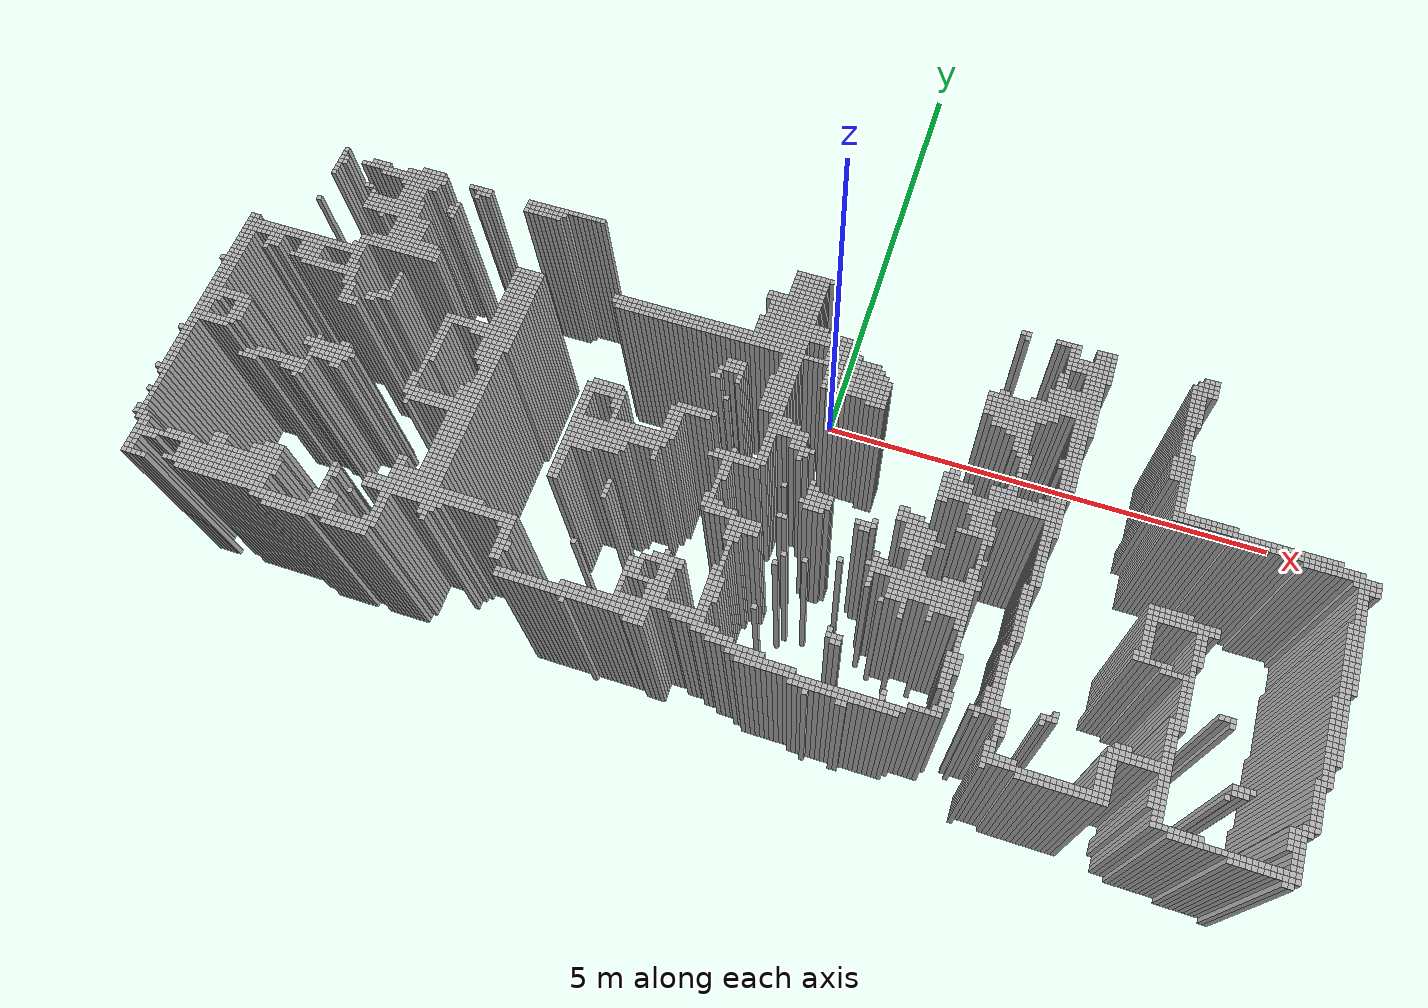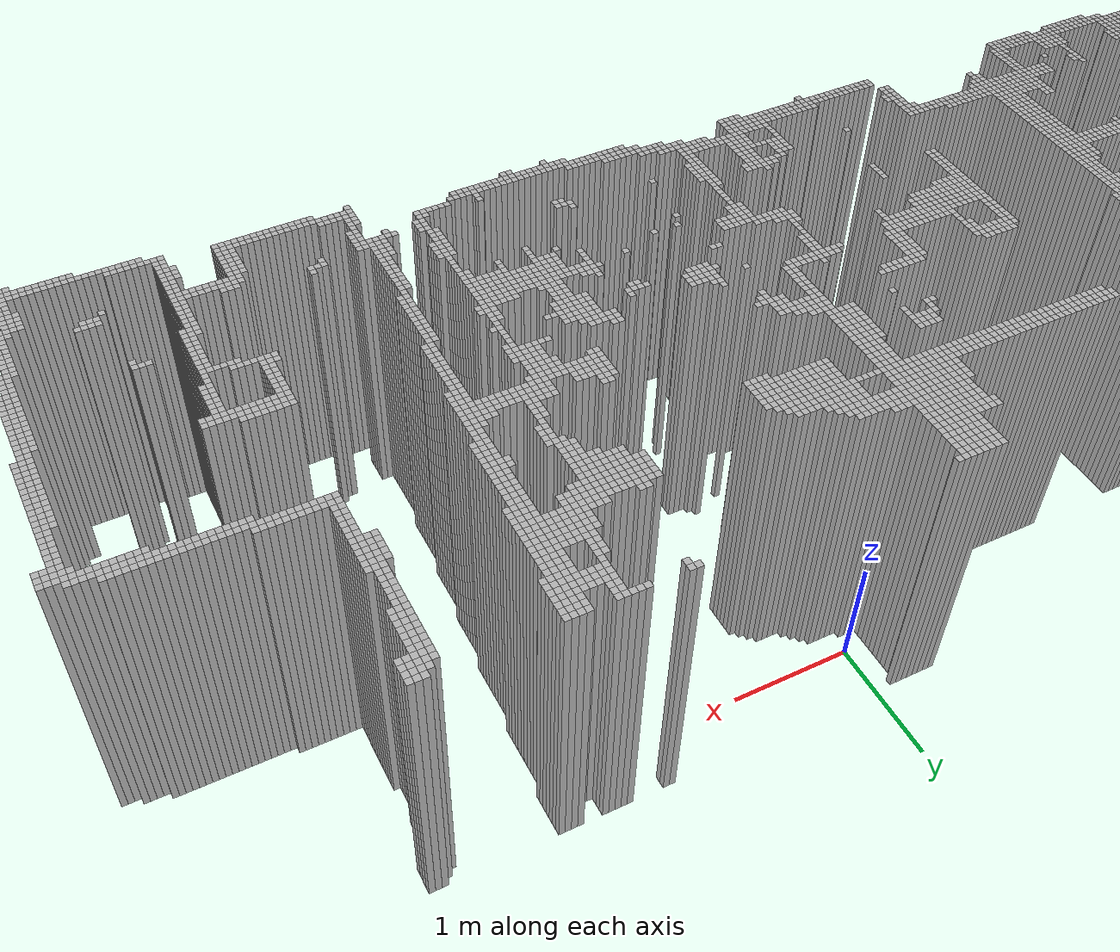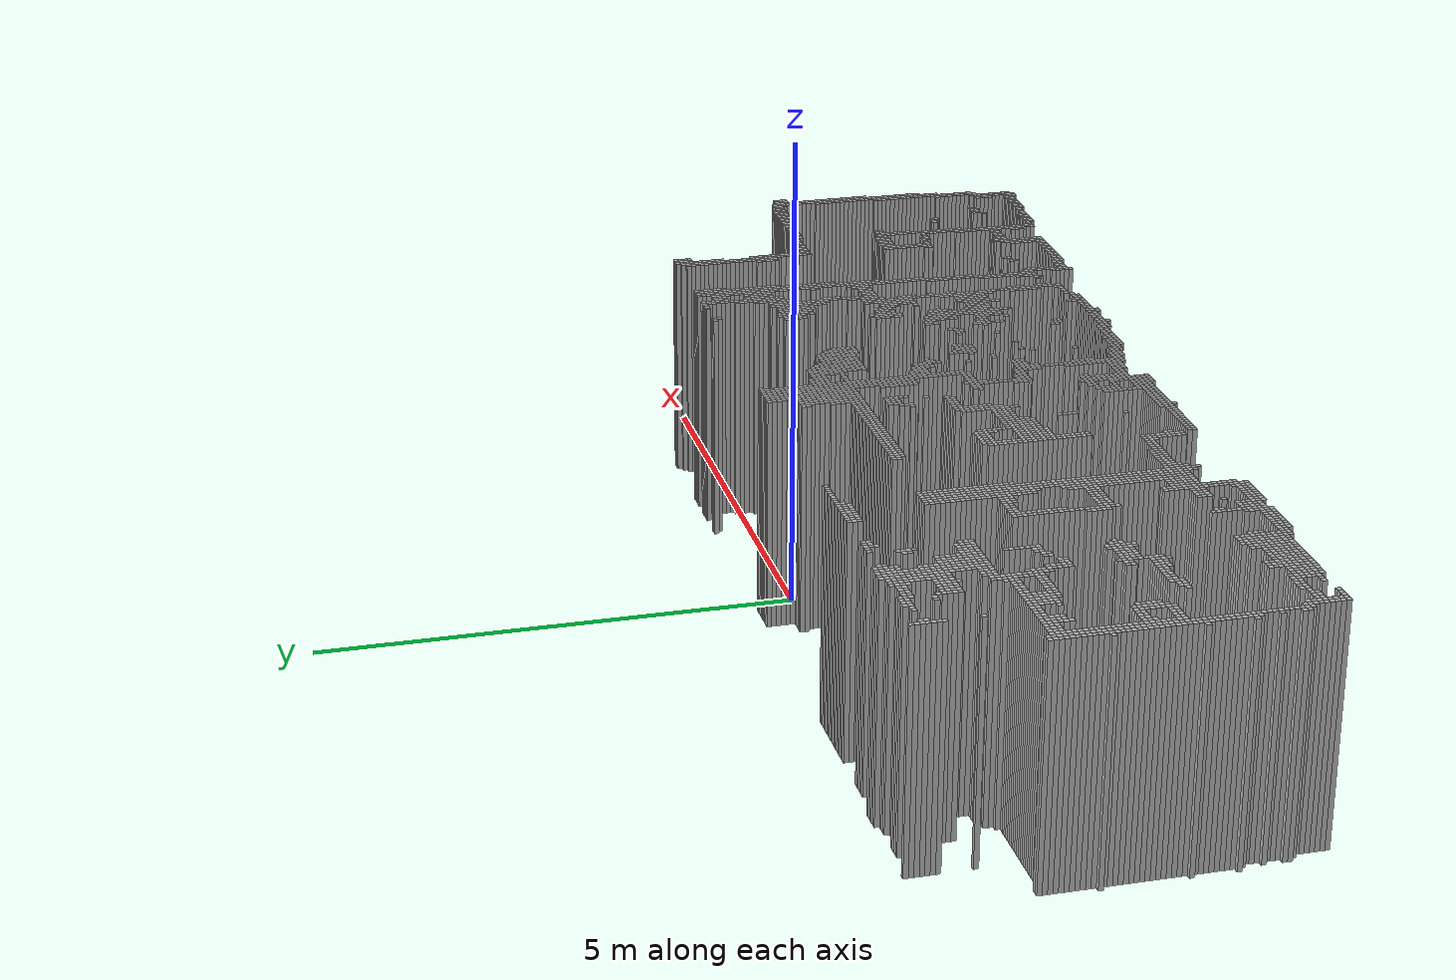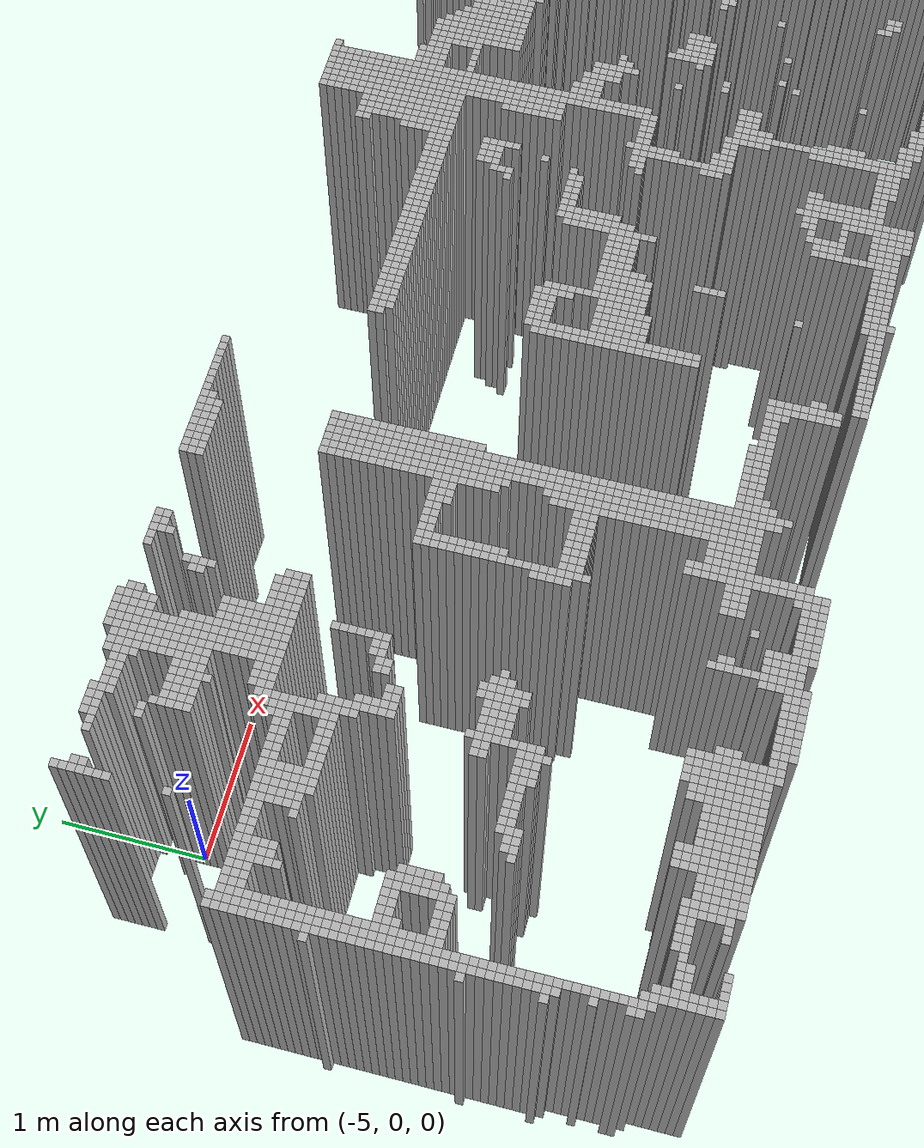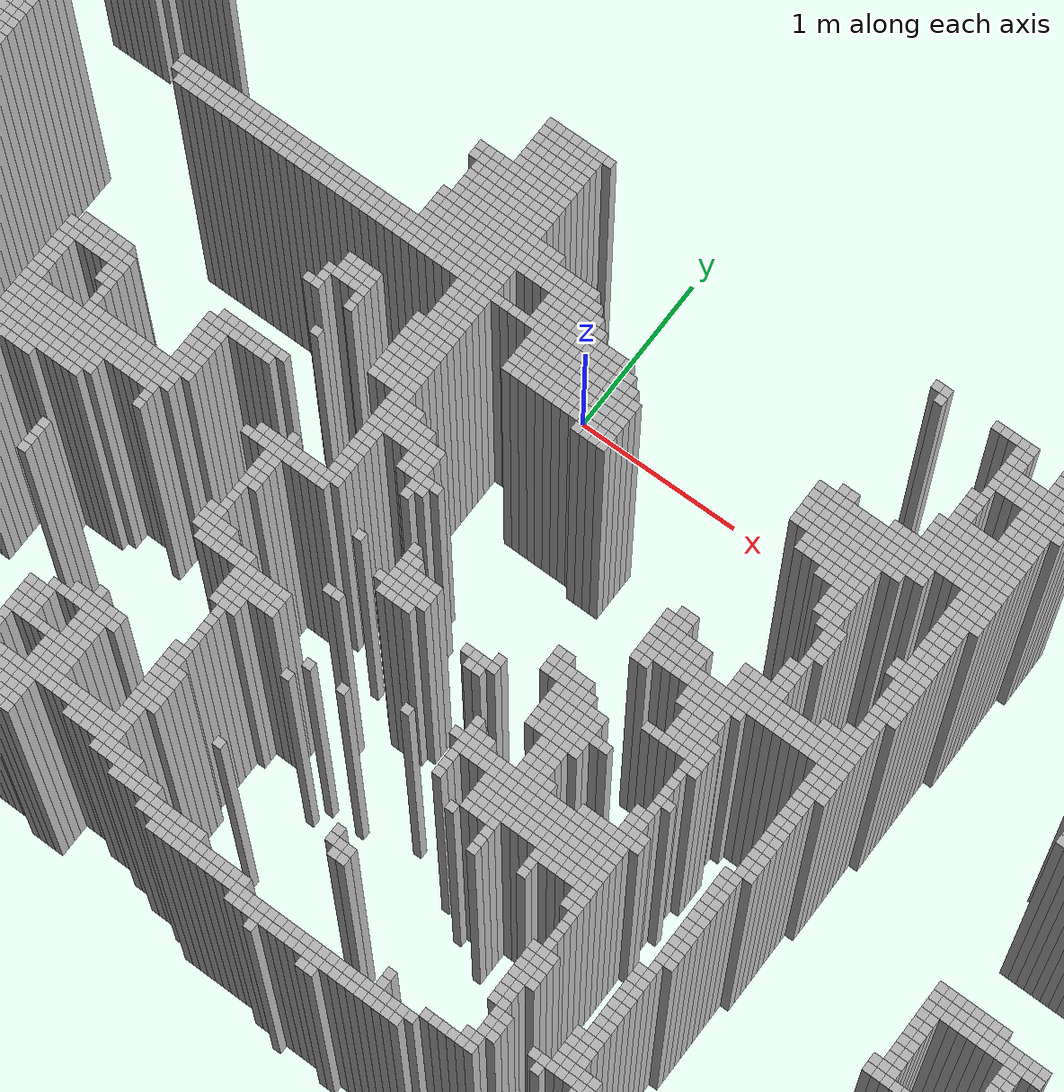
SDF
<sdf version="1.9">
 <world name="map_world">
  <gravity>0 0 -9.8</gravity>
  <model name="wall_113_145">
   <static>true</static>
   <pose>-5.511 0.430 1.250 0 0 0</pose>
   <link name="link">
    <collision name="collision"><geometry><box><size>0.050 0.050 2.500</size></box></geometry></collision>
    <visual name="visual"><geometry><box><size>0.050 0.050 2.500</size></box></geometry></visual>
   </link>
  </model>
  <model name="wall_131_145">
   <static>true</static>
   <pose>-4.611 0.430 1.250 0 0 0</pose>
   <link name="link">
    <collision name="collision"><geometry><box><size>0.050 0.050 2.500</size></box></geometry></collision>
    <visual name="visual"><geometry><box><size>0.050 0.050 2.500</size></box></geometry></visual>
   </link>
  </model>
  <model name="wall_132_145">
   <static>true</static>
   <pose>-4.561 0.430 1.250 0 0 0</pose>
   <link name="link">
    <collision name="collision"><geometry><box><size>0.050 0.050 2.500</size></box></geometry></collision>
    <visual name="visual"><geometry><box><size>0.050 0.050 2.500</size></box></geometry></visual>
   </link>
  </model>
  <model name="wall_133_145">
   <static>true</static>
   <pose>-4.511 0.430 1.250 0 0 0</pose>
   <link name="link">
    <collision name="collision"><geometry><box><size>0.050 0.050 2.500</size></box></geometry></collision>
    <visual name="visual"><geometry><box><size>0.050 0.050 2.500</size></box></geometry></visual>
   </link>
  </model>
  <model name="wall_134_145">
   <static>true</static>
   <pose>-4.461 0.430 1.250 0 0 0</pose>
   <link name="link">
    <collision name="collision"><geometry><box><size>0.050 0.050 2.500</size></box></geometry></collision>
    <visual name="visual"><geometry><box><size>0.050 0.050 2.500</size></box></geometry></visual>
   </link>
  </model>
  <model name="wall_135_145">
   <static>true</static>
   <pose>-4.411 0.430 1.250 0 0 0</pose>
   <link name="link">
    <collision name="collision"><geometry><box><size>0.050 0.050 2.500</size></box></geometry></collision>
    <visual name="visual"><geometry><box><size>0.050 0.050 2.500</size></box></geometry></visual>
   </link>
  </model>
  <model name="wall_113_146">
   <static>true</static>
   <pose>-5.511 0.380 1.250 0 0 0</pose>
   <link name="link">
    <collision name="collision"><geometry><box><size>0.050 0.050 2.500</size></box></geometry></collision>
    <visual name="visual"><geometry><box><size>0.050 0.050 2.500</size></box></geometry></visual>
   </link>
  </model>
  <model name="wall_120_146">
   <static>true</static>
   <pose>-5.161 0.380 1.250 0 0 0</pose>
   <link name="link">
    <collision name="collision"><geometry><box><size>0.050 0.050 2.500</size></box></geometry></collision>
    <visual name="visual"><geometry><box><size>0.050 0.050 2.500</size></box></geometry></visual>
   </link>
  </model>
  <model name="wall_121_146">
   <static>true</static>
   <pose>-5.111 0.380 1.250 0 0 0</pose>
   <link name="link">
    <collision name="collision"><geometry><box><size>0.050 0.050 2.500</size></box></geometry></collision>
    <visual name="visual"><geometry><box><size>0.050 0.050 2.500</size></box></geometry></visual>
   </link>
  </model>
  <model name="wall_122_146">
   <static>true</static>
   <pose>-5.061 0.380 1.250 0 0 0</pose>
   <link name="link">
    <collision name="collision"><geometry><box><size>0.050 0.050 2.500</size></box></geometry></collision>
    <visual name="visual"><geometry><box><size>0.050 0.050 2.500</size></box></geometry></visual>
   </link>
  </model>
  <model name="wall_123_146">
   <static>true</static>
   <pose>-5.011 0.380 1.250 0 0 0</pose>
   <link name="link">
    <collision name="collision"><geometry><box><size>0.050 0.050 2.500</size></box></geometry></collision>
    <visual name="visual"><geometry><box><size>0.050 0.050 2.500</size></box></geometry></visual>
   </link>
  </model>
  <model name="wall_128_146">
   <static>true</static>
   <pose>-4.761 0.380 1.250 0 0 0</pose>
   <link name="link">
    <collision name="collision"><geometry><box><size>0.050 0.050 2.500</size></box></geometry></collision>
    <visual name="visual"><geometry><box><size>0.050 0.050 2.500</size></box></geometry></visual>
   </link>
  </model>
  <model name="wall_129_146">
   <static>true</static>
   <pose>-4.711 0.380 1.250 0 0 0</pose>
   <link name="link">
    <collision name="collision"><geometry><box><size>0.050 0.050 2.500</size></box></geometry></collision>
    <visual name="visual"><geometry><box><size>0.050 0.050 2.500</size></box></geometry></visual>
   </link>
  </model>
  <model name="wall_130_146">
   <static>true</static>
   <pose>-4.661 0.380 1.250 0 0 0</pose>
   <link name="link">
    <collision name="collision"><geometry><box><size>0.050 0.050 2.500</size></box></geometry></collision>
    <visual name="visual"><geometry><box><size>0.050 0.050 2.500</size></box></geometry></visual>
   </link>
  </model>
  <model name="wall_131_146">
   <static>true</static>
   <pose>-4.611 0.380 1.250 0 0 0</pose>
   <link name="link">
    <collision name="collision"><geometry><box><size>0.050 0.050 2.500</size></box></geometry></collision>
    <visual name="visual"><geometry><box><size>0.050 0.050 2.500</size></box></geometry></visual>
   </link>
  </model>
  <model name="wall_132_146">
   <static>true</static>
   <pose>-4.561 0.380 1.250 0 0 0</pose>
   <link name="link">
    <collision name="collision"><geometry><box><size>0.050 0.050 2.500</size></box></geometry></collision>
    <visual name="visual"><geometry><box><size>0.050 0.050 2.500</size></box></geometry></visual>
   </link>
  </model>
  <model name="wall_133_146">
   <static>true</static>
   <pose>-4.511 0.380 1.250 0 0 0</pose>
   <link name="link">
    <collision name="collision"><geometry><box><size>0.050 0.050 2.500</size></box></geometry></collision>
    <visual name="visual"><geometry><box><size>0.050 0.050 2.500</size></box></geometry></visual>
   </link>
  </model>
  <model name="wall_134_146">
   <static>true</static>
   <pose>-4.461 0.380 1.250 0 0 0</pose>
   <link name="link">
    <collision name="collision"><geometry><box><size>0.050 0.050 2.500</size></box></geometry></collision>
    <visual name="visual"><geometry><box><size>0.050 0.050 2.500</size></box></geometry></visual>
   </link>
  </model>
  <model name="wall_135_146">
   <static>true</static>
   <pose>-4.411 0.380 1.250 0 0 0</pose>
   <link name="link">
    <collision name="collision"><geometry><box><size>0.050 0.050 2.500</size></box></geometry></collision>
    <visual name="visual"><geometry><box><size>0.050 0.050 2.500</size></box></geometry></visual>
   </link>
  </model>
  <model name="wall_136_146">
   <static>true</static>
   <pose>-4.361 0.380 1.250 0 0 0</pose>
   <link name="link">
    <collision name="collision"><geometry><box><size>0.050 0.050 2.500</size></box></geometry></collision>
    <visual name="visual"><geometry><box><size>0.050 0.050 2.500</size></box></geometry></visual>
   </link>
  </model>
  <model name="wall_142_146">
   <static>true</static>
   <pose>-4.061 0.380 1.250 0 0 0</pose>
   <link name="link">
    <collision name="collision"><geometry><box><size>0.050 0.050 2.500</size></box></geometry></collision>
    <visual name="visual"><geometry><box><size>0.050 0.050 2.500</size></box></geometry></visual>
   </link>
  </model>
  <model name="wall_143_146">
   <static>true</static>
   <pose>-4.011 0.380 1.250 0 0 0</pose>
   <link name="link">
    <collision name="collision"><geometry><box><size>0.050 0.050 2.500</size></box></geometry></collision>
    <visual name="visual"><geometry><box><size>0.050 0.050 2.500</size></box></geometry></visual>
   </link>
  </model>
  <model name="wall_144_146">
   <static>true</static>
   <pose>-3.961 0.380 1.250 0 0 0</pose>
   <link name="link">
    <collision name="collision"><geometry><box><size>0.050 0.050 2.500</size></box></geometry></collision>
    <visual name="visual"><geometry><box><size>0.050 0.050 2.500</size></box></geometry></visual>
   </link>
  </model>
  <model name="wall_145_146">
   <static>true</static>
   <pose>-3.911 0.380 1.250 0 0 0</pose>
   <link name="link">
    <collision name="collision"><geometry><box><size>0.050 0.050 2.500</size></box></geometry></collision>
    <visual name="visual"><geometry><box><size>0.050 0.050 2.500</size></box></geometry></visual>
   </link>
  </model>
  <model name="wall_146_146">
   <static>true</static>
   <pose>-3.861 0.380 1.250 0 0 0</pose>
   <link name="link">
    <collision name="collision"><geometry><box><size>0.050 0.050 2.500</size></box></geometry></collision>
    <visual name="visual"><geometry><box><size>0.050 0.050 2.500</size></box></geometry></visual>
   </link>
  </model>
  <model name="wall_155_146">
   <static>true</static>
   <pose>-3.411 0.380 1.250 0 0 0</pose>
   <link name="link">
    <collision name="collision"><geometry><box><size>0.050 0.050 2.500</size></box></geometry></collision>
    <visual name="visual"><geometry><box><size>0.050 0.050 2.500</size></box></geometry></visual>
   </link>
  </model>
  <model name="wall_156_146">
   <static>true</static>
   <pose>-3.361 0.380 1.250 0 0 0</pose>
   <link name="link">
    <collision name="collision"><geometry><box><size>0.050 0.050 2.500</size></box></geometry></collision>
    <visual name="visual"><geometry><box><size>0.050 0.050 2.500</size></box></geometry></visual>
   </link>
  </model>
  <model name="wall_157_146">
   <static>true</static>
   <pose>-3.311 0.380 1.250 0 0 0</pose>
   <link name="link">
    <collision name="collision"><geometry><box><size>0.050 0.050 2.500</size></box></geometry></collision>
    <visual name="visual"><geometry><box><size>0.050 0.050 2.500</size></box></geometry></visual>
   </link>
  </model>
  <model name="wall_158_146">
   <static>true</static>
   <pose>-3.261 0.380 1.250 0 0 0</pose>
   <link name="link">
    <collision name="collision"><geometry><box><size>0.050 0.050 2.500</size></box></geometry></collision>
    <visual name="visual"><geometry><box><size>0.050 0.050 2.500</size></box></geometry></visual>
   </link>
  </model>
  <model name="wall_159_146">
   <static>true</static>
   <pose>-3.211 0.380 1.250 0 0 0</pose>
   <link name="link">
    <collision name="collision"><geometry><box><size>0.050 0.050 2.500</size></box></geometry></collision>
    <visual name="visual"><geometry><box><size>0.050 0.050 2.500</size></box></geometry></visual>
   </link>
  </model>
  <model name="wall_160_146">
   <static>true</static>
   <pose>-3.161 0.380 1.250 0 0 0</pose>
   <link name="link">
    <collision name="collision"><geometry><box><size>0.050 0.050 2.500</size></box></geometry></collision>
    <visual name="visual"><geometry><box><size>0.050 0.050 2.500</size></box></geometry></visual>
   </link>
  </model>
  <model name="wall_161_146">
   <static>true</static>
   <pose>-3.111 0.380 1.250 0 0 0</pose>
   <link name="link">
    <collision name="collision"><geometry><box><size>0.050 0.050 2.500</size></box></geometry></collision>
    <visual name="visual"><geometry><box><size>0.050 0.050 2.500</size></box></geometry></visual>
   </link>
  </model>
  <model name="wall_162_146">
   <static>true</static>
   <pose>-3.061 0.380 1.250 0 0 0</pose>
   <link name="link">
    <collision name="collision"><geometry><box><size>0.050 0.050 2.500</size></box></geometry></collision>
    <visual name="visual"><geometry><box><size>0.050 0.050 2.500</size></box></geometry></visual>
   </link>
  </model>
  <model name="wall_163_146">
   <static>true</static>
   <pose>-3.011 0.380 1.250 0 0 0</pose>
   <link name="link">
    <collision name="collision"><geometry><box><size>0.050 0.050 2.500</size></box></geometry></collision>
    <visual name="visual"><geometry><box><size>0.050 0.050 2.500</size></box></geometry></visual>
   </link>
  </model>
  <model name="wall_164_146">
   <static>true</static>
   <pose>-2.961 0.380 1.250 0 0 0</pose>
   <link name="link">
    <collision name="collision"><geometry><box><size>0.050 0.050 2.500</size></box></geometry></collision>
    <visual name="visual"><geometry><box><size>0.050 0.050 2.500</size></box></geometry></visual>
   </link>
  </model>
  <model name="wall_165_146">
   <static>true</static>
   <pose>-2.911 0.380 1.250 0 0 0</pose>
   <link name="link">
    <collision name="collision"><geometry><box><size>0.050 0.050 2.500</size></box></geometry></collision>
    <visual name="visual"><geometry><box><size>0.050 0.050 2.500</size></box></geometry></visual>
   </link>
  </model>
  <model name="wall_166_146">
   <static>true</static>
   <pose>-2.861 0.380 1.250 0 0 0</pose>
   <link name="link">
    <collision name="collision"><geometry><box><size>0.050 0.050 2.500</size></box></geometry></collision>
    <visual name="visual"><geometry><box><size>0.050 0.050 2.500</size></box></geometry></visual>
   </link>
  </model>
  <model name="wall_167_146">
   <static>true</static>
   <pose>-2.811 0.380 1.250 0 0 0</pose>
   <link name="link">
    <collision name="collision"><geometry><box><size>0.050 0.050 2.500</size></box></geometry></collision>
    <visual name="visual"><geometry><box><size>0.050 0.050 2.500</size></box></geometry></visual>
   </link>
  </model>
  <model name="wall_168_146">
   <static>true</static>
   <pose>-2.761 0.380 1.250 0 0 0</pose>
   <link name="link">
    <collision name="collision"><geometry><box><size>0.050 0.050 2.500</size></box></geometry></collision>
    <visual name="visual"><geometry><box><size>0.050 0.050 2.500</size></box></geometry></visual>
   </link>
  </model>
  <model name="wall_169_146">
   <static>true</static>
   <pose>-2.711 0.380 1.250 0 0 0</pose>
   <link name="link">
    <collision name="collision"><geometry><box><size>0.050 0.050 2.500</size></box></geometry></collision>
    <visual name="visual"><geometry><box><size>0.050 0.050 2.500</size></box></geometry></visual>
   </link>
  </model>
  <model name="wall_170_146">
   <static>true</static>
   <pose>-2.661 0.380 1.250 0 0 0</pose>
   <link name="link">
    <collision name="collision"><geometry><box><size>0.050 0.050 2.500</size></box></geometry></collision>
    <visual name="visual"><geometry><box><size>0.050 0.050 2.500</size></box></geometry></visual>
   </link>
  </model>
  <model name="wall_171_146">
   <static>true</static>
   <pose>-2.611 0.380 1.250 0 0 0</pose>
   <link name="link">
    <collision name="collision"><geometry><box><size>0.050 0.050 2.500</size></box></geometry></collision>
    <visual name="visual"><geometry><box><size>0.050 0.050 2.500</size></box></geometry></visual>
   </link>
  </model>
  <model name="wall_213_146">
   <static>true</static>
   <pose>-0.511 0.380 1.250 0 0 0</pose>
   <link name="link">
    <collision name="collision"><geometry><box><size>0.050 0.050 2.500</size></box></geometry></collision>
    <visual name="visual"><geometry><box><size>0.050 0.050 2.500</size></box></geometry></visual>
   </link>
  </model>
  <model name="wall_214_146">
   <static>true</static>
   <pose>-0.461 0.380 1.250 0 0 0</pose>
   <link name="link">
    <collision name="collision"><geometry><box><size>0.050 0.050 2.500</size></box></geometry></collision>
    <visual name="visual"><geometry><box><size>0.050 0.050 2.500</size></box></geometry></visual>
   </link>
  </model>
  <model name="wall_215_146">
   <static>true</static>
   <pose>-0.411 0.380 1.250 0 0 0</pose>
   <link name="link">
    <collision name="collision"><geometry><box><size>0.050 0.050 2.500</size></box></geometry></collision>
    <visual name="visual"><geometry><box><size>0.050 0.050 2.500</size></box></geometry></visual>
   </link>
  </model>
  <model name="wall_216_146">
   <static>true</static>
   <pose>-0.361 0.380 1.250 0 0 0</pose>
   <link name="link">
    <collision name="collision"><geometry><box><size>0.050 0.050 2.500</size></box></geometry></collision>
    <visual name="visual"><geometry><box><size>0.050 0.050 2.500</size></box></geometry></visual>
   </link>
  </model>
  <model name="wall_217_146">
   <static>true</static>
   <pose>-0.311 0.380 1.250 0 0 0</pose>
   <link name="link">
    <collision name="collision"><geometry><box><size>0.050 0.050 2.500</size></box></geometry></collision>
    <visual name="visual"><geometry><box><size>0.050 0.050 2.500</size></box></geometry></visual>
   </link>
  </model>
  <model name="wall_218_146">
   <static>true</static>
   <pose>-0.261 0.380 1.250 0 0 0</pose>
   <link name="link">
    <collision name="collision"><geometry><box><size>0.050 0.050 2.500</size></box></geometry></collision>
    <visual name="visual"><geometry><box><size>0.050 0.050 2.500</size></box></geometry></visual>
   </link>
  </model>
  <model name="wall_219_146">
   <static>true</static>
   <pose>-0.211 0.380 1.250 0 0 0</pose>
   <link name="link">
    <collision name="collision"><geometry><box><size>0.050 0.050 2.500</size></box></geometry></collision>
    <visual name="visual"><geometry><box><size>0.050 0.050 2.500</size></box></geometry></visual>
   </link>
  </model>
  <model name="wall_220_146">
   <static>true</static>
   <pose>-0.161 0.380 1.250 0 0 0</pose>
   <link name="link">
    <collision name="collision"><geometry><box><size>0.050 0.050 2.500</size></box></geometry></collision>
    <visual name="visual"><geometry><box><size>0.050 0.050 2.500</size></box></geometry></visual>
   </link>
  </model>
  <model name="wall_259_146">
   <static>true</static>
   <pose>1.789 0.380 1.250 0 0 0</pose>
   <link name="link">
    <collision name="collision"><geometry><box><size>0.050 0.050 2.500</size></box></geometry></collision>
    <visual name="visual"><geometry><box><size>0.050 0.050 2.500</size></box></geometry></visual>
   </link>
  </model>
  <model name="wall_260_146">
   <static>true</static>
   <pose>1.839 0.380 1.250 0 0 0</pose>
   <link name="link">
    <collision name="collision"><geometry><box><size>0.050 0.050 2.500</size></box></geometry></collision>
    <visual name="visual"><geometry><box><size>0.050 0.050 2.500</size></box></geometry></visual>
   </link>
  </model>
  <model name="wall_266_146">
   <static>true</static>
   <pose>2.139 0.380 1.250 0 0 0</pose>
   <link name="link">
    <collision name="collision"><geometry><box><size>0.050 0.050 2.500</size></box></geometry></collision>
    <visual name="visual"><geometry><box><size>0.050 0.050 2.500</size></box></geometry></visual>
   </link>
  </model>
  <model name="wall_267_146">
   <static>true</static>
   <pose>2.189 0.380 1.250 0 0 0</pose>
   <link name="link">
    <collision name="collision"><geometry><box><size>0.050 0.050 2.500</size></box></geometry></collision>
    <visual name="visual"><geometry><box><size>0.050 0.050 2.500</size></box></geometry></visual>
   </link>
  </model>
  <model name="wall_268_146">
   <static>true</static>
   <pose>2.239 0.380 1.250 0 0 0</pose>
   <link name="link">
    <collision name="collision"><geometry><box><size>0.050 0.050 2.500</size></box></geometry></collision>
    <visual name="visual"><geometry><box><size>0.050 0.050 2.500</size></box></geometry></visual>
   </link>
  </model>
  <model name="wall_269_146">
   <static>true</static>
   <pose>2.289 0.380 1.250 0 0 0</pose>
   <link name="link">
    <collision name="collision"><geometry><box><size>0.050 0.050 2.500</size></box></geometry></collision>
    <visual name="visual"><geometry><box><size>0.050 0.050 2.500</size></box></geometry></visual>
   </link>
  </model>
  <model name="wall_270_146">
   <static>true</static>
   <pose>2.339 0.380 1.250 0 0 0</pose>
   <link name="link">
    <collision name="collision"><geometry><box><size>0.050 0.050 2.500</size></box></geometry></collision>
    <visual name="visual"><geometry><box><size>0.050 0.050 2.500</size></box></geometry></visual>
   </link>
  </model>
  <model name="wall_274_146">
   <static>true</static>
   <pose>2.539 0.380 1.250 0 0 0</pose>
   <link name="link">
    <collision name="collision"><geometry><box><size>0.050 0.050 2.500</size></box></geometry></collision>
    <visual name="visual"><geometry><box><size>0.050 0.050 2.500</size></box></geometry></visual>
   </link>
  </model>
  <model name="wall_275_146">
   <static>true</static>
   <pose>2.589 0.380 1.250 0 0 0</pose>
   <link name="link">
    <collision name="collision"><geometry><box><size>0.050 0.050 2.500</size></box></geometry></collision>
    <visual name="visual"><geometry><box><size>0.050 0.050 2.500</size></box></geometry></visual>
   </link>
  </model>
  <model name="wall_276_146">
   <static>true</static>
   <pose>2.639 0.380 1.250 0 0 0</pose>
   <link name="link">
    <collision name="collision"><geometry><box><size>0.050 0.050 2.500</size></box></geometry></collision>
    <visual name="visual"><geometry><box><size>0.050 0.050 2.500</size></box></geometry></visual>
   </link>
  </model>
  <model name="wall_277_146">
   <static>true</static>
   <pose>2.689 0.380 1.250 0 0 0</pose>
   <link name="link">
    <collision name="collision"><geometry><box><size>0.050 0.050 2.500</size></box></geometry></collision>
    <visual name="visual"><geometry><box><size>0.050 0.050 2.500</size></box></geometry></visual>
   </link>
  </model>
  <model name="wall_295_146">
   <static>true</static>
   <pose>3.589 0.380 1.250 0 0 0</pose>
   <link name="link">
    <collision name="collision"><geometry><box><size>0.050 0.050 2.500</size></box></geometry></collision>
    <visual name="visual"><geometry><box><size>0.050 0.050 2.500</size></box></geometry></visual>
   </link>
  </model>
  <model name="wall_296_146">
   <static>true</static>
   <pose>3.639 0.380 1.250 0 0 0</pose>
   <link name="link">
    <collision name="collision"><geometry><box><size>0.050 0.050 2.500</size></box></geometry></collision>
    <visual name="visual"><geometry><box><size>0.050 0.050 2.500</size></box></geometry></visual>
   </link>
  </model>
  <model name="wall_297_146">
   <static>true</static>
   <pose>3.689 0.380 1.250 0 0 0</pose>
   <link name="link">
    <collision name="collision"><geometry><box><size>0.050 0.050 2.500</size></box></geometry></collision>
    <visual name="visual"><geometry><box><size>0.050 0.050 2.500</size></box></geometry></visual>
   </link>
  </model>
  <model name="wall_113_147">
   <static>true</static>
   <pose>-5.511 0.330 1.250 0 0 0</pose>
   <link name="link">
    <collision name="collision"><geometry><box><size>0.050 0.050 2.500</size></box></geometry></collision>
    <visual name="visual"><geometry><box><size>0.050 0.050 2.500</size></box></geometry></visual>
   </link>
  </model>
  <model name="wall_114_147">
   <static>true</static>
   <pose>-5.461 0.330 1.250 0 0 0</pose>
   <link name="link">
    <collision name="collision"><geometry><box><size>0.050 0.050 2.500</size></box></geometry></collision>
    <visual name="visual"><geometry><box><size>0.050 0.050 2.500</size></box></geometry></visual>
   </link>
  </model>
  <model name="wall_118_147">
   <static>true</static>
   <pose>-5.261 0.330 1.250 0 0 0</pose>
   <link name="link">
    <collision name="collision"><geometry><box><size>0.050 0.050 2.500</size></box></geometry></collision>
    <visual name="visual"><geometry><box><size>0.050 0.050 2.500</size></box></geometry></visual>
   </link>
  </model>
  <model name="wall_119_147">
   <static>true</static>
   <pose>-5.211 0.330 1.250 0 0 0</pose>
   <link name="link">
    <collision name="collision"><geometry><box><size>0.050 0.050 2.500</size></box></geometry></collision>
    <visual name="visual"><geometry><box><size>0.050 0.050 2.500</size></box></geometry></visual>
   </link>
  </model>
  <model name="wall_120_147">
   <static>true</static>
   <pose>-5.161 0.330 1.250 0 0 0</pose>
   <link name="link">
    <collision name="collision"><geometry><box><size>0.050 0.050 2.500</size></box></geometry></collision>
    <visual name="visual"><geometry><box><size>0.050 0.050 2.500</size></box></geometry></visual>
   </link>
  </model>
  <model name="wall_121_147">
   <static>true</static>
   <pose>-5.111 0.330 1.250 0 0 0</pose>
   <link name="link">
    <collision name="collision"><geometry><box><size>0.050 0.050 2.500</size></box></geometry></collision>
    <visual name="visual"><geometry><box><size>0.050 0.050 2.500</size></box></geometry></visual>
   </link>
  </model>
  <model name="wall_122_147">
   <static>true</static>
   <pose>-5.061 0.330 1.250 0 0 0</pose>
   <link name="link">
    <collision name="collision"><geometry><box><size>0.050 0.050 2.500</size></box></geometry></collision>
    <visual name="visual"><geometry><box><size>0.050 0.050 2.500</size></box></geometry></visual>
   </link>
  </model>
  <model name="wall_123_147">
   <static>true</static>
   <pose>-5.011 0.330 1.250 0 0 0</pose>
   <link name="link">
    <collision name="collision"><geometry><box><size>0.050 0.050 2.500</size></box></geometry></collision>
    <visual name="visual"><geometry><box><size>0.050 0.050 2.500</size></box></geometry></visual>
   </link>
  </model>
  <model name="wall_124_147">
   <static>true</static>
   <pose>-4.961 0.330 1.250 0 0 0</pose>
   <link name="link">
    <collision name="collision"><geometry><box><size>0.050 0.050 2.500</size></box></geometry></collision>
    <visual name="visual"><geometry><box><size>0.050 0.050 2.500</size></box></geometry></visual>
   </link>
  </model>
  <model name="wall_125_147">
   <static>true</static>
   <pose>-4.911 0.330 1.250 0 0 0</pose>
   <link name="link">
    <collision name="collision"><geometry><box><size>0.050 0.050 2.500</size></box></geometry></collision>
    <visual name="visual"><geometry><box><size>0.050 0.050 2.500</size></box></geometry></visual>
   </link>
  </model>
  <model name="wall_126_147">
   <static>true</static>
   <pose>-4.861 0.330 1.250 0 0 0</pose>
   <link name="link">
    <collision name="collision"><geometry><box><size>0.050 0.050 2.500</size></box></geometry></collision>
    <visual name="visual"><geometry><box><size>0.050 0.050 2.500</size></box></geometry></visual>
   </link>
  </model>
  <model name="wall_127_147">
   <static>true</static>
   <pose>-4.811 0.330 1.250 0 0 0</pose>
   <link name="link">
    <collision name="collision"><geometry><box><size>0.050 0.050 2.500</size></box></geometry></collision>
    <visual name="visual"><geometry><box><size>0.050 0.050 2.500</size></box></geometry></visual>
   </link>
  </model>
  <model name="wall_128_147">
   <static>true</static>
   <pose>-4.761 0.330 1.250 0 0 0</pose>
   <link name="link">
    <collision name="collision"><geometry><box><size>0.050 0.050 2.500</size></box></geometry></collision>
    <visual name="visual"><geometry><box><size>0.050 0.050 2.500</size></box></geometry></visual>
   </link>
  </model>
  <model name="wall_129_147">
   <static>true</static>
   <pose>-4.711 0.330 1.250 0 0 0</pose>
   <link name="link">
    <collision name="collision"><geometry><box><size>0.050 0.050 2.500</size></box></geometry></collision>
    <visual name="visual"><geometry><box><size>0.050 0.050 2.500</size></box></geometry></visual>
   </link>
  </model>
  <model name="wall_130_147">
   <static>true</static>
   <pose>-4.661 0.330 1.250 0 0 0</pose>
   <link name="link">
    <collision name="collision"><geometry><box><size>0.050 0.050 2.500</size></box></geometry></collision>
    <visual name="visual"><geometry><box><size>0.050 0.050 2.500</size></box></geometry></visual>
   </link>
  </model>
  <model name="wall_131_147">
   <static>true</static>
   <pose>-4.611 0.330 1.250 0 0 0</pose>
   <link name="link">
    <collision name="collision"><geometry><box><size>0.050 0.050 2.500</size></box></geometry></collision>
    <visual name="visual"><geometry><box><size>0.050 0.050 2.500</size></box></geometry></visual>
   </link>
  </model>
  <model name="wall_132_147">
   <static>true</static>
   <pose>-4.561 0.330 1.250 0 0 0</pose>
   <link name="link">
    <collision name="collision"><geometry><box><size>0.050 0.050 2.500</size></box></geometry></collision>
    <visual name="visual"><geometry><box><size>0.050 0.050 2.500</size></box></geometry></visual>
   </link>
  </model>
  <model name="wall_133_147">
   <static>true</static>
   <pose>-4.511 0.330 1.250 0 0 0</pose>
   <link name="link">
    <collision name="collision"><geometry><box><size>0.050 0.050 2.500</size></box></geometry></collision>
    <visual name="visual"><geometry><box><size>0.050 0.050 2.500</size></box></geometry></visual>
   </link>
  </model>
  <model name="wall_134_147">
   <static>true</static>
   <pose>-4.461 0.330 1.250 0 0 0</pose>
   <link name="link">
    <collision name="collision"><geometry><box><size>0.050 0.050 2.500</size></box></geometry></collision>
    <visual name="visual"><geometry><box><size>0.050 0.050 2.500</size></box></geometry></visual>
   </link>
  </model>
  <model name="wall_135_147">
   <static>true</static>
   <pose>-4.411 0.330 1.250 0 0 0</pose>
   <link name="link">
    <collision name="collision"><geometry><box><size>0.050 0.050 2.500</size></box></geometry></collision>
    <visual name="visual"><geometry><box><size>0.050 0.050 2.500</size></box></geometry></visual>
   </link>
  </model>
  <model name="wall_136_147">
   <static>true</static>
   <pose>-4.361 0.330 1.250 0 0 0</pose>
   <link name="link">
    <collision name="collision"><geometry><box><size>0.050 0.050 2.500</size></box></geometry></collision>
    <visual name="visual"><geometry><box><size>0.050 0.050 2.500</size></box></geometry></visual>
   </link>
  </model>
  <model name="wall_144_147">
   <static>true</static>
   <pose>-3.961 0.330 1.250 0 0 0</pose>
   <link name="link">
    <collision name="collision"><geometry><box><size>0.050 0.050 2.500</size></box></geometry></collision>
    <visual name="visual"><geometry><box><size>0.050 0.050 2.500</size></box></geometry></visual>
   </link>
  </model>
  <model name="wall_145_147">
   <static>true</static>
   <pose>-3.911 0.330 1.250 0 0 0</pose>
   <link name="link">
    <collision name="collision"><geometry><box><size>0.050 0.050 2.500</size></box></geometry></collision>
    <visual name="visual"><geometry><box><size>0.050 0.050 2.500</size></box></geometry></visual>
   </link>
  </model>
  <model name="wall_146_147">
   <static>true</static>
   <pose>-3.861 0.330 1.250 0 0 0</pose>
   <link name="link">
    <collision name="collision"><geometry><box><size>0.050 0.050 2.500</size></box></geometry></collision>
    <visual name="visual"><geometry><box><size>0.050 0.050 2.500</size></box></geometry></visual>
   </link>
  </model>
  <model name="wall_155_147">
   <static>true</static>
   <pose>-3.411 0.330 1.250 0 0 0</pose>
   <link name="link">
    <collision name="collision"><geometry><box><size>0.050 0.050 2.500</size></box></geometry></collision>
    <visual name="visual"><geometry><box><size>0.050 0.050 2.500</size></box></geometry></visual>
   </link>
  </model>
  <model name="wall_156_147">
   <static>true</static>
   <pose>-3.361 0.330 1.250 0 0 0</pose>
   <link name="link">
    <collision name="collision"><geometry><box><size>0.050 0.050 2.500</size></box></geometry></collision>
    <visual name="visual"><geometry><box><size>0.050 0.050 2.500</size></box></geometry></visual>
   </link>
  </model>
  <model name="wall_157_147">
   <static>true</static>
   <pose>-3.311 0.330 1.250 0 0 0</pose>
   <link name="link">
    <collision name="collision"><geometry><box><size>0.050 0.050 2.500</size></box></geometry></collision>
    <visual name="visual"><geometry><box><size>0.050 0.050 2.500</size></box></geometry></visual>
   </link>
  </model>
  <model name="wall_158_147">
   <static>true</static>
   <pose>-3.261 0.330 1.250 0 0 0</pose>
   <link name="link">
    <collision name="collision"><geometry><box><size>0.050 0.050 2.500</size></box></geometry></collision>
    <visual name="visual"><geometry><box><size>0.050 0.050 2.500</size></box></geometry></visual>
   </link>
  </model>
  <model name="wall_159_147">
   <static>true</static>
   <pose>-3.211 0.330 1.250 0 0 0</pose>
   <link name="link">
    <collision name="collision"><geometry><box><size>0.050 0.050 2.500</size></box></geometry></collision>
    <visual name="visual"><geometry><box><size>0.050 0.050 2.500</size></box></geometry></visual>
   </link>
  </model>
  <model name="wall_160_147">
   <static>true</static>
   <pose>-3.161 0.330 1.250 0 0 0</pose>
   <link name="link">
    <collision name="collision"><geometry><box><size>0.050 0.050 2.500</size></box></geometry></collision>
    <visual name="visual"><geometry><box><size>0.050 0.050 2.500</size></box></geometry></visual>
   </link>
  </model>
  <model name="wall_161_147">
   <static>true</static>
   <pose>-3.111 0.330 1.250 0 0 0</pose>
   <link name="link">
    <collision name="collision"><geometry><box><size>0.050 0.050 2.500</size></box></geometry></collision>
    <visual name="visual"><geometry><box><size>0.050 0.050 2.500</size></box></geometry></visual>
   </link>
  </model>
  <model name="wall_162_147">
   <static>true</static>
   <pose>-3.061 0.330 1.250 0 0 0</pose>
   <link name="link">
    <collision name="collision"><geometry><box><size>0.050 0.050 2.500</size></box></geometry></collision>
    <visual name="visual"><geometry><box><size>0.050 0.050 2.500</size></box></geometry></visual>
   </link>
  </model>
  <model name="wall_163_147">
   <static>true</static>
   <pose>-3.011 0.330 1.250 0 0 0</pose>
   <link name="link">
    <collision name="collision"><geometry><box><size>0.050 0.050 2.500</size></box></geometry></collision>
    <visual name="visual"><geometry><box><size>0.050 0.050 2.500</size></box></geometry></visual>
   </link>
  </model>
  <model name="wall_213_147">
   <static>true</static>
   <pose>-0.511 0.330 1.250 0 0 0</pose>
   <link name="link">
    <collision name="collision"><geometry><box><size>0.050 0.050 2.500</size></box></geometry></collision>
    <visual name="visual"><geometry><box><size>0.050 0.050 2.500</size></box></geometry></visual>
   </link>
  </model>
  <model name="wall_214_147">
   <static>true</static>
   <pose>-0.461 0.330 1.250 0 0 0</pose>
   <link name="link">
    <collision name="collision"><geometry><box><size>0.050 0.050 2.500</size></box></geometry></collision>
    <visual name="visual"><geometry><box><size>0.050 0.050 2.500</size></box></geometry></visual>
   </link>
  </model>
  <model name="wall_215_147">
   <static>true</static>
   <pose>-0.411 0.330 1.250 0 0 0</pose>
   <link name="link">
    <collision name="collision"><geometry><box><size>0.050 0.050 2.500</size></box></geometry></collision>
    <visual name="visual"><geometry><box><size>0.050 0.050 2.500</size></box></geometry></visual>
   </link>
  </model>
  <model name="wall_216_147">
   <static>true</static>
   <pose>-0.361 0.330 1.250 0 0 0</pose>
   <link name="link">
    <collision name="collision"><geometry><box><size>0.050 0.050 2.500</size></box></geometry></collision>
    <visual name="visual"><geometry><box><size>0.050 0.050 2.500</size></box></geometry></visual>
   </link>
  </model>
  <model name="wall_217_147">
   <static>true</static>
   <pose>-0.311 0.330 1.250 0 0 0</pose>
   <link name="link">
    <collision name="collision"><geometry><box><size>0.050 0.050 2.500</size></box></geometry></collision>
    <visual name="visual"><geometry><box><size>0.050 0.050 2.500</size></box></geometry></visual>
   </link>
  </model>
  <model name="wall_218_147">
   <static>true</static>
   <pose>-0.261 0.330 1.250 0 0 0</pose>
   <link name="link">
    <collision name="collision"><geometry><box><size>0.050 0.050 2.500</size></box></geometry></collision>
    <visual name="visual"><geometry><box><size>0.050 0.050 2.500</size></box></geometry></visual>
   </link>
  </model>
  <model name="wall_219_147">
   <static>true</static>
   <pose>-0.211 0.330 1.250 0 0 0</pose>
   <link name="link">
    <collision name="collision"><geometry><box><size>0.050 0.050 2.500</size></box></geometry></collision>
    <visual name="visual"><geometry><box><size>0.050 0.050 2.500</size></box></geometry></visual>
   </link>
  </model>
  <model name="wall_260_147">
   <static>true</static>
   <pose>1.839 0.330 1.250 0 0 0</pose>
   <link name="link">
    <collision name="collision"><geometry><box><size>0.050 0.050 2.500</size></box></geometry></collision>
    <visual name="visual"><geometry><box><size>0.050 0.050 2.500</size></box></geometry></visual>
   </link>
  </model>
  <model name="wall_269_147">
   <static>true</static>
   <pose>2.289 0.330 1.250 0 0 0</pose>
   <link name="link">
    <collision name="collision"><geometry><box><size>0.050 0.050 2.500</size></box></geometry></collision>
    <visual name="visual"><geometry><box><size>0.050 0.050 2.500</size></box></geometry></visual>
   </link>
  </model>
  <model name="wall_270_147">
   <static>true</static>
   <pose>2.339 0.330 1.250 0 0 0</pose>
   <link name="link">
    <collision name="collision"><geometry><box><size>0.050 0.050 2.500</size></box></geometry></collision>
    <visual name="visual"><geometry><box><size>0.050 0.050 2.500</size></box></geometry></visual>
   </link>
  </model>
  <model name="wall_274_147">
   <static>true</static>
   <pose>2.539 0.330 1.250 0 0 0</pose>
   <link name="link">
    <collision name="collision"><geometry><box><size>0.050 0.050 2.500</size></box></geometry></collision>
    <visual name="visual"><geometry><box><size>0.050 0.050 2.500</size></box></geometry></visual>
   </link>
  </model>
  <model name="wall_275_147">
   <static>true</static>
   <pose>2.589 0.330 1.250 0 0 0</pose>
   <link name="link">
    <collision name="collision"><geometry><box><size>0.050 0.050 2.500</size></box></geometry></collision>
    <visual name="visual"><geometry><box><size>0.050 0.050 2.500</size></box></geometry></visual>
   </link>
  </model>
  <model name="wall_276_147">
   <static>true</static>
   <pose>2.639 0.330 1.250 0 0 0</pose>
   <link name="link">
    <collision name="collision"><geometry><box><size>0.050 0.050 2.500</size></box></geometry></collision>
    <visual name="visual"><geometry><box><size>0.050 0.050 2.500</size></box></geometry></visual>
   </link>
  </model>
  <model name="wall_277_147">
   <static>true</static>
   <pose>2.689 0.330 1.250 0 0 0</pose>
   <link name="link">
    <collision name="collision"><geometry><box><size>0.050 0.050 2.500</size></box></geometry></collision>
    <visual name="visual"><geometry><box><size>0.050 0.050 2.500</size></box></geometry></visual>
   </link>
  </model>
  <model name="wall_294_147">
   <static>true</static>
   <pose>3.539 0.330 1.250 0 0 0</pose>
   <link name="link">
    <collision name="collision"><geometry><box><size>0.050 0.050 2.500</size></box></geometry></collision>
    <visual name="visual"><geometry><box><size>0.050 0.050 2.500</size></box></geometry></visual>
   </link>
  </model>
  <model name="wall_295_147">
   <static>true</static>
   <pose>3.589 0.330 1.250 0 0 0</pose>
   <link name="link">
    <collision name="collision"><geometry><box><size>0.050 0.050 2.500</size></box></geometry></collision>
    <visual name="visual"><geometry><box><size>0.050 0.050 2.500</size></box></geometry></visual>
   </link>
  </model>
  <model name="wall_296_147">
   <static>true</static>
   <pose>3.639 0.330 1.250 0 0 0</pose>
   <link name="link">
    <collision name="collision"><geometry><box><size>0.050 0.050 2.500</size></box></geometry></collision>
    <visual name="visual"><geometry><box><size>0.050 0.050 2.500</size></box></geometry></visual>
   </link>
  </model>
  <model name="wall_297_147">
   <static>true</static>
   <pose>3.689 0.330 1.250 0 0 0</pose>
   <link name="link">
    <collision name="collision"><geometry><box><size>0.050 0.050 2.500</size></box></geometry></collision>
    <visual name="visual"><geometry><box><size>0.050 0.050 2.500</size></box></geometry></visual>
   </link>
  </model>
  <model name="wall_113_148">
   <static>true</static>
   <pose>-5.511 0.280 1.250 0 0 0</pose>
   <link name="link">
    <collision name="collision"><geometry><box><size>0.050 0.050 2.500</size></box></geometry></collision>
    <visual name="visual"><geometry><box><size>0.050 0.050 2.500</size></box></geometry></visual>
   </link>
  </model>
  <model name="wall_114_148">
   <static>true</static>
   <pose>-5.461 0.280 1.250 0 0 0</pose>
   <link name="link">
    <collision name="collision"><geometry><box><size>0.050 0.050 2.500</size></box></geometry></collision>
    <visual name="visual"><geometry><box><size>0.050 0.050 2.500</size></box></geometry></visual>
   </link>
  </model>
  <model name="wall_123_148">
   <static>true</static>
   <pose>-5.011 0.280 1.250 0 0 0</pose>
   <link name="link">
    <collision name="collision"><geometry><box><size>0.050 0.050 2.500</size></box></geometry></collision>
    <visual name="visual"><geometry><box><size>0.050 0.050 2.500</size></box></geometry></visual>
   </link>
  </model>
  <model name="wall_124_148">
   <static>true</static>
   <pose>-4.961 0.280 1.250 0 0 0</pose>
   <link name="link">
    <collision name="collision"><geometry><box><size>0.050 0.050 2.500</size></box></geometry></collision>
    <visual name="visual"><geometry><box><size>0.050 0.050 2.500</size></box></geometry></visual>
   </link>
  </model>
  <model name="wall_125_148">
   <static>true</static>
   <pose>-4.911 0.280 1.250 0 0 0</pose>
   <link name="link">
    <collision name="collision"><geometry><box><size>0.050 0.050 2.500</size></box></geometry></collision>
    <visual name="visual"><geometry><box><size>0.050 0.050 2.500</size></box></geometry></visual>
   </link>
  </model>
  <model name="wall_126_148">
   <static>true</static>
   <pose>-4.861 0.280 1.250 0 0 0</pose>
   <link name="link">
    <collision name="collision"><geometry><box><size>0.050 0.050 2.500</size></box></geometry></collision>
    <visual name="visual"><geometry><box><size>0.050 0.050 2.500</size></box></geometry></visual>
   </link>
  </model>
  <model name="wall_127_148">
   <static>true</static>
   <pose>-4.811 0.280 1.250 0 0 0</pose>
   <link name="link">
    <collision name="collision"><geometry><box><size>0.050 0.050 2.500</size></box></geometry></collision>
    <visual name="visual"><geometry><box><size>0.050 0.050 2.500</size></box></geometry></visual>
   </link>
  </model>
  <model name="wall_128_148">
   <static>true</static>
   <pose>-4.761 0.280 1.250 0 0 0</pose>
   <link name="link">
    <collision name="collision"><geometry><box><size>0.050 0.050 2.500</size></box></geometry></collision>
    <visual name="visual"><geometry><box><size>0.050 0.050 2.500</size></box></geometry></visual>
   </link>
  </model>
  <model name="wall_129_148">
   <static>true</static>
   <pose>-4.711 0.280 1.250 0 0 0</pose>
   <link name="link">
    <collision name="collision"><geometry><box><size>0.050 0.050 2.500</size></box></geometry></collision>
    <visual name="visual"><geometry><box><size>0.050 0.050 2.500</size></box></geometry></visual>
   </link>
  </model>
  <model name="wall_130_148">
   <static>true</static>
   <pose>-4.661 0.280 1.250 0 0 0</pose>
   <link name="link">
    <collision name="collision"><geometry><box><size>0.050 0.050 2.500</size></box></geometry></collision>
    <visual name="visual"><geometry><box><size>0.050 0.050 2.500</size></box></geometry></visual>
   </link>
  </model>
  <model name="wall_131_148">
   <static>true</static>
   <pose>-4.611 0.280 1.250 0 0 0</pose>
   <link name="link">
    <collision name="collision"><geometry><box><size>0.050 0.050 2.500</size></box></geometry></collision>
    <visual name="visual"><geometry><box><size>0.050 0.050 2.500</size></box></geometry></visual>
   </link>
  </model>
  <model name="wall_132_148">
   <static>true</static>
   <pose>-4.561 0.280 1.250 0 0 0</pose>
   <link name="link">
    <collision name="collision"><geometry><box><size>0.050 0.050 2.500</size></box></geometry></collision>
    <visual name="visual"><geometry><box><size>0.050 0.050 2.500</size></box></geometry></visual>
   </link>
  </model>
  <model name="wall_133_148">
   <static>true</static>
   <pose>-4.511 0.280 1.250 0 0 0</pose>
   <link name="link">
    <collision name="collision"><geometry><box><size>0.050 0.050 2.500</size></box></geometry></collision>
    <visual name="visual"><geometry><box><size>0.050 0.050 2.500</size></box></geometry></visual>
   </link>
  </model>
  <model name="wall_134_148">
   <static>true</static>
   <pose>-4.461 0.280 1.250 0 0 0</pose>
   <link name="link">
    <collision name="collision"><geometry><box><size>0.050 0.050 2.500</size></box></geometry></collision>
    <visual name="visual"><geometry><box><size>0.050 0.050 2.500</size></box></geometry></visual>
   </link>
  </model>
  <model name="wall_135_148">
   <static>true</static>
   <pose>-4.411 0.280 1.250 0 0 0</pose>
   <link name="link">
    <collision name="collision"><geometry><box><size>0.050 0.050 2.500</size></box></geometry></collision>
    <visual name="visual"><geometry><box><size>0.050 0.050 2.500</size></box></geometry></visual>
   </link>
  </model>
  <model name="wall_144_148">
   <static>true</static>
   <pose>-3.961 0.280 1.250 0 0 0</pose>
   <link name="link">
    <collision name="collision"><geometry><box><size>0.050 0.050 2.500</size></box></geometry></collision>
    <visual name="visual"><geometry><box><size>0.050 0.050 2.500</size></box></geometry></visual>
   </link>
  </model>
  <model name="wall_155_148">
   <static>true</static>
   <pose>-3.411 0.280 1.250 0 0 0</pose>
   <link name="link">
    <collision name="collision"><geometry><box><size>0.050 0.050 2.500</size></box></geometry></collision>
    <visual name="visual"><geometry><box><size>0.050 0.050 2.500</size></box></geometry></visual>
   </link>
  </model>
  <model name="wall_156_148">
   <static>true</static>
   <pose>-3.361 0.280 1.250 0 0 0</pose>
   <link name="link">
    <collision name="collision"><geometry><box><size>0.050 0.050 2.500</size></box></geometry></collision>
    <visual name="visual"><geometry><box><size>0.050 0.050 2.500</size></box></geometry></visual>
   </link>
  </model>
  <model name="wall_157_148">
   <static>true</static>
   <pose>-3.311 0.280 1.250 0 0 0</pose>
   <link name="link">
    <collision name="collision"><geometry><box><size>0.050 0.050 2.500</size></box></geometry></collision>
    <visual name="visual"><geometry><box><size>0.050 0.050 2.500</size></box></geometry></visual>
   </link>
  </model>
  <model name="wall_158_148">
   <static>true</static>
   <pose>-3.261 0.280 1.250 0 0 0</pose>
   <link name="link">
    <collision name="collision"><geometry><box><size>0.050 0.050 2.500</size></box></geometry></collision>
    <visual name="visual"><geometry><box><size>0.050 0.050 2.500</size></box></geometry></visual>
   </link>
  </model>
  <model name="wall_159_148">
   <static>true</static>
   <pose>-3.211 0.280 1.250 0 0 0</pose>
   <link name="link">
    <collision name="collision"><geometry><box><size>0.050 0.050 2.500</size></box></geometry></collision>
    <visual name="visual"><geometry><box><size>0.050 0.050 2.500</size></box></geometry></visual>
   </link>
  </model>
  <model name="wall_160_148">
   <static>true</static>
   <pose>-3.161 0.280 1.250 0 0 0</pose>
   <link name="link">
    <collision name="collision"><geometry><box><size>0.050 0.050 2.500</size></box></geometry></collision>
    <visual name="visual"><geometry><box><size>0.050 0.050 2.500</size></box></geometry></visual>
   </link>
  </model>
  <model name="wall_161_148">
   <static>true</static>
   <pose>-3.111 0.280 1.250 0 0 0</pose>
   <link name="link">
    <collision name="collision"><geometry><box><size>0.050 0.050 2.500</size></box></geometry></collision>
    <visual name="visual"><geometry><box><size>0.050 0.050 2.500</size></box></geometry></visual>
   </link>
  </model>
  <model name="wall_162_148">
   <static>true</static>
   <pose>-3.061 0.280 1.250 0 0 0</pose>
   <link name="link">
    <collision name="collision"><geometry><box><size>0.050 0.050 2.500</size></box></geometry></collision>
    <visual name="visual"><geometry><box><size>0.050 0.050 2.500</size></box></geometry></visual>
   </link>
  </model>
  <model name="wall_213_148">
   <static>true</static>
   <pose>-0.511 0.280 1.250 0 0 0</pose>
   <link name="link">
    <collision name="collision"><geometry><box><size>0.050 0.050 2.500</size></box></geometry></collision>
    <visual name="visual"><geometry><box><size>0.050 0.050 2.500</size></box></geometry></visual>
   </link>
  </model>
  <model name="wall_214_148">
   <static>true</static>
   <pose>-0.461 0.280 1.250 0 0 0</pose>
   <link name="link">
    <collision name="collision"><geometry><box><size>0.050 0.050 2.500</size></box></geometry></collision>
    <visual name="visual"><geometry><box><size>0.050 0.050 2.500</size></box></geometry></visual>
   </link>
  </model>
  <model name="wall_215_148">
   <static>true</static>
   <pose>-0.411 0.280 1.250 0 0 0</pose>
   <link name="link">
    <collision name="collision"><geometry><box><size>0.050 0.050 2.500</size></box></geometry></collision>
    <visual name="visual"><geometry><box><size>0.050 0.050 2.500</size></box></geometry></visual>
   </link>
  </model>
  <model name="wall_216_148">
   <static>true</static>
   <pose>-0.361 0.280 1.250 0 0 0</pose>
   <link name="link">
    <collision name="collision"><geometry><box><size>0.050 0.050 2.500</size></box></geometry></collision>
    <visual name="visual"><geometry><box><size>0.050 0.050 2.500</size></box></geometry></visual>
   </link>
  </model>
  <model name="wall_217_148">
   <static>true</static>
   <pose>-0.311 0.280 1.250 0 0 0</pose>
   <link name="link">
    <collision name="collision"><geometry><box><size>0.050 0.050 2.500</size></box></geometry></collision>
    <visual name="visual"><geometry><box><size>0.050 0.050 2.500</size></box></geometry></visual>
   </link>
  </model>
  <model name="wall_218_148">
   <static>true</static>
   <pose>-0.261 0.280 1.250 0 0 0</pose>
   <link name="link">
    <collision name="collision"><geometry><box><size>0.050 0.050 2.500</size></box></geometry></collision>
    <visual name="visual"><geometry><box><size>0.050 0.050 2.500</size></box></geometry></visual>
   </link>
  </model>
  <model name="wall_219_148">
   <static>true</static>
   <pose>-0.211 0.280 1.250 0 0 0</pose>
   <link name="link">
    <collision name="collision"><geometry><box><size>0.050 0.050 2.500</size></box></geometry></collision>
    <visual name="visual"><geometry><box><size>0.050 0.050 2.500</size></box></geometry></visual>
   </link>
  </model>
  <model name="wall_269_148">
   <static>true</static>
   <pose>2.289 0.280 1.250 0 0 0</pose>
   <link name="link">
    <collision name="collision"><geometry><box><size>0.050 0.050 2.500</size></box></geometry></collision>
    <visual name="visual"><geometry><box><size>0.050 0.050 2.500</size></box></geometry></visual>
   </link>
  </model>
  <model name="wall_270_148">
   <static>true</static>
   <pose>2.339 0.280 1.250 0 0 0</pose>
   <link name="link">
    <collision name="collision"><geometry><box><size>0.050 0.050 2.500</size></box></geometry></collision>
    <visual name="visual"><geometry><box><size>0.050 0.050 2.500</size></box></geometry></visual>
   </link>
  </model>
  <model name="wall_274_148">
   <static>true</static>
   <pose>2.539 0.280 1.250 0 0 0</pose>
   <link name="link">
    <collision name="collision"><geometry><box><size>0.050 0.050 2.500</size></box></geometry></collision>
    <visual name="visual"><geometry><box><size>0.050 0.050 2.500</size></box></geometry></visual>
   </link>
  </model>
  <model name="wall_275_148">
   <static>true</static>
   <pose>2.589 0.280 1.250 0 0 0</pose>
   <link name="link">
    <collision name="collision"><geometry><box><size>0.050 0.050 2.500</size></box></geometry></collision>
    <visual name="visual"><geometry><box><size>0.050 0.050 2.500</size></box></geometry></visual>
   </link>
  </model>
  <model name="wall_276_148">
   <static>true</static>
   <pose>2.639 0.280 1.250 0 0 0</pose>
   <link name="link">
    <collision name="collision"><geometry><box><size>0.050 0.050 2.500</size></box></geometry></collision>
    <visual name="visual"><geometry><box><size>0.050 0.050 2.500</size></box></geometry></visual>
   </link>
  </model>
  <model name="wall_277_148">
   <static>true</static>
   <pose>2.689 0.280 1.250 0 0 0</pose>
   <link name="link">
    <collision name="collision"><geometry><box><size>0.050 0.050 2.500</size></box></geometry></collision>
    <visual name="visual"><geometry><box><size>0.050 0.050 2.500</size></box></geometry></visual>
   </link>
  </model>
  <model name="wall_293_148">
   <static>true</static>
   <pose>3.489 0.280 1.250 0 0 0</pose>
   <link name="link">
    <collision name="collision"><geometry><box><size>0.050 0.050 2.500</size></box></geometry></collision>
    <visual name="visual"><geometry><box><size>0.050 0.050 2.500</size></box></geometry></visual>
   </link>
  </model>
  <model name="wall_294_148">
   <static>true</static>
   <pose>3.539 0.280 1.250 0 0 0</pose>
   <link name="link">
    <collision name="collision"><geometry><box><size>0.050 0.050 2.500</size></box></geometry></collision>
    <visual name="visual"><geometry><box><size>0.050 0.050 2.500</size></box></geometry></visual>
   </link>
  </model>
  <model name="wall_295_148">
   <static>true</static>
   <pose>3.589 0.280 1.250 0 0 0</pose>
   <link name="link">
    <collision name="collision"><geometry><box><size>0.050 0.050 2.500</size></box></geometry></collision>
    <visual name="visual"><geometry><box><size>0.050 0.050 2.500</size></box></geometry></visual>
   </link>
  </model>
  <model name="wall_296_148">
   <static>true</static>
   <pose>3.639 0.280 1.250 0 0 0</pose>
   <link name="link">
    <collision name="collision"><geometry><box><size>0.050 0.050 2.500</size></box></geometry></collision>
    <visual name="visual"><geometry><box><size>0.050 0.050 2.500</size></box></geometry></visual>
   </link>
  </model>
  <model name="wall_297_148">
   <static>true</static>
   <pose>3.689 0.280 1.250 0 0 0</pose>
   <link name="link">
    <collision name="collision"><geometry><box><size>0.050 0.050 2.500</size></box></geometry></collision>
    <visual name="visual"><geometry><box><size>0.050 0.050 2.500</size></box></geometry></visual>
   </link>
  </model>
  <model name="wall_113_149">
   <static>true</static>
   <pose>-5.511 0.230 1.250 0 0 0</pose>
   <link name="link">
    <collision name="collision"><geometry><box><size>0.050 0.050 2.500</size></box></geometry></collision>
    <visual name="visual"><geometry><box><size>0.050 0.050 2.500</size></box></geometry></visual>
   </link>
  </model>
  <model name="wall_128_149">
   <static>true</static>
   <pose>-4.761 0.230 1.250 0 0 0</pose>
   <link name="link">
    <collision name="collision"><geometry><box><size>0.050 0.050 2.500</size></box></geometry></collision>
    <visual name="visual"><geometry><box><size>0.050 0.050 2.500</size></box></geometry></visual>
   </link>
  </model>
  <model name="wall_129_149">
   <static>true</static>
   <pose>-4.711 0.230 1.250 0 0 0</pose>
   <link name="link">
    <collision name="collision"><geometry><box><size>0.050 0.050 2.500</size></box></geometry></collision>
    <visual name="visual"><geometry><box><size>0.050 0.050 2.500</size></box></geometry></visual>
   </link>
  </model>
  <model name="wall_130_149">
   <static>true</static>
   <pose>-4.661 0.230 1.250 0 0 0</pose>
   <link name="link">
    <collision name="collision"><geometry><box><size>0.050 0.050 2.500</size></box></geometry></collision>
    <visual name="visual"><geometry><box><size>0.050 0.050 2.500</size></box></geometry></visual>
   </link>
  </model>
  <model name="wall_131_149">
   <static>true</static>
   <pose>-4.611 0.230 1.250 0 0 0</pose>
   <link name="link">
    <collision name="collision"><geometry><box><size>0.050 0.050 2.500</size></box></geometry></collision>
    <visual name="visual"><geometry><box><size>0.050 0.050 2.500</size></box></geometry></visual>
   </link>
  </model>
  <model name="wall_132_149">
   <static>true</static>
   <pose>-4.561 0.230 1.250 0 0 0</pose>
   <link name="link">
    <collision name="collision"><geometry><box><size>0.050 0.050 2.500</size></box></geometry></collision>
    <visual name="visual"><geometry><box><size>0.050 0.050 2.500</size></box></geometry></visual>
   </link>
  </model>
  <model name="wall_133_149">
   <static>true</static>
   <pose>-4.511 0.230 1.250 0 0 0</pose>
   <link name="link">
    <collision name="collision"><geometry><box><size>0.050 0.050 2.500</size></box></geometry></collision>
    <visual name="visual"><geometry><box><size>0.050 0.050 2.500</size></box></geometry></visual>
   </link>
  </model>
  <model name="wall_134_149">
   <static>true</static>
   <pose>-4.461 0.230 1.250 0 0 0</pose>
   <link name="link">
    <collision name="collision"><geometry><box><size>0.050 0.050 2.500</size></box></geometry></collision>
    <visual name="visual"><geometry><box><size>0.050 0.050 2.500</size></box></geometry></visual>
   </link>
  </model>
  <model name="wall_135_149">
   <static>true</static>
   <pose>-4.411 0.230 1.250 0 0 0</pose>
   <link name="link">
    <collision name="collision"><geometry><box><size>0.050 0.050 2.500</size></box></geometry></collision>
    <visual name="visual"><geometry><box><size>0.050 0.050 2.500</size></box></geometry></visual>
   </link>
  </model>
  <model name="wall_213_149">
   <static>true</static>
   <pose>-0.511 0.230 1.250 0 0 0</pose>
   <link name="link">
    <collision name="collision"><geometry><box><size>0.050 0.050 2.500</size></box></geometry></collision>
    <visual name="visual"><geometry><box><size>0.050 0.050 2.500</size></box></geometry></visual>
   </link>
  </model>
  <model name="wall_214_149">
   <static>true</static>
   <pose>-0.461 0.230 1.250 0 0 0</pose>
   <link name="link">
    <collision name="collision"><geometry><box><size>0.050 0.050 2.500</size></box></geometry></collision>
    <visual name="visual"><geometry><box><size>0.050 0.050 2.500</size></box></geometry></visual>
   </link>
  </model>
  <model name="wall_215_149">
   <static>true</static>
   <pose>-0.411 0.230 1.250 0 0 0</pose>
   <link name="link">
    <collision name="collision"><geometry><box><size>0.050 0.050 2.500</size></box></geometry></collision>
    <visual name="visual"><geometry><box><size>0.050 0.050 2.500</size></box></geometry></visual>
   </link>
  </model>
  <model name="wall_216_149">
   <static>true</static>
   <pose>-0.361 0.230 1.250 0 0 0</pose>
   <link name="link">
    <collision name="collision"><geometry><box><size>0.050 0.050 2.500</size></box></geometry></collision>
    <visual name="visual"><geometry><box><size>0.050 0.050 2.500</size></box></geometry></visual>
   </link>
  </model>
  <model name="wall_217_149">
   <static>true</static>
   <pose>-0.311 0.230 1.250 0 0 0</pose>
   <link name="link">
    <collision name="collision"><geometry><box><size>0.050 0.050 2.500</size></box></geometry></collision>
    <visual name="visual"><geometry><box><size>0.050 0.050 2.500</size></box></geometry></visual>
   </link>
  </model>
  <model name="wall_218_149">
   <static>true</static>
   <pose>-0.261 0.230 1.250 0 0 0</pose>
   <link name="link">
    <collision name="collision"><geometry><box><size>0.050 0.050 2.500</size></box></geometry></collision>
    <visual name="visual"><geometry><box><size>0.050 0.050 2.500</size></box></geometry></visual>
   </link>
  </model>
  <model name="wall_219_149">
   <static>true</static>
   <pose>-0.211 0.230 1.250 0 0 0</pose>
   <link name="link">
    <collision name="collision"><geometry><box><size>0.050 0.050 2.500</size></box></geometry></collision>
    <visual name="visual"><geometry><box><size>0.050 0.050 2.500</size></box></geometry></visual>
   </link>
  </model>
  <model name="wall_269_149">
   <static>true</static>
   <pose>2.289 0.230 1.250 0 0 0</pose>
   <link name="link">
    <collision name="collision"><geometry><box><size>0.050 0.050 2.500</size></box></geometry></collision>
    <visual name="visual"><geometry><box><size>0.050 0.050 2.500</size></box></geometry></visual>
   </link>
  </model>
  <model name="wall_270_149">
   <static>true</static>
   <pose>2.339 0.230 1.250 0 0 0</pose>
   <link name="link">
    <collision name="collision"><geometry><box><size>0.050 0.050 2.500</size></box></geometry></collision>
    <visual name="visual"><geometry><box><size>0.050 0.050 2.500</size></box></geometry></visual>
   </link>
  </model>
  <model name="wall_271_149">
   <static>true</static>
   <pose>2.389 0.230 1.250 0 0 0</pose>
   <link name="link">
    <collision name="collision"><geometry><box><size>0.050 0.050 2.500</size></box></geometry></collision>
    <visual name="visual"><geometry><box><size>0.050 0.050 2.500</size></box></geometry></visual>
   </link>
  </model>
  <model name="wall_272_149">
   <static>true</static>
   <pose>2.439 0.230 1.250 0 0 0</pose>
   <link name="link">
    <collision name="collision"><geometry><box><size>0.050 0.050 2.500</size></box></geometry></collision>
    <visual name="visual"><geometry><box><size>0.050 0.050 2.500</size></box></geometry></visual>
   </link>
  </model>
  <model name="wall_273_149">
   <static>true</static>
   <pose>2.489 0.230 1.250 0 0 0</pose>
   <link name="link">
    <collision name="collision"><geometry><box><size>0.050 0.050 2.500</size></box></geometry></collision>
    <visual name="visual"><geometry><box><size>0.050 0.050 2.500</size></box></geometry></visual>
   </link>
  </model>
  <model name="wall_274_149">
   <static>true</static>
   <pose>2.539 0.230 1.250 0 0 0</pose>
   <link name="link">
    <collision name="collision"><geometry><box><size>0.050 0.050 2.500</size></box></geometry></collision>
    <visual name="visual"><geometry><box><size>0.050 0.050 2.500</size></box></geometry></visual>
   </link>
  </model>
  <model name="wall_275_149">
   <static>true</static>
   <pose>2.589 0.230 1.250 0 0 0</pose>
   <link name="link">
    <collision name="collision"><geometry><box><size>0.050 0.050 2.500</size></box></geometry></collision>
    <visual name="visual"><geometry><box><size>0.050 0.050 2.500</size></box></geometry></visual>
   </link>
  </model>
  <model name="wall_276_149">
   <static>true</static>
   <pose>2.639 0.230 1.250 0 0 0</pose>
   <link name="link">
    <collision name="collision"><geometry><box><size>0.050 0.050 2.500</size></box></geometry></collision>
    <visual name="visual"><geometry><box><size>0.050 0.050 2.500</size></box></geometry></visual>
   </link>
  </model>
  <model name="wall_277_149">
   <static>true</static>
   <pose>2.689 0.230 1.250 0 0 0</pose>
   <link name="link">
    <collision name="collision"><geometry><box><size>0.050 0.050 2.500</size></box></geometry></collision>
    <visual name="visual"><geometry><box><size>0.050 0.050 2.500</size></box></geometry></visual>
   </link>
  </model>
  <model name="wall_293_149">
   <static>true</static>
   <pose>3.489 0.230 1.250 0 0 0</pose>
   <link name="link">
    <collision name="collision"><geometry><box><size>0.050 0.050 2.500</size></box></geometry></collision>
    <visual name="visual"><geometry><box><size>0.050 0.050 2.500</size></box></geometry></visual>
   </link>
  </model>
  <model name="wall_294_149">
   <static>true</static>
   <pose>3.539 0.230 1.250 0 0 0</pose>
   <link name="link">
    <collision name="collision"><geometry><box><size>0.050 0.050 2.500</size></box></geometry></collision>
    <visual name="visual"><geometry><box><size>0.050 0.050 2.500</size></box></geometry></visual>
   </link>
  </model>
  <model name="wall_295_149">
   <static>true</static>
   <pose>3.589 0.230 1.250 0 0 0</pose>
   <link name="link">
    <collision name="collision"><geometry><box><size>0.050 0.050 2.500</size></box></geometry></collision>
    <visual name="visual"><geometry><box><size>0.050 0.050 2.500</size></box></geometry></visual>
   </link>
  </model>
  <model name="wall_296_149">
   <static>true</static>
   <pose>3.639 0.230 1.250 0 0 0</pose>
   <link name="link">
    <collision name="collision"><geometry><box><size>0.050 0.050 2.500</size></box></geometry></collision>
    <visual name="visual"><geometry><box><size>0.050 0.050 2.500</size></box></geometry></visual>
   </link>
  </model>
  <model name="wall_297_149">
   <static>true</static>
   <pose>3.689 0.230 1.250 0 0 0</pose>
   <link name="link">
    <collision name="collision"><geometry><box><size>0.050 0.050 2.500</size></box></geometry></collision>
    <visual name="visual"><geometry><box><size>0.050 0.050 2.500</size></box></geometry></visual>
   </link>
  </model>
  <model name="wall_113_150">
   <static>true</static>
   <pose>-5.511 0.180 1.250 0 0 0</pose>
   <link name="link">
    <collision name="collision"><geometry><box><size>0.050 0.050 2.500</size></box></geometry></collision>
    <visual name="visual"><geometry><box><size>0.050 0.050 2.500</size></box></geometry></visual>
   </link>
  </model>
  <model name="wall_129_150">
   <static>true</static>
   <pose>-4.711 0.180 1.250 0 0 0</pose>
   <link name="link">
    <collision name="collision"><geometry><box><size>0.050 0.050 2.500</size></box></geometry></collision>
    <visual name="visual"><geometry><box><size>0.050 0.050 2.500</size></box></geometry></visual>
   </link>
  </model>
  <model name="wall_130_150">
   <static>true</static>
   <pose>-4.661 0.180 1.250 0 0 0</pose>
   <link name="link">
    <collision name="collision"><geometry><box><size>0.050 0.050 2.500</size></box></geometry></collision>
    <visual name="visual"><geometry><box><size>0.050 0.050 2.500</size></box></geometry></visual>
   </link>
  </model>
  <model name="wall_131_150">
   <static>true</static>
   <pose>-4.611 0.180 1.250 0 0 0</pose>
   <link name="link">
    <collision name="collision"><geometry><box><size>0.050 0.050 2.500</size></box></geometry></collision>
    <visual name="visual"><geometry><box><size>0.050 0.050 2.500</size></box></geometry></visual>
   </link>
  </model>
  <model name="wall_132_150">
   <static>true</static>
   <pose>-4.561 0.180 1.250 0 0 0</pose>
   <link name="link">
    <collision name="collision"><geometry><box><size>0.050 0.050 2.500</size></box></geometry></collision>
    <visual name="visual"><geometry><box><size>0.050 0.050 2.500</size></box></geometry></visual>
   </link>
  </model>
  <model name="wall_133_150">
   <static>true</static>
   <pose>-4.511 0.180 1.250 0 0 0</pose>
   <link name="link">
    <collision name="collision"><geometry><box><size>0.050 0.050 2.500</size></box></geometry></collision>
    <visual name="visual"><geometry><box><size>0.050 0.050 2.500</size></box></geometry></visual>
   </link>
  </model>
  <model name="wall_213_150">
   <static>true</static>
   <pose>-0.511 0.180 1.250 0 0 0</pose>
   <link name="link">
    <collision name="collision"><geometry><box><size>0.050 0.050 2.500</size></box></geometry></collision>
    <visual name="visual"><geometry><box><size>0.050 0.050 2.500</size></box></geometry></visual>
   </link>
  </model>
  <model name="wall_214_150">
   <static>true</static>
   <pose>-0.461 0.180 1.250 0 0 0</pose>
   <link name="link">
    <collision name="collision"><geometry><box><size>0.050 0.050 2.500</size></box></geometry></collision>
    <visual name="visual"><geometry><box><size>0.050 0.050 2.500</size></box></geometry></visual>
   </link>
  </model>
  <model name="wall_215_150">
   <static>true</static>
   <pose>-0.411 0.180 1.250 0 0 0</pose>
   <link name="link">
    <collision name="collision"><geometry><box><size>0.050 0.050 2.500</size></box></geometry></collision>
    <visual name="visual"><geometry><box><size>0.050 0.050 2.500</size></box></geometry></visual>
   </link>
  </model>
  <model name="wall_216_150">
   <static>true</static>
   <pose>-0.361 0.180 1.250 0 0 0</pose>
   <link name="link">
    <collision name="collision"><geometry><box><size>0.050 0.050 2.500</size></box></geometry></collision>
    <visual name="visual"><geometry><box><size>0.050 0.050 2.500</size></box></geometry></visual>
   </link>
  </model>
  <model name="wall_217_150">
   <static>true</static>
   <pose>-0.311 0.180 1.250 0 0 0</pose>
   <link name="link">
    <collision name="collision"><geometry><box><size>0.050 0.050 2.500</size></box></geometry></collision>
    <visual name="visual"><geometry><box><size>0.050 0.050 2.500</size></box></geometry></visual>
   </link>
  </model>
  <model name="wall_218_150">
   <static>true</static>
   <pose>-0.261 0.180 1.250 0 0 0</pose>
   <link name="link">
    <collision name="collision"><geometry><box><size>0.050 0.050 2.500</size></box></geometry></collision>
    <visual name="visual"><geometry><box><size>0.050 0.050 2.500</size></box></geometry></visual>
   </link>
  </model>
  <model name="wall_219_150">
   <static>true</static>
   <pose>-0.211 0.180 1.250 0 0 0</pose>
   <link name="link">
    <collision name="collision"><geometry><box><size>0.050 0.050 2.500</size></box></geometry></collision>
    <visual name="visual"><geometry><box><size>0.050 0.050 2.500</size></box></geometry></visual>
   </link>
  </model>
  <model name="wall_269_150">
   <static>true</static>
   <pose>2.289 0.180 1.250 0 0 0</pose>
   <link name="link">
    <collision name="collision"><geometry><box><size>0.050 0.050 2.500</size></box></geometry></collision>
    <visual name="visual"><geometry><box><size>0.050 0.050 2.500</size></box></geometry></visual>
   </link>
  </model>
  <model name="wall_270_150">
   <static>true</static>
   <pose>2.339 0.180 1.250 0 0 0</pose>
   <link name="link">
    <collision name="collision"><geometry><box><size>0.050 0.050 2.500</size></box></geometry></collision>
    <visual name="visual"><geometry><box><size>0.050 0.050 2.500</size></box></geometry></visual>
   </link>
  </model>
  <model name="wall_271_150">
   <static>true</static>
   <pose>2.389 0.180 1.250 0 0 0</pose>
   <link name="link">
    <collision name="collision"><geometry><box><size>0.050 0.050 2.500</size></box></geometry></collision>
    <visual name="visual"><geometry><box><size>0.050 0.050 2.500</size></box></geometry></visual>
   </link>
  </model>
  <model name="wall_272_150">
   <static>true</static>
   <pose>2.439 0.180 1.250 0 0 0</pose>
   <link name="link">
    <collision name="collision"><geometry><box><size>0.050 0.050 2.500</size></box></geometry></collision>
    <visual name="visual"><geometry><box><size>0.050 0.050 2.500</size></box></geometry></visual>
   </link>
  </model>
  <model name="wall_273_150">
   <static>true</static>
   <pose>2.489 0.180 1.250 0 0 0</pose>
   <link name="link">
    <collision name="collision"><geometry><box><size>0.050 0.050 2.500</size></box></geometry></collision>
    <visual name="visual"><geometry><box><size>0.050 0.050 2.500</size></box></geometry></visual>
   </link>
  </model>
  <model name="wall_274_150">
   <static>true</static>
   <pose>2.539 0.180 1.250 0 0 0</pose>
   <link name="link">
    <collision name="collision"><geometry><box><size>0.050 0.050 2.500</size></box></geometry></collision>
    <visual name="visual"><geometry><box><size>0.050 0.050 2.500</size></box></geometry></visual>
   </link>
  </model>
  <model name="wall_275_150">
   <static>true</static>
   <pose>2.589 0.180 1.250 0 0 0</pose>
   <link name="link">
    <collision name="collision"><geometry><box><size>0.050 0.050 2.500</size></box></geometry></collision>
    <visual name="visual"><geometry><box><size>0.050 0.050 2.500</size></box></geometry></visual>
   </link>
  </model>
  <model name="wall_276_150">
   <static>true</static>
   <pose>2.639 0.180 1.250 0 0 0</pose>
   <link name="link">
    <collision name="collision"><geometry><box><size>0.050 0.050 2.500</size></box></geometry></collision>
    <visual name="visual"><geometry><box><size>0.050 0.050 2.500</size></box></geometry></visual>
   </link>
  </model>
  <model name="wall_277_150">
   <static>true</static>
   <pose>2.689 0.180 1.250 0 0 0</pose>
   <link name="link">
    <collision name="collision"><geometry><box><size>0.050 0.050 2.500</size></box></geometry></collision>
    <visual name="visual"><geometry><box><size>0.050 0.050 2.500</size></box></geometry></visual>
   </link>
  </model>
  <model name="wall_293_150">
   <static>true</static>
   <pose>3.489 0.180 1.250 0 0 0</pose>
   <link name="link">
    <collision name="collision"><geometry><box><size>0.050 0.050 2.500</size></box></geometry></collision>
    <visual name="visual"><geometry><box><size>0.050 0.050 2.500</size></box></geometry></visual>
   </link>
  </model>
  <model name="wall_294_150">
   <static>true</static>
   <pose>3.539 0.180 1.250 0 0 0</pose>
   <link name="link">
    <collision name="collision"><geometry><box><size>0.050 0.050 2.500</size></box></geometry></collision>
    <visual name="visual"><geometry><box><size>0.050 0.050 2.500</size></box></geometry></visual>
   </link>
  </model>
  <model name="wall_295_150">
   <static>true</static>
   <pose>3.589 0.180 1.250 0 0 0</pose>
   <link name="link">
    <collision name="collision"><geometry><box><size>0.050 0.050 2.500</size></box></geometry></collision>
    <visual name="visual"><geometry><box><size>0.050 0.050 2.500</size></box></geometry></visual>
   </link>
  </model>
  <model name="wall_113_151">
   <static>true</static>
   <pose>-5.511 0.130 1.250 0 0 0</pose>
   <link name="link">
    <collision name="collision"><geometry><box><size>0.050 0.050 2.500</size></box></geometry></collision>
    <visual name="visual"><geometry><box><size>0.050 0.050 2.500</size></box></geometry></visual>
   </link>
  </model>
  <model name="wall_129_151">
   <static>true</static>
   <pose>-4.711 0.130 1.250 0 0 0</pose>
   <link name="link">
    <collision name="collision"><geometry><box><size>0.050 0.050 2.500</size></box></geometry></collision>
    <visual name="visual"><geometry><box><size>0.050 0.050 2.500</size></box></geometry></visual>
   </link>
  </model>
  <model name="wall_130_151">
   <static>true</static>
   <pose>-4.661 0.130 1.250 0 0 0</pose>
   <link name="link">
    <collision name="collision"><geometry><box><size>0.050 0.050 2.500</size></box></geometry></collision>
    <visual name="visual"><geometry><box><size>0.050 0.050 2.500</size></box></geometry></visual>
   </link>
  </model>
  <model name="wall_131_151">
   <static>true</static>
   <pose>-4.611 0.130 1.250 0 0 0</pose>
   <link name="link">
    <collision name="collision"><geometry><box><size>0.050 0.050 2.500</size></box></geometry></collision>
    <visual name="visual"><geometry><box><size>0.050 0.050 2.500</size></box></geometry></visual>
   </link>
  </model>
  <model name="wall_132_151">
   <static>true</static>
   <pose>-4.561 0.130 1.250 0 0 0</pose>
   <link name="link">
    <collision name="collision"><geometry><box><size>0.050 0.050 2.500</size></box></geometry></collision>
    <visual name="visual"><geometry><box><size>0.050 0.050 2.500</size></box></geometry></visual>
   </link>
  </model>
  <model name="wall_133_151">
   <static>true</static>
   <pose>-4.511 0.130 1.250 0 0 0</pose>
   <link name="link">
    <collision name="collision"><geometry><box><size>0.050 0.050 2.500</size></box></geometry></collision>
    <visual name="visual"><geometry><box><size>0.050 0.050 2.500</size></box></geometry></visual>
   </link>
  </model>
  <model name="wall_141_151">
   <static>true</static>
   <pose>-4.111 0.130 1.250 0 0 0</pose>
   <link name="link">
    <collision name="collision"><geometry><box><size>0.050 0.050 2.500</size></box></geometry></collision>
    <visual name="visual"><geometry><box><size>0.050 0.050 2.500</size></box></geometry></visual>
   </link>
  </model>
  <model name="wall_213_151">
   <static>true</static>
   <pose>-0.511 0.130 1.250 0 0 0</pose>
   <link name="link">
    <collision name="collision"><geometry><box><size>0.050 0.050 2.500</size></box></geometry></collision>
    <visual name="visual"><geometry><box><size>0.050 0.050 2.500</size></box></geometry></visual>
   </link>
  </model>
  <model name="wall_214_151">
   <static>true</static>
   <pose>-0.461 0.130 1.250 0 0 0</pose>
   <link name="link">
    <collision name="collision"><geometry><box><size>0.050 0.050 2.500</size></box></geometry></collision>
    <visual name="visual"><geometry><box><size>0.050 0.050 2.500</size></box></geometry></visual>
   </link>
  </model>
  <model name="wall_215_151">
   <static>true</static>
   <pose>-0.411 0.130 1.250 0 0 0</pose>
   <link name="link">
    <collision name="collision"><geometry><box><size>0.050 0.050 2.500</size></box></geometry></collision>
    <visual name="visual"><geometry><box><size>0.050 0.050 2.500</size></box></geometry></visual>
   </link>
  </model>
  <model name="wall_216_151">
   <static>true</static>
   <pose>-0.361 0.130 1.250 0 0 0</pose>
   <link name="link">
    <collision name="collision"><geometry><box><size>0.050 0.050 2.500</size></box></geometry></collision>
    <visual name="visual"><geometry><box><size>0.050 0.050 2.500</size></box></geometry></visual>
   </link>
  </model>
  <model name="wall_217_151">
   <static>true</static>
   <pose>-0.311 0.130 1.250 0 0 0</pose>
   <link name="link">
    <collision name="collision"><geometry><box><size>0.050 0.050 2.500</size></box></geometry></collision>
    <visual name="visual"><geometry><box><size>0.050 0.050 2.500</size></box></geometry></visual>
   </link>
  </model>
  <model name="wall_218_151">
   <static>true</static>
   <pose>-0.261 0.130 1.250 0 0 0</pose>
   <link name="link">
    <collision name="collision"><geometry><box><size>0.050 0.050 2.500</size></box></geometry></collision>
    <visual name="visual"><geometry><box><size>0.050 0.050 2.500</size></box></geometry></visual>
   </link>
  </model>
  <model name="wall_219_151">
   <static>true</static>
   <pose>-0.211 0.130 1.250 0 0 0</pose>
   <link name="link">
    <collision name="collision"><geometry><box><size>0.050 0.050 2.500</size></box></geometry></collision>
    <visual name="visual"><geometry><box><size>0.050 0.050 2.500</size></box></geometry></visual>
   </link>
  </model>
  <model name="wall_269_151">
   <static>true</static>
   <pose>2.289 0.130 1.250 0 0 0</pose>
   <link name="link">
    <collision name="collision"><geometry><box><size>0.050 0.050 2.500</size></box></geometry></collision>
    <visual name="visual"><geometry><box><size>0.050 0.050 2.500</size></box></geometry></visual>
   </link>
  </model>
  <model name="wall_270_151">
   <static>true</static>
   <pose>2.339 0.130 1.250 0 0 0</pose>
   <link name="link">
    <collision name="collision"><geometry><box><size>0.050 0.050 2.500</size></box></geometry></collision>
    <visual name="visual"><geometry><box><size>0.050 0.050 2.500</size></box></geometry></visual>
   </link>
  </model>
  <model name="wall_271_151">
   <static>true</static>
   <pose>2.389 0.130 1.250 0 0 0</pose>
   <link name="link">
    <collision name="collision"><geometry><box><size>0.050 0.050 2.500</size></box></geometry></collision>
    <visual name="visual"><geometry><box><size>0.050 0.050 2.500</size></box></geometry></visual>
   </link>
  </model>
  <model name="wall_272_151">
   <static>true</static>
   <pose>2.439 0.130 1.250 0 0 0</pose>
   <link name="link">
    <collision name="collision"><geometry><box><size>0.050 0.050 2.500</size></box></geometry></collision>
    <visual name="visual"><geometry><box><size>0.050 0.050 2.500</size></box></geometry></visual>
   </link>
  </model>
  <model name="wall_273_151">
   <static>true</static>
   <pose>2.489 0.130 1.250 0 0 0</pose>
   <link name="link">
    <collision name="collision"><geometry><box><size>0.050 0.050 2.500</size></box></geometry></collision>
    <visual name="visual"><geometry><box><size>0.050 0.050 2.500</size></box></geometry></visual>
   </link>
  </model>
  <model name="wall_274_151">
   <static>true</static>
   <pose>2.539 0.130 1.250 0 0 0</pose>
   <link name="link">
    <collision name="collision"><geometry><box><size>0.050 0.050 2.500</size></box></geometry></collision>
    <visual name="visual"><geometry><box><size>0.050 0.050 2.500</size></box></geometry></visual>
   </link>
  </model>
  <model name="wall_275_151">
   <static>true</static>
   <pose>2.589 0.130 1.250 0 0 0</pose>
   <link name="link">
    <collision name="collision"><geometry><box><size>0.050 0.050 2.500</size></box></geometry></collision>
    <visual name="visual"><geometry><box><size>0.050 0.050 2.500</size></box></geometry></visual>
   </link>
  </model>
  <model name="wall_276_151">
   <static>true</static>
   <pose>2.639 0.130 1.250 0 0 0</pose>
   <link name="link">
    <collision name="collision"><geometry><box><size>0.050 0.050 2.500</size></box></geometry></collision>
    <visual name="visual"><geometry><box><size>0.050 0.050 2.500</size></box></geometry></visual>
   </link>
  </model>
  <model name="wall_277_151">
   <static>true</static>
   <pose>2.689 0.130 1.250 0 0 0</pose>
   <link name="link">
    <collision name="collision"><geometry><box><size>0.050 0.050 2.500</size></box></geometry></collision>
    <visual name="visual"><geometry><box><size>0.050 0.050 2.500</size></box></geometry></visual>
   </link>
  </model>
  <model name="wall_293_151">
   <static>true</static>
   <pose>3.489 0.130 1.250 0 0 0</pose>
   <link name="link">
    <collision name="collision"><geometry><box><size>0.050 0.050 2.500</size></box></geometry></collision>
    <visual name="visual"><geometry><box><size>0.050 0.050 2.500</size></box></geometry></visual>
   </link>
  </model>
  <model name="wall_294_151">
   <static>true</static>
   <pose>3.539 0.130 1.250 0 0 0</pose>
   <link name="link">
    <collision name="collision"><geometry><box><size>0.050 0.050 2.500</size></box></geometry></collision>
    <visual name="visual"><geometry><box><size>0.050 0.050 2.500</size></box></geometry></visual>
   </link>
  </model>
  <model name="wall_295_151">
   <static>true</static>
   <pose>3.589 0.130 1.250 0 0 0</pose>
   <link name="link">
    <collision name="collision"><geometry><box><size>0.050 0.050 2.500</size></box></geometry></collision>
    <visual name="visual"><geometry><box><size>0.050 0.050 2.500</size></box></geometry></visual>
   </link>
  </model>
  <model name="wall_121_152">
   <static>true</static>
   <pose>-5.111 0.080 1.250 0 0 0</pose>
   <link name="link">
    <collision name="collision"><geometry><box><size>0.050 0.050 2.500</size></box></geometry></collision>
    <visual name="visual"><geometry><box><size>0.050 0.050 2.500</size></box></geometry></visual>
   </link>
  </model>
  <model name="wall_122_152">
   <static>true</static>
   <pose>-5.061 0.080 1.250 0 0 0</pose>
   <link name="link">
    <collision name="collision"><geometry><box><size>0.050 0.050 2.500</size></box></geometry></collision>
    <visual name="visual"><geometry><box><size>0.050 0.050 2.500</size></box></geometry></visual>
   </link>
  </model>
  <model name="wall_129_152">
   <static>true</static>
   <pose>-4.711 0.080 1.250 0 0 0</pose>
   <link name="link">
    <collision name="collision"><geometry><box><size>0.050 0.050 2.500</size></box></geometry></collision>
    <visual name="visual"><geometry><box><size>0.050 0.050 2.500</size></box></geometry></visual>
   </link>
  </model>
  <model name="wall_130_152">
   <static>true</static>
   <pose>-4.661 0.080 1.250 0 0 0</pose>
   <link name="link">
    <collision name="collision"><geometry><box><size>0.050 0.050 2.500</size></box></geometry></collision>
    <visual name="visual"><geometry><box><size>0.050 0.050 2.500</size></box></geometry></visual>
   </link>
  </model>
  <model name="wall_131_152">
   <static>true</static>
   <pose>-4.611 0.080 1.250 0 0 0</pose>
   <link name="link">
    <collision name="collision"><geometry><box><size>0.050 0.050 2.500</size></box></geometry></collision>
    <visual name="visual"><geometry><box><size>0.050 0.050 2.500</size></box></geometry></visual>
   </link>
  </model>
  <model name="wall_132_152">
   <static>true</static>
   <pose>-4.561 0.080 1.250 0 0 0</pose>
   <link name="link">
    <collision name="collision"><geometry><box><size>0.050 0.050 2.500</size></box></geometry></collision>
    <visual name="visual"><geometry><box><size>0.050 0.050 2.500</size></box></geometry></visual>
   </link>
  </model>
  <model name="wall_133_152">
   <static>true</static>
   <pose>-4.511 0.080 1.250 0 0 0</pose>
   <link name="link">
    <collision name="collision"><geometry><box><size>0.050 0.050 2.500</size></box></geometry></collision>
    <visual name="visual"><geometry><box><size>0.050 0.050 2.500</size></box></geometry></visual>
   </link>
  </model>
  <model name="wall_140_152">
   <static>true</static>
   <pose>-4.161 0.080 1.250 0 0 0</pose>
   <link name="link">
    <collision name="collision"><geometry><box><size>0.050 0.050 2.500</size></box></geometry></collision>
    <visual name="visual"><geometry><box><size>0.050 0.050 2.500</size></box></geometry></visual>
   </link>
  </model>
  <model name="wall_141_152">
   <static>true</static>
   <pose>-4.111 0.080 1.250 0 0 0</pose>
   <link name="link">
    <collision name="collision"><geometry><box><size>0.050 0.050 2.500</size></box></geometry></collision>
    <visual name="visual"><geometry><box><size>0.050 0.050 2.500</size></box></geometry></visual>
   </link>
  </model>
  <model name="wall_209_152">
   <static>true</static>
   <pose>-0.711 0.080 1.250 0 0 0</pose>
   <link name="link">
    <collision name="collision"><geometry><box><size>0.050 0.050 2.500</size></box></geometry></collision>
    <visual name="visual"><geometry><box><size>0.050 0.050 2.500</size></box></geometry></visual>
   </link>
  </model>
  <model name="wall_210_152">
   <static>true</static>
   <pose>-0.661 0.080 1.250 0 0 0</pose>
   <link name="link">
    <collision name="collision"><geometry><box><size>0.050 0.050 2.500</size></box></geometry></collision>
    <visual name="visual"><geometry><box><size>0.050 0.050 2.500</size></box></geometry></visual>
   </link>
  </model>
  <model name="wall_211_152">
   <static>true</static>
   <pose>-0.611 0.080 1.250 0 0 0</pose>
   <link name="link">
    <collision name="collision"><geometry><box><size>0.050 0.050 2.500</size></box></geometry></collision>
    <visual name="visual"><geometry><box><size>0.050 0.050 2.500</size></box></geometry></visual>
   </link>
  </model>
  <model name="wall_212_152">
   <static>true</static>
   <pose>-0.561 0.080 1.250 0 0 0</pose>
   <link name="link">
    <collision name="collision"><geometry><box><size>0.050 0.050 2.500</size></box></geometry></collision>
    <visual name="visual"><geometry><box><size>0.050 0.050 2.500</size></box></geometry></visual>
   </link>
  </model>
  <model name="wall_213_152">
   <static>true</static>
   <pose>-0.511 0.080 1.250 0 0 0</pose>
   <link name="link">
    <collision name="collision"><geometry><box><size>0.050 0.050 2.500</size></box></geometry></collision>
    <visual name="visual"><geometry><box><size>0.050 0.050 2.500</size></box></geometry></visual>
   </link>
  </model>
  <model name="wall_214_152">
   <static>true</static>
   <pose>-0.461 0.080 1.250 0 0 0</pose>
   <link name="link">
    <collision name="collision"><geometry><box><size>0.050 0.050 2.500</size></box></geometry></collision>
    <visual name="visual"><geometry><box><size>0.050 0.050 2.500</size></box></geometry></visual>
   </link>
  </model>
  <model name="wall_215_152">
   <static>true</static>
   <pose>-0.411 0.080 1.250 0 0 0</pose>
   <link name="link">
    <collision name="collision"><geometry><box><size>0.050 0.050 2.500</size></box></geometry></collision>
    <visual name="visual"><geometry><box><size>0.050 0.050 2.500</size></box></geometry></visual>
   </link>
  </model>
  <model name="wall_216_152">
   <static>true</static>
   <pose>-0.361 0.080 1.250 0 0 0</pose>
   <link name="link">
    <collision name="collision"><geometry><box><size>0.050 0.050 2.500</size></box></geometry></collision>
    <visual name="visual"><geometry><box><size>0.050 0.050 2.500</size></box></geometry></visual>
   </link>
  </model>
  <model name="wall_217_152">
   <static>true</static>
   <pose>-0.311 0.080 1.250 0 0 0</pose>
   <link name="link">
    <collision name="collision"><geometry><box><size>0.050 0.050 2.500</size></box></geometry></collision>
    <visual name="visual"><geometry><box><size>0.050 0.050 2.500</size></box></geometry></visual>
   </link>
  </model>
  <model name="wall_218_152">
   <static>true</static>
   <pose>-0.261 0.080 1.250 0 0 0</pose>
   <link name="link">
    <collision name="collision"><geometry><box><size>0.050 0.050 2.500</size></box></geometry></collision>
    <visual name="visual"><geometry><box><size>0.050 0.050 2.500</size></box></geometry></visual>
   </link>
  </model>
  <model name="wall_219_152">
   <static>true</static>
   <pose>-0.211 0.080 1.250 0 0 0</pose>
   <link name="link">
    <collision name="collision"><geometry><box><size>0.050 0.050 2.500</size></box></geometry></collision>
    <visual name="visual"><geometry><box><size>0.050 0.050 2.500</size></box></geometry></visual>
   </link>
  </model>
  <model name="wall_269_152">
   <static>true</static>
   <pose>2.289 0.080 1.250 0 0 0</pose>
   <link name="link">
    <collision name="collision"><geometry><box><size>0.050 0.050 2.500</size></box></geometry></collision>
    <visual name="visual"><geometry><box><size>0.050 0.050 2.500</size></box></geometry></visual>
   </link>
  </model>
  <model name="wall_273_152">
   <static>true</static>
   <pose>2.489 0.080 1.250 0 0 0</pose>
   <link name="link">
    <collision name="collision"><geometry><box><size>0.050 0.050 2.500</size></box></geometry></collision>
    <visual name="visual"><geometry><box><size>0.050 0.050 2.500</size></box></geometry></visual>
   </link>
  </model>
  <model name="wall_274_152">
   <static>true</static>
   <pose>2.539 0.080 1.250 0 0 0</pose>
   <link name="link">
    <collision name="collision"><geometry><box><size>0.050 0.050 2.500</size></box></geometry></collision>
    <visual name="visual"><geometry><box><size>0.050 0.050 2.500</size></box></geometry></visual>
   </link>
  </model>
  <model name="wall_275_152">
   <static>true</static>
   <pose>2.589 0.080 1.250 0 0 0</pose>
   <link name="link">
    <collision name="collision"><geometry><box><size>0.050 0.050 2.500</size></box></geometry></collision>
    <visual name="visual"><geometry><box><size>0.050 0.050 2.500</size></box></geometry></visual>
   </link>
  </model>
  <model name="wall_276_152">
   <static>true</static>
   <pose>2.639 0.080 1.250 0 0 0</pose>
   <link name="link">
    <collision name="collision"><geometry><box><size>0.050 0.050 2.500</size></box></geometry></collision>
    <visual name="visual"><geometry><box><size>0.050 0.050 2.500</size></box></geometry></visual>
   </link>
  </model>
  <model name="wall_277_152">
   <static>true</static>
   <pose>2.689 0.080 1.250 0 0 0</pose>
   <link name="link">
    <collision name="collision"><geometry><box><size>0.050 0.050 2.500</size></box></geometry></collision>
    <visual name="visual"><geometry><box><size>0.050 0.050 2.500</size></box></geometry></visual>
   </link>
  </model>
  <model name="wall_293_152">
   <static>true</static>
   <pose>3.489 0.080 1.250 0 0 0</pose>
   <link name="link">
    <collision name="collision"><geometry><box><size>0.050 0.050 2.500</size></box></geometry></collision>
    <visual name="visual"><geometry><box><size>0.050 0.050 2.500</size></box></geometry></visual>
   </link>
  </model>
  <model name="wall_294_152">
   <static>true</static>
   <pose>3.539 0.080 1.250 0 0 0</pose>
   <link name="link">
    <collision name="collision"><geometry><box><size>0.050 0.050 2.500</size></box></geometry></collision>
    <visual name="visual"><geometry><box><size>0.050 0.050 2.500</size></box></geometry></visual>
   </link>
  </model>
  <model name="wall_295_152">
   <static>true</static>
   <pose>3.589 0.080 1.250 0 0 0</pose>
   <link name="link">
    <collision name="collision"><geometry><box><size>0.050 0.050 2.500</size></box></geometry></collision>
    <visual name="visual"><geometry><box><size>0.050 0.050 2.500</size></box></geometry></visual>
   </link>
  </model>
  <model name="wall_123_153">
   <static>true</static>
   <pose>-5.011 0.030 1.250 0 0 0</pose>
   <link name="link">
    <collision name="collision"><geometry><box><size>0.050 0.050 2.500</size></box></geometry></collision>
    <visual name="visual"><geometry><box><size>0.050 0.050 2.500</size></box></geometry></visual>
   </link>
  </model>
  <model name="wall_129_153">
   <static>true</static>
   <pose>-4.711 0.030 1.250 0 0 0</pose>
   <link name="link">
    <collision name="collision"><geometry><box><size>0.050 0.050 2.500</size></box></geometry></collision>
    <visual name="visual"><geometry><box><size>0.050 0.050 2.500</size></box></geometry></visual>
   </link>
  </model>
  <model name="wall_130_153">
   <static>true</static>
   <pose>-4.661 0.030 1.250 0 0 0</pose>
   <link name="link">
    <collision name="collision"><geometry><box><size>0.050 0.050 2.500</size></box></geometry></collision>
    <visual name="visual"><geometry><box><size>0.050 0.050 2.500</size></box></geometry></visual>
   </link>
  </model>
  <model name="wall_131_153">
   <static>true</static>
   <pose>-4.611 0.030 1.250 0 0 0</pose>
   <link name="link">
    <collision name="collision"><geometry><box><size>0.050 0.050 2.500</size></box></geometry></collision>
    <visual name="visual"><geometry><box><size>0.050 0.050 2.500</size></box></geometry></visual>
   </link>
  </model>
  <model name="wall_132_153">
   <static>true</static>
   <pose>-4.561 0.030 1.250 0 0 0</pose>
   <link name="link">
    <collision name="collision"><geometry><box><size>0.050 0.050 2.500</size></box></geometry></collision>
    <visual name="visual"><geometry><box><size>0.050 0.050 2.500</size></box></geometry></visual>
   </link>
  </model>
  <model name="wall_133_153">
   <static>true</static>
   <pose>-4.511 0.030 1.250 0 0 0</pose>
   <link name="link">
    <collision name="collision"><geometry><box><size>0.050 0.050 2.500</size></box></geometry></collision>
    <visual name="visual"><geometry><box><size>0.050 0.050 2.500</size></box></geometry></visual>
   </link>
  </model>
  <model name="wall_134_153">
   <static>true</static>
   <pose>-4.461 0.030 1.250 0 0 0</pose>
   <link name="link">
    <collision name="collision"><geometry><box><size>0.050 0.050 2.500</size></box></geometry></collision>
    <visual name="visual"><geometry><box><size>0.050 0.050 2.500</size></box></geometry></visual>
   </link>
  </model>
  <model name="wall_140_153">
   <static>true</static>
   <pose>-4.161 0.030 1.250 0 0 0</pose>
   <link name="link">
    <collision name="collision"><geometry><box><size>0.050 0.050 2.500</size></box></geometry></collision>
    <visual name="visual"><geometry><box><size>0.050 0.050 2.500</size></box></geometry></visual>
   </link>
  </model>
  <model name="wall_141_153">
   <static>true</static>
   <pose>-4.111 0.030 1.250 0 0 0</pose>
   <link name="link">
    <collision name="collision"><geometry><box><size>0.050 0.050 2.500</size></box></geometry></collision>
    <visual name="visual"><geometry><box><size>0.050 0.050 2.500</size></box></geometry></visual>
   </link>
  </model>
  <model name="wall_209_153">
   <static>true</static>
   <pose>-0.711 0.030 1.250 0 0 0</pose>
   <link name="link">
    <collision name="collision"><geometry><box><size>0.050 0.050 2.500</size></box></geometry></collision>
    <visual name="visual"><geometry><box><size>0.050 0.050 2.500</size></box></geometry></visual>
   </link>
  </model>
  <model name="wall_210_153">
   <static>true</static>
   <pose>-0.661 0.030 1.250 0 0 0</pose>
   <link name="link">
    <collision name="collision"><geometry><box><size>0.050 0.050 2.500</size></box></geometry></collision>
    <visual name="visual"><geometry><box><size>0.050 0.050 2.500</size></box></geometry></visual>
   </link>
  </model>
  <model name="wall_211_153">
   <static>true</static>
   <pose>-0.611 0.030 1.250 0 0 0</pose>
   <link name="link">
    <collision name="collision"><geometry><box><size>0.050 0.050 2.500</size></box></geometry></collision>
    <visual name="visual"><geometry><box><size>0.050 0.050 2.500</size></box></geometry></visual>
   </link>
  </model>
  <model name="wall_212_153">
   <static>true</static>
   <pose>-0.561 0.030 1.250 0 0 0</pose>
   <link name="link">
    <collision name="collision"><geometry><box><size>0.050 0.050 2.500</size></box></geometry></collision>
    <visual name="visual"><geometry><box><size>0.050 0.050 2.500</size></box></geometry></visual>
   </link>
  </model>
  <model name="wall_213_153">
   <static>true</static>
   <pose>-0.511 0.030 1.250 0 0 0</pose>
   <link name="link">
    <collision name="collision"><geometry><box><size>0.050 0.050 2.500</size></box></geometry></collision>
    <visual name="visual"><geometry><box><size>0.050 0.050 2.500</size></box></geometry></visual>
   </link>
  </model>
  <model name="wall_214_153">
   <static>true</static>
   <pose>-0.461 0.030 1.250 0 0 0</pose>
   <link name="link">
    <collision name="collision"><geometry><box><size>0.050 0.050 2.500</size></box></geometry></collision>
    <visual name="visual"><geometry><box><size>0.050 0.050 2.500</size></box></geometry></visual>
   </link>
  </model>
  <model name="wall_215_153">
   <static>true</static>
   <pose>-0.411 0.030 1.250 0 0 0</pose>
   <link name="link">
    <collision name="collision"><geometry><box><size>0.050 0.050 2.500</size></box></geometry></collision>
    <visual name="visual"><geometry><box><size>0.050 0.050 2.500</size></box></geometry></visual>
   </link>
  </model>
  <model name="wall_216_153">
   <static>true</static>
   <pose>-0.361 0.030 1.250 0 0 0</pose>
   <link name="link">
    <collision name="collision"><geometry><box><size>0.050 0.050 2.500</size></box></geometry></collision>
    <visual name="visual"><geometry><box><size>0.050 0.050 2.500</size></box></geometry></visual>
   </link>
  </model>
  <model name="wall_217_153">
   <static>true</static>
   <pose>-0.311 0.030 1.250 0 0 0</pose>
   <link name="link">
    <collision name="collision"><geometry><box><size>0.050 0.050 2.500</size></box></geometry></collision>
    <visual name="visual"><geometry><box><size>0.050 0.050 2.500</size></box></geometry></visual>
   </link>
  </model>
  <model name="wall_218_153">
   <static>true</static>
   <pose>-0.261 0.030 1.250 0 0 0</pose>
   <link name="link">
    <collision name="collision"><geometry><box><size>0.050 0.050 2.500</size></box></geometry></collision>
    <visual name="visual"><geometry><box><size>0.050 0.050 2.500</size></box></geometry></visual>
   </link>
  </model>
  <model name="wall_219_153">
   <static>true</static>
   <pose>-0.211 0.030 1.250 0 0 0</pose>
   <link name="link">
    <collision name="collision"><geometry><box><size>0.050 0.050 2.500</size></box></geometry></collision>
    <visual name="visual"><geometry><box><size>0.050 0.050 2.500</size></box></geometry></visual>
   </link>
  </model>
  <model name="wall_268_153">
   <static>true</static>
   <pose>2.239 0.030 1.250 0 0 0</pose>
   <link name="link">
    <collision name="collision"><geometry><box><size>0.050 0.050 2.500</size></box></geometry></collision>
    <visual name="visual"><geometry><box><size>0.050 0.050 2.500</size></box></geometry></visual>
   </link>
  </model>
  <model name="wall_269_153">
   <static>true</static>
   <pose>2.289 0.030 1.250 0 0 0</pose>
   <link name="link">
    <collision name="collision"><geometry><box><size>0.050 0.050 2.500</size></box></geometry></collision>
    <visual name="visual"><geometry><box><size>0.050 0.050 2.500</size></box></geometry></visual>
   </link>
  </model>
  <model name="wall_273_153">
   <static>true</static>
   <pose>2.489 0.030 1.250 0 0 0</pose>
   <link name="link">
    <collision name="collision"><geometry><box><size>0.050 0.050 2.500</size></box></geometry></collision>
    <visual name="visual"><geometry><box><size>0.050 0.050 2.500</size></box></geometry></visual>
   </link>
  </model>
  <model name="wall_274_153">
   <static>true</static>
   <pose>2.539 0.030 1.250 0 0 0</pose>
   <link name="link">
    <collision name="collision"><geometry><box><size>0.050 0.050 2.500</size></box></geometry></collision>
    <visual name="visual"><geometry><box><size>0.050 0.050 2.500</size></box></geometry></visual>
   </link>
  </model>
  <model name="wall_275_153">
   <static>true</static>
   <pose>2.589 0.030 1.250 0 0 0</pose>
   <link name="link">
    <collision name="collision"><geometry><box><size>0.050 0.050 2.500</size></box></geometry></collision>
    <visual name="visual"><geometry><box><size>0.050 0.050 2.500</size></box></geometry></visual>
   </link>
  </model>
  <model name="wall_276_153">
   <static>true</static>
   <pose>2.639 0.030 1.250 0 0 0</pose>
   <link name="link">
    <collision name="collision"><geometry><box><size>0.050 0.050 2.500</size></box></geometry></collision>
    <visual name="visual"><geometry><box><size>0.050 0.050 2.500</size></box></geometry></visual>
   </link>
  </model>
  <model name="wall_293_153">
   <static>true</static>
   <pose>3.489 0.030 1.250 0 0 0</pose>
   <link name="link">
    <collision name="collision"><geometry><box><size>0.050 0.050 2.500</size></box></geometry></collision>
    <visual name="visual"><geometry><box><size>0.050 0.050 2.500</size></box></geometry></visual>
   </link>
  </model>
  <model name="wall_294_153">
   <static>true</static>
   <pose>3.539 0.030 1.250 0 0 0</pose>
   <link name="link">
    <collision name="collision"><geometry><box><size>0.050 0.050 2.500</size></box></geometry></collision>
    <visual name="visual"><geometry><box><size>0.050 0.050 2.500</size></box></geometry></visual>
   </link>
  </model>
  <model name="wall_295_153">
   <static>true</static>
   <pose>3.589 0.030 1.250 0 0 0</pose>
   <link name="link">
    <collision name="collision"><geometry><box><size>0.050 0.050 2.500</size></box></geometry></collision>
    <visual name="visual"><geometry><box><size>0.050 0.050 2.500</size></box></geometry></visual>
   </link>
  </model>
  <model name="wall_123_154">
   <static>true</static>
   <pose>-5.011 -0.020 1.250 0 0 0</pose>
   <link name="link">
    <collision name="collision"><geometry><box><size>0.050 0.050 2.500</size></box></geometry></collision>
    <visual name="visual"><geometry><box><size>0.050 0.050 2.500</size></box></geometry></visual>
   </link>
  </model>
  <model name="wall_124_154">
   <static>true</static>
   <pose>-4.961 -0.020 1.250 0 0 0</pose>
   <link name="link">
    <collision name="collision"><geometry><box><size>0.050 0.050 2.500</size></box></geometry></collision>
    <visual name="visual"><geometry><box><size>0.050 0.050 2.500</size></box></geometry></visual>
   </link>
  </model>
  <model name="wall_125_154">
   <static>true</static>
   <pose>-4.911 -0.020 1.250 0 0 0</pose>
   <link name="link">
    <collision name="collision"><geometry><box><size>0.050 0.050 2.500</size></box></geometry></collision>
    <visual name="visual"><geometry><box><size>0.050 0.050 2.500</size></box></geometry></visual>
   </link>
  </model>
  <model name="wall_126_154">
   <static>true</static>
   <pose>-4.861 -0.020 1.250 0 0 0</pose>
   <link name="link">
    <collision name="collision"><geometry><box><size>0.050 0.050 2.500</size></box></geometry></collision>
    <visual name="visual"><geometry><box><size>0.050 0.050 2.500</size></box></geometry></visual>
   </link>
  </model>
  <model name="wall_127_154">
   <static>true</static>
   <pose>-4.811 -0.020 1.250 0 0 0</pose>
   <link name="link">
    <collision name="collision"><geometry><box><size>0.050 0.050 2.500</size></box></geometry></collision>
    <visual name="visual"><geometry><box><size>0.050 0.050 2.500</size></box></geometry></visual>
   </link>
  </model>
  <model name="wall_128_154">
   <static>true</static>
   <pose>-4.761 -0.020 1.250 0 0 0</pose>
   <link name="link">
    <collision name="collision"><geometry><box><size>0.050 0.050 2.500</size></box></geometry></collision>
    <visual name="visual"><geometry><box><size>0.050 0.050 2.500</size></box></geometry></visual>
   </link>
  </model>
  <model name="wall_129_154">
   <static>true</static>
   <pose>-4.711 -0.020 1.250 0 0 0</pose>
   <link name="link">
    <collision name="collision"><geometry><box><size>0.050 0.050 2.500</size></box></geometry></collision>
    <visual name="visual"><geometry><box><size>0.050 0.050 2.500</size></box></geometry></visual>
   </link>
  </model>
  <model name="wall_130_154">
   <static>true</static>
   <pose>-4.661 -0.020 1.250 0 0 0</pose>
   <link name="link">
    <collision name="collision"><geometry><box><size>0.050 0.050 2.500</size></box></geometry></collision>
    <visual name="visual"><geometry><box><size>0.050 0.050 2.500</size></box></geometry></visual>
   </link>
  </model>
  <model name="wall_131_154">
   <static>true</static>
   <pose>-4.611 -0.020 1.250 0 0 0</pose>
   <link name="link">
    <collision name="collision"><geometry><box><size>0.050 0.050 2.500</size></box></geometry></collision>
    <visual name="visual"><geometry><box><size>0.050 0.050 2.500</size></box></geometry></visual>
   </link>
  </model>
  <model name="wall_132_154">
   <static>true</static>
   <pose>-4.561 -0.020 1.250 0 0 0</pose>
   <link name="link">
    <collision name="collision"><geometry><box><size>0.050 0.050 2.500</size></box></geometry></collision>
    <visual name="visual"><geometry><box><size>0.050 0.050 2.500</size></box></geometry></visual>
   </link>
  </model>
  <model name="wall_133_154">
   <static>true</static>
   <pose>-4.511 -0.020 1.250 0 0 0</pose>
   <link name="link">
    <collision name="collision"><geometry><box><size>0.050 0.050 2.500</size></box></geometry></collision>
    <visual name="visual"><geometry><box><size>0.050 0.050 2.500</size></box></geometry></visual>
   </link>
  </model>
  <model name="wall_134_154">
   <static>true</static>
   <pose>-4.461 -0.020 1.250 0 0 0</pose>
   <link name="link">
    <collision name="collision"><geometry><box><size>0.050 0.050 2.500</size></box></geometry></collision>
    <visual name="visual"><geometry><box><size>0.050 0.050 2.500</size></box></geometry></visual>
   </link>
  </model>
  <model name="wall_141_154">
   <static>true</static>
   <pose>-4.111 -0.020 1.250 0 0 0</pose>
   <link name="link">
    <collision name="collision"><geometry><box><size>0.050 0.050 2.500</size></box></geometry></collision>
    <visual name="visual"><geometry><box><size>0.050 0.050 2.500</size></box></geometry></visual>
   </link>
  </model>
  <model name="wall_210_154">
   <static>true</static>
   <pose>-0.661 -0.020 1.250 0 0 0</pose>
   <link name="link">
    <collision name="collision"><geometry><box><size>0.050 0.050 2.500</size></box></geometry></collision>
    <visual name="visual"><geometry><box><size>0.050 0.050 2.500</size></box></geometry></visual>
   </link>
  </model>
  <model name="wall_211_154">
   <static>true</static>
   <pose>-0.611 -0.020 1.250 0 0 0</pose>
   <link name="link">
    <collision name="collision"><geometry><box><size>0.050 0.050 2.500</size></box></geometry></collision>
    <visual name="visual"><geometry><box><size>0.050 0.050 2.500</size></box></geometry></visual>
   </link>
  </model>
  <model name="wall_212_154">
   <static>true</static>
   <pose>-0.561 -0.020 1.250 0 0 0</pose>
   <link name="link">
    <collision name="collision"><geometry><box><size>0.050 0.050 2.500</size></box></geometry></collision>
    <visual name="visual"><geometry><box><size>0.050 0.050 2.500</size></box></geometry></visual>
   </link>
  </model>
  <model name="wall_213_154">
   <static>true</static>
   <pose>-0.511 -0.020 1.250 0 0 0</pose>
   <link name="link">
    <collision name="collision"><geometry><box><size>0.050 0.050 2.500</size></box></geometry></collision>
    <visual name="visual"><geometry><box><size>0.050 0.050 2.500</size></box></geometry></visual>
   </link>
  </model>
  <model name="wall_214_154">
   <static>true</static>
   <pose>-0.461 -0.020 1.250 0 0 0</pose>
   <link name="link">
    <collision name="collision"><geometry><box><size>0.050 0.050 2.500</size></box></geometry></collision>
    <visual name="visual"><geometry><box><size>0.050 0.050 2.500</size></box></geometry></visual>
   </link>
  </model>
  <model name="wall_215_154">
   <static>true</static>
   <pose>-0.411 -0.020 1.250 0 0 0</pose>
   <link name="link">
    <collision name="collision"><geometry><box><size>0.050 0.050 2.500</size></box></geometry></collision>
    <visual name="visual"><geometry><box><size>0.050 0.050 2.500</size></box></geometry></visual>
   </link>
  </model>
  <model name="wall_216_154">
   <static>true</static>
   <pose>-0.361 -0.020 1.250 0 0 0</pose>
   <link name="link">
    <collision name="collision"><geometry><box><size>0.050 0.050 2.500</size></box></geometry></collision>
    <visual name="visual"><geometry><box><size>0.050 0.050 2.500</size></box></geometry></visual>
   </link>
  </model>
  <model name="wall_217_154">
   <static>true</static>
   <pose>-0.311 -0.020 1.250 0 0 0</pose>
   <link name="link">
    <collision name="collision"><geometry><box><size>0.050 0.050 2.500</size></box></geometry></collision>
    <visual name="visual"><geometry><box><size>0.050 0.050 2.500</size></box></geometry></visual>
   </link>
  </model>
  <model name="wall_218_154">
   <static>true</static>
   <pose>-0.261 -0.020 1.250 0 0 0</pose>
   <link name="link">
    <collision name="collision"><geometry><box><size>0.050 0.050 2.500</size></box></geometry></collision>
    <visual name="visual"><geometry><box><size>0.050 0.050 2.500</size></box></geometry></visual>
   </link>
  </model>
  <model name="wall_219_154">
   <static>true</static>
   <pose>-0.211 -0.020 1.250 0 0 0</pose>
   <link name="link">
    <collision name="collision"><geometry><box><size>0.050 0.050 2.500</size></box></geometry></collision>
    <visual name="visual"><geometry><box><size>0.050 0.050 2.500</size></box></geometry></visual>
   </link>
  </model>
  <model name="wall_268_154">
   <static>true</static>
   <pose>2.239 -0.020 1.250 0 0 0</pose>
   <link name="link">
    <collision name="collision"><geometry><box><size>0.050 0.050 2.500</size></box></geometry></collision>
    <visual name="visual"><geometry><box><size>0.050 0.050 2.500</size></box></geometry></visual>
   </link>
  </model>
  <model name="wall_269_154">
   <static>true</static>
   <pose>2.289 -0.020 1.250 0 0 0</pose>
   <link name="link">
    <collision name="collision"><geometry><box><size>0.050 0.050 2.500</size></box></geometry></collision>
    <visual name="visual"><geometry><box><size>0.050 0.050 2.500</size></box></geometry></visual>
   </link>
  </model>
  <model name="wall_273_154">
   <static>true</static>
   <pose>2.489 -0.020 1.250 0 0 0</pose>
   <link name="link">
    <collision name="collision"><geometry><box><size>0.050 0.050 2.500</size></box></geometry></collision>
    <visual name="visual"><geometry><box><size>0.050 0.050 2.500</size></box></geometry></visual>
   </link>
  </model>
  <model name="wall_274_154">
   <static>true</static>
   <pose>2.539 -0.020 1.250 0 0 0</pose>
   <link name="link">
    <collision name="collision"><geometry><box><size>0.050 0.050 2.500</size></box></geometry></collision>
    <visual name="visual"><geometry><box><size>0.050 0.050 2.500</size></box></geometry></visual>
   </link>
  </model>
  <model name="wall_275_154">
   <static>true</static>
   <pose>2.589 -0.020 1.250 0 0 0</pose>
   <link name="link">
    <collision name="collision"><geometry><box><size>0.050 0.050 2.500</size></box></geometry></collision>
    <visual name="visual"><geometry><box><size>0.050 0.050 2.500</size></box></geometry></visual>
   </link>
  </model>
  <model name="wall_276_154">
   <static>true</static>
   <pose>2.639 -0.020 1.250 0 0 0</pose>
   <link name="link">
    <collision name="collision"><geometry><box><size>0.050 0.050 2.500</size></box></geometry></collision>
    <visual name="visual"><geometry><box><size>0.050 0.050 2.500</size></box></geometry></visual>
   </link>
  </model>
  <model name="wall_293_154">
   <static>true</static>
   <pose>3.489 -0.020 1.250 0 0 0</pose>
   <link name="link">
    <collision name="collision"><geometry><box><size>0.050 0.050 2.500</size></box></geometry></collision>
    <visual name="visual"><geometry><box><size>0.050 0.050 2.500</size></box></geometry></visual>
   </link>
  </model>
  <model name="wall_294_154">
   <static>true</static>
   <pose>3.539 -0.020 1.250 0 0 0</pose>
   <link name="link">
    <collision name="collision"><geometry><box><size>0.050 0.050 2.500</size></box></geometry></collision>
    <visual name="visual"><geometry><box><size>0.050 0.050 2.500</size></box></geometry></visual>
   </link>
  </model>
  <model name="wall_295_154">
   <static>true</static>
   <pose>3.589 -0.020 1.250 0 0 0</pose>
   <link name="link">
    <collision name="collision"><geometry><box><size>0.050 0.050 2.500</size></box></geometry></collision>
    <visual name="visual"><geometry><box><size>0.050 0.050 2.500</size></box></geometry></visual>
   </link>
  </model>
  <model name="wall_123_155">
   <static>true</static>
   <pose>-5.011 -0.070 1.250 0 0 0</pose>
   <link name="link">
    <collision name="collision"><geometry><box><size>0.050 0.050 2.500</size></box></geometry></collision>
    <visual name="visual"><geometry><box><size>0.050 0.050 2.500</size></box></geometry></visual>
   </link>
  </model>
  <model name="wall_124_155">
   <static>true</static>
   <pose>-4.961 -0.070 1.250 0 0 0</pose>
   <link name="link">
    <collision name="collision"><geometry><box><size>0.050 0.050 2.500</size></box></geometry></collision>
    <visual name="visual"><geometry><box><size>0.050 0.050 2.500</size></box></geometry></visual>
   </link>
  </model>
  <model name="wall_125_155">
   <static>true</static>
   <pose>-4.911 -0.070 1.250 0 0 0</pose>
   <link name="link">
    <collision name="collision"><geometry><box><size>0.050 0.050 2.500</size></box></geometry></collision>
    <visual name="visual"><geometry><box><size>0.050 0.050 2.500</size></box></geometry></visual>
   </link>
  </model>
  <model name="wall_126_155">
   <static>true</static>
   <pose>-4.861 -0.070 1.250 0 0 0</pose>
   <link name="link">
    <collision name="collision"><geometry><box><size>0.050 0.050 2.500</size></box></geometry></collision>
    <visual name="visual"><geometry><box><size>0.050 0.050 2.500</size></box></geometry></visual>
   </link>
  </model>
  <model name="wall_127_155">
   <static>true</static>
   <pose>-4.811 -0.070 1.250 0 0 0</pose>
   <link name="link">
    <collision name="collision"><geometry><box><size>0.050 0.050 2.500</size></box></geometry></collision>
    <visual name="visual"><geometry><box><size>0.050 0.050 2.500</size></box></geometry></visual>
   </link>
  </model>
  <model name="wall_128_155">
   <static>true</static>
   <pose>-4.761 -0.070 1.250 0 0 0</pose>
   <link name="link">
    <collision name="collision"><geometry><box><size>0.050 0.050 2.500</size></box></geometry></collision>
    <visual name="visual"><geometry><box><size>0.050 0.050 2.500</size></box></geometry></visual>
   </link>
  </model>
  <model name="wall_129_155">
   <static>true</static>
   <pose>-4.711 -0.070 1.250 0 0 0</pose>
   <link name="link">
    <collision name="collision"><geometry><box><size>0.050 0.050 2.500</size></box></geometry></collision>
    <visual name="visual"><geometry><box><size>0.050 0.050 2.500</size></box></geometry></visual>
   </link>
  </model>
  <model name="wall_130_155">
   <static>true</static>
   <pose>-4.661 -0.070 1.250 0 0 0</pose>
   <link name="link">
    <collision name="collision"><geometry><box><size>0.050 0.050 2.500</size></box></geometry></collision>
    <visual name="visual"><geometry><box><size>0.050 0.050 2.500</size></box></geometry></visual>
   </link>
  </model>
  <model name="wall_131_155">
   <static>true</static>
   <pose>-4.611 -0.070 1.250 0 0 0</pose>
   <link name="link">
    <collision name="collision"><geometry><box><size>0.050 0.050 2.500</size></box></geometry></collision>
    <visual name="visual"><geometry><box><size>0.050 0.050 2.500</size></box></geometry></visual>
   </link>
  </model>
  <model name="wall_132_155">
   <static>true</static>
   <pose>-4.561 -0.070 1.250 0 0 0</pose>
   <link name="link">
    <collision name="collision"><geometry><box><size>0.050 0.050 2.500</size></box></geometry></collision>
    <visual name="visual"><geometry><box><size>0.050 0.050 2.500</size></box></geometry></visual>
   </link>
  </model>
  <model name="wall_133_155">
   <static>true</static>
   <pose>-4.511 -0.070 1.250 0 0 0</pose>
   <link name="link">
    <collision name="collision"><geometry><box><size>0.050 0.050 2.500</size></box></geometry></collision>
    <visual name="visual"><geometry><box><size>0.050 0.050 2.500</size></box></geometry></visual>
   </link>
  </model>
  <model name="wall_134_155">
   <static>true</static>
   <pose>-4.461 -0.070 1.250 0 0 0</pose>
   <link name="link">
    <collision name="collision"><geometry><box><size>0.050 0.050 2.500</size></box></geometry></collision>
    <visual name="visual"><geometry><box><size>0.050 0.050 2.500</size></box></geometry></visual>
   </link>
  </model>
  <model name="wall_210_155">
   <static>true</static>
   <pose>-0.661 -0.070 1.250 0 0 0</pose>
   <link name="link">
    <collision name="collision"><geometry><box><size>0.050 0.050 2.500</size></box></geometry></collision>
    <visual name="visual"><geometry><box><size>0.050 0.050 2.500</size></box></geometry></visual>
   </link>
  </model>
  <model name="wall_211_155">
   <static>true</static>
   <pose>-0.611 -0.070 1.250 0 0 0</pose>
   <link name="link">
    <collision name="collision"><geometry><box><size>0.050 0.050 2.500</size></box></geometry></collision>
    <visual name="visual"><geometry><box><size>0.050 0.050 2.500</size></box></geometry></visual>
   </link>
  </model>
  <model name="wall_212_155">
   <static>true</static>
   <pose>-0.561 -0.070 1.250 0 0 0</pose>
   <link name="link">
    <collision name="collision"><geometry><box><size>0.050 0.050 2.500</size></box></geometry></collision>
    <visual name="visual"><geometry><box><size>0.050 0.050 2.500</size></box></geometry></visual>
   </link>
  </model>
  <model name="wall_213_155">
   <static>true</static>
   <pose>-0.511 -0.070 1.250 0 0 0</pose>
   <link name="link">
    <collision name="collision"><geometry><box><size>0.050 0.050 2.500</size></box></geometry></collision>
    <visual name="visual"><geometry><box><size>0.050 0.050 2.500</size></box></geometry></visual>
   </link>
  </model>
  <model name="wall_214_155">
   <static>true</static>
   <pose>-0.461 -0.070 1.250 0 0 0</pose>
   <link name="link">
    <collision name="collision"><geometry><box><size>0.050 0.050 2.500</size></box></geometry></collision>
    <visual name="visual"><geometry><box><size>0.050 0.050 2.500</size></box></geometry></visual>
   </link>
  </model>
  <model name="wall_215_155">
   <static>true</static>
   <pose>-0.411 -0.070 1.250 0 0 0</pose>
   <link name="link">
    <collision name="collision"><geometry><box><size>0.050 0.050 2.500</size></box></geometry></collision>
    <visual name="visual"><geometry><box><size>0.050 0.050 2.500</size></box></geometry></visual>
   </link>
  </model>
  <model name="wall_216_155">
   <static>true</static>
   <pose>-0.361 -0.070 1.250 0 0 0</pose>
   <link name="link">
    <collision name="collision"><geometry><box><size>0.050 0.050 2.500</size></box></geometry></collision>
    <visual name="visual"><geometry><box><size>0.050 0.050 2.500</size></box></geometry></visual>
   </link>
  </model>
  <model name="wall_217_155">
   <static>true</static>
   <pose>-0.311 -0.070 1.250 0 0 0</pose>
   <link name="link">
    <collision name="collision"><geometry><box><size>0.050 0.050 2.500</size></box></geometry></collision>
    <visual name="visual"><geometry><box><size>0.050 0.050 2.500</size></box></geometry></visual>
   </link>
  </model>
  <model name="wall_218_155">
   <static>true</static>
   <pose>-0.261 -0.070 1.250 0 0 0</pose>
   <link name="link">
    <collision name="collision"><geometry><box><size>0.050 0.050 2.500</size></box></geometry></collision>
    <visual name="visual"><geometry><box><size>0.050 0.050 2.500</size></box></geometry></visual>
   </link>
  </model>
  <model name="wall_219_155">
   <static>true</static>
   <pose>-0.211 -0.070 1.250 0 0 0</pose>
   <link name="link">
    <collision name="collision"><geometry><box><size>0.050 0.050 2.500</size></box></geometry></collision>
    <visual name="visual"><geometry><box><size>0.050 0.050 2.500</size></box></geometry></visual>
   </link>
  </model>
  <model name="wall_268_155">
   <static>true</static>
   <pose>2.239 -0.070 1.250 0 0 0</pose>
   <link name="link">
    <collision name="collision"><geometry><box><size>0.050 0.050 2.500</size></box></geometry></collision>
    <visual name="visual"><geometry><box><size>0.050 0.050 2.500</size></box></geometry></visual>
   </link>
  </model>
  <model name="wall_269_155">
   <static>true</static>
   <pose>2.289 -0.070 1.250 0 0 0</pose>
   <link name="link">
    <collision name="collision"><geometry><box><size>0.050 0.050 2.500</size></box></geometry></collision>
    <visual name="visual"><geometry><box><size>0.050 0.050 2.500</size></box></geometry></visual>
   </link>
  </model>
  <model name="wall_273_155">
   <static>true</static>
   <pose>2.489 -0.070 1.250 0 0 0</pose>
   <link name="link">
    <collision name="collision"><geometry><box><size>0.050 0.050 2.500</size></box></geometry></collision>
    <visual name="visual"><geometry><box><size>0.050 0.050 2.500</size></box></geometry></visual>
   </link>
  </model>
  <model name="wall_274_155">
   <static>true</static>
   <pose>2.539 -0.070 1.250 0 0 0</pose>
   <link name="link">
    <collision name="collision"><geometry><box><size>0.050 0.050 2.500</size></box></geometry></collision>
    <visual name="visual"><geometry><box><size>0.050 0.050 2.500</size></box></geometry></visual>
   </link>
  </model>
  <model name="wall_275_155">
   <static>true</static>
   <pose>2.589 -0.070 1.250 0 0 0</pose>
   <link name="link">
    <collision name="collision"><geometry><box><size>0.050 0.050 2.500</size></box></geometry></collision>
    <visual name="visual"><geometry><box><size>0.050 0.050 2.500</size></box></geometry></visual>
   </link>
  </model>
  <model name="wall_276_155">
   <static>true</static>
   <pose>2.639 -0.070 1.250 0 0 0</pose>
   <link name="link">
    <collision name="collision"><geometry><box><size>0.050 0.050 2.500</size></box></geometry></collision>
    <visual name="visual"><geometry><box><size>0.050 0.050 2.500</size></box></geometry></visual>
   </link>
  </model>
  <model name="wall_293_155">
   <static>true</static>
   <pose>3.489 -0.070 1.250 0 0 0</pose>
   <link name="link">
    <collision name="collision"><geometry><box><size>0.050 0.050 2.500</size></box></geometry></collision>
    <visual name="visual"><geometry><box><size>0.050 0.050 2.500</size></box></geometry></visual>
   </link>
  </model>
  <model name="wall_294_155">
   <static>true</static>
   <pose>3.539 -0.070 1.250 0 0 0</pose>
   <link name="link">
    <collision name="collision"><geometry><box><size>0.050 0.050 2.500</size></box></geometry></collision>
    <visual name="visual"><geometry><box><size>0.050 0.050 2.500</size></box></geometry></visual>
   </link>
  </model>
  <model name="wall_295_155">
   <static>true</static>
   <pose>3.589 -0.070 1.250 0 0 0</pose>
   <link name="link">
    <collision name="collision"><geometry><box><size>0.050 0.050 2.500</size></box></geometry></collision>
    <visual name="visual"><geometry><box><size>0.050 0.050 2.500</size></box></geometry></visual>
   </link>
  </model>
  <model name="wall_123_156">
   <static>true</static>
   <pose>-5.011 -0.120 1.250 0 0 0</pose>
   <link name="link">
    <collision name="collision"><geometry><box><size>0.050 0.050 2.500</size></box></geometry></collision>
    <visual name="visual"><geometry><box><size>0.050 0.050 2.500</size></box></geometry></visual>
   </link>
  </model>
  <model name="wall_124_156">
   <static>true</static>
   <pose>-4.961 -0.120 1.250 0 0 0</pose>
   <link name="link">
    <collision name="collision"><geometry><box><size>0.050 0.050 2.500</size></box></geometry></collision>
    <visual name="visual"><geometry><box><size>0.050 0.050 2.500</size></box></geometry></visual>
   </link>
  </model>
  <model name="wall_125_156">
   <static>true</static>
   <pose>-4.911 -0.120 1.250 0 0 0</pose>
   <link name="link">
    <collision name="collision"><geometry><box><size>0.050 0.050 2.500</size></box></geometry></collision>
    <visual name="visual"><geometry><box><size>0.050 0.050 2.500</size></box></geometry></visual>
   </link>
  </model>
  <model name="wall_126_156">
   <static>true</static>
   <pose>-4.861 -0.120 1.250 0 0 0</pose>
   <link name="link">
    <collision name="collision"><geometry><box><size>0.050 0.050 2.500</size></box></geometry></collision>
    <visual name="visual"><geometry><box><size>0.050 0.050 2.500</size></box></geometry></visual>
   </link>
  </model>
  <model name="wall_127_156">
   <static>true</static>
   <pose>-4.811 -0.120 1.250 0 0 0</pose>
   <link name="link">
    <collision name="collision"><geometry><box><size>0.050 0.050 2.500</size></box></geometry></collision>
    <visual name="visual"><geometry><box><size>0.050 0.050 2.500</size></box></geometry></visual>
   </link>
  </model>
  <model name="wall_128_156">
   <static>true</static>
   <pose>-4.761 -0.120 1.250 0 0 0</pose>
   <link name="link">
    <collision name="collision"><geometry><box><size>0.050 0.050 2.500</size></box></geometry></collision>
    <visual name="visual"><geometry><box><size>0.050 0.050 2.500</size></box></geometry></visual>
   </link>
  </model>
  <model name="wall_129_156">
   <static>true</static>
   <pose>-4.711 -0.120 1.250 0 0 0</pose>
   <link name="link">
    <collision name="collision"><geometry><box><size>0.050 0.050 2.500</size></box></geometry></collision>
    <visual name="visual"><geometry><box><size>0.050 0.050 2.500</size></box></geometry></visual>
   </link>
  </model>
  <model name="wall_130_156">
   <static>true</static>
   <pose>-4.661 -0.120 1.250 0 0 0</pose>
   <link name="link">
    <collision name="collision"><geometry><box><size>0.050 0.050 2.500</size></box></geometry></collision>
    <visual name="visual"><geometry><box><size>0.050 0.050 2.500</size></box></geometry></visual>
   </link>
  </model>
  <model name="wall_131_156">
   <static>true</static>
   <pose>-4.611 -0.120 1.250 0 0 0</pose>
   <link name="link">
    <collision name="collision"><geometry><box><size>0.050 0.050 2.500</size></box></geometry></collision>
    <visual name="visual"><geometry><box><size>0.050 0.050 2.500</size></box></geometry></visual>
   </link>
  </model>
  <model name="wall_132_156">
   <static>true</static>
   <pose>-4.561 -0.120 1.250 0 0 0</pose>
   <link name="link">
    <collision name="collision"><geometry><box><size>0.050 0.050 2.500</size></box></geometry></collision>
    <visual name="visual"><geometry><box><size>0.050 0.050 2.500</size></box></geometry></visual>
   </link>
  </model>
  <model name="wall_133_156">
   <static>true</static>
   <pose>-4.511 -0.120 1.250 0 0 0</pose>
   <link name="link">
    <collision name="collision"><geometry><box><size>0.050 0.050 2.500</size></box></geometry></collision>
    <visual name="visual"><geometry><box><size>0.050 0.050 2.500</size></box></geometry></visual>
   </link>
  </model>
  <model name="wall_134_156">
   <static>true</static>
   <pose>-4.461 -0.120 1.250 0 0 0</pose>
   <link name="link">
    <collision name="collision"><geometry><box><size>0.050 0.050 2.500</size></box></geometry></collision>
    <visual name="visual"><geometry><box><size>0.050 0.050 2.500</size></box></geometry></visual>
   </link>
  </model>
  <model name="wall_210_156">
   <static>true</static>
   <pose>-0.661 -0.120 1.250 0 0 0</pose>
   <link name="link">
    <collision name="collision"><geometry><box><size>0.050 0.050 2.500</size></box></geometry></collision>
    <visual name="visual"><geometry><box><size>0.050 0.050 2.500</size></box></geometry></visual>
   </link>
  </model>
  <model name="wall_211_156">
   <static>true</static>
   <pose>-0.611 -0.120 1.250 0 0 0</pose>
   <link name="link">
    <collision name="collision"><geometry><box><size>0.050 0.050 2.500</size></box></geometry></collision>
    <visual name="visual"><geometry><box><size>0.050 0.050 2.500</size></box></geometry></visual>
   </link>
  </model>
  <model name="wall_212_156">
   <static>true</static>
   <pose>-0.561 -0.120 1.250 0 0 0</pose>
   <link name="link">
    <collision name="collision"><geometry><box><size>0.050 0.050 2.500</size></box></geometry></collision>
    <visual name="visual"><geometry><box><size>0.050 0.050 2.500</size></box></geometry></visual>
   </link>
  </model>
  <model name="wall_213_156">
   <static>true</static>
   <pose>-0.511 -0.120 1.250 0 0 0</pose>
   <link name="link">
    <collision name="collision"><geometry><box><size>0.050 0.050 2.500</size></box></geometry></collision>
    <visual name="visual"><geometry><box><size>0.050 0.050 2.500</size></box></geometry></visual>
   </link>
  </model>
  <model name="wall_214_156">
   <static>true</static>
   <pose>-0.461 -0.120 1.250 0 0 0</pose>
   <link name="link">
    <collision name="collision"><geometry><box><size>0.050 0.050 2.500</size></box></geometry></collision>
    <visual name="visual"><geometry><box><size>0.050 0.050 2.500</size></box></geometry></visual>
   </link>
  </model>
  <model name="wall_215_156">
   <static>true</static>
   <pose>-0.411 -0.120 1.250 0 0 0</pose>
   <link name="link">
    <collision name="collision"><geometry><box><size>0.050 0.050 2.500</size></box></geometry></collision>
    <visual name="visual"><geometry><box><size>0.050 0.050 2.500</size></box></geometry></visual>
   </link>
  </model>
  <model name="wall_216_156">
   <static>true</static>
   <pose>-0.361 -0.120 1.250 0 0 0</pose>
   <link name="link">
    <collision name="collision"><geometry><box><size>0.050 0.050 2.500</size></box></geometry></collision>
    <visual name="visual"><geometry><box><size>0.050 0.050 2.500</size></box></geometry></visual>
   </link>
  </model>
  <model name="wall_217_156">
   <static>true</static>
   <pose>-0.311 -0.120 1.250 0 0 0</pose>
   <link name="link">
    <collision name="collision"><geometry><box><size>0.050 0.050 2.500</size></box></geometry></collision>
    <visual name="visual"><geometry><box><size>0.050 0.050 2.500</size></box></geometry></visual>
   </link>
  </model>
  <model name="wall_218_156">
   <static>true</static>
   <pose>-0.261 -0.120 1.250 0 0 0</pose>
   <link name="link">
    <collision name="collision"><geometry><box><size>0.050 0.050 2.500</size></box></geometry></collision>
    <visual name="visual"><geometry><box><size>0.050 0.050 2.500</size></box></geometry></visual>
   </link>
  </model>
  <model name="wall_219_156">
   <static>true</static>
   <pose>-0.211 -0.120 1.250 0 0 0</pose>
   <link name="link">
    <collision name="collision"><geometry><box><size>0.050 0.050 2.500</size></box></geometry></collision>
    <visual name="visual"><geometry><box><size>0.050 0.050 2.500</size></box></geometry></visual>
   </link>
  </model>
  <model name="wall_268_156">
   <static>true</static>
   <pose>2.239 -0.120 1.250 0 0 0</pose>
   <link name="link">
    <collision name="collision"><geometry><box><size>0.050 0.050 2.500</size></box></geometry></collision>
    <visual name="visual"><geometry><box><size>0.050 0.050 2.500</size></box></geometry></visual>
   </link>
  </model>
  <model name="wall_269_156">
   <static>true</static>
   <pose>2.289 -0.120 1.250 0 0 0</pose>
   <link name="link">
    <collision name="collision"><geometry><box><size>0.050 0.050 2.500</size></box></geometry></collision>
    <visual name="visual"><geometry><box><size>0.050 0.050 2.500</size></box></geometry></visual>
   </link>
  </model>
  <model name="wall_270_156">
   <static>true</static>
   <pose>2.339 -0.120 1.250 0 0 0</pose>
   <link name="link">
    <collision name="collision"><geometry><box><size>0.050 0.050 2.500</size></box></geometry></collision>
    <visual name="visual"><geometry><box><size>0.050 0.050 2.500</size></box></geometry></visual>
   </link>
  </model>
  <model name="wall_271_156">
   <static>true</static>
   <pose>2.389 -0.120 1.250 0 0 0</pose>
   <link name="link">
    <collision name="collision"><geometry><box><size>0.050 0.050 2.500</size></box></geometry></collision>
    <visual name="visual"><geometry><box><size>0.050 0.050 2.500</size></box></geometry></visual>
   </link>
  </model>
  <model name="wall_272_156">
   <static>true</static>
   <pose>2.439 -0.120 1.250 0 0 0</pose>
   <link name="link">
    <collision name="collision"><geometry><box><size>0.050 0.050 2.500</size></box></geometry></collision>
    <visual name="visual"><geometry><box><size>0.050 0.050 2.500</size></box></geometry></visual>
   </link>
  </model>
  <model name="wall_273_156">
   <static>true</static>
   <pose>2.489 -0.120 1.250 0 0 0</pose>
   <link name="link">
    <collision name="collision"><geometry><box><size>0.050 0.050 2.500</size></box></geometry></collision>
    <visual name="visual"><geometry><box><size>0.050 0.050 2.500</size></box></geometry></visual>
   </link>
  </model>
  <model name="wall_274_156">
   <static>true</static>
   <pose>2.539 -0.120 1.250 0 0 0</pose>
   <link name="link">
    <collision name="collision"><geometry><box><size>0.050 0.050 2.500</size></box></geometry></collision>
    <visual name="visual"><geometry><box><size>0.050 0.050 2.500</size></box></geometry></visual>
   </link>
  </model>
  <model name="wall_275_156">
   <static>true</static>
   <pose>2.589 -0.120 1.250 0 0 0</pose>
   <link name="link">
    <collision name="collision"><geometry><box><size>0.050 0.050 2.500</size></box></geometry></collision>
    <visual name="visual"><geometry><box><size>0.050 0.050 2.500</size></box></geometry></visual>
   </link>
  </model>
  <model name="wall_276_156">
   <static>true</static>
   <pose>2.639 -0.120 1.250 0 0 0</pose>
   <link name="link">
    <collision name="collision"><geometry><box><size>0.050 0.050 2.500</size></box></geometry></collision>
    <visual name="visual"><geometry><box><size>0.050 0.050 2.500</size></box></geometry></visual>
   </link>
  </model>
  <model name="wall_293_156">
   <static>true</static>
   <pose>3.489 -0.120 1.250 0 0 0</pose>
   <link name="link">
    <collision name="collision"><geometry><box><size>0.050 0.050 2.500</size></box></geometry></collision>
    <visual name="visual"><geometry><box><size>0.050 0.050 2.500</size></box></geometry></visual>
   </link>
  </model>
  <model name="wall_294_156">
   <static>true</static>
   <pose>3.539 -0.120 1.250 0 0 0</pose>
   <link name="link">
    <collision name="collision"><geometry><box><size>0.050 0.050 2.500</size></box></geometry></collision>
    <visual name="visual"><geometry><box><size>0.050 0.050 2.500</size></box></geometry></visual>
   </link>
  </model>
  <model name="wall_295_156">
   <static>true</static>
   <pose>3.589 -0.120 1.250 0 0 0</pose>
   <link name="link">
    <collision name="collision"><geometry><box><size>0.050 0.050 2.500</size></box></geometry></collision>
    <visual name="visual"><geometry><box><size>0.050 0.050 2.500</size></box></geometry></visual>
   </link>
  </model>
  <model name="wall_123_157">
   <static>true</static>
   <pose>-5.011 -0.170 1.250 0 0 0</pose>
   <link name="link">
    <collision name="collision"><geometry><box><size>0.050 0.050 2.500</size></box></geometry></collision>
    <visual name="visual"><geometry><box><size>0.050 0.050 2.500</size></box></geometry></visual>
   </link>
  </model>
  <model name="wall_124_157">
   <static>true</static>
   <pose>-4.961 -0.170 1.250 0 0 0</pose>
   <link name="link">
    <collision name="collision"><geometry><box><size>0.050 0.050 2.500</size></box></geometry></collision>
    <visual name="visual"><geometry><box><size>0.050 0.050 2.500</size></box></geometry></visual>
   </link>
  </model>
  <model name="wall_125_157">
   <static>true</static>
   <pose>-4.911 -0.170 1.250 0 0 0</pose>
   <link name="link">
    <collision name="collision"><geometry><box><size>0.050 0.050 2.500</size></box></geometry></collision>
    <visual name="visual"><geometry><box><size>0.050 0.050 2.500</size></box></geometry></visual>
   </link>
  </model>
  <model name="wall_126_157">
   <static>true</static>
   <pose>-4.861 -0.170 1.250 0 0 0</pose>
   <link name="link">
    <collision name="collision"><geometry><box><size>0.050 0.050 2.500</size></box></geometry></collision>
    <visual name="visual"><geometry><box><size>0.050 0.050 2.500</size></box></geometry></visual>
   </link>
  </model>
  <model name="wall_127_157">
   <static>true</static>
   <pose>-4.811 -0.170 1.250 0 0 0</pose>
   <link name="link">
    <collision name="collision"><geometry><box><size>0.050 0.050 2.500</size></box></geometry></collision>
    <visual name="visual"><geometry><box><size>0.050 0.050 2.500</size></box></geometry></visual>
   </link>
  </model>
  <model name="wall_128_157">
   <static>true</static>
   <pose>-4.761 -0.170 1.250 0 0 0</pose>
   <link name="link">
    <collision name="collision"><geometry><box><size>0.050 0.050 2.500</size></box></geometry></collision>
    <visual name="visual"><geometry><box><size>0.050 0.050 2.500</size></box></geometry></visual>
   </link>
  </model>
  <model name="wall_129_157">
   <static>true</static>
   <pose>-4.711 -0.170 1.250 0 0 0</pose>
   <link name="link">
    <collision name="collision"><geometry><box><size>0.050 0.050 2.500</size></box></geometry></collision>
    <visual name="visual"><geometry><box><size>0.050 0.050 2.500</size></box></geometry></visual>
   </link>
  </model>
  <model name="wall_130_157">
   <static>true</static>
   <pose>-4.661 -0.170 1.250 0 0 0</pose>
   <link name="link">
    <collision name="collision"><geometry><box><size>0.050 0.050 2.500</size></box></geometry></collision>
    <visual name="visual"><geometry><box><size>0.050 0.050 2.500</size></box></geometry></visual>
   </link>
  </model>
  <model name="wall_131_157">
   <static>true</static>
   <pose>-4.611 -0.170 1.250 0 0 0</pose>
   <link name="link">
    <collision name="collision"><geometry><box><size>0.050 0.050 2.500</size></box></geometry></collision>
    <visual name="visual"><geometry><box><size>0.050 0.050 2.500</size></box></geometry></visual>
   </link>
  </model>
  <model name="wall_132_157">
   <static>true</static>
   <pose>-4.561 -0.170 1.250 0 0 0</pose>
   <link name="link">
    <collision name="collision"><geometry><box><size>0.050 0.050 2.500</size></box></geometry></collision>
    <visual name="visual"><geometry><box><size>0.050 0.050 2.500</size></box></geometry></visual>
   </link>
  </model>
  <model name="wall_133_157">
   <static>true</static>
   <pose>-4.511 -0.170 1.250 0 0 0</pose>
   <link name="link">
    <collision name="collision"><geometry><box><size>0.050 0.050 2.500</size></box></geometry></collision>
    <visual name="visual"><geometry><box><size>0.050 0.050 2.500</size></box></geometry></visual>
   </link>
  </model>
  <model name="wall_134_157">
   <static>true</static>
   <pose>-4.461 -0.170 1.250 0 0 0</pose>
   <link name="link">
    <collision name="collision"><geometry><box><size>0.050 0.050 2.500</size></box></geometry></collision>
    <visual name="visual"><geometry><box><size>0.050 0.050 2.500</size></box></geometry></visual>
   </link>
  </model>
  <model name="wall_135_157">
   <static>true</static>
   <pose>-4.411 -0.170 1.250 0 0 0</pose>
   <link name="link">
    <collision name="collision"><geometry><box><size>0.050 0.050 2.500</size></box></geometry></collision>
    <visual name="visual"><geometry><box><size>0.050 0.050 2.500</size></box></geometry></visual>
   </link>
  </model>
  <model name="wall_136_157">
   <static>true</static>
   <pose>-4.361 -0.170 1.250 0 0 0</pose>
   <link name="link">
    <collision name="collision"><geometry><box><size>0.050 0.050 2.500</size></box></geometry></collision>
    <visual name="visual"><geometry><box><size>0.050 0.050 2.500</size></box></geometry></visual>
   </link>
  </model>
  <model name="wall_137_157">
   <static>true</static>
   <pose>-4.311 -0.170 1.250 0 0 0</pose>
   <link name="link">
    <collision name="collision"><geometry><box><size>0.050 0.050 2.500</size></box></geometry></collision>
    <visual name="visual"><geometry><box><size>0.050 0.050 2.500</size></box></geometry></visual>
   </link>
  </model>
  <model name="wall_210_157">
   <static>true</static>
   <pose>-0.661 -0.170 1.250 0 0 0</pose>
   <link name="link">
    <collision name="collision"><geometry><box><size>0.050 0.050 2.500</size></box></geometry></collision>
    <visual name="visual"><geometry><box><size>0.050 0.050 2.500</size></box></geometry></visual>
   </link>
  </model>
  <model name="wall_211_157">
   <static>true</static>
   <pose>-0.611 -0.170 1.250 0 0 0</pose>
   <link name="link">
    <collision name="collision"><geometry><box><size>0.050 0.050 2.500</size></box></geometry></collision>
    <visual name="visual"><geometry><box><size>0.050 0.050 2.500</size></box></geometry></visual>
   </link>
  </model>
  <model name="wall_212_157">
   <static>true</static>
   <pose>-0.561 -0.170 1.250 0 0 0</pose>
   <link name="link">
    <collision name="collision"><geometry><box><size>0.050 0.050 2.500</size></box></geometry></collision>
    <visual name="visual"><geometry><box><size>0.050 0.050 2.500</size></box></geometry></visual>
   </link>
  </model>
  <model name="wall_213_157">
   <static>true</static>
   <pose>-0.511 -0.170 1.250 0 0 0</pose>
   <link name="link">
    <collision name="collision"><geometry><box><size>0.050 0.050 2.500</size></box></geometry></collision>
    <visual name="visual"><geometry><box><size>0.050 0.050 2.500</size></box></geometry></visual>
   </link>
  </model>
  <model name="wall_214_157">
   <static>true</static>
   <pose>-0.461 -0.170 1.250 0 0 0</pose>
   <link name="link">
    <collision name="collision"><geometry><box><size>0.050 0.050 2.500</size></box></geometry></collision>
    <visual name="visual"><geometry><box><size>0.050 0.050 2.500</size></box></geometry></visual>
   </link>
  </model>
  <model name="wall_215_157">
   <static>true</static>
   <pose>-0.411 -0.170 1.250 0 0 0</pose>
   <link name="link">
    <collision name="collision"><geometry><box><size>0.050 0.050 2.500</size></box></geometry></collision>
    <visual name="visual"><geometry><box><size>0.050 0.050 2.500</size></box></geometry></visual>
   </link>
  </model>
  <model name="wall_216_157">
   <static>true</static>
   <pose>-0.361 -0.170 1.250 0 0 0</pose>
   <link name="link">
    <collision name="collision"><geometry><box><size>0.050 0.050 2.500</size></box></geometry></collision>
    <visual name="visual"><geometry><box><size>0.050 0.050 2.500</size></box></geometry></visual>
   </link>
  </model>
  <model name="wall_217_157">
   <static>true</static>
   <pose>-0.311 -0.170 1.250 0 0 0</pose>
   <link name="link">
    <collision name="collision"><geometry><box><size>0.050 0.050 2.500</size></box></geometry></collision>
    <visual name="visual"><geometry><box><size>0.050 0.050 2.500</size></box></geometry></visual>
   </link>
  </model>
  <model name="wall_218_157">
   <static>true</static>
   <pose>-0.261 -0.170 1.250 0 0 0</pose>
   <link name="link">
    <collision name="collision"><geometry><box><size>0.050 0.050 2.500</size></box></geometry></collision>
    <visual name="visual"><geometry><box><size>0.050 0.050 2.500</size></box></geometry></visual>
   </link>
  </model>
  <model name="wall_219_157">
   <static>true</static>
   <pose>-0.211 -0.170 1.250 0 0 0</pose>
   <link name="link">
    <collision name="collision"><geometry><box><size>0.050 0.050 2.500</size></box></geometry></collision>
    <visual name="visual"><geometry><box><size>0.050 0.050 2.500</size></box></geometry></visual>
   </link>
  </model>
  <model name="wall_220_157">
   <static>true</static>
   <pose>-0.161 -0.170 1.250 0 0 0</pose>
   <link name="link">
    <collision name="collision"><geometry><box><size>0.050 0.050 2.500</size></box></geometry></collision>
    <visual name="visual"><geometry><box><size>0.050 0.050 2.500</size></box></geometry></visual>
   </link>
  </model>
  <model name="wall_221_157">
   <static>true</static>
   <pose>-0.111 -0.170 1.250 0 0 0</pose>
   <link name="link">
    <collision name="collision"><geometry><box><size>0.050 0.050 2.500</size></box></geometry></collision>
    <visual name="visual"><geometry><box><size>0.050 0.050 2.500</size></box></geometry></visual>
   </link>
  </model>
  <model name="wall_222_157">
   <static>true</static>
   <pose>-0.061 -0.170 1.250 0 0 0</pose>
   <link name="link">
    <collision name="collision"><geometry><box><size>0.050 0.050 2.500</size></box></geometry></collision>
    <visual name="visual"><geometry><box><size>0.050 0.050 2.500</size></box></geometry></visual>
   </link>
  </model>
  <model name="wall_267_157">
   <static>true</static>
   <pose>2.189 -0.170 1.250 0 0 0</pose>
   <link name="link">
    <collision name="collision"><geometry><box><size>0.050 0.050 2.500</size></box></geometry></collision>
    <visual name="visual"><geometry><box><size>0.050 0.050 2.500</size></box></geometry></visual>
   </link>
  </model>
  <model name="wall_268_157">
   <static>true</static>
   <pose>2.239 -0.170 1.250 0 0 0</pose>
   <link name="link">
    <collision name="collision"><geometry><box><size>0.050 0.050 2.500</size></box></geometry></collision>
    <visual name="visual"><geometry><box><size>0.050 0.050 2.500</size></box></geometry></visual>
   </link>
  </model>
  <model name="wall_269_157">
   <static>true</static>
   <pose>2.289 -0.170 1.250 0 0 0</pose>
   <link name="link">
    <collision name="collision"><geometry><box><size>0.050 0.050 2.500</size></box></geometry></collision>
    <visual name="visual"><geometry><box><size>0.050 0.050 2.500</size></box></geometry></visual>
   </link>
  </model>
  <model name="wall_270_157">
   <static>true</static>
   <pose>2.339 -0.170 1.250 0 0 0</pose>
   <link name="link">
    <collision name="collision"><geometry><box><size>0.050 0.050 2.500</size></box></geometry></collision>
    <visual name="visual"><geometry><box><size>0.050 0.050 2.500</size></box></geometry></visual>
   </link>
  </model>
  <model name="wall_271_157">
   <static>true</static>
   <pose>2.389 -0.170 1.250 0 0 0</pose>
   <link name="link">
    <collision name="collision"><geometry><box><size>0.050 0.050 2.500</size></box></geometry></collision>
    <visual name="visual"><geometry><box><size>0.050 0.050 2.500</size></box></geometry></visual>
   </link>
  </model>
  <model name="wall_272_157">
   <static>true</static>
   <pose>2.439 -0.170 1.250 0 0 0</pose>
   <link name="link">
    <collision name="collision"><geometry><box><size>0.050 0.050 2.500</size></box></geometry></collision>
    <visual name="visual"><geometry><box><size>0.050 0.050 2.500</size></box></geometry></visual>
   </link>
  </model>
  <model name="wall_273_157">
   <static>true</static>
   <pose>2.489 -0.170 1.250 0 0 0</pose>
   <link name="link">
    <collision name="collision"><geometry><box><size>0.050 0.050 2.500</size></box></geometry></collision>
    <visual name="visual"><geometry><box><size>0.050 0.050 2.500</size></box></geometry></visual>
   </link>
  </model>
  <model name="wall_274_157">
   <static>true</static>
   <pose>2.539 -0.170 1.250 0 0 0</pose>
   <link name="link">
    <collision name="collision"><geometry><box><size>0.050 0.050 2.500</size></box></geometry></collision>
    <visual name="visual"><geometry><box><size>0.050 0.050 2.500</size></box></geometry></visual>
   </link>
  </model>
  <model name="wall_275_157">
   <static>true</static>
   <pose>2.589 -0.170 1.250 0 0 0</pose>
   <link name="link">
    <collision name="collision"><geometry><box><size>0.050 0.050 2.500</size></box></geometry></collision>
    <visual name="visual"><geometry><box><size>0.050 0.050 2.500</size></box></geometry></visual>
   </link>
  </model>
  <model name="wall_276_157">
   <static>true</static>
   <pose>2.639 -0.170 1.250 0 0 0</pose>
   <link name="link">
    <collision name="collision"><geometry><box><size>0.050 0.050 2.500</size></box></geometry></collision>
    <visual name="visual"><geometry><box><size>0.050 0.050 2.500</size></box></geometry></visual>
   </link>
  </model>
  <model name="wall_293_157">
   <static>true</static>
   <pose>3.489 -0.170 1.250 0 0 0</pose>
   <link name="link">
    <collision name="collision"><geometry><box><size>0.050 0.050 2.500</size></box></geometry></collision>
    <visual name="visual"><geometry><box><size>0.050 0.050 2.500</size></box></geometry></visual>
   </link>
  </model>
  <model name="wall_294_157">
   <static>true</static>
   <pose>3.539 -0.170 1.250 0 0 0</pose>
   <link name="link">
    <collision name="collision"><geometry><box><size>0.050 0.050 2.500</size></box></geometry></collision>
    <visual name="visual"><geometry><box><size>0.050 0.050 2.500</size></box></geometry></visual>
   </link>
  </model>
  <model name="wall_113_158">
   <static>true</static>
   <pose>-5.511 -0.220 1.250 0 0 0</pose>
   <link name="link">
    <collision name="collision"><geometry><box><size>0.050 0.050 2.500</size></box></geometry></collision>
    <visual name="visual"><geometry><box><size>0.050 0.050 2.500</size></box></geometry></visual>
   </link>
  </model>
  <model name="wall_127_158">
   <static>true</static>
   <pose>-4.811 -0.220 1.250 0 0 0</pose>
   <link name="link">
    <collision name="collision"><geometry><box><size>0.050 0.050 2.500</size></box></geometry></collision>
    <visual name="visual"><geometry><box><size>0.050 0.050 2.500</size></box></geometry></visual>
   </link>
  </model>
  <model name="wall_131_158">
   <static>true</static>
   <pose>-4.611 -0.220 1.250 0 0 0</pose>
   <link name="link">
    <collision name="collision"><geometry><box><size>0.050 0.050 2.500</size></box></geometry></collision>
    <visual name="visual"><geometry><box><size>0.050 0.050 2.500</size></box></geometry></visual>
   </link>
  </model>
  <model name="wall_132_158">
   <static>true</static>
   <pose>-4.561 -0.220 1.250 0 0 0</pose>
   <link name="link">
    <collision name="collision"><geometry><box><size>0.050 0.050 2.500</size></box></geometry></collision>
    <visual name="visual"><geometry><box><size>0.050 0.050 2.500</size></box></geometry></visual>
   </link>
  </model>
  <model name="wall_133_158">
   <static>true</static>
   <pose>-4.511 -0.220 1.250 0 0 0</pose>
   <link name="link">
    <collision name="collision"><geometry><box><size>0.050 0.050 2.500</size></box></geometry></collision>
    <visual name="visual"><geometry><box><size>0.050 0.050 2.500</size></box></geometry></visual>
   </link>
  </model>
  <model name="wall_134_158">
   <static>true</static>
   <pose>-4.461 -0.220 1.250 0 0 0</pose>
   <link name="link">
    <collision name="collision"><geometry><box><size>0.050 0.050 2.500</size></box></geometry></collision>
    <visual name="visual"><geometry><box><size>0.050 0.050 2.500</size></box></geometry></visual>
   </link>
  </model>
  <model name="wall_135_158">
   <static>true</static>
   <pose>-4.411 -0.220 1.250 0 0 0</pose>
   <link name="link">
    <collision name="collision"><geometry><box><size>0.050 0.050 2.500</size></box></geometry></collision>
    <visual name="visual"><geometry><box><size>0.050 0.050 2.500</size></box></geometry></visual>
   </link>
  </model>
  <model name="wall_136_158">
   <static>true</static>
   <pose>-4.361 -0.220 1.250 0 0 0</pose>
   <link name="link">
    <collision name="collision"><geometry><box><size>0.050 0.050 2.500</size></box></geometry></collision>
    <visual name="visual"><geometry><box><size>0.050 0.050 2.500</size></box></geometry></visual>
   </link>
  </model>
  <model name="wall_137_158">
   <static>true</static>
   <pose>-4.311 -0.220 1.250 0 0 0</pose>
   <link name="link">
    <collision name="collision"><geometry><box><size>0.050 0.050 2.500</size></box></geometry></collision>
    <visual name="visual"><geometry><box><size>0.050 0.050 2.500</size></box></geometry></visual>
   </link>
  </model>
  <model name="wall_209_158">
   <static>true</static>
   <pose>-0.711 -0.220 1.250 0 0 0</pose>
   <link name="link">
    <collision name="collision"><geometry><box><size>0.050 0.050 2.500</size></box></geometry></collision>
    <visual name="visual"><geometry><box><size>0.050 0.050 2.500</size></box></geometry></visual>
   </link>
  </model>
  <model name="wall_210_158">
   <static>true</static>
   <pose>-0.661 -0.220 1.250 0 0 0</pose>
   <link name="link">
    <collision name="collision"><geometry><box><size>0.050 0.050 2.500</size></box></geometry></collision>
    <visual name="visual"><geometry><box><size>0.050 0.050 2.500</size></box></geometry></visual>
   </link>
  </model>
  <model name="wall_211_158">
   <static>true</static>
   <pose>-0.611 -0.220 1.250 0 0 0</pose>
   <link name="link">
    <collision name="collision"><geometry><box><size>0.050 0.050 2.500</size></box></geometry></collision>
    <visual name="visual"><geometry><box><size>0.050 0.050 2.500</size></box></geometry></visual>
   </link>
  </model>
  <model name="wall_212_158">
   <static>true</static>
   <pose>-0.561 -0.220 1.250 0 0 0</pose>
   <link name="link">
    <collision name="collision"><geometry><box><size>0.050 0.050 2.500</size></box></geometry></collision>
    <visual name="visual"><geometry><box><size>0.050 0.050 2.500</size></box></geometry></visual>
   </link>
  </model>
  <model name="wall_213_158">
   <static>true</static>
   <pose>-0.511 -0.220 1.250 0 0 0</pose>
   <link name="link">
    <collision name="collision"><geometry><box><size>0.050 0.050 2.500</size></box></geometry></collision>
    <visual name="visual"><geometry><box><size>0.050 0.050 2.500</size></box></geometry></visual>
   </link>
  </model>
  <model name="wall_214_158">
   <static>true</static>
   <pose>-0.461 -0.220 1.250 0 0 0</pose>
   <link name="link">
    <collision name="collision"><geometry><box><size>0.050 0.050 2.500</size></box></geometry></collision>
    <visual name="visual"><geometry><box><size>0.050 0.050 2.500</size></box></geometry></visual>
   </link>
  </model>
  <model name="wall_215_158">
   <static>true</static>
   <pose>-0.411 -0.220 1.250 0 0 0</pose>
   <link name="link">
    <collision name="collision"><geometry><box><size>0.050 0.050 2.500</size></box></geometry></collision>
    <visual name="visual"><geometry><box><size>0.050 0.050 2.500</size></box></geometry></visual>
   </link>
  </model>
  <model name="wall_216_158">
   <static>true</static>
   <pose>-0.361 -0.220 1.250 0 0 0</pose>
   <link name="link">
    <collision name="collision"><geometry><box><size>0.050 0.050 2.500</size></box></geometry></collision>
    <visual name="visual"><geometry><box><size>0.050 0.050 2.500</size></box></geometry></visual>
   </link>
  </model>
  <model name="wall_217_158">
   <static>true</static>
   <pose>-0.311 -0.220 1.250 0 0 0</pose>
   <link name="link">
    <collision name="collision"><geometry><box><size>0.050 0.050 2.500</size></box></geometry></collision>
    <visual name="visual"><geometry><box><size>0.050 0.050 2.500</size></box></geometry></visual>
   </link>
  </model>
  <model name="wall_218_158">
   <static>true</static>
   <pose>-0.261 -0.220 1.250 0 0 0</pose>
   <link name="link">
    <collision name="collision"><geometry><box><size>0.050 0.050 2.500</size></box></geometry></collision>
    <visual name="visual"><geometry><box><size>0.050 0.050 2.500</size></box></geometry></visual>
   </link>
  </model>
  <model name="wall_219_158">
   <static>true</static>
   <pose>-0.211 -0.220 1.250 0 0 0</pose>
   <link name="link">
    <collision name="collision"><geometry><box><size>0.050 0.050 2.500</size></box></geometry></collision>
    <visual name="visual"><geometry><box><size>0.050 0.050 2.500</size></box></geometry></visual>
   </link>
  </model>
  <model name="wall_220_158">
   <static>true</static>
   <pose>-0.161 -0.220 1.250 0 0 0</pose>
   <link name="link">
    <collision name="collision"><geometry><box><size>0.050 0.050 2.500</size></box></geometry></collision>
    <visual name="visual"><geometry><box><size>0.050 0.050 2.500</size></box></geometry></visual>
   </link>
  </model>
  <model name="wall_221_158">
   <static>true</static>
   <pose>-0.111 -0.220 1.250 0 0 0</pose>
   <link name="link">
    <collision name="collision"><geometry><box><size>0.050 0.050 2.500</size></box></geometry></collision>
    <visual name="visual"><geometry><box><size>0.050 0.050 2.500</size></box></geometry></visual>
   </link>
  </model>
  <model name="wall_222_158">
   <static>true</static>
   <pose>-0.061 -0.220 1.250 0 0 0</pose>
   <link name="link">
    <collision name="collision"><geometry><box><size>0.050 0.050 2.500</size></box></geometry></collision>
    <visual name="visual"><geometry><box><size>0.050 0.050 2.500</size></box></geometry></visual>
   </link>
  </model>
  <model name="wall_223_158">
   <static>true</static>
   <pose>-0.011 -0.220 1.250 0 0 0</pose>
   <link name="link">
    <collision name="collision"><geometry><box><size>0.050 0.050 2.500</size></box></geometry></collision>
    <visual name="visual"><geometry><box><size>0.050 0.050 2.500</size></box></geometry></visual>
   </link>
  </model>
  <model name="wall_224_158">
   <static>true</static>
   <pose>0.039 -0.220 1.250 0 0 0</pose>
   <link name="link">
    <collision name="collision"><geometry><box><size>0.050 0.050 2.500</size></box></geometry></collision>
    <visual name="visual"><geometry><box><size>0.050 0.050 2.500</size></box></geometry></visual>
   </link>
  </model>
  <model name="wall_225_158">
   <static>true</static>
   <pose>0.089 -0.220 1.250 0 0 0</pose>
   <link name="link">
    <collision name="collision"><geometry><box><size>0.050 0.050 2.500</size></box></geometry></collision>
    <visual name="visual"><geometry><box><size>0.050 0.050 2.500</size></box></geometry></visual>
   </link>
  </model>
  <model name="wall_226_158">
   <static>true</static>
   <pose>0.139 -0.220 1.250 0 0 0</pose>
   <link name="link">
    <collision name="collision"><geometry><box><size>0.050 0.050 2.500</size></box></geometry></collision>
    <visual name="visual"><geometry><box><size>0.050 0.050 2.500</size></box></geometry></visual>
   </link>
  </model>
  <model name="wall_227_158">
   <static>true</static>
   <pose>0.189 -0.220 1.250 0 0 0</pose>
   <link name="link">
    <collision name="collision"><geometry><box><size>0.050 0.050 2.500</size></box></geometry></collision>
    <visual name="visual"><geometry><box><size>0.050 0.050 2.500</size></box></geometry></visual>
   </link>
  </model>
  <model name="wall_267_158">
   <static>true</static>
   <pose>2.189 -0.220 1.250 0 0 0</pose>
   <link name="link">
    <collision name="collision"><geometry><box><size>0.050 0.050 2.500</size></box></geometry></collision>
    <visual name="visual"><geometry><box><size>0.050 0.050 2.500</size></box></geometry></visual>
   </link>
  </model>
  <model name="wall_268_158">
   <static>true</static>
   <pose>2.239 -0.220 1.250 0 0 0</pose>
   <link name="link">
    <collision name="collision"><geometry><box><size>0.050 0.050 2.500</size></box></geometry></collision>
    <visual name="visual"><geometry><box><size>0.050 0.050 2.500</size></box></geometry></visual>
   </link>
  </model>
  <model name="wall_269_158">
   <static>true</static>
   <pose>2.289 -0.220 1.250 0 0 0</pose>
   <link name="link">
    <collision name="collision"><geometry><box><size>0.050 0.050 2.500</size></box></geometry></collision>
    <visual name="visual"><geometry><box><size>0.050 0.050 2.500</size></box></geometry></visual>
   </link>
  </model>
  <model name="wall_270_158">
   <static>true</static>
   <pose>2.339 -0.220 1.250 0 0 0</pose>
   <link name="link">
    <collision name="collision"><geometry><box><size>0.050 0.050 2.500</size></box></geometry></collision>
    <visual name="visual"><geometry><box><size>0.050 0.050 2.500</size></box></geometry></visual>
   </link>
  </model>
  <model name="wall_271_158">
   <static>true</static>
   <pose>2.389 -0.220 1.250 0 0 0</pose>
   <link name="link">
    <collision name="collision"><geometry><box><size>0.050 0.050 2.500</size></box></geometry></collision>
    <visual name="visual"><geometry><box><size>0.050 0.050 2.500</size></box></geometry></visual>
   </link>
  </model>
  <model name="wall_272_158">
   <static>true</static>
   <pose>2.439 -0.220 1.250 0 0 0</pose>
   <link name="link">
    <collision name="collision"><geometry><box><size>0.050 0.050 2.500</size></box></geometry></collision>
    <visual name="visual"><geometry><box><size>0.050 0.050 2.500</size></box></geometry></visual>
   </link>
  </model>
  <model name="wall_273_158">
   <static>true</static>
   <pose>2.489 -0.220 1.250 0 0 0</pose>
   <link name="link">
    <collision name="collision"><geometry><box><size>0.050 0.050 2.500</size></box></geometry></collision>
    <visual name="visual"><geometry><box><size>0.050 0.050 2.500</size></box></geometry></visual>
   </link>
  </model>
  <model name="wall_274_158">
   <static>true</static>
   <pose>2.539 -0.220 1.250 0 0 0</pose>
   <link name="link">
    <collision name="collision"><geometry><box><size>0.050 0.050 2.500</size></box></geometry></collision>
    <visual name="visual"><geometry><box><size>0.050 0.050 2.500</size></box></geometry></visual>
   </link>
  </model>
  <model name="wall_275_158">
   <static>true</static>
   <pose>2.589 -0.220 1.250 0 0 0</pose>
   <link name="link">
    <collision name="collision"><geometry><box><size>0.050 0.050 2.500</size></box></geometry></collision>
    <visual name="visual"><geometry><box><size>0.050 0.050 2.500</size></box></geometry></visual>
   </link>
  </model>
  <model name="wall_276_158">
   <static>true</static>
   <pose>2.639 -0.220 1.250 0 0 0</pose>
   <link name="link">
    <collision name="collision"><geometry><box><size>0.050 0.050 2.500</size></box></geometry></collision>
    <visual name="visual"><geometry><box><size>0.050 0.050 2.500</size></box></geometry></visual>
   </link>
  </model>
  <model name="wall_293_158">
   <static>true</static>
   <pose>3.489 -0.220 1.250 0 0 0</pose>
   <link name="link">
    <collision name="collision"><geometry><box><size>0.050 0.050 2.500</size></box></geometry></collision>
    <visual name="visual"><geometry><box><size>0.050 0.050 2.500</size></box></geometry></visual>
   </link>
  </model>
  <model name="wall_294_158">
   <static>true</static>
   <pose>3.539 -0.220 1.250 0 0 0</pose>
   <link name="link">
    <collision name="collision"><geometry><box><size>0.050 0.050 2.500</size></box></geometry></collision>
    <visual name="visual"><geometry><box><size>0.050 0.050 2.500</size></box></geometry></visual>
   </link>
  </model>
  <model name="wall_131_159">
   <static>true</static>
   <pose>-4.611 -0.270 1.250 0 0 0</pose>
   <link name="link">
    <collision name="collision"><geometry><box><size>0.050 0.050 2.500</size></box></geometry></collision>
    <visual name="visual"><geometry><box><size>0.050 0.050 2.500</size></box></geometry></visual>
   </link>
  </model>
  <model name="wall_132_159">
   <static>true</static>
   <pose>-4.561 -0.270 1.250 0 0 0</pose>
   <link name="link">
    <collision name="collision"><geometry><box><size>0.050 0.050 2.500</size></box></geometry></collision>
    <visual name="visual"><geometry><box><size>0.050 0.050 2.500</size></box></geometry></visual>
   </link>
  </model>
  <model name="wall_133_159">
   <static>true</static>
   <pose>-4.511 -0.270 1.250 0 0 0</pose>
   <link name="link">
    <collision name="collision"><geometry><box><size>0.050 0.050 2.500</size></box></geometry></collision>
    <visual name="visual"><geometry><box><size>0.050 0.050 2.500</size></box></geometry></visual>
   </link>
  </model>
  <model name="wall_134_159">
   <static>true</static>
   <pose>-4.461 -0.270 1.250 0 0 0</pose>
   <link name="link">
    <collision name="collision"><geometry><box><size>0.050 0.050 2.500</size></box></geometry></collision>
    <visual name="visual"><geometry><box><size>0.050 0.050 2.500</size></box></geometry></visual>
   </link>
  </model>
  <model name="wall_135_159">
   <static>true</static>
   <pose>-4.411 -0.270 1.250 0 0 0</pose>
   <link name="link">
    <collision name="collision"><geometry><box><size>0.050 0.050 2.500</size></box></geometry></collision>
    <visual name="visual"><geometry><box><size>0.050 0.050 2.500</size></box></geometry></visual>
   </link>
  </model>
  <model name="wall_136_159">
   <static>true</static>
   <pose>-4.361 -0.270 1.250 0 0 0</pose>
   <link name="link">
    <collision name="collision"><geometry><box><size>0.050 0.050 2.500</size></box></geometry></collision>
    <visual name="visual"><geometry><box><size>0.050 0.050 2.500</size></box></geometry></visual>
   </link>
  </model>
  <model name="wall_137_159">
   <static>true</static>
   <pose>-4.311 -0.270 1.250 0 0 0</pose>
   <link name="link">
    <collision name="collision"><geometry><box><size>0.050 0.050 2.500</size></box></geometry></collision>
    <visual name="visual"><geometry><box><size>0.050 0.050 2.500</size></box></geometry></visual>
   </link>
  </model>
  <model name="wall_209_159">
   <static>true</static>
   <pose>-0.711 -0.270 1.250 0 0 0</pose>
   <link name="link">
    <collision name="collision"><geometry><box><size>0.050 0.050 2.500</size></box></geometry></collision>
    <visual name="visual"><geometry><box><size>0.050 0.050 2.500</size></box></geometry></visual>
   </link>
  </model>
  <model name="wall_210_159">
   <static>true</static>
   <pose>-0.661 -0.270 1.250 0 0 0</pose>
   <link name="link">
    <collision name="collision"><geometry><box><size>0.050 0.050 2.500</size></box></geometry></collision>
    <visual name="visual"><geometry><box><size>0.050 0.050 2.500</size></box></geometry></visual>
   </link>
  </model>
  <model name="wall_211_159">
   <static>true</static>
   <pose>-0.611 -0.270 1.250 0 0 0</pose>
   <link name="link">
    <collision name="collision"><geometry><box><size>0.050 0.050 2.500</size></box></geometry></collision>
    <visual name="visual"><geometry><box><size>0.050 0.050 2.500</size></box></geometry></visual>
   </link>
  </model>
  <model name="wall_212_159">
   <static>true</static>
   <pose>-0.561 -0.270 1.250 0 0 0</pose>
   <link name="link">
    <collision name="collision"><geometry><box><size>0.050 0.050 2.500</size></box></geometry></collision>
    <visual name="visual"><geometry><box><size>0.050 0.050 2.500</size></box></geometry></visual>
   </link>
  </model>
  <model name="wall_213_159">
   <static>true</static>
   <pose>-0.511 -0.270 1.250 0 0 0</pose>
   <link name="link">
    <collision name="collision"><geometry><box><size>0.050 0.050 2.500</size></box></geometry></collision>
    <visual name="visual"><geometry><box><size>0.050 0.050 2.500</size></box></geometry></visual>
   </link>
  </model>
  <model name="wall_214_159">
   <static>true</static>
   <pose>-0.461 -0.270 1.250 0 0 0</pose>
   <link name="link">
    <collision name="collision"><geometry><box><size>0.050 0.050 2.500</size></box></geometry></collision>
    <visual name="visual"><geometry><box><size>0.050 0.050 2.500</size></box></geometry></visual>
   </link>
  </model>
  <model name="wall_215_159">
   <static>true</static>
   <pose>-0.411 -0.270 1.250 0 0 0</pose>
   <link name="link">
    <collision name="collision"><geometry><box><size>0.050 0.050 2.500</size></box></geometry></collision>
    <visual name="visual"><geometry><box><size>0.050 0.050 2.500</size></box></geometry></visual>
   </link>
  </model>
  <model name="wall_216_159">
   <static>true</static>
   <pose>-0.361 -0.270 1.250 0 0 0</pose>
   <link name="link">
    <collision name="collision"><geometry><box><size>0.050 0.050 2.500</size></box></geometry></collision>
    <visual name="visual"><geometry><box><size>0.050 0.050 2.500</size></box></geometry></visual>
   </link>
  </model>
  <model name="wall_217_159">
   <static>true</static>
   <pose>-0.311 -0.270 1.250 0 0 0</pose>
   <link name="link">
    <collision name="collision"><geometry><box><size>0.050 0.050 2.500</size></box></geometry></collision>
    <visual name="visual"><geometry><box><size>0.050 0.050 2.500</size></box></geometry></visual>
   </link>
  </model>
  <model name="wall_218_159">
   <static>true</static>
   <pose>-0.261 -0.270 1.250 0 0 0</pose>
   <link name="link">
    <collision name="collision"><geometry><box><size>0.050 0.050 2.500</size></box></geometry></collision>
    <visual name="visual"><geometry><box><size>0.050 0.050 2.500</size></box></geometry></visual>
   </link>
  </model>
  <model name="wall_219_159">
   <static>true</static>
   <pose>-0.211 -0.270 1.250 0 0 0</pose>
   <link name="link">
    <collision name="collision"><geometry><box><size>0.050 0.050 2.500</size></box></geometry></collision>
    <visual name="visual"><geometry><box><size>0.050 0.050 2.500</size></box></geometry></visual>
   </link>
  </model>
  <model name="wall_220_159">
   <static>true</static>
   <pose>-0.161 -0.270 1.250 0 0 0</pose>
   <link name="link">
    <collision name="collision"><geometry><box><size>0.050 0.050 2.500</size></box></geometry></collision>
    <visual name="visual"><geometry><box><size>0.050 0.050 2.500</size></box></geometry></visual>
   </link>
  </model>
  <model name="wall_221_159">
   <static>true</static>
   <pose>-0.111 -0.270 1.250 0 0 0</pose>
   <link name="link">
    <collision name="collision"><geometry><box><size>0.050 0.050 2.500</size></box></geometry></collision>
    <visual name="visual"><geometry><box><size>0.050 0.050 2.500</size></box></geometry></visual>
   </link>
  </model>
  <model name="wall_222_159">
   <static>true</static>
   <pose>-0.061 -0.270 1.250 0 0 0</pose>
   <link name="link">
    <collision name="collision"><geometry><box><size>0.050 0.050 2.500</size></box></geometry></collision>
    <visual name="visual"><geometry><box><size>0.050 0.050 2.500</size></box></geometry></visual>
   </link>
  </model>
  <model name="wall_223_159">
   <static>true</static>
   <pose>-0.011 -0.270 1.250 0 0 0</pose>
   <link name="link">
    <collision name="collision"><geometry><box><size>0.050 0.050 2.500</size></box></geometry></collision>
    <visual name="visual"><geometry><box><size>0.050 0.050 2.500</size></box></geometry></visual>
   </link>
  </model>
  <model name="wall_224_159">
   <static>true</static>
   <pose>0.039 -0.270 1.250 0 0 0</pose>
   <link name="link">
    <collision name="collision"><geometry><box><size>0.050 0.050 2.500</size></box></geometry></collision>
    <visual name="visual"><geometry><box><size>0.050 0.050 2.500</size></box></geometry></visual>
   </link>
  </model>
  <model name="wall_225_159">
   <static>true</static>
   <pose>0.089 -0.270 1.250 0 0 0</pose>
   <link name="link">
    <collision name="collision"><geometry><box><size>0.050 0.050 2.500</size></box></geometry></collision>
    <visual name="visual"><geometry><box><size>0.050 0.050 2.500</size></box></geometry></visual>
   </link>
  </model>
  <model name="wall_226_159">
   <static>true</static>
   <pose>0.139 -0.270 1.250 0 0 0</pose>
   <link name="link">
    <collision name="collision"><geometry><box><size>0.050 0.050 2.500</size></box></geometry></collision>
    <visual name="visual"><geometry><box><size>0.050 0.050 2.500</size></box></geometry></visual>
   </link>
  </model>
  <model name="wall_227_159">
   <static>true</static>
   <pose>0.189 -0.270 1.250 0 0 0</pose>
   <link name="link">
    <collision name="collision"><geometry><box><size>0.050 0.050 2.500</size></box></geometry></collision>
    <visual name="visual"><geometry><box><size>0.050 0.050 2.500</size></box></geometry></visual>
   </link>
  </model>
  <model name="wall_228_159">
   <static>true</static>
   <pose>0.239 -0.270 1.250 0 0 0</pose>
   <link name="link">
    <collision name="collision"><geometry><box><size>0.050 0.050 2.500</size></box></geometry></collision>
    <visual name="visual"><geometry><box><size>0.050 0.050 2.500</size></box></geometry></visual>
   </link>
  </model>
  <model name="wall_267_159">
   <static>true</static>
   <pose>2.189 -0.270 1.250 0 0 0</pose>
   <link name="link">
    <collision name="collision"><geometry><box><size>0.050 0.050 2.500</size></box></geometry></collision>
    <visual name="visual"><geometry><box><size>0.050 0.050 2.500</size></box></geometry></visual>
   </link>
  </model>
  <model name="wall_268_159">
   <static>true</static>
   <pose>2.239 -0.270 1.250 0 0 0</pose>
   <link name="link">
    <collision name="collision"><geometry><box><size>0.050 0.050 2.500</size></box></geometry></collision>
    <visual name="visual"><geometry><box><size>0.050 0.050 2.500</size></box></geometry></visual>
   </link>
  </model>
  <model name="wall_269_159">
   <static>true</static>
   <pose>2.289 -0.270 1.250 0 0 0</pose>
   <link name="link">
    <collision name="collision"><geometry><box><size>0.050 0.050 2.500</size></box></geometry></collision>
    <visual name="visual"><geometry><box><size>0.050 0.050 2.500</size></box></geometry></visual>
   </link>
  </model>
  <model name="wall_270_159">
   <static>true</static>
   <pose>2.339 -0.270 1.250 0 0 0</pose>
   <link name="link">
    <collision name="collision"><geometry><box><size>0.050 0.050 2.500</size></box></geometry></collision>
    <visual name="visual"><geometry><box><size>0.050 0.050 2.500</size></box></geometry></visual>
   </link>
  </model>
  <model name="wall_271_159">
   <static>true</static>
   <pose>2.389 -0.270 1.250 0 0 0</pose>
   <link name="link">
    <collision name="collision"><geometry><box><size>0.050 0.050 2.500</size></box></geometry></collision>
    <visual name="visual"><geometry><box><size>0.050 0.050 2.500</size></box></geometry></visual>
   </link>
  </model>
  <model name="wall_272_159">
   <static>true</static>
   <pose>2.439 -0.270 1.250 0 0 0</pose>
   <link name="link">
    <collision name="collision"><geometry><box><size>0.050 0.050 2.500</size></box></geometry></collision>
    <visual name="visual"><geometry><box><size>0.050 0.050 2.500</size></box></geometry></visual>
   </link>
  </model>
  <model name="wall_273_159">
   <static>true</static>
   <pose>2.489 -0.270 1.250 0 0 0</pose>
   <link name="link">
    <collision name="collision"><geometry><box><size>0.050 0.050 2.500</size></box></geometry></collision>
    <visual name="visual"><geometry><box><size>0.050 0.050 2.500</size></box></geometry></visual>
   </link>
  </model>
  <model name="wall_274_159">
   <static>true</static>
   <pose>2.539 -0.270 1.250 0 0 0</pose>
   <link name="link">
    <collision name="collision"><geometry><box><size>0.050 0.050 2.500</size></box></geometry></collision>
    <visual name="visual"><geometry><box><size>0.050 0.050 2.500</size></box></geometry></visual>
   </link>
  </model>
  <model name="wall_275_159">
   <static>true</static>
   <pose>2.589 -0.270 1.250 0 0 0</pose>
   <link name="link">
    <collision name="collision"><geometry><box><size>0.050 0.050 2.500</size></box></geometry></collision>
    <visual name="visual"><geometry><box><size>0.050 0.050 2.500</size></box></geometry></visual>
   </link>
  </model>
  <model name="wall_276_159">
   <static>true</static>
   <pose>2.639 -0.270 1.250 0 0 0</pose>
   <link name="link">
    <collision name="collision"><geometry><box><size>0.050 0.050 2.500</size></box></geometry></collision>
    <visual name="visual"><geometry><box><size>0.050 0.050 2.500</size></box></geometry></visual>
   </link>
  </model>
  <model name="wall_293_159">
   <static>true</static>
   <pose>3.489 -0.270 1.250 0 0 0</pose>
   <link name="link">
    <collision name="collision"><geometry><box><size>0.050 0.050 2.500</size></box></geometry></collision>
    <visual name="visual"><geometry><box><size>0.050 0.050 2.500</size></box></geometry></visual>
   </link>
  </model>
  <model name="wall_294_159">
   <static>true</static>
   <pose>3.539 -0.270 1.250 0 0 0</pose>
   <link name="link">
    <collision name="collision"><geometry><box><size>0.050 0.050 2.500</size></box></geometry></collision>
    <visual name="visual"><geometry><box><size>0.050 0.050 2.500</size></box></geometry></visual>
   </link>
  </model>
  <model name="wall_131_160">
   <static>true</static>
   <pose>-4.611 -0.320 1.250 0 0 0</pose>
   <link name="link">
    <collision name="collision"><geometry><box><size>0.050 0.050 2.500</size></box></geometry></collision>
    <visual name="visual"><geometry><box><size>0.050 0.050 2.500</size></box></geometry></visual>
   </link>
  </model>
  <model name="wall_132_160">
   <static>true</static>
   <pose>-4.561 -0.320 1.250 0 0 0</pose>
   <link name="link">
    <collision name="collision"><geometry><box><size>0.050 0.050 2.500</size></box></geometry></collision>
    <visual name="visual"><geometry><box><size>0.050 0.050 2.500</size></box></geometry></visual>
   </link>
  </model>
  <model name="wall_133_160">
   <static>true</static>
   <pose>-4.511 -0.320 1.250 0 0 0</pose>
   <link name="link">
    <collision name="collision"><geometry><box><size>0.050 0.050 2.500</size></box></geometry></collision>
    <visual name="visual"><geometry><box><size>0.050 0.050 2.500</size></box></geometry></visual>
   </link>
  </model>
  <model name="wall_134_160">
   <static>true</static>
   <pose>-4.461 -0.320 1.250 0 0 0</pose>
   <link name="link">
    <collision name="collision"><geometry><box><size>0.050 0.050 2.500</size></box></geometry></collision>
    <visual name="visual"><geometry><box><size>0.050 0.050 2.500</size></box></geometry></visual>
   </link>
  </model>
  <model name="wall_135_160">
   <static>true</static>
   <pose>-4.411 -0.320 1.250 0 0 0</pose>
   <link name="link">
    <collision name="collision"><geometry><box><size>0.050 0.050 2.500</size></box></geometry></collision>
    <visual name="visual"><geometry><box><size>0.050 0.050 2.500</size></box></geometry></visual>
   </link>
  </model>
  <model name="wall_136_160">
   <static>true</static>
   <pose>-4.361 -0.320 1.250 0 0 0</pose>
   <link name="link">
    <collision name="collision"><geometry><box><size>0.050 0.050 2.500</size></box></geometry></collision>
    <visual name="visual"><geometry><box><size>0.050 0.050 2.500</size></box></geometry></visual>
   </link>
  </model>
  <model name="wall_137_160">
   <static>true</static>
   <pose>-4.311 -0.320 1.250 0 0 0</pose>
   <link name="link">
    <collision name="collision"><geometry><box><size>0.050 0.050 2.500</size></box></geometry></collision>
    <visual name="visual"><geometry><box><size>0.050 0.050 2.500</size></box></geometry></visual>
   </link>
  </model>
  <model name="wall_209_160">
   <static>true</static>
   <pose>-0.711 -0.320 1.250 0 0 0</pose>
   <link name="link">
    <collision name="collision"><geometry><box><size>0.050 0.050 2.500</size></box></geometry></collision>
    <visual name="visual"><geometry><box><size>0.050 0.050 2.500</size></box></geometry></visual>
   </link>
  </model>
  <model name="wall_210_160">
   <static>true</static>
   <pose>-0.661 -0.320 1.250 0 0 0</pose>
   <link name="link">
    <collision name="collision"><geometry><box><size>0.050 0.050 2.500</size></box></geometry></collision>
    <visual name="visual"><geometry><box><size>0.050 0.050 2.500</size></box></geometry></visual>
   </link>
  </model>
  <model name="wall_211_160">
   <static>true</static>
   <pose>-0.611 -0.320 1.250 0 0 0</pose>
   <link name="link">
    <collision name="collision"><geometry><box><size>0.050 0.050 2.500</size></box></geometry></collision>
    <visual name="visual"><geometry><box><size>0.050 0.050 2.500</size></box></geometry></visual>
   </link>
  </model>
  <model name="wall_212_160">
   <static>true</static>
   <pose>-0.561 -0.320 1.250 0 0 0</pose>
   <link name="link">
    <collision name="collision"><geometry><box><size>0.050 0.050 2.500</size></box></geometry></collision>
    <visual name="visual"><geometry><box><size>0.050 0.050 2.500</size></box></geometry></visual>
   </link>
  </model>
  <model name="wall_213_160">
   <static>true</static>
   <pose>-0.511 -0.320 1.250 0 0 0</pose>
   <link name="link">
    <collision name="collision"><geometry><box><size>0.050 0.050 2.500</size></box></geometry></collision>
    <visual name="visual"><geometry><box><size>0.050 0.050 2.500</size></box></geometry></visual>
   </link>
  </model>
  <model name="wall_214_160">
   <static>true</static>
   <pose>-0.461 -0.320 1.250 0 0 0</pose>
   <link name="link">
    <collision name="collision"><geometry><box><size>0.050 0.050 2.500</size></box></geometry></collision>
    <visual name="visual"><geometry><box><size>0.050 0.050 2.500</size></box></geometry></visual>
   </link>
  </model>
  <model name="wall_215_160">
   <static>true</static>
   <pose>-0.411 -0.320 1.250 0 0 0</pose>
   <link name="link">
    <collision name="collision"><geometry><box><size>0.050 0.050 2.500</size></box></geometry></collision>
    <visual name="visual"><geometry><box><size>0.050 0.050 2.500</size></box></geometry></visual>
   </link>
  </model>
  <model name="wall_216_160">
   <static>true</static>
   <pose>-0.361 -0.320 1.250 0 0 0</pose>
   <link name="link">
    <collision name="collision"><geometry><box><size>0.050 0.050 2.500</size></box></geometry></collision>
    <visual name="visual"><geometry><box><size>0.050 0.050 2.500</size></box></geometry></visual>
   </link>
  </model>
  <model name="wall_217_160">
   <static>true</static>
   <pose>-0.311 -0.320 1.250 0 0 0</pose>
   <link name="link">
    <collision name="collision"><geometry><box><size>0.050 0.050 2.500</size></box></geometry></collision>
    <visual name="visual"><geometry><box><size>0.050 0.050 2.500</size></box></geometry></visual>
   </link>
  </model>
  <model name="wall_218_160">
   <static>true</static>
   <pose>-0.261 -0.320 1.250 0 0 0</pose>
   <link name="link">
    <collision name="collision"><geometry><box><size>0.050 0.050 2.500</size></box></geometry></collision>
    <visual name="visual"><geometry><box><size>0.050 0.050 2.500</size></box></geometry></visual>
   </link>
  </model>
  <model name="wall_219_160">
   <static>true</static>
   <pose>-0.211 -0.320 1.250 0 0 0</pose>
   <link name="link">
    <collision name="collision"><geometry><box><size>0.050 0.050 2.500</size></box></geometry></collision>
    <visual name="visual"><geometry><box><size>0.050 0.050 2.500</size></box></geometry></visual>
   </link>
  </model>
  <model name="wall_220_160">
   <static>true</static>
   <pose>-0.161 -0.320 1.250 0 0 0</pose>
   <link name="link">
    <collision name="collision"><geometry><box><size>0.050 0.050 2.500</size></box></geometry></collision>
    <visual name="visual"><geometry><box><size>0.050 0.050 2.500</size></box></geometry></visual>
   </link>
  </model>
  <model name="wall_221_160">
   <static>true</static>
   <pose>-0.111 -0.320 1.250 0 0 0</pose>
   <link name="link">
    <collision name="collision"><geometry><box><size>0.050 0.050 2.500</size></box></geometry></collision>
    <visual name="visual"><geometry><box><size>0.050 0.050 2.500</size></box></geometry></visual>
   </link>
  </model>
  <model name="wall_222_160">
   <static>true</static>
   <pose>-0.061 -0.320 1.250 0 0 0</pose>
   <link name="link">
    <collision name="collision"><geometry><box><size>0.050 0.050 2.500</size></box></geometry></collision>
    <visual name="visual"><geometry><box><size>0.050 0.050 2.500</size></box></geometry></visual>
   </link>
  </model>
  <model name="wall_223_160">
   <static>true</static>
   <pose>-0.011 -0.320 1.250 0 0 0</pose>
   <link name="link">
    <collision name="collision"><geometry><box><size>0.050 0.050 2.500</size></box></geometry></collision>
    <visual name="visual"><geometry><box><size>0.050 0.050 2.500</size></box></geometry></visual>
   </link>
  </model>
  <model name="wall_224_160">
   <static>true</static>
   <pose>0.039 -0.320 1.250 0 0 0</pose>
   <link name="link">
    <collision name="collision"><geometry><box><size>0.050 0.050 2.500</size></box></geometry></collision>
    <visual name="visual"><geometry><box><size>0.050 0.050 2.500</size></box></geometry></visual>
   </link>
  </model>
  <model name="wall_225_160">
   <static>true</static>
   <pose>0.089 -0.320 1.250 0 0 0</pose>
   <link name="link">
    <collision name="collision"><geometry><box><size>0.050 0.050 2.500</size></box></geometry></collision>
    <visual name="visual"><geometry><box><size>0.050 0.050 2.500</size></box></geometry></visual>
   </link>
  </model>
  <model name="wall_226_160">
   <static>true</static>
   <pose>0.139 -0.320 1.250 0 0 0</pose>
   <link name="link">
    <collision name="collision"><geometry><box><size>0.050 0.050 2.500</size></box></geometry></collision>
    <visual name="visual"><geometry><box><size>0.050 0.050 2.500</size></box></geometry></visual>
   </link>
  </model>
  <model name="wall_227_160">
   <static>true</static>
   <pose>0.189 -0.320 1.250 0 0 0</pose>
   <link name="link">
    <collision name="collision"><geometry><box><size>0.050 0.050 2.500</size></box></geometry></collision>
    <visual name="visual"><geometry><box><size>0.050 0.050 2.500</size></box></geometry></visual>
   </link>
  </model>
  <model name="wall_228_160">
   <static>true</static>
   <pose>0.239 -0.320 1.250 0 0 0</pose>
   <link name="link">
    <collision name="collision"><geometry><box><size>0.050 0.050 2.500</size></box></geometry></collision>
    <visual name="visual"><geometry><box><size>0.050 0.050 2.500</size></box></geometry></visual>
   </link>
  </model>
  <model name="wall_229_160">
   <static>true</static>
   <pose>0.289 -0.320 1.250 0 0 0</pose>
   <link name="link">
    <collision name="collision"><geometry><box><size>0.050 0.050 2.500</size></box></geometry></collision>
    <visual name="visual"><geometry><box><size>0.050 0.050 2.500</size></box></geometry></visual>
   </link>
  </model>
  <model name="wall_258_160">
   <static>true</static>
   <pose>1.739 -0.320 1.250 0 0 0</pose>
   <link name="link">
    <collision name="collision"><geometry><box><size>0.050 0.050 2.500</size></box></geometry></collision>
    <visual name="visual"><geometry><box><size>0.050 0.050 2.500</size></box></geometry></visual>
   </link>
  </model>
  <model name="wall_259_160">
   <static>true</static>
   <pose>1.789 -0.320 1.250 0 0 0</pose>
   <link name="link">
    <collision name="collision"><geometry><box><size>0.050 0.050 2.500</size></box></geometry></collision>
    <visual name="visual"><geometry><box><size>0.050 0.050 2.500</size></box></geometry></visual>
   </link>
  </model>
  <model name="wall_264_160">
   <static>true</static>
   <pose>2.039 -0.320 1.250 0 0 0</pose>
   <link name="link">
    <collision name="collision"><geometry><box><size>0.050 0.050 2.500</size></box></geometry></collision>
    <visual name="visual"><geometry><box><size>0.050 0.050 2.500</size></box></geometry></visual>
   </link>
  </model>
  <model name="wall_265_160">
   <static>true</static>
   <pose>2.089 -0.320 1.250 0 0 0</pose>
   <link name="link">
    <collision name="collision"><geometry><box><size>0.050 0.050 2.500</size></box></geometry></collision>
    <visual name="visual"><geometry><box><size>0.050 0.050 2.500</size></box></geometry></visual>
   </link>
  </model>
  <model name="wall_266_160">
   <static>true</static>
   <pose>2.139 -0.320 1.250 0 0 0</pose>
   <link name="link">
    <collision name="collision"><geometry><box><size>0.050 0.050 2.500</size></box></geometry></collision>
    <visual name="visual"><geometry><box><size>0.050 0.050 2.500</size></box></geometry></visual>
   </link>
  </model>
  <model name="wall_267_160">
   <static>true</static>
   <pose>2.189 -0.320 1.250 0 0 0</pose>
   <link name="link">
    <collision name="collision"><geometry><box><size>0.050 0.050 2.500</size></box></geometry></collision>
    <visual name="visual"><geometry><box><size>0.050 0.050 2.500</size></box></geometry></visual>
   </link>
  </model>
  <model name="wall_268_160">
   <static>true</static>
   <pose>2.239 -0.320 1.250 0 0 0</pose>
   <link name="link">
    <collision name="collision"><geometry><box><size>0.050 0.050 2.500</size></box></geometry></collision>
    <visual name="visual"><geometry><box><size>0.050 0.050 2.500</size></box></geometry></visual>
   </link>
  </model>
  <model name="wall_269_160">
   <static>true</static>
   <pose>2.289 -0.320 1.250 0 0 0</pose>
   <link name="link">
    <collision name="collision"><geometry><box><size>0.050 0.050 2.500</size></box></geometry></collision>
    <visual name="visual"><geometry><box><size>0.050 0.050 2.500</size></box></geometry></visual>
   </link>
  </model>
  <model name="wall_270_160">
   <static>true</static>
   <pose>2.339 -0.320 1.250 0 0 0</pose>
   <link name="link">
    <collision name="collision"><geometry><box><size>0.050 0.050 2.500</size></box></geometry></collision>
    <visual name="visual"><geometry><box><size>0.050 0.050 2.500</size></box></geometry></visual>
   </link>
  </model>
  <model name="wall_271_160">
   <static>true</static>
   <pose>2.389 -0.320 1.250 0 0 0</pose>
   <link name="link">
    <collision name="collision"><geometry><box><size>0.050 0.050 2.500</size></box></geometry></collision>
    <visual name="visual"><geometry><box><size>0.050 0.050 2.500</size></box></geometry></visual>
   </link>
  </model>
  <model name="wall_272_160">
   <static>true</static>
   <pose>2.439 -0.320 1.250 0 0 0</pose>
   <link name="link">
    <collision name="collision"><geometry><box><size>0.050 0.050 2.500</size></box></geometry></collision>
    <visual name="visual"><geometry><box><size>0.050 0.050 2.500</size></box></geometry></visual>
   </link>
  </model>
  <model name="wall_273_160">
   <static>true</static>
   <pose>2.489 -0.320 1.250 0 0 0</pose>
   <link name="link">
    <collision name="collision"><geometry><box><size>0.050 0.050 2.500</size></box></geometry></collision>
    <visual name="visual"><geometry><box><size>0.050 0.050 2.500</size></box></geometry></visual>
   </link>
  </model>
  <model name="wall_274_160">
   <static>true</static>
   <pose>2.539 -0.320 1.250 0 0 0</pose>
   <link name="link">
    <collision name="collision"><geometry><box><size>0.050 0.050 2.500</size></box></geometry></collision>
    <visual name="visual"><geometry><box><size>0.050 0.050 2.500</size></box></geometry></visual>
   </link>
  </model>
  <model name="wall_275_160">
   <static>true</static>
   <pose>2.589 -0.320 1.250 0 0 0</pose>
   <link name="link">
    <collision name="collision"><geometry><box><size>0.050 0.050 2.500</size></box></geometry></collision>
    <visual name="visual"><geometry><box><size>0.050 0.050 2.500</size></box></geometry></visual>
   </link>
  </model>
  <model name="wall_276_160">
   <static>true</static>
   <pose>2.639 -0.320 1.250 0 0 0</pose>
   <link name="link">
    <collision name="collision"><geometry><box><size>0.050 0.050 2.500</size></box></geometry></collision>
    <visual name="visual"><geometry><box><size>0.050 0.050 2.500</size></box></geometry></visual>
   </link>
  </model>
  <model name="wall_293_160">
   <static>true</static>
   <pose>3.489 -0.320 1.250 0 0 0</pose>
   <link name="link">
    <collision name="collision"><geometry><box><size>0.050 0.050 2.500</size></box></geometry></collision>
    <visual name="visual"><geometry><box><size>0.050 0.050 2.500</size></box></geometry></visual>
   </link>
  </model>
  <model name="wall_294_160">
   <static>true</static>
   <pose>3.539 -0.320 1.250 0 0 0</pose>
   <link name="link">
    <collision name="collision"><geometry><box><size>0.050 0.050 2.500</size></box></geometry></collision>
    <visual name="visual"><geometry><box><size>0.050 0.050 2.500</size></box></geometry></visual>
   </link>
  </model>
  <model name="wall_131_161">
   <static>true</static>
   <pose>-4.611 -0.370 1.250 0 0 0</pose>
   <link name="link">
    <collision name="collision"><geometry><box><size>0.050 0.050 2.500</size></box></geometry></collision>
    <visual name="visual"><geometry><box><size>0.050 0.050 2.500</size></box></geometry></visual>
   </link>
  </model>
  <model name="wall_132_161">
   <static>true</static>
   <pose>-4.561 -0.370 1.250 0 0 0</pose>
   <link name="link">
    <collision name="collision"><geometry><box><size>0.050 0.050 2.500</size></box></geometry></collision>
    <visual name="visual"><geometry><box><size>0.050 0.050 2.500</size></box></geometry></visual>
   </link>
  </model>
  <model name="wall_133_161">
   <static>true</static>
   <pose>-4.511 -0.370 1.250 0 0 0</pose>
   <link name="link">
    <collision name="collision"><geometry><box><size>0.050 0.050 2.500</size></box></geometry></collision>
    <visual name="visual"><geometry><box><size>0.050 0.050 2.500</size></box></geometry></visual>
   </link>
  </model>
  <model name="wall_134_161">
   <static>true</static>
   <pose>-4.461 -0.370 1.250 0 0 0</pose>
   <link name="link">
    <collision name="collision"><geometry><box><size>0.050 0.050 2.500</size></box></geometry></collision>
    <visual name="visual"><geometry><box><size>0.050 0.050 2.500</size></box></geometry></visual>
   </link>
  </model>
  <model name="wall_135_161">
   <static>true</static>
   <pose>-4.411 -0.370 1.250 0 0 0</pose>
   <link name="link">
    <collision name="collision"><geometry><box><size>0.050 0.050 2.500</size></box></geometry></collision>
    <visual name="visual"><geometry><box><size>0.050 0.050 2.500</size></box></geometry></visual>
   </link>
  </model>
  <model name="wall_136_161">
   <static>true</static>
   <pose>-4.361 -0.370 1.250 0 0 0</pose>
   <link name="link">
    <collision name="collision"><geometry><box><size>0.050 0.050 2.500</size></box></geometry></collision>
    <visual name="visual"><geometry><box><size>0.050 0.050 2.500</size></box></geometry></visual>
   </link>
  </model>
  <model name="wall_137_161">
   <static>true</static>
   <pose>-4.311 -0.370 1.250 0 0 0</pose>
   <link name="link">
    <collision name="collision"><geometry><box><size>0.050 0.050 2.500</size></box></geometry></collision>
    <visual name="visual"><geometry><box><size>0.050 0.050 2.500</size></box></geometry></visual>
   </link>
  </model>
  <model name="wall_209_161">
   <static>true</static>
   <pose>-0.711 -0.370 1.250 0 0 0</pose>
   <link name="link">
    <collision name="collision"><geometry><box><size>0.050 0.050 2.500</size></box></geometry></collision>
    <visual name="visual"><geometry><box><size>0.050 0.050 2.500</size></box></geometry></visual>
   </link>
  </model>
  <model name="wall_210_161">
   <static>true</static>
   <pose>-0.661 -0.370 1.250 0 0 0</pose>
   <link name="link">
    <collision name="collision"><geometry><box><size>0.050 0.050 2.500</size></box></geometry></collision>
    <visual name="visual"><geometry><box><size>0.050 0.050 2.500</size></box></geometry></visual>
   </link>
  </model>
  <model name="wall_211_161">
   <static>true</static>
   <pose>-0.611 -0.370 1.250 0 0 0</pose>
   <link name="link">
    <collision name="collision"><geometry><box><size>0.050 0.050 2.500</size></box></geometry></collision>
    <visual name="visual"><geometry><box><size>0.050 0.050 2.500</size></box></geometry></visual>
   </link>
  </model>
  <model name="wall_212_161">
   <static>true</static>
   <pose>-0.561 -0.370 1.250 0 0 0</pose>
   <link name="link">
    <collision name="collision"><geometry><box><size>0.050 0.050 2.500</size></box></geometry></collision>
    <visual name="visual"><geometry><box><size>0.050 0.050 2.500</size></box></geometry></visual>
   </link>
  </model>
  <model name="wall_213_161">
   <static>true</static>
   <pose>-0.511 -0.370 1.250 0 0 0</pose>
   <link name="link">
    <collision name="collision"><geometry><box><size>0.050 0.050 2.500</size></box></geometry></collision>
    <visual name="visual"><geometry><box><size>0.050 0.050 2.500</size></box></geometry></visual>
   </link>
  </model>
  <model name="wall_214_161">
   <static>true</static>
   <pose>-0.461 -0.370 1.250 0 0 0</pose>
   <link name="link">
    <collision name="collision"><geometry><box><size>0.050 0.050 2.500</size></box></geometry></collision>
    <visual name="visual"><geometry><box><size>0.050 0.050 2.500</size></box></geometry></visual>
   </link>
  </model>
  <model name="wall_215_161">
   <static>true</static>
   <pose>-0.411 -0.370 1.250 0 0 0</pose>
   <link name="link">
    <collision name="collision"><geometry><box><size>0.050 0.050 2.500</size></box></geometry></collision>
    <visual name="visual"><geometry><box><size>0.050 0.050 2.500</size></box></geometry></visual>
   </link>
  </model>
  <model name="wall_216_161">
   <static>true</static>
   <pose>-0.361 -0.370 1.250 0 0 0</pose>
   <link name="link">
    <collision name="collision"><geometry><box><size>0.050 0.050 2.500</size></box></geometry></collision>
    <visual name="visual"><geometry><box><size>0.050 0.050 2.500</size></box></geometry></visual>
   </link>
  </model>
  <model name="wall_217_161">
   <static>true</static>
   <pose>-0.311 -0.370 1.250 0 0 0</pose>
   <link name="link">
    <collision name="collision"><geometry><box><size>0.050 0.050 2.500</size></box></geometry></collision>
    <visual name="visual"><geometry><box><size>0.050 0.050 2.500</size></box></geometry></visual>
   </link>
  </model>
  <model name="wall_218_161">
   <static>true</static>
   <pose>-0.261 -0.370 1.250 0 0 0</pose>
   <link name="link">
    <collision name="collision"><geometry><box><size>0.050 0.050 2.500</size></box></geometry></collision>
    <visual name="visual"><geometry><box><size>0.050 0.050 2.500</size></box></geometry></visual>
   </link>
  </model>
  <model name="wall_219_161">
   <static>true</static>
   <pose>-0.211 -0.370 1.250 0 0 0</pose>
   <link name="link">
    <collision name="collision"><geometry><box><size>0.050 0.050 2.500</size></box></geometry></collision>
    <visual name="visual"><geometry><box><size>0.050 0.050 2.500</size></box></geometry></visual>
   </link>
  </model>
  <model name="wall_224_161">
   <static>true</static>
   <pose>0.039 -0.370 1.250 0 0 0</pose>
   <link name="link">
    <collision name="collision"><geometry><box><size>0.050 0.050 2.500</size></box></geometry></collision>
    <visual name="visual"><geometry><box><size>0.050 0.050 2.500</size></box></geometry></visual>
   </link>
  </model>
  <model name="wall_225_161">
   <static>true</static>
   <pose>0.089 -0.370 1.250 0 0 0</pose>
   <link name="link">
    <collision name="collision"><geometry><box><size>0.050 0.050 2.500</size></box></geometry></collision>
    <visual name="visual"><geometry><box><size>0.050 0.050 2.500</size></box></geometry></visual>
   </link>
  </model>
  <model name="wall_226_161">
   <static>true</static>
   <pose>0.139 -0.370 1.250 0 0 0</pose>
   <link name="link">
    <collision name="collision"><geometry><box><size>0.050 0.050 2.500</size></box></geometry></collision>
    <visual name="visual"><geometry><box><size>0.050 0.050 2.500</size></box></geometry></visual>
   </link>
  </model>
  <model name="wall_227_161">
   <static>true</static>
   <pose>0.189 -0.370 1.250 0 0 0</pose>
   <link name="link">
    <collision name="collision"><geometry><box><size>0.050 0.050 2.500</size></box></geometry></collision>
    <visual name="visual"><geometry><box><size>0.050 0.050 2.500</size></box></geometry></visual>
   </link>
  </model>
  <model name="wall_228_161">
   <static>true</static>
   <pose>0.239 -0.370 1.250 0 0 0</pose>
   <link name="link">
    <collision name="collision"><geometry><box><size>0.050 0.050 2.500</size></box></geometry></collision>
    <visual name="visual"><geometry><box><size>0.050 0.050 2.500</size></box></geometry></visual>
   </link>
  </model>
  <model name="wall_229_161">
   <static>true</static>
   <pose>0.289 -0.370 1.250 0 0 0</pose>
   <link name="link">
    <collision name="collision"><geometry><box><size>0.050 0.050 2.500</size></box></geometry></collision>
    <visual name="visual"><geometry><box><size>0.050 0.050 2.500</size></box></geometry></visual>
   </link>
  </model>
  <model name="wall_230_161">
   <static>true</static>
   <pose>0.339 -0.370 1.250 0 0 0</pose>
   <link name="link">
    <collision name="collision"><geometry><box><size>0.050 0.050 2.500</size></box></geometry></collision>
    <visual name="visual"><geometry><box><size>0.050 0.050 2.500</size></box></geometry></visual>
   </link>
  </model>
  <model name="wall_256_161">
   <static>true</static>
   <pose>1.639 -0.370 1.250 0 0 0</pose>
   <link name="link">
    <collision name="collision"><geometry><box><size>0.050 0.050 2.500</size></box></geometry></collision>
    <visual name="visual"><geometry><box><size>0.050 0.050 2.500</size></box></geometry></visual>
   </link>
  </model>
  <model name="wall_257_161">
   <static>true</static>
   <pose>1.689 -0.370 1.250 0 0 0</pose>
   <link name="link">
    <collision name="collision"><geometry><box><size>0.050 0.050 2.500</size></box></geometry></collision>
    <visual name="visual"><geometry><box><size>0.050 0.050 2.500</size></box></geometry></visual>
   </link>
  </model>
  <model name="wall_258_161">
   <static>true</static>
   <pose>1.739 -0.370 1.250 0 0 0</pose>
   <link name="link">
    <collision name="collision"><geometry><box><size>0.050 0.050 2.500</size></box></geometry></collision>
    <visual name="visual"><geometry><box><size>0.050 0.050 2.500</size></box></geometry></visual>
   </link>
  </model>
  <model name="wall_259_161">
   <static>true</static>
   <pose>1.789 -0.370 1.250 0 0 0</pose>
   <link name="link">
    <collision name="collision"><geometry><box><size>0.050 0.050 2.500</size></box></geometry></collision>
    <visual name="visual"><geometry><box><size>0.050 0.050 2.500</size></box></geometry></visual>
   </link>
  </model>
  <model name="wall_260_161">
   <static>true</static>
   <pose>1.839 -0.370 1.250 0 0 0</pose>
   <link name="link">
    <collision name="collision"><geometry><box><size>0.050 0.050 2.500</size></box></geometry></collision>
    <visual name="visual"><geometry><box><size>0.050 0.050 2.500</size></box></geometry></visual>
   </link>
  </model>
  <model name="wall_261_161">
   <static>true</static>
   <pose>1.889 -0.370 1.250 0 0 0</pose>
   <link name="link">
    <collision name="collision"><geometry><box><size>0.050 0.050 2.500</size></box></geometry></collision>
    <visual name="visual"><geometry><box><size>0.050 0.050 2.500</size></box></geometry></visual>
   </link>
  </model>
  <model name="wall_262_161">
   <static>true</static>
   <pose>1.939 -0.370 1.250 0 0 0</pose>
   <link name="link">
    <collision name="collision"><geometry><box><size>0.050 0.050 2.500</size></box></geometry></collision>
    <visual name="visual"><geometry><box><size>0.050 0.050 2.500</size></box></geometry></visual>
   </link>
  </model>
  <model name="wall_263_161">
   <static>true</static>
   <pose>1.989 -0.370 1.250 0 0 0</pose>
   <link name="link">
    <collision name="collision"><geometry><box><size>0.050 0.050 2.500</size></box></geometry></collision>
    <visual name="visual"><geometry><box><size>0.050 0.050 2.500</size></box></geometry></visual>
   </link>
  </model>
  <model name="wall_264_161">
   <static>true</static>
   <pose>2.039 -0.370 1.250 0 0 0</pose>
   <link name="link">
    <collision name="collision"><geometry><box><size>0.050 0.050 2.500</size></box></geometry></collision>
    <visual name="visual"><geometry><box><size>0.050 0.050 2.500</size></box></geometry></visual>
   </link>
  </model>
  <model name="wall_265_161">
   <static>true</static>
   <pose>2.089 -0.370 1.250 0 0 0</pose>
   <link name="link">
    <collision name="collision"><geometry><box><size>0.050 0.050 2.500</size></box></geometry></collision>
    <visual name="visual"><geometry><box><size>0.050 0.050 2.500</size></box></geometry></visual>
   </link>
  </model>
  <model name="wall_266_161">
   <static>true</static>
   <pose>2.139 -0.370 1.250 0 0 0</pose>
   <link name="link">
    <collision name="collision"><geometry><box><size>0.050 0.050 2.500</size></box></geometry></collision>
    <visual name="visual"><geometry><box><size>0.050 0.050 2.500</size></box></geometry></visual>
   </link>
  </model>
  <model name="wall_267_161">
   <static>true</static>
   <pose>2.189 -0.370 1.250 0 0 0</pose>
   <link name="link">
    <collision name="collision"><geometry><box><size>0.050 0.050 2.500</size></box></geometry></collision>
    <visual name="visual"><geometry><box><size>0.050 0.050 2.500</size></box></geometry></visual>
   </link>
  </model>
  <model name="wall_268_161">
   <static>true</static>
   <pose>2.239 -0.370 1.250 0 0 0</pose>
   <link name="link">
    <collision name="collision"><geometry><box><size>0.050 0.050 2.500</size></box></geometry></collision>
    <visual name="visual"><geometry><box><size>0.050 0.050 2.500</size></box></geometry></visual>
   </link>
  </model>
  <model name="wall_269_161">
   <static>true</static>
   <pose>2.289 -0.370 1.250 0 0 0</pose>
   <link name="link">
    <collision name="collision"><geometry><box><size>0.050 0.050 2.500</size></box></geometry></collision>
    <visual name="visual"><geometry><box><size>0.050 0.050 2.500</size></box></geometry></visual>
   </link>
  </model>
  <model name="wall_270_161">
   <static>true</static>
   <pose>2.339 -0.370 1.250 0 0 0</pose>
   <link name="link">
    <collision name="collision"><geometry><box><size>0.050 0.050 2.500</size></box></geometry></collision>
    <visual name="visual"><geometry><box><size>0.050 0.050 2.500</size></box></geometry></visual>
   </link>
  </model>
  <model name="wall_271_161">
   <static>true</static>
   <pose>2.389 -0.370 1.250 0 0 0</pose>
   <link name="link">
    <collision name="collision"><geometry><box><size>0.050 0.050 2.500</size></box></geometry></collision>
    <visual name="visual"><geometry><box><size>0.050 0.050 2.500</size></box></geometry></visual>
   </link>
  </model>
  <model name="wall_272_161">
   <static>true</static>
   <pose>2.439 -0.370 1.250 0 0 0</pose>
   <link name="link">
    <collision name="collision"><geometry><box><size>0.050 0.050 2.500</size></box></geometry></collision>
    <visual name="visual"><geometry><box><size>0.050 0.050 2.500</size></box></geometry></visual>
   </link>
  </model>
  <model name="wall_273_161">
   <static>true</static>
   <pose>2.489 -0.370 1.250 0 0 0</pose>
   <link name="link">
    <collision name="collision"><geometry><box><size>0.050 0.050 2.500</size></box></geometry></collision>
    <visual name="visual"><geometry><box><size>0.050 0.050 2.500</size></box></geometry></visual>
   </link>
  </model>
  <model name="wall_274_161">
   <static>true</static>
   <pose>2.539 -0.370 1.250 0 0 0</pose>
   <link name="link">
    <collision name="collision"><geometry><box><size>0.050 0.050 2.500</size></box></geometry></collision>
    <visual name="visual"><geometry><box><size>0.050 0.050 2.500</size></box></geometry></visual>
   </link>
  </model>
  <model name="wall_275_161">
   <static>true</static>
   <pose>2.589 -0.370 1.250 0 0 0</pose>
   <link name="link">
    <collision name="collision"><geometry><box><size>0.050 0.050 2.500</size></box></geometry></collision>
    <visual name="visual"><geometry><box><size>0.050 0.050 2.500</size></box></geometry></visual>
   </link>
  </model>
  <model name="wall_276_161">
   <static>true</static>
   <pose>2.639 -0.370 1.250 0 0 0</pose>
   <link name="link">
    <collision name="collision"><geometry><box><size>0.050 0.050 2.500</size></box></geometry></collision>
    <visual name="visual"><geometry><box><size>0.050 0.050 2.500</size></box></geometry></visual>
   </link>
  </model>
  <model name="wall_293_161">
   <static>true</static>
   <pose>3.489 -0.370 1.250 0 0 0</pose>
   <link name="link">
    <collision name="collision"><geometry><box><size>0.050 0.050 2.500</size></box></geometry></collision>
    <visual name="visual"><geometry><box><size>0.050 0.050 2.500</size></box></geometry></visual>
   </link>
  </model>
  <model name="wall_294_161">
   <static>true</static>
   <pose>3.539 -0.370 1.250 0 0 0</pose>
   <link name="link">
    <collision name="collision"><geometry><box><size>0.050 0.050 2.500</size></box></geometry></collision>
    <visual name="visual"><geometry><box><size>0.050 0.050 2.500</size></box></geometry></visual>
   </link>
  </model>
  <model name="wall_131_162">
   <static>true</static>
   <pose>-4.611 -0.420 1.250 0 0 0</pose>
   <link name="link">
    <collision name="collision"><geometry><box><size>0.050 0.050 2.500</size></box></geometry></collision>
    <visual name="visual"><geometry><box><size>0.050 0.050 2.500</size></box></geometry></visual>
   </link>
  </model>
  <model name="wall_132_162">
   <static>true</static>
   <pose>-4.561 -0.420 1.250 0 0 0</pose>
   <link name="link">
    <collision name="collision"><geometry><box><size>0.050 0.050 2.500</size></box></geometry></collision>
    <visual name="visual"><geometry><box><size>0.050 0.050 2.500</size></box></geometry></visual>
   </link>
  </model>
  <model name="wall_133_162">
   <static>true</static>
   <pose>-4.511 -0.420 1.250 0 0 0</pose>
   <link name="link">
    <collision name="collision"><geometry><box><size>0.050 0.050 2.500</size></box></geometry></collision>
    <visual name="visual"><geometry><box><size>0.050 0.050 2.500</size></box></geometry></visual>
   </link>
  </model>
  <model name="wall_134_162">
   <static>true</static>
   <pose>-4.461 -0.420 1.250 0 0 0</pose>
   <link name="link">
    <collision name="collision"><geometry><box><size>0.050 0.050 2.500</size></box></geometry></collision>
    <visual name="visual"><geometry><box><size>0.050 0.050 2.500</size></box></geometry></visual>
   </link>
  </model>
  <model name="wall_135_162">
   <static>true</static>
   <pose>-4.411 -0.420 1.250 0 0 0</pose>
   <link name="link">
    <collision name="collision"><geometry><box><size>0.050 0.050 2.500</size></box></geometry></collision>
    <visual name="visual"><geometry><box><size>0.050 0.050 2.500</size></box></geometry></visual>
   </link>
  </model>
  <model name="wall_136_162">
   <static>true</static>
   <pose>-4.361 -0.420 1.250 0 0 0</pose>
   <link name="link">
    <collision name="collision"><geometry><box><size>0.050 0.050 2.500</size></box></geometry></collision>
    <visual name="visual"><geometry><box><size>0.050 0.050 2.500</size></box></geometry></visual>
   </link>
  </model>
  <model name="wall_137_162">
   <static>true</static>
   <pose>-4.311 -0.420 1.250 0 0 0</pose>
   <link name="link">
    <collision name="collision"><geometry><box><size>0.050 0.050 2.500</size></box></geometry></collision>
    <visual name="visual"><geometry><box><size>0.050 0.050 2.500</size></box></geometry></visual>
   </link>
  </model>
  <model name="wall_138_162">
   <static>true</static>
   <pose>-4.261 -0.420 1.250 0 0 0</pose>
   <link name="link">
    <collision name="collision"><geometry><box><size>0.050 0.050 2.500</size></box></geometry></collision>
    <visual name="visual"><geometry><box><size>0.050 0.050 2.500</size></box></geometry></visual>
   </link>
  </model>
  <model name="wall_139_162">
   <static>true</static>
   <pose>-4.211 -0.420 1.250 0 0 0</pose>
   <link name="link">
    <collision name="collision"><geometry><box><size>0.050 0.050 2.500</size></box></geometry></collision>
    <visual name="visual"><geometry><box><size>0.050 0.050 2.500</size></box></geometry></visual>
   </link>
  </model>
  <model name="wall_140_162">
   <static>true</static>
   <pose>-4.161 -0.420 1.250 0 0 0</pose>
   <link name="link">
    <collision name="collision"><geometry><box><size>0.050 0.050 2.500</size></box></geometry></collision>
    <visual name="visual"><geometry><box><size>0.050 0.050 2.500</size></box></geometry></visual>
   </link>
  </model>
  <model name="wall_141_162">
   <static>true</static>
   <pose>-4.111 -0.420 1.250 0 0 0</pose>
   <link name="link">
    <collision name="collision"><geometry><box><size>0.050 0.050 2.500</size></box></geometry></collision>
    <visual name="visual"><geometry><box><size>0.050 0.050 2.500</size></box></geometry></visual>
   </link>
  </model>
  <model name="wall_159_162">
   <static>true</static>
   <pose>-3.211 -0.420 1.250 0 0 0</pose>
   <link name="link">
    <collision name="collision"><geometry><box><size>0.050 0.050 2.500</size></box></geometry></collision>
    <visual name="visual"><geometry><box><size>0.050 0.050 2.500</size></box></geometry></visual>
   </link>
  </model>
  <model name="wall_160_162">
   <static>true</static>
   <pose>-3.161 -0.420 1.250 0 0 0</pose>
   <link name="link">
    <collision name="collision"><geometry><box><size>0.050 0.050 2.500</size></box></geometry></collision>
    <visual name="visual"><geometry><box><size>0.050 0.050 2.500</size></box></geometry></visual>
   </link>
  </model>
  <model name="wall_161_162">
   <static>true</static>
   <pose>-3.111 -0.420 1.250 0 0 0</pose>
   <link name="link">
    <collision name="collision"><geometry><box><size>0.050 0.050 2.500</size></box></geometry></collision>
    <visual name="visual"><geometry><box><size>0.050 0.050 2.500</size></box></geometry></visual>
   </link>
  </model>
  <model name="wall_162_162">
   <static>true</static>
   <pose>-3.061 -0.420 1.250 0 0 0</pose>
   <link name="link">
    <collision name="collision"><geometry><box><size>0.050 0.050 2.500</size></box></geometry></collision>
    <visual name="visual"><geometry><box><size>0.050 0.050 2.500</size></box></geometry></visual>
   </link>
  </model>
  <model name="wall_163_162">
   <static>true</static>
   <pose>-3.011 -0.420 1.250 0 0 0</pose>
   <link name="link">
    <collision name="collision"><geometry><box><size>0.050 0.050 2.500</size></box></geometry></collision>
    <visual name="visual"><geometry><box><size>0.050 0.050 2.500</size></box></geometry></visual>
   </link>
  </model>
  <model name="wall_164_162">
   <static>true</static>
   <pose>-2.961 -0.420 1.250 0 0 0</pose>
   <link name="link">
    <collision name="collision"><geometry><box><size>0.050 0.050 2.500</size></box></geometry></collision>
    <visual name="visual"><geometry><box><size>0.050 0.050 2.500</size></box></geometry></visual>
   </link>
  </model>
  <model name="wall_180_162">
   <static>true</static>
   <pose>-2.161 -0.420 1.250 0 0 0</pose>
   <link name="link">
    <collision name="collision"><geometry><box><size>0.050 0.050 2.500</size></box></geometry></collision>
    <visual name="visual"><geometry><box><size>0.050 0.050 2.500</size></box></geometry></visual>
   </link>
  </model>
  <model name="wall_181_162">
   <static>true</static>
   <pose>-2.111 -0.420 1.250 0 0 0</pose>
   <link name="link">
    <collision name="collision"><geometry><box><size>0.050 0.050 2.500</size></box></geometry></collision>
    <visual name="visual"><geometry><box><size>0.050 0.050 2.500</size></box></geometry></visual>
   </link>
  </model>
  <model name="wall_182_162">
   <static>true</static>
   <pose>-2.061 -0.420 1.250 0 0 0</pose>
   <link name="link">
    <collision name="collision"><geometry><box><size>0.050 0.050 2.500</size></box></geometry></collision>
    <visual name="visual"><geometry><box><size>0.050 0.050 2.500</size></box></geometry></visual>
   </link>
  </model>
  <model name="wall_183_162">
   <static>true</static>
   <pose>-2.011 -0.420 1.250 0 0 0</pose>
   <link name="link">
    <collision name="collision"><geometry><box><size>0.050 0.050 2.500</size></box></geometry></collision>
    <visual name="visual"><geometry><box><size>0.050 0.050 2.500</size></box></geometry></visual>
   </link>
  </model>
  <model name="wall_184_162">
   <static>true</static>
   <pose>-1.961 -0.420 1.250 0 0 0</pose>
   <link name="link">
    <collision name="collision"><geometry><box><size>0.050 0.050 2.500</size></box></geometry></collision>
    <visual name="visual"><geometry><box><size>0.050 0.050 2.500</size></box></geometry></visual>
   </link>
  </model>
  <model name="wall_185_162">
   <static>true</static>
   <pose>-1.911 -0.420 1.250 0 0 0</pose>
   <link name="link">
    <collision name="collision"><geometry><box><size>0.050 0.050 2.500</size></box></geometry></collision>
    <visual name="visual"><geometry><box><size>0.050 0.050 2.500</size></box></geometry></visual>
   </link>
  </model>
  <model name="wall_186_162">
   <static>true</static>
   <pose>-1.861 -0.420 1.250 0 0 0</pose>
   <link name="link">
    <collision name="collision"><geometry><box><size>0.050 0.050 2.500</size></box></geometry></collision>
    <visual name="visual"><geometry><box><size>0.050 0.050 2.500</size></box></geometry></visual>
   </link>
  </model>
  <model name="wall_187_162">
   <static>true</static>
   <pose>-1.811 -0.420 1.250 0 0 0</pose>
   <link name="link">
    <collision name="collision"><geometry><box><size>0.050 0.050 2.500</size></box></geometry></collision>
    <visual name="visual"><geometry><box><size>0.050 0.050 2.500</size></box></geometry></visual>
   </link>
  </model>
  <model name="wall_188_162">
   <static>true</static>
   <pose>-1.761 -0.420 1.250 0 0 0</pose>
   <link name="link">
    <collision name="collision"><geometry><box><size>0.050 0.050 2.500</size></box></geometry></collision>
    <visual name="visual"><geometry><box><size>0.050 0.050 2.500</size></box></geometry></visual>
   </link>
  </model>
  <model name="wall_189_162">
   <static>true</static>
   <pose>-1.711 -0.420 1.250 0 0 0</pose>
   <link name="link">
    <collision name="collision"><geometry><box><size>0.050 0.050 2.500</size></box></geometry></collision>
    <visual name="visual"><geometry><box><size>0.050 0.050 2.500</size></box></geometry></visual>
   </link>
  </model>
  <model name="wall_190_162">
   <static>true</static>
   <pose>-1.661 -0.420 1.250 0 0 0</pose>
   <link name="link">
    <collision name="collision"><geometry><box><size>0.050 0.050 2.500</size></box></geometry></collision>
    <visual name="visual"><geometry><box><size>0.050 0.050 2.500</size></box></geometry></visual>
   </link>
  </model>
  <model name="wall_191_162">
   <static>true</static>
   <pose>-1.611 -0.420 1.250 0 0 0</pose>
   <link name="link">
    <collision name="collision"><geometry><box><size>0.050 0.050 2.500</size></box></geometry></collision>
    <visual name="visual"><geometry><box><size>0.050 0.050 2.500</size></box></geometry></visual>
   </link>
  </model>
  <model name="wall_192_162">
   <static>true</static>
   <pose>-1.561 -0.420 1.250 0 0 0</pose>
   <link name="link">
    <collision name="collision"><geometry><box><size>0.050 0.050 2.500</size></box></geometry></collision>
    <visual name="visual"><geometry><box><size>0.050 0.050 2.500</size></box></geometry></visual>
   </link>
  </model>
  <model name="wall_193_162">
   <static>true</static>
   <pose>-1.511 -0.420 1.250 0 0 0</pose>
   <link name="link">
    <collision name="collision"><geometry><box><size>0.050 0.050 2.500</size></box></geometry></collision>
    <visual name="visual"><geometry><box><size>0.050 0.050 2.500</size></box></geometry></visual>
   </link>
  </model>
  <model name="wall_194_162">
   <static>true</static>
   <pose>-1.461 -0.420 1.250 0 0 0</pose>
   <link name="link">
    <collision name="collision"><geometry><box><size>0.050 0.050 2.500</size></box></geometry></collision>
    <visual name="visual"><geometry><box><size>0.050 0.050 2.500</size></box></geometry></visual>
   </link>
  </model>
  <model name="wall_195_162">
   <static>true</static>
   <pose>-1.411 -0.420 1.250 0 0 0</pose>
   <link name="link">
    <collision name="collision"><geometry><box><size>0.050 0.050 2.500</size></box></geometry></collision>
    <visual name="visual"><geometry><box><size>0.050 0.050 2.500</size></box></geometry></visual>
   </link>
  </model>
  <model name="wall_196_162">
   <static>true</static>
   <pose>-1.361 -0.420 1.250 0 0 0</pose>
   <link name="link">
    <collision name="collision"><geometry><box><size>0.050 0.050 2.500</size></box></geometry></collision>
    <visual name="visual"><geometry><box><size>0.050 0.050 2.500</size></box></geometry></visual>
   </link>
  </model>
  <model name="wall_197_162">
   <static>true</static>
   <pose>-1.311 -0.420 1.250 0 0 0</pose>
   <link name="link">
    <collision name="collision"><geometry><box><size>0.050 0.050 2.500</size></box></geometry></collision>
    <visual name="visual"><geometry><box><size>0.050 0.050 2.500</size></box></geometry></visual>
   </link>
  </model>
  <model name="wall_198_162">
   <static>true</static>
   <pose>-1.261 -0.420 1.250 0 0 0</pose>
   <link name="link">
    <collision name="collision"><geometry><box><size>0.050 0.050 2.500</size></box></geometry></collision>
    <visual name="visual"><geometry><box><size>0.050 0.050 2.500</size></box></geometry></visual>
   </link>
  </model>
  <model name="wall_199_162">
   <static>true</static>
   <pose>-1.211 -0.420 1.250 0 0 0</pose>
   <link name="link">
    <collision name="collision"><geometry><box><size>0.050 0.050 2.500</size></box></geometry></collision>
    <visual name="visual"><geometry><box><size>0.050 0.050 2.500</size></box></geometry></visual>
   </link>
  </model>
  <model name="wall_200_162">
   <static>true</static>
   <pose>-1.161 -0.420 1.250 0 0 0</pose>
   <link name="link">
    <collision name="collision"><geometry><box><size>0.050 0.050 2.500</size></box></geometry></collision>
    <visual name="visual"><geometry><box><size>0.050 0.050 2.500</size></box></geometry></visual>
   </link>
  </model>
  <model name="wall_201_162">
   <static>true</static>
   <pose>-1.111 -0.420 1.250 0 0 0</pose>
   <link name="link">
    <collision name="collision"><geometry><box><size>0.050 0.050 2.500</size></box></geometry></collision>
    <visual name="visual"><geometry><box><size>0.050 0.050 2.500</size></box></geometry></visual>
   </link>
  </model>
  <model name="wall_202_162">
   <static>true</static>
   <pose>-1.061 -0.420 1.250 0 0 0</pose>
   <link name="link">
    <collision name="collision"><geometry><box><size>0.050 0.050 2.500</size></box></geometry></collision>
    <visual name="visual"><geometry><box><size>0.050 0.050 2.500</size></box></geometry></visual>
   </link>
  </model>
  <model name="wall_203_162">
   <static>true</static>
   <pose>-1.011 -0.420 1.250 0 0 0</pose>
   <link name="link">
    <collision name="collision"><geometry><box><size>0.050 0.050 2.500</size></box></geometry></collision>
    <visual name="visual"><geometry><box><size>0.050 0.050 2.500</size></box></geometry></visual>
   </link>
  </model>
  <model name="wall_204_162">
   <static>true</static>
   <pose>-0.961 -0.420 1.250 0 0 0</pose>
   <link name="link">
    <collision name="collision"><geometry><box><size>0.050 0.050 2.500</size></box></geometry></collision>
    <visual name="visual"><geometry><box><size>0.050 0.050 2.500</size></box></geometry></visual>
   </link>
  </model>
  <model name="wall_205_162">
   <static>true</static>
   <pose>-0.911 -0.420 1.250 0 0 0</pose>
   <link name="link">
    <collision name="collision"><geometry><box><size>0.050 0.050 2.500</size></box></geometry></collision>
    <visual name="visual"><geometry><box><size>0.050 0.050 2.500</size></box></geometry></visual>
   </link>
  </model>
  <model name="wall_206_162">
   <static>true</static>
   <pose>-0.861 -0.420 1.250 0 0 0</pose>
   <link name="link">
    <collision name="collision"><geometry><box><size>0.050 0.050 2.500</size></box></geometry></collision>
    <visual name="visual"><geometry><box><size>0.050 0.050 2.500</size></box></geometry></visual>
   </link>
  </model>
  <model name="wall_207_162">
   <static>true</static>
   <pose>-0.811 -0.420 1.250 0 0 0</pose>
   <link name="link">
    <collision name="collision"><geometry><box><size>0.050 0.050 2.500</size></box></geometry></collision>
    <visual name="visual"><geometry><box><size>0.050 0.050 2.500</size></box></geometry></visual>
   </link>
  </model>
  <model name="wall_208_162">
   <static>true</static>
   <pose>-0.761 -0.420 1.250 0 0 0</pose>
   <link name="link">
    <collision name="collision"><geometry><box><size>0.050 0.050 2.500</size></box></geometry></collision>
    <visual name="visual"><geometry><box><size>0.050 0.050 2.500</size></box></geometry></visual>
   </link>
  </model>
  <model name="wall_209_162">
   <static>true</static>
   <pose>-0.711 -0.420 1.250 0 0 0</pose>
   <link name="link">
    <collision name="collision"><geometry><box><size>0.050 0.050 2.500</size></box></geometry></collision>
    <visual name="visual"><geometry><box><size>0.050 0.050 2.500</size></box></geometry></visual>
   </link>
  </model>
  <model name="wall_210_162">
   <static>true</static>
   <pose>-0.661 -0.420 1.250 0 0 0</pose>
   <link name="link">
    <collision name="collision"><geometry><box><size>0.050 0.050 2.500</size></box></geometry></collision>
    <visual name="visual"><geometry><box><size>0.050 0.050 2.500</size></box></geometry></visual>
   </link>
  </model>
  <model name="wall_211_162">
   <static>true</static>
   <pose>-0.611 -0.420 1.250 0 0 0</pose>
   <link name="link">
    <collision name="collision"><geometry><box><size>0.050 0.050 2.500</size></box></geometry></collision>
    <visual name="visual"><geometry><box><size>0.050 0.050 2.500</size></box></geometry></visual>
   </link>
  </model>
  <model name="wall_212_162">
   <static>true</static>
   <pose>-0.561 -0.420 1.250 0 0 0</pose>
   <link name="link">
    <collision name="collision"><geometry><box><size>0.050 0.050 2.500</size></box></geometry></collision>
    <visual name="visual"><geometry><box><size>0.050 0.050 2.500</size></box></geometry></visual>
   </link>
  </model>
  <model name="wall_213_162">
   <static>true</static>
   <pose>-0.511 -0.420 1.250 0 0 0</pose>
   <link name="link">
    <collision name="collision"><geometry><box><size>0.050 0.050 2.500</size></box></geometry></collision>
    <visual name="visual"><geometry><box><size>0.050 0.050 2.500</size></box></geometry></visual>
   </link>
  </model>
  <model name="wall_214_162">
   <static>true</static>
   <pose>-0.461 -0.420 1.250 0 0 0</pose>
   <link name="link">
    <collision name="collision"><geometry><box><size>0.050 0.050 2.500</size></box></geometry></collision>
    <visual name="visual"><geometry><box><size>0.050 0.050 2.500</size></box></geometry></visual>
   </link>
  </model>
  <model name="wall_215_162">
   <static>true</static>
   <pose>-0.411 -0.420 1.250 0 0 0</pose>
   <link name="link">
    <collision name="collision"><geometry><box><size>0.050 0.050 2.500</size></box></geometry></collision>
    <visual name="visual"><geometry><box><size>0.050 0.050 2.500</size></box></geometry></visual>
   </link>
  </model>
  <model name="wall_216_162">
   <static>true</static>
   <pose>-0.361 -0.420 1.250 0 0 0</pose>
   <link name="link">
    <collision name="collision"><geometry><box><size>0.050 0.050 2.500</size></box></geometry></collision>
    <visual name="visual"><geometry><box><size>0.050 0.050 2.500</size></box></geometry></visual>
   </link>
  </model>
  <model name="wall_217_162">
   <static>true</static>
   <pose>-0.311 -0.420 1.250 0 0 0</pose>
   <link name="link">
    <collision name="collision"><geometry><box><size>0.050 0.050 2.500</size></box></geometry></collision>
    <visual name="visual"><geometry><box><size>0.050 0.050 2.500</size></box></geometry></visual>
   </link>
  </model>
  <model name="wall_218_162">
   <static>true</static>
   <pose>-0.261 -0.420 1.250 0 0 0</pose>
   <link name="link">
    <collision name="collision"><geometry><box><size>0.050 0.050 2.500</size></box></geometry></collision>
    <visual name="visual"><geometry><box><size>0.050 0.050 2.500</size></box></geometry></visual>
   </link>
  </model>
  <model name="wall_219_162">
   <static>true</static>
   <pose>-0.211 -0.420 1.250 0 0 0</pose>
   <link name="link">
    <collision name="collision"><geometry><box><size>0.050 0.050 2.500</size></box></geometry></collision>
    <visual name="visual"><geometry><box><size>0.050 0.050 2.500</size></box></geometry></visual>
   </link>
  </model>
  <model name="wall_224_162">
   <static>true</static>
   <pose>0.039 -0.420 1.250 0 0 0</pose>
   <link name="link">
    <collision name="collision"><geometry><box><size>0.050 0.050 2.500</size></box></geometry></collision>
    <visual name="visual"><geometry><box><size>0.050 0.050 2.500</size></box></geometry></visual>
   </link>
  </model>
  <model name="wall_225_162">
   <static>true</static>
   <pose>0.089 -0.420 1.250 0 0 0</pose>
   <link name="link">
    <collision name="collision"><geometry><box><size>0.050 0.050 2.500</size></box></geometry></collision>
    <visual name="visual"><geometry><box><size>0.050 0.050 2.500</size></box></geometry></visual>
   </link>
  </model>
  <model name="wall_226_162">
   <static>true</static>
   <pose>0.139 -0.420 1.250 0 0 0</pose>
   <link name="link">
    <collision name="collision"><geometry><box><size>0.050 0.050 2.500</size></box></geometry></collision>
    <visual name="visual"><geometry><box><size>0.050 0.050 2.500</size></box></geometry></visual>
   </link>
  </model>
  <model name="wall_227_162">
   <static>true</static>
   <pose>0.189 -0.420 1.250 0 0 0</pose>
   <link name="link">
    <collision name="collision"><geometry><box><size>0.050 0.050 2.500</size></box></geometry></collision>
    <visual name="visual"><geometry><box><size>0.050 0.050 2.500</size></box></geometry></visual>
   </link>
  </model>
  <model name="wall_228_162">
   <static>true</static>
   <pose>0.239 -0.420 1.250 0 0 0</pose>
   <link name="link">
    <collision name="collision"><geometry><box><size>0.050 0.050 2.500</size></box></geometry></collision>
    <visual name="visual"><geometry><box><size>0.050 0.050 2.500</size></box></geometry></visual>
   </link>
  </model>
  <model name="wall_229_162">
   <static>true</static>
   <pose>0.289 -0.420 1.250 0 0 0</pose>
   <link name="link">
    <collision name="collision"><geometry><box><size>0.050 0.050 2.500</size></box></geometry></collision>
    <visual name="visual"><geometry><box><size>0.050 0.050 2.500</size></box></geometry></visual>
   </link>
  </model>
  <model name="wall_230_162">
   <static>true</static>
   <pose>0.339 -0.420 1.250 0 0 0</pose>
   <link name="link">
    <collision name="collision"><geometry><box><size>0.050 0.050 2.500</size></box></geometry></collision>
    <visual name="visual"><geometry><box><size>0.050 0.050 2.500</size></box></geometry></visual>
   </link>
  </model>
  <model name="wall_231_162">
   <static>true</static>
   <pose>0.389 -0.420 1.250 0 0 0</pose>
   <link name="link">
    <collision name="collision"><geometry><box><size>0.050 0.050 2.500</size></box></geometry></collision>
    <visual name="visual"><geometry><box><size>0.050 0.050 2.500</size></box></geometry></visual>
   </link>
  </model>
  <model name="wall_232_162">
   <static>true</static>
   <pose>0.439 -0.420 1.250 0 0 0</pose>
   <link name="link">
    <collision name="collision"><geometry><box><size>0.050 0.050 2.500</size></box></geometry></collision>
    <visual name="visual"><geometry><box><size>0.050 0.050 2.500</size></box></geometry></visual>
   </link>
  </model>
  <model name="wall_233_162">
   <static>true</static>
   <pose>0.489 -0.420 1.250 0 0 0</pose>
   <link name="link">
    <collision name="collision"><geometry><box><size>0.050 0.050 2.500</size></box></geometry></collision>
    <visual name="visual"><geometry><box><size>0.050 0.050 2.500</size></box></geometry></visual>
   </link>
  </model>
  <model name="wall_234_162">
   <static>true</static>
   <pose>0.539 -0.420 1.250 0 0 0</pose>
   <link name="link">
    <collision name="collision"><geometry><box><size>0.050 0.050 2.500</size></box></geometry></collision>
    <visual name="visual"><geometry><box><size>0.050 0.050 2.500</size></box></geometry></visual>
   </link>
  </model>
  <model name="wall_256_162">
   <static>true</static>
   <pose>1.639 -0.420 1.250 0 0 0</pose>
   <link name="link">
    <collision name="collision"><geometry><box><size>0.050 0.050 2.500</size></box></geometry></collision>
    <visual name="visual"><geometry><box><size>0.050 0.050 2.500</size></box></geometry></visual>
   </link>
  </model>
  <model name="wall_257_162">
   <static>true</static>
   <pose>1.689 -0.420 1.250 0 0 0</pose>
   <link name="link">
    <collision name="collision"><geometry><box><size>0.050 0.050 2.500</size></box></geometry></collision>
    <visual name="visual"><geometry><box><size>0.050 0.050 2.500</size></box></geometry></visual>
   </link>
  </model>
  <model name="wall_258_162">
   <static>true</static>
   <pose>1.739 -0.420 1.250 0 0 0</pose>
   <link name="link">
    <collision name="collision"><geometry><box><size>0.050 0.050 2.500</size></box></geometry></collision>
    <visual name="visual"><geometry><box><size>0.050 0.050 2.500</size></box></geometry></visual>
   </link>
  </model>
  <model name="wall_259_162">
   <static>true</static>
   <pose>1.789 -0.420 1.250 0 0 0</pose>
   <link name="link">
    <collision name="collision"><geometry><box><size>0.050 0.050 2.500</size></box></geometry></collision>
    <visual name="visual"><geometry><box><size>0.050 0.050 2.500</size></box></geometry></visual>
   </link>
  </model>
  <model name="wall_260_162">
   <static>true</static>
   <pose>1.839 -0.420 1.250 0 0 0</pose>
   <link name="link">
    <collision name="collision"><geometry><box><size>0.050 0.050 2.500</size></box></geometry></collision>
    <visual name="visual"><geometry><box><size>0.050 0.050 2.500</size></box></geometry></visual>
   </link>
  </model>
  <model name="wall_261_162">
   <static>true</static>
   <pose>1.889 -0.420 1.250 0 0 0</pose>
   <link name="link">
    <collision name="collision"><geometry><box><size>0.050 0.050 2.500</size></box></geometry></collision>
    <visual name="visual"><geometry><box><size>0.050 0.050 2.500</size></box></geometry></visual>
   </link>
  </model>
  <model name="wall_262_162">
   <static>true</static>
   <pose>1.939 -0.420 1.250 0 0 0</pose>
   <link name="link">
    <collision name="collision"><geometry><box><size>0.050 0.050 2.500</size></box></geometry></collision>
    <visual name="visual"><geometry><box><size>0.050 0.050 2.500</size></box></geometry></visual>
   </link>
  </model>
  <model name="wall_263_162">
   <static>true</static>
   <pose>1.989 -0.420 1.250 0 0 0</pose>
   <link name="link">
    <collision name="collision"><geometry><box><size>0.050 0.050 2.500</size></box></geometry></collision>
    <visual name="visual"><geometry><box><size>0.050 0.050 2.500</size></box></geometry></visual>
   </link>
  </model>
  <model name="wall_264_162">
   <static>true</static>
   <pose>2.039 -0.420 1.250 0 0 0</pose>
   <link name="link">
    <collision name="collision"><geometry><box><size>0.050 0.050 2.500</size></box></geometry></collision>
    <visual name="visual"><geometry><box><size>0.050 0.050 2.500</size></box></geometry></visual>
   </link>
  </model>
  <model name="wall_265_162">
   <static>true</static>
   <pose>2.089 -0.420 1.250 0 0 0</pose>
   <link name="link">
    <collision name="collision"><geometry><box><size>0.050 0.050 2.500</size></box></geometry></collision>
    <visual name="visual"><geometry><box><size>0.050 0.050 2.500</size></box></geometry></visual>
   </link>
  </model>
  <model name="wall_266_162">
   <static>true</static>
   <pose>2.139 -0.420 1.250 0 0 0</pose>
   <link name="link">
    <collision name="collision"><geometry><box><size>0.050 0.050 2.500</size></box></geometry></collision>
    <visual name="visual"><geometry><box><size>0.050 0.050 2.500</size></box></geometry></visual>
   </link>
  </model>
  <model name="wall_267_162">
   <static>true</static>
   <pose>2.189 -0.420 1.250 0 0 0</pose>
   <link name="link">
    <collision name="collision"><geometry><box><size>0.050 0.050 2.500</size></box></geometry></collision>
    <visual name="visual"><geometry><box><size>0.050 0.050 2.500</size></box></geometry></visual>
   </link>
  </model>
  <model name="wall_268_162">
   <static>true</static>
   <pose>2.239 -0.420 1.250 0 0 0</pose>
   <link name="link">
    <collision name="collision"><geometry><box><size>0.050 0.050 2.500</size></box></geometry></collision>
    <visual name="visual"><geometry><box><size>0.050 0.050 2.500</size></box></geometry></visual>
   </link>
  </model>
  <model name="wall_269_162">
   <static>true</static>
   <pose>2.289 -0.420 1.250 0 0 0</pose>
   <link name="link">
    <collision name="collision"><geometry><box><size>0.050 0.050 2.500</size></box></geometry></collision>
    <visual name="visual"><geometry><box><size>0.050 0.050 2.500</size></box></geometry></visual>
   </link>
  </model>
  <model name="wall_273_162">
   <static>true</static>
   <pose>2.489 -0.420 1.250 0 0 0</pose>
   <link name="link">
    <collision name="collision"><geometry><box><size>0.050 0.050 2.500</size></box></geometry></collision>
    <visual name="visual"><geometry><box><size>0.050 0.050 2.500</size></box></geometry></visual>
   </link>
  </model>
  <model name="wall_274_162">
   <static>true</static>
   <pose>2.539 -0.420 1.250 0 0 0</pose>
   <link name="link">
    <collision name="collision"><geometry><box><size>0.050 0.050 2.500</size></box></geometry></collision>
    <visual name="visual"><geometry><box><size>0.050 0.050 2.500</size></box></geometry></visual>
   </link>
  </model>
  <model name="wall_275_162">
   <static>true</static>
   <pose>2.589 -0.420 1.250 0 0 0</pose>
   <link name="link">
    <collision name="collision"><geometry><box><size>0.050 0.050 2.500</size></box></geometry></collision>
    <visual name="visual"><geometry><box><size>0.050 0.050 2.500</size></box></geometry></visual>
   </link>
  </model>
  <model name="wall_276_162">
   <static>true</static>
   <pose>2.639 -0.420 1.250 0 0 0</pose>
   <link name="link">
    <collision name="collision"><geometry><box><size>0.050 0.050 2.500</size></box></geometry></collision>
    <visual name="visual"><geometry><box><size>0.050 0.050 2.500</size></box></geometry></visual>
   </link>
  </model>
  <model name="wall_293_162">
   <static>true</static>
   <pose>3.489 -0.420 1.250 0 0 0</pose>
   <link name="link">
    <collision name="collision"><geometry><box><size>0.050 0.050 2.500</size></box></geometry></collision>
    <visual name="visual"><geometry><box><size>0.050 0.050 2.500</size></box></geometry></visual>
   </link>
  </model>
  <model name="wall_294_162">
   <static>true</static>
   <pose>3.539 -0.420 1.250 0 0 0</pose>
   <link name="link">
    <collision name="collision"><geometry><box><size>0.050 0.050 2.500</size></box></geometry></collision>
    <visual name="visual"><geometry><box><size>0.050 0.050 2.500</size></box></geometry></visual>
   </link>
  </model>
  <model name="wall_128_163">
   <static>true</static>
   <pose>-4.761 -0.470 1.250 0 0 0</pose>
   <link name="link">
    <collision name="collision"><geometry><box><size>0.050 0.050 2.500</size></box></geometry></collision>
    <visual name="visual"><geometry><box><size>0.050 0.050 2.500</size></box></geometry></visual>
   </link>
  </model>
  <model name="wall_129_163">
   <static>true</static>
   <pose>-4.711 -0.470 1.250 0 0 0</pose>
   <link name="link">
    <collision name="collision"><geometry><box><size>0.050 0.050 2.500</size></box></geometry></collision>
    <visual name="visual"><geometry><box><size>0.050 0.050 2.500</size></box></geometry></visual>
   </link>
  </model>
  <model name="wall_130_163">
   <static>true</static>
   <pose>-4.661 -0.470 1.250 0 0 0</pose>
   <link name="link">
    <collision name="collision"><geometry><box><size>0.050 0.050 2.500</size></box></geometry></collision>
    <visual name="visual"><geometry><box><size>0.050 0.050 2.500</size></box></geometry></visual>
   </link>
  </model>
  <model name="wall_131_163">
   <static>true</static>
   <pose>-4.611 -0.470 1.250 0 0 0</pose>
   <link name="link">
    <collision name="collision"><geometry><box><size>0.050 0.050 2.500</size></box></geometry></collision>
    <visual name="visual"><geometry><box><size>0.050 0.050 2.500</size></box></geometry></visual>
   </link>
  </model>
  <model name="wall_132_163">
   <static>true</static>
   <pose>-4.561 -0.470 1.250 0 0 0</pose>
   <link name="link">
    <collision name="collision"><geometry><box><size>0.050 0.050 2.500</size></box></geometry></collision>
    <visual name="visual"><geometry><box><size>0.050 0.050 2.500</size></box></geometry></visual>
   </link>
  </model>
  <model name="wall_133_163">
   <static>true</static>
   <pose>-4.511 -0.470 1.250 0 0 0</pose>
   <link name="link">
    <collision name="collision"><geometry><box><size>0.050 0.050 2.500</size></box></geometry></collision>
    <visual name="visual"><geometry><box><size>0.050 0.050 2.500</size></box></geometry></visual>
   </link>
  </model>
  <model name="wall_134_163">
   <static>true</static>
   <pose>-4.461 -0.470 1.250 0 0 0</pose>
   <link name="link">
    <collision name="collision"><geometry><box><size>0.050 0.050 2.500</size></box></geometry></collision>
    <visual name="visual"><geometry><box><size>0.050 0.050 2.500</size></box></geometry></visual>
   </link>
  </model>
  <model name="wall_135_163">
   <static>true</static>
   <pose>-4.411 -0.470 1.250 0 0 0</pose>
   <link name="link">
    <collision name="collision"><geometry><box><size>0.050 0.050 2.500</size></box></geometry></collision>
    <visual name="visual"><geometry><box><size>0.050 0.050 2.500</size></box></geometry></visual>
   </link>
  </model>
  <model name="wall_136_163">
   <static>true</static>
   <pose>-4.361 -0.470 1.250 0 0 0</pose>
   <link name="link">
    <collision name="collision"><geometry><box><size>0.050 0.050 2.500</size></box></geometry></collision>
    <visual name="visual"><geometry><box><size>0.050 0.050 2.500</size></box></geometry></visual>
   </link>
  </model>
  <model name="wall_137_163">
   <static>true</static>
   <pose>-4.311 -0.470 1.250 0 0 0</pose>
   <link name="link">
    <collision name="collision"><geometry><box><size>0.050 0.050 2.500</size></box></geometry></collision>
    <visual name="visual"><geometry><box><size>0.050 0.050 2.500</size></box></geometry></visual>
   </link>
  </model>
  <model name="wall_138_163">
   <static>true</static>
   <pose>-4.261 -0.470 1.250 0 0 0</pose>
   <link name="link">
    <collision name="collision"><geometry><box><size>0.050 0.050 2.500</size></box></geometry></collision>
    <visual name="visual"><geometry><box><size>0.050 0.050 2.500</size></box></geometry></visual>
   </link>
  </model>
  <model name="wall_139_163">
   <static>true</static>
   <pose>-4.211 -0.470 1.250 0 0 0</pose>
   <link name="link">
    <collision name="collision"><geometry><box><size>0.050 0.050 2.500</size></box></geometry></collision>
    <visual name="visual"><geometry><box><size>0.050 0.050 2.500</size></box></geometry></visual>
   </link>
  </model>
  <model name="wall_140_163">
   <static>true</static>
   <pose>-4.161 -0.470 1.250 0 0 0</pose>
   <link name="link">
    <collision name="collision"><geometry><box><size>0.050 0.050 2.500</size></box></geometry></collision>
    <visual name="visual"><geometry><box><size>0.050 0.050 2.500</size></box></geometry></visual>
   </link>
  </model>
  <model name="wall_141_163">
   <static>true</static>
   <pose>-4.111 -0.470 1.250 0 0 0</pose>
   <link name="link">
    <collision name="collision"><geometry><box><size>0.050 0.050 2.500</size></box></geometry></collision>
    <visual name="visual"><geometry><box><size>0.050 0.050 2.500</size></box></geometry></visual>
   </link>
  </model>
  <model name="wall_142_163">
   <static>true</static>
   <pose>-4.061 -0.470 1.250 0 0 0</pose>
   <link name="link">
    <collision name="collision"><geometry><box><size>0.050 0.050 2.500</size></box></geometry></collision>
    <visual name="visual"><geometry><box><size>0.050 0.050 2.500</size></box></geometry></visual>
   </link>
  </model>
  <model name="wall_159_163">
   <static>true</static>
   <pose>-3.211 -0.470 1.250 0 0 0</pose>
   <link name="link">
    <collision name="collision"><geometry><box><size>0.050 0.050 2.500</size></box></geometry></collision>
    <visual name="visual"><geometry><box><size>0.050 0.050 2.500</size></box></geometry></visual>
   </link>
  </model>
  <model name="wall_160_163">
   <static>true</static>
   <pose>-3.161 -0.470 1.250 0 0 0</pose>
   <link name="link">
    <collision name="collision"><geometry><box><size>0.050 0.050 2.500</size></box></geometry></collision>
    <visual name="visual"><geometry><box><size>0.050 0.050 2.500</size></box></geometry></visual>
   </link>
  </model>
  <model name="wall_161_163">
   <static>true</static>
   <pose>-3.111 -0.470 1.250 0 0 0</pose>
   <link name="link">
    <collision name="collision"><geometry><box><size>0.050 0.050 2.500</size></box></geometry></collision>
    <visual name="visual"><geometry><box><size>0.050 0.050 2.500</size></box></geometry></visual>
   </link>
  </model>
  <model name="wall_162_163">
   <static>true</static>
   <pose>-3.061 -0.470 1.250 0 0 0</pose>
   <link name="link">
    <collision name="collision"><geometry><box><size>0.050 0.050 2.500</size></box></geometry></collision>
    <visual name="visual"><geometry><box><size>0.050 0.050 2.500</size></box></geometry></visual>
   </link>
  </model>
  <model name="wall_163_163">
   <static>true</static>
   <pose>-3.011 -0.470 1.250 0 0 0</pose>
   <link name="link">
    <collision name="collision"><geometry><box><size>0.050 0.050 2.500</size></box></geometry></collision>
    <visual name="visual"><geometry><box><size>0.050 0.050 2.500</size></box></geometry></visual>
   </link>
  </model>
  <model name="wall_164_163">
   <static>true</static>
   <pose>-2.961 -0.470 1.250 0 0 0</pose>
   <link name="link">
    <collision name="collision"><geometry><box><size>0.050 0.050 2.500</size></box></geometry></collision>
    <visual name="visual"><geometry><box><size>0.050 0.050 2.500</size></box></geometry></visual>
   </link>
  </model>
  <model name="wall_180_163">
   <static>true</static>
   <pose>-2.161 -0.470 1.250 0 0 0</pose>
   <link name="link">
    <collision name="collision"><geometry><box><size>0.050 0.050 2.500</size></box></geometry></collision>
    <visual name="visual"><geometry><box><size>0.050 0.050 2.500</size></box></geometry></visual>
   </link>
  </model>
  <model name="wall_181_163">
   <static>true</static>
   <pose>-2.111 -0.470 1.250 0 0 0</pose>
   <link name="link">
    <collision name="collision"><geometry><box><size>0.050 0.050 2.500</size></box></geometry></collision>
    <visual name="visual"><geometry><box><size>0.050 0.050 2.500</size></box></geometry></visual>
   </link>
  </model>
  <model name="wall_182_163">
   <static>true</static>
   <pose>-2.061 -0.470 1.250 0 0 0</pose>
   <link name="link">
    <collision name="collision"><geometry><box><size>0.050 0.050 2.500</size></box></geometry></collision>
    <visual name="visual"><geometry><box><size>0.050 0.050 2.500</size></box></geometry></visual>
   </link>
  </model>
  <model name="wall_183_163">
   <static>true</static>
   <pose>-2.011 -0.470 1.250 0 0 0</pose>
   <link name="link">
    <collision name="collision"><geometry><box><size>0.050 0.050 2.500</size></box></geometry></collision>
    <visual name="visual"><geometry><box><size>0.050 0.050 2.500</size></box></geometry></visual>
   </link>
  </model>
  <model name="wall_184_163">
   <static>true</static>
   <pose>-1.961 -0.470 1.250 0 0 0</pose>
   <link name="link">
    <collision name="collision"><geometry><box><size>0.050 0.050 2.500</size></box></geometry></collision>
    <visual name="visual"><geometry><box><size>0.050 0.050 2.500</size></box></geometry></visual>
   </link>
  </model>
  <model name="wall_185_163">
   <static>true</static>
   <pose>-1.911 -0.470 1.250 0 0 0</pose>
   <link name="link">
    <collision name="collision"><geometry><box><size>0.050 0.050 2.500</size></box></geometry></collision>
    <visual name="visual"><geometry><box><size>0.050 0.050 2.500</size></box></geometry></visual>
   </link>
  </model>
  <model name="wall_186_163">
   <static>true</static>
   <pose>-1.861 -0.470 1.250 0 0 0</pose>
   <link name="link">
    <collision name="collision"><geometry><box><size>0.050 0.050 2.500</size></box></geometry></collision>
    <visual name="visual"><geometry><box><size>0.050 0.050 2.500</size></box></geometry></visual>
   </link>
  </model>
  <model name="wall_187_163">
   <static>true</static>
   <pose>-1.811 -0.470 1.250 0 0 0</pose>
   <link name="link">
    <collision name="collision"><geometry><box><size>0.050 0.050 2.500</size></box></geometry></collision>
    <visual name="visual"><geometry><box><size>0.050 0.050 2.500</size></box></geometry></visual>
   </link>
  </model>
  <model name="wall_188_163">
   <static>true</static>
   <pose>-1.761 -0.470 1.250 0 0 0</pose>
   <link name="link">
    <collision name="collision"><geometry><box><size>0.050 0.050 2.500</size></box></geometry></collision>
    <visual name="visual"><geometry><box><size>0.050 0.050 2.500</size></box></geometry></visual>
   </link>
  </model>
  <model name="wall_189_163">
   <static>true</static>
   <pose>-1.711 -0.470 1.250 0 0 0</pose>
   <link name="link">
    <collision name="collision"><geometry><box><size>0.050 0.050 2.500</size></box></geometry></collision>
    <visual name="visual"><geometry><box><size>0.050 0.050 2.500</size></box></geometry></visual>
   </link>
  </model>
  <model name="wall_190_163">
   <static>true</static>
   <pose>-1.661 -0.470 1.250 0 0 0</pose>
   <link name="link">
    <collision name="collision"><geometry><box><size>0.050 0.050 2.500</size></box></geometry></collision>
    <visual name="visual"><geometry><box><size>0.050 0.050 2.500</size></box></geometry></visual>
   </link>
  </model>
  <model name="wall_191_163">
   <static>true</static>
   <pose>-1.611 -0.470 1.250 0 0 0</pose>
   <link name="link">
    <collision name="collision"><geometry><box><size>0.050 0.050 2.500</size></box></geometry></collision>
    <visual name="visual"><geometry><box><size>0.050 0.050 2.500</size></box></geometry></visual>
   </link>
  </model>
  <model name="wall_192_163">
   <static>true</static>
   <pose>-1.561 -0.470 1.250 0 0 0</pose>
   <link name="link">
    <collision name="collision"><geometry><box><size>0.050 0.050 2.500</size></box></geometry></collision>
    <visual name="visual"><geometry><box><size>0.050 0.050 2.500</size></box></geometry></visual>
   </link>
  </model>
  <model name="wall_193_163">
   <static>true</static>
   <pose>-1.511 -0.470 1.250 0 0 0</pose>
   <link name="link">
    <collision name="collision"><geometry><box><size>0.050 0.050 2.500</size></box></geometry></collision>
    <visual name="visual"><geometry><box><size>0.050 0.050 2.500</size></box></geometry></visual>
   </link>
  </model>
  <model name="wall_194_163">
   <static>true</static>
   <pose>-1.461 -0.470 1.250 0 0 0</pose>
   <link name="link">
    <collision name="collision"><geometry><box><size>0.050 0.050 2.500</size></box></geometry></collision>
    <visual name="visual"><geometry><box><size>0.050 0.050 2.500</size></box></geometry></visual>
   </link>
  </model>
  <model name="wall_195_163">
   <static>true</static>
   <pose>-1.411 -0.470 1.250 0 0 0</pose>
   <link name="link">
    <collision name="collision"><geometry><box><size>0.050 0.050 2.500</size></box></geometry></collision>
    <visual name="visual"><geometry><box><size>0.050 0.050 2.500</size></box></geometry></visual>
   </link>
  </model>
  <model name="wall_196_163">
   <static>true</static>
   <pose>-1.361 -0.470 1.250 0 0 0</pose>
   <link name="link">
    <collision name="collision"><geometry><box><size>0.050 0.050 2.500</size></box></geometry></collision>
    <visual name="visual"><geometry><box><size>0.050 0.050 2.500</size></box></geometry></visual>
   </link>
  </model>
  <model name="wall_197_163">
   <static>true</static>
   <pose>-1.311 -0.470 1.250 0 0 0</pose>
   <link name="link">
    <collision name="collision"><geometry><box><size>0.050 0.050 2.500</size></box></geometry></collision>
    <visual name="visual"><geometry><box><size>0.050 0.050 2.500</size></box></geometry></visual>
   </link>
  </model>
  <model name="wall_198_163">
   <static>true</static>
   <pose>-1.261 -0.470 1.250 0 0 0</pose>
   <link name="link">
    <collision name="collision"><geometry><box><size>0.050 0.050 2.500</size></box></geometry></collision>
    <visual name="visual"><geometry><box><size>0.050 0.050 2.500</size></box></geometry></visual>
   </link>
  </model>
  <model name="wall_199_163">
   <static>true</static>
   <pose>-1.211 -0.470 1.250 0 0 0</pose>
   <link name="link">
    <collision name="collision"><geometry><box><size>0.050 0.050 2.500</size></box></geometry></collision>
    <visual name="visual"><geometry><box><size>0.050 0.050 2.500</size></box></geometry></visual>
   </link>
  </model>
  <model name="wall_200_163">
   <static>true</static>
   <pose>-1.161 -0.470 1.250 0 0 0</pose>
   <link name="link">
    <collision name="collision"><geometry><box><size>0.050 0.050 2.500</size></box></geometry></collision>
    <visual name="visual"><geometry><box><size>0.050 0.050 2.500</size></box></geometry></visual>
   </link>
  </model>
  <model name="wall_201_163">
   <static>true</static>
   <pose>-1.111 -0.470 1.250 0 0 0</pose>
   <link name="link">
    <collision name="collision"><geometry><box><size>0.050 0.050 2.500</size></box></geometry></collision>
    <visual name="visual"><geometry><box><size>0.050 0.050 2.500</size></box></geometry></visual>
   </link>
  </model>
  <model name="wall_202_163">
   <static>true</static>
   <pose>-1.061 -0.470 1.250 0 0 0</pose>
   <link name="link">
    <collision name="collision"><geometry><box><size>0.050 0.050 2.500</size></box></geometry></collision>
    <visual name="visual"><geometry><box><size>0.050 0.050 2.500</size></box></geometry></visual>
   </link>
  </model>
  <model name="wall_203_163">
   <static>true</static>
   <pose>-1.011 -0.470 1.250 0 0 0</pose>
   <link name="link">
    <collision name="collision"><geometry><box><size>0.050 0.050 2.500</size></box></geometry></collision>
    <visual name="visual"><geometry><box><size>0.050 0.050 2.500</size></box></geometry></visual>
   </link>
  </model>
  <model name="wall_204_163">
   <static>true</static>
   <pose>-0.961 -0.470 1.250 0 0 0</pose>
   <link name="link">
    <collision name="collision"><geometry><box><size>0.050 0.050 2.500</size></box></geometry></collision>
    <visual name="visual"><geometry><box><size>0.050 0.050 2.500</size></box></geometry></visual>
   </link>
  </model>
  <model name="wall_205_163">
   <static>true</static>
   <pose>-0.911 -0.470 1.250 0 0 0</pose>
   <link name="link">
    <collision name="collision"><geometry><box><size>0.050 0.050 2.500</size></box></geometry></collision>
    <visual name="visual"><geometry><box><size>0.050 0.050 2.500</size></box></geometry></visual>
   </link>
  </model>
  <model name="wall_206_163">
   <static>true</static>
   <pose>-0.861 -0.470 1.250 0 0 0</pose>
   <link name="link">
    <collision name="collision"><geometry><box><size>0.050 0.050 2.500</size></box></geometry></collision>
    <visual name="visual"><geometry><box><size>0.050 0.050 2.500</size></box></geometry></visual>
   </link>
  </model>
  <model name="wall_207_163">
   <static>true</static>
   <pose>-0.811 -0.470 1.250 0 0 0</pose>
   <link name="link">
    <collision name="collision"><geometry><box><size>0.050 0.050 2.500</size></box></geometry></collision>
    <visual name="visual"><geometry><box><size>0.050 0.050 2.500</size></box></geometry></visual>
   </link>
  </model>
  <model name="wall_208_163">
   <static>true</static>
   <pose>-0.761 -0.470 1.250 0 0 0</pose>
   <link name="link">
    <collision name="collision"><geometry><box><size>0.050 0.050 2.500</size></box></geometry></collision>
    <visual name="visual"><geometry><box><size>0.050 0.050 2.500</size></box></geometry></visual>
   </link>
  </model>
  <model name="wall_209_163">
   <static>true</static>
   <pose>-0.711 -0.470 1.250 0 0 0</pose>
   <link name="link">
    <collision name="collision"><geometry><box><size>0.050 0.050 2.500</size></box></geometry></collision>
    <visual name="visual"><geometry><box><size>0.050 0.050 2.500</size></box></geometry></visual>
   </link>
  </model>
  <model name="wall_210_163">
   <static>true</static>
   <pose>-0.661 -0.470 1.250 0 0 0</pose>
   <link name="link">
    <collision name="collision"><geometry><box><size>0.050 0.050 2.500</size></box></geometry></collision>
    <visual name="visual"><geometry><box><size>0.050 0.050 2.500</size></box></geometry></visual>
   </link>
  </model>
  <model name="wall_211_163">
   <static>true</static>
   <pose>-0.611 -0.470 1.250 0 0 0</pose>
   <link name="link">
    <collision name="collision"><geometry><box><size>0.050 0.050 2.500</size></box></geometry></collision>
    <visual name="visual"><geometry><box><size>0.050 0.050 2.500</size></box></geometry></visual>
   </link>
  </model>
  <model name="wall_212_163">
   <static>true</static>
   <pose>-0.561 -0.470 1.250 0 0 0</pose>
   <link name="link">
    <collision name="collision"><geometry><box><size>0.050 0.050 2.500</size></box></geometry></collision>
    <visual name="visual"><geometry><box><size>0.050 0.050 2.500</size></box></geometry></visual>
   </link>
  </model>
  <model name="wall_213_163">
   <static>true</static>
   <pose>-0.511 -0.470 1.250 0 0 0</pose>
   <link name="link">
    <collision name="collision"><geometry><box><size>0.050 0.050 2.500</size></box></geometry></collision>
    <visual name="visual"><geometry><box><size>0.050 0.050 2.500</size></box></geometry></visual>
   </link>
  </model>
  <model name="wall_214_163">
   <static>true</static>
   <pose>-0.461 -0.470 1.250 0 0 0</pose>
   <link name="link">
    <collision name="collision"><geometry><box><size>0.050 0.050 2.500</size></box></geometry></collision>
    <visual name="visual"><geometry><box><size>0.050 0.050 2.500</size></box></geometry></visual>
   </link>
  </model>
  <model name="wall_215_163">
   <static>true</static>
   <pose>-0.411 -0.470 1.250 0 0 0</pose>
   <link name="link">
    <collision name="collision"><geometry><box><size>0.050 0.050 2.500</size></box></geometry></collision>
    <visual name="visual"><geometry><box><size>0.050 0.050 2.500</size></box></geometry></visual>
   </link>
  </model>
  <model name="wall_216_163">
   <static>true</static>
   <pose>-0.361 -0.470 1.250 0 0 0</pose>
   <link name="link">
    <collision name="collision"><geometry><box><size>0.050 0.050 2.500</size></box></geometry></collision>
    <visual name="visual"><geometry><box><size>0.050 0.050 2.500</size></box></geometry></visual>
   </link>
  </model>
  <model name="wall_217_163">
   <static>true</static>
   <pose>-0.311 -0.470 1.250 0 0 0</pose>
   <link name="link">
    <collision name="collision"><geometry><box><size>0.050 0.050 2.500</size></box></geometry></collision>
    <visual name="visual"><geometry><box><size>0.050 0.050 2.500</size></box></geometry></visual>
   </link>
  </model>
  <model name="wall_218_163">
   <static>true</static>
   <pose>-0.261 -0.470 1.250 0 0 0</pose>
   <link name="link">
    <collision name="collision"><geometry><box><size>0.050 0.050 2.500</size></box></geometry></collision>
    <visual name="visual"><geometry><box><size>0.050 0.050 2.500</size></box></geometry></visual>
   </link>
  </model>
  <model name="wall_219_163">
   <static>true</static>
   <pose>-0.211 -0.470 1.250 0 0 0</pose>
   <link name="link">
    <collision name="collision"><geometry><box><size>0.050 0.050 2.500</size></box></geometry></collision>
    <visual name="visual"><geometry><box><size>0.050 0.050 2.500</size></box></geometry></visual>
   </link>
  </model>
  <model name="wall_224_163">
   <static>true</static>
   <pose>0.039 -0.470 1.250 0 0 0</pose>
   <link name="link">
    <collision name="collision"><geometry><box><size>0.050 0.050 2.500</size></box></geometry></collision>
    <visual name="visual"><geometry><box><size>0.050 0.050 2.500</size></box></geometry></visual>
   </link>
  </model>
  <model name="wall_225_163">
   <static>true</static>
   <pose>0.089 -0.470 1.250 0 0 0</pose>
   <link name="link">
    <collision name="collision"><geometry><box><size>0.050 0.050 2.500</size></box></geometry></collision>
    <visual name="visual"><geometry><box><size>0.050 0.050 2.500</size></box></geometry></visual>
   </link>
  </model>
  <model name="wall_226_163">
   <static>true</static>
   <pose>0.139 -0.470 1.250 0 0 0</pose>
   <link name="link">
    <collision name="collision"><geometry><box><size>0.050 0.050 2.500</size></box></geometry></collision>
    <visual name="visual"><geometry><box><size>0.050 0.050 2.500</size></box></geometry></visual>
   </link>
  </model>
  <model name="wall_227_163">
   <static>true</static>
   <pose>0.189 -0.470 1.250 0 0 0</pose>
   <link name="link">
    <collision name="collision"><geometry><box><size>0.050 0.050 2.500</size></box></geometry></collision>
    <visual name="visual"><geometry><box><size>0.050 0.050 2.500</size></box></geometry></visual>
   </link>
  </model>
  <model name="wall_228_163">
   <static>true</static>
   <pose>0.239 -0.470 1.250 0 0 0</pose>
   <link name="link">
    <collision name="collision"><geometry><box><size>0.050 0.050 2.500</size></box></geometry></collision>
    <visual name="visual"><geometry><box><size>0.050 0.050 2.500</size></box></geometry></visual>
   </link>
  </model>
  <model name="wall_229_163">
   <static>true</static>
   <pose>0.289 -0.470 1.250 0 0 0</pose>
   <link name="link">
    <collision name="collision"><geometry><box><size>0.050 0.050 2.500</size></box></geometry></collision>
    <visual name="visual"><geometry><box><size>0.050 0.050 2.500</size></box></geometry></visual>
   </link>
  </model>
  <model name="wall_230_163">
   <static>true</static>
   <pose>0.339 -0.470 1.250 0 0 0</pose>
   <link name="link">
    <collision name="collision"><geometry><box><size>0.050 0.050 2.500</size></box></geometry></collision>
    <visual name="visual"><geometry><box><size>0.050 0.050 2.500</size></box></geometry></visual>
   </link>
  </model>
  <model name="wall_231_163">
   <static>true</static>
   <pose>0.389 -0.470 1.250 0 0 0</pose>
   <link name="link">
    <collision name="collision"><geometry><box><size>0.050 0.050 2.500</size></box></geometry></collision>
    <visual name="visual"><geometry><box><size>0.050 0.050 2.500</size></box></geometry></visual>
   </link>
  </model>
  <model name="wall_232_163">
   <static>true</static>
   <pose>0.439 -0.470 1.250 0 0 0</pose>
   <link name="link">
    <collision name="collision"><geometry><box><size>0.050 0.050 2.500</size></box></geometry></collision>
    <visual name="visual"><geometry><box><size>0.050 0.050 2.500</size></box></geometry></visual>
   </link>
  </model>
  <model name="wall_233_163">
   <static>true</static>
   <pose>0.489 -0.470 1.250 0 0 0</pose>
   <link name="link">
    <collision name="collision"><geometry><box><size>0.050 0.050 2.500</size></box></geometry></collision>
    <visual name="visual"><geometry><box><size>0.050 0.050 2.500</size></box></geometry></visual>
   </link>
  </model>
  <model name="wall_234_163">
   <static>true</static>
   <pose>0.539 -0.470 1.250 0 0 0</pose>
   <link name="link">
    <collision name="collision"><geometry><box><size>0.050 0.050 2.500</size></box></geometry></collision>
    <visual name="visual"><geometry><box><size>0.050 0.050 2.500</size></box></geometry></visual>
   </link>
  </model>
  <model name="wall_235_163">
   <static>true</static>
   <pose>0.589 -0.470 1.250 0 0 0</pose>
   <link name="link">
    <collision name="collision"><geometry><box><size>0.050 0.050 2.500</size></box></geometry></collision>
    <visual name="visual"><geometry><box><size>0.050 0.050 2.500</size></box></geometry></visual>
   </link>
  </model>
  <model name="wall_256_163">
   <static>true</static>
   <pose>1.639 -0.470 1.250 0 0 0</pose>
   <link name="link">
    <collision name="collision"><geometry><box><size>0.050 0.050 2.500</size></box></geometry></collision>
    <visual name="visual"><geometry><box><size>0.050 0.050 2.500</size></box></geometry></visual>
   </link>
  </model>
  <model name="wall_257_163">
   <static>true</static>
   <pose>1.689 -0.470 1.250 0 0 0</pose>
   <link name="link">
    <collision name="collision"><geometry><box><size>0.050 0.050 2.500</size></box></geometry></collision>
    <visual name="visual"><geometry><box><size>0.050 0.050 2.500</size></box></geometry></visual>
   </link>
  </model>
  <model name="wall_258_163">
   <static>true</static>
   <pose>1.739 -0.470 1.250 0 0 0</pose>
   <link name="link">
    <collision name="collision"><geometry><box><size>0.050 0.050 2.500</size></box></geometry></collision>
    <visual name="visual"><geometry><box><size>0.050 0.050 2.500</size></box></geometry></visual>
   </link>
  </model>
  <model name="wall_259_163">
   <static>true</static>
   <pose>1.789 -0.470 1.250 0 0 0</pose>
   <link name="link">
    <collision name="collision"><geometry><box><size>0.050 0.050 2.500</size></box></geometry></collision>
    <visual name="visual"><geometry><box><size>0.050 0.050 2.500</size></box></geometry></visual>
   </link>
  </model>
  <model name="wall_260_163">
   <static>true</static>
   <pose>1.839 -0.470 1.250 0 0 0</pose>
   <link name="link">
    <collision name="collision"><geometry><box><size>0.050 0.050 2.500</size></box></geometry></collision>
    <visual name="visual"><geometry><box><size>0.050 0.050 2.500</size></box></geometry></visual>
   </link>
  </model>
  <model name="wall_261_163">
   <static>true</static>
   <pose>1.889 -0.470 1.250 0 0 0</pose>
   <link name="link">
    <collision name="collision"><geometry><box><size>0.050 0.050 2.500</size></box></geometry></collision>
    <visual name="visual"><geometry><box><size>0.050 0.050 2.500</size></box></geometry></visual>
   </link>
  </model>
  <model name="wall_262_163">
   <static>true</static>
   <pose>1.939 -0.470 1.250 0 0 0</pose>
   <link name="link">
    <collision name="collision"><geometry><box><size>0.050 0.050 2.500</size></box></geometry></collision>
    <visual name="visual"><geometry><box><size>0.050 0.050 2.500</size></box></geometry></visual>
   </link>
  </model>
  <model name="wall_263_163">
   <static>true</static>
   <pose>1.989 -0.470 1.250 0 0 0</pose>
   <link name="link">
    <collision name="collision"><geometry><box><size>0.050 0.050 2.500</size></box></geometry></collision>
    <visual name="visual"><geometry><box><size>0.050 0.050 2.500</size></box></geometry></visual>
   </link>
  </model>
  <model name="wall_264_163">
   <static>true</static>
   <pose>2.039 -0.470 1.250 0 0 0</pose>
   <link name="link">
    <collision name="collision"><geometry><box><size>0.050 0.050 2.500</size></box></geometry></collision>
    <visual name="visual"><geometry><box><size>0.050 0.050 2.500</size></box></geometry></visual>
   </link>
  </model>
  <model name="wall_265_163">
   <static>true</static>
   <pose>2.089 -0.470 1.250 0 0 0</pose>
   <link name="link">
    <collision name="collision"><geometry><box><size>0.050 0.050 2.500</size></box></geometry></collision>
    <visual name="visual"><geometry><box><size>0.050 0.050 2.500</size></box></geometry></visual>
   </link>
  </model>
  <model name="wall_266_163">
   <static>true</static>
   <pose>2.139 -0.470 1.250 0 0 0</pose>
   <link name="link">
    <collision name="collision"><geometry><box><size>0.050 0.050 2.500</size></box></geometry></collision>
    <visual name="visual"><geometry><box><size>0.050 0.050 2.500</size></box></geometry></visual>
   </link>
  </model>
  <model name="wall_267_163">
   <static>true</static>
   <pose>2.189 -0.470 1.250 0 0 0</pose>
   <link name="link">
    <collision name="collision"><geometry><box><size>0.050 0.050 2.500</size></box></geometry></collision>
    <visual name="visual"><geometry><box><size>0.050 0.050 2.500</size></box></geometry></visual>
   </link>
  </model>
  <model name="wall_268_163">
   <static>true</static>
   <pose>2.239 -0.470 1.250 0 0 0</pose>
   <link name="link">
    <collision name="collision"><geometry><box><size>0.050 0.050 2.500</size></box></geometry></collision>
    <visual name="visual"><geometry><box><size>0.050 0.050 2.500</size></box></geometry></visual>
   </link>
  </model>
  <model name="wall_269_163">
   <static>true</static>
   <pose>2.289 -0.470 1.250 0 0 0</pose>
   <link name="link">
    <collision name="collision"><geometry><box><size>0.050 0.050 2.500</size></box></geometry></collision>
    <visual name="visual"><geometry><box><size>0.050 0.050 2.500</size></box></geometry></visual>
   </link>
  </model>
  <model name="wall_273_163">
   <static>true</static>
   <pose>2.489 -0.470 1.250 0 0 0</pose>
   <link name="link">
    <collision name="collision"><geometry><box><size>0.050 0.050 2.500</size></box></geometry></collision>
    <visual name="visual"><geometry><box><size>0.050 0.050 2.500</size></box></geometry></visual>
   </link>
  </model>
  <model name="wall_274_163">
   <static>true</static>
   <pose>2.539 -0.470 1.250 0 0 0</pose>
   <link name="link">
    <collision name="collision"><geometry><box><size>0.050 0.050 2.500</size></box></geometry></collision>
    <visual name="visual"><geometry><box><size>0.050 0.050 2.500</size></box></geometry></visual>
   </link>
  </model>
  <model name="wall_275_163">
   <static>true</static>
   <pose>2.589 -0.470 1.250 0 0 0</pose>
   <link name="link">
    <collision name="collision"><geometry><box><size>0.050 0.050 2.500</size></box></geometry></collision>
    <visual name="visual"><geometry><box><size>0.050 0.050 2.500</size></box></geometry></visual>
   </link>
  </model>
  <model name="wall_276_163">
   <static>true</static>
   <pose>2.639 -0.470 1.250 0 0 0</pose>
   <link name="link">
    <collision name="collision"><geometry><box><size>0.050 0.050 2.500</size></box></geometry></collision>
    <visual name="visual"><geometry><box><size>0.050 0.050 2.500</size></box></geometry></visual>
   </link>
  </model>
  <model name="wall_293_163">
   <static>true</static>
   <pose>3.489 -0.470 1.250 0 0 0</pose>
   <link name="link">
    <collision name="collision"><geometry><box><size>0.050 0.050 2.500</size></box></geometry></collision>
    <visual name="visual"><geometry><box><size>0.050 0.050 2.500</size></box></geometry></visual>
   </link>
  </model>
  <model name="wall_294_163">
   <static>true</static>
   <pose>3.539 -0.470 1.250 0 0 0</pose>
   <link name="link">
    <collision name="collision"><geometry><box><size>0.050 0.050 2.500</size></box></geometry></collision>
    <visual name="visual"><geometry><box><size>0.050 0.050 2.500</size></box></geometry></visual>
   </link>
  </model>
  <model name="wall_295_163">
   <static>true</static>
   <pose>3.589 -0.470 1.250 0 0 0</pose>
   <link name="link">
    <collision name="collision"><geometry><box><size>0.050 0.050 2.500</size></box></geometry></collision>
    <visual name="visual"><geometry><box><size>0.050 0.050 2.500</size></box></geometry></visual>
   </link>
  </model>
  <model name="wall_126_164">
   <static>true</static>
   <pose>-4.861 -0.520 1.250 0 0 0</pose>
   <link name="link">
    <collision name="collision"><geometry><box><size>0.050 0.050 2.500</size></box></geometry></collision>
    <visual name="visual"><geometry><box><size>0.050 0.050 2.500</size></box></geometry></visual>
   </link>
  </model>
  <model name="wall_127_164">
   <static>true</static>
   <pose>-4.811 -0.520 1.250 0 0 0</pose>
   <link name="link">
    <collision name="collision"><geometry><box><size>0.050 0.050 2.500</size></box></geometry></collision>
    <visual name="visual"><geometry><box><size>0.050 0.050 2.500</size></box></geometry></visual>
   </link>
  </model>
  <model name="wall_128_164">
   <static>true</static>
   <pose>-4.761 -0.520 1.250 0 0 0</pose>
   <link name="link">
    <collision name="collision"><geometry><box><size>0.050 0.050 2.500</size></box></geometry></collision>
    <visual name="visual"><geometry><box><size>0.050 0.050 2.500</size></box></geometry></visual>
   </link>
  </model>
  <model name="wall_129_164">
   <static>true</static>
   <pose>-4.711 -0.520 1.250 0 0 0</pose>
   <link name="link">
    <collision name="collision"><geometry><box><size>0.050 0.050 2.500</size></box></geometry></collision>
    <visual name="visual"><geometry><box><size>0.050 0.050 2.500</size></box></geometry></visual>
   </link>
  </model>
  <model name="wall_130_164">
   <static>true</static>
   <pose>-4.661 -0.520 1.250 0 0 0</pose>
   <link name="link">
    <collision name="collision"><geometry><box><size>0.050 0.050 2.500</size></box></geometry></collision>
    <visual name="visual"><geometry><box><size>0.050 0.050 2.500</size></box></geometry></visual>
   </link>
  </model>
  <model name="wall_131_164">
   <static>true</static>
   <pose>-4.611 -0.520 1.250 0 0 0</pose>
   <link name="link">
    <collision name="collision"><geometry><box><size>0.050 0.050 2.500</size></box></geometry></collision>
    <visual name="visual"><geometry><box><size>0.050 0.050 2.500</size></box></geometry></visual>
   </link>
  </model>
  <model name="wall_132_164">
   <static>true</static>
   <pose>-4.561 -0.520 1.250 0 0 0</pose>
   <link name="link">
    <collision name="collision"><geometry><box><size>0.050 0.050 2.500</size></box></geometry></collision>
    <visual name="visual"><geometry><box><size>0.050 0.050 2.500</size></box></geometry></visual>
   </link>
  </model>
  <model name="wall_133_164">
   <static>true</static>
   <pose>-4.511 -0.520 1.250 0 0 0</pose>
   <link name="link">
    <collision name="collision"><geometry><box><size>0.050 0.050 2.500</size></box></geometry></collision>
    <visual name="visual"><geometry><box><size>0.050 0.050 2.500</size></box></geometry></visual>
   </link>
  </model>
  <model name="wall_134_164">
   <static>true</static>
   <pose>-4.461 -0.520 1.250 0 0 0</pose>
   <link name="link">
    <collision name="collision"><geometry><box><size>0.050 0.050 2.500</size></box></geometry></collision>
    <visual name="visual"><geometry><box><size>0.050 0.050 2.500</size></box></geometry></visual>
   </link>
  </model>
  <model name="wall_135_164">
   <static>true</static>
   <pose>-4.411 -0.520 1.250 0 0 0</pose>
   <link name="link">
    <collision name="collision"><geometry><box><size>0.050 0.050 2.500</size></box></geometry></collision>
    <visual name="visual"><geometry><box><size>0.050 0.050 2.500</size></box></geometry></visual>
   </link>
  </model>
  <model name="wall_136_164">
   <static>true</static>
   <pose>-4.361 -0.520 1.250 0 0 0</pose>
   <link name="link">
    <collision name="collision"><geometry><box><size>0.050 0.050 2.500</size></box></geometry></collision>
    <visual name="visual"><geometry><box><size>0.050 0.050 2.500</size></box></geometry></visual>
   </link>
  </model>
  <model name="wall_137_164">
   <static>true</static>
   <pose>-4.311 -0.520 1.250 0 0 0</pose>
   <link name="link">
    <collision name="collision"><geometry><box><size>0.050 0.050 2.500</size></box></geometry></collision>
    <visual name="visual"><geometry><box><size>0.050 0.050 2.500</size></box></geometry></visual>
   </link>
  </model>
  <model name="wall_138_164">
   <static>true</static>
   <pose>-4.261 -0.520 1.250 0 0 0</pose>
   <link name="link">
    <collision name="collision"><geometry><box><size>0.050 0.050 2.500</size></box></geometry></collision>
    <visual name="visual"><geometry><box><size>0.050 0.050 2.500</size></box></geometry></visual>
   </link>
  </model>
  <model name="wall_139_164">
   <static>true</static>
   <pose>-4.211 -0.520 1.250 0 0 0</pose>
   <link name="link">
    <collision name="collision"><geometry><box><size>0.050 0.050 2.500</size></box></geometry></collision>
    <visual name="visual"><geometry><box><size>0.050 0.050 2.500</size></box></geometry></visual>
   </link>
  </model>
  <model name="wall_140_164">
   <static>true</static>
   <pose>-4.161 -0.520 1.250 0 0 0</pose>
   <link name="link">
    <collision name="collision"><geometry><box><size>0.050 0.050 2.500</size></box></geometry></collision>
    <visual name="visual"><geometry><box><size>0.050 0.050 2.500</size></box></geometry></visual>
   </link>
  </model>
  <model name="wall_141_164">
   <static>true</static>
   <pose>-4.111 -0.520 1.250 0 0 0</pose>
   <link name="link">
    <collision name="collision"><geometry><box><size>0.050 0.050 2.500</size></box></geometry></collision>
    <visual name="visual"><geometry><box><size>0.050 0.050 2.500</size></box></geometry></visual>
   </link>
  </model>
  <model name="wall_142_164">
   <static>true</static>
   <pose>-4.061 -0.520 1.250 0 0 0</pose>
   <link name="link">
    <collision name="collision"><geometry><box><size>0.050 0.050 2.500</size></box></geometry></collision>
    <visual name="visual"><geometry><box><size>0.050 0.050 2.500</size></box></geometry></visual>
   </link>
  </model>
  <model name="wall_159_164">
   <static>true</static>
   <pose>-3.211 -0.520 1.250 0 0 0</pose>
   <link name="link">
    <collision name="collision"><geometry><box><size>0.050 0.050 2.500</size></box></geometry></collision>
    <visual name="visual"><geometry><box><size>0.050 0.050 2.500</size></box></geometry></visual>
   </link>
  </model>
  <model name="wall_160_164">
   <static>true</static>
   <pose>-3.161 -0.520 1.250 0 0 0</pose>
   <link name="link">
    <collision name="collision"><geometry><box><size>0.050 0.050 2.500</size></box></geometry></collision>
    <visual name="visual"><geometry><box><size>0.050 0.050 2.500</size></box></geometry></visual>
   </link>
  </model>
  <model name="wall_161_164">
   <static>true</static>
   <pose>-3.111 -0.520 1.250 0 0 0</pose>
   <link name="link">
    <collision name="collision"><geometry><box><size>0.050 0.050 2.500</size></box></geometry></collision>
    <visual name="visual"><geometry><box><size>0.050 0.050 2.500</size></box></geometry></visual>
   </link>
  </model>
  <model name="wall_162_164">
   <static>true</static>
   <pose>-3.061 -0.520 1.250 0 0 0</pose>
   <link name="link">
    <collision name="collision"><geometry><box><size>0.050 0.050 2.500</size></box></geometry></collision>
    <visual name="visual"><geometry><box><size>0.050 0.050 2.500</size></box></geometry></visual>
   </link>
  </model>
  <model name="wall_163_164">
   <static>true</static>
   <pose>-3.011 -0.520 1.250 0 0 0</pose>
   <link name="link">
    <collision name="collision"><geometry><box><size>0.050 0.050 2.500</size></box></geometry></collision>
    <visual name="visual"><geometry><box><size>0.050 0.050 2.500</size></box></geometry></visual>
   </link>
  </model>
  <model name="wall_164_164">
   <static>true</static>
   <pose>-2.961 -0.520 1.250 0 0 0</pose>
   <link name="link">
    <collision name="collision"><geometry><box><size>0.050 0.050 2.500</size></box></geometry></collision>
    <visual name="visual"><geometry><box><size>0.050 0.050 2.500</size></box></geometry></visual>
   </link>
  </model>
  <model name="wall_181_164">
   <static>true</static>
   <pose>-2.111 -0.520 1.250 0 0 0</pose>
   <link name="link">
    <collision name="collision"><geometry><box><size>0.050 0.050 2.500</size></box></geometry></collision>
    <visual name="visual"><geometry><box><size>0.050 0.050 2.500</size></box></geometry></visual>
   </link>
  </model>
  <model name="wall_182_164">
   <static>true</static>
   <pose>-2.061 -0.520 1.250 0 0 0</pose>
   <link name="link">
    <collision name="collision"><geometry><box><size>0.050 0.050 2.500</size></box></geometry></collision>
    <visual name="visual"><geometry><box><size>0.050 0.050 2.500</size></box></geometry></visual>
   </link>
  </model>
  <model name="wall_183_164">
   <static>true</static>
   <pose>-2.011 -0.520 1.250 0 0 0</pose>
   <link name="link">
    <collision name="collision"><geometry><box><size>0.050 0.050 2.500</size></box></geometry></collision>
    <visual name="visual"><geometry><box><size>0.050 0.050 2.500</size></box></geometry></visual>
   </link>
  </model>
  <model name="wall_184_164">
   <static>true</static>
   <pose>-1.961 -0.520 1.250 0 0 0</pose>
   <link name="link">
    <collision name="collision"><geometry><box><size>0.050 0.050 2.500</size></box></geometry></collision>
    <visual name="visual"><geometry><box><size>0.050 0.050 2.500</size></box></geometry></visual>
   </link>
  </model>
  <model name="wall_185_164">
   <static>true</static>
   <pose>-1.911 -0.520 1.250 0 0 0</pose>
   <link name="link">
    <collision name="collision"><geometry><box><size>0.050 0.050 2.500</size></box></geometry></collision>
    <visual name="visual"><geometry><box><size>0.050 0.050 2.500</size></box></geometry></visual>
   </link>
  </model>
  <model name="wall_186_164">
   <static>true</static>
   <pose>-1.861 -0.520 1.250 0 0 0</pose>
   <link name="link">
    <collision name="collision"><geometry><box><size>0.050 0.050 2.500</size></box></geometry></collision>
    <visual name="visual"><geometry><box><size>0.050 0.050 2.500</size></box></geometry></visual>
   </link>
  </model>
  <model name="wall_187_164">
   <static>true</static>
   <pose>-1.811 -0.520 1.250 0 0 0</pose>
   <link name="link">
    <collision name="collision"><geometry><box><size>0.050 0.050 2.500</size></box></geometry></collision>
    <visual name="visual"><geometry><box><size>0.050 0.050 2.500</size></box></geometry></visual>
   </link>
  </model>
  <model name="wall_188_164">
   <static>true</static>
   <pose>-1.761 -0.520 1.250 0 0 0</pose>
   <link name="link">
    <collision name="collision"><geometry><box><size>0.050 0.050 2.500</size></box></geometry></collision>
    <visual name="visual"><geometry><box><size>0.050 0.050 2.500</size></box></geometry></visual>
   </link>
  </model>
  <model name="wall_189_164">
   <static>true</static>
   <pose>-1.711 -0.520 1.250 0 0 0</pose>
   <link name="link">
    <collision name="collision"><geometry><box><size>0.050 0.050 2.500</size></box></geometry></collision>
    <visual name="visual"><geometry><box><size>0.050 0.050 2.500</size></box></geometry></visual>
   </link>
  </model>
  <model name="wall_190_164">
   <static>true</static>
   <pose>-1.661 -0.520 1.250 0 0 0</pose>
   <link name="link">
    <collision name="collision"><geometry><box><size>0.050 0.050 2.500</size></box></geometry></collision>
    <visual name="visual"><geometry><box><size>0.050 0.050 2.500</size></box></geometry></visual>
   </link>
  </model>
  <model name="wall_191_164">
   <static>true</static>
   <pose>-1.611 -0.520 1.250 0 0 0</pose>
   <link name="link">
    <collision name="collision"><geometry><box><size>0.050 0.050 2.500</size></box></geometry></collision>
    <visual name="visual"><geometry><box><size>0.050 0.050 2.500</size></box></geometry></visual>
   </link>
  </model>
  <model name="wall_192_164">
   <static>true</static>
   <pose>-1.561 -0.520 1.250 0 0 0</pose>
   <link name="link">
    <collision name="collision"><geometry><box><size>0.050 0.050 2.500</size></box></geometry></collision>
    <visual name="visual"><geometry><box><size>0.050 0.050 2.500</size></box></geometry></visual>
   </link>
  </model>
  <model name="wall_193_164">
   <static>true</static>
   <pose>-1.511 -0.520 1.250 0 0 0</pose>
   <link name="link">
    <collision name="collision"><geometry><box><size>0.050 0.050 2.500</size></box></geometry></collision>
    <visual name="visual"><geometry><box><size>0.050 0.050 2.500</size></box></geometry></visual>
   </link>
  </model>
  <model name="wall_194_164">
   <static>true</static>
   <pose>-1.461 -0.520 1.250 0 0 0</pose>
   <link name="link">
    <collision name="collision"><geometry><box><size>0.050 0.050 2.500</size></box></geometry></collision>
    <visual name="visual"><geometry><box><size>0.050 0.050 2.500</size></box></geometry></visual>
   </link>
  </model>
  <model name="wall_195_164">
   <static>true</static>
   <pose>-1.411 -0.520 1.250 0 0 0</pose>
   <link name="link">
    <collision name="collision"><geometry><box><size>0.050 0.050 2.500</size></box></geometry></collision>
    <visual name="visual"><geometry><box><size>0.050 0.050 2.500</size></box></geometry></visual>
   </link>
  </model>
  <model name="wall_196_164">
   <static>true</static>
   <pose>-1.361 -0.520 1.250 0 0 0</pose>
   <link name="link">
    <collision name="collision"><geometry><box><size>0.050 0.050 2.500</size></box></geometry></collision>
    <visual name="visual"><geometry><box><size>0.050 0.050 2.500</size></box></geometry></visual>
   </link>
  </model>
  <model name="wall_197_164">
   <static>true</static>
   <pose>-1.311 -0.520 1.250 0 0 0</pose>
   <link name="link">
    <collision name="collision"><geometry><box><size>0.050 0.050 2.500</size></box></geometry></collision>
    <visual name="visual"><geometry><box><size>0.050 0.050 2.500</size></box></geometry></visual>
   </link>
  </model>
  <model name="wall_198_164">
   <static>true</static>
   <pose>-1.261 -0.520 1.250 0 0 0</pose>
   <link name="link">
    <collision name="collision"><geometry><box><size>0.050 0.050 2.500</size></box></geometry></collision>
    <visual name="visual"><geometry><box><size>0.050 0.050 2.500</size></box></geometry></visual>
   </link>
  </model>
  <model name="wall_199_164">
   <static>true</static>
   <pose>-1.211 -0.520 1.250 0 0 0</pose>
   <link name="link">
    <collision name="collision"><geometry><box><size>0.050 0.050 2.500</size></box></geometry></collision>
    <visual name="visual"><geometry><box><size>0.050 0.050 2.500</size></box></geometry></visual>
   </link>
  </model>
  <model name="wall_200_164">
   <static>true</static>
   <pose>-1.161 -0.520 1.250 0 0 0</pose>
   <link name="link">
    <collision name="collision"><geometry><box><size>0.050 0.050 2.500</size></box></geometry></collision>
    <visual name="visual"><geometry><box><size>0.050 0.050 2.500</size></box></geometry></visual>
   </link>
  </model>
  <model name="wall_201_164">
   <static>true</static>
   <pose>-1.111 -0.520 1.250 0 0 0</pose>
   <link name="link">
    <collision name="collision"><geometry><box><size>0.050 0.050 2.500</size></box></geometry></collision>
    <visual name="visual"><geometry><box><size>0.050 0.050 2.500</size></box></geometry></visual>
   </link>
  </model>
  <model name="wall_202_164">
   <static>true</static>
   <pose>-1.061 -0.520 1.250 0 0 0</pose>
   <link name="link">
    <collision name="collision"><geometry><box><size>0.050 0.050 2.500</size></box></geometry></collision>
    <visual name="visual"><geometry><box><size>0.050 0.050 2.500</size></box></geometry></visual>
   </link>
  </model>
  <model name="wall_203_164">
   <static>true</static>
   <pose>-1.011 -0.520 1.250 0 0 0</pose>
   <link name="link">
    <collision name="collision"><geometry><box><size>0.050 0.050 2.500</size></box></geometry></collision>
    <visual name="visual"><geometry><box><size>0.050 0.050 2.500</size></box></geometry></visual>
   </link>
  </model>
  <model name="wall_204_164">
   <static>true</static>
   <pose>-0.961 -0.520 1.250 0 0 0</pose>
   <link name="link">
    <collision name="collision"><geometry><box><size>0.050 0.050 2.500</size></box></geometry></collision>
    <visual name="visual"><geometry><box><size>0.050 0.050 2.500</size></box></geometry></visual>
   </link>
  </model>
  <model name="wall_205_164">
   <static>true</static>
   <pose>-0.911 -0.520 1.250 0 0 0</pose>
   <link name="link">
    <collision name="collision"><geometry><box><size>0.050 0.050 2.500</size></box></geometry></collision>
    <visual name="visual"><geometry><box><size>0.050 0.050 2.500</size></box></geometry></visual>
   </link>
  </model>
  <model name="wall_206_164">
   <static>true</static>
   <pose>-0.861 -0.520 1.250 0 0 0</pose>
   <link name="link">
    <collision name="collision"><geometry><box><size>0.050 0.050 2.500</size></box></geometry></collision>
    <visual name="visual"><geometry><box><size>0.050 0.050 2.500</size></box></geometry></visual>
   </link>
  </model>
  <model name="wall_207_164">
   <static>true</static>
   <pose>-0.811 -0.520 1.250 0 0 0</pose>
   <link name="link">
    <collision name="collision"><geometry><box><size>0.050 0.050 2.500</size></box></geometry></collision>
    <visual name="visual"><geometry><box><size>0.050 0.050 2.500</size></box></geometry></visual>
   </link>
  </model>
  <model name="wall_208_164">
   <static>true</static>
   <pose>-0.761 -0.520 1.250 0 0 0</pose>
   <link name="link">
    <collision name="collision"><geometry><box><size>0.050 0.050 2.500</size></box></geometry></collision>
    <visual name="visual"><geometry><box><size>0.050 0.050 2.500</size></box></geometry></visual>
   </link>
  </model>
  <model name="wall_209_164">
   <static>true</static>
   <pose>-0.711 -0.520 1.250 0 0 0</pose>
   <link name="link">
    <collision name="collision"><geometry><box><size>0.050 0.050 2.500</size></box></geometry></collision>
    <visual name="visual"><geometry><box><size>0.050 0.050 2.500</size></box></geometry></visual>
   </link>
  </model>
  <model name="wall_210_164">
   <static>true</static>
   <pose>-0.661 -0.520 1.250 0 0 0</pose>
   <link name="link">
    <collision name="collision"><geometry><box><size>0.050 0.050 2.500</size></box></geometry></collision>
    <visual name="visual"><geometry><box><size>0.050 0.050 2.500</size></box></geometry></visual>
   </link>
  </model>
  <model name="wall_211_164">
   <static>true</static>
   <pose>-0.611 -0.520 1.250 0 0 0</pose>
   <link name="link">
    <collision name="collision"><geometry><box><size>0.050 0.050 2.500</size></box></geometry></collision>
    <visual name="visual"><geometry><box><size>0.050 0.050 2.500</size></box></geometry></visual>
   </link>
  </model>
  <model name="wall_212_164">
   <static>true</static>
   <pose>-0.561 -0.520 1.250 0 0 0</pose>
   <link name="link">
    <collision name="collision"><geometry><box><size>0.050 0.050 2.500</size></box></geometry></collision>
    <visual name="visual"><geometry><box><size>0.050 0.050 2.500</size></box></geometry></visual>
   </link>
  </model>
  <model name="wall_213_164">
   <static>true</static>
   <pose>-0.511 -0.520 1.250 0 0 0</pose>
   <link name="link">
    <collision name="collision"><geometry><box><size>0.050 0.050 2.500</size></box></geometry></collision>
    <visual name="visual"><geometry><box><size>0.050 0.050 2.500</size></box></geometry></visual>
   </link>
  </model>
  <model name="wall_214_164">
   <static>true</static>
   <pose>-0.461 -0.520 1.250 0 0 0</pose>
   <link name="link">
    <collision name="collision"><geometry><box><size>0.050 0.050 2.500</size></box></geometry></collision>
    <visual name="visual"><geometry><box><size>0.050 0.050 2.500</size></box></geometry></visual>
   </link>
  </model>
  <model name="wall_215_164">
   <static>true</static>
   <pose>-0.411 -0.520 1.250 0 0 0</pose>
   <link name="link">
    <collision name="collision"><geometry><box><size>0.050 0.050 2.500</size></box></geometry></collision>
    <visual name="visual"><geometry><box><size>0.050 0.050 2.500</size></box></geometry></visual>
   </link>
  </model>
  <model name="wall_216_164">
   <static>true</static>
   <pose>-0.361 -0.520 1.250 0 0 0</pose>
   <link name="link">
    <collision name="collision"><geometry><box><size>0.050 0.050 2.500</size></box></geometry></collision>
    <visual name="visual"><geometry><box><size>0.050 0.050 2.500</size></box></geometry></visual>
   </link>
  </model>
  <model name="wall_217_164">
   <static>true</static>
   <pose>-0.311 -0.520 1.250 0 0 0</pose>
   <link name="link">
    <collision name="collision"><geometry><box><size>0.050 0.050 2.500</size></box></geometry></collision>
    <visual name="visual"><geometry><box><size>0.050 0.050 2.500</size></box></geometry></visual>
   </link>
  </model>
  <model name="wall_218_164">
   <static>true</static>
   <pose>-0.261 -0.520 1.250 0 0 0</pose>
   <link name="link">
    <collision name="collision"><geometry><box><size>0.050 0.050 2.500</size></box></geometry></collision>
    <visual name="visual"><geometry><box><size>0.050 0.050 2.500</size></box></geometry></visual>
   </link>
  </model>
  <model name="wall_219_164">
   <static>true</static>
   <pose>-0.211 -0.520 1.250 0 0 0</pose>
   <link name="link">
    <collision name="collision"><geometry><box><size>0.050 0.050 2.500</size></box></geometry></collision>
    <visual name="visual"><geometry><box><size>0.050 0.050 2.500</size></box></geometry></visual>
   </link>
  </model>
  <model name="wall_220_164">
   <static>true</static>
   <pose>-0.161 -0.520 1.250 0 0 0</pose>
   <link name="link">
    <collision name="collision"><geometry><box><size>0.050 0.050 2.500</size></box></geometry></collision>
    <visual name="visual"><geometry><box><size>0.050 0.050 2.500</size></box></geometry></visual>
   </link>
  </model>
  <model name="wall_221_164">
   <static>true</static>
   <pose>-0.111 -0.520 1.250 0 0 0</pose>
   <link name="link">
    <collision name="collision"><geometry><box><size>0.050 0.050 2.500</size></box></geometry></collision>
    <visual name="visual"><geometry><box><size>0.050 0.050 2.500</size></box></geometry></visual>
   </link>
  </model>
  <model name="wall_222_164">
   <static>true</static>
   <pose>-0.061 -0.520 1.250 0 0 0</pose>
   <link name="link">
    <collision name="collision"><geometry><box><size>0.050 0.050 2.500</size></box></geometry></collision>
    <visual name="visual"><geometry><box><size>0.050 0.050 2.500</size></box></geometry></visual>
   </link>
  </model>
  <model name="wall_223_164">
   <static>true</static>
   <pose>-0.011 -0.520 1.250 0 0 0</pose>
   <link name="link">
    <collision name="collision"><geometry><box><size>0.050 0.050 2.500</size></box></geometry></collision>
    <visual name="visual"><geometry><box><size>0.050 0.050 2.500</size></box></geometry></visual>
   </link>
  </model>
  <model name="wall_224_164">
   <static>true</static>
   <pose>0.039 -0.520 1.250 0 0 0</pose>
   <link name="link">
    <collision name="collision"><geometry><box><size>0.050 0.050 2.500</size></box></geometry></collision>
    <visual name="visual"><geometry><box><size>0.050 0.050 2.500</size></box></geometry></visual>
   </link>
  </model>
  <model name="wall_225_164">
   <static>true</static>
   <pose>0.089 -0.520 1.250 0 0 0</pose>
   <link name="link">
    <collision name="collision"><geometry><box><size>0.050 0.050 2.500</size></box></geometry></collision>
    <visual name="visual"><geometry><box><size>0.050 0.050 2.500</size></box></geometry></visual>
   </link>
  </model>
  <model name="wall_226_164">
   <static>true</static>
   <pose>0.139 -0.520 1.250 0 0 0</pose>
   <link name="link">
    <collision name="collision"><geometry><box><size>0.050 0.050 2.500</size></box></geometry></collision>
    <visual name="visual"><geometry><box><size>0.050 0.050 2.500</size></box></geometry></visual>
   </link>
  </model>
  <model name="wall_227_164">
   <static>true</static>
   <pose>0.189 -0.520 1.250 0 0 0</pose>
   <link name="link">
    <collision name="collision"><geometry><box><size>0.050 0.050 2.500</size></box></geometry></collision>
    <visual name="visual"><geometry><box><size>0.050 0.050 2.500</size></box></geometry></visual>
   </link>
  </model>
  <model name="wall_228_164">
   <static>true</static>
   <pose>0.239 -0.520 1.250 0 0 0</pose>
   <link name="link">
    <collision name="collision"><geometry><box><size>0.050 0.050 2.500</size></box></geometry></collision>
    <visual name="visual"><geometry><box><size>0.050 0.050 2.500</size></box></geometry></visual>
   </link>
  </model>
  <model name="wall_229_164">
   <static>true</static>
   <pose>0.289 -0.520 1.250 0 0 0</pose>
   <link name="link">
    <collision name="collision"><geometry><box><size>0.050 0.050 2.500</size></box></geometry></collision>
    <visual name="visual"><geometry><box><size>0.050 0.050 2.500</size></box></geometry></visual>
   </link>
  </model>
  <model name="wall_230_164">
   <static>true</static>
   <pose>0.339 -0.520 1.250 0 0 0</pose>
   <link name="link">
    <collision name="collision"><geometry><box><size>0.050 0.050 2.500</size></box></geometry></collision>
    <visual name="visual"><geometry><box><size>0.050 0.050 2.500</size></box></geometry></visual>
   </link>
  </model>
  <model name="wall_231_164">
   <static>true</static>
   <pose>0.389 -0.520 1.250 0 0 0</pose>
   <link name="link">
    <collision name="collision"><geometry><box><size>0.050 0.050 2.500</size></box></geometry></collision>
    <visual name="visual"><geometry><box><size>0.050 0.050 2.500</size></box></geometry></visual>
   </link>
  </model>
  <model name="wall_232_164">
   <static>true</static>
   <pose>0.439 -0.520 1.250 0 0 0</pose>
   <link name="link">
    <collision name="collision"><geometry><box><size>0.050 0.050 2.500</size></box></geometry></collision>
    <visual name="visual"><geometry><box><size>0.050 0.050 2.500</size></box></geometry></visual>
   </link>
  </model>
  <model name="wall_233_164">
   <static>true</static>
   <pose>0.489 -0.520 1.250 0 0 0</pose>
   <link name="link">
    <collision name="collision"><geometry><box><size>0.050 0.050 2.500</size></box></geometry></collision>
    <visual name="visual"><geometry><box><size>0.050 0.050 2.500</size></box></geometry></visual>
   </link>
  </model>
  <model name="wall_234_164">
   <static>true</static>
   <pose>0.539 -0.520 1.250 0 0 0</pose>
   <link name="link">
    <collision name="collision"><geometry><box><size>0.050 0.050 2.500</size></box></geometry></collision>
    <visual name="visual"><geometry><box><size>0.050 0.050 2.500</size></box></geometry></visual>
   </link>
  </model>
  <model name="wall_235_164">
   <static>true</static>
   <pose>0.589 -0.520 1.250 0 0 0</pose>
   <link name="link">
    <collision name="collision"><geometry><box><size>0.050 0.050 2.500</size></box></geometry></collision>
    <visual name="visual"><geometry><box><size>0.050 0.050 2.500</size></box></geometry></visual>
   </link>
  </model>
  <model name="wall_236_164">
   <static>true</static>
   <pose>0.639 -0.520 1.250 0 0 0</pose>
   <link name="link">
    <collision name="collision"><geometry><box><size>0.050 0.050 2.500</size></box></geometry></collision>
    <visual name="visual"><geometry><box><size>0.050 0.050 2.500</size></box></geometry></visual>
   </link>
  </model>
  <model name="wall_256_164">
   <static>true</static>
   <pose>1.639 -0.520 1.250 0 0 0</pose>
   <link name="link">
    <collision name="collision"><geometry><box><size>0.050 0.050 2.500</size></box></geometry></collision>
    <visual name="visual"><geometry><box><size>0.050 0.050 2.500</size></box></geometry></visual>
   </link>
  </model>
  <model name="wall_257_164">
   <static>true</static>
   <pose>1.689 -0.520 1.250 0 0 0</pose>
   <link name="link">
    <collision name="collision"><geometry><box><size>0.050 0.050 2.500</size></box></geometry></collision>
    <visual name="visual"><geometry><box><size>0.050 0.050 2.500</size></box></geometry></visual>
   </link>
  </model>
  <model name="wall_258_164">
   <static>true</static>
   <pose>1.739 -0.520 1.250 0 0 0</pose>
   <link name="link">
    <collision name="collision"><geometry><box><size>0.050 0.050 2.500</size></box></geometry></collision>
    <visual name="visual"><geometry><box><size>0.050 0.050 2.500</size></box></geometry></visual>
   </link>
  </model>
  <model name="wall_259_164">
   <static>true</static>
   <pose>1.789 -0.520 1.250 0 0 0</pose>
   <link name="link">
    <collision name="collision"><geometry><box><size>0.050 0.050 2.500</size></box></geometry></collision>
    <visual name="visual"><geometry><box><size>0.050 0.050 2.500</size></box></geometry></visual>
   </link>
  </model>
  <model name="wall_260_164">
   <static>true</static>
   <pose>1.839 -0.520 1.250 0 0 0</pose>
   <link name="link">
    <collision name="collision"><geometry><box><size>0.050 0.050 2.500</size></box></geometry></collision>
    <visual name="visual"><geometry><box><size>0.050 0.050 2.500</size></box></geometry></visual>
   </link>
  </model>
  <model name="wall_261_164">
   <static>true</static>
   <pose>1.889 -0.520 1.250 0 0 0</pose>
   <link name="link">
    <collision name="collision"><geometry><box><size>0.050 0.050 2.500</size></box></geometry></collision>
    <visual name="visual"><geometry><box><size>0.050 0.050 2.500</size></box></geometry></visual>
   </link>
  </model>
  <model name="wall_262_164">
   <static>true</static>
   <pose>1.939 -0.520 1.250 0 0 0</pose>
   <link name="link">
    <collision name="collision"><geometry><box><size>0.050 0.050 2.500</size></box></geometry></collision>
    <visual name="visual"><geometry><box><size>0.050 0.050 2.500</size></box></geometry></visual>
   </link>
  </model>
  <model name="wall_263_164">
   <static>true</static>
   <pose>1.989 -0.520 1.250 0 0 0</pose>
   <link name="link">
    <collision name="collision"><geometry><box><size>0.050 0.050 2.500</size></box></geometry></collision>
    <visual name="visual"><geometry><box><size>0.050 0.050 2.500</size></box></geometry></visual>
   </link>
  </model>
  <model name="wall_264_164">
   <static>true</static>
   <pose>2.039 -0.520 1.250 0 0 0</pose>
   <link name="link">
    <collision name="collision"><geometry><box><size>0.050 0.050 2.500</size></box></geometry></collision>
    <visual name="visual"><geometry><box><size>0.050 0.050 2.500</size></box></geometry></visual>
   </link>
  </model>
  <model name="wall_265_164">
   <static>true</static>
   <pose>2.089 -0.520 1.250 0 0 0</pose>
   <link name="link">
    <collision name="collision"><geometry><box><size>0.050 0.050 2.500</size></box></geometry></collision>
    <visual name="visual"><geometry><box><size>0.050 0.050 2.500</size></box></geometry></visual>
   </link>
  </model>
  <model name="wall_266_164">
   <static>true</static>
   <pose>2.139 -0.520 1.250 0 0 0</pose>
   <link name="link">
    <collision name="collision"><geometry><box><size>0.050 0.050 2.500</size></box></geometry></collision>
    <visual name="visual"><geometry><box><size>0.050 0.050 2.500</size></box></geometry></visual>
   </link>
  </model>
  <model name="wall_267_164">
   <static>true</static>
   <pose>2.189 -0.520 1.250 0 0 0</pose>
   <link name="link">
    <collision name="collision"><geometry><box><size>0.050 0.050 2.500</size></box></geometry></collision>
    <visual name="visual"><geometry><box><size>0.050 0.050 2.500</size></box></geometry></visual>
   </link>
  </model>
  <model name="wall_273_164">
   <static>true</static>
   <pose>2.489 -0.520 1.250 0 0 0</pose>
   <link name="link">
    <collision name="collision"><geometry><box><size>0.050 0.050 2.500</size></box></geometry></collision>
    <visual name="visual"><geometry><box><size>0.050 0.050 2.500</size></box></geometry></visual>
   </link>
  </model>
  <model name="wall_274_164">
   <static>true</static>
   <pose>2.539 -0.520 1.250 0 0 0</pose>
   <link name="link">
    <collision name="collision"><geometry><box><size>0.050 0.050 2.500</size></box></geometry></collision>
    <visual name="visual"><geometry><box><size>0.050 0.050 2.500</size></box></geometry></visual>
   </link>
  </model>
  <model name="wall_275_164">
   <static>true</static>
   <pose>2.589 -0.520 1.250 0 0 0</pose>
   <link name="link">
    <collision name="collision"><geometry><box><size>0.050 0.050 2.500</size></box></geometry></collision>
    <visual name="visual"><geometry><box><size>0.050 0.050 2.500</size></box></geometry></visual>
   </link>
  </model>
  <model name="wall_276_164">
   <static>true</static>
   <pose>2.639 -0.520 1.250 0 0 0</pose>
   <link name="link">
    <collision name="collision"><geometry><box><size>0.050 0.050 2.500</size></box></geometry></collision>
    <visual name="visual"><geometry><box><size>0.050 0.050 2.500</size></box></geometry></visual>
   </link>
  </model>
  <model name="wall_292_164">
   <static>true</static>
   <pose>3.439 -0.520 1.250 0 0 0</pose>
   <link name="link">
    <collision name="collision"><geometry><box><size>0.050 0.050 2.500</size></box></geometry></collision>
    <visual name="visual"><geometry><box><size>0.050 0.050 2.500</size></box></geometry></visual>
   </link>
  </model>
  <model name="wall_293_164">
   <static>true</static>
   <pose>3.489 -0.520 1.250 0 0 0</pose>
   <link name="link">
    <collision name="collision"><geometry><box><size>0.050 0.050 2.500</size></box></geometry></collision>
    <visual name="visual"><geometry><box><size>0.050 0.050 2.500</size></box></geometry></visual>
   </link>
  </model>
  <model name="wall_294_164">
   <static>true</static>
   <pose>3.539 -0.520 1.250 0 0 0</pose>
   <link name="link">
    <collision name="collision"><geometry><box><size>0.050 0.050 2.500</size></box></geometry></collision>
    <visual name="visual"><geometry><box><size>0.050 0.050 2.500</size></box></geometry></visual>
   </link>
  </model>
  <model name="wall_295_164">
   <static>true</static>
   <pose>3.589 -0.520 1.250 0 0 0</pose>
   <link name="link">
    <collision name="collision"><geometry><box><size>0.050 0.050 2.500</size></box></geometry></collision>
    <visual name="visual"><geometry><box><size>0.050 0.050 2.500</size></box></geometry></visual>
   </link>
  </model>
  <model name="wall_126_165">
   <static>true</static>
   <pose>-4.861 -0.570 1.250 0 0 0</pose>
   <link name="link">
    <collision name="collision"><geometry><box><size>0.050 0.050 2.500</size></box></geometry></collision>
    <visual name="visual"><geometry><box><size>0.050 0.050 2.500</size></box></geometry></visual>
   </link>
  </model>
  <model name="wall_127_165">
   <static>true</static>
   <pose>-4.811 -0.570 1.250 0 0 0</pose>
   <link name="link">
    <collision name="collision"><geometry><box><size>0.050 0.050 2.500</size></box></geometry></collision>
    <visual name="visual"><geometry><box><size>0.050 0.050 2.500</size></box></geometry></visual>
   </link>
  </model>
  <model name="wall_128_165">
   <static>true</static>
   <pose>-4.761 -0.570 1.250 0 0 0</pose>
   <link name="link">
    <collision name="collision"><geometry><box><size>0.050 0.050 2.500</size></box></geometry></collision>
    <visual name="visual"><geometry><box><size>0.050 0.050 2.500</size></box></geometry></visual>
   </link>
  </model>
  <model name="wall_129_165">
   <static>true</static>
   <pose>-4.711 -0.570 1.250 0 0 0</pose>
   <link name="link">
    <collision name="collision"><geometry><box><size>0.050 0.050 2.500</size></box></geometry></collision>
    <visual name="visual"><geometry><box><size>0.050 0.050 2.500</size></box></geometry></visual>
   </link>
  </model>
  <model name="wall_130_165">
   <static>true</static>
   <pose>-4.661 -0.570 1.250 0 0 0</pose>
   <link name="link">
    <collision name="collision"><geometry><box><size>0.050 0.050 2.500</size></box></geometry></collision>
    <visual name="visual"><geometry><box><size>0.050 0.050 2.500</size></box></geometry></visual>
   </link>
  </model>
  <model name="wall_131_165">
   <static>true</static>
   <pose>-4.611 -0.570 1.250 0 0 0</pose>
   <link name="link">
    <collision name="collision"><geometry><box><size>0.050 0.050 2.500</size></box></geometry></collision>
    <visual name="visual"><geometry><box><size>0.050 0.050 2.500</size></box></geometry></visual>
   </link>
  </model>
  <model name="wall_132_165">
   <static>true</static>
   <pose>-4.561 -0.570 1.250 0 0 0</pose>
   <link name="link">
    <collision name="collision"><geometry><box><size>0.050 0.050 2.500</size></box></geometry></collision>
    <visual name="visual"><geometry><box><size>0.050 0.050 2.500</size></box></geometry></visual>
   </link>
  </model>
  <model name="wall_133_165">
   <static>true</static>
   <pose>-4.511 -0.570 1.250 0 0 0</pose>
   <link name="link">
    <collision name="collision"><geometry><box><size>0.050 0.050 2.500</size></box></geometry></collision>
    <visual name="visual"><geometry><box><size>0.050 0.050 2.500</size></box></geometry></visual>
   </link>
  </model>
  <model name="wall_134_165">
   <static>true</static>
   <pose>-4.461 -0.570 1.250 0 0 0</pose>
   <link name="link">
    <collision name="collision"><geometry><box><size>0.050 0.050 2.500</size></box></geometry></collision>
    <visual name="visual"><geometry><box><size>0.050 0.050 2.500</size></box></geometry></visual>
   </link>
  </model>
  <model name="wall_135_165">
   <static>true</static>
   <pose>-4.411 -0.570 1.250 0 0 0</pose>
   <link name="link">
    <collision name="collision"><geometry><box><size>0.050 0.050 2.500</size></box></geometry></collision>
    <visual name="visual"><geometry><box><size>0.050 0.050 2.500</size></box></geometry></visual>
   </link>
  </model>
  <model name="wall_136_165">
   <static>true</static>
   <pose>-4.361 -0.570 1.250 0 0 0</pose>
   <link name="link">
    <collision name="collision"><geometry><box><size>0.050 0.050 2.500</size></box></geometry></collision>
    <visual name="visual"><geometry><box><size>0.050 0.050 2.500</size></box></geometry></visual>
   </link>
  </model>
  <model name="wall_137_165">
   <static>true</static>
   <pose>-4.311 -0.570 1.250 0 0 0</pose>
   <link name="link">
    <collision name="collision"><geometry><box><size>0.050 0.050 2.500</size></box></geometry></collision>
    <visual name="visual"><geometry><box><size>0.050 0.050 2.500</size></box></geometry></visual>
   </link>
  </model>
  <model name="wall_138_165">
   <static>true</static>
   <pose>-4.261 -0.570 1.250 0 0 0</pose>
   <link name="link">
    <collision name="collision"><geometry><box><size>0.050 0.050 2.500</size></box></geometry></collision>
    <visual name="visual"><geometry><box><size>0.050 0.050 2.500</size></box></geometry></visual>
   </link>
  </model>
  <model name="wall_139_165">
   <static>true</static>
   <pose>-4.211 -0.570 1.250 0 0 0</pose>
   <link name="link">
    <collision name="collision"><geometry><box><size>0.050 0.050 2.500</size></box></geometry></collision>
    <visual name="visual"><geometry><box><size>0.050 0.050 2.500</size></box></geometry></visual>
   </link>
  </model>
  <model name="wall_140_165">
   <static>true</static>
   <pose>-4.161 -0.570 1.250 0 0 0</pose>
   <link name="link">
    <collision name="collision"><geometry><box><size>0.050 0.050 2.500</size></box></geometry></collision>
    <visual name="visual"><geometry><box><size>0.050 0.050 2.500</size></box></geometry></visual>
   </link>
  </model>
  <model name="wall_141_165">
   <static>true</static>
   <pose>-4.111 -0.570 1.250 0 0 0</pose>
   <link name="link">
    <collision name="collision"><geometry><box><size>0.050 0.050 2.500</size></box></geometry></collision>
    <visual name="visual"><geometry><box><size>0.050 0.050 2.500</size></box></geometry></visual>
   </link>
  </model>
  <model name="wall_142_165">
   <static>true</static>
   <pose>-4.061 -0.570 1.250 0 0 0</pose>
   <link name="link">
    <collision name="collision"><geometry><box><size>0.050 0.050 2.500</size></box></geometry></collision>
    <visual name="visual"><geometry><box><size>0.050 0.050 2.500</size></box></geometry></visual>
   </link>
  </model>
  <model name="wall_159_165">
   <static>true</static>
   <pose>-3.211 -0.570 1.250 0 0 0</pose>
   <link name="link">
    <collision name="collision"><geometry><box><size>0.050 0.050 2.500</size></box></geometry></collision>
    <visual name="visual"><geometry><box><size>0.050 0.050 2.500</size></box></geometry></visual>
   </link>
  </model>
  <model name="wall_160_165">
   <static>true</static>
   <pose>-3.161 -0.570 1.250 0 0 0</pose>
   <link name="link">
    <collision name="collision"><geometry><box><size>0.050 0.050 2.500</size></box></geometry></collision>
    <visual name="visual"><geometry><box><size>0.050 0.050 2.500</size></box></geometry></visual>
   </link>
  </model>
  <model name="wall_161_165">
   <static>true</static>
   <pose>-3.111 -0.570 1.250 0 0 0</pose>
   <link name="link">
    <collision name="collision"><geometry><box><size>0.050 0.050 2.500</size></box></geometry></collision>
    <visual name="visual"><geometry><box><size>0.050 0.050 2.500</size></box></geometry></visual>
   </link>
  </model>
  <model name="wall_162_165">
   <static>true</static>
   <pose>-3.061 -0.570 1.250 0 0 0</pose>
   <link name="link">
    <collision name="collision"><geometry><box><size>0.050 0.050 2.500</size></box></geometry></collision>
    <visual name="visual"><geometry><box><size>0.050 0.050 2.500</size></box></geometry></visual>
   </link>
  </model>
  <model name="wall_163_165">
   <static>true</static>
   <pose>-3.011 -0.570 1.250 0 0 0</pose>
   <link name="link">
    <collision name="collision"><geometry><box><size>0.050 0.050 2.500</size></box></geometry></collision>
    <visual name="visual"><geometry><box><size>0.050 0.050 2.500</size></box></geometry></visual>
   </link>
  </model>
  <model name="wall_164_165">
   <static>true</static>
   <pose>-2.961 -0.570 1.250 0 0 0</pose>
   <link name="link">
    <collision name="collision"><geometry><box><size>0.050 0.050 2.500</size></box></geometry></collision>
    <visual name="visual"><geometry><box><size>0.050 0.050 2.500</size></box></geometry></visual>
   </link>
  </model>
  <model name="wall_216_165">
   <static>true</static>
   <pose>-0.361 -0.570 1.250 0 0 0</pose>
   <link name="link">
    <collision name="collision"><geometry><box><size>0.050 0.050 2.500</size></box></geometry></collision>
    <visual name="visual"><geometry><box><size>0.050 0.050 2.500</size></box></geometry></visual>
   </link>
  </model>
  <model name="wall_217_165">
   <static>true</static>
   <pose>-0.311 -0.570 1.250 0 0 0</pose>
   <link name="link">
    <collision name="collision"><geometry><box><size>0.050 0.050 2.500</size></box></geometry></collision>
    <visual name="visual"><geometry><box><size>0.050 0.050 2.500</size></box></geometry></visual>
   </link>
  </model>
  <model name="wall_218_165">
   <static>true</static>
   <pose>-0.261 -0.570 1.250 0 0 0</pose>
   <link name="link">
    <collision name="collision"><geometry><box><size>0.050 0.050 2.500</size></box></geometry></collision>
    <visual name="visual"><geometry><box><size>0.050 0.050 2.500</size></box></geometry></visual>
   </link>
  </model>
  <model name="wall_219_165">
   <static>true</static>
   <pose>-0.211 -0.570 1.250 0 0 0</pose>
   <link name="link">
    <collision name="collision"><geometry><box><size>0.050 0.050 2.500</size></box></geometry></collision>
    <visual name="visual"><geometry><box><size>0.050 0.050 2.500</size></box></geometry></visual>
   </link>
  </model>
  <model name="wall_225_165">
   <static>true</static>
   <pose>0.089 -0.570 1.250 0 0 0</pose>
   <link name="link">
    <collision name="collision"><geometry><box><size>0.050 0.050 2.500</size></box></geometry></collision>
    <visual name="visual"><geometry><box><size>0.050 0.050 2.500</size></box></geometry></visual>
   </link>
  </model>
  <model name="wall_226_165">
   <static>true</static>
   <pose>0.139 -0.570 1.250 0 0 0</pose>
   <link name="link">
    <collision name="collision"><geometry><box><size>0.050 0.050 2.500</size></box></geometry></collision>
    <visual name="visual"><geometry><box><size>0.050 0.050 2.500</size></box></geometry></visual>
   </link>
  </model>
  <model name="wall_227_165">
   <static>true</static>
   <pose>0.189 -0.570 1.250 0 0 0</pose>
   <link name="link">
    <collision name="collision"><geometry><box><size>0.050 0.050 2.500</size></box></geometry></collision>
    <visual name="visual"><geometry><box><size>0.050 0.050 2.500</size></box></geometry></visual>
   </link>
  </model>
  <model name="wall_228_165">
   <static>true</static>
   <pose>0.239 -0.570 1.250 0 0 0</pose>
   <link name="link">
    <collision name="collision"><geometry><box><size>0.050 0.050 2.500</size></box></geometry></collision>
    <visual name="visual"><geometry><box><size>0.050 0.050 2.500</size></box></geometry></visual>
   </link>
  </model>
  <model name="wall_229_165">
   <static>true</static>
   <pose>0.289 -0.570 1.250 0 0 0</pose>
   <link name="link">
    <collision name="collision"><geometry><box><size>0.050 0.050 2.500</size></box></geometry></collision>
    <visual name="visual"><geometry><box><size>0.050 0.050 2.500</size></box></geometry></visual>
   </link>
  </model>
  <model name="wall_230_165">
   <static>true</static>
   <pose>0.339 -0.570 1.250 0 0 0</pose>
   <link name="link">
    <collision name="collision"><geometry><box><size>0.050 0.050 2.500</size></box></geometry></collision>
    <visual name="visual"><geometry><box><size>0.050 0.050 2.500</size></box></geometry></visual>
   </link>
  </model>
  <model name="wall_231_165">
   <static>true</static>
   <pose>0.389 -0.570 1.250 0 0 0</pose>
   <link name="link">
    <collision name="collision"><geometry><box><size>0.050 0.050 2.500</size></box></geometry></collision>
    <visual name="visual"><geometry><box><size>0.050 0.050 2.500</size></box></geometry></visual>
   </link>
  </model>
  <model name="wall_232_165">
   <static>true</static>
   <pose>0.439 -0.570 1.250 0 0 0</pose>
   <link name="link">
    <collision name="collision"><geometry><box><size>0.050 0.050 2.500</size></box></geometry></collision>
    <visual name="visual"><geometry><box><size>0.050 0.050 2.500</size></box></geometry></visual>
   </link>
  </model>
  <model name="wall_233_165">
   <static>true</static>
   <pose>0.489 -0.570 1.250 0 0 0</pose>
   <link name="link">
    <collision name="collision"><geometry><box><size>0.050 0.050 2.500</size></box></geometry></collision>
    <visual name="visual"><geometry><box><size>0.050 0.050 2.500</size></box></geometry></visual>
   </link>
  </model>
  <model name="wall_234_165">
   <static>true</static>
   <pose>0.539 -0.570 1.250 0 0 0</pose>
   <link name="link">
    <collision name="collision"><geometry><box><size>0.050 0.050 2.500</size></box></geometry></collision>
    <visual name="visual"><geometry><box><size>0.050 0.050 2.500</size></box></geometry></visual>
   </link>
  </model>
  <model name="wall_235_165">
   <static>true</static>
   <pose>0.589 -0.570 1.250 0 0 0</pose>
   <link name="link">
    <collision name="collision"><geometry><box><size>0.050 0.050 2.500</size></box></geometry></collision>
    <visual name="visual"><geometry><box><size>0.050 0.050 2.500</size></box></geometry></visual>
   </link>
  </model>
  <model name="wall_236_165">
   <static>true</static>
   <pose>0.639 -0.570 1.250 0 0 0</pose>
   <link name="link">
    <collision name="collision"><geometry><box><size>0.050 0.050 2.500</size></box></geometry></collision>
    <visual name="visual"><geometry><box><size>0.050 0.050 2.500</size></box></geometry></visual>
   </link>
  </model>
  <model name="wall_237_165">
   <static>true</static>
   <pose>0.689 -0.570 1.250 0 0 0</pose>
   <link name="link">
    <collision name="collision"><geometry><box><size>0.050 0.050 2.500</size></box></geometry></collision>
    <visual name="visual"><geometry><box><size>0.050 0.050 2.500</size></box></geometry></visual>
   </link>
  </model>
  <model name="wall_256_165">
   <static>true</static>
   <pose>1.639 -0.570 1.250 0 0 0</pose>
   <link name="link">
    <collision name="collision"><geometry><box><size>0.050 0.050 2.500</size></box></geometry></collision>
    <visual name="visual"><geometry><box><size>0.050 0.050 2.500</size></box></geometry></visual>
   </link>
  </model>
  <model name="wall_257_165">
   <static>true</static>
   <pose>1.689 -0.570 1.250 0 0 0</pose>
   <link name="link">
    <collision name="collision"><geometry><box><size>0.050 0.050 2.500</size></box></geometry></collision>
    <visual name="visual"><geometry><box><size>0.050 0.050 2.500</size></box></geometry></visual>
   </link>
  </model>
  <model name="wall_258_165">
   <static>true</static>
   <pose>1.739 -0.570 1.250 0 0 0</pose>
   <link name="link">
    <collision name="collision"><geometry><box><size>0.050 0.050 2.500</size></box></geometry></collision>
    <visual name="visual"><geometry><box><size>0.050 0.050 2.500</size></box></geometry></visual>
   </link>
  </model>
  <model name="wall_259_165">
   <static>true</static>
   <pose>1.789 -0.570 1.250 0 0 0</pose>
   <link name="link">
    <collision name="collision"><geometry><box><size>0.050 0.050 2.500</size></box></geometry></collision>
    <visual name="visual"><geometry><box><size>0.050 0.050 2.500</size></box></geometry></visual>
   </link>
  </model>
  <model name="wall_260_165">
   <static>true</static>
   <pose>1.839 -0.570 1.250 0 0 0</pose>
   <link name="link">
    <collision name="collision"><geometry><box><size>0.050 0.050 2.500</size></box></geometry></collision>
    <visual name="visual"><geometry><box><size>0.050 0.050 2.500</size></box></geometry></visual>
   </link>
  </model>
  <model name="wall_261_165">
   <static>true</static>
   <pose>1.889 -0.570 1.250 0 0 0</pose>
   <link name="link">
    <collision name="collision"><geometry><box><size>0.050 0.050 2.500</size></box></geometry></collision>
    <visual name="visual"><geometry><box><size>0.050 0.050 2.500</size></box></geometry></visual>
   </link>
  </model>
  <model name="wall_262_165">
   <static>true</static>
   <pose>1.939 -0.570 1.250 0 0 0</pose>
   <link name="link">
    <collision name="collision"><geometry><box><size>0.050 0.050 2.500</size></box></geometry></collision>
    <visual name="visual"><geometry><box><size>0.050 0.050 2.500</size></box></geometry></visual>
   </link>
  </model>
  <model name="wall_263_165">
   <static>true</static>
   <pose>1.989 -0.570 1.250 0 0 0</pose>
   <link name="link">
    <collision name="collision"><geometry><box><size>0.050 0.050 2.500</size></box></geometry></collision>
    <visual name="visual"><geometry><box><size>0.050 0.050 2.500</size></box></geometry></visual>
   </link>
  </model>
  <model name="wall_264_165">
   <static>true</static>
   <pose>2.039 -0.570 1.250 0 0 0</pose>
   <link name="link">
    <collision name="collision"><geometry><box><size>0.050 0.050 2.500</size></box></geometry></collision>
    <visual name="visual"><geometry><box><size>0.050 0.050 2.500</size></box></geometry></visual>
   </link>
  </model>
  <model name="wall_265_165">
   <static>true</static>
   <pose>2.089 -0.570 1.250 0 0 0</pose>
   <link name="link">
    <collision name="collision"><geometry><box><size>0.050 0.050 2.500</size></box></geometry></collision>
    <visual name="visual"><geometry><box><size>0.050 0.050 2.500</size></box></geometry></visual>
   </link>
  </model>
  <model name="wall_273_165">
   <static>true</static>
   <pose>2.489 -0.570 1.250 0 0 0</pose>
   <link name="link">
    <collision name="collision"><geometry><box><size>0.050 0.050 2.500</size></box></geometry></collision>
    <visual name="visual"><geometry><box><size>0.050 0.050 2.500</size></box></geometry></visual>
   </link>
  </model>
  <model name="wall_274_165">
   <static>true</static>
   <pose>2.539 -0.570 1.250 0 0 0</pose>
   <link name="link">
    <collision name="collision"><geometry><box><size>0.050 0.050 2.500</size></box></geometry></collision>
    <visual name="visual"><geometry><box><size>0.050 0.050 2.500</size></box></geometry></visual>
   </link>
  </model>
  <model name="wall_275_165">
   <static>true</static>
   <pose>2.589 -0.570 1.250 0 0 0</pose>
   <link name="link">
    <collision name="collision"><geometry><box><size>0.050 0.050 2.500</size></box></geometry></collision>
    <visual name="visual"><geometry><box><size>0.050 0.050 2.500</size></box></geometry></visual>
   </link>
  </model>
  <model name="wall_292_165">
   <static>true</static>
   <pose>3.439 -0.570 1.250 0 0 0</pose>
   <link name="link">
    <collision name="collision"><geometry><box><size>0.050 0.050 2.500</size></box></geometry></collision>
    <visual name="visual"><geometry><box><size>0.050 0.050 2.500</size></box></geometry></visual>
   </link>
  </model>
  <model name="wall_293_165">
   <static>true</static>
   <pose>3.489 -0.570 1.250 0 0 0</pose>
   <link name="link">
    <collision name="collision"><geometry><box><size>0.050 0.050 2.500</size></box></geometry></collision>
    <visual name="visual"><geometry><box><size>0.050 0.050 2.500</size></box></geometry></visual>
   </link>
  </model>
  <model name="wall_294_165">
   <static>true</static>
   <pose>3.539 -0.570 1.250 0 0 0</pose>
   <link name="link">
    <collision name="collision"><geometry><box><size>0.050 0.050 2.500</size></box></geometry></collision>
    <visual name="visual"><geometry><box><size>0.050 0.050 2.500</size></box></geometry></visual>
   </link>
  </model>
  <model name="wall_295_165">
   <static>true</static>
   <pose>3.589 -0.570 1.250 0 0 0</pose>
   <link name="link">
    <collision name="collision"><geometry><box><size>0.050 0.050 2.500</size></box></geometry></collision>
    <visual name="visual"><geometry><box><size>0.050 0.050 2.500</size></box></geometry></visual>
   </link>
  </model>
  <model name="wall_102_166">
   <static>true</static>
   <pose>-6.061 -0.620 1.250 0 0 0</pose>
   <link name="link">
    <collision name="collision"><geometry><box><size>0.050 0.050 2.500</size></box></geometry></collision>
    <visual name="visual"><geometry><box><size>0.050 0.050 2.500</size></box></geometry></visual>
   </link>
  </model>
  <model name="wall_103_166">
   <static>true</static>
   <pose>-6.011 -0.620 1.250 0 0 0</pose>
   <link name="link">
    <collision name="collision"><geometry><box><size>0.050 0.050 2.500</size></box></geometry></collision>
    <visual name="visual"><geometry><box><size>0.050 0.050 2.500</size></box></geometry></visual>
   </link>
  </model>
  <model name="wall_125_166">
   <static>true</static>
   <pose>-4.911 -0.620 1.250 0 0 0</pose>
   <link name="link">
    <collision name="collision"><geometry><box><size>0.050 0.050 2.500</size></box></geometry></collision>
    <visual name="visual"><geometry><box><size>0.050 0.050 2.500</size></box></geometry></visual>
   </link>
  </model>
  <model name="wall_126_166">
   <static>true</static>
   <pose>-4.861 -0.620 1.250 0 0 0</pose>
   <link name="link">
    <collision name="collision"><geometry><box><size>0.050 0.050 2.500</size></box></geometry></collision>
    <visual name="visual"><geometry><box><size>0.050 0.050 2.500</size></box></geometry></visual>
   </link>
  </model>
  <model name="wall_127_166">
   <static>true</static>
   <pose>-4.811 -0.620 1.250 0 0 0</pose>
   <link name="link">
    <collision name="collision"><geometry><box><size>0.050 0.050 2.500</size></box></geometry></collision>
    <visual name="visual"><geometry><box><size>0.050 0.050 2.500</size></box></geometry></visual>
   </link>
  </model>
  <model name="wall_159_166">
   <static>true</static>
   <pose>-3.211 -0.620 1.250 0 0 0</pose>
   <link name="link">
    <collision name="collision"><geometry><box><size>0.050 0.050 2.500</size></box></geometry></collision>
    <visual name="visual"><geometry><box><size>0.050 0.050 2.500</size></box></geometry></visual>
   </link>
  </model>
  <model name="wall_160_166">
   <static>true</static>
   <pose>-3.161 -0.620 1.250 0 0 0</pose>
   <link name="link">
    <collision name="collision"><geometry><box><size>0.050 0.050 2.500</size></box></geometry></collision>
    <visual name="visual"><geometry><box><size>0.050 0.050 2.500</size></box></geometry></visual>
   </link>
  </model>
  <model name="wall_161_166">
   <static>true</static>
   <pose>-3.111 -0.620 1.250 0 0 0</pose>
   <link name="link">
    <collision name="collision"><geometry><box><size>0.050 0.050 2.500</size></box></geometry></collision>
    <visual name="visual"><geometry><box><size>0.050 0.050 2.500</size></box></geometry></visual>
   </link>
  </model>
  <model name="wall_162_166">
   <static>true</static>
   <pose>-3.061 -0.620 1.250 0 0 0</pose>
   <link name="link">
    <collision name="collision"><geometry><box><size>0.050 0.050 2.500</size></box></geometry></collision>
    <visual name="visual"><geometry><box><size>0.050 0.050 2.500</size></box></geometry></visual>
   </link>
  </model>
  <model name="wall_163_166">
   <static>true</static>
   <pose>-3.011 -0.620 1.250 0 0 0</pose>
   <link name="link">
    <collision name="collision"><geometry><box><size>0.050 0.050 2.500</size></box></geometry></collision>
    <visual name="visual"><geometry><box><size>0.050 0.050 2.500</size></box></geometry></visual>
   </link>
  </model>
  <model name="wall_164_166">
   <static>true</static>
   <pose>-2.961 -0.620 1.250 0 0 0</pose>
   <link name="link">
    <collision name="collision"><geometry><box><size>0.050 0.050 2.500</size></box></geometry></collision>
    <visual name="visual"><geometry><box><size>0.050 0.050 2.500</size></box></geometry></visual>
   </link>
  </model>
  <model name="wall_216_166">
   <static>true</static>
   <pose>-0.361 -0.620 1.250 0 0 0</pose>
   <link name="link">
    <collision name="collision"><geometry><box><size>0.050 0.050 2.500</size></box></geometry></collision>
    <visual name="visual"><geometry><box><size>0.050 0.050 2.500</size></box></geometry></visual>
   </link>
  </model>
  <model name="wall_217_166">
   <static>true</static>
   <pose>-0.311 -0.620 1.250 0 0 0</pose>
   <link name="link">
    <collision name="collision"><geometry><box><size>0.050 0.050 2.500</size></box></geometry></collision>
    <visual name="visual"><geometry><box><size>0.050 0.050 2.500</size></box></geometry></visual>
   </link>
  </model>
  <model name="wall_218_166">
   <static>true</static>
   <pose>-0.261 -0.620 1.250 0 0 0</pose>
   <link name="link">
    <collision name="collision"><geometry><box><size>0.050 0.050 2.500</size></box></geometry></collision>
    <visual name="visual"><geometry><box><size>0.050 0.050 2.500</size></box></geometry></visual>
   </link>
  </model>
  <model name="wall_219_166">
   <static>true</static>
   <pose>-0.211 -0.620 1.250 0 0 0</pose>
   <link name="link">
    <collision name="collision"><geometry><box><size>0.050 0.050 2.500</size></box></geometry></collision>
    <visual name="visual"><geometry><box><size>0.050 0.050 2.500</size></box></geometry></visual>
   </link>
  </model>
  <model name="wall_225_166">
   <static>true</static>
   <pose>0.089 -0.620 1.250 0 0 0</pose>
   <link name="link">
    <collision name="collision"><geometry><box><size>0.050 0.050 2.500</size></box></geometry></collision>
    <visual name="visual"><geometry><box><size>0.050 0.050 2.500</size></box></geometry></visual>
   </link>
  </model>
  <model name="wall_226_166">
   <static>true</static>
   <pose>0.139 -0.620 1.250 0 0 0</pose>
   <link name="link">
    <collision name="collision"><geometry><box><size>0.050 0.050 2.500</size></box></geometry></collision>
    <visual name="visual"><geometry><box><size>0.050 0.050 2.500</size></box></geometry></visual>
   </link>
  </model>
  <model name="wall_227_166">
   <static>true</static>
   <pose>0.189 -0.620 1.250 0 0 0</pose>
   <link name="link">
    <collision name="collision"><geometry><box><size>0.050 0.050 2.500</size></box></geometry></collision>
    <visual name="visual"><geometry><box><size>0.050 0.050 2.500</size></box></geometry></visual>
   </link>
  </model>
  <model name="wall_228_166">
   <static>true</static>
   <pose>0.239 -0.620 1.250 0 0 0</pose>
   <link name="link">
    <collision name="collision"><geometry><box><size>0.050 0.050 2.500</size></box></geometry></collision>
    <visual name="visual"><geometry><box><size>0.050 0.050 2.500</size></box></geometry></visual>
   </link>
  </model>
  <model name="wall_229_166">
   <static>true</static>
   <pose>0.289 -0.620 1.250 0 0 0</pose>
   <link name="link">
    <collision name="collision"><geometry><box><size>0.050 0.050 2.500</size></box></geometry></collision>
    <visual name="visual"><geometry><box><size>0.050 0.050 2.500</size></box></geometry></visual>
   </link>
  </model>
  <model name="wall_230_166">
   <static>true</static>
   <pose>0.339 -0.620 1.250 0 0 0</pose>
   <link name="link">
    <collision name="collision"><geometry><box><size>0.050 0.050 2.500</size></box></geometry></collision>
    <visual name="visual"><geometry><box><size>0.050 0.050 2.500</size></box></geometry></visual>
   </link>
  </model>
  <model name="wall_231_166">
   <static>true</static>
   <pose>0.389 -0.620 1.250 0 0 0</pose>
   <link name="link">
    <collision name="collision"><geometry><box><size>0.050 0.050 2.500</size></box></geometry></collision>
    <visual name="visual"><geometry><box><size>0.050 0.050 2.500</size></box></geometry></visual>
   </link>
  </model>
  <model name="wall_232_166">
   <static>true</static>
   <pose>0.439 -0.620 1.250 0 0 0</pose>
   <link name="link">
    <collision name="collision"><geometry><box><size>0.050 0.050 2.500</size></box></geometry></collision>
    <visual name="visual"><geometry><box><size>0.050 0.050 2.500</size></box></geometry></visual>
   </link>
  </model>
  <model name="wall_233_166">
   <static>true</static>
   <pose>0.489 -0.620 1.250 0 0 0</pose>
   <link name="link">
    <collision name="collision"><geometry><box><size>0.050 0.050 2.500</size></box></geometry></collision>
    <visual name="visual"><geometry><box><size>0.050 0.050 2.500</size></box></geometry></visual>
   </link>
  </model>
  <model name="wall_234_166">
   <static>true</static>
   <pose>0.539 -0.620 1.250 0 0 0</pose>
   <link name="link">
    <collision name="collision"><geometry><box><size>0.050 0.050 2.500</size></box></geometry></collision>
    <visual name="visual"><geometry><box><size>0.050 0.050 2.500</size></box></geometry></visual>
   </link>
  </model>
  <model name="wall_235_166">
   <static>true</static>
   <pose>0.589 -0.620 1.250 0 0 0</pose>
   <link name="link">
    <collision name="collision"><geometry><box><size>0.050 0.050 2.500</size></box></geometry></collision>
    <visual name="visual"><geometry><box><size>0.050 0.050 2.500</size></box></geometry></visual>
   </link>
  </model>
  <model name="wall_236_166">
   <static>true</static>
   <pose>0.639 -0.620 1.250 0 0 0</pose>
   <link name="link">
    <collision name="collision"><geometry><box><size>0.050 0.050 2.500</size></box></geometry></collision>
    <visual name="visual"><geometry><box><size>0.050 0.050 2.500</size></box></geometry></visual>
   </link>
  </model>
  <model name="wall_237_166">
   <static>true</static>
   <pose>0.689 -0.620 1.250 0 0 0</pose>
   <link name="link">
    <collision name="collision"><geometry><box><size>0.050 0.050 2.500</size></box></geometry></collision>
    <visual name="visual"><geometry><box><size>0.050 0.050 2.500</size></box></geometry></visual>
   </link>
  </model>
  <model name="wall_258_166">
   <static>true</static>
   <pose>1.739 -0.620 1.250 0 0 0</pose>
   <link name="link">
    <collision name="collision"><geometry><box><size>0.050 0.050 2.500</size></box></geometry></collision>
    <visual name="visual"><geometry><box><size>0.050 0.050 2.500</size></box></geometry></visual>
   </link>
  </model>
  <model name="wall_259_166">
   <static>true</static>
   <pose>1.789 -0.620 1.250 0 0 0</pose>
   <link name="link">
    <collision name="collision"><geometry><box><size>0.050 0.050 2.500</size></box></geometry></collision>
    <visual name="visual"><geometry><box><size>0.050 0.050 2.500</size></box></geometry></visual>
   </link>
  </model>
  <model name="wall_260_166">
   <static>true</static>
   <pose>1.839 -0.620 1.250 0 0 0</pose>
   <link name="link">
    <collision name="collision"><geometry><box><size>0.050 0.050 2.500</size></box></geometry></collision>
    <visual name="visual"><geometry><box><size>0.050 0.050 2.500</size></box></geometry></visual>
   </link>
  </model>
  <model name="wall_261_166">
   <static>true</static>
   <pose>1.889 -0.620 1.250 0 0 0</pose>
   <link name="link">
    <collision name="collision"><geometry><box><size>0.050 0.050 2.500</size></box></geometry></collision>
    <visual name="visual"><geometry><box><size>0.050 0.050 2.500</size></box></geometry></visual>
   </link>
  </model>
  <model name="wall_262_166">
   <static>true</static>
   <pose>1.939 -0.620 1.250 0 0 0</pose>
   <link name="link">
    <collision name="collision"><geometry><box><size>0.050 0.050 2.500</size></box></geometry></collision>
    <visual name="visual"><geometry><box><size>0.050 0.050 2.500</size></box></geometry></visual>
   </link>
  </model>
  <model name="wall_263_166">
   <static>true</static>
   <pose>1.989 -0.620 1.250 0 0 0</pose>
   <link name="link">
    <collision name="collision"><geometry><box><size>0.050 0.050 2.500</size></box></geometry></collision>
    <visual name="visual"><geometry><box><size>0.050 0.050 2.500</size></box></geometry></visual>
   </link>
  </model>
  <model name="wall_264_166">
   <static>true</static>
   <pose>2.039 -0.620 1.250 0 0 0</pose>
   <link name="link">
    <collision name="collision"><geometry><box><size>0.050 0.050 2.500</size></box></geometry></collision>
    <visual name="visual"><geometry><box><size>0.050 0.050 2.500</size></box></geometry></visual>
   </link>
  </model>
  <model name="wall_265_166">
   <static>true</static>
   <pose>2.089 -0.620 1.250 0 0 0</pose>
   <link name="link">
    <collision name="collision"><geometry><box><size>0.050 0.050 2.500</size></box></geometry></collision>
    <visual name="visual"><geometry><box><size>0.050 0.050 2.500</size></box></geometry></visual>
   </link>
  </model>
  <model name="wall_273_166">
   <static>true</static>
   <pose>2.489 -0.620 1.250 0 0 0</pose>
   <link name="link">
    <collision name="collision"><geometry><box><size>0.050 0.050 2.500</size></box></geometry></collision>
    <visual name="visual"><geometry><box><size>0.050 0.050 2.500</size></box></geometry></visual>
   </link>
  </model>
  <model name="wall_274_166">
   <static>true</static>
   <pose>2.539 -0.620 1.250 0 0 0</pose>
   <link name="link">
    <collision name="collision"><geometry><box><size>0.050 0.050 2.500</size></box></geometry></collision>
    <visual name="visual"><geometry><box><size>0.050 0.050 2.500</size></box></geometry></visual>
   </link>
  </model>
  <model name="wall_275_166">
   <static>true</static>
   <pose>2.589 -0.620 1.250 0 0 0</pose>
   <link name="link">
    <collision name="collision"><geometry><box><size>0.050 0.050 2.500</size></box></geometry></collision>
    <visual name="visual"><geometry><box><size>0.050 0.050 2.500</size></box></geometry></visual>
   </link>
  </model>
  <model name="wall_292_166">
   <static>true</static>
   <pose>3.439 -0.620 1.250 0 0 0</pose>
   <link name="link">
    <collision name="collision"><geometry><box><size>0.050 0.050 2.500</size></box></geometry></collision>
    <visual name="visual"><geometry><box><size>0.050 0.050 2.500</size></box></geometry></visual>
   </link>
  </model>
  <model name="wall_293_166">
   <static>true</static>
   <pose>3.489 -0.620 1.250 0 0 0</pose>
   <link name="link">
    <collision name="collision"><geometry><box><size>0.050 0.050 2.500</size></box></geometry></collision>
    <visual name="visual"><geometry><box><size>0.050 0.050 2.500</size></box></geometry></visual>
   </link>
  </model>
  <model name="wall_294_166">
   <static>true</static>
   <pose>3.539 -0.620 1.250 0 0 0</pose>
   <link name="link">
    <collision name="collision"><geometry><box><size>0.050 0.050 2.500</size></box></geometry></collision>
    <visual name="visual"><geometry><box><size>0.050 0.050 2.500</size></box></geometry></visual>
   </link>
  </model>
  <model name="wall_295_166">
   <static>true</static>
   <pose>3.589 -0.620 1.250 0 0 0</pose>
   <link name="link">
    <collision name="collision"><geometry><box><size>0.050 0.050 2.500</size></box></geometry></collision>
    <visual name="visual"><geometry><box><size>0.050 0.050 2.500</size></box></geometry></visual>
   </link>
  </model>
  <model name="wall_102_167">
   <static>true</static>
   <pose>-6.061 -0.670 1.250 0 0 0</pose>
   <link name="link">
    <collision name="collision"><geometry><box><size>0.050 0.050 2.500</size></box></geometry></collision>
    <visual name="visual"><geometry><box><size>0.050 0.050 2.500</size></box></geometry></visual>
   </link>
  </model>
  <model name="wall_103_167">
   <static>true</static>
   <pose>-6.011 -0.670 1.250 0 0 0</pose>
   <link name="link">
    <collision name="collision"><geometry><box><size>0.050 0.050 2.500</size></box></geometry></collision>
    <visual name="visual"><geometry><box><size>0.050 0.050 2.500</size></box></geometry></visual>
   </link>
  </model>
  <model name="wall_104_167">
   <static>true</static>
   <pose>-5.961 -0.670 1.250 0 0 0</pose>
   <link name="link">
    <collision name="collision"><geometry><box><size>0.050 0.050 2.500</size></box></geometry></collision>
    <visual name="visual"><geometry><box><size>0.050 0.050 2.500</size></box></geometry></visual>
   </link>
  </model>
  <model name="wall_105_167">
   <static>true</static>
   <pose>-5.911 -0.670 1.250 0 0 0</pose>
   <link name="link">
    <collision name="collision"><geometry><box><size>0.050 0.050 2.500</size></box></geometry></collision>
    <visual name="visual"><geometry><box><size>0.050 0.050 2.500</size></box></geometry></visual>
   </link>
  </model>
  <model name="wall_106_167">
   <static>true</static>
   <pose>-5.861 -0.670 1.250 0 0 0</pose>
   <link name="link">
    <collision name="collision"><geometry><box><size>0.050 0.050 2.500</size></box></geometry></collision>
    <visual name="visual"><geometry><box><size>0.050 0.050 2.500</size></box></geometry></visual>
   </link>
  </model>
  <model name="wall_107_167">
   <static>true</static>
   <pose>-5.811 -0.670 1.250 0 0 0</pose>
   <link name="link">
    <collision name="collision"><geometry><box><size>0.050 0.050 2.500</size></box></geometry></collision>
    <visual name="visual"><geometry><box><size>0.050 0.050 2.500</size></box></geometry></visual>
   </link>
  </model>
  <model name="wall_108_167">
   <static>true</static>
   <pose>-5.761 -0.670 1.250 0 0 0</pose>
   <link name="link">
    <collision name="collision"><geometry><box><size>0.050 0.050 2.500</size></box></geometry></collision>
    <visual name="visual"><geometry><box><size>0.050 0.050 2.500</size></box></geometry></visual>
   </link>
  </model>
  <model name="wall_109_167">
   <static>true</static>
   <pose>-5.711 -0.670 1.250 0 0 0</pose>
   <link name="link">
    <collision name="collision"><geometry><box><size>0.050 0.050 2.500</size></box></geometry></collision>
    <visual name="visual"><geometry><box><size>0.050 0.050 2.500</size></box></geometry></visual>
   </link>
  </model>
  <model name="wall_110_167">
   <static>true</static>
   <pose>-5.661 -0.670 1.250 0 0 0</pose>
   <link name="link">
    <collision name="collision"><geometry><box><size>0.050 0.050 2.500</size></box></geometry></collision>
    <visual name="visual"><geometry><box><size>0.050 0.050 2.500</size></box></geometry></visual>
   </link>
  </model>
  <model name="wall_111_167">
   <static>true</static>
   <pose>-5.611 -0.670 1.250 0 0 0</pose>
   <link name="link">
    <collision name="collision"><geometry><box><size>0.050 0.050 2.500</size></box></geometry></collision>
    <visual name="visual"><geometry><box><size>0.050 0.050 2.500</size></box></geometry></visual>
   </link>
  </model>
  <model name="wall_112_167">
   <static>true</static>
   <pose>-5.561 -0.670 1.250 0 0 0</pose>
   <link name="link">
    <collision name="collision"><geometry><box><size>0.050 0.050 2.500</size></box></geometry></collision>
    <visual name="visual"><geometry><box><size>0.050 0.050 2.500</size></box></geometry></visual>
   </link>
  </model>
  <model name="wall_113_167">
   <static>true</static>
   <pose>-5.511 -0.670 1.250 0 0 0</pose>
   <link name="link">
    <collision name="collision"><geometry><box><size>0.050 0.050 2.500</size></box></geometry></collision>
    <visual name="visual"><geometry><box><size>0.050 0.050 2.500</size></box></geometry></visual>
   </link>
  </model>
  <model name="wall_114_167">
   <static>true</static>
   <pose>-5.461 -0.670 1.250 0 0 0</pose>
   <link name="link">
    <collision name="collision"><geometry><box><size>0.050 0.050 2.500</size></box></geometry></collision>
    <visual name="visual"><geometry><box><size>0.050 0.050 2.500</size></box></geometry></visual>
   </link>
  </model>
  <model name="wall_115_167">
   <static>true</static>
   <pose>-5.411 -0.670 1.250 0 0 0</pose>
   <link name="link">
    <collision name="collision"><geometry><box><size>0.050 0.050 2.500</size></box></geometry></collision>
    <visual name="visual"><geometry><box><size>0.050 0.050 2.500</size></box></geometry></visual>
   </link>
  </model>
  <model name="wall_116_167">
   <static>true</static>
   <pose>-5.361 -0.670 1.250 0 0 0</pose>
   <link name="link">
    <collision name="collision"><geometry><box><size>0.050 0.050 2.500</size></box></geometry></collision>
    <visual name="visual"><geometry><box><size>0.050 0.050 2.500</size></box></geometry></visual>
   </link>
  </model>
  <model name="wall_117_167">
   <static>true</static>
   <pose>-5.311 -0.670 1.250 0 0 0</pose>
   <link name="link">
    <collision name="collision"><geometry><box><size>0.050 0.050 2.500</size></box></geometry></collision>
    <visual name="visual"><geometry><box><size>0.050 0.050 2.500</size></box></geometry></visual>
   </link>
  </model>
  <model name="wall_118_167">
   <static>true</static>
   <pose>-5.261 -0.670 1.250 0 0 0</pose>
   <link name="link">
    <collision name="collision"><geometry><box><size>0.050 0.050 2.500</size></box></geometry></collision>
    <visual name="visual"><geometry><box><size>0.050 0.050 2.500</size></box></geometry></visual>
   </link>
  </model>
  <model name="wall_119_167">
   <static>true</static>
   <pose>-5.211 -0.670 1.250 0 0 0</pose>
   <link name="link">
    <collision name="collision"><geometry><box><size>0.050 0.050 2.500</size></box></geometry></collision>
    <visual name="visual"><geometry><box><size>0.050 0.050 2.500</size></box></geometry></visual>
   </link>
  </model>
  <model name="wall_120_167">
   <static>true</static>
   <pose>-5.161 -0.670 1.250 0 0 0</pose>
   <link name="link">
    <collision name="collision"><geometry><box><size>0.050 0.050 2.500</size></box></geometry></collision>
    <visual name="visual"><geometry><box><size>0.050 0.050 2.500</size></box></geometry></visual>
   </link>
  </model>
  <model name="wall_121_167">
   <static>true</static>
   <pose>-5.111 -0.670 1.250 0 0 0</pose>
   <link name="link">
    <collision name="collision"><geometry><box><size>0.050 0.050 2.500</size></box></geometry></collision>
    <visual name="visual"><geometry><box><size>0.050 0.050 2.500</size></box></geometry></visual>
   </link>
  </model>
  <model name="wall_122_167">
   <static>true</static>
   <pose>-5.061 -0.670 1.250 0 0 0</pose>
   <link name="link">
    <collision name="collision"><geometry><box><size>0.050 0.050 2.500</size></box></geometry></collision>
    <visual name="visual"><geometry><box><size>0.050 0.050 2.500</size></box></geometry></visual>
   </link>
  </model>
  <model name="wall_123_167">
   <static>true</static>
   <pose>-5.011 -0.670 1.250 0 0 0</pose>
   <link name="link">
    <collision name="collision"><geometry><box><size>0.050 0.050 2.500</size></box></geometry></collision>
    <visual name="visual"><geometry><box><size>0.050 0.050 2.500</size></box></geometry></visual>
   </link>
  </model>
  <model name="wall_124_167">
   <static>true</static>
   <pose>-4.961 -0.670 1.250 0 0 0</pose>
   <link name="link">
    <collision name="collision"><geometry><box><size>0.050 0.050 2.500</size></box></geometry></collision>
    <visual name="visual"><geometry><box><size>0.050 0.050 2.500</size></box></geometry></visual>
   </link>
  </model>
  <model name="wall_125_167">
   <static>true</static>
   <pose>-4.911 -0.670 1.250 0 0 0</pose>
   <link name="link">
    <collision name="collision"><geometry><box><size>0.050 0.050 2.500</size></box></geometry></collision>
    <visual name="visual"><geometry><box><size>0.050 0.050 2.500</size></box></geometry></visual>
   </link>
  </model>
  <model name="wall_126_167">
   <static>true</static>
   <pose>-4.861 -0.670 1.250 0 0 0</pose>
   <link name="link">
    <collision name="collision"><geometry><box><size>0.050 0.050 2.500</size></box></geometry></collision>
    <visual name="visual"><geometry><box><size>0.050 0.050 2.500</size></box></geometry></visual>
   </link>
  </model>
  <model name="wall_127_167">
   <static>true</static>
   <pose>-4.811 -0.670 1.250 0 0 0</pose>
   <link name="link">
    <collision name="collision"><geometry><box><size>0.050 0.050 2.500</size></box></geometry></collision>
    <visual name="visual"><geometry><box><size>0.050 0.050 2.500</size></box></geometry></visual>
   </link>
  </model>
  <model name="wall_159_167">
   <static>true</static>
   <pose>-3.211 -0.670 1.250 0 0 0</pose>
   <link name="link">
    <collision name="collision"><geometry><box><size>0.050 0.050 2.500</size></box></geometry></collision>
    <visual name="visual"><geometry><box><size>0.050 0.050 2.500</size></box></geometry></visual>
   </link>
  </model>
  <model name="wall_160_167">
   <static>true</static>
   <pose>-3.161 -0.670 1.250 0 0 0</pose>
   <link name="link">
    <collision name="collision"><geometry><box><size>0.050 0.050 2.500</size></box></geometry></collision>
    <visual name="visual"><geometry><box><size>0.050 0.050 2.500</size></box></geometry></visual>
   </link>
  </model>
  <model name="wall_161_167">
   <static>true</static>
   <pose>-3.111 -0.670 1.250 0 0 0</pose>
   <link name="link">
    <collision name="collision"><geometry><box><size>0.050 0.050 2.500</size></box></geometry></collision>
    <visual name="visual"><geometry><box><size>0.050 0.050 2.500</size></box></geometry></visual>
   </link>
  </model>
  <model name="wall_162_167">
   <static>true</static>
   <pose>-3.061 -0.670 1.250 0 0 0</pose>
   <link name="link">
    <collision name="collision"><geometry><box><size>0.050 0.050 2.500</size></box></geometry></collision>
    <visual name="visual"><geometry><box><size>0.050 0.050 2.500</size></box></geometry></visual>
   </link>
  </model>
  <model name="wall_163_167">
   <static>true</static>
   <pose>-3.011 -0.670 1.250 0 0 0</pose>
   <link name="link">
    <collision name="collision"><geometry><box><size>0.050 0.050 2.500</size></box></geometry></collision>
    <visual name="visual"><geometry><box><size>0.050 0.050 2.500</size></box></geometry></visual>
   </link>
  </model>
  <model name="wall_164_167">
   <static>true</static>
   <pose>-2.961 -0.670 1.250 0 0 0</pose>
   <link name="link">
    <collision name="collision"><geometry><box><size>0.050 0.050 2.500</size></box></geometry></collision>
    <visual name="visual"><geometry><box><size>0.050 0.050 2.500</size></box></geometry></visual>
   </link>
  </model>
  <model name="wall_216_167">
   <static>true</static>
   <pose>-0.361 -0.670 1.250 0 0 0</pose>
   <link name="link">
    <collision name="collision"><geometry><box><size>0.050 0.050 2.500</size></box></geometry></collision>
    <visual name="visual"><geometry><box><size>0.050 0.050 2.500</size></box></geometry></visual>
   </link>
  </model>
  <model name="wall_217_167">
   <static>true</static>
   <pose>-0.311 -0.670 1.250 0 0 0</pose>
   <link name="link">
    <collision name="collision"><geometry><box><size>0.050 0.050 2.500</size></box></geometry></collision>
    <visual name="visual"><geometry><box><size>0.050 0.050 2.500</size></box></geometry></visual>
   </link>
  </model>
  <model name="wall_218_167">
   <static>true</static>
   <pose>-0.261 -0.670 1.250 0 0 0</pose>
   <link name="link">
    <collision name="collision"><geometry><box><size>0.050 0.050 2.500</size></box></geometry></collision>
    <visual name="visual"><geometry><box><size>0.050 0.050 2.500</size></box></geometry></visual>
   </link>
  </model>
  <model name="wall_219_167">
   <static>true</static>
   <pose>-0.211 -0.670 1.250 0 0 0</pose>
   <link name="link">
    <collision name="collision"><geometry><box><size>0.050 0.050 2.500</size></box></geometry></collision>
    <visual name="visual"><geometry><box><size>0.050 0.050 2.500</size></box></geometry></visual>
   </link>
  </model>
  <model name="wall_225_167">
   <static>true</static>
   <pose>0.089 -0.670 1.250 0 0 0</pose>
   <link name="link">
    <collision name="collision"><geometry><box><size>0.050 0.050 2.500</size></box></geometry></collision>
    <visual name="visual"><geometry><box><size>0.050 0.050 2.500</size></box></geometry></visual>
   </link>
  </model>
  <model name="wall_226_167">
   <static>true</static>
   <pose>0.139 -0.670 1.250 0 0 0</pose>
   <link name="link">
    <collision name="collision"><geometry><box><size>0.050 0.050 2.500</size></box></geometry></collision>
    <visual name="visual"><geometry><box><size>0.050 0.050 2.500</size></box></geometry></visual>
   </link>
  </model>
  <model name="wall_227_167">
   <static>true</static>
   <pose>0.189 -0.670 1.250 0 0 0</pose>
   <link name="link">
    <collision name="collision"><geometry><box><size>0.050 0.050 2.500</size></box></geometry></collision>
    <visual name="visual"><geometry><box><size>0.050 0.050 2.500</size></box></geometry></visual>
   </link>
  </model>
  <model name="wall_228_167">
   <static>true</static>
   <pose>0.239 -0.670 1.250 0 0 0</pose>
   <link name="link">
    <collision name="collision"><geometry><box><size>0.050 0.050 2.500</size></box></geometry></collision>
    <visual name="visual"><geometry><box><size>0.050 0.050 2.500</size></box></geometry></visual>
   </link>
  </model>
  <model name="wall_229_167">
   <static>true</static>
   <pose>0.289 -0.670 1.250 0 0 0</pose>
   <link name="link">
    <collision name="collision"><geometry><box><size>0.050 0.050 2.500</size></box></geometry></collision>
    <visual name="visual"><geometry><box><size>0.050 0.050 2.500</size></box></geometry></visual>
   </link>
  </model>
  <model name="wall_230_167">
   <static>true</static>
   <pose>0.339 -0.670 1.250 0 0 0</pose>
   <link name="link">
    <collision name="collision"><geometry><box><size>0.050 0.050 2.500</size></box></geometry></collision>
    <visual name="visual"><geometry><box><size>0.050 0.050 2.500</size></box></geometry></visual>
   </link>
  </model>
  <model name="wall_231_167">
   <static>true</static>
   <pose>0.389 -0.670 1.250 0 0 0</pose>
   <link name="link">
    <collision name="collision"><geometry><box><size>0.050 0.050 2.500</size></box></geometry></collision>
    <visual name="visual"><geometry><box><size>0.050 0.050 2.500</size></box></geometry></visual>
   </link>
  </model>
  <model name="wall_232_167">
   <static>true</static>
   <pose>0.439 -0.670 1.250 0 0 0</pose>
   <link name="link">
    <collision name="collision"><geometry><box><size>0.050 0.050 2.500</size></box></geometry></collision>
    <visual name="visual"><geometry><box><size>0.050 0.050 2.500</size></box></geometry></visual>
   </link>
  </model>
  <model name="wall_233_167">
   <static>true</static>
   <pose>0.489 -0.670 1.250 0 0 0</pose>
   <link name="link">
    <collision name="collision"><geometry><box><size>0.050 0.050 2.500</size></box></geometry></collision>
    <visual name="visual"><geometry><box><size>0.050 0.050 2.500</size></box></geometry></visual>
   </link>
  </model>
  <model name="wall_234_167">
   <static>true</static>
   <pose>0.539 -0.670 1.250 0 0 0</pose>
   <link name="link">
    <collision name="collision"><geometry><box><size>0.050 0.050 2.500</size></box></geometry></collision>
    <visual name="visual"><geometry><box><size>0.050 0.050 2.500</size></box></geometry></visual>
   </link>
  </model>
  <model name="wall_235_167">
   <static>true</static>
   <pose>0.589 -0.670 1.250 0 0 0</pose>
   <link name="link">
    <collision name="collision"><geometry><box><size>0.050 0.050 2.500</size></box></geometry></collision>
    <visual name="visual"><geometry><box><size>0.050 0.050 2.500</size></box></geometry></visual>
   </link>
  </model>
  <model name="wall_236_167">
   <static>true</static>
   <pose>0.639 -0.670 1.250 0 0 0</pose>
   <link name="link">
    <collision name="collision"><geometry><box><size>0.050 0.050 2.500</size></box></geometry></collision>
    <visual name="visual"><geometry><box><size>0.050 0.050 2.500</size></box></geometry></visual>
   </link>
  </model>
  <model name="wall_237_167">
   <static>true</static>
   <pose>0.689 -0.670 1.250 0 0 0</pose>
   <link name="link">
    <collision name="collision"><geometry><box><size>0.050 0.050 2.500</size></box></geometry></collision>
    <visual name="visual"><geometry><box><size>0.050 0.050 2.500</size></box></geometry></visual>
   </link>
  </model>
  <model name="wall_258_167">
   <static>true</static>
   <pose>1.739 -0.670 1.250 0 0 0</pose>
   <link name="link">
    <collision name="collision"><geometry><box><size>0.050 0.050 2.500</size></box></geometry></collision>
    <visual name="visual"><geometry><box><size>0.050 0.050 2.500</size></box></geometry></visual>
   </link>
  </model>
  <model name="wall_259_167">
   <static>true</static>
   <pose>1.789 -0.670 1.250 0 0 0</pose>
   <link name="link">
    <collision name="collision"><geometry><box><size>0.050 0.050 2.500</size></box></geometry></collision>
    <visual name="visual"><geometry><box><size>0.050 0.050 2.500</size></box></geometry></visual>
   </link>
  </model>
  <model name="wall_260_167">
   <static>true</static>
   <pose>1.839 -0.670 1.250 0 0 0</pose>
   <link name="link">
    <collision name="collision"><geometry><box><size>0.050 0.050 2.500</size></box></geometry></collision>
    <visual name="visual"><geometry><box><size>0.050 0.050 2.500</size></box></geometry></visual>
   </link>
  </model>
  <model name="wall_261_167">
   <static>true</static>
   <pose>1.889 -0.670 1.250 0 0 0</pose>
   <link name="link">
    <collision name="collision"><geometry><box><size>0.050 0.050 2.500</size></box></geometry></collision>
    <visual name="visual"><geometry><box><size>0.050 0.050 2.500</size></box></geometry></visual>
   </link>
  </model>
  <model name="wall_262_167">
   <static>true</static>
   <pose>1.939 -0.670 1.250 0 0 0</pose>
   <link name="link">
    <collision name="collision"><geometry><box><size>0.050 0.050 2.500</size></box></geometry></collision>
    <visual name="visual"><geometry><box><size>0.050 0.050 2.500</size></box></geometry></visual>
   </link>
  </model>
  <model name="wall_263_167">
   <static>true</static>
   <pose>1.989 -0.670 1.250 0 0 0</pose>
   <link name="link">
    <collision name="collision"><geometry><box><size>0.050 0.050 2.500</size></box></geometry></collision>
    <visual name="visual"><geometry><box><size>0.050 0.050 2.500</size></box></geometry></visual>
   </link>
  </model>
  <model name="wall_264_167">
   <static>true</static>
   <pose>2.039 -0.670 1.250 0 0 0</pose>
   <link name="link">
    <collision name="collision"><geometry><box><size>0.050 0.050 2.500</size></box></geometry></collision>
    <visual name="visual"><geometry><box><size>0.050 0.050 2.500</size></box></geometry></visual>
   </link>
  </model>
  <model name="wall_265_167">
   <static>true</static>
   <pose>2.089 -0.670 1.250 0 0 0</pose>
   <link name="link">
    <collision name="collision"><geometry><box><size>0.050 0.050 2.500</size></box></geometry></collision>
    <visual name="visual"><geometry><box><size>0.050 0.050 2.500</size></box></geometry></visual>
   </link>
  </model>
  <model name="wall_273_167">
   <static>true</static>
   <pose>2.489 -0.670 1.250 0 0 0</pose>
   <link name="link">
    <collision name="collision"><geometry><box><size>0.050 0.050 2.500</size></box></geometry></collision>
    <visual name="visual"><geometry><box><size>0.050 0.050 2.500</size></box></geometry></visual>
   </link>
  </model>
  <model name="wall_274_167">
   <static>true</static>
   <pose>2.539 -0.670 1.250 0 0 0</pose>
   <link name="link">
    <collision name="collision"><geometry><box><size>0.050 0.050 2.500</size></box></geometry></collision>
    <visual name="visual"><geometry><box><size>0.050 0.050 2.500</size></box></geometry></visual>
   </link>
  </model>
  <model name="wall_275_167">
   <static>true</static>
   <pose>2.589 -0.670 1.250 0 0 0</pose>
   <link name="link">
    <collision name="collision"><geometry><box><size>0.050 0.050 2.500</size></box></geometry></collision>
    <visual name="visual"><geometry><box><size>0.050 0.050 2.500</size></box></geometry></visual>
   </link>
  </model>
  <model name="wall_292_167">
   <static>true</static>
   <pose>3.439 -0.670 1.250 0 0 0</pose>
   <link name="link">
    <collision name="collision"><geometry><box><size>0.050 0.050 2.500</size></box></geometry></collision>
    <visual name="visual"><geometry><box><size>0.050 0.050 2.500</size></box></geometry></visual>
   </link>
  </model>
  <model name="wall_293_167">
   <static>true</static>
   <pose>3.489 -0.670 1.250 0 0 0</pose>
   <link name="link">
    <collision name="collision"><geometry><box><size>0.050 0.050 2.500</size></box></geometry></collision>
    <visual name="visual"><geometry><box><size>0.050 0.050 2.500</size></box></geometry></visual>
   </link>
  </model>
  <model name="wall_294_167">
   <static>true</static>
   <pose>3.539 -0.670 1.250 0 0 0</pose>
   <link name="link">
    <collision name="collision"><geometry><box><size>0.050 0.050 2.500</size></box></geometry></collision>
    <visual name="visual"><geometry><box><size>0.050 0.050 2.500</size></box></geometry></visual>
   </link>
  </model>
  <model name="wall_295_167">
   <static>true</static>
   <pose>3.589 -0.670 1.250 0 0 0</pose>
   <link name="link">
    <collision name="collision"><geometry><box><size>0.050 0.050 2.500</size></box></geometry></collision>
    <visual name="visual"><geometry><box><size>0.050 0.050 2.500</size></box></geometry></visual>
   </link>
  </model>
  <model name="wall_102_168">
   <static>true</static>
   <pose>-6.061 -0.720 1.250 0 0 0</pose>
   <link name="link">
    <collision name="collision"><geometry><box><size>0.050 0.050 2.500</size></box></geometry></collision>
    <visual name="visual"><geometry><box><size>0.050 0.050 2.500</size></box></geometry></visual>
   </link>
  </model>
  <model name="wall_103_168">
   <static>true</static>
   <pose>-6.011 -0.720 1.250 0 0 0</pose>
   <link name="link">
    <collision name="collision"><geometry><box><size>0.050 0.050 2.500</size></box></geometry></collision>
    <visual name="visual"><geometry><box><size>0.050 0.050 2.500</size></box></geometry></visual>
   </link>
  </model>
  <model name="wall_104_168">
   <static>true</static>
   <pose>-5.961 -0.720 1.250 0 0 0</pose>
   <link name="link">
    <collision name="collision"><geometry><box><size>0.050 0.050 2.500</size></box></geometry></collision>
    <visual name="visual"><geometry><box><size>0.050 0.050 2.500</size></box></geometry></visual>
   </link>
  </model>
  <model name="wall_105_168">
   <static>true</static>
   <pose>-5.911 -0.720 1.250 0 0 0</pose>
   <link name="link">
    <collision name="collision"><geometry><box><size>0.050 0.050 2.500</size></box></geometry></collision>
    <visual name="visual"><geometry><box><size>0.050 0.050 2.500</size></box></geometry></visual>
   </link>
  </model>
  <model name="wall_106_168">
   <static>true</static>
   <pose>-5.861 -0.720 1.250 0 0 0</pose>
   <link name="link">
    <collision name="collision"><geometry><box><size>0.050 0.050 2.500</size></box></geometry></collision>
    <visual name="visual"><geometry><box><size>0.050 0.050 2.500</size></box></geometry></visual>
   </link>
  </model>
  <model name="wall_107_168">
   <static>true</static>
   <pose>-5.811 -0.720 1.250 0 0 0</pose>
   <link name="link">
    <collision name="collision"><geometry><box><size>0.050 0.050 2.500</size></box></geometry></collision>
    <visual name="visual"><geometry><box><size>0.050 0.050 2.500</size></box></geometry></visual>
   </link>
  </model>
  <model name="wall_108_168">
   <static>true</static>
   <pose>-5.761 -0.720 1.250 0 0 0</pose>
   <link name="link">
    <collision name="collision"><geometry><box><size>0.050 0.050 2.500</size></box></geometry></collision>
    <visual name="visual"><geometry><box><size>0.050 0.050 2.500</size></box></geometry></visual>
   </link>
  </model>
  <model name="wall_109_168">
   <static>true</static>
   <pose>-5.711 -0.720 1.250 0 0 0</pose>
   <link name="link">
    <collision name="collision"><geometry><box><size>0.050 0.050 2.500</size></box></geometry></collision>
    <visual name="visual"><geometry><box><size>0.050 0.050 2.500</size></box></geometry></visual>
   </link>
  </model>
  <model name="wall_110_168">
   <static>true</static>
   <pose>-5.661 -0.720 1.250 0 0 0</pose>
   <link name="link">
    <collision name="collision"><geometry><box><size>0.050 0.050 2.500</size></box></geometry></collision>
    <visual name="visual"><geometry><box><size>0.050 0.050 2.500</size></box></geometry></visual>
   </link>
  </model>
  <model name="wall_111_168">
   <static>true</static>
   <pose>-5.611 -0.720 1.250 0 0 0</pose>
   <link name="link">
    <collision name="collision"><geometry><box><size>0.050 0.050 2.500</size></box></geometry></collision>
    <visual name="visual"><geometry><box><size>0.050 0.050 2.500</size></box></geometry></visual>
   </link>
  </model>
  <model name="wall_112_168">
   <static>true</static>
   <pose>-5.561 -0.720 1.250 0 0 0</pose>
   <link name="link">
    <collision name="collision"><geometry><box><size>0.050 0.050 2.500</size></box></geometry></collision>
    <visual name="visual"><geometry><box><size>0.050 0.050 2.500</size></box></geometry></visual>
   </link>
  </model>
  <model name="wall_113_168">
   <static>true</static>
   <pose>-5.511 -0.720 1.250 0 0 0</pose>
   <link name="link">
    <collision name="collision"><geometry><box><size>0.050 0.050 2.500</size></box></geometry></collision>
    <visual name="visual"><geometry><box><size>0.050 0.050 2.500</size></box></geometry></visual>
   </link>
  </model>
  <model name="wall_114_168">
   <static>true</static>
   <pose>-5.461 -0.720 1.250 0 0 0</pose>
   <link name="link">
    <collision name="collision"><geometry><box><size>0.050 0.050 2.500</size></box></geometry></collision>
    <visual name="visual"><geometry><box><size>0.050 0.050 2.500</size></box></geometry></visual>
   </link>
  </model>
  <model name="wall_115_168">
   <static>true</static>
   <pose>-5.411 -0.720 1.250 0 0 0</pose>
   <link name="link">
    <collision name="collision"><geometry><box><size>0.050 0.050 2.500</size></box></geometry></collision>
    <visual name="visual"><geometry><box><size>0.050 0.050 2.500</size></box></geometry></visual>
   </link>
  </model>
  <model name="wall_116_168">
   <static>true</static>
   <pose>-5.361 -0.720 1.250 0 0 0</pose>
   <link name="link">
    <collision name="collision"><geometry><box><size>0.050 0.050 2.500</size></box></geometry></collision>
    <visual name="visual"><geometry><box><size>0.050 0.050 2.500</size></box></geometry></visual>
   </link>
  </model>
  <model name="wall_117_168">
   <static>true</static>
   <pose>-5.311 -0.720 1.250 0 0 0</pose>
   <link name="link">
    <collision name="collision"><geometry><box><size>0.050 0.050 2.500</size></box></geometry></collision>
    <visual name="visual"><geometry><box><size>0.050 0.050 2.500</size></box></geometry></visual>
   </link>
  </model>
  <model name="wall_118_168">
   <static>true</static>
   <pose>-5.261 -0.720 1.250 0 0 0</pose>
   <link name="link">
    <collision name="collision"><geometry><box><size>0.050 0.050 2.500</size></box></geometry></collision>
    <visual name="visual"><geometry><box><size>0.050 0.050 2.500</size></box></geometry></visual>
   </link>
  </model>
  <model name="wall_119_168">
   <static>true</static>
   <pose>-5.211 -0.720 1.250 0 0 0</pose>
   <link name="link">
    <collision name="collision"><geometry><box><size>0.050 0.050 2.500</size></box></geometry></collision>
    <visual name="visual"><geometry><box><size>0.050 0.050 2.500</size></box></geometry></visual>
   </link>
  </model>
  <model name="wall_120_168">
   <static>true</static>
   <pose>-5.161 -0.720 1.250 0 0 0</pose>
   <link name="link">
    <collision name="collision"><geometry><box><size>0.050 0.050 2.500</size></box></geometry></collision>
    <visual name="visual"><geometry><box><size>0.050 0.050 2.500</size></box></geometry></visual>
   </link>
  </model>
  <model name="wall_121_168">
   <static>true</static>
   <pose>-5.111 -0.720 1.250 0 0 0</pose>
   <link name="link">
    <collision name="collision"><geometry><box><size>0.050 0.050 2.500</size></box></geometry></collision>
    <visual name="visual"><geometry><box><size>0.050 0.050 2.500</size></box></geometry></visual>
   </link>
  </model>
  <model name="wall_122_168">
   <static>true</static>
   <pose>-5.061 -0.720 1.250 0 0 0</pose>
   <link name="link">
    <collision name="collision"><geometry><box><size>0.050 0.050 2.500</size></box></geometry></collision>
    <visual name="visual"><geometry><box><size>0.050 0.050 2.500</size></box></geometry></visual>
   </link>
  </model>
  <model name="wall_123_168">
   <static>true</static>
   <pose>-5.011 -0.720 1.250 0 0 0</pose>
   <link name="link">
    <collision name="collision"><geometry><box><size>0.050 0.050 2.500</size></box></geometry></collision>
    <visual name="visual"><geometry><box><size>0.050 0.050 2.500</size></box></geometry></visual>
   </link>
  </model>
  <model name="wall_124_168">
   <static>true</static>
   <pose>-4.961 -0.720 1.250 0 0 0</pose>
   <link name="link">
    <collision name="collision"><geometry><box><size>0.050 0.050 2.500</size></box></geometry></collision>
    <visual name="visual"><geometry><box><size>0.050 0.050 2.500</size></box></geometry></visual>
   </link>
  </model>
  <model name="wall_125_168">
   <static>true</static>
   <pose>-4.911 -0.720 1.250 0 0 0</pose>
   <link name="link">
    <collision name="collision"><geometry><box><size>0.050 0.050 2.500</size></box></geometry></collision>
    <visual name="visual"><geometry><box><size>0.050 0.050 2.500</size></box></geometry></visual>
   </link>
  </model>
  <model name="wall_126_168">
   <static>true</static>
   <pose>-4.861 -0.720 1.250 0 0 0</pose>
   <link name="link">
    <collision name="collision"><geometry><box><size>0.050 0.050 2.500</size></box></geometry></collision>
    <visual name="visual"><geometry><box><size>0.050 0.050 2.500</size></box></geometry></visual>
   </link>
  </model>
  <model name="wall_127_168">
   <static>true</static>
   <pose>-4.811 -0.720 1.250 0 0 0</pose>
   <link name="link">
    <collision name="collision"><geometry><box><size>0.050 0.050 2.500</size></box></geometry></collision>
    <visual name="visual"><geometry><box><size>0.050 0.050 2.500</size></box></geometry></visual>
   </link>
  </model>
  <model name="wall_159_168">
   <static>true</static>
   <pose>-3.211 -0.720 1.250 0 0 0</pose>
   <link name="link">
    <collision name="collision"><geometry><box><size>0.050 0.050 2.500</size></box></geometry></collision>
    <visual name="visual"><geometry><box><size>0.050 0.050 2.500</size></box></geometry></visual>
   </link>
  </model>
  <model name="wall_160_168">
   <static>true</static>
   <pose>-3.161 -0.720 1.250 0 0 0</pose>
   <link name="link">
    <collision name="collision"><geometry><box><size>0.050 0.050 2.500</size></box></geometry></collision>
    <visual name="visual"><geometry><box><size>0.050 0.050 2.500</size></box></geometry></visual>
   </link>
  </model>
  <model name="wall_161_168">
   <static>true</static>
   <pose>-3.111 -0.720 1.250 0 0 0</pose>
   <link name="link">
    <collision name="collision"><geometry><box><size>0.050 0.050 2.500</size></box></geometry></collision>
    <visual name="visual"><geometry><box><size>0.050 0.050 2.500</size></box></geometry></visual>
   </link>
  </model>
  <model name="wall_162_168">
   <static>true</static>
   <pose>-3.061 -0.720 1.250 0 0 0</pose>
   <link name="link">
    <collision name="collision"><geometry><box><size>0.050 0.050 2.500</size></box></geometry></collision>
    <visual name="visual"><geometry><box><size>0.050 0.050 2.500</size></box></geometry></visual>
   </link>
  </model>
  <model name="wall_163_168">
   <static>true</static>
   <pose>-3.011 -0.720 1.250 0 0 0</pose>
   <link name="link">
    <collision name="collision"><geometry><box><size>0.050 0.050 2.500</size></box></geometry></collision>
    <visual name="visual"><geometry><box><size>0.050 0.050 2.500</size></box></geometry></visual>
   </link>
  </model>
  <model name="wall_164_168">
   <static>true</static>
   <pose>-2.961 -0.720 1.250 0 0 0</pose>
   <link name="link">
    <collision name="collision"><geometry><box><size>0.050 0.050 2.500</size></box></geometry></collision>
    <visual name="visual"><geometry><box><size>0.050 0.050 2.500</size></box></geometry></visual>
   </link>
  </model>
  <model name="wall_216_168">
   <static>true</static>
   <pose>-0.361 -0.720 1.250 0 0 0</pose>
   <link name="link">
    <collision name="collision"><geometry><box><size>0.050 0.050 2.500</size></box></geometry></collision>
    <visual name="visual"><geometry><box><size>0.050 0.050 2.500</size></box></geometry></visual>
   </link>
  </model>
  <model name="wall_217_168">
   <static>true</static>
   <pose>-0.311 -0.720 1.250 0 0 0</pose>
   <link name="link">
    <collision name="collision"><geometry><box><size>0.050 0.050 2.500</size></box></geometry></collision>
    <visual name="visual"><geometry><box><size>0.050 0.050 2.500</size></box></geometry></visual>
   </link>
  </model>
  <model name="wall_218_168">
   <static>true</static>
   <pose>-0.261 -0.720 1.250 0 0 0</pose>
   <link name="link">
    <collision name="collision"><geometry><box><size>0.050 0.050 2.500</size></box></geometry></collision>
    <visual name="visual"><geometry><box><size>0.050 0.050 2.500</size></box></geometry></visual>
   </link>
  </model>
  <model name="wall_219_168">
   <static>true</static>
   <pose>-0.211 -0.720 1.250 0 0 0</pose>
   <link name="link">
    <collision name="collision"><geometry><box><size>0.050 0.050 2.500</size></box></geometry></collision>
    <visual name="visual"><geometry><box><size>0.050 0.050 2.500</size></box></geometry></visual>
   </link>
  </model>
  <model name="wall_225_168">
   <static>true</static>
   <pose>0.089 -0.720 1.250 0 0 0</pose>
   <link name="link">
    <collision name="collision"><geometry><box><size>0.050 0.050 2.500</size></box></geometry></collision>
    <visual name="visual"><geometry><box><size>0.050 0.050 2.500</size></box></geometry></visual>
   </link>
  </model>
  <model name="wall_226_168">
   <static>true</static>
   <pose>0.139 -0.720 1.250 0 0 0</pose>
   <link name="link">
    <collision name="collision"><geometry><box><size>0.050 0.050 2.500</size></box></geometry></collision>
    <visual name="visual"><geometry><box><size>0.050 0.050 2.500</size></box></geometry></visual>
   </link>
  </model>
  <model name="wall_227_168">
   <static>true</static>
   <pose>0.189 -0.720 1.250 0 0 0</pose>
   <link name="link">
    <collision name="collision"><geometry><box><size>0.050 0.050 2.500</size></box></geometry></collision>
    <visual name="visual"><geometry><box><size>0.050 0.050 2.500</size></box></geometry></visual>
   </link>
  </model>
  <model name="wall_228_168">
   <static>true</static>
   <pose>0.239 -0.720 1.250 0 0 0</pose>
   <link name="link">
    <collision name="collision"><geometry><box><size>0.050 0.050 2.500</size></box></geometry></collision>
    <visual name="visual"><geometry><box><size>0.050 0.050 2.500</size></box></geometry></visual>
   </link>
  </model>
  <model name="wall_229_168">
   <static>true</static>
   <pose>0.289 -0.720 1.250 0 0 0</pose>
   <link name="link">
    <collision name="collision"><geometry><box><size>0.050 0.050 2.500</size></box></geometry></collision>
    <visual name="visual"><geometry><box><size>0.050 0.050 2.500</size></box></geometry></visual>
   </link>
  </model>
  <model name="wall_230_168">
   <static>true</static>
   <pose>0.339 -0.720 1.250 0 0 0</pose>
   <link name="link">
    <collision name="collision"><geometry><box><size>0.050 0.050 2.500</size></box></geometry></collision>
    <visual name="visual"><geometry><box><size>0.050 0.050 2.500</size></box></geometry></visual>
   </link>
  </model>
  <model name="wall_231_168">
   <static>true</static>
   <pose>0.389 -0.720 1.250 0 0 0</pose>
   <link name="link">
    <collision name="collision"><geometry><box><size>0.050 0.050 2.500</size></box></geometry></collision>
    <visual name="visual"><geometry><box><size>0.050 0.050 2.500</size></box></geometry></visual>
   </link>
  </model>
  <model name="wall_232_168">
   <static>true</static>
   <pose>0.439 -0.720 1.250 0 0 0</pose>
   <link name="link">
    <collision name="collision"><geometry><box><size>0.050 0.050 2.500</size></box></geometry></collision>
    <visual name="visual"><geometry><box><size>0.050 0.050 2.500</size></box></geometry></visual>
   </link>
  </model>
  <model name="wall_233_168">
   <static>true</static>
   <pose>0.489 -0.720 1.250 0 0 0</pose>
   <link name="link">
    <collision name="collision"><geometry><box><size>0.050 0.050 2.500</size></box></geometry></collision>
    <visual name="visual"><geometry><box><size>0.050 0.050 2.500</size></box></geometry></visual>
   </link>
  </model>
  <model name="wall_234_168">
   <static>true</static>
   <pose>0.539 -0.720 1.250 0 0 0</pose>
   <link name="link">
    <collision name="collision"><geometry><box><size>0.050 0.050 2.500</size></box></geometry></collision>
    <visual name="visual"><geometry><box><size>0.050 0.050 2.500</size></box></geometry></visual>
   </link>
  </model>
  <model name="wall_235_168">
   <static>true</static>
   <pose>0.589 -0.720 1.250 0 0 0</pose>
   <link name="link">
    <collision name="collision"><geometry><box><size>0.050 0.050 2.500</size></box></geometry></collision>
    <visual name="visual"><geometry><box><size>0.050 0.050 2.500</size></box></geometry></visual>
   </link>
  </model>
  <model name="wall_236_168">
   <static>true</static>
   <pose>0.639 -0.720 1.250 0 0 0</pose>
   <link name="link">
    <collision name="collision"><geometry><box><size>0.050 0.050 2.500</size></box></geometry></collision>
    <visual name="visual"><geometry><box><size>0.050 0.050 2.500</size></box></geometry></visual>
   </link>
  </model>
  <model name="wall_237_168">
   <static>true</static>
   <pose>0.689 -0.720 1.250 0 0 0</pose>
   <link name="link">
    <collision name="collision"><geometry><box><size>0.050 0.050 2.500</size></box></geometry></collision>
    <visual name="visual"><geometry><box><size>0.050 0.050 2.500</size></box></geometry></visual>
   </link>
  </model>
  <model name="wall_261_168">
   <static>true</static>
   <pose>1.889 -0.720 1.250 0 0 0</pose>
   <link name="link">
    <collision name="collision"><geometry><box><size>0.050 0.050 2.500</size></box></geometry></collision>
    <visual name="visual"><geometry><box><size>0.050 0.050 2.500</size></box></geometry></visual>
   </link>
  </model>
  <model name="wall_262_168">
   <static>true</static>
   <pose>1.939 -0.720 1.250 0 0 0</pose>
   <link name="link">
    <collision name="collision"><geometry><box><size>0.050 0.050 2.500</size></box></geometry></collision>
    <visual name="visual"><geometry><box><size>0.050 0.050 2.500</size></box></geometry></visual>
   </link>
  </model>
  <model name="wall_263_168">
   <static>true</static>
   <pose>1.989 -0.720 1.250 0 0 0</pose>
   <link name="link">
    <collision name="collision"><geometry><box><size>0.050 0.050 2.500</size></box></geometry></collision>
    <visual name="visual"><geometry><box><size>0.050 0.050 2.500</size></box></geometry></visual>
   </link>
  </model>
  <model name="wall_264_168">
   <static>true</static>
   <pose>2.039 -0.720 1.250 0 0 0</pose>
   <link name="link">
    <collision name="collision"><geometry><box><size>0.050 0.050 2.500</size></box></geometry></collision>
    <visual name="visual"><geometry><box><size>0.050 0.050 2.500</size></box></geometry></visual>
   </link>
  </model>
  <model name="wall_265_168">
   <static>true</static>
   <pose>2.089 -0.720 1.250 0 0 0</pose>
   <link name="link">
    <collision name="collision"><geometry><box><size>0.050 0.050 2.500</size></box></geometry></collision>
    <visual name="visual"><geometry><box><size>0.050 0.050 2.500</size></box></geometry></visual>
   </link>
  </model>
  <model name="wall_273_168">
   <static>true</static>
   <pose>2.489 -0.720 1.250 0 0 0</pose>
   <link name="link">
    <collision name="collision"><geometry><box><size>0.050 0.050 2.500</size></box></geometry></collision>
    <visual name="visual"><geometry><box><size>0.050 0.050 2.500</size></box></geometry></visual>
   </link>
  </model>
  <model name="wall_274_168">
   <static>true</static>
   <pose>2.539 -0.720 1.250 0 0 0</pose>
   <link name="link">
    <collision name="collision"><geometry><box><size>0.050 0.050 2.500</size></box></geometry></collision>
    <visual name="visual"><geometry><box><size>0.050 0.050 2.500</size></box></geometry></visual>
   </link>
  </model>
  <model name="wall_275_168">
   <static>true</static>
   <pose>2.589 -0.720 1.250 0 0 0</pose>
   <link name="link">
    <collision name="collision"><geometry><box><size>0.050 0.050 2.500</size></box></geometry></collision>
    <visual name="visual"><geometry><box><size>0.050 0.050 2.500</size></box></geometry></visual>
   </link>
  </model>
  <model name="wall_292_168">
   <static>true</static>
   <pose>3.439 -0.720 1.250 0 0 0</pose>
   <link name="link">
    <collision name="collision"><geometry><box><size>0.050 0.050 2.500</size></box></geometry></collision>
    <visual name="visual"><geometry><box><size>0.050 0.050 2.500</size></box></geometry></visual>
   </link>
  </model>
  <model name="wall_293_168">
   <static>true</static>
   <pose>3.489 -0.720 1.250 0 0 0</pose>
   <link name="link">
    <collision name="collision"><geometry><box><size>0.050 0.050 2.500</size></box></geometry></collision>
    <visual name="visual"><geometry><box><size>0.050 0.050 2.500</size></box></geometry></visual>
   </link>
  </model>
  <model name="wall_294_168">
   <static>true</static>
   <pose>3.539 -0.720 1.250 0 0 0</pose>
   <link name="link">
    <collision name="collision"><geometry><box><size>0.050 0.050 2.500</size></box></geometry></collision>
    <visual name="visual"><geometry><box><size>0.050 0.050 2.500</size></box></geometry></visual>
   </link>
  </model>
  <model name="wall_295_168">
   <static>true</static>
   <pose>3.589 -0.720 1.250 0 0 0</pose>
   <link name="link">
    <collision name="collision"><geometry><box><size>0.050 0.050 2.500</size></box></geometry></collision>
    <visual name="visual"><geometry><box><size>0.050 0.050 2.500</size></box></geometry></visual>
   </link>
  </model>
  <model name="wall_102_169">
   <static>true</static>
   <pose>-6.061 -0.770 1.250 0 0 0</pose>
   <link name="link">
    <collision name="collision"><geometry><box><size>0.050 0.050 2.500</size></box></geometry></collision>
    <visual name="visual"><geometry><box><size>0.050 0.050 2.500</size></box></geometry></visual>
   </link>
  </model>
  <model name="wall_103_169">
   <static>true</static>
   <pose>-6.011 -0.770 1.250 0 0 0</pose>
   <link name="link">
    <collision name="collision"><geometry><box><size>0.050 0.050 2.500</size></box></geometry></collision>
    <visual name="visual"><geometry><box><size>0.050 0.050 2.500</size></box></geometry></visual>
   </link>
  </model>
  <model name="wall_104_169">
   <static>true</static>
   <pose>-5.961 -0.770 1.250 0 0 0</pose>
   <link name="link">
    <collision name="collision"><geometry><box><size>0.050 0.050 2.500</size></box></geometry></collision>
    <visual name="visual"><geometry><box><size>0.050 0.050 2.500</size></box></geometry></visual>
   </link>
  </model>
  <model name="wall_105_169">
   <static>true</static>
   <pose>-5.911 -0.770 1.250 0 0 0</pose>
   <link name="link">
    <collision name="collision"><geometry><box><size>0.050 0.050 2.500</size></box></geometry></collision>
    <visual name="visual"><geometry><box><size>0.050 0.050 2.500</size></box></geometry></visual>
   </link>
  </model>
  <model name="wall_106_169">
   <static>true</static>
   <pose>-5.861 -0.770 1.250 0 0 0</pose>
   <link name="link">
    <collision name="collision"><geometry><box><size>0.050 0.050 2.500</size></box></geometry></collision>
    <visual name="visual"><geometry><box><size>0.050 0.050 2.500</size></box></geometry></visual>
   </link>
  </model>
  <model name="wall_107_169">
   <static>true</static>
   <pose>-5.811 -0.770 1.250 0 0 0</pose>
   <link name="link">
    <collision name="collision"><geometry><box><size>0.050 0.050 2.500</size></box></geometry></collision>
    <visual name="visual"><geometry><box><size>0.050 0.050 2.500</size></box></geometry></visual>
   </link>
  </model>
  <model name="wall_108_169">
   <static>true</static>
   <pose>-5.761 -0.770 1.250 0 0 0</pose>
   <link name="link">
    <collision name="collision"><geometry><box><size>0.050 0.050 2.500</size></box></geometry></collision>
    <visual name="visual"><geometry><box><size>0.050 0.050 2.500</size></box></geometry></visual>
   </link>
  </model>
  <model name="wall_109_169">
   <static>true</static>
   <pose>-5.711 -0.770 1.250 0 0 0</pose>
   <link name="link">
    <collision name="collision"><geometry><box><size>0.050 0.050 2.500</size></box></geometry></collision>
    <visual name="visual"><geometry><box><size>0.050 0.050 2.500</size></box></geometry></visual>
   </link>
  </model>
  <model name="wall_110_169">
   <static>true</static>
   <pose>-5.661 -0.770 1.250 0 0 0</pose>
   <link name="link">
    <collision name="collision"><geometry><box><size>0.050 0.050 2.500</size></box></geometry></collision>
    <visual name="visual"><geometry><box><size>0.050 0.050 2.500</size></box></geometry></visual>
   </link>
  </model>
  <model name="wall_115_169">
   <static>true</static>
   <pose>-5.411 -0.770 1.250 0 0 0</pose>
   <link name="link">
    <collision name="collision"><geometry><box><size>0.050 0.050 2.500</size></box></geometry></collision>
    <visual name="visual"><geometry><box><size>0.050 0.050 2.500</size></box></geometry></visual>
   </link>
  </model>
  <model name="wall_116_169">
   <static>true</static>
   <pose>-5.361 -0.770 1.250 0 0 0</pose>
   <link name="link">
    <collision name="collision"><geometry><box><size>0.050 0.050 2.500</size></box></geometry></collision>
    <visual name="visual"><geometry><box><size>0.050 0.050 2.500</size></box></geometry></visual>
   </link>
  </model>
  <model name="wall_117_169">
   <static>true</static>
   <pose>-5.311 -0.770 1.250 0 0 0</pose>
   <link name="link">
    <collision name="collision"><geometry><box><size>0.050 0.050 2.500</size></box></geometry></collision>
    <visual name="visual"><geometry><box><size>0.050 0.050 2.500</size></box></geometry></visual>
   </link>
  </model>
  <model name="wall_118_169">
   <static>true</static>
   <pose>-5.261 -0.770 1.250 0 0 0</pose>
   <link name="link">
    <collision name="collision"><geometry><box><size>0.050 0.050 2.500</size></box></geometry></collision>
    <visual name="visual"><geometry><box><size>0.050 0.050 2.500</size></box></geometry></visual>
   </link>
  </model>
  <model name="wall_119_169">
   <static>true</static>
   <pose>-5.211 -0.770 1.250 0 0 0</pose>
   <link name="link">
    <collision name="collision"><geometry><box><size>0.050 0.050 2.500</size></box></geometry></collision>
    <visual name="visual"><geometry><box><size>0.050 0.050 2.500</size></box></geometry></visual>
   </link>
  </model>
  <model name="wall_126_169">
   <static>true</static>
   <pose>-4.861 -0.770 1.250 0 0 0</pose>
   <link name="link">
    <collision name="collision"><geometry><box><size>0.050 0.050 2.500</size></box></geometry></collision>
    <visual name="visual"><geometry><box><size>0.050 0.050 2.500</size></box></geometry></visual>
   </link>
  </model>
  <model name="wall_127_169">
   <static>true</static>
   <pose>-4.811 -0.770 1.250 0 0 0</pose>
   <link name="link">
    <collision name="collision"><geometry><box><size>0.050 0.050 2.500</size></box></geometry></collision>
    <visual name="visual"><geometry><box><size>0.050 0.050 2.500</size></box></geometry></visual>
   </link>
  </model>
  <model name="wall_159_169">
   <static>true</static>
   <pose>-3.211 -0.770 1.250 0 0 0</pose>
   <link name="link">
    <collision name="collision"><geometry><box><size>0.050 0.050 2.500</size></box></geometry></collision>
    <visual name="visual"><geometry><box><size>0.050 0.050 2.500</size></box></geometry></visual>
   </link>
  </model>
  <model name="wall_160_169">
   <static>true</static>
   <pose>-3.161 -0.770 1.250 0 0 0</pose>
   <link name="link">
    <collision name="collision"><geometry><box><size>0.050 0.050 2.500</size></box></geometry></collision>
    <visual name="visual"><geometry><box><size>0.050 0.050 2.500</size></box></geometry></visual>
   </link>
  </model>
  <model name="wall_161_169">
   <static>true</static>
   <pose>-3.111 -0.770 1.250 0 0 0</pose>
   <link name="link">
    <collision name="collision"><geometry><box><size>0.050 0.050 2.500</size></box></geometry></collision>
    <visual name="visual"><geometry><box><size>0.050 0.050 2.500</size></box></geometry></visual>
   </link>
  </model>
  <model name="wall_162_169">
   <static>true</static>
   <pose>-3.061 -0.770 1.250 0 0 0</pose>
   <link name="link">
    <collision name="collision"><geometry><box><size>0.050 0.050 2.500</size></box></geometry></collision>
    <visual name="visual"><geometry><box><size>0.050 0.050 2.500</size></box></geometry></visual>
   </link>
  </model>
  <model name="wall_163_169">
   <static>true</static>
   <pose>-3.011 -0.770 1.250 0 0 0</pose>
   <link name="link">
    <collision name="collision"><geometry><box><size>0.050 0.050 2.500</size></box></geometry></collision>
    <visual name="visual"><geometry><box><size>0.050 0.050 2.500</size></box></geometry></visual>
   </link>
  </model>
  <model name="wall_164_169">
   <static>true</static>
   <pose>-2.961 -0.770 1.250 0 0 0</pose>
   <link name="link">
    <collision name="collision"><geometry><box><size>0.050 0.050 2.500</size></box></geometry></collision>
    <visual name="visual"><geometry><box><size>0.050 0.050 2.500</size></box></geometry></visual>
   </link>
  </model>
  <model name="wall_206_169">
   <static>true</static>
   <pose>-0.861 -0.770 1.250 0 0 0</pose>
   <link name="link">
    <collision name="collision"><geometry><box><size>0.050 0.050 2.500</size></box></geometry></collision>
    <visual name="visual"><geometry><box><size>0.050 0.050 2.500</size></box></geometry></visual>
   </link>
  </model>
  <model name="wall_207_169">
   <static>true</static>
   <pose>-0.811 -0.770 1.250 0 0 0</pose>
   <link name="link">
    <collision name="collision"><geometry><box><size>0.050 0.050 2.500</size></box></geometry></collision>
    <visual name="visual"><geometry><box><size>0.050 0.050 2.500</size></box></geometry></visual>
   </link>
  </model>
  <model name="wall_208_169">
   <static>true</static>
   <pose>-0.761 -0.770 1.250 0 0 0</pose>
   <link name="link">
    <collision name="collision"><geometry><box><size>0.050 0.050 2.500</size></box></geometry></collision>
    <visual name="visual"><geometry><box><size>0.050 0.050 2.500</size></box></geometry></visual>
   </link>
  </model>
  <model name="wall_209_169">
   <static>true</static>
   <pose>-0.711 -0.770 1.250 0 0 0</pose>
   <link name="link">
    <collision name="collision"><geometry><box><size>0.050 0.050 2.500</size></box></geometry></collision>
    <visual name="visual"><geometry><box><size>0.050 0.050 2.500</size></box></geometry></visual>
   </link>
  </model>
  <model name="wall_216_169">
   <static>true</static>
   <pose>-0.361 -0.770 1.250 0 0 0</pose>
   <link name="link">
    <collision name="collision"><geometry><box><size>0.050 0.050 2.500</size></box></geometry></collision>
    <visual name="visual"><geometry><box><size>0.050 0.050 2.500</size></box></geometry></visual>
   </link>
  </model>
  <model name="wall_217_169">
   <static>true</static>
   <pose>-0.311 -0.770 1.250 0 0 0</pose>
   <link name="link">
    <collision name="collision"><geometry><box><size>0.050 0.050 2.500</size></box></geometry></collision>
    <visual name="visual"><geometry><box><size>0.050 0.050 2.500</size></box></geometry></visual>
   </link>
  </model>
  <model name="wall_218_169">
   <static>true</static>
   <pose>-0.261 -0.770 1.250 0 0 0</pose>
   <link name="link">
    <collision name="collision"><geometry><box><size>0.050 0.050 2.500</size></box></geometry></collision>
    <visual name="visual"><geometry><box><size>0.050 0.050 2.500</size></box></geometry></visual>
   </link>
  </model>
  <model name="wall_219_169">
   <static>true</static>
   <pose>-0.211 -0.770 1.250 0 0 0</pose>
   <link name="link">
    <collision name="collision"><geometry><box><size>0.050 0.050 2.500</size></box></geometry></collision>
    <visual name="visual"><geometry><box><size>0.050 0.050 2.500</size></box></geometry></visual>
   </link>
  </model>
  <model name="wall_225_169">
   <static>true</static>
   <pose>0.089 -0.770 1.250 0 0 0</pose>
   <link name="link">
    <collision name="collision"><geometry><box><size>0.050 0.050 2.500</size></box></geometry></collision>
    <visual name="visual"><geometry><box><size>0.050 0.050 2.500</size></box></geometry></visual>
   </link>
  </model>
  <model name="wall_226_169">
   <static>true</static>
   <pose>0.139 -0.770 1.250 0 0 0</pose>
   <link name="link">
    <collision name="collision"><geometry><box><size>0.050 0.050 2.500</size></box></geometry></collision>
    <visual name="visual"><geometry><box><size>0.050 0.050 2.500</size></box></geometry></visual>
   </link>
  </model>
  <model name="wall_227_169">
   <static>true</static>
   <pose>0.189 -0.770 1.250 0 0 0</pose>
   <link name="link">
    <collision name="collision"><geometry><box><size>0.050 0.050 2.500</size></box></geometry></collision>
    <visual name="visual"><geometry><box><size>0.050 0.050 2.500</size></box></geometry></visual>
   </link>
  </model>
  <model name="wall_228_169">
   <static>true</static>
   <pose>0.239 -0.770 1.250 0 0 0</pose>
   <link name="link">
    <collision name="collision"><geometry><box><size>0.050 0.050 2.500</size></box></geometry></collision>
    <visual name="visual"><geometry><box><size>0.050 0.050 2.500</size></box></geometry></visual>
   </link>
  </model>
  <model name="wall_229_169">
   <static>true</static>
   <pose>0.289 -0.770 1.250 0 0 0</pose>
   <link name="link">
    <collision name="collision"><geometry><box><size>0.050 0.050 2.500</size></box></geometry></collision>
    <visual name="visual"><geometry><box><size>0.050 0.050 2.500</size></box></geometry></visual>
   </link>
  </model>
  <model name="wall_230_169">
   <static>true</static>
   <pose>0.339 -0.770 1.250 0 0 0</pose>
   <link name="link">
    <collision name="collision"><geometry><box><size>0.050 0.050 2.500</size></box></geometry></collision>
    <visual name="visual"><geometry><box><size>0.050 0.050 2.500</size></box></geometry></visual>
   </link>
  </model>
  <model name="wall_231_169">
   <static>true</static>
   <pose>0.389 -0.770 1.250 0 0 0</pose>
   <link name="link">
    <collision name="collision"><geometry><box><size>0.050 0.050 2.500</size></box></geometry></collision>
    <visual name="visual"><geometry><box><size>0.050 0.050 2.500</size></box></geometry></visual>
   </link>
  </model>
  <model name="wall_232_169">
   <static>true</static>
   <pose>0.439 -0.770 1.250 0 0 0</pose>
   <link name="link">
    <collision name="collision"><geometry><box><size>0.050 0.050 2.500</size></box></geometry></collision>
    <visual name="visual"><geometry><box><size>0.050 0.050 2.500</size></box></geometry></visual>
   </link>
  </model>
  <model name="wall_233_169">
   <static>true</static>
   <pose>0.489 -0.770 1.250 0 0 0</pose>
   <link name="link">
    <collision name="collision"><geometry><box><size>0.050 0.050 2.500</size></box></geometry></collision>
    <visual name="visual"><geometry><box><size>0.050 0.050 2.500</size></box></geometry></visual>
   </link>
  </model>
  <model name="wall_234_169">
   <static>true</static>
   <pose>0.539 -0.770 1.250 0 0 0</pose>
   <link name="link">
    <collision name="collision"><geometry><box><size>0.050 0.050 2.500</size></box></geometry></collision>
    <visual name="visual"><geometry><box><size>0.050 0.050 2.500</size></box></geometry></visual>
   </link>
  </model>
  <model name="wall_235_169">
   <static>true</static>
   <pose>0.589 -0.770 1.250 0 0 0</pose>
   <link name="link">
    <collision name="collision"><geometry><box><size>0.050 0.050 2.500</size></box></geometry></collision>
    <visual name="visual"><geometry><box><size>0.050 0.050 2.500</size></box></geometry></visual>
   </link>
  </model>
  <model name="wall_236_169">
   <static>true</static>
   <pose>0.639 -0.770 1.250 0 0 0</pose>
   <link name="link">
    <collision name="collision"><geometry><box><size>0.050 0.050 2.500</size></box></geometry></collision>
    <visual name="visual"><geometry><box><size>0.050 0.050 2.500</size></box></geometry></visual>
   </link>
  </model>
  <model name="wall_237_169">
   <static>true</static>
   <pose>0.689 -0.770 1.250 0 0 0</pose>
   <link name="link">
    <collision name="collision"><geometry><box><size>0.050 0.050 2.500</size></box></geometry></collision>
    <visual name="visual"><geometry><box><size>0.050 0.050 2.500</size></box></geometry></visual>
   </link>
  </model>
  <model name="wall_263_169">
   <static>true</static>
   <pose>1.989 -0.770 1.250 0 0 0</pose>
   <link name="link">
    <collision name="collision"><geometry><box><size>0.050 0.050 2.500</size></box></geometry></collision>
    <visual name="visual"><geometry><box><size>0.050 0.050 2.500</size></box></geometry></visual>
   </link>
  </model>
  <model name="wall_264_169">
   <static>true</static>
   <pose>2.039 -0.770 1.250 0 0 0</pose>
   <link name="link">
    <collision name="collision"><geometry><box><size>0.050 0.050 2.500</size></box></geometry></collision>
    <visual name="visual"><geometry><box><size>0.050 0.050 2.500</size></box></geometry></visual>
   </link>
  </model>
  <model name="wall_265_169">
   <static>true</static>
   <pose>2.089 -0.770 1.250 0 0 0</pose>
   <link name="link">
    <collision name="collision"><geometry><box><size>0.050 0.050 2.500</size></box></geometry></collision>
    <visual name="visual"><geometry><box><size>0.050 0.050 2.500</size></box></geometry></visual>
   </link>
  </model>
  <model name="wall_273_169">
   <static>true</static>
   <pose>2.489 -0.770 1.250 0 0 0</pose>
   <link name="link">
    <collision name="collision"><geometry><box><size>0.050 0.050 2.500</size></box></geometry></collision>
    <visual name="visual"><geometry><box><size>0.050 0.050 2.500</size></box></geometry></visual>
   </link>
  </model>
  <model name="wall_274_169">
   <static>true</static>
   <pose>2.539 -0.770 1.250 0 0 0</pose>
   <link name="link">
    <collision name="collision"><geometry><box><size>0.050 0.050 2.500</size></box></geometry></collision>
    <visual name="visual"><geometry><box><size>0.050 0.050 2.500</size></box></geometry></visual>
   </link>
  </model>
  <model name="wall_275_169">
   <static>true</static>
   <pose>2.589 -0.770 1.250 0 0 0</pose>
   <link name="link">
    <collision name="collision"><geometry><box><size>0.050 0.050 2.500</size></box></geometry></collision>
    <visual name="visual"><geometry><box><size>0.050 0.050 2.500</size></box></geometry></visual>
   </link>
  </model>
  <model name="wall_294_169">
   <static>true</static>
   <pose>3.539 -0.770 1.250 0 0 0</pose>
   <link name="link">
    <collision name="collision"><geometry><box><size>0.050 0.050 2.500</size></box></geometry></collision>
    <visual name="visual"><geometry><box><size>0.050 0.050 2.500</size></box></geometry></visual>
   </link>
  </model>
  <model name="wall_295_169">
   <static>true</static>
   <pose>3.589 -0.770 1.250 0 0 0</pose>
   <link name="link">
    <collision name="collision"><geometry><box><size>0.050 0.050 2.500</size></box></geometry></collision>
    <visual name="visual"><geometry><box><size>0.050 0.050 2.500</size></box></geometry></visual>
   </link>
  </model>
  <model name="wall_102_170">
   <static>true</static>
   <pose>-6.061 -0.820 1.250 0 0 0</pose>
   <link name="link">
    <collision name="collision"><geometry><box><size>0.050 0.050 2.500</size></box></geometry></collision>
    <visual name="visual"><geometry><box><size>0.050 0.050 2.500</size></box></geometry></visual>
   </link>
  </model>
  <model name="wall_103_170">
   <static>true</static>
   <pose>-6.011 -0.820 1.250 0 0 0</pose>
   <link name="link">
    <collision name="collision"><geometry><box><size>0.050 0.050 2.500</size></box></geometry></collision>
    <visual name="visual"><geometry><box><size>0.050 0.050 2.500</size></box></geometry></visual>
   </link>
  </model>
  <model name="wall_104_170">
   <static>true</static>
   <pose>-5.961 -0.820 1.250 0 0 0</pose>
   <link name="link">
    <collision name="collision"><geometry><box><size>0.050 0.050 2.500</size></box></geometry></collision>
    <visual name="visual"><geometry><box><size>0.050 0.050 2.500</size></box></geometry></visual>
   </link>
  </model>
  <model name="wall_108_170">
   <static>true</static>
   <pose>-5.761 -0.820 1.250 0 0 0</pose>
   <link name="link">
    <collision name="collision"><geometry><box><size>0.050 0.050 2.500</size></box></geometry></collision>
    <visual name="visual"><geometry><box><size>0.050 0.050 2.500</size></box></geometry></visual>
   </link>
  </model>
  <model name="wall_109_170">
   <static>true</static>
   <pose>-5.711 -0.820 1.250 0 0 0</pose>
   <link name="link">
    <collision name="collision"><geometry><box><size>0.050 0.050 2.500</size></box></geometry></collision>
    <visual name="visual"><geometry><box><size>0.050 0.050 2.500</size></box></geometry></visual>
   </link>
  </model>
  <model name="wall_110_170">
   <static>true</static>
   <pose>-5.661 -0.820 1.250 0 0 0</pose>
   <link name="link">
    <collision name="collision"><geometry><box><size>0.050 0.050 2.500</size></box></geometry></collision>
    <visual name="visual"><geometry><box><size>0.050 0.050 2.500</size></box></geometry></visual>
   </link>
  </model>
  <model name="wall_115_170">
   <static>true</static>
   <pose>-5.411 -0.820 1.250 0 0 0</pose>
   <link name="link">
    <collision name="collision"><geometry><box><size>0.050 0.050 2.500</size></box></geometry></collision>
    <visual name="visual"><geometry><box><size>0.050 0.050 2.500</size></box></geometry></visual>
   </link>
  </model>
  <model name="wall_116_170">
   <static>true</static>
   <pose>-5.361 -0.820 1.250 0 0 0</pose>
   <link name="link">
    <collision name="collision"><geometry><box><size>0.050 0.050 2.500</size></box></geometry></collision>
    <visual name="visual"><geometry><box><size>0.050 0.050 2.500</size></box></geometry></visual>
   </link>
  </model>
  <model name="wall_117_170">
   <static>true</static>
   <pose>-5.311 -0.820 1.250 0 0 0</pose>
   <link name="link">
    <collision name="collision"><geometry><box><size>0.050 0.050 2.500</size></box></geometry></collision>
    <visual name="visual"><geometry><box><size>0.050 0.050 2.500</size></box></geometry></visual>
   </link>
  </model>
  <model name="wall_118_170">
   <static>true</static>
   <pose>-5.261 -0.820 1.250 0 0 0</pose>
   <link name="link">
    <collision name="collision"><geometry><box><size>0.050 0.050 2.500</size></box></geometry></collision>
    <visual name="visual"><geometry><box><size>0.050 0.050 2.500</size></box></geometry></visual>
   </link>
  </model>
  <model name="wall_119_170">
   <static>true</static>
   <pose>-5.211 -0.820 1.250 0 0 0</pose>
   <link name="link">
    <collision name="collision"><geometry><box><size>0.050 0.050 2.500</size></box></geometry></collision>
    <visual name="visual"><geometry><box><size>0.050 0.050 2.500</size></box></geometry></visual>
   </link>
  </model>
  <model name="wall_126_170">
   <static>true</static>
   <pose>-4.861 -0.820 1.250 0 0 0</pose>
   <link name="link">
    <collision name="collision"><geometry><box><size>0.050 0.050 2.500</size></box></geometry></collision>
    <visual name="visual"><geometry><box><size>0.050 0.050 2.500</size></box></geometry></visual>
   </link>
  </model>
  <model name="wall_127_170">
   <static>true</static>
   <pose>-4.811 -0.820 1.250 0 0 0</pose>
   <link name="link">
    <collision name="collision"><geometry><box><size>0.050 0.050 2.500</size></box></geometry></collision>
    <visual name="visual"><geometry><box><size>0.050 0.050 2.500</size></box></geometry></visual>
   </link>
  </model>
  <model name="wall_137_170">
   <static>true</static>
   <pose>-4.311 -0.820 1.250 0 0 0</pose>
   <link name="link">
    <collision name="collision"><geometry><box><size>0.050 0.050 2.500</size></box></geometry></collision>
    <visual name="visual"><geometry><box><size>0.050 0.050 2.500</size></box></geometry></visual>
   </link>
  </model>
  <model name="wall_159_170">
   <static>true</static>
   <pose>-3.211 -0.820 1.250 0 0 0</pose>
   <link name="link">
    <collision name="collision"><geometry><box><size>0.050 0.050 2.500</size></box></geometry></collision>
    <visual name="visual"><geometry><box><size>0.050 0.050 2.500</size></box></geometry></visual>
   </link>
  </model>
  <model name="wall_160_170">
   <static>true</static>
   <pose>-3.161 -0.820 1.250 0 0 0</pose>
   <link name="link">
    <collision name="collision"><geometry><box><size>0.050 0.050 2.500</size></box></geometry></collision>
    <visual name="visual"><geometry><box><size>0.050 0.050 2.500</size></box></geometry></visual>
   </link>
  </model>
  <model name="wall_161_170">
   <static>true</static>
   <pose>-3.111 -0.820 1.250 0 0 0</pose>
   <link name="link">
    <collision name="collision"><geometry><box><size>0.050 0.050 2.500</size></box></geometry></collision>
    <visual name="visual"><geometry><box><size>0.050 0.050 2.500</size></box></geometry></visual>
   </link>
  </model>
  <model name="wall_162_170">
   <static>true</static>
   <pose>-3.061 -0.820 1.250 0 0 0</pose>
   <link name="link">
    <collision name="collision"><geometry><box><size>0.050 0.050 2.500</size></box></geometry></collision>
    <visual name="visual"><geometry><box><size>0.050 0.050 2.500</size></box></geometry></visual>
   </link>
  </model>
  <model name="wall_163_170">
   <static>true</static>
   <pose>-3.011 -0.820 1.250 0 0 0</pose>
   <link name="link">
    <collision name="collision"><geometry><box><size>0.050 0.050 2.500</size></box></geometry></collision>
    <visual name="visual"><geometry><box><size>0.050 0.050 2.500</size></box></geometry></visual>
   </link>
  </model>
  <model name="wall_164_170">
   <static>true</static>
   <pose>-2.961 -0.820 1.250 0 0 0</pose>
   <link name="link">
    <collision name="collision"><geometry><box><size>0.050 0.050 2.500</size></box></geometry></collision>
    <visual name="visual"><geometry><box><size>0.050 0.050 2.500</size></box></geometry></visual>
   </link>
  </model>
  <model name="wall_206_170">
   <static>true</static>
   <pose>-0.861 -0.820 1.250 0 0 0</pose>
   <link name="link">
    <collision name="collision"><geometry><box><size>0.050 0.050 2.500</size></box></geometry></collision>
    <visual name="visual"><geometry><box><size>0.050 0.050 2.500</size></box></geometry></visual>
   </link>
  </model>
  <model name="wall_207_170">
   <static>true</static>
   <pose>-0.811 -0.820 1.250 0 0 0</pose>
   <link name="link">
    <collision name="collision"><geometry><box><size>0.050 0.050 2.500</size></box></geometry></collision>
    <visual name="visual"><geometry><box><size>0.050 0.050 2.500</size></box></geometry></visual>
   </link>
  </model>
  <model name="wall_208_170">
   <static>true</static>
   <pose>-0.761 -0.820 1.250 0 0 0</pose>
   <link name="link">
    <collision name="collision"><geometry><box><size>0.050 0.050 2.500</size></box></geometry></collision>
    <visual name="visual"><geometry><box><size>0.050 0.050 2.500</size></box></geometry></visual>
   </link>
  </model>
  <model name="wall_209_170">
   <static>true</static>
   <pose>-0.711 -0.820 1.250 0 0 0</pose>
   <link name="link">
    <collision name="collision"><geometry><box><size>0.050 0.050 2.500</size></box></geometry></collision>
    <visual name="visual"><geometry><box><size>0.050 0.050 2.500</size></box></geometry></visual>
   </link>
  </model>
  <model name="wall_215_170">
   <static>true</static>
   <pose>-0.411 -0.820 1.250 0 0 0</pose>
   <link name="link">
    <collision name="collision"><geometry><box><size>0.050 0.050 2.500</size></box></geometry></collision>
    <visual name="visual"><geometry><box><size>0.050 0.050 2.500</size></box></geometry></visual>
   </link>
  </model>
  <model name="wall_216_170">
   <static>true</static>
   <pose>-0.361 -0.820 1.250 0 0 0</pose>
   <link name="link">
    <collision name="collision"><geometry><box><size>0.050 0.050 2.500</size></box></geometry></collision>
    <visual name="visual"><geometry><box><size>0.050 0.050 2.500</size></box></geometry></visual>
   </link>
  </model>
  <model name="wall_217_170">
   <static>true</static>
   <pose>-0.311 -0.820 1.250 0 0 0</pose>
   <link name="link">
    <collision name="collision"><geometry><box><size>0.050 0.050 2.500</size></box></geometry></collision>
    <visual name="visual"><geometry><box><size>0.050 0.050 2.500</size></box></geometry></visual>
   </link>
  </model>
  <model name="wall_218_170">
   <static>true</static>
   <pose>-0.261 -0.820 1.250 0 0 0</pose>
   <link name="link">
    <collision name="collision"><geometry><box><size>0.050 0.050 2.500</size></box></geometry></collision>
    <visual name="visual"><geometry><box><size>0.050 0.050 2.500</size></box></geometry></visual>
   </link>
  </model>
  <model name="wall_219_170">
   <static>true</static>
   <pose>-0.211 -0.820 1.250 0 0 0</pose>
   <link name="link">
    <collision name="collision"><geometry><box><size>0.050 0.050 2.500</size></box></geometry></collision>
    <visual name="visual"><geometry><box><size>0.050 0.050 2.500</size></box></geometry></visual>
   </link>
  </model>
  <model name="wall_234_170">
   <static>true</static>
   <pose>0.539 -0.820 1.250 0 0 0</pose>
   <link name="link">
    <collision name="collision"><geometry><box><size>0.050 0.050 2.500</size></box></geometry></collision>
    <visual name="visual"><geometry><box><size>0.050 0.050 2.500</size></box></geometry></visual>
   </link>
  </model>
  <model name="wall_235_170">
   <static>true</static>
   <pose>0.589 -0.820 1.250 0 0 0</pose>
   <link name="link">
    <collision name="collision"><geometry><box><size>0.050 0.050 2.500</size></box></geometry></collision>
    <visual name="visual"><geometry><box><size>0.050 0.050 2.500</size></box></geometry></visual>
   </link>
  </model>
  <model name="wall_236_170">
   <static>true</static>
   <pose>0.639 -0.820 1.250 0 0 0</pose>
   <link name="link">
    <collision name="collision"><geometry><box><size>0.050 0.050 2.500</size></box></geometry></collision>
    <visual name="visual"><geometry><box><size>0.050 0.050 2.500</size></box></geometry></visual>
   </link>
  </model>
  <model name="wall_237_170">
   <static>true</static>
   <pose>0.689 -0.820 1.250 0 0 0</pose>
   <link name="link">
    <collision name="collision"><geometry><box><size>0.050 0.050 2.500</size></box></geometry></collision>
    <visual name="visual"><geometry><box><size>0.050 0.050 2.500</size></box></geometry></visual>
   </link>
  </model>
  <model name="wall_263_170">
   <static>true</static>
   <pose>1.989 -0.820 1.250 0 0 0</pose>
   <link name="link">
    <collision name="collision"><geometry><box><size>0.050 0.050 2.500</size></box></geometry></collision>
    <visual name="visual"><geometry><box><size>0.050 0.050 2.500</size></box></geometry></visual>
   </link>
  </model>
  <model name="wall_264_170">
   <static>true</static>
   <pose>2.039 -0.820 1.250 0 0 0</pose>
   <link name="link">
    <collision name="collision"><geometry><box><size>0.050 0.050 2.500</size></box></geometry></collision>
    <visual name="visual"><geometry><box><size>0.050 0.050 2.500</size></box></geometry></visual>
   </link>
  </model>
  <model name="wall_265_170">
   <static>true</static>
   <pose>2.089 -0.820 1.250 0 0 0</pose>
   <link name="link">
    <collision name="collision"><geometry><box><size>0.050 0.050 2.500</size></box></geometry></collision>
    <visual name="visual"><geometry><box><size>0.050 0.050 2.500</size></box></geometry></visual>
   </link>
  </model>
  <model name="wall_273_170">
   <static>true</static>
   <pose>2.489 -0.820 1.250 0 0 0</pose>
   <link name="link">
    <collision name="collision"><geometry><box><size>0.050 0.050 2.500</size></box></geometry></collision>
    <visual name="visual"><geometry><box><size>0.050 0.050 2.500</size></box></geometry></visual>
   </link>
  </model>
  <model name="wall_274_170">
   <static>true</static>
   <pose>2.539 -0.820 1.250 0 0 0</pose>
   <link name="link">
    <collision name="collision"><geometry><box><size>0.050 0.050 2.500</size></box></geometry></collision>
    <visual name="visual"><geometry><box><size>0.050 0.050 2.500</size></box></geometry></visual>
   </link>
  </model>
  <model name="wall_275_170">
   <static>true</static>
   <pose>2.589 -0.820 1.250 0 0 0</pose>
   <link name="link">
    <collision name="collision"><geometry><box><size>0.050 0.050 2.500</size></box></geometry></collision>
    <visual name="visual"><geometry><box><size>0.050 0.050 2.500</size></box></geometry></visual>
   </link>
  </model>
  <model name="wall_294_170">
   <static>true</static>
   <pose>3.539 -0.820 1.250 0 0 0</pose>
   <link name="link">
    <collision name="collision"><geometry><box><size>0.050 0.050 2.500</size></box></geometry></collision>
    <visual name="visual"><geometry><box><size>0.050 0.050 2.500</size></box></geometry></visual>
   </link>
  </model>
  <model name="wall_295_170">
   <static>true</static>
   <pose>3.589 -0.820 1.250 0 0 0</pose>
   <link name="link">
    <collision name="collision"><geometry><box><size>0.050 0.050 2.500</size></box></geometry></collision>
    <visual name="visual"><geometry><box><size>0.050 0.050 2.500</size></box></geometry></visual>
   </link>
  </model>
  <model name="wall_102_171">
   <static>true</static>
   <pose>-6.061 -0.870 1.250 0 0 0</pose>
   <link name="link">
    <collision name="collision"><geometry><box><size>0.050 0.050 2.500</size></box></geometry></collision>
    <visual name="visual"><geometry><box><size>0.050 0.050 2.500</size></box></geometry></visual>
   </link>
  </model>
  <model name="wall_103_171">
   <static>true</static>
   <pose>-6.011 -0.870 1.250 0 0 0</pose>
   <link name="link">
    <collision name="collision"><geometry><box><size>0.050 0.050 2.500</size></box></geometry></collision>
    <visual name="visual"><geometry><box><size>0.050 0.050 2.500</size></box></geometry></visual>
   </link>
  </model>
  <model name="wall_104_171">
   <static>true</static>
   <pose>-5.961 -0.870 1.250 0 0 0</pose>
   <link name="link">
    <collision name="collision"><geometry><box><size>0.050 0.050 2.500</size></box></geometry></collision>
    <visual name="visual"><geometry><box><size>0.050 0.050 2.500</size></box></geometry></visual>
   </link>
  </model>
  <model name="wall_108_171">
   <static>true</static>
   <pose>-5.761 -0.870 1.250 0 0 0</pose>
   <link name="link">
    <collision name="collision"><geometry><box><size>0.050 0.050 2.500</size></box></geometry></collision>
    <visual name="visual"><geometry><box><size>0.050 0.050 2.500</size></box></geometry></visual>
   </link>
  </model>
  <model name="wall_109_171">
   <static>true</static>
   <pose>-5.711 -0.870 1.250 0 0 0</pose>
   <link name="link">
    <collision name="collision"><geometry><box><size>0.050 0.050 2.500</size></box></geometry></collision>
    <visual name="visual"><geometry><box><size>0.050 0.050 2.500</size></box></geometry></visual>
   </link>
  </model>
  <model name="wall_110_171">
   <static>true</static>
   <pose>-5.661 -0.870 1.250 0 0 0</pose>
   <link name="link">
    <collision name="collision"><geometry><box><size>0.050 0.050 2.500</size></box></geometry></collision>
    <visual name="visual"><geometry><box><size>0.050 0.050 2.500</size></box></geometry></visual>
   </link>
  </model>
  <model name="wall_115_171">
   <static>true</static>
   <pose>-5.411 -0.870 1.250 0 0 0</pose>
   <link name="link">
    <collision name="collision"><geometry><box><size>0.050 0.050 2.500</size></box></geometry></collision>
    <visual name="visual"><geometry><box><size>0.050 0.050 2.500</size></box></geometry></visual>
   </link>
  </model>
  <model name="wall_116_171">
   <static>true</static>
   <pose>-5.361 -0.870 1.250 0 0 0</pose>
   <link name="link">
    <collision name="collision"><geometry><box><size>0.050 0.050 2.500</size></box></geometry></collision>
    <visual name="visual"><geometry><box><size>0.050 0.050 2.500</size></box></geometry></visual>
   </link>
  </model>
  <model name="wall_117_171">
   <static>true</static>
   <pose>-5.311 -0.870 1.250 0 0 0</pose>
   <link name="link">
    <collision name="collision"><geometry><box><size>0.050 0.050 2.500</size></box></geometry></collision>
    <visual name="visual"><geometry><box><size>0.050 0.050 2.500</size></box></geometry></visual>
   </link>
  </model>
  <model name="wall_118_171">
   <static>true</static>
   <pose>-5.261 -0.870 1.250 0 0 0</pose>
   <link name="link">
    <collision name="collision"><geometry><box><size>0.050 0.050 2.500</size></box></geometry></collision>
    <visual name="visual"><geometry><box><size>0.050 0.050 2.500</size></box></geometry></visual>
   </link>
  </model>
  <model name="wall_119_171">
   <static>true</static>
   <pose>-5.211 -0.870 1.250 0 0 0</pose>
   <link name="link">
    <collision name="collision"><geometry><box><size>0.050 0.050 2.500</size></box></geometry></collision>
    <visual name="visual"><geometry><box><size>0.050 0.050 2.500</size></box></geometry></visual>
   </link>
  </model>
  <model name="wall_126_171">
   <static>true</static>
   <pose>-4.861 -0.870 1.250 0 0 0</pose>
   <link name="link">
    <collision name="collision"><geometry><box><size>0.050 0.050 2.500</size></box></geometry></collision>
    <visual name="visual"><geometry><box><size>0.050 0.050 2.500</size></box></geometry></visual>
   </link>
  </model>
  <model name="wall_127_171">
   <static>true</static>
   <pose>-4.811 -0.870 1.250 0 0 0</pose>
   <link name="link">
    <collision name="collision"><geometry><box><size>0.050 0.050 2.500</size></box></geometry></collision>
    <visual name="visual"><geometry><box><size>0.050 0.050 2.500</size></box></geometry></visual>
   </link>
  </model>
  <model name="wall_128_171">
   <static>true</static>
   <pose>-4.761 -0.870 1.250 0 0 0</pose>
   <link name="link">
    <collision name="collision"><geometry><box><size>0.050 0.050 2.500</size></box></geometry></collision>
    <visual name="visual"><geometry><box><size>0.050 0.050 2.500</size></box></geometry></visual>
   </link>
  </model>
  <model name="wall_137_171">
   <static>true</static>
   <pose>-4.311 -0.870 1.250 0 0 0</pose>
   <link name="link">
    <collision name="collision"><geometry><box><size>0.050 0.050 2.500</size></box></geometry></collision>
    <visual name="visual"><geometry><box><size>0.050 0.050 2.500</size></box></geometry></visual>
   </link>
  </model>
  <model name="wall_159_171">
   <static>true</static>
   <pose>-3.211 -0.870 1.250 0 0 0</pose>
   <link name="link">
    <collision name="collision"><geometry><box><size>0.050 0.050 2.500</size></box></geometry></collision>
    <visual name="visual"><geometry><box><size>0.050 0.050 2.500</size></box></geometry></visual>
   </link>
  </model>
  <model name="wall_160_171">
   <static>true</static>
   <pose>-3.161 -0.870 1.250 0 0 0</pose>
   <link name="link">
    <collision name="collision"><geometry><box><size>0.050 0.050 2.500</size></box></geometry></collision>
    <visual name="visual"><geometry><box><size>0.050 0.050 2.500</size></box></geometry></visual>
   </link>
  </model>
  <model name="wall_161_171">
   <static>true</static>
   <pose>-3.111 -0.870 1.250 0 0 0</pose>
   <link name="link">
    <collision name="collision"><geometry><box><size>0.050 0.050 2.500</size></box></geometry></collision>
    <visual name="visual"><geometry><box><size>0.050 0.050 2.500</size></box></geometry></visual>
   </link>
  </model>
  <model name="wall_162_171">
   <static>true</static>
   <pose>-3.061 -0.870 1.250 0 0 0</pose>
   <link name="link">
    <collision name="collision"><geometry><box><size>0.050 0.050 2.500</size></box></geometry></collision>
    <visual name="visual"><geometry><box><size>0.050 0.050 2.500</size></box></geometry></visual>
   </link>
  </model>
  <model name="wall_163_171">
   <static>true</static>
   <pose>-3.011 -0.870 1.250 0 0 0</pose>
   <link name="link">
    <collision name="collision"><geometry><box><size>0.050 0.050 2.500</size></box></geometry></collision>
    <visual name="visual"><geometry><box><size>0.050 0.050 2.500</size></box></geometry></visual>
   </link>
  </model>
  <model name="wall_164_171">
   <static>true</static>
   <pose>-2.961 -0.870 1.250 0 0 0</pose>
   <link name="link">
    <collision name="collision"><geometry><box><size>0.050 0.050 2.500</size></box></geometry></collision>
    <visual name="visual"><geometry><box><size>0.050 0.050 2.500</size></box></geometry></visual>
   </link>
  </model>
  <model name="wall_205_171">
   <static>true</static>
   <pose>-0.911 -0.870 1.250 0 0 0</pose>
   <link name="link">
    <collision name="collision"><geometry><box><size>0.050 0.050 2.500</size></box></geometry></collision>
    <visual name="visual"><geometry><box><size>0.050 0.050 2.500</size></box></geometry></visual>
   </link>
  </model>
  <model name="wall_206_171">
   <static>true</static>
   <pose>-0.861 -0.870 1.250 0 0 0</pose>
   <link name="link">
    <collision name="collision"><geometry><box><size>0.050 0.050 2.500</size></box></geometry></collision>
    <visual name="visual"><geometry><box><size>0.050 0.050 2.500</size></box></geometry></visual>
   </link>
  </model>
  <model name="wall_207_171">
   <static>true</static>
   <pose>-0.811 -0.870 1.250 0 0 0</pose>
   <link name="link">
    <collision name="collision"><geometry><box><size>0.050 0.050 2.500</size></box></geometry></collision>
    <visual name="visual"><geometry><box><size>0.050 0.050 2.500</size></box></geometry></visual>
   </link>
  </model>
  <model name="wall_208_171">
   <static>true</static>
   <pose>-0.761 -0.870 1.250 0 0 0</pose>
   <link name="link">
    <collision name="collision"><geometry><box><size>0.050 0.050 2.500</size></box></geometry></collision>
    <visual name="visual"><geometry><box><size>0.050 0.050 2.500</size></box></geometry></visual>
   </link>
  </model>
  <model name="wall_209_171">
   <static>true</static>
   <pose>-0.711 -0.870 1.250 0 0 0</pose>
   <link name="link">
    <collision name="collision"><geometry><box><size>0.050 0.050 2.500</size></box></geometry></collision>
    <visual name="visual"><geometry><box><size>0.050 0.050 2.500</size></box></geometry></visual>
   </link>
  </model>
  <model name="wall_215_171">
   <static>true</static>
   <pose>-0.411 -0.870 1.250 0 0 0</pose>
   <link name="link">
    <collision name="collision"><geometry><box><size>0.050 0.050 2.500</size></box></geometry></collision>
    <visual name="visual"><geometry><box><size>0.050 0.050 2.500</size></box></geometry></visual>
   </link>
  </model>
  <model name="wall_216_171">
   <static>true</static>
   <pose>-0.361 -0.870 1.250 0 0 0</pose>
   <link name="link">
    <collision name="collision"><geometry><box><size>0.050 0.050 2.500</size></box></geometry></collision>
    <visual name="visual"><geometry><box><size>0.050 0.050 2.500</size></box></geometry></visual>
   </link>
  </model>
  <model name="wall_217_171">
   <static>true</static>
   <pose>-0.311 -0.870 1.250 0 0 0</pose>
   <link name="link">
    <collision name="collision"><geometry><box><size>0.050 0.050 2.500</size></box></geometry></collision>
    <visual name="visual"><geometry><box><size>0.050 0.050 2.500</size></box></geometry></visual>
   </link>
  </model>
  <model name="wall_218_171">
   <static>true</static>
   <pose>-0.261 -0.870 1.250 0 0 0</pose>
   <link name="link">
    <collision name="collision"><geometry><box><size>0.050 0.050 2.500</size></box></geometry></collision>
    <visual name="visual"><geometry><box><size>0.050 0.050 2.500</size></box></geometry></visual>
   </link>
  </model>
  <model name="wall_219_171">
   <static>true</static>
   <pose>-0.211 -0.870 1.250 0 0 0</pose>
   <link name="link">
    <collision name="collision"><geometry><box><size>0.050 0.050 2.500</size></box></geometry></collision>
    <visual name="visual"><geometry><box><size>0.050 0.050 2.500</size></box></geometry></visual>
   </link>
  </model>
  <model name="wall_263_171">
   <static>true</static>
   <pose>1.989 -0.870 1.250 0 0 0</pose>
   <link name="link">
    <collision name="collision"><geometry><box><size>0.050 0.050 2.500</size></box></geometry></collision>
    <visual name="visual"><geometry><box><size>0.050 0.050 2.500</size></box></geometry></visual>
   </link>
  </model>
  <model name="wall_264_171">
   <static>true</static>
   <pose>2.039 -0.870 1.250 0 0 0</pose>
   <link name="link">
    <collision name="collision"><geometry><box><size>0.050 0.050 2.500</size></box></geometry></collision>
    <visual name="visual"><geometry><box><size>0.050 0.050 2.500</size></box></geometry></visual>
   </link>
  </model>
  <model name="wall_265_171">
   <static>true</static>
   <pose>2.089 -0.870 1.250 0 0 0</pose>
   <link name="link">
    <collision name="collision"><geometry><box><size>0.050 0.050 2.500</size></box></geometry></collision>
    <visual name="visual"><geometry><box><size>0.050 0.050 2.500</size></box></geometry></visual>
   </link>
  </model>
  <model name="wall_272_171">
   <static>true</static>
   <pose>2.439 -0.870 1.250 0 0 0</pose>
   <link name="link">
    <collision name="collision"><geometry><box><size>0.050 0.050 2.500</size></box></geometry></collision>
    <visual name="visual"><geometry><box><size>0.050 0.050 2.500</size></box></geometry></visual>
   </link>
  </model>
  <model name="wall_273_171">
   <static>true</static>
   <pose>2.489 -0.870 1.250 0 0 0</pose>
   <link name="link">
    <collision name="collision"><geometry><box><size>0.050 0.050 2.500</size></box></geometry></collision>
    <visual name="visual"><geometry><box><size>0.050 0.050 2.500</size></box></geometry></visual>
   </link>
  </model>
  <model name="wall_274_171">
   <static>true</static>
   <pose>2.539 -0.870 1.250 0 0 0</pose>
   <link name="link">
    <collision name="collision"><geometry><box><size>0.050 0.050 2.500</size></box></geometry></collision>
    <visual name="visual"><geometry><box><size>0.050 0.050 2.500</size></box></geometry></visual>
   </link>
  </model>
  <model name="wall_275_171">
   <static>true</static>
   <pose>2.589 -0.870 1.250 0 0 0</pose>
   <link name="link">
    <collision name="collision"><geometry><box><size>0.050 0.050 2.500</size></box></geometry></collision>
    <visual name="visual"><geometry><box><size>0.050 0.050 2.500</size></box></geometry></visual>
   </link>
  </model>
  <model name="wall_294_171">
   <static>true</static>
   <pose>3.539 -0.870 1.250 0 0 0</pose>
   <link name="link">
    <collision name="collision"><geometry><box><size>0.050 0.050 2.500</size></box></geometry></collision>
    <visual name="visual"><geometry><box><size>0.050 0.050 2.500</size></box></geometry></visual>
   </link>
  </model>
  <model name="wall_295_171">
   <static>true</static>
   <pose>3.589 -0.870 1.250 0 0 0</pose>
   <link name="link">
    <collision name="collision"><geometry><box><size>0.050 0.050 2.500</size></box></geometry></collision>
    <visual name="visual"><geometry><box><size>0.050 0.050 2.500</size></box></geometry></visual>
   </link>
  </model>
  <model name="wall_102_172">
   <static>true</static>
   <pose>-6.061 -0.920 1.250 0 0 0</pose>
   <link name="link">
    <collision name="collision"><geometry><box><size>0.050 0.050 2.500</size></box></geometry></collision>
    <visual name="visual"><geometry><box><size>0.050 0.050 2.500</size></box></geometry></visual>
   </link>
  </model>
  <model name="wall_103_172">
   <static>true</static>
   <pose>-6.011 -0.920 1.250 0 0 0</pose>
   <link name="link">
    <collision name="collision"><geometry><box><size>0.050 0.050 2.500</size></box></geometry></collision>
    <visual name="visual"><geometry><box><size>0.050 0.050 2.500</size></box></geometry></visual>
   </link>
  </model>
  <model name="wall_104_172">
   <static>true</static>
   <pose>-5.961 -0.920 1.250 0 0 0</pose>
   <link name="link">
    <collision name="collision"><geometry><box><size>0.050 0.050 2.500</size></box></geometry></collision>
    <visual name="visual"><geometry><box><size>0.050 0.050 2.500</size></box></geometry></visual>
   </link>
  </model>
  <model name="wall_108_172">
   <static>true</static>
   <pose>-5.761 -0.920 1.250 0 0 0</pose>
   <link name="link">
    <collision name="collision"><geometry><box><size>0.050 0.050 2.500</size></box></geometry></collision>
    <visual name="visual"><geometry><box><size>0.050 0.050 2.500</size></box></geometry></visual>
   </link>
  </model>
  <model name="wall_114_172">
   <static>true</static>
   <pose>-5.461 -0.920 1.250 0 0 0</pose>
   <link name="link">
    <collision name="collision"><geometry><box><size>0.050 0.050 2.500</size></box></geometry></collision>
    <visual name="visual"><geometry><box><size>0.050 0.050 2.500</size></box></geometry></visual>
   </link>
  </model>
  <model name="wall_115_172">
   <static>true</static>
   <pose>-5.411 -0.920 1.250 0 0 0</pose>
   <link name="link">
    <collision name="collision"><geometry><box><size>0.050 0.050 2.500</size></box></geometry></collision>
    <visual name="visual"><geometry><box><size>0.050 0.050 2.500</size></box></geometry></visual>
   </link>
  </model>
  <model name="wall_116_172">
   <static>true</static>
   <pose>-5.361 -0.920 1.250 0 0 0</pose>
   <link name="link">
    <collision name="collision"><geometry><box><size>0.050 0.050 2.500</size></box></geometry></collision>
    <visual name="visual"><geometry><box><size>0.050 0.050 2.500</size></box></geometry></visual>
   </link>
  </model>
  <model name="wall_117_172">
   <static>true</static>
   <pose>-5.311 -0.920 1.250 0 0 0</pose>
   <link name="link">
    <collision name="collision"><geometry><box><size>0.050 0.050 2.500</size></box></geometry></collision>
    <visual name="visual"><geometry><box><size>0.050 0.050 2.500</size></box></geometry></visual>
   </link>
  </model>
  <model name="wall_118_172">
   <static>true</static>
   <pose>-5.261 -0.920 1.250 0 0 0</pose>
   <link name="link">
    <collision name="collision"><geometry><box><size>0.050 0.050 2.500</size></box></geometry></collision>
    <visual name="visual"><geometry><box><size>0.050 0.050 2.500</size></box></geometry></visual>
   </link>
  </model>
  <model name="wall_119_172">
   <static>true</static>
   <pose>-5.211 -0.920 1.250 0 0 0</pose>
   <link name="link">
    <collision name="collision"><geometry><box><size>0.050 0.050 2.500</size></box></geometry></collision>
    <visual name="visual"><geometry><box><size>0.050 0.050 2.500</size></box></geometry></visual>
   </link>
  </model>
  <model name="wall_120_172">
   <static>true</static>
   <pose>-5.161 -0.920 1.250 0 0 0</pose>
   <link name="link">
    <collision name="collision"><geometry><box><size>0.050 0.050 2.500</size></box></geometry></collision>
    <visual name="visual"><geometry><box><size>0.050 0.050 2.500</size></box></geometry></visual>
   </link>
  </model>
  <model name="wall_121_172">
   <static>true</static>
   <pose>-5.111 -0.920 1.250 0 0 0</pose>
   <link name="link">
    <collision name="collision"><geometry><box><size>0.050 0.050 2.500</size></box></geometry></collision>
    <visual name="visual"><geometry><box><size>0.050 0.050 2.500</size></box></geometry></visual>
   </link>
  </model>
  <model name="wall_122_172">
   <static>true</static>
   <pose>-5.061 -0.920 1.250 0 0 0</pose>
   <link name="link">
    <collision name="collision"><geometry><box><size>0.050 0.050 2.500</size></box></geometry></collision>
    <visual name="visual"><geometry><box><size>0.050 0.050 2.500</size></box></geometry></visual>
   </link>
  </model>
  <model name="wall_123_172">
   <static>true</static>
   <pose>-5.011 -0.920 1.250 0 0 0</pose>
   <link name="link">
    <collision name="collision"><geometry><box><size>0.050 0.050 2.500</size></box></geometry></collision>
    <visual name="visual"><geometry><box><size>0.050 0.050 2.500</size></box></geometry></visual>
   </link>
  </model>
  <model name="wall_124_172">
   <static>true</static>
   <pose>-4.961 -0.920 1.250 0 0 0</pose>
   <link name="link">
    <collision name="collision"><geometry><box><size>0.050 0.050 2.500</size></box></geometry></collision>
    <visual name="visual"><geometry><box><size>0.050 0.050 2.500</size></box></geometry></visual>
   </link>
  </model>
  <model name="wall_125_172">
   <static>true</static>
   <pose>-4.911 -0.920 1.250 0 0 0</pose>
   <link name="link">
    <collision name="collision"><geometry><box><size>0.050 0.050 2.500</size></box></geometry></collision>
    <visual name="visual"><geometry><box><size>0.050 0.050 2.500</size></box></geometry></visual>
   </link>
  </model>
  <model name="wall_126_172">
   <static>true</static>
   <pose>-4.861 -0.920 1.250 0 0 0</pose>
   <link name="link">
    <collision name="collision"><geometry><box><size>0.050 0.050 2.500</size></box></geometry></collision>
    <visual name="visual"><geometry><box><size>0.050 0.050 2.500</size></box></geometry></visual>
   </link>
  </model>
  <model name="wall_127_172">
   <static>true</static>
   <pose>-4.811 -0.920 1.250 0 0 0</pose>
   <link name="link">
    <collision name="collision"><geometry><box><size>0.050 0.050 2.500</size></box></geometry></collision>
    <visual name="visual"><geometry><box><size>0.050 0.050 2.500</size></box></geometry></visual>
   </link>
  </model>
  <model name="wall_128_172">
   <static>true</static>
   <pose>-4.761 -0.920 1.250 0 0 0</pose>
   <link name="link">
    <collision name="collision"><geometry><box><size>0.050 0.050 2.500</size></box></geometry></collision>
    <visual name="visual"><geometry><box><size>0.050 0.050 2.500</size></box></geometry></visual>
   </link>
  </model>
  <model name="wall_137_172">
   <static>true</static>
   <pose>-4.311 -0.920 1.250 0 0 0</pose>
   <link name="link">
    <collision name="collision"><geometry><box><size>0.050 0.050 2.500</size></box></geometry></collision>
    <visual name="visual"><geometry><box><size>0.050 0.050 2.500</size></box></geometry></visual>
   </link>
  </model>
  <model name="wall_159_172">
   <static>true</static>
   <pose>-3.211 -0.920 1.250 0 0 0</pose>
   <link name="link">
    <collision name="collision"><geometry><box><size>0.050 0.050 2.500</size></box></geometry></collision>
    <visual name="visual"><geometry><box><size>0.050 0.050 2.500</size></box></geometry></visual>
   </link>
  </model>
  <model name="wall_160_172">
   <static>true</static>
   <pose>-3.161 -0.920 1.250 0 0 0</pose>
   <link name="link">
    <collision name="collision"><geometry><box><size>0.050 0.050 2.500</size></box></geometry></collision>
    <visual name="visual"><geometry><box><size>0.050 0.050 2.500</size></box></geometry></visual>
   </link>
  </model>
  <model name="wall_161_172">
   <static>true</static>
   <pose>-3.111 -0.920 1.250 0 0 0</pose>
   <link name="link">
    <collision name="collision"><geometry><box><size>0.050 0.050 2.500</size></box></geometry></collision>
    <visual name="visual"><geometry><box><size>0.050 0.050 2.500</size></box></geometry></visual>
   </link>
  </model>
  <model name="wall_162_172">
   <static>true</static>
   <pose>-3.061 -0.920 1.250 0 0 0</pose>
   <link name="link">
    <collision name="collision"><geometry><box><size>0.050 0.050 2.500</size></box></geometry></collision>
    <visual name="visual"><geometry><box><size>0.050 0.050 2.500</size></box></geometry></visual>
   </link>
  </model>
  <model name="wall_163_172">
   <static>true</static>
   <pose>-3.011 -0.920 1.250 0 0 0</pose>
   <link name="link">
    <collision name="collision"><geometry><box><size>0.050 0.050 2.500</size></box></geometry></collision>
    <visual name="visual"><geometry><box><size>0.050 0.050 2.500</size></box></geometry></visual>
   </link>
  </model>
  <model name="wall_164_172">
   <static>true</static>
   <pose>-2.961 -0.920 1.250 0 0 0</pose>
   <link name="link">
    <collision name="collision"><geometry><box><size>0.050 0.050 2.500</size></box></geometry></collision>
    <visual name="visual"><geometry><box><size>0.050 0.050 2.500</size></box></geometry></visual>
   </link>
  </model>
  <model name="wall_205_172">
   <static>true</static>
   <pose>-0.911 -0.920 1.250 0 0 0</pose>
   <link name="link">
    <collision name="collision"><geometry><box><size>0.050 0.050 2.500</size></box></geometry></collision>
    <visual name="visual"><geometry><box><size>0.050 0.050 2.500</size></box></geometry></visual>
   </link>
  </model>
  <model name="wall_209_172">
   <static>true</static>
   <pose>-0.711 -0.920 1.250 0 0 0</pose>
   <link name="link">
    <collision name="collision"><geometry><box><size>0.050 0.050 2.500</size></box></geometry></collision>
    <visual name="visual"><geometry><box><size>0.050 0.050 2.500</size></box></geometry></visual>
   </link>
  </model>
  <model name="wall_215_172">
   <static>true</static>
   <pose>-0.411 -0.920 1.250 0 0 0</pose>
   <link name="link">
    <collision name="collision"><geometry><box><size>0.050 0.050 2.500</size></box></geometry></collision>
    <visual name="visual"><geometry><box><size>0.050 0.050 2.500</size></box></geometry></visual>
   </link>
  </model>
  <model name="wall_216_172">
   <static>true</static>
   <pose>-0.361 -0.920 1.250 0 0 0</pose>
   <link name="link">
    <collision name="collision"><geometry><box><size>0.050 0.050 2.500</size></box></geometry></collision>
    <visual name="visual"><geometry><box><size>0.050 0.050 2.500</size></box></geometry></visual>
   </link>
  </model>
  <model name="wall_217_172">
   <static>true</static>
   <pose>-0.311 -0.920 1.250 0 0 0</pose>
   <link name="link">
    <collision name="collision"><geometry><box><size>0.050 0.050 2.500</size></box></geometry></collision>
    <visual name="visual"><geometry><box><size>0.050 0.050 2.500</size></box></geometry></visual>
   </link>
  </model>
  <model name="wall_218_172">
   <static>true</static>
   <pose>-0.261 -0.920 1.250 0 0 0</pose>
   <link name="link">
    <collision name="collision"><geometry><box><size>0.050 0.050 2.500</size></box></geometry></collision>
    <visual name="visual"><geometry><box><size>0.050 0.050 2.500</size></box></geometry></visual>
   </link>
  </model>
  <model name="wall_219_172">
   <static>true</static>
   <pose>-0.211 -0.920 1.250 0 0 0</pose>
   <link name="link">
    <collision name="collision"><geometry><box><size>0.050 0.050 2.500</size></box></geometry></collision>
    <visual name="visual"><geometry><box><size>0.050 0.050 2.500</size></box></geometry></visual>
   </link>
  </model>
  <model name="wall_264_172">
   <static>true</static>
   <pose>2.039 -0.920 1.250 0 0 0</pose>
   <link name="link">
    <collision name="collision"><geometry><box><size>0.050 0.050 2.500</size></box></geometry></collision>
    <visual name="visual"><geometry><box><size>0.050 0.050 2.500</size></box></geometry></visual>
   </link>
  </model>
  <model name="wall_265_172">
   <static>true</static>
   <pose>2.089 -0.920 1.250 0 0 0</pose>
   <link name="link">
    <collision name="collision"><geometry><box><size>0.050 0.050 2.500</size></box></geometry></collision>
    <visual name="visual"><geometry><box><size>0.050 0.050 2.500</size></box></geometry></visual>
   </link>
  </model>
  <model name="wall_266_172">
   <static>true</static>
   <pose>2.139 -0.920 1.250 0 0 0</pose>
   <link name="link">
    <collision name="collision"><geometry><box><size>0.050 0.050 2.500</size></box></geometry></collision>
    <visual name="visual"><geometry><box><size>0.050 0.050 2.500</size></box></geometry></visual>
   </link>
  </model>
  <model name="wall_272_172">
   <static>true</static>
   <pose>2.439 -0.920 1.250 0 0 0</pose>
   <link name="link">
    <collision name="collision"><geometry><box><size>0.050 0.050 2.500</size></box></geometry></collision>
    <visual name="visual"><geometry><box><size>0.050 0.050 2.500</size></box></geometry></visual>
   </link>
  </model>
  <model name="wall_273_172">
   <static>true</static>
   <pose>2.489 -0.920 1.250 0 0 0</pose>
   <link name="link">
    <collision name="collision"><geometry><box><size>0.050 0.050 2.500</size></box></geometry></collision>
    <visual name="visual"><geometry><box><size>0.050 0.050 2.500</size></box></geometry></visual>
   </link>
  </model>
  <model name="wall_274_172">
   <static>true</static>
   <pose>2.539 -0.920 1.250 0 0 0</pose>
   <link name="link">
    <collision name="collision"><geometry><box><size>0.050 0.050 2.500</size></box></geometry></collision>
    <visual name="visual"><geometry><box><size>0.050 0.050 2.500</size></box></geometry></visual>
   </link>
  </model>
  <model name="wall_275_172">
   <static>true</static>
   <pose>2.589 -0.920 1.250 0 0 0</pose>
   <link name="link">
    <collision name="collision"><geometry><box><size>0.050 0.050 2.500</size></box></geometry></collision>
    <visual name="visual"><geometry><box><size>0.050 0.050 2.500</size></box></geometry></visual>
   </link>
  </model>
  <model name="wall_294_172">
   <static>true</static>
   <pose>3.539 -0.920 1.250 0 0 0</pose>
   <link name="link">
    <collision name="collision"><geometry><box><size>0.050 0.050 2.500</size></box></geometry></collision>
    <visual name="visual"><geometry><box><size>0.050 0.050 2.500</size></box></geometry></visual>
   </link>
  </model>
  <model name="wall_295_172">
   <static>true</static>
   <pose>3.589 -0.920 1.250 0 0 0</pose>
   <link name="link">
    <collision name="collision"><geometry><box><size>0.050 0.050 2.500</size></box></geometry></collision>
    <visual name="visual"><geometry><box><size>0.050 0.050 2.500</size></box></geometry></visual>
   </link>
  </model>
  <model name="wall_102_173">
   <static>true</static>
   <pose>-6.061 -0.970 1.250 0 0 0</pose>
   <link name="link">
    <collision name="collision"><geometry><box><size>0.050 0.050 2.500</size></box></geometry></collision>
    <visual name="visual"><geometry><box><size>0.050 0.050 2.500</size></box></geometry></visual>
   </link>
  </model>
  <model name="wall_103_173">
   <static>true</static>
   <pose>-6.011 -0.970 1.250 0 0 0</pose>
   <link name="link">
    <collision name="collision"><geometry><box><size>0.050 0.050 2.500</size></box></geometry></collision>
    <visual name="visual"><geometry><box><size>0.050 0.050 2.500</size></box></geometry></visual>
   </link>
  </model>
  <model name="wall_104_173">
   <static>true</static>
   <pose>-5.961 -0.970 1.250 0 0 0</pose>
   <link name="link">
    <collision name="collision"><geometry><box><size>0.050 0.050 2.500</size></box></geometry></collision>
    <visual name="visual"><geometry><box><size>0.050 0.050 2.500</size></box></geometry></visual>
   </link>
  </model>
  <model name="wall_117_173">
   <static>true</static>
   <pose>-5.311 -0.970 1.250 0 0 0</pose>
   <link name="link">
    <collision name="collision"><geometry><box><size>0.050 0.050 2.500</size></box></geometry></collision>
    <visual name="visual"><geometry><box><size>0.050 0.050 2.500</size></box></geometry></visual>
   </link>
  </model>
  <model name="wall_118_173">
   <static>true</static>
   <pose>-5.261 -0.970 1.250 0 0 0</pose>
   <link name="link">
    <collision name="collision"><geometry><box><size>0.050 0.050 2.500</size></box></geometry></collision>
    <visual name="visual"><geometry><box><size>0.050 0.050 2.500</size></box></geometry></visual>
   </link>
  </model>
  <model name="wall_119_173">
   <static>true</static>
   <pose>-5.211 -0.970 1.250 0 0 0</pose>
   <link name="link">
    <collision name="collision"><geometry><box><size>0.050 0.050 2.500</size></box></geometry></collision>
    <visual name="visual"><geometry><box><size>0.050 0.050 2.500</size></box></geometry></visual>
   </link>
  </model>
  <model name="wall_120_173">
   <static>true</static>
   <pose>-5.161 -0.970 1.250 0 0 0</pose>
   <link name="link">
    <collision name="collision"><geometry><box><size>0.050 0.050 2.500</size></box></geometry></collision>
    <visual name="visual"><geometry><box><size>0.050 0.050 2.500</size></box></geometry></visual>
   </link>
  </model>
  <model name="wall_121_173">
   <static>true</static>
   <pose>-5.111 -0.970 1.250 0 0 0</pose>
   <link name="link">
    <collision name="collision"><geometry><box><size>0.050 0.050 2.500</size></box></geometry></collision>
    <visual name="visual"><geometry><box><size>0.050 0.050 2.500</size></box></geometry></visual>
   </link>
  </model>
  <model name="wall_122_173">
   <static>true</static>
   <pose>-5.061 -0.970 1.250 0 0 0</pose>
   <link name="link">
    <collision name="collision"><geometry><box><size>0.050 0.050 2.500</size></box></geometry></collision>
    <visual name="visual"><geometry><box><size>0.050 0.050 2.500</size></box></geometry></visual>
   </link>
  </model>
  <model name="wall_123_173">
   <static>true</static>
   <pose>-5.011 -0.970 1.250 0 0 0</pose>
   <link name="link">
    <collision name="collision"><geometry><box><size>0.050 0.050 2.500</size></box></geometry></collision>
    <visual name="visual"><geometry><box><size>0.050 0.050 2.500</size></box></geometry></visual>
   </link>
  </model>
  <model name="wall_124_173">
   <static>true</static>
   <pose>-4.961 -0.970 1.250 0 0 0</pose>
   <link name="link">
    <collision name="collision"><geometry><box><size>0.050 0.050 2.500</size></box></geometry></collision>
    <visual name="visual"><geometry><box><size>0.050 0.050 2.500</size></box></geometry></visual>
   </link>
  </model>
  <model name="wall_125_173">
   <static>true</static>
   <pose>-4.911 -0.970 1.250 0 0 0</pose>
   <link name="link">
    <collision name="collision"><geometry><box><size>0.050 0.050 2.500</size></box></geometry></collision>
    <visual name="visual"><geometry><box><size>0.050 0.050 2.500</size></box></geometry></visual>
   </link>
  </model>
  <model name="wall_126_173">
   <static>true</static>
   <pose>-4.861 -0.970 1.250 0 0 0</pose>
   <link name="link">
    <collision name="collision"><geometry><box><size>0.050 0.050 2.500</size></box></geometry></collision>
    <visual name="visual"><geometry><box><size>0.050 0.050 2.500</size></box></geometry></visual>
   </link>
  </model>
  <model name="wall_127_173">
   <static>true</static>
   <pose>-4.811 -0.970 1.250 0 0 0</pose>
   <link name="link">
    <collision name="collision"><geometry><box><size>0.050 0.050 2.500</size></box></geometry></collision>
    <visual name="visual"><geometry><box><size>0.050 0.050 2.500</size></box></geometry></visual>
   </link>
  </model>
  <model name="wall_128_173">
   <static>true</static>
   <pose>-4.761 -0.970 1.250 0 0 0</pose>
   <link name="link">
    <collision name="collision"><geometry><box><size>0.050 0.050 2.500</size></box></geometry></collision>
    <visual name="visual"><geometry><box><size>0.050 0.050 2.500</size></box></geometry></visual>
   </link>
  </model>
  <model name="wall_137_173">
   <static>true</static>
   <pose>-4.311 -0.970 1.250 0 0 0</pose>
   <link name="link">
    <collision name="collision"><geometry><box><size>0.050 0.050 2.500</size></box></geometry></collision>
    <visual name="visual"><geometry><box><size>0.050 0.050 2.500</size></box></geometry></visual>
   </link>
  </model>
  <model name="wall_159_173">
   <static>true</static>
   <pose>-3.211 -0.970 1.250 0 0 0</pose>
   <link name="link">
    <collision name="collision"><geometry><box><size>0.050 0.050 2.500</size></box></geometry></collision>
    <visual name="visual"><geometry><box><size>0.050 0.050 2.500</size></box></geometry></visual>
   </link>
  </model>
  <model name="wall_160_173">
   <static>true</static>
   <pose>-3.161 -0.970 1.250 0 0 0</pose>
   <link name="link">
    <collision name="collision"><geometry><box><size>0.050 0.050 2.500</size></box></geometry></collision>
    <visual name="visual"><geometry><box><size>0.050 0.050 2.500</size></box></geometry></visual>
   </link>
  </model>
  <model name="wall_161_173">
   <static>true</static>
   <pose>-3.111 -0.970 1.250 0 0 0</pose>
   <link name="link">
    <collision name="collision"><geometry><box><size>0.050 0.050 2.500</size></box></geometry></collision>
    <visual name="visual"><geometry><box><size>0.050 0.050 2.500</size></box></geometry></visual>
   </link>
  </model>
  <model name="wall_162_173">
   <static>true</static>
   <pose>-3.061 -0.970 1.250 0 0 0</pose>
   <link name="link">
    <collision name="collision"><geometry><box><size>0.050 0.050 2.500</size></box></geometry></collision>
    <visual name="visual"><geometry><box><size>0.050 0.050 2.500</size></box></geometry></visual>
   </link>
  </model>
  <model name="wall_163_173">
   <static>true</static>
   <pose>-3.011 -0.970 1.250 0 0 0</pose>
   <link name="link">
    <collision name="collision"><geometry><box><size>0.050 0.050 2.500</size></box></geometry></collision>
    <visual name="visual"><geometry><box><size>0.050 0.050 2.500</size></box></geometry></visual>
   </link>
  </model>
  <model name="wall_164_173">
   <static>true</static>
   <pose>-2.961 -0.970 1.250 0 0 0</pose>
   <link name="link">
    <collision name="collision"><geometry><box><size>0.050 0.050 2.500</size></box></geometry></collision>
    <visual name="visual"><geometry><box><size>0.050 0.050 2.500</size></box></geometry></visual>
   </link>
  </model>
  <model name="wall_204_173">
   <static>true</static>
   <pose>-0.961 -0.970 1.250 0 0 0</pose>
   <link name="link">
    <collision name="collision"><geometry><box><size>0.050 0.050 2.500</size></box></geometry></collision>
    <visual name="visual"><geometry><box><size>0.050 0.050 2.500</size></box></geometry></visual>
   </link>
  </model>
  <model name="wall_205_173">
   <static>true</static>
   <pose>-0.911 -0.970 1.250 0 0 0</pose>
   <link name="link">
    <collision name="collision"><geometry><box><size>0.050 0.050 2.500</size></box></geometry></collision>
    <visual name="visual"><geometry><box><size>0.050 0.050 2.500</size></box></geometry></visual>
   </link>
  </model>
  <model name="wall_209_173">
   <static>true</static>
   <pose>-0.711 -0.970 1.250 0 0 0</pose>
   <link name="link">
    <collision name="collision"><geometry><box><size>0.050 0.050 2.500</size></box></geometry></collision>
    <visual name="visual"><geometry><box><size>0.050 0.050 2.500</size></box></geometry></visual>
   </link>
  </model>
  <model name="wall_215_173">
   <static>true</static>
   <pose>-0.411 -0.970 1.250 0 0 0</pose>
   <link name="link">
    <collision name="collision"><geometry><box><size>0.050 0.050 2.500</size></box></geometry></collision>
    <visual name="visual"><geometry><box><size>0.050 0.050 2.500</size></box></geometry></visual>
   </link>
  </model>
  <model name="wall_216_173">
   <static>true</static>
   <pose>-0.361 -0.970 1.250 0 0 0</pose>
   <link name="link">
    <collision name="collision"><geometry><box><size>0.050 0.050 2.500</size></box></geometry></collision>
    <visual name="visual"><geometry><box><size>0.050 0.050 2.500</size></box></geometry></visual>
   </link>
  </model>
  <model name="wall_217_173">
   <static>true</static>
   <pose>-0.311 -0.970 1.250 0 0 0</pose>
   <link name="link">
    <collision name="collision"><geometry><box><size>0.050 0.050 2.500</size></box></geometry></collision>
    <visual name="visual"><geometry><box><size>0.050 0.050 2.500</size></box></geometry></visual>
   </link>
  </model>
  <model name="wall_218_173">
   <static>true</static>
   <pose>-0.261 -0.970 1.250 0 0 0</pose>
   <link name="link">
    <collision name="collision"><geometry><box><size>0.050 0.050 2.500</size></box></geometry></collision>
    <visual name="visual"><geometry><box><size>0.050 0.050 2.500</size></box></geometry></visual>
   </link>
  </model>
  <model name="wall_219_173">
   <static>true</static>
   <pose>-0.211 -0.970 1.250 0 0 0</pose>
   <link name="link">
    <collision name="collision"><geometry><box><size>0.050 0.050 2.500</size></box></geometry></collision>
    <visual name="visual"><geometry><box><size>0.050 0.050 2.500</size></box></geometry></visual>
   </link>
  </model>
  <model name="wall_265_173">
   <static>true</static>
   <pose>2.089 -0.970 1.250 0 0 0</pose>
   <link name="link">
    <collision name="collision"><geometry><box><size>0.050 0.050 2.500</size></box></geometry></collision>
    <visual name="visual"><geometry><box><size>0.050 0.050 2.500</size></box></geometry></visual>
   </link>
  </model>
  <model name="wall_266_173">
   <static>true</static>
   <pose>2.139 -0.970 1.250 0 0 0</pose>
   <link name="link">
    <collision name="collision"><geometry><box><size>0.050 0.050 2.500</size></box></geometry></collision>
    <visual name="visual"><geometry><box><size>0.050 0.050 2.500</size></box></geometry></visual>
   </link>
  </model>
  <model name="wall_273_173">
   <static>true</static>
   <pose>2.489 -0.970 1.250 0 0 0</pose>
   <link name="link">
    <collision name="collision"><geometry><box><size>0.050 0.050 2.500</size></box></geometry></collision>
    <visual name="visual"><geometry><box><size>0.050 0.050 2.500</size></box></geometry></visual>
   </link>
  </model>
  <model name="wall_274_173">
   <static>true</static>
   <pose>2.539 -0.970 1.250 0 0 0</pose>
   <link name="link">
    <collision name="collision"><geometry><box><size>0.050 0.050 2.500</size></box></geometry></collision>
    <visual name="visual"><geometry><box><size>0.050 0.050 2.500</size></box></geometry></visual>
   </link>
  </model>
  <model name="wall_275_173">
   <static>true</static>
   <pose>2.589 -0.970 1.250 0 0 0</pose>
   <link name="link">
    <collision name="collision"><geometry><box><size>0.050 0.050 2.500</size></box></geometry></collision>
    <visual name="visual"><geometry><box><size>0.050 0.050 2.500</size></box></geometry></visual>
   </link>
  </model>
  <model name="wall_294_173">
   <static>true</static>
   <pose>3.539 -0.970 1.250 0 0 0</pose>
   <link name="link">
    <collision name="collision"><geometry><box><size>0.050 0.050 2.500</size></box></geometry></collision>
    <visual name="visual"><geometry><box><size>0.050 0.050 2.500</size></box></geometry></visual>
   </link>
  </model>
  <model name="wall_295_173">
   <static>true</static>
   <pose>3.589 -0.970 1.250 0 0 0</pose>
   <link name="link">
    <collision name="collision"><geometry><box><size>0.050 0.050 2.500</size></box></geometry></collision>
    <visual name="visual"><geometry><box><size>0.050 0.050 2.500</size></box></geometry></visual>
   </link>
  </model>
  <model name="wall_102_174">
   <static>true</static>
   <pose>-6.061 -1.020 1.250 0 0 0</pose>
   <link name="link">
    <collision name="collision"><geometry><box><size>0.050 0.050 2.500</size></box></geometry></collision>
    <visual name="visual"><geometry><box><size>0.050 0.050 2.500</size></box></geometry></visual>
   </link>
  </model>
  <model name="wall_103_174">
   <static>true</static>
   <pose>-6.011 -1.020 1.250 0 0 0</pose>
   <link name="link">
    <collision name="collision"><geometry><box><size>0.050 0.050 2.500</size></box></geometry></collision>
    <visual name="visual"><geometry><box><size>0.050 0.050 2.500</size></box></geometry></visual>
   </link>
  </model>
  <model name="wall_104_174">
   <static>true</static>
   <pose>-5.961 -1.020 1.250 0 0 0</pose>
   <link name="link">
    <collision name="collision"><geometry><box><size>0.050 0.050 2.500</size></box></geometry></collision>
    <visual name="visual"><geometry><box><size>0.050 0.050 2.500</size></box></geometry></visual>
   </link>
  </model>
  <model name="wall_127_174">
   <static>true</static>
   <pose>-4.811 -1.020 1.250 0 0 0</pose>
   <link name="link">
    <collision name="collision"><geometry><box><size>0.050 0.050 2.500</size></box></geometry></collision>
    <visual name="visual"><geometry><box><size>0.050 0.050 2.500</size></box></geometry></visual>
   </link>
  </model>
  <model name="wall_128_174">
   <static>true</static>
   <pose>-4.761 -1.020 1.250 0 0 0</pose>
   <link name="link">
    <collision name="collision"><geometry><box><size>0.050 0.050 2.500</size></box></geometry></collision>
    <visual name="visual"><geometry><box><size>0.050 0.050 2.500</size></box></geometry></visual>
   </link>
  </model>
  <model name="wall_137_174">
   <static>true</static>
   <pose>-4.311 -1.020 1.250 0 0 0</pose>
   <link name="link">
    <collision name="collision"><geometry><box><size>0.050 0.050 2.500</size></box></geometry></collision>
    <visual name="visual"><geometry><box><size>0.050 0.050 2.500</size></box></geometry></visual>
   </link>
  </model>
  <model name="wall_159_174">
   <static>true</static>
   <pose>-3.211 -1.020 1.250 0 0 0</pose>
   <link name="link">
    <collision name="collision"><geometry><box><size>0.050 0.050 2.500</size></box></geometry></collision>
    <visual name="visual"><geometry><box><size>0.050 0.050 2.500</size></box></geometry></visual>
   </link>
  </model>
  <model name="wall_160_174">
   <static>true</static>
   <pose>-3.161 -1.020 1.250 0 0 0</pose>
   <link name="link">
    <collision name="collision"><geometry><box><size>0.050 0.050 2.500</size></box></geometry></collision>
    <visual name="visual"><geometry><box><size>0.050 0.050 2.500</size></box></geometry></visual>
   </link>
  </model>
  <model name="wall_161_174">
   <static>true</static>
   <pose>-3.111 -1.020 1.250 0 0 0</pose>
   <link name="link">
    <collision name="collision"><geometry><box><size>0.050 0.050 2.500</size></box></geometry></collision>
    <visual name="visual"><geometry><box><size>0.050 0.050 2.500</size></box></geometry></visual>
   </link>
  </model>
  <model name="wall_162_174">
   <static>true</static>
   <pose>-3.061 -1.020 1.250 0 0 0</pose>
   <link name="link">
    <collision name="collision"><geometry><box><size>0.050 0.050 2.500</size></box></geometry></collision>
    <visual name="visual"><geometry><box><size>0.050 0.050 2.500</size></box></geometry></visual>
   </link>
  </model>
  <model name="wall_163_174">
   <static>true</static>
   <pose>-3.011 -1.020 1.250 0 0 0</pose>
   <link name="link">
    <collision name="collision"><geometry><box><size>0.050 0.050 2.500</size></box></geometry></collision>
    <visual name="visual"><geometry><box><size>0.050 0.050 2.500</size></box></geometry></visual>
   </link>
  </model>
  <model name="wall_164_174">
   <static>true</static>
   <pose>-2.961 -1.020 1.250 0 0 0</pose>
   <link name="link">
    <collision name="collision"><geometry><box><size>0.050 0.050 2.500</size></box></geometry></collision>
    <visual name="visual"><geometry><box><size>0.050 0.050 2.500</size></box></geometry></visual>
   </link>
  </model>
  <model name="wall_215_174">
   <static>true</static>
   <pose>-0.411 -1.020 1.250 0 0 0</pose>
   <link name="link">
    <collision name="collision"><geometry><box><size>0.050 0.050 2.500</size></box></geometry></collision>
    <visual name="visual"><geometry><box><size>0.050 0.050 2.500</size></box></geometry></visual>
   </link>
  </model>
  <model name="wall_216_174">
   <static>true</static>
   <pose>-0.361 -1.020 1.250 0 0 0</pose>
   <link name="link">
    <collision name="collision"><geometry><box><size>0.050 0.050 2.500</size></box></geometry></collision>
    <visual name="visual"><geometry><box><size>0.050 0.050 2.500</size></box></geometry></visual>
   </link>
  </model>
  <model name="wall_217_174">
   <static>true</static>
   <pose>-0.311 -1.020 1.250 0 0 0</pose>
   <link name="link">
    <collision name="collision"><geometry><box><size>0.050 0.050 2.500</size></box></geometry></collision>
    <visual name="visual"><geometry><box><size>0.050 0.050 2.500</size></box></geometry></visual>
   </link>
  </model>
  <model name="wall_218_174">
   <static>true</static>
   <pose>-0.261 -1.020 1.250 0 0 0</pose>
   <link name="link">
    <collision name="collision"><geometry><box><size>0.050 0.050 2.500</size></box></geometry></collision>
    <visual name="visual"><geometry><box><size>0.050 0.050 2.500</size></box></geometry></visual>
   </link>
  </model>
  <model name="wall_219_174">
   <static>true</static>
   <pose>-0.211 -1.020 1.250 0 0 0</pose>
   <link name="link">
    <collision name="collision"><geometry><box><size>0.050 0.050 2.500</size></box></geometry></collision>
    <visual name="visual"><geometry><box><size>0.050 0.050 2.500</size></box></geometry></visual>
   </link>
  </model>
  <model name="wall_265_174">
   <static>true</static>
   <pose>2.089 -1.020 1.250 0 0 0</pose>
   <link name="link">
    <collision name="collision"><geometry><box><size>0.050 0.050 2.500</size></box></geometry></collision>
    <visual name="visual"><geometry><box><size>0.050 0.050 2.500</size></box></geometry></visual>
   </link>
  </model>
  <model name="wall_266_174">
   <static>true</static>
   <pose>2.139 -1.020 1.250 0 0 0</pose>
   <link name="link">
    <collision name="collision"><geometry><box><size>0.050 0.050 2.500</size></box></geometry></collision>
    <visual name="visual"><geometry><box><size>0.050 0.050 2.500</size></box></geometry></visual>
   </link>
  </model>
  <model name="wall_273_174">
   <static>true</static>
   <pose>2.489 -1.020 1.250 0 0 0</pose>
   <link name="link">
    <collision name="collision"><geometry><box><size>0.050 0.050 2.500</size></box></geometry></collision>
    <visual name="visual"><geometry><box><size>0.050 0.050 2.500</size></box></geometry></visual>
   </link>
  </model>
  <model name="wall_274_174">
   <static>true</static>
   <pose>2.539 -1.020 1.250 0 0 0</pose>
   <link name="link">
    <collision name="collision"><geometry><box><size>0.050 0.050 2.500</size></box></geometry></collision>
    <visual name="visual"><geometry><box><size>0.050 0.050 2.500</size></box></geometry></visual>
   </link>
  </model>
  <model name="wall_275_174">
   <static>true</static>
   <pose>2.589 -1.020 1.250 0 0 0</pose>
   <link name="link">
    <collision name="collision"><geometry><box><size>0.050 0.050 2.500</size></box></geometry></collision>
    <visual name="visual"><geometry><box><size>0.050 0.050 2.500</size></box></geometry></visual>
   </link>
  </model>
  <model name="wall_294_174">
   <static>true</static>
   <pose>3.539 -1.020 1.250 0 0 0</pose>
   <link name="link">
    <collision name="collision"><geometry><box><size>0.050 0.050 2.500</size></box></geometry></collision>
    <visual name="visual"><geometry><box><size>0.050 0.050 2.500</size></box></geometry></visual>
   </link>
  </model>
  <model name="wall_295_174">
   <static>true</static>
   <pose>3.589 -1.020 1.250 0 0 0</pose>
   <link name="link">
    <collision name="collision"><geometry><box><size>0.050 0.050 2.500</size></box></geometry></collision>
    <visual name="visual"><geometry><box><size>0.050 0.050 2.500</size></box></geometry></visual>
   </link>
  </model>
  <model name="wall_102_175">
   <static>true</static>
   <pose>-6.061 -1.070 1.250 0 0 0</pose>
   <link name="link">
    <collision name="collision"><geometry><box><size>0.050 0.050 2.500</size></box></geometry></collision>
    <visual name="visual"><geometry><box><size>0.050 0.050 2.500</size></box></geometry></visual>
   </link>
  </model>
  <model name="wall_103_175">
   <static>true</static>
   <pose>-6.011 -1.070 1.250 0 0 0</pose>
   <link name="link">
    <collision name="collision"><geometry><box><size>0.050 0.050 2.500</size></box></geometry></collision>
    <visual name="visual"><geometry><box><size>0.050 0.050 2.500</size></box></geometry></visual>
   </link>
  </model>
  <model name="wall_104_175">
   <static>true</static>
   <pose>-5.961 -1.070 1.250 0 0 0</pose>
   <link name="link">
    <collision name="collision"><geometry><box><size>0.050 0.050 2.500</size></box></geometry></collision>
    <visual name="visual"><geometry><box><size>0.050 0.050 2.500</size></box></geometry></visual>
   </link>
  </model>
  <model name="wall_127_175">
   <static>true</static>
   <pose>-4.811 -1.070 1.250 0 0 0</pose>
   <link name="link">
    <collision name="collision"><geometry><box><size>0.050 0.050 2.500</size></box></geometry></collision>
    <visual name="visual"><geometry><box><size>0.050 0.050 2.500</size></box></geometry></visual>
   </link>
  </model>
  <model name="wall_128_175">
   <static>true</static>
   <pose>-4.761 -1.070 1.250 0 0 0</pose>
   <link name="link">
    <collision name="collision"><geometry><box><size>0.050 0.050 2.500</size></box></geometry></collision>
    <visual name="visual"><geometry><box><size>0.050 0.050 2.500</size></box></geometry></visual>
   </link>
  </model>
  <model name="wall_129_175">
   <static>true</static>
   <pose>-4.711 -1.070 1.250 0 0 0</pose>
   <link name="link">
    <collision name="collision"><geometry><box><size>0.050 0.050 2.500</size></box></geometry></collision>
    <visual name="visual"><geometry><box><size>0.050 0.050 2.500</size></box></geometry></visual>
   </link>
  </model>
  <model name="wall_135_175">
   <static>true</static>
   <pose>-4.411 -1.070 1.250 0 0 0</pose>
   <link name="link">
    <collision name="collision"><geometry><box><size>0.050 0.050 2.500</size></box></geometry></collision>
    <visual name="visual"><geometry><box><size>0.050 0.050 2.500</size></box></geometry></visual>
   </link>
  </model>
  <model name="wall_136_175">
   <static>true</static>
   <pose>-4.361 -1.070 1.250 0 0 0</pose>
   <link name="link">
    <collision name="collision"><geometry><box><size>0.050 0.050 2.500</size></box></geometry></collision>
    <visual name="visual"><geometry><box><size>0.050 0.050 2.500</size></box></geometry></visual>
   </link>
  </model>
  <model name="wall_137_175">
   <static>true</static>
   <pose>-4.311 -1.070 1.250 0 0 0</pose>
   <link name="link">
    <collision name="collision"><geometry><box><size>0.050 0.050 2.500</size></box></geometry></collision>
    <visual name="visual"><geometry><box><size>0.050 0.050 2.500</size></box></geometry></visual>
   </link>
  </model>
  <model name="wall_159_175">
   <static>true</static>
   <pose>-3.211 -1.070 1.250 0 0 0</pose>
   <link name="link">
    <collision name="collision"><geometry><box><size>0.050 0.050 2.500</size></box></geometry></collision>
    <visual name="visual"><geometry><box><size>0.050 0.050 2.500</size></box></geometry></visual>
   </link>
  </model>
  <model name="wall_160_175">
   <static>true</static>
   <pose>-3.161 -1.070 1.250 0 0 0</pose>
   <link name="link">
    <collision name="collision"><geometry><box><size>0.050 0.050 2.500</size></box></geometry></collision>
    <visual name="visual"><geometry><box><size>0.050 0.050 2.500</size></box></geometry></visual>
   </link>
  </model>
  <model name="wall_161_175">
   <static>true</static>
   <pose>-3.111 -1.070 1.250 0 0 0</pose>
   <link name="link">
    <collision name="collision"><geometry><box><size>0.050 0.050 2.500</size></box></geometry></collision>
    <visual name="visual"><geometry><box><size>0.050 0.050 2.500</size></box></geometry></visual>
   </link>
  </model>
  <model name="wall_162_175">
   <static>true</static>
   <pose>-3.061 -1.070 1.250 0 0 0</pose>
   <link name="link">
    <collision name="collision"><geometry><box><size>0.050 0.050 2.500</size></box></geometry></collision>
    <visual name="visual"><geometry><box><size>0.050 0.050 2.500</size></box></geometry></visual>
   </link>
  </model>
  <model name="wall_163_175">
   <static>true</static>
   <pose>-3.011 -1.070 1.250 0 0 0</pose>
   <link name="link">
    <collision name="collision"><geometry><box><size>0.050 0.050 2.500</size></box></geometry></collision>
    <visual name="visual"><geometry><box><size>0.050 0.050 2.500</size></box></geometry></visual>
   </link>
  </model>
  <model name="wall_164_175">
   <static>true</static>
   <pose>-2.961 -1.070 1.250 0 0 0</pose>
   <link name="link">
    <collision name="collision"><geometry><box><size>0.050 0.050 2.500</size></box></geometry></collision>
    <visual name="visual"><geometry><box><size>0.050 0.050 2.500</size></box></geometry></visual>
   </link>
  </model>
  <model name="wall_215_175">
   <static>true</static>
   <pose>-0.411 -1.070 1.250 0 0 0</pose>
   <link name="link">
    <collision name="collision"><geometry><box><size>0.050 0.050 2.500</size></box></geometry></collision>
    <visual name="visual"><geometry><box><size>0.050 0.050 2.500</size></box></geometry></visual>
   </link>
  </model>
  <model name="wall_216_175">
   <static>true</static>
   <pose>-0.361 -1.070 1.250 0 0 0</pose>
   <link name="link">
    <collision name="collision"><geometry><box><size>0.050 0.050 2.500</size></box></geometry></collision>
    <visual name="visual"><geometry><box><size>0.050 0.050 2.500</size></box></geometry></visual>
   </link>
  </model>
  <model name="wall_217_175">
   <static>true</static>
   <pose>-0.311 -1.070 1.250 0 0 0</pose>
   <link name="link">
    <collision name="collision"><geometry><box><size>0.050 0.050 2.500</size></box></geometry></collision>
    <visual name="visual"><geometry><box><size>0.050 0.050 2.500</size></box></geometry></visual>
   </link>
  </model>
  <model name="wall_218_175">
   <static>true</static>
   <pose>-0.261 -1.070 1.250 0 0 0</pose>
   <link name="link">
    <collision name="collision"><geometry><box><size>0.050 0.050 2.500</size></box></geometry></collision>
    <visual name="visual"><geometry><box><size>0.050 0.050 2.500</size></box></geometry></visual>
   </link>
  </model>
  <model name="wall_219_175">
   <static>true</static>
   <pose>-0.211 -1.070 1.250 0 0 0</pose>
   <link name="link">
    <collision name="collision"><geometry><box><size>0.050 0.050 2.500</size></box></geometry></collision>
    <visual name="visual"><geometry><box><size>0.050 0.050 2.500</size></box></geometry></visual>
   </link>
  </model>
  <model name="wall_265_175">
   <static>true</static>
   <pose>2.089 -1.070 1.250 0 0 0</pose>
   <link name="link">
    <collision name="collision"><geometry><box><size>0.050 0.050 2.500</size></box></geometry></collision>
    <visual name="visual"><geometry><box><size>0.050 0.050 2.500</size></box></geometry></visual>
   </link>
  </model>
  <model name="wall_266_175">
   <static>true</static>
   <pose>2.139 -1.070 1.250 0 0 0</pose>
   <link name="link">
    <collision name="collision"><geometry><box><size>0.050 0.050 2.500</size></box></geometry></collision>
    <visual name="visual"><geometry><box><size>0.050 0.050 2.500</size></box></geometry></visual>
   </link>
  </model>
  <model name="wall_273_175">
   <static>true</static>
   <pose>2.489 -1.070 1.250 0 0 0</pose>
   <link name="link">
    <collision name="collision"><geometry><box><size>0.050 0.050 2.500</size></box></geometry></collision>
    <visual name="visual"><geometry><box><size>0.050 0.050 2.500</size></box></geometry></visual>
   </link>
  </model>
  <model name="wall_274_175">
   <static>true</static>
   <pose>2.539 -1.070 1.250 0 0 0</pose>
   <link name="link">
    <collision name="collision"><geometry><box><size>0.050 0.050 2.500</size></box></geometry></collision>
    <visual name="visual"><geometry><box><size>0.050 0.050 2.500</size></box></geometry></visual>
   </link>
  </model>
  <model name="wall_275_175">
   <static>true</static>
   <pose>2.589 -1.070 1.250 0 0 0</pose>
   <link name="link">
    <collision name="collision"><geometry><box><size>0.050 0.050 2.500</size></box></geometry></collision>
    <visual name="visual"><geometry><box><size>0.050 0.050 2.500</size></box></geometry></visual>
   </link>
  </model>
  <model name="wall_294_175">
   <static>true</static>
   <pose>3.539 -1.070 1.250 0 0 0</pose>
   <link name="link">
    <collision name="collision"><geometry><box><size>0.050 0.050 2.500</size></box></geometry></collision>
    <visual name="visual"><geometry><box><size>0.050 0.050 2.500</size></box></geometry></visual>
   </link>
  </model>
  <model name="wall_295_175">
   <static>true</static>
   <pose>3.589 -1.070 1.250 0 0 0</pose>
   <link name="link">
    <collision name="collision"><geometry><box><size>0.050 0.050 2.500</size></box></geometry></collision>
    <visual name="visual"><geometry><box><size>0.050 0.050 2.500</size></box></geometry></visual>
   </link>
  </model>
  <model name="wall_296_175">
   <static>true</static>
   <pose>3.639 -1.070 1.250 0 0 0</pose>
   <link name="link">
    <collision name="collision"><geometry><box><size>0.050 0.050 2.500</size></box></geometry></collision>
    <visual name="visual"><geometry><box><size>0.050 0.050 2.500</size></box></geometry></visual>
   </link>
  </model>
  <model name="wall_297_175">
   <static>true</static>
   <pose>3.689 -1.070 1.250 0 0 0</pose>
   <link name="link">
    <collision name="collision"><geometry><box><size>0.050 0.050 2.500</size></box></geometry></collision>
    <visual name="visual"><geometry><box><size>0.050 0.050 2.500</size></box></geometry></visual>
   </link>
  </model>
  <model name="wall_298_175">
   <static>true</static>
   <pose>3.739 -1.070 1.250 0 0 0</pose>
   <link name="link">
    <collision name="collision"><geometry><box><size>0.050 0.050 2.500</size></box></geometry></collision>
    <visual name="visual"><geometry><box><size>0.050 0.050 2.500</size></box></geometry></visual>
   </link>
  </model>
  <model name="wall_299_175">
   <static>true</static>
   <pose>3.789 -1.070 1.250 0 0 0</pose>
   <link name="link">
    <collision name="collision"><geometry><box><size>0.050 0.050 2.500</size></box></geometry></collision>
    <visual name="visual"><geometry><box><size>0.050 0.050 2.500</size></box></geometry></visual>
   </link>
  </model>
  <model name="wall_300_175">
   <static>true</static>
   <pose>3.839 -1.070 1.250 0 0 0</pose>
   <link name="link">
    <collision name="collision"><geometry><box><size>0.050 0.050 2.500</size></box></geometry></collision>
    <visual name="visual"><geometry><box><size>0.050 0.050 2.500</size></box></geometry></visual>
   </link>
  </model>
  <model name="wall_301_175">
   <static>true</static>
   <pose>3.889 -1.070 1.250 0 0 0</pose>
   <link name="link">
    <collision name="collision"><geometry><box><size>0.050 0.050 2.500</size></box></geometry></collision>
    <visual name="visual"><geometry><box><size>0.050 0.050 2.500</size></box></geometry></visual>
   </link>
  </model>
  <model name="wall_302_175">
   <static>true</static>
   <pose>3.939 -1.070 1.250 0 0 0</pose>
   <link name="link">
    <collision name="collision"><geometry><box><size>0.050 0.050 2.500</size></box></geometry></collision>
    <visual name="visual"><geometry><box><size>0.050 0.050 2.500</size></box></geometry></visual>
   </link>
  </model>
  <model name="wall_303_175">
   <static>true</static>
   <pose>3.989 -1.070 1.250 0 0 0</pose>
   <link name="link">
    <collision name="collision"><geometry><box><size>0.050 0.050 2.500</size></box></geometry></collision>
    <visual name="visual"><geometry><box><size>0.050 0.050 2.500</size></box></geometry></visual>
   </link>
  </model>
  <model name="wall_304_175">
   <static>true</static>
   <pose>4.039 -1.070 1.250 0 0 0</pose>
   <link name="link">
    <collision name="collision"><geometry><box><size>0.050 0.050 2.500</size></box></geometry></collision>
    <visual name="visual"><geometry><box><size>0.050 0.050 2.500</size></box></geometry></visual>
   </link>
  </model>
  <model name="wall_305_175">
   <static>true</static>
   <pose>4.089 -1.070 1.250 0 0 0</pose>
   <link name="link">
    <collision name="collision"><geometry><box><size>0.050 0.050 2.500</size></box></geometry></collision>
    <visual name="visual"><geometry><box><size>0.050 0.050 2.500</size></box></geometry></visual>
   </link>
  </model>
  <model name="wall_102_176">
   <static>true</static>
   <pose>-6.061 -1.120 1.250 0 0 0</pose>
   <link name="link">
    <collision name="collision"><geometry><box><size>0.050 0.050 2.500</size></box></geometry></collision>
    <visual name="visual"><geometry><box><size>0.050 0.050 2.500</size></box></geometry></visual>
   </link>
  </model>
  <model name="wall_103_176">
   <static>true</static>
   <pose>-6.011 -1.120 1.250 0 0 0</pose>
   <link name="link">
    <collision name="collision"><geometry><box><size>0.050 0.050 2.500</size></box></geometry></collision>
    <visual name="visual"><geometry><box><size>0.050 0.050 2.500</size></box></geometry></visual>
   </link>
  </model>
  <model name="wall_104_176">
   <static>true</static>
   <pose>-5.961 -1.120 1.250 0 0 0</pose>
   <link name="link">
    <collision name="collision"><geometry><box><size>0.050 0.050 2.500</size></box></geometry></collision>
    <visual name="visual"><geometry><box><size>0.050 0.050 2.500</size></box></geometry></visual>
   </link>
  </model>
  <model name="wall_128_176">
   <static>true</static>
   <pose>-4.761 -1.120 1.250 0 0 0</pose>
   <link name="link">
    <collision name="collision"><geometry><box><size>0.050 0.050 2.500</size></box></geometry></collision>
    <visual name="visual"><geometry><box><size>0.050 0.050 2.500</size></box></geometry></visual>
   </link>
  </model>
  <model name="wall_129_176">
   <static>true</static>
   <pose>-4.711 -1.120 1.250 0 0 0</pose>
   <link name="link">
    <collision name="collision"><geometry><box><size>0.050 0.050 2.500</size></box></geometry></collision>
    <visual name="visual"><geometry><box><size>0.050 0.050 2.500</size></box></geometry></visual>
   </link>
  </model>
  <model name="wall_133_176">
   <static>true</static>
   <pose>-4.511 -1.120 1.250 0 0 0</pose>
   <link name="link">
    <collision name="collision"><geometry><box><size>0.050 0.050 2.500</size></box></geometry></collision>
    <visual name="visual"><geometry><box><size>0.050 0.050 2.500</size></box></geometry></visual>
   </link>
  </model>
  <model name="wall_134_176">
   <static>true</static>
   <pose>-4.461 -1.120 1.250 0 0 0</pose>
   <link name="link">
    <collision name="collision"><geometry><box><size>0.050 0.050 2.500</size></box></geometry></collision>
    <visual name="visual"><geometry><box><size>0.050 0.050 2.500</size></box></geometry></visual>
   </link>
  </model>
  <model name="wall_135_176">
   <static>true</static>
   <pose>-4.411 -1.120 1.250 0 0 0</pose>
   <link name="link">
    <collision name="collision"><geometry><box><size>0.050 0.050 2.500</size></box></geometry></collision>
    <visual name="visual"><geometry><box><size>0.050 0.050 2.500</size></box></geometry></visual>
   </link>
  </model>
  <model name="wall_136_176">
   <static>true</static>
   <pose>-4.361 -1.120 1.250 0 0 0</pose>
   <link name="link">
    <collision name="collision"><geometry><box><size>0.050 0.050 2.500</size></box></geometry></collision>
    <visual name="visual"><geometry><box><size>0.050 0.050 2.500</size></box></geometry></visual>
   </link>
  </model>
  <model name="wall_137_176">
   <static>true</static>
   <pose>-4.311 -1.120 1.250 0 0 0</pose>
   <link name="link">
    <collision name="collision"><geometry><box><size>0.050 0.050 2.500</size></box></geometry></collision>
    <visual name="visual"><geometry><box><size>0.050 0.050 2.500</size></box></geometry></visual>
   </link>
  </model>
  <model name="wall_150_176">
   <static>true</static>
   <pose>-3.661 -1.120 1.250 0 0 0</pose>
   <link name="link">
    <collision name="collision"><geometry><box><size>0.050 0.050 2.500</size></box></geometry></collision>
    <visual name="visual"><geometry><box><size>0.050 0.050 2.500</size></box></geometry></visual>
   </link>
  </model>
  <model name="wall_151_176">
   <static>true</static>
   <pose>-3.611 -1.120 1.250 0 0 0</pose>
   <link name="link">
    <collision name="collision"><geometry><box><size>0.050 0.050 2.500</size></box></geometry></collision>
    <visual name="visual"><geometry><box><size>0.050 0.050 2.500</size></box></geometry></visual>
   </link>
  </model>
  <model name="wall_152_176">
   <static>true</static>
   <pose>-3.561 -1.120 1.250 0 0 0</pose>
   <link name="link">
    <collision name="collision"><geometry><box><size>0.050 0.050 2.500</size></box></geometry></collision>
    <visual name="visual"><geometry><box><size>0.050 0.050 2.500</size></box></geometry></visual>
   </link>
  </model>
  <model name="wall_153_176">
   <static>true</static>
   <pose>-3.511 -1.120 1.250 0 0 0</pose>
   <link name="link">
    <collision name="collision"><geometry><box><size>0.050 0.050 2.500</size></box></geometry></collision>
    <visual name="visual"><geometry><box><size>0.050 0.050 2.500</size></box></geometry></visual>
   </link>
  </model>
  <model name="wall_154_176">
   <static>true</static>
   <pose>-3.461 -1.120 1.250 0 0 0</pose>
   <link name="link">
    <collision name="collision"><geometry><box><size>0.050 0.050 2.500</size></box></geometry></collision>
    <visual name="visual"><geometry><box><size>0.050 0.050 2.500</size></box></geometry></visual>
   </link>
  </model>
  <model name="wall_155_176">
   <static>true</static>
   <pose>-3.411 -1.120 1.250 0 0 0</pose>
   <link name="link">
    <collision name="collision"><geometry><box><size>0.050 0.050 2.500</size></box></geometry></collision>
    <visual name="visual"><geometry><box><size>0.050 0.050 2.500</size></box></geometry></visual>
   </link>
  </model>
  <model name="wall_156_176">
   <static>true</static>
   <pose>-3.361 -1.120 1.250 0 0 0</pose>
   <link name="link">
    <collision name="collision"><geometry><box><size>0.050 0.050 2.500</size></box></geometry></collision>
    <visual name="visual"><geometry><box><size>0.050 0.050 2.500</size></box></geometry></visual>
   </link>
  </model>
  <model name="wall_157_176">
   <static>true</static>
   <pose>-3.311 -1.120 1.250 0 0 0</pose>
   <link name="link">
    <collision name="collision"><geometry><box><size>0.050 0.050 2.500</size></box></geometry></collision>
    <visual name="visual"><geometry><box><size>0.050 0.050 2.500</size></box></geometry></visual>
   </link>
  </model>
  <model name="wall_158_176">
   <static>true</static>
   <pose>-3.261 -1.120 1.250 0 0 0</pose>
   <link name="link">
    <collision name="collision"><geometry><box><size>0.050 0.050 2.500</size></box></geometry></collision>
    <visual name="visual"><geometry><box><size>0.050 0.050 2.500</size></box></geometry></visual>
   </link>
  </model>
  <model name="wall_159_176">
   <static>true</static>
   <pose>-3.211 -1.120 1.250 0 0 0</pose>
   <link name="link">
    <collision name="collision"><geometry><box><size>0.050 0.050 2.500</size></box></geometry></collision>
    <visual name="visual"><geometry><box><size>0.050 0.050 2.500</size></box></geometry></visual>
   </link>
  </model>
  <model name="wall_160_176">
   <static>true</static>
   <pose>-3.161 -1.120 1.250 0 0 0</pose>
   <link name="link">
    <collision name="collision"><geometry><box><size>0.050 0.050 2.500</size></box></geometry></collision>
    <visual name="visual"><geometry><box><size>0.050 0.050 2.500</size></box></geometry></visual>
   </link>
  </model>
  <model name="wall_161_176">
   <static>true</static>
   <pose>-3.111 -1.120 1.250 0 0 0</pose>
   <link name="link">
    <collision name="collision"><geometry><box><size>0.050 0.050 2.500</size></box></geometry></collision>
    <visual name="visual"><geometry><box><size>0.050 0.050 2.500</size></box></geometry></visual>
   </link>
  </model>
  <model name="wall_162_176">
   <static>true</static>
   <pose>-3.061 -1.120 1.250 0 0 0</pose>
   <link name="link">
    <collision name="collision"><geometry><box><size>0.050 0.050 2.500</size></box></geometry></collision>
    <visual name="visual"><geometry><box><size>0.050 0.050 2.500</size></box></geometry></visual>
   </link>
  </model>
  <model name="wall_163_176">
   <static>true</static>
   <pose>-3.011 -1.120 1.250 0 0 0</pose>
   <link name="link">
    <collision name="collision"><geometry><box><size>0.050 0.050 2.500</size></box></geometry></collision>
    <visual name="visual"><geometry><box><size>0.050 0.050 2.500</size></box></geometry></visual>
   </link>
  </model>
  <model name="wall_164_176">
   <static>true</static>
   <pose>-2.961 -1.120 1.250 0 0 0</pose>
   <link name="link">
    <collision name="collision"><geometry><box><size>0.050 0.050 2.500</size></box></geometry></collision>
    <visual name="visual"><geometry><box><size>0.050 0.050 2.500</size></box></geometry></visual>
   </link>
  </model>
  <model name="wall_215_176">
   <static>true</static>
   <pose>-0.411 -1.120 1.250 0 0 0</pose>
   <link name="link">
    <collision name="collision"><geometry><box><size>0.050 0.050 2.500</size></box></geometry></collision>
    <visual name="visual"><geometry><box><size>0.050 0.050 2.500</size></box></geometry></visual>
   </link>
  </model>
  <model name="wall_216_176">
   <static>true</static>
   <pose>-0.361 -1.120 1.250 0 0 0</pose>
   <link name="link">
    <collision name="collision"><geometry><box><size>0.050 0.050 2.500</size></box></geometry></collision>
    <visual name="visual"><geometry><box><size>0.050 0.050 2.500</size></box></geometry></visual>
   </link>
  </model>
  <model name="wall_217_176">
   <static>true</static>
   <pose>-0.311 -1.120 1.250 0 0 0</pose>
   <link name="link">
    <collision name="collision"><geometry><box><size>0.050 0.050 2.500</size></box></geometry></collision>
    <visual name="visual"><geometry><box><size>0.050 0.050 2.500</size></box></geometry></visual>
   </link>
  </model>
  <model name="wall_218_176">
   <static>true</static>
   <pose>-0.261 -1.120 1.250 0 0 0</pose>
   <link name="link">
    <collision name="collision"><geometry><box><size>0.050 0.050 2.500</size></box></geometry></collision>
    <visual name="visual"><geometry><box><size>0.050 0.050 2.500</size></box></geometry></visual>
   </link>
  </model>
  <model name="wall_219_176">
   <static>true</static>
   <pose>-0.211 -1.120 1.250 0 0 0</pose>
   <link name="link">
    <collision name="collision"><geometry><box><size>0.050 0.050 2.500</size></box></geometry></collision>
    <visual name="visual"><geometry><box><size>0.050 0.050 2.500</size></box></geometry></visual>
   </link>
  </model>
  <model name="wall_265_176">
   <static>true</static>
   <pose>2.089 -1.120 1.250 0 0 0</pose>
   <link name="link">
    <collision name="collision"><geometry><box><size>0.050 0.050 2.500</size></box></geometry></collision>
    <visual name="visual"><geometry><box><size>0.050 0.050 2.500</size></box></geometry></visual>
   </link>
  </model>
  <model name="wall_273_176">
   <static>true</static>
   <pose>2.489 -1.120 1.250 0 0 0</pose>
   <link name="link">
    <collision name="collision"><geometry><box><size>0.050 0.050 2.500</size></box></geometry></collision>
    <visual name="visual"><geometry><box><size>0.050 0.050 2.500</size></box></geometry></visual>
   </link>
  </model>
  <model name="wall_274_176">
   <static>true</static>
   <pose>2.539 -1.120 1.250 0 0 0</pose>
   <link name="link">
    <collision name="collision"><geometry><box><size>0.050 0.050 2.500</size></box></geometry></collision>
    <visual name="visual"><geometry><box><size>0.050 0.050 2.500</size></box></geometry></visual>
   </link>
  </model>
  <model name="wall_275_176">
   <static>true</static>
   <pose>2.589 -1.120 1.250 0 0 0</pose>
   <link name="link">
    <collision name="collision"><geometry><box><size>0.050 0.050 2.500</size></box></geometry></collision>
    <visual name="visual"><geometry><box><size>0.050 0.050 2.500</size></box></geometry></visual>
   </link>
  </model>
  <model name="wall_294_176">
   <static>true</static>
   <pose>3.539 -1.120 1.250 0 0 0</pose>
   <link name="link">
    <collision name="collision"><geometry><box><size>0.050 0.050 2.500</size></box></geometry></collision>
    <visual name="visual"><geometry><box><size>0.050 0.050 2.500</size></box></geometry></visual>
   </link>
  </model>
  <model name="wall_295_176">
   <static>true</static>
   <pose>3.589 -1.120 1.250 0 0 0</pose>
   <link name="link">
    <collision name="collision"><geometry><box><size>0.050 0.050 2.500</size></box></geometry></collision>
    <visual name="visual"><geometry><box><size>0.050 0.050 2.500</size></box></geometry></visual>
   </link>
  </model>
  <model name="wall_296_176">
   <static>true</static>
   <pose>3.639 -1.120 1.250 0 0 0</pose>
   <link name="link">
    <collision name="collision"><geometry><box><size>0.050 0.050 2.500</size></box></geometry></collision>
    <visual name="visual"><geometry><box><size>0.050 0.050 2.500</size></box></geometry></visual>
   </link>
  </model>
  <model name="wall_297_176">
   <static>true</static>
   <pose>3.689 -1.120 1.250 0 0 0</pose>
   <link name="link">
    <collision name="collision"><geometry><box><size>0.050 0.050 2.500</size></box></geometry></collision>
    <visual name="visual"><geometry><box><size>0.050 0.050 2.500</size></box></geometry></visual>
   </link>
  </model>
  <model name="wall_298_176">
   <static>true</static>
   <pose>3.739 -1.120 1.250 0 0 0</pose>
   <link name="link">
    <collision name="collision"><geometry><box><size>0.050 0.050 2.500</size></box></geometry></collision>
    <visual name="visual"><geometry><box><size>0.050 0.050 2.500</size></box></geometry></visual>
   </link>
  </model>
  <model name="wall_299_176">
   <static>true</static>
   <pose>3.789 -1.120 1.250 0 0 0</pose>
   <link name="link">
    <collision name="collision"><geometry><box><size>0.050 0.050 2.500</size></box></geometry></collision>
    <visual name="visual"><geometry><box><size>0.050 0.050 2.500</size></box></geometry></visual>
   </link>
  </model>
  <model name="wall_300_176">
   <static>true</static>
   <pose>3.839 -1.120 1.250 0 0 0</pose>
   <link name="link">
    <collision name="collision"><geometry><box><size>0.050 0.050 2.500</size></box></geometry></collision>
    <visual name="visual"><geometry><box><size>0.050 0.050 2.500</size></box></geometry></visual>
   </link>
  </model>
  <model name="wall_301_176">
   <static>true</static>
   <pose>3.889 -1.120 1.250 0 0 0</pose>
   <link name="link">
    <collision name="collision"><geometry><box><size>0.050 0.050 2.500</size></box></geometry></collision>
    <visual name="visual"><geometry><box><size>0.050 0.050 2.500</size></box></geometry></visual>
   </link>
  </model>
  <model name="wall_302_176">
   <static>true</static>
   <pose>3.939 -1.120 1.250 0 0 0</pose>
   <link name="link">
    <collision name="collision"><geometry><box><size>0.050 0.050 2.500</size></box></geometry></collision>
    <visual name="visual"><geometry><box><size>0.050 0.050 2.500</size></box></geometry></visual>
   </link>
  </model>
  <model name="wall_303_176">
   <static>true</static>
   <pose>3.989 -1.120 1.250 0 0 0</pose>
   <link name="link">
    <collision name="collision"><geometry><box><size>0.050 0.050 2.500</size></box></geometry></collision>
    <visual name="visual"><geometry><box><size>0.050 0.050 2.500</size></box></geometry></visual>
   </link>
  </model>
  <model name="wall_304_176">
   <static>true</static>
   <pose>4.039 -1.120 1.250 0 0 0</pose>
   <link name="link">
    <collision name="collision"><geometry><box><size>0.050 0.050 2.500</size></box></geometry></collision>
    <visual name="visual"><geometry><box><size>0.050 0.050 2.500</size></box></geometry></visual>
   </link>
  </model>
  <model name="wall_305_176">
   <static>true</static>
   <pose>4.089 -1.120 1.250 0 0 0</pose>
   <link name="link">
    <collision name="collision"><geometry><box><size>0.050 0.050 2.500</size></box></geometry></collision>
    <visual name="visual"><geometry><box><size>0.050 0.050 2.500</size></box></geometry></visual>
   </link>
  </model>
  <model name="wall_306_176">
   <static>true</static>
   <pose>4.139 -1.120 1.250 0 0 0</pose>
   <link name="link">
    <collision name="collision"><geometry><box><size>0.050 0.050 2.500</size></box></geometry></collision>
    <visual name="visual"><geometry><box><size>0.050 0.050 2.500</size></box></geometry></visual>
   </link>
  </model>
  <model name="wall_307_176">
   <static>true</static>
   <pose>4.189 -1.120 1.250 0 0 0</pose>
   <link name="link">
    <collision name="collision"><geometry><box><size>0.050 0.050 2.500</size></box></geometry></collision>
    <visual name="visual"><geometry><box><size>0.050 0.050 2.500</size></box></geometry></visual>
   </link>
  </model>
  <model name="wall_308_176">
   <static>true</static>
   <pose>4.239 -1.120 1.250 0 0 0</pose>
   <link name="link">
    <collision name="collision"><geometry><box><size>0.050 0.050 2.500</size></box></geometry></collision>
    <visual name="visual"><geometry><box><size>0.050 0.050 2.500</size></box></geometry></visual>
   </link>
  </model>
  <model name="wall_309_176">
   <static>true</static>
   <pose>4.289 -1.120 1.250 0 0 0</pose>
   <link name="link">
    <collision name="collision"><geometry><box><size>0.050 0.050 2.500</size></box></geometry></collision>
    <visual name="visual"><geometry><box><size>0.050 0.050 2.500</size></box></geometry></visual>
   </link>
  </model>
  <model name="wall_310_176">
   <static>true</static>
   <pose>4.339 -1.120 1.250 0 0 0</pose>
   <link name="link">
    <collision name="collision"><geometry><box><size>0.050 0.050 2.500</size></box></geometry></collision>
    <visual name="visual"><geometry><box><size>0.050 0.050 2.500</size></box></geometry></visual>
   </link>
  </model>
  <model name="wall_311_176">
   <static>true</static>
   <pose>4.389 -1.120 1.250 0 0 0</pose>
   <link name="link">
    <collision name="collision"><geometry><box><size>0.050 0.050 2.500</size></box></geometry></collision>
    <visual name="visual"><geometry><box><size>0.050 0.050 2.500</size></box></geometry></visual>
   </link>
  </model>
  <model name="wall_312_176">
   <static>true</static>
   <pose>4.439 -1.120 1.250 0 0 0</pose>
   <link name="link">
    <collision name="collision"><geometry><box><size>0.050 0.050 2.500</size></box></geometry></collision>
    <visual name="visual"><geometry><box><size>0.050 0.050 2.500</size></box></geometry></visual>
   </link>
  </model>
  <model name="wall_313_176">
   <static>true</static>
   <pose>4.489 -1.120 1.250 0 0 0</pose>
   <link name="link">
    <collision name="collision"><geometry><box><size>0.050 0.050 2.500</size></box></geometry></collision>
    <visual name="visual"><geometry><box><size>0.050 0.050 2.500</size></box></geometry></visual>
   </link>
  </model>
  <model name="wall_314_176">
   <static>true</static>
   <pose>4.539 -1.120 1.250 0 0 0</pose>
   <link name="link">
    <collision name="collision"><geometry><box><size>0.050 0.050 2.500</size></box></geometry></collision>
    <visual name="visual"><geometry><box><size>0.050 0.050 2.500</size></box></geometry></visual>
   </link>
  </model>
  <model name="wall_315_176">
   <static>true</static>
   <pose>4.589 -1.120 1.250 0 0 0</pose>
   <link name="link">
    <collision name="collision"><geometry><box><size>0.050 0.050 2.500</size></box></geometry></collision>
    <visual name="visual"><geometry><box><size>0.050 0.050 2.500</size></box></geometry></visual>
   </link>
  </model>
  <model name="wall_316_176">
   <static>true</static>
   <pose>4.639 -1.120 1.250 0 0 0</pose>
   <link name="link">
    <collision name="collision"><geometry><box><size>0.050 0.050 2.500</size></box></geometry></collision>
    <visual name="visual"><geometry><box><size>0.050 0.050 2.500</size></box></geometry></visual>
   </link>
  </model>
  <model name="wall_317_176">
   <static>true</static>
   <pose>4.689 -1.120 1.250 0 0 0</pose>
   <link name="link">
    <collision name="collision"><geometry><box><size>0.050 0.050 2.500</size></box></geometry></collision>
    <visual name="visual"><geometry><box><size>0.050 0.050 2.500</size></box></geometry></visual>
   </link>
  </model>
  <model name="wall_318_176">
   <static>true</static>
   <pose>4.739 -1.120 1.250 0 0 0</pose>
   <link name="link">
    <collision name="collision"><geometry><box><size>0.050 0.050 2.500</size></box></geometry></collision>
    <visual name="visual"><geometry><box><size>0.050 0.050 2.500</size></box></geometry></visual>
   </link>
  </model>
  <model name="wall_319_176">
   <static>true</static>
   <pose>4.789 -1.120 1.250 0 0 0</pose>
   <link name="link">
    <collision name="collision"><geometry><box><size>0.050 0.050 2.500</size></box></geometry></collision>
    <visual name="visual"><geometry><box><size>0.050 0.050 2.500</size></box></geometry></visual>
   </link>
  </model>
  <model name="wall_320_176">
   <static>true</static>
   <pose>4.839 -1.120 1.250 0 0 0</pose>
   <link name="link">
    <collision name="collision"><geometry><box><size>0.050 0.050 2.500</size></box></geometry></collision>
    <visual name="visual"><geometry><box><size>0.050 0.050 2.500</size></box></geometry></visual>
   </link>
  </model>
  <model name="wall_321_176">
   <static>true</static>
   <pose>4.889 -1.120 1.250 0 0 0</pose>
   <link name="link">
    <collision name="collision"><geometry><box><size>0.050 0.050 2.500</size></box></geometry></collision>
    <visual name="visual"><geometry><box><size>0.050 0.050 2.500</size></box></geometry></visual>
   </link>
  </model>
  <model name="wall_322_176">
   <static>true</static>
   <pose>4.939 -1.120 1.250 0 0 0</pose>
   <link name="link">
    <collision name="collision"><geometry><box><size>0.050 0.050 2.500</size></box></geometry></collision>
    <visual name="visual"><geometry><box><size>0.050 0.050 2.500</size></box></geometry></visual>
   </link>
  </model>
  <model name="wall_323_176">
   <static>true</static>
   <pose>4.989 -1.120 1.250 0 0 0</pose>
   <link name="link">
    <collision name="collision"><geometry><box><size>0.050 0.050 2.500</size></box></geometry></collision>
    <visual name="visual"><geometry><box><size>0.050 0.050 2.500</size></box></geometry></visual>
   </link>
  </model>
  <model name="wall_324_176">
   <static>true</static>
   <pose>5.039 -1.120 1.250 0 0 0</pose>
   <link name="link">
    <collision name="collision"><geometry><box><size>0.050 0.050 2.500</size></box></geometry></collision>
    <visual name="visual"><geometry><box><size>0.050 0.050 2.500</size></box></geometry></visual>
   </link>
  </model>
  <model name="wall_101_177">
   <static>true</static>
   <pose>-6.111 -1.170 1.250 0 0 0</pose>
   <link name="link">
    <collision name="collision"><geometry><box><size>0.050 0.050 2.500</size></box></geometry></collision>
    <visual name="visual"><geometry><box><size>0.050 0.050 2.500</size></box></geometry></visual>
   </link>
  </model>
  <model name="wall_102_177">
   <static>true</static>
   <pose>-6.061 -1.170 1.250 0 0 0</pose>
   <link name="link">
    <collision name="collision"><geometry><box><size>0.050 0.050 2.500</size></box></geometry></collision>
    <visual name="visual"><geometry><box><size>0.050 0.050 2.500</size></box></geometry></visual>
   </link>
  </model>
  <model name="wall_103_177">
   <static>true</static>
   <pose>-6.011 -1.170 1.250 0 0 0</pose>
   <link name="link">
    <collision name="collision"><geometry><box><size>0.050 0.050 2.500</size></box></geometry></collision>
    <visual name="visual"><geometry><box><size>0.050 0.050 2.500</size></box></geometry></visual>
   </link>
  </model>
  <model name="wall_104_177">
   <static>true</static>
   <pose>-5.961 -1.170 1.250 0 0 0</pose>
   <link name="link">
    <collision name="collision"><geometry><box><size>0.050 0.050 2.500</size></box></geometry></collision>
    <visual name="visual"><geometry><box><size>0.050 0.050 2.500</size></box></geometry></visual>
   </link>
  </model>
  <model name="wall_128_177">
   <static>true</static>
   <pose>-4.761 -1.170 1.250 0 0 0</pose>
   <link name="link">
    <collision name="collision"><geometry><box><size>0.050 0.050 2.500</size></box></geometry></collision>
    <visual name="visual"><geometry><box><size>0.050 0.050 2.500</size></box></geometry></visual>
   </link>
  </model>
  <model name="wall_129_177">
   <static>true</static>
   <pose>-4.711 -1.170 1.250 0 0 0</pose>
   <link name="link">
    <collision name="collision"><geometry><box><size>0.050 0.050 2.500</size></box></geometry></collision>
    <visual name="visual"><geometry><box><size>0.050 0.050 2.500</size></box></geometry></visual>
   </link>
  </model>
  <model name="wall_133_177">
   <static>true</static>
   <pose>-4.511 -1.170 1.250 0 0 0</pose>
   <link name="link">
    <collision name="collision"><geometry><box><size>0.050 0.050 2.500</size></box></geometry></collision>
    <visual name="visual"><geometry><box><size>0.050 0.050 2.500</size></box></geometry></visual>
   </link>
  </model>
  <model name="wall_134_177">
   <static>true</static>
   <pose>-4.461 -1.170 1.250 0 0 0</pose>
   <link name="link">
    <collision name="collision"><geometry><box><size>0.050 0.050 2.500</size></box></geometry></collision>
    <visual name="visual"><geometry><box><size>0.050 0.050 2.500</size></box></geometry></visual>
   </link>
  </model>
  <model name="wall_150_177">
   <static>true</static>
   <pose>-3.661 -1.170 1.250 0 0 0</pose>
   <link name="link">
    <collision name="collision"><geometry><box><size>0.050 0.050 2.500</size></box></geometry></collision>
    <visual name="visual"><geometry><box><size>0.050 0.050 2.500</size></box></geometry></visual>
   </link>
  </model>
  <model name="wall_151_177">
   <static>true</static>
   <pose>-3.611 -1.170 1.250 0 0 0</pose>
   <link name="link">
    <collision name="collision"><geometry><box><size>0.050 0.050 2.500</size></box></geometry></collision>
    <visual name="visual"><geometry><box><size>0.050 0.050 2.500</size></box></geometry></visual>
   </link>
  </model>
  <model name="wall_152_177">
   <static>true</static>
   <pose>-3.561 -1.170 1.250 0 0 0</pose>
   <link name="link">
    <collision name="collision"><geometry><box><size>0.050 0.050 2.500</size></box></geometry></collision>
    <visual name="visual"><geometry><box><size>0.050 0.050 2.500</size></box></geometry></visual>
   </link>
  </model>
  <model name="wall_153_177">
   <static>true</static>
   <pose>-3.511 -1.170 1.250 0 0 0</pose>
   <link name="link">
    <collision name="collision"><geometry><box><size>0.050 0.050 2.500</size></box></geometry></collision>
    <visual name="visual"><geometry><box><size>0.050 0.050 2.500</size></box></geometry></visual>
   </link>
  </model>
  <model name="wall_154_177">
   <static>true</static>
   <pose>-3.461 -1.170 1.250 0 0 0</pose>
   <link name="link">
    <collision name="collision"><geometry><box><size>0.050 0.050 2.500</size></box></geometry></collision>
    <visual name="visual"><geometry><box><size>0.050 0.050 2.500</size></box></geometry></visual>
   </link>
  </model>
  <model name="wall_155_177">
   <static>true</static>
   <pose>-3.411 -1.170 1.250 0 0 0</pose>
   <link name="link">
    <collision name="collision"><geometry><box><size>0.050 0.050 2.500</size></box></geometry></collision>
    <visual name="visual"><geometry><box><size>0.050 0.050 2.500</size></box></geometry></visual>
   </link>
  </model>
  <model name="wall_156_177">
   <static>true</static>
   <pose>-3.361 -1.170 1.250 0 0 0</pose>
   <link name="link">
    <collision name="collision"><geometry><box><size>0.050 0.050 2.500</size></box></geometry></collision>
    <visual name="visual"><geometry><box><size>0.050 0.050 2.500</size></box></geometry></visual>
   </link>
  </model>
  <model name="wall_157_177">
   <static>true</static>
   <pose>-3.311 -1.170 1.250 0 0 0</pose>
   <link name="link">
    <collision name="collision"><geometry><box><size>0.050 0.050 2.500</size></box></geometry></collision>
    <visual name="visual"><geometry><box><size>0.050 0.050 2.500</size></box></geometry></visual>
   </link>
  </model>
  <model name="wall_158_177">
   <static>true</static>
   <pose>-3.261 -1.170 1.250 0 0 0</pose>
   <link name="link">
    <collision name="collision"><geometry><box><size>0.050 0.050 2.500</size></box></geometry></collision>
    <visual name="visual"><geometry><box><size>0.050 0.050 2.500</size></box></geometry></visual>
   </link>
  </model>
  <model name="wall_159_177">
   <static>true</static>
   <pose>-3.211 -1.170 1.250 0 0 0</pose>
   <link name="link">
    <collision name="collision"><geometry><box><size>0.050 0.050 2.500</size></box></geometry></collision>
    <visual name="visual"><geometry><box><size>0.050 0.050 2.500</size></box></geometry></visual>
   </link>
  </model>
  <model name="wall_160_177">
   <static>true</static>
   <pose>-3.161 -1.170 1.250 0 0 0</pose>
   <link name="link">
    <collision name="collision"><geometry><box><size>0.050 0.050 2.500</size></box></geometry></collision>
    <visual name="visual"><geometry><box><size>0.050 0.050 2.500</size></box></geometry></visual>
   </link>
  </model>
  <model name="wall_161_177">
   <static>true</static>
   <pose>-3.111 -1.170 1.250 0 0 0</pose>
   <link name="link">
    <collision name="collision"><geometry><box><size>0.050 0.050 2.500</size></box></geometry></collision>
    <visual name="visual"><geometry><box><size>0.050 0.050 2.500</size></box></geometry></visual>
   </link>
  </model>
  <model name="wall_162_177">
   <static>true</static>
   <pose>-3.061 -1.170 1.250 0 0 0</pose>
   <link name="link">
    <collision name="collision"><geometry><box><size>0.050 0.050 2.500</size></box></geometry></collision>
    <visual name="visual"><geometry><box><size>0.050 0.050 2.500</size></box></geometry></visual>
   </link>
  </model>
  <model name="wall_163_177">
   <static>true</static>
   <pose>-3.011 -1.170 1.250 0 0 0</pose>
   <link name="link">
    <collision name="collision"><geometry><box><size>0.050 0.050 2.500</size></box></geometry></collision>
    <visual name="visual"><geometry><box><size>0.050 0.050 2.500</size></box></geometry></visual>
   </link>
  </model>
  <model name="wall_164_177">
   <static>true</static>
   <pose>-2.961 -1.170 1.250 0 0 0</pose>
   <link name="link">
    <collision name="collision"><geometry><box><size>0.050 0.050 2.500</size></box></geometry></collision>
    <visual name="visual"><geometry><box><size>0.050 0.050 2.500</size></box></geometry></visual>
   </link>
  </model>
  <model name="wall_208_177">
   <static>true</static>
   <pose>-0.761 -1.170 1.250 0 0 0</pose>
   <link name="link">
    <collision name="collision"><geometry><box><size>0.050 0.050 2.500</size></box></geometry></collision>
    <visual name="visual"><geometry><box><size>0.050 0.050 2.500</size></box></geometry></visual>
   </link>
  </model>
  <model name="wall_215_177">
   <static>true</static>
   <pose>-0.411 -1.170 1.250 0 0 0</pose>
   <link name="link">
    <collision name="collision"><geometry><box><size>0.050 0.050 2.500</size></box></geometry></collision>
    <visual name="visual"><geometry><box><size>0.050 0.050 2.500</size></box></geometry></visual>
   </link>
  </model>
  <model name="wall_216_177">
   <static>true</static>
   <pose>-0.361 -1.170 1.250 0 0 0</pose>
   <link name="link">
    <collision name="collision"><geometry><box><size>0.050 0.050 2.500</size></box></geometry></collision>
    <visual name="visual"><geometry><box><size>0.050 0.050 2.500</size></box></geometry></visual>
   </link>
  </model>
  <model name="wall_217_177">
   <static>true</static>
   <pose>-0.311 -1.170 1.250 0 0 0</pose>
   <link name="link">
    <collision name="collision"><geometry><box><size>0.050 0.050 2.500</size></box></geometry></collision>
    <visual name="visual"><geometry><box><size>0.050 0.050 2.500</size></box></geometry></visual>
   </link>
  </model>
  <model name="wall_218_177">
   <static>true</static>
   <pose>-0.261 -1.170 1.250 0 0 0</pose>
   <link name="link">
    <collision name="collision"><geometry><box><size>0.050 0.050 2.500</size></box></geometry></collision>
    <visual name="visual"><geometry><box><size>0.050 0.050 2.500</size></box></geometry></visual>
   </link>
  </model>
  <model name="wall_219_177">
   <static>true</static>
   <pose>-0.211 -1.170 1.250 0 0 0</pose>
   <link name="link">
    <collision name="collision"><geometry><box><size>0.050 0.050 2.500</size></box></geometry></collision>
    <visual name="visual"><geometry><box><size>0.050 0.050 2.500</size></box></geometry></visual>
   </link>
  </model>
  <model name="wall_264_177">
   <static>true</static>
   <pose>2.039 -1.170 1.250 0 0 0</pose>
   <link name="link">
    <collision name="collision"><geometry><box><size>0.050 0.050 2.500</size></box></geometry></collision>
    <visual name="visual"><geometry><box><size>0.050 0.050 2.500</size></box></geometry></visual>
   </link>
  </model>
  <model name="wall_265_177">
   <static>true</static>
   <pose>2.089 -1.170 1.250 0 0 0</pose>
   <link name="link">
    <collision name="collision"><geometry><box><size>0.050 0.050 2.500</size></box></geometry></collision>
    <visual name="visual"><geometry><box><size>0.050 0.050 2.500</size></box></geometry></visual>
   </link>
  </model>
  <model name="wall_273_177">
   <static>true</static>
   <pose>2.489 -1.170 1.250 0 0 0</pose>
   <link name="link">
    <collision name="collision"><geometry><box><size>0.050 0.050 2.500</size></box></geometry></collision>
    <visual name="visual"><geometry><box><size>0.050 0.050 2.500</size></box></geometry></visual>
   </link>
  </model>
  <model name="wall_274_177">
   <static>true</static>
   <pose>2.539 -1.170 1.250 0 0 0</pose>
   <link name="link">
    <collision name="collision"><geometry><box><size>0.050 0.050 2.500</size></box></geometry></collision>
    <visual name="visual"><geometry><box><size>0.050 0.050 2.500</size></box></geometry></visual>
   </link>
  </model>
  <model name="wall_305_177">
   <static>true</static>
   <pose>4.089 -1.170 1.250 0 0 0</pose>
   <link name="link">
    <collision name="collision"><geometry><box><size>0.050 0.050 2.500</size></box></geometry></collision>
    <visual name="visual"><geometry><box><size>0.050 0.050 2.500</size></box></geometry></visual>
   </link>
  </model>
  <model name="wall_306_177">
   <static>true</static>
   <pose>4.139 -1.170 1.250 0 0 0</pose>
   <link name="link">
    <collision name="collision"><geometry><box><size>0.050 0.050 2.500</size></box></geometry></collision>
    <visual name="visual"><geometry><box><size>0.050 0.050 2.500</size></box></geometry></visual>
   </link>
  </model>
  <model name="wall_307_177">
   <static>true</static>
   <pose>4.189 -1.170 1.250 0 0 0</pose>
   <link name="link">
    <collision name="collision"><geometry><box><size>0.050 0.050 2.500</size></box></geometry></collision>
    <visual name="visual"><geometry><box><size>0.050 0.050 2.500</size></box></geometry></visual>
   </link>
  </model>
  <model name="wall_308_177">
   <static>true</static>
   <pose>4.239 -1.170 1.250 0 0 0</pose>
   <link name="link">
    <collision name="collision"><geometry><box><size>0.050 0.050 2.500</size></box></geometry></collision>
    <visual name="visual"><geometry><box><size>0.050 0.050 2.500</size></box></geometry></visual>
   </link>
  </model>
  <model name="wall_309_177">
   <static>true</static>
   <pose>4.289 -1.170 1.250 0 0 0</pose>
   <link name="link">
    <collision name="collision"><geometry><box><size>0.050 0.050 2.500</size></box></geometry></collision>
    <visual name="visual"><geometry><box><size>0.050 0.050 2.500</size></box></geometry></visual>
   </link>
  </model>
  <model name="wall_310_177">
   <static>true</static>
   <pose>4.339 -1.170 1.250 0 0 0</pose>
   <link name="link">
    <collision name="collision"><geometry><box><size>0.050 0.050 2.500</size></box></geometry></collision>
    <visual name="visual"><geometry><box><size>0.050 0.050 2.500</size></box></geometry></visual>
   </link>
  </model>
  <model name="wall_311_177">
   <static>true</static>
   <pose>4.389 -1.170 1.250 0 0 0</pose>
   <link name="link">
    <collision name="collision"><geometry><box><size>0.050 0.050 2.500</size></box></geometry></collision>
    <visual name="visual"><geometry><box><size>0.050 0.050 2.500</size></box></geometry></visual>
   </link>
  </model>
  <model name="wall_312_177">
   <static>true</static>
   <pose>4.439 -1.170 1.250 0 0 0</pose>
   <link name="link">
    <collision name="collision"><geometry><box><size>0.050 0.050 2.500</size></box></geometry></collision>
    <visual name="visual"><geometry><box><size>0.050 0.050 2.500</size></box></geometry></visual>
   </link>
  </model>
  <model name="wall_313_177">
   <static>true</static>
   <pose>4.489 -1.170 1.250 0 0 0</pose>
   <link name="link">
    <collision name="collision"><geometry><box><size>0.050 0.050 2.500</size></box></geometry></collision>
    <visual name="visual"><geometry><box><size>0.050 0.050 2.500</size></box></geometry></visual>
   </link>
  </model>
  <model name="wall_314_177">
   <static>true</static>
   <pose>4.539 -1.170 1.250 0 0 0</pose>
   <link name="link">
    <collision name="collision"><geometry><box><size>0.050 0.050 2.500</size></box></geometry></collision>
    <visual name="visual"><geometry><box><size>0.050 0.050 2.500</size></box></geometry></visual>
   </link>
  </model>
  <model name="wall_315_177">
   <static>true</static>
   <pose>4.589 -1.170 1.250 0 0 0</pose>
   <link name="link">
    <collision name="collision"><geometry><box><size>0.050 0.050 2.500</size></box></geometry></collision>
    <visual name="visual"><geometry><box><size>0.050 0.050 2.500</size></box></geometry></visual>
   </link>
  </model>
  <model name="wall_316_177">
   <static>true</static>
   <pose>4.639 -1.170 1.250 0 0 0</pose>
   <link name="link">
    <collision name="collision"><geometry><box><size>0.050 0.050 2.500</size></box></geometry></collision>
    <visual name="visual"><geometry><box><size>0.050 0.050 2.500</size></box></geometry></visual>
   </link>
  </model>
  <model name="wall_317_177">
   <static>true</static>
   <pose>4.689 -1.170 1.250 0 0 0</pose>
   <link name="link">
    <collision name="collision"><geometry><box><size>0.050 0.050 2.500</size></box></geometry></collision>
    <visual name="visual"><geometry><box><size>0.050 0.050 2.500</size></box></geometry></visual>
   </link>
  </model>
  <model name="wall_318_177">
   <static>true</static>
   <pose>4.739 -1.170 1.250 0 0 0</pose>
   <link name="link">
    <collision name="collision"><geometry><box><size>0.050 0.050 2.500</size></box></geometry></collision>
    <visual name="visual"><geometry><box><size>0.050 0.050 2.500</size></box></geometry></visual>
   </link>
  </model>
  <model name="wall_319_177">
   <static>true</static>
   <pose>4.789 -1.170 1.250 0 0 0</pose>
   <link name="link">
    <collision name="collision"><geometry><box><size>0.050 0.050 2.500</size></box></geometry></collision>
    <visual name="visual"><geometry><box><size>0.050 0.050 2.500</size></box></geometry></visual>
   </link>
  </model>
  <model name="wall_320_177">
   <static>true</static>
   <pose>4.839 -1.170 1.250 0 0 0</pose>
   <link name="link">
    <collision name="collision"><geometry><box><size>0.050 0.050 2.500</size></box></geometry></collision>
    <visual name="visual"><geometry><box><size>0.050 0.050 2.500</size></box></geometry></visual>
   </link>
  </model>
  <model name="wall_321_177">
   <static>true</static>
   <pose>4.889 -1.170 1.250 0 0 0</pose>
   <link name="link">
    <collision name="collision"><geometry><box><size>0.050 0.050 2.500</size></box></geometry></collision>
    <visual name="visual"><geometry><box><size>0.050 0.050 2.500</size></box></geometry></visual>
   </link>
  </model>
  <model name="wall_322_177">
   <static>true</static>
   <pose>4.939 -1.170 1.250 0 0 0</pose>
   <link name="link">
    <collision name="collision"><geometry><box><size>0.050 0.050 2.500</size></box></geometry></collision>
    <visual name="visual"><geometry><box><size>0.050 0.050 2.500</size></box></geometry></visual>
   </link>
  </model>
  <model name="wall_323_177">
   <static>true</static>
   <pose>4.989 -1.170 1.250 0 0 0</pose>
   <link name="link">
    <collision name="collision"><geometry><box><size>0.050 0.050 2.500</size></box></geometry></collision>
    <visual name="visual"><geometry><box><size>0.050 0.050 2.500</size></box></geometry></visual>
   </link>
  </model>
  <model name="wall_324_177">
   <static>true</static>
   <pose>5.039 -1.170 1.250 0 0 0</pose>
   <link name="link">
    <collision name="collision"><geometry><box><size>0.050 0.050 2.500</size></box></geometry></collision>
    <visual name="visual"><geometry><box><size>0.050 0.050 2.500</size></box></geometry></visual>
   </link>
  </model>
  <model name="wall_325_177">
   <static>true</static>
   <pose>5.089 -1.170 1.250 0 0 0</pose>
   <link name="link">
    <collision name="collision"><geometry><box><size>0.050 0.050 2.500</size></box></geometry></collision>
    <visual name="visual"><geometry><box><size>0.050 0.050 2.500</size></box></geometry></visual>
   </link>
  </model>
  <model name="wall_326_177">
   <static>true</static>
   <pose>5.139 -1.170 1.250 0 0 0</pose>
   <link name="link">
    <collision name="collision"><geometry><box><size>0.050 0.050 2.500</size></box></geometry></collision>
    <visual name="visual"><geometry><box><size>0.050 0.050 2.500</size></box></geometry></visual>
   </link>
  </model>
  <model name="wall_327_177">
   <static>true</static>
   <pose>5.189 -1.170 1.250 0 0 0</pose>
   <link name="link">
    <collision name="collision"><geometry><box><size>0.050 0.050 2.500</size></box></geometry></collision>
    <visual name="visual"><geometry><box><size>0.050 0.050 2.500</size></box></geometry></visual>
   </link>
  </model>
  <model name="wall_328_177">
   <static>true</static>
   <pose>5.239 -1.170 1.250 0 0 0</pose>
   <link name="link">
    <collision name="collision"><geometry><box><size>0.050 0.050 2.500</size></box></geometry></collision>
    <visual name="visual"><geometry><box><size>0.050 0.050 2.500</size></box></geometry></visual>
   </link>
  </model>
  <model name="wall_102_178">
   <static>true</static>
   <pose>-6.061 -1.220 1.250 0 0 0</pose>
   <link name="link">
    <collision name="collision"><geometry><box><size>0.050 0.050 2.500</size></box></geometry></collision>
    <visual name="visual"><geometry><box><size>0.050 0.050 2.500</size></box></geometry></visual>
   </link>
  </model>
  <model name="wall_103_178">
   <static>true</static>
   <pose>-6.011 -1.220 1.250 0 0 0</pose>
   <link name="link">
    <collision name="collision"><geometry><box><size>0.050 0.050 2.500</size></box></geometry></collision>
    <visual name="visual"><geometry><box><size>0.050 0.050 2.500</size></box></geometry></visual>
   </link>
  </model>
  <model name="wall_104_178">
   <static>true</static>
   <pose>-5.961 -1.220 1.250 0 0 0</pose>
   <link name="link">
    <collision name="collision"><geometry><box><size>0.050 0.050 2.500</size></box></geometry></collision>
    <visual name="visual"><geometry><box><size>0.050 0.050 2.500</size></box></geometry></visual>
   </link>
  </model>
  <model name="wall_128_178">
   <static>true</static>
   <pose>-4.761 -1.220 1.250 0 0 0</pose>
   <link name="link">
    <collision name="collision"><geometry><box><size>0.050 0.050 2.500</size></box></geometry></collision>
    <visual name="visual"><geometry><box><size>0.050 0.050 2.500</size></box></geometry></visual>
   </link>
  </model>
  <model name="wall_129_178">
   <static>true</static>
   <pose>-4.711 -1.220 1.250 0 0 0</pose>
   <link name="link">
    <collision name="collision"><geometry><box><size>0.050 0.050 2.500</size></box></geometry></collision>
    <visual name="visual"><geometry><box><size>0.050 0.050 2.500</size></box></geometry></visual>
   </link>
  </model>
  <model name="wall_130_178">
   <static>true</static>
   <pose>-4.661 -1.220 1.250 0 0 0</pose>
   <link name="link">
    <collision name="collision"><geometry><box><size>0.050 0.050 2.500</size></box></geometry></collision>
    <visual name="visual"><geometry><box><size>0.050 0.050 2.500</size></box></geometry></visual>
   </link>
  </model>
  <model name="wall_131_178">
   <static>true</static>
   <pose>-4.611 -1.220 1.250 0 0 0</pose>
   <link name="link">
    <collision name="collision"><geometry><box><size>0.050 0.050 2.500</size></box></geometry></collision>
    <visual name="visual"><geometry><box><size>0.050 0.050 2.500</size></box></geometry></visual>
   </link>
  </model>
  <model name="wall_150_178">
   <static>true</static>
   <pose>-3.661 -1.220 1.250 0 0 0</pose>
   <link name="link">
    <collision name="collision"><geometry><box><size>0.050 0.050 2.500</size></box></geometry></collision>
    <visual name="visual"><geometry><box><size>0.050 0.050 2.500</size></box></geometry></visual>
   </link>
  </model>
  <model name="wall_151_178">
   <static>true</static>
   <pose>-3.611 -1.220 1.250 0 0 0</pose>
   <link name="link">
    <collision name="collision"><geometry><box><size>0.050 0.050 2.500</size></box></geometry></collision>
    <visual name="visual"><geometry><box><size>0.050 0.050 2.500</size></box></geometry></visual>
   </link>
  </model>
  <model name="wall_156_178">
   <static>true</static>
   <pose>-3.361 -1.220 1.250 0 0 0</pose>
   <link name="link">
    <collision name="collision"><geometry><box><size>0.050 0.050 2.500</size></box></geometry></collision>
    <visual name="visual"><geometry><box><size>0.050 0.050 2.500</size></box></geometry></visual>
   </link>
  </model>
  <model name="wall_157_178">
   <static>true</static>
   <pose>-3.311 -1.220 1.250 0 0 0</pose>
   <link name="link">
    <collision name="collision"><geometry><box><size>0.050 0.050 2.500</size></box></geometry></collision>
    <visual name="visual"><geometry><box><size>0.050 0.050 2.500</size></box></geometry></visual>
   </link>
  </model>
  <model name="wall_158_178">
   <static>true</static>
   <pose>-3.261 -1.220 1.250 0 0 0</pose>
   <link name="link">
    <collision name="collision"><geometry><box><size>0.050 0.050 2.500</size></box></geometry></collision>
    <visual name="visual"><geometry><box><size>0.050 0.050 2.500</size></box></geometry></visual>
   </link>
  </model>
  <model name="wall_159_178">
   <static>true</static>
   <pose>-3.211 -1.220 1.250 0 0 0</pose>
   <link name="link">
    <collision name="collision"><geometry><box><size>0.050 0.050 2.500</size></box></geometry></collision>
    <visual name="visual"><geometry><box><size>0.050 0.050 2.500</size></box></geometry></visual>
   </link>
  </model>
  <model name="wall_160_178">
   <static>true</static>
   <pose>-3.161 -1.220 1.250 0 0 0</pose>
   <link name="link">
    <collision name="collision"><geometry><box><size>0.050 0.050 2.500</size></box></geometry></collision>
    <visual name="visual"><geometry><box><size>0.050 0.050 2.500</size></box></geometry></visual>
   </link>
  </model>
  <model name="wall_161_178">
   <static>true</static>
   <pose>-3.111 -1.220 1.250 0 0 0</pose>
   <link name="link">
    <collision name="collision"><geometry><box><size>0.050 0.050 2.500</size></box></geometry></collision>
    <visual name="visual"><geometry><box><size>0.050 0.050 2.500</size></box></geometry></visual>
   </link>
  </model>
  <model name="wall_162_178">
   <static>true</static>
   <pose>-3.061 -1.220 1.250 0 0 0</pose>
   <link name="link">
    <collision name="collision"><geometry><box><size>0.050 0.050 2.500</size></box></geometry></collision>
    <visual name="visual"><geometry><box><size>0.050 0.050 2.500</size></box></geometry></visual>
   </link>
  </model>
  <model name="wall_163_178">
   <static>true</static>
   <pose>-3.011 -1.220 1.250 0 0 0</pose>
   <link name="link">
    <collision name="collision"><geometry><box><size>0.050 0.050 2.500</size></box></geometry></collision>
    <visual name="visual"><geometry><box><size>0.050 0.050 2.500</size></box></geometry></visual>
   </link>
  </model>
  <model name="wall_164_178">
   <static>true</static>
   <pose>-2.961 -1.220 1.250 0 0 0</pose>
   <link name="link">
    <collision name="collision"><geometry><box><size>0.050 0.050 2.500</size></box></geometry></collision>
    <visual name="visual"><geometry><box><size>0.050 0.050 2.500</size></box></geometry></visual>
   </link>
  </model>
  <model name="wall_218_178">
   <static>true</static>
   <pose>-0.261 -1.220 1.250 0 0 0</pose>
   <link name="link">
    <collision name="collision"><geometry><box><size>0.050 0.050 2.500</size></box></geometry></collision>
    <visual name="visual"><geometry><box><size>0.050 0.050 2.500</size></box></geometry></visual>
   </link>
  </model>
  <model name="wall_219_178">
   <static>true</static>
   <pose>-0.211 -1.220 1.250 0 0 0</pose>
   <link name="link">
    <collision name="collision"><geometry><box><size>0.050 0.050 2.500</size></box></geometry></collision>
    <visual name="visual"><geometry><box><size>0.050 0.050 2.500</size></box></geometry></visual>
   </link>
  </model>
  <model name="wall_220_178">
   <static>true</static>
   <pose>-0.161 -1.220 1.250 0 0 0</pose>
   <link name="link">
    <collision name="collision"><geometry><box><size>0.050 0.050 2.500</size></box></geometry></collision>
    <visual name="visual"><geometry><box><size>0.050 0.050 2.500</size></box></geometry></visual>
   </link>
  </model>
  <model name="wall_221_178">
   <static>true</static>
   <pose>-0.111 -1.220 1.250 0 0 0</pose>
   <link name="link">
    <collision name="collision"><geometry><box><size>0.050 0.050 2.500</size></box></geometry></collision>
    <visual name="visual"><geometry><box><size>0.050 0.050 2.500</size></box></geometry></visual>
   </link>
  </model>
  <model name="wall_264_178">
   <static>true</static>
   <pose>2.039 -1.220 1.250 0 0 0</pose>
   <link name="link">
    <collision name="collision"><geometry><box><size>0.050 0.050 2.500</size></box></geometry></collision>
    <visual name="visual"><geometry><box><size>0.050 0.050 2.500</size></box></geometry></visual>
   </link>
  </model>
  <model name="wall_265_178">
   <static>true</static>
   <pose>2.089 -1.220 1.250 0 0 0</pose>
   <link name="link">
    <collision name="collision"><geometry><box><size>0.050 0.050 2.500</size></box></geometry></collision>
    <visual name="visual"><geometry><box><size>0.050 0.050 2.500</size></box></geometry></visual>
   </link>
  </model>
  <model name="wall_273_178">
   <static>true</static>
   <pose>2.489 -1.220 1.250 0 0 0</pose>
   <link name="link">
    <collision name="collision"><geometry><box><size>0.050 0.050 2.500</size></box></geometry></collision>
    <visual name="visual"><geometry><box><size>0.050 0.050 2.500</size></box></geometry></visual>
   </link>
  </model>
  <model name="wall_274_178">
   <static>true</static>
   <pose>2.539 -1.220 1.250 0 0 0</pose>
   <link name="link">
    <collision name="collision"><geometry><box><size>0.050 0.050 2.500</size></box></geometry></collision>
    <visual name="visual"><geometry><box><size>0.050 0.050 2.500</size></box></geometry></visual>
   </link>
  </model>
  <model name="wall_318_178">
   <static>true</static>
   <pose>4.739 -1.220 1.250 0 0 0</pose>
   <link name="link">
    <collision name="collision"><geometry><box><size>0.050 0.050 2.500</size></box></geometry></collision>
    <visual name="visual"><geometry><box><size>0.050 0.050 2.500</size></box></geometry></visual>
   </link>
  </model>
  <model name="wall_319_178">
   <static>true</static>
   <pose>4.789 -1.220 1.250 0 0 0</pose>
   <link name="link">
    <collision name="collision"><geometry><box><size>0.050 0.050 2.500</size></box></geometry></collision>
    <visual name="visual"><geometry><box><size>0.050 0.050 2.500</size></box></geometry></visual>
   </link>
  </model>
  <model name="wall_320_178">
   <static>true</static>
   <pose>4.839 -1.220 1.250 0 0 0</pose>
   <link name="link">
    <collision name="collision"><geometry><box><size>0.050 0.050 2.500</size></box></geometry></collision>
    <visual name="visual"><geometry><box><size>0.050 0.050 2.500</size></box></geometry></visual>
   </link>
  </model>
  <model name="wall_321_178">
   <static>true</static>
   <pose>4.889 -1.220 1.250 0 0 0</pose>
   <link name="link">
    <collision name="collision"><geometry><box><size>0.050 0.050 2.500</size></box></geometry></collision>
    <visual name="visual"><geometry><box><size>0.050 0.050 2.500</size></box></geometry></visual>
   </link>
  </model>
  <model name="wall_322_178">
   <static>true</static>
   <pose>4.939 -1.220 1.250 0 0 0</pose>
   <link name="link">
    <collision name="collision"><geometry><box><size>0.050 0.050 2.500</size></box></geometry></collision>
    <visual name="visual"><geometry><box><size>0.050 0.050 2.500</size></box></geometry></visual>
   </link>
  </model>
  <model name="wall_323_178">
   <static>true</static>
   <pose>4.989 -1.220 1.250 0 0 0</pose>
   <link name="link">
    <collision name="collision"><geometry><box><size>0.050 0.050 2.500</size></box></geometry></collision>
    <visual name="visual"><geometry><box><size>0.050 0.050 2.500</size></box></geometry></visual>
   </link>
  </model>
  <model name="wall_324_178">
   <static>true</static>
   <pose>5.039 -1.220 1.250 0 0 0</pose>
   <link name="link">
    <collision name="collision"><geometry><box><size>0.050 0.050 2.500</size></box></geometry></collision>
    <visual name="visual"><geometry><box><size>0.050 0.050 2.500</size></box></geometry></visual>
   </link>
  </model>
  <model name="wall_325_178">
   <static>true</static>
   <pose>5.089 -1.220 1.250 0 0 0</pose>
   <link name="link">
    <collision name="collision"><geometry><box><size>0.050 0.050 2.500</size></box></geometry></collision>
    <visual name="visual"><geometry><box><size>0.050 0.050 2.500</size></box></geometry></visual>
   </link>
  </model>
  <model name="wall_326_178">
   <static>true</static>
   <pose>5.139 -1.220 1.250 0 0 0</pose>
   <link name="link">
    <collision name="collision"><geometry><box><size>0.050 0.050 2.500</size></box></geometry></collision>
    <visual name="visual"><geometry><box><size>0.050 0.050 2.500</size></box></geometry></visual>
   </link>
  </model>
  <model name="wall_327_178">
   <static>true</static>
   <pose>5.189 -1.220 1.250 0 0 0</pose>
   <link name="link">
    <collision name="collision"><geometry><box><size>0.050 0.050 2.500</size></box></geometry></collision>
    <visual name="visual"><geometry><box><size>0.050 0.050 2.500</size></box></geometry></visual>
   </link>
  </model>
  <model name="wall_328_178">
   <static>true</static>
   <pose>5.239 -1.220 1.250 0 0 0</pose>
   <link name="link">
    <collision name="collision"><geometry><box><size>0.050 0.050 2.500</size></box></geometry></collision>
    <visual name="visual"><geometry><box><size>0.050 0.050 2.500</size></box></geometry></visual>
   </link>
  </model>
  <model name="wall_329_178">
   <static>true</static>
   <pose>5.289 -1.220 1.250 0 0 0</pose>
   <link name="link">
    <collision name="collision"><geometry><box><size>0.050 0.050 2.500</size></box></geometry></collision>
    <visual name="visual"><geometry><box><size>0.050 0.050 2.500</size></box></geometry></visual>
   </link>
  </model>
  <model name="wall_330_178">
   <static>true</static>
   <pose>5.339 -1.220 1.250 0 0 0</pose>
   <link name="link">
    <collision name="collision"><geometry><box><size>0.050 0.050 2.500</size></box></geometry></collision>
    <visual name="visual"><geometry><box><size>0.050 0.050 2.500</size></box></geometry></visual>
   </link>
  </model>
  <model name="wall_331_178">
   <static>true</static>
   <pose>5.389 -1.220 1.250 0 0 0</pose>
   <link name="link">
    <collision name="collision"><geometry><box><size>0.050 0.050 2.500</size></box></geometry></collision>
    <visual name="visual"><geometry><box><size>0.050 0.050 2.500</size></box></geometry></visual>
   </link>
  </model>
  <model name="wall_102_179">
   <static>true</static>
   <pose>-6.061 -1.270 1.250 0 0 0</pose>
   <link name="link">
    <collision name="collision"><geometry><box><size>0.050 0.050 2.500</size></box></geometry></collision>
    <visual name="visual"><geometry><box><size>0.050 0.050 2.500</size></box></geometry></visual>
   </link>
  </model>
  <model name="wall_103_179">
   <static>true</static>
   <pose>-6.011 -1.270 1.250 0 0 0</pose>
   <link name="link">
    <collision name="collision"><geometry><box><size>0.050 0.050 2.500</size></box></geometry></collision>
    <visual name="visual"><geometry><box><size>0.050 0.050 2.500</size></box></geometry></visual>
   </link>
  </model>
  <model name="wall_104_179">
   <static>true</static>
   <pose>-5.961 -1.270 1.250 0 0 0</pose>
   <link name="link">
    <collision name="collision"><geometry><box><size>0.050 0.050 2.500</size></box></geometry></collision>
    <visual name="visual"><geometry><box><size>0.050 0.050 2.500</size></box></geometry></visual>
   </link>
  </model>
  <model name="wall_128_179">
   <static>true</static>
   <pose>-4.761 -1.270 1.250 0 0 0</pose>
   <link name="link">
    <collision name="collision"><geometry><box><size>0.050 0.050 2.500</size></box></geometry></collision>
    <visual name="visual"><geometry><box><size>0.050 0.050 2.500</size></box></geometry></visual>
   </link>
  </model>
  <model name="wall_129_179">
   <static>true</static>
   <pose>-4.711 -1.270 1.250 0 0 0</pose>
   <link name="link">
    <collision name="collision"><geometry><box><size>0.050 0.050 2.500</size></box></geometry></collision>
    <visual name="visual"><geometry><box><size>0.050 0.050 2.500</size></box></geometry></visual>
   </link>
  </model>
  <model name="wall_130_179">
   <static>true</static>
   <pose>-4.661 -1.270 1.250 0 0 0</pose>
   <link name="link">
    <collision name="collision"><geometry><box><size>0.050 0.050 2.500</size></box></geometry></collision>
    <visual name="visual"><geometry><box><size>0.050 0.050 2.500</size></box></geometry></visual>
   </link>
  </model>
  <model name="wall_131_179">
   <static>true</static>
   <pose>-4.611 -1.270 1.250 0 0 0</pose>
   <link name="link">
    <collision name="collision"><geometry><box><size>0.050 0.050 2.500</size></box></geometry></collision>
    <visual name="visual"><geometry><box><size>0.050 0.050 2.500</size></box></geometry></visual>
   </link>
  </model>
  <model name="wall_150_179">
   <static>true</static>
   <pose>-3.661 -1.270 1.250 0 0 0</pose>
   <link name="link">
    <collision name="collision"><geometry><box><size>0.050 0.050 2.500</size></box></geometry></collision>
    <visual name="visual"><geometry><box><size>0.050 0.050 2.500</size></box></geometry></visual>
   </link>
  </model>
  <model name="wall_151_179">
   <static>true</static>
   <pose>-3.611 -1.270 1.250 0 0 0</pose>
   <link name="link">
    <collision name="collision"><geometry><box><size>0.050 0.050 2.500</size></box></geometry></collision>
    <visual name="visual"><geometry><box><size>0.050 0.050 2.500</size></box></geometry></visual>
   </link>
  </model>
  <model name="wall_159_179">
   <static>true</static>
   <pose>-3.211 -1.270 1.250 0 0 0</pose>
   <link name="link">
    <collision name="collision"><geometry><box><size>0.050 0.050 2.500</size></box></geometry></collision>
    <visual name="visual"><geometry><box><size>0.050 0.050 2.500</size></box></geometry></visual>
   </link>
  </model>
  <model name="wall_160_179">
   <static>true</static>
   <pose>-3.161 -1.270 1.250 0 0 0</pose>
   <link name="link">
    <collision name="collision"><geometry><box><size>0.050 0.050 2.500</size></box></geometry></collision>
    <visual name="visual"><geometry><box><size>0.050 0.050 2.500</size></box></geometry></visual>
   </link>
  </model>
  <model name="wall_161_179">
   <static>true</static>
   <pose>-3.111 -1.270 1.250 0 0 0</pose>
   <link name="link">
    <collision name="collision"><geometry><box><size>0.050 0.050 2.500</size></box></geometry></collision>
    <visual name="visual"><geometry><box><size>0.050 0.050 2.500</size></box></geometry></visual>
   </link>
  </model>
  <model name="wall_162_179">
   <static>true</static>
   <pose>-3.061 -1.270 1.250 0 0 0</pose>
   <link name="link">
    <collision name="collision"><geometry><box><size>0.050 0.050 2.500</size></box></geometry></collision>
    <visual name="visual"><geometry><box><size>0.050 0.050 2.500</size></box></geometry></visual>
   </link>
  </model>
  <model name="wall_163_179">
   <static>true</static>
   <pose>-3.011 -1.270 1.250 0 0 0</pose>
   <link name="link">
    <collision name="collision"><geometry><box><size>0.050 0.050 2.500</size></box></geometry></collision>
    <visual name="visual"><geometry><box><size>0.050 0.050 2.500</size></box></geometry></visual>
   </link>
  </model>
  <model name="wall_164_179">
   <static>true</static>
   <pose>-2.961 -1.270 1.250 0 0 0</pose>
   <link name="link">
    <collision name="collision"><geometry><box><size>0.050 0.050 2.500</size></box></geometry></collision>
    <visual name="visual"><geometry><box><size>0.050 0.050 2.500</size></box></geometry></visual>
   </link>
  </model>
  <model name="wall_218_179">
   <static>true</static>
   <pose>-0.261 -1.270 1.250 0 0 0</pose>
   <link name="link">
    <collision name="collision"><geometry><box><size>0.050 0.050 2.500</size></box></geometry></collision>
    <visual name="visual"><geometry><box><size>0.050 0.050 2.500</size></box></geometry></visual>
   </link>
  </model>
  <model name="wall_219_179">
   <static>true</static>
   <pose>-0.211 -1.270 1.250 0 0 0</pose>
   <link name="link">
    <collision name="collision"><geometry><box><size>0.050 0.050 2.500</size></box></geometry></collision>
    <visual name="visual"><geometry><box><size>0.050 0.050 2.500</size></box></geometry></visual>
   </link>
  </model>
  <model name="wall_220_179">
   <static>true</static>
   <pose>-0.161 -1.270 1.250 0 0 0</pose>
   <link name="link">
    <collision name="collision"><geometry><box><size>0.050 0.050 2.500</size></box></geometry></collision>
    <visual name="visual"><geometry><box><size>0.050 0.050 2.500</size></box></geometry></visual>
   </link>
  </model>
  <model name="wall_221_179">
   <static>true</static>
   <pose>-0.111 -1.270 1.250 0 0 0</pose>
   <link name="link">
    <collision name="collision"><geometry><box><size>0.050 0.050 2.500</size></box></geometry></collision>
    <visual name="visual"><geometry><box><size>0.050 0.050 2.500</size></box></geometry></visual>
   </link>
  </model>
  <model name="wall_222_179">
   <static>true</static>
   <pose>-0.061 -1.270 1.250 0 0 0</pose>
   <link name="link">
    <collision name="collision"><geometry><box><size>0.050 0.050 2.500</size></box></geometry></collision>
    <visual name="visual"><geometry><box><size>0.050 0.050 2.500</size></box></geometry></visual>
   </link>
  </model>
  <model name="wall_223_179">
   <static>true</static>
   <pose>-0.011 -1.270 1.250 0 0 0</pose>
   <link name="link">
    <collision name="collision"><geometry><box><size>0.050 0.050 2.500</size></box></geometry></collision>
    <visual name="visual"><geometry><box><size>0.050 0.050 2.500</size></box></geometry></visual>
   </link>
  </model>
  <model name="wall_253_179">
   <static>true</static>
   <pose>1.489 -1.270 1.250 0 0 0</pose>
   <link name="link">
    <collision name="collision"><geometry><box><size>0.050 0.050 2.500</size></box></geometry></collision>
    <visual name="visual"><geometry><box><size>0.050 0.050 2.500</size></box></geometry></visual>
   </link>
  </model>
  <model name="wall_254_179">
   <static>true</static>
   <pose>1.539 -1.270 1.250 0 0 0</pose>
   <link name="link">
    <collision name="collision"><geometry><box><size>0.050 0.050 2.500</size></box></geometry></collision>
    <visual name="visual"><geometry><box><size>0.050 0.050 2.500</size></box></geometry></visual>
   </link>
  </model>
  <model name="wall_264_179">
   <static>true</static>
   <pose>2.039 -1.270 1.250 0 0 0</pose>
   <link name="link">
    <collision name="collision"><geometry><box><size>0.050 0.050 2.500</size></box></geometry></collision>
    <visual name="visual"><geometry><box><size>0.050 0.050 2.500</size></box></geometry></visual>
   </link>
  </model>
  <model name="wall_265_179">
   <static>true</static>
   <pose>2.089 -1.270 1.250 0 0 0</pose>
   <link name="link">
    <collision name="collision"><geometry><box><size>0.050 0.050 2.500</size></box></geometry></collision>
    <visual name="visual"><geometry><box><size>0.050 0.050 2.500</size></box></geometry></visual>
   </link>
  </model>
  <model name="wall_272_179">
   <static>true</static>
   <pose>2.439 -1.270 1.250 0 0 0</pose>
   <link name="link">
    <collision name="collision"><geometry><box><size>0.050 0.050 2.500</size></box></geometry></collision>
    <visual name="visual"><geometry><box><size>0.050 0.050 2.500</size></box></geometry></visual>
   </link>
  </model>
  <model name="wall_273_179">
   <static>true</static>
   <pose>2.489 -1.270 1.250 0 0 0</pose>
   <link name="link">
    <collision name="collision"><geometry><box><size>0.050 0.050 2.500</size></box></geometry></collision>
    <visual name="visual"><geometry><box><size>0.050 0.050 2.500</size></box></geometry></visual>
   </link>
  </model>
  <model name="wall_274_179">
   <static>true</static>
   <pose>2.539 -1.270 1.250 0 0 0</pose>
   <link name="link">
    <collision name="collision"><geometry><box><size>0.050 0.050 2.500</size></box></geometry></collision>
    <visual name="visual"><geometry><box><size>0.050 0.050 2.500</size></box></geometry></visual>
   </link>
  </model>
  <model name="wall_327_179">
   <static>true</static>
   <pose>5.189 -1.270 1.250 0 0 0</pose>
   <link name="link">
    <collision name="collision"><geometry><box><size>0.050 0.050 2.500</size></box></geometry></collision>
    <visual name="visual"><geometry><box><size>0.050 0.050 2.500</size></box></geometry></visual>
   </link>
  </model>
  <model name="wall_328_179">
   <static>true</static>
   <pose>5.239 -1.270 1.250 0 0 0</pose>
   <link name="link">
    <collision name="collision"><geometry><box><size>0.050 0.050 2.500</size></box></geometry></collision>
    <visual name="visual"><geometry><box><size>0.050 0.050 2.500</size></box></geometry></visual>
   </link>
  </model>
  <model name="wall_329_179">
   <static>true</static>
   <pose>5.289 -1.270 1.250 0 0 0</pose>
   <link name="link">
    <collision name="collision"><geometry><box><size>0.050 0.050 2.500</size></box></geometry></collision>
    <visual name="visual"><geometry><box><size>0.050 0.050 2.500</size></box></geometry></visual>
   </link>
  </model>
  <model name="wall_330_179">
   <static>true</static>
   <pose>5.339 -1.270 1.250 0 0 0</pose>
   <link name="link">
    <collision name="collision"><geometry><box><size>0.050 0.050 2.500</size></box></geometry></collision>
    <visual name="visual"><geometry><box><size>0.050 0.050 2.500</size></box></geometry></visual>
   </link>
  </model>
  <model name="wall_331_179">
   <static>true</static>
   <pose>5.389 -1.270 1.250 0 0 0</pose>
   <link name="link">
    <collision name="collision"><geometry><box><size>0.050 0.050 2.500</size></box></geometry></collision>
    <visual name="visual"><geometry><box><size>0.050 0.050 2.500</size></box></geometry></visual>
   </link>
  </model>
  <model name="wall_102_180">
   <static>true</static>
   <pose>-6.061 -1.320 1.250 0 0 0</pose>
   <link name="link">
    <collision name="collision"><geometry><box><size>0.050 0.050 2.500</size></box></geometry></collision>
    <visual name="visual"><geometry><box><size>0.050 0.050 2.500</size></box></geometry></visual>
   </link>
  </model>
  <model name="wall_103_180">
   <static>true</static>
   <pose>-6.011 -1.320 1.250 0 0 0</pose>
   <link name="link">
    <collision name="collision"><geometry><box><size>0.050 0.050 2.500</size></box></geometry></collision>
    <visual name="visual"><geometry><box><size>0.050 0.050 2.500</size></box></geometry></visual>
   </link>
  </model>
  <model name="wall_104_180">
   <static>true</static>
   <pose>-5.961 -1.320 1.250 0 0 0</pose>
   <link name="link">
    <collision name="collision"><geometry><box><size>0.050 0.050 2.500</size></box></geometry></collision>
    <visual name="visual"><geometry><box><size>0.050 0.050 2.500</size></box></geometry></visual>
   </link>
  </model>
  <model name="wall_150_180">
   <static>true</static>
   <pose>-3.661 -1.320 1.250 0 0 0</pose>
   <link name="link">
    <collision name="collision"><geometry><box><size>0.050 0.050 2.500</size></box></geometry></collision>
    <visual name="visual"><geometry><box><size>0.050 0.050 2.500</size></box></geometry></visual>
   </link>
  </model>
  <model name="wall_151_180">
   <static>true</static>
   <pose>-3.611 -1.320 1.250 0 0 0</pose>
   <link name="link">
    <collision name="collision"><geometry><box><size>0.050 0.050 2.500</size></box></geometry></collision>
    <visual name="visual"><geometry><box><size>0.050 0.050 2.500</size></box></geometry></visual>
   </link>
  </model>
  <model name="wall_159_180">
   <static>true</static>
   <pose>-3.211 -1.320 1.250 0 0 0</pose>
   <link name="link">
    <collision name="collision"><geometry><box><size>0.050 0.050 2.500</size></box></geometry></collision>
    <visual name="visual"><geometry><box><size>0.050 0.050 2.500</size></box></geometry></visual>
   </link>
  </model>
  <model name="wall_160_180">
   <static>true</static>
   <pose>-3.161 -1.320 1.250 0 0 0</pose>
   <link name="link">
    <collision name="collision"><geometry><box><size>0.050 0.050 2.500</size></box></geometry></collision>
    <visual name="visual"><geometry><box><size>0.050 0.050 2.500</size></box></geometry></visual>
   </link>
  </model>
  <model name="wall_161_180">
   <static>true</static>
   <pose>-3.111 -1.320 1.250 0 0 0</pose>
   <link name="link">
    <collision name="collision"><geometry><box><size>0.050 0.050 2.500</size></box></geometry></collision>
    <visual name="visual"><geometry><box><size>0.050 0.050 2.500</size></box></geometry></visual>
   </link>
  </model>
  <model name="wall_162_180">
   <static>true</static>
   <pose>-3.061 -1.320 1.250 0 0 0</pose>
   <link name="link">
    <collision name="collision"><geometry><box><size>0.050 0.050 2.500</size></box></geometry></collision>
    <visual name="visual"><geometry><box><size>0.050 0.050 2.500</size></box></geometry></visual>
   </link>
  </model>
  <model name="wall_163_180">
   <static>true</static>
   <pose>-3.011 -1.320 1.250 0 0 0</pose>
   <link name="link">
    <collision name="collision"><geometry><box><size>0.050 0.050 2.500</size></box></geometry></collision>
    <visual name="visual"><geometry><box><size>0.050 0.050 2.500</size></box></geometry></visual>
   </link>
  </model>
  <model name="wall_164_180">
   <static>true</static>
   <pose>-2.961 -1.320 1.250 0 0 0</pose>
   <link name="link">
    <collision name="collision"><geometry><box><size>0.050 0.050 2.500</size></box></geometry></collision>
    <visual name="visual"><geometry><box><size>0.050 0.050 2.500</size></box></geometry></visual>
   </link>
  </model>
  <model name="wall_218_180">
   <static>true</static>
   <pose>-0.261 -1.320 1.250 0 0 0</pose>
   <link name="link">
    <collision name="collision"><geometry><box><size>0.050 0.050 2.500</size></box></geometry></collision>
    <visual name="visual"><geometry><box><size>0.050 0.050 2.500</size></box></geometry></visual>
   </link>
  </model>
  <model name="wall_219_180">
   <static>true</static>
   <pose>-0.211 -1.320 1.250 0 0 0</pose>
   <link name="link">
    <collision name="collision"><geometry><box><size>0.050 0.050 2.500</size></box></geometry></collision>
    <visual name="visual"><geometry><box><size>0.050 0.050 2.500</size></box></geometry></visual>
   </link>
  </model>
  <model name="wall_220_180">
   <static>true</static>
   <pose>-0.161 -1.320 1.250 0 0 0</pose>
   <link name="link">
    <collision name="collision"><geometry><box><size>0.050 0.050 2.500</size></box></geometry></collision>
    <visual name="visual"><geometry><box><size>0.050 0.050 2.500</size></box></geometry></visual>
   </link>
  </model>
  <model name="wall_221_180">
   <static>true</static>
   <pose>-0.111 -1.320 1.250 0 0 0</pose>
   <link name="link">
    <collision name="collision"><geometry><box><size>0.050 0.050 2.500</size></box></geometry></collision>
    <visual name="visual"><geometry><box><size>0.050 0.050 2.500</size></box></geometry></visual>
   </link>
  </model>
  <model name="wall_222_180">
   <static>true</static>
   <pose>-0.061 -1.320 1.250 0 0 0</pose>
   <link name="link">
    <collision name="collision"><geometry><box><size>0.050 0.050 2.500</size></box></geometry></collision>
    <visual name="visual"><geometry><box><size>0.050 0.050 2.500</size></box></geometry></visual>
   </link>
  </model>
  <model name="wall_223_180">
   <static>true</static>
   <pose>-0.011 -1.320 1.250 0 0 0</pose>
   <link name="link">
    <collision name="collision"><geometry><box><size>0.050 0.050 2.500</size></box></geometry></collision>
    <visual name="visual"><geometry><box><size>0.050 0.050 2.500</size></box></geometry></visual>
   </link>
  </model>
  <model name="wall_224_180">
   <static>true</static>
   <pose>0.039 -1.320 1.250 0 0 0</pose>
   <link name="link">
    <collision name="collision"><geometry><box><size>0.050 0.050 2.500</size></box></geometry></collision>
    <visual name="visual"><geometry><box><size>0.050 0.050 2.500</size></box></geometry></visual>
   </link>
  </model>
  <model name="wall_225_180">
   <static>true</static>
   <pose>0.089 -1.320 1.250 0 0 0</pose>
   <link name="link">
    <collision name="collision"><geometry><box><size>0.050 0.050 2.500</size></box></geometry></collision>
    <visual name="visual"><geometry><box><size>0.050 0.050 2.500</size></box></geometry></visual>
   </link>
  </model>
  <model name="wall_252_180">
   <static>true</static>
   <pose>1.439 -1.320 1.250 0 0 0</pose>
   <link name="link">
    <collision name="collision"><geometry><box><size>0.050 0.050 2.500</size></box></geometry></collision>
    <visual name="visual"><geometry><box><size>0.050 0.050 2.500</size></box></geometry></visual>
   </link>
  </model>
  <model name="wall_253_180">
   <static>true</static>
   <pose>1.489 -1.320 1.250 0 0 0</pose>
   <link name="link">
    <collision name="collision"><geometry><box><size>0.050 0.050 2.500</size></box></geometry></collision>
    <visual name="visual"><geometry><box><size>0.050 0.050 2.500</size></box></geometry></visual>
   </link>
  </model>
  <model name="wall_254_180">
   <static>true</static>
   <pose>1.539 -1.320 1.250 0 0 0</pose>
   <link name="link">
    <collision name="collision"><geometry><box><size>0.050 0.050 2.500</size></box></geometry></collision>
    <visual name="visual"><geometry><box><size>0.050 0.050 2.500</size></box></geometry></visual>
   </link>
  </model>
  <model name="wall_261_180">
   <static>true</static>
   <pose>1.889 -1.320 1.250 0 0 0</pose>
   <link name="link">
    <collision name="collision"><geometry><box><size>0.050 0.050 2.500</size></box></geometry></collision>
    <visual name="visual"><geometry><box><size>0.050 0.050 2.500</size></box></geometry></visual>
   </link>
  </model>
  <model name="wall_262_180">
   <static>true</static>
   <pose>1.939 -1.320 1.250 0 0 0</pose>
   <link name="link">
    <collision name="collision"><geometry><box><size>0.050 0.050 2.500</size></box></geometry></collision>
    <visual name="visual"><geometry><box><size>0.050 0.050 2.500</size></box></geometry></visual>
   </link>
  </model>
  <model name="wall_263_180">
   <static>true</static>
   <pose>1.989 -1.320 1.250 0 0 0</pose>
   <link name="link">
    <collision name="collision"><geometry><box><size>0.050 0.050 2.500</size></box></geometry></collision>
    <visual name="visual"><geometry><box><size>0.050 0.050 2.500</size></box></geometry></visual>
   </link>
  </model>
  <model name="wall_264_180">
   <static>true</static>
   <pose>2.039 -1.320 1.250 0 0 0</pose>
   <link name="link">
    <collision name="collision"><geometry><box><size>0.050 0.050 2.500</size></box></geometry></collision>
    <visual name="visual"><geometry><box><size>0.050 0.050 2.500</size></box></geometry></visual>
   </link>
  </model>
  <model name="wall_265_180">
   <static>true</static>
   <pose>2.089 -1.320 1.250 0 0 0</pose>
   <link name="link">
    <collision name="collision"><geometry><box><size>0.050 0.050 2.500</size></box></geometry></collision>
    <visual name="visual"><geometry><box><size>0.050 0.050 2.500</size></box></geometry></visual>
   </link>
  </model>
  <model name="wall_270_180">
   <static>true</static>
   <pose>2.339 -1.320 1.250 0 0 0</pose>
   <link name="link">
    <collision name="collision"><geometry><box><size>0.050 0.050 2.500</size></box></geometry></collision>
    <visual name="visual"><geometry><box><size>0.050 0.050 2.500</size></box></geometry></visual>
   </link>
  </model>
  <model name="wall_271_180">
   <static>true</static>
   <pose>2.389 -1.320 1.250 0 0 0</pose>
   <link name="link">
    <collision name="collision"><geometry><box><size>0.050 0.050 2.500</size></box></geometry></collision>
    <visual name="visual"><geometry><box><size>0.050 0.050 2.500</size></box></geometry></visual>
   </link>
  </model>
  <model name="wall_272_180">
   <static>true</static>
   <pose>2.439 -1.320 1.250 0 0 0</pose>
   <link name="link">
    <collision name="collision"><geometry><box><size>0.050 0.050 2.500</size></box></geometry></collision>
    <visual name="visual"><geometry><box><size>0.050 0.050 2.500</size></box></geometry></visual>
   </link>
  </model>
  <model name="wall_273_180">
   <static>true</static>
   <pose>2.489 -1.320 1.250 0 0 0</pose>
   <link name="link">
    <collision name="collision"><geometry><box><size>0.050 0.050 2.500</size></box></geometry></collision>
    <visual name="visual"><geometry><box><size>0.050 0.050 2.500</size></box></geometry></visual>
   </link>
  </model>
  <model name="wall_274_180">
   <static>true</static>
   <pose>2.539 -1.320 1.250 0 0 0</pose>
   <link name="link">
    <collision name="collision"><geometry><box><size>0.050 0.050 2.500</size></box></geometry></collision>
    <visual name="visual"><geometry><box><size>0.050 0.050 2.500</size></box></geometry></visual>
   </link>
  </model>
  <model name="wall_328_180">
   <static>true</static>
   <pose>5.239 -1.320 1.250 0 0 0</pose>
   <link name="link">
    <collision name="collision"><geometry><box><size>0.050 0.050 2.500</size></box></geometry></collision>
    <visual name="visual"><geometry><box><size>0.050 0.050 2.500</size></box></geometry></visual>
   </link>
  </model>
  <model name="wall_329_180">
   <static>true</static>
   <pose>5.289 -1.320 1.250 0 0 0</pose>
   <link name="link">
    <collision name="collision"><geometry><box><size>0.050 0.050 2.500</size></box></geometry></collision>
    <visual name="visual"><geometry><box><size>0.050 0.050 2.500</size></box></geometry></visual>
   </link>
  </model>
  <model name="wall_330_180">
   <static>true</static>
   <pose>5.339 -1.320 1.250 0 0 0</pose>
   <link name="link">
    <collision name="collision"><geometry><box><size>0.050 0.050 2.500</size></box></geometry></collision>
    <visual name="visual"><geometry><box><size>0.050 0.050 2.500</size></box></geometry></visual>
   </link>
  </model>
  <model name="wall_331_180">
   <static>true</static>
   <pose>5.389 -1.320 1.250 0 0 0</pose>
   <link name="link">
    <collision name="collision"><geometry><box><size>0.050 0.050 2.500</size></box></geometry></collision>
    <visual name="visual"><geometry><box><size>0.050 0.050 2.500</size></box></geometry></visual>
   </link>
  </model>
  <model name="wall_102_181">
   <static>true</static>
   <pose>-6.061 -1.370 1.250 0 0 0</pose>
   <link name="link">
    <collision name="collision"><geometry><box><size>0.050 0.050 2.500</size></box></geometry></collision>
    <visual name="visual"><geometry><box><size>0.050 0.050 2.500</size></box></geometry></visual>
   </link>
  </model>
  <model name="wall_103_181">
   <static>true</static>
   <pose>-6.011 -1.370 1.250 0 0 0</pose>
   <link name="link">
    <collision name="collision"><geometry><box><size>0.050 0.050 2.500</size></box></geometry></collision>
    <visual name="visual"><geometry><box><size>0.050 0.050 2.500</size></box></geometry></visual>
   </link>
  </model>
  <model name="wall_104_181">
   <static>true</static>
   <pose>-5.961 -1.370 1.250 0 0 0</pose>
   <link name="link">
    <collision name="collision"><geometry><box><size>0.050 0.050 2.500</size></box></geometry></collision>
    <visual name="visual"><geometry><box><size>0.050 0.050 2.500</size></box></geometry></visual>
   </link>
  </model>
  <model name="wall_150_181">
   <static>true</static>
   <pose>-3.661 -1.370 1.250 0 0 0</pose>
   <link name="link">
    <collision name="collision"><geometry><box><size>0.050 0.050 2.500</size></box></geometry></collision>
    <visual name="visual"><geometry><box><size>0.050 0.050 2.500</size></box></geometry></visual>
   </link>
  </model>
  <model name="wall_151_181">
   <static>true</static>
   <pose>-3.611 -1.370 1.250 0 0 0</pose>
   <link name="link">
    <collision name="collision"><geometry><box><size>0.050 0.050 2.500</size></box></geometry></collision>
    <visual name="visual"><geometry><box><size>0.050 0.050 2.500</size></box></geometry></visual>
   </link>
  </model>
  <model name="wall_159_181">
   <static>true</static>
   <pose>-3.211 -1.370 1.250 0 0 0</pose>
   <link name="link">
    <collision name="collision"><geometry><box><size>0.050 0.050 2.500</size></box></geometry></collision>
    <visual name="visual"><geometry><box><size>0.050 0.050 2.500</size></box></geometry></visual>
   </link>
  </model>
  <model name="wall_160_181">
   <static>true</static>
   <pose>-3.161 -1.370 1.250 0 0 0</pose>
   <link name="link">
    <collision name="collision"><geometry><box><size>0.050 0.050 2.500</size></box></geometry></collision>
    <visual name="visual"><geometry><box><size>0.050 0.050 2.500</size></box></geometry></visual>
   </link>
  </model>
  <model name="wall_161_181">
   <static>true</static>
   <pose>-3.111 -1.370 1.250 0 0 0</pose>
   <link name="link">
    <collision name="collision"><geometry><box><size>0.050 0.050 2.500</size></box></geometry></collision>
    <visual name="visual"><geometry><box><size>0.050 0.050 2.500</size></box></geometry></visual>
   </link>
  </model>
  <model name="wall_162_181">
   <static>true</static>
   <pose>-3.061 -1.370 1.250 0 0 0</pose>
   <link name="link">
    <collision name="collision"><geometry><box><size>0.050 0.050 2.500</size></box></geometry></collision>
    <visual name="visual"><geometry><box><size>0.050 0.050 2.500</size></box></geometry></visual>
   </link>
  </model>
  <model name="wall_163_181">
   <static>true</static>
   <pose>-3.011 -1.370 1.250 0 0 0</pose>
   <link name="link">
    <collision name="collision"><geometry><box><size>0.050 0.050 2.500</size></box></geometry></collision>
    <visual name="visual"><geometry><box><size>0.050 0.050 2.500</size></box></geometry></visual>
   </link>
  </model>
  <model name="wall_183_181">
   <static>true</static>
   <pose>-2.011 -1.370 1.250 0 0 0</pose>
   <link name="link">
    <collision name="collision"><geometry><box><size>0.050 0.050 2.500</size></box></geometry></collision>
    <visual name="visual"><geometry><box><size>0.050 0.050 2.500</size></box></geometry></visual>
   </link>
  </model>
  <model name="wall_184_181">
   <static>true</static>
   <pose>-1.961 -1.370 1.250 0 0 0</pose>
   <link name="link">
    <collision name="collision"><geometry><box><size>0.050 0.050 2.500</size></box></geometry></collision>
    <visual name="visual"><geometry><box><size>0.050 0.050 2.500</size></box></geometry></visual>
   </link>
  </model>
  <model name="wall_185_181">
   <static>true</static>
   <pose>-1.911 -1.370 1.250 0 0 0</pose>
   <link name="link">
    <collision name="collision"><geometry><box><size>0.050 0.050 2.500</size></box></geometry></collision>
    <visual name="visual"><geometry><box><size>0.050 0.050 2.500</size></box></geometry></visual>
   </link>
  </model>
  <model name="wall_186_181">
   <static>true</static>
   <pose>-1.861 -1.370 1.250 0 0 0</pose>
   <link name="link">
    <collision name="collision"><geometry><box><size>0.050 0.050 2.500</size></box></geometry></collision>
    <visual name="visual"><geometry><box><size>0.050 0.050 2.500</size></box></geometry></visual>
   </link>
  </model>
  <model name="wall_187_181">
   <static>true</static>
   <pose>-1.811 -1.370 1.250 0 0 0</pose>
   <link name="link">
    <collision name="collision"><geometry><box><size>0.050 0.050 2.500</size></box></geometry></collision>
    <visual name="visual"><geometry><box><size>0.050 0.050 2.500</size></box></geometry></visual>
   </link>
  </model>
  <model name="wall_188_181">
   <static>true</static>
   <pose>-1.761 -1.370 1.250 0 0 0</pose>
   <link name="link">
    <collision name="collision"><geometry><box><size>0.050 0.050 2.500</size></box></geometry></collision>
    <visual name="visual"><geometry><box><size>0.050 0.050 2.500</size></box></geometry></visual>
   </link>
  </model>
  <model name="wall_200_181">
   <static>true</static>
   <pose>-1.161 -1.370 1.250 0 0 0</pose>
   <link name="link">
    <collision name="collision"><geometry><box><size>0.050 0.050 2.500</size></box></geometry></collision>
    <visual name="visual"><geometry><box><size>0.050 0.050 2.500</size></box></geometry></visual>
   </link>
  </model>
  <model name="wall_201_181">
   <static>true</static>
   <pose>-1.111 -1.370 1.250 0 0 0</pose>
   <link name="link">
    <collision name="collision"><geometry><box><size>0.050 0.050 2.500</size></box></geometry></collision>
    <visual name="visual"><geometry><box><size>0.050 0.050 2.500</size></box></geometry></visual>
   </link>
  </model>
  <model name="wall_202_181">
   <static>true</static>
   <pose>-1.061 -1.370 1.250 0 0 0</pose>
   <link name="link">
    <collision name="collision"><geometry><box><size>0.050 0.050 2.500</size></box></geometry></collision>
    <visual name="visual"><geometry><box><size>0.050 0.050 2.500</size></box></geometry></visual>
   </link>
  </model>
  <model name="wall_203_181">
   <static>true</static>
   <pose>-1.011 -1.370 1.250 0 0 0</pose>
   <link name="link">
    <collision name="collision"><geometry><box><size>0.050 0.050 2.500</size></box></geometry></collision>
    <visual name="visual"><geometry><box><size>0.050 0.050 2.500</size></box></geometry></visual>
   </link>
  </model>
  <model name="wall_204_181">
   <static>true</static>
   <pose>-0.961 -1.370 1.250 0 0 0</pose>
   <link name="link">
    <collision name="collision"><geometry><box><size>0.050 0.050 2.500</size></box></geometry></collision>
    <visual name="visual"><geometry><box><size>0.050 0.050 2.500</size></box></geometry></visual>
   </link>
  </model>
  <model name="wall_205_181">
   <static>true</static>
   <pose>-0.911 -1.370 1.250 0 0 0</pose>
   <link name="link">
    <collision name="collision"><geometry><box><size>0.050 0.050 2.500</size></box></geometry></collision>
    <visual name="visual"><geometry><box><size>0.050 0.050 2.500</size></box></geometry></visual>
   </link>
  </model>
  <model name="wall_206_181">
   <static>true</static>
   <pose>-0.861 -1.370 1.250 0 0 0</pose>
   <link name="link">
    <collision name="collision"><geometry><box><size>0.050 0.050 2.500</size></box></geometry></collision>
    <visual name="visual"><geometry><box><size>0.050 0.050 2.500</size></box></geometry></visual>
   </link>
  </model>
  <model name="wall_207_181">
   <static>true</static>
   <pose>-0.811 -1.370 1.250 0 0 0</pose>
   <link name="link">
    <collision name="collision"><geometry><box><size>0.050 0.050 2.500</size></box></geometry></collision>
    <visual name="visual"><geometry><box><size>0.050 0.050 2.500</size></box></geometry></visual>
   </link>
  </model>
  <model name="wall_218_181">
   <static>true</static>
   <pose>-0.261 -1.370 1.250 0 0 0</pose>
   <link name="link">
    <collision name="collision"><geometry><box><size>0.050 0.050 2.500</size></box></geometry></collision>
    <visual name="visual"><geometry><box><size>0.050 0.050 2.500</size></box></geometry></visual>
   </link>
  </model>
  <model name="wall_219_181">
   <static>true</static>
   <pose>-0.211 -1.370 1.250 0 0 0</pose>
   <link name="link">
    <collision name="collision"><geometry><box><size>0.050 0.050 2.500</size></box></geometry></collision>
    <visual name="visual"><geometry><box><size>0.050 0.050 2.500</size></box></geometry></visual>
   </link>
  </model>
  <model name="wall_220_181">
   <static>true</static>
   <pose>-0.161 -1.370 1.250 0 0 0</pose>
   <link name="link">
    <collision name="collision"><geometry><box><size>0.050 0.050 2.500</size></box></geometry></collision>
    <visual name="visual"><geometry><box><size>0.050 0.050 2.500</size></box></geometry></visual>
   </link>
  </model>
  <model name="wall_221_181">
   <static>true</static>
   <pose>-0.111 -1.370 1.250 0 0 0</pose>
   <link name="link">
    <collision name="collision"><geometry><box><size>0.050 0.050 2.500</size></box></geometry></collision>
    <visual name="visual"><geometry><box><size>0.050 0.050 2.500</size></box></geometry></visual>
   </link>
  </model>
  <model name="wall_222_181">
   <static>true</static>
   <pose>-0.061 -1.370 1.250 0 0 0</pose>
   <link name="link">
    <collision name="collision"><geometry><box><size>0.050 0.050 2.500</size></box></geometry></collision>
    <visual name="visual"><geometry><box><size>0.050 0.050 2.500</size></box></geometry></visual>
   </link>
  </model>
  <model name="wall_223_181">
   <static>true</static>
   <pose>-0.011 -1.370 1.250 0 0 0</pose>
   <link name="link">
    <collision name="collision"><geometry><box><size>0.050 0.050 2.500</size></box></geometry></collision>
    <visual name="visual"><geometry><box><size>0.050 0.050 2.500</size></box></geometry></visual>
   </link>
  </model>
  <model name="wall_224_181">
   <static>true</static>
   <pose>0.039 -1.370 1.250 0 0 0</pose>
   <link name="link">
    <collision name="collision"><geometry><box><size>0.050 0.050 2.500</size></box></geometry></collision>
    <visual name="visual"><geometry><box><size>0.050 0.050 2.500</size></box></geometry></visual>
   </link>
  </model>
  <model name="wall_225_181">
   <static>true</static>
   <pose>0.089 -1.370 1.250 0 0 0</pose>
   <link name="link">
    <collision name="collision"><geometry><box><size>0.050 0.050 2.500</size></box></geometry></collision>
    <visual name="visual"><geometry><box><size>0.050 0.050 2.500</size></box></geometry></visual>
   </link>
  </model>
  <model name="wall_252_181">
   <static>true</static>
   <pose>1.439 -1.370 1.250 0 0 0</pose>
   <link name="link">
    <collision name="collision"><geometry><box><size>0.050 0.050 2.500</size></box></geometry></collision>
    <visual name="visual"><geometry><box><size>0.050 0.050 2.500</size></box></geometry></visual>
   </link>
  </model>
  <model name="wall_253_181">
   <static>true</static>
   <pose>1.489 -1.370 1.250 0 0 0</pose>
   <link name="link">
    <collision name="collision"><geometry><box><size>0.050 0.050 2.500</size></box></geometry></collision>
    <visual name="visual"><geometry><box><size>0.050 0.050 2.500</size></box></geometry></visual>
   </link>
  </model>
  <model name="wall_254_181">
   <static>true</static>
   <pose>1.539 -1.370 1.250 0 0 0</pose>
   <link name="link">
    <collision name="collision"><geometry><box><size>0.050 0.050 2.500</size></box></geometry></collision>
    <visual name="visual"><geometry><box><size>0.050 0.050 2.500</size></box></geometry></visual>
   </link>
  </model>
  <model name="wall_255_181">
   <static>true</static>
   <pose>1.589 -1.370 1.250 0 0 0</pose>
   <link name="link">
    <collision name="collision"><geometry><box><size>0.050 0.050 2.500</size></box></geometry></collision>
    <visual name="visual"><geometry><box><size>0.050 0.050 2.500</size></box></geometry></visual>
   </link>
  </model>
  <model name="wall_256_181">
   <static>true</static>
   <pose>1.639 -1.370 1.250 0 0 0</pose>
   <link name="link">
    <collision name="collision"><geometry><box><size>0.050 0.050 2.500</size></box></geometry></collision>
    <visual name="visual"><geometry><box><size>0.050 0.050 2.500</size></box></geometry></visual>
   </link>
  </model>
  <model name="wall_257_181">
   <static>true</static>
   <pose>1.689 -1.370 1.250 0 0 0</pose>
   <link name="link">
    <collision name="collision"><geometry><box><size>0.050 0.050 2.500</size></box></geometry></collision>
    <visual name="visual"><geometry><box><size>0.050 0.050 2.500</size></box></geometry></visual>
   </link>
  </model>
  <model name="wall_261_181">
   <static>true</static>
   <pose>1.889 -1.370 1.250 0 0 0</pose>
   <link name="link">
    <collision name="collision"><geometry><box><size>0.050 0.050 2.500</size></box></geometry></collision>
    <visual name="visual"><geometry><box><size>0.050 0.050 2.500</size></box></geometry></visual>
   </link>
  </model>
  <model name="wall_262_181">
   <static>true</static>
   <pose>1.939 -1.370 1.250 0 0 0</pose>
   <link name="link">
    <collision name="collision"><geometry><box><size>0.050 0.050 2.500</size></box></geometry></collision>
    <visual name="visual"><geometry><box><size>0.050 0.050 2.500</size></box></geometry></visual>
   </link>
  </model>
  <model name="wall_263_181">
   <static>true</static>
   <pose>1.989 -1.370 1.250 0 0 0</pose>
   <link name="link">
    <collision name="collision"><geometry><box><size>0.050 0.050 2.500</size></box></geometry></collision>
    <visual name="visual"><geometry><box><size>0.050 0.050 2.500</size></box></geometry></visual>
   </link>
  </model>
  <model name="wall_264_181">
   <static>true</static>
   <pose>2.039 -1.370 1.250 0 0 0</pose>
   <link name="link">
    <collision name="collision"><geometry><box><size>0.050 0.050 2.500</size></box></geometry></collision>
    <visual name="visual"><geometry><box><size>0.050 0.050 2.500</size></box></geometry></visual>
   </link>
  </model>
  <model name="wall_265_181">
   <static>true</static>
   <pose>2.089 -1.370 1.250 0 0 0</pose>
   <link name="link">
    <collision name="collision"><geometry><box><size>0.050 0.050 2.500</size></box></geometry></collision>
    <visual name="visual"><geometry><box><size>0.050 0.050 2.500</size></box></geometry></visual>
   </link>
  </model>
  <model name="wall_266_181">
   <static>true</static>
   <pose>2.139 -1.370 1.250 0 0 0</pose>
   <link name="link">
    <collision name="collision"><geometry><box><size>0.050 0.050 2.500</size></box></geometry></collision>
    <visual name="visual"><geometry><box><size>0.050 0.050 2.500</size></box></geometry></visual>
   </link>
  </model>
  <model name="wall_267_181">
   <static>true</static>
   <pose>2.189 -1.370 1.250 0 0 0</pose>
   <link name="link">
    <collision name="collision"><geometry><box><size>0.050 0.050 2.500</size></box></geometry></collision>
    <visual name="visual"><geometry><box><size>0.050 0.050 2.500</size></box></geometry></visual>
   </link>
  </model>
  <model name="wall_268_181">
   <static>true</static>
   <pose>2.239 -1.370 1.250 0 0 0</pose>
   <link name="link">
    <collision name="collision"><geometry><box><size>0.050 0.050 2.500</size></box></geometry></collision>
    <visual name="visual"><geometry><box><size>0.050 0.050 2.500</size></box></geometry></visual>
   </link>
  </model>
  <model name="wall_269_181">
   <static>true</static>
   <pose>2.289 -1.370 1.250 0 0 0</pose>
   <link name="link">
    <collision name="collision"><geometry><box><size>0.050 0.050 2.500</size></box></geometry></collision>
    <visual name="visual"><geometry><box><size>0.050 0.050 2.500</size></box></geometry></visual>
   </link>
  </model>
  <model name="wall_270_181">
   <static>true</static>
   <pose>2.339 -1.370 1.250 0 0 0</pose>
   <link name="link">
    <collision name="collision"><geometry><box><size>0.050 0.050 2.500</size></box></geometry></collision>
    <visual name="visual"><geometry><box><size>0.050 0.050 2.500</size></box></geometry></visual>
   </link>
  </model>
  <model name="wall_271_181">
   <static>true</static>
   <pose>2.389 -1.370 1.250 0 0 0</pose>
   <link name="link">
    <collision name="collision"><geometry><box><size>0.050 0.050 2.500</size></box></geometry></collision>
    <visual name="visual"><geometry><box><size>0.050 0.050 2.500</size></box></geometry></visual>
   </link>
  </model>
  <model name="wall_272_181">
   <static>true</static>
   <pose>2.439 -1.370 1.250 0 0 0</pose>
   <link name="link">
    <collision name="collision"><geometry><box><size>0.050 0.050 2.500</size></box></geometry></collision>
    <visual name="visual"><geometry><box><size>0.050 0.050 2.500</size></box></geometry></visual>
   </link>
  </model>
  <model name="wall_273_181">
   <static>true</static>
   <pose>2.489 -1.370 1.250 0 0 0</pose>
   <link name="link">
    <collision name="collision"><geometry><box><size>0.050 0.050 2.500</size></box></geometry></collision>
    <visual name="visual"><geometry><box><size>0.050 0.050 2.500</size></box></geometry></visual>
   </link>
  </model>
  <model name="wall_274_181">
   <static>true</static>
   <pose>2.539 -1.370 1.250 0 0 0</pose>
   <link name="link">
    <collision name="collision"><geometry><box><size>0.050 0.050 2.500</size></box></geometry></collision>
    <visual name="visual"><geometry><box><size>0.050 0.050 2.500</size></box></geometry></visual>
   </link>
  </model>
  <model name="wall_328_181">
   <static>true</static>
   <pose>5.239 -1.370 1.250 0 0 0</pose>
   <link name="link">
    <collision name="collision"><geometry><box><size>0.050 0.050 2.500</size></box></geometry></collision>
    <visual name="visual"><geometry><box><size>0.050 0.050 2.500</size></box></geometry></visual>
   </link>
  </model>
  <model name="wall_329_181">
   <static>true</static>
   <pose>5.289 -1.370 1.250 0 0 0</pose>
   <link name="link">
    <collision name="collision"><geometry><box><size>0.050 0.050 2.500</size></box></geometry></collision>
    <visual name="visual"><geometry><box><size>0.050 0.050 2.500</size></box></geometry></visual>
   </link>
  </model>
  <model name="wall_102_182">
   <static>true</static>
   <pose>-6.061 -1.420 1.250 0 0 0</pose>
   <link name="link">
    <collision name="collision"><geometry><box><size>0.050 0.050 2.500</size></box></geometry></collision>
    <visual name="visual"><geometry><box><size>0.050 0.050 2.500</size></box></geometry></visual>
   </link>
  </model>
  <model name="wall_103_182">
   <static>true</static>
   <pose>-6.011 -1.420 1.250 0 0 0</pose>
   <link name="link">
    <collision name="collision"><geometry><box><size>0.050 0.050 2.500</size></box></geometry></collision>
    <visual name="visual"><geometry><box><size>0.050 0.050 2.500</size></box></geometry></visual>
   </link>
  </model>
  <model name="wall_104_182">
   <static>true</static>
   <pose>-5.961 -1.420 1.250 0 0 0</pose>
   <link name="link">
    <collision name="collision"><geometry><box><size>0.050 0.050 2.500</size></box></geometry></collision>
    <visual name="visual"><geometry><box><size>0.050 0.050 2.500</size></box></geometry></visual>
   </link>
  </model>
  <model name="wall_150_182">
   <static>true</static>
   <pose>-3.661 -1.420 1.250 0 0 0</pose>
   <link name="link">
    <collision name="collision"><geometry><box><size>0.050 0.050 2.500</size></box></geometry></collision>
    <visual name="visual"><geometry><box><size>0.050 0.050 2.500</size></box></geometry></visual>
   </link>
  </model>
  <model name="wall_151_182">
   <static>true</static>
   <pose>-3.611 -1.420 1.250 0 0 0</pose>
   <link name="link">
    <collision name="collision"><geometry><box><size>0.050 0.050 2.500</size></box></geometry></collision>
    <visual name="visual"><geometry><box><size>0.050 0.050 2.500</size></box></geometry></visual>
   </link>
  </model>
  <model name="wall_159_182">
   <static>true</static>
   <pose>-3.211 -1.420 1.250 0 0 0</pose>
   <link name="link">
    <collision name="collision"><geometry><box><size>0.050 0.050 2.500</size></box></geometry></collision>
    <visual name="visual"><geometry><box><size>0.050 0.050 2.500</size></box></geometry></visual>
   </link>
  </model>
  <model name="wall_160_182">
   <static>true</static>
   <pose>-3.161 -1.420 1.250 0 0 0</pose>
   <link name="link">
    <collision name="collision"><geometry><box><size>0.050 0.050 2.500</size></box></geometry></collision>
    <visual name="visual"><geometry><box><size>0.050 0.050 2.500</size></box></geometry></visual>
   </link>
  </model>
  <model name="wall_161_182">
   <static>true</static>
   <pose>-3.111 -1.420 1.250 0 0 0</pose>
   <link name="link">
    <collision name="collision"><geometry><box><size>0.050 0.050 2.500</size></box></geometry></collision>
    <visual name="visual"><geometry><box><size>0.050 0.050 2.500</size></box></geometry></visual>
   </link>
  </model>
  <model name="wall_162_182">
   <static>true</static>
   <pose>-3.061 -1.420 1.250 0 0 0</pose>
   <link name="link">
    <collision name="collision"><geometry><box><size>0.050 0.050 2.500</size></box></geometry></collision>
    <visual name="visual"><geometry><box><size>0.050 0.050 2.500</size></box></geometry></visual>
   </link>
  </model>
  <model name="wall_163_182">
   <static>true</static>
   <pose>-3.011 -1.420 1.250 0 0 0</pose>
   <link name="link">
    <collision name="collision"><geometry><box><size>0.050 0.050 2.500</size></box></geometry></collision>
    <visual name="visual"><geometry><box><size>0.050 0.050 2.500</size></box></geometry></visual>
   </link>
  </model>
  <model name="wall_182_182">
   <static>true</static>
   <pose>-2.061 -1.420 1.250 0 0 0</pose>
   <link name="link">
    <collision name="collision"><geometry><box><size>0.050 0.050 2.500</size></box></geometry></collision>
    <visual name="visual"><geometry><box><size>0.050 0.050 2.500</size></box></geometry></visual>
   </link>
  </model>
  <model name="wall_183_182">
   <static>true</static>
   <pose>-2.011 -1.420 1.250 0 0 0</pose>
   <link name="link">
    <collision name="collision"><geometry><box><size>0.050 0.050 2.500</size></box></geometry></collision>
    <visual name="visual"><geometry><box><size>0.050 0.050 2.500</size></box></geometry></visual>
   </link>
  </model>
  <model name="wall_184_182">
   <static>true</static>
   <pose>-1.961 -1.420 1.250 0 0 0</pose>
   <link name="link">
    <collision name="collision"><geometry><box><size>0.050 0.050 2.500</size></box></geometry></collision>
    <visual name="visual"><geometry><box><size>0.050 0.050 2.500</size></box></geometry></visual>
   </link>
  </model>
  <model name="wall_185_182">
   <static>true</static>
   <pose>-1.911 -1.420 1.250 0 0 0</pose>
   <link name="link">
    <collision name="collision"><geometry><box><size>0.050 0.050 2.500</size></box></geometry></collision>
    <visual name="visual"><geometry><box><size>0.050 0.050 2.500</size></box></geometry></visual>
   </link>
  </model>
  <model name="wall_186_182">
   <static>true</static>
   <pose>-1.861 -1.420 1.250 0 0 0</pose>
   <link name="link">
    <collision name="collision"><geometry><box><size>0.050 0.050 2.500</size></box></geometry></collision>
    <visual name="visual"><geometry><box><size>0.050 0.050 2.500</size></box></geometry></visual>
   </link>
  </model>
  <model name="wall_187_182">
   <static>true</static>
   <pose>-1.811 -1.420 1.250 0 0 0</pose>
   <link name="link">
    <collision name="collision"><geometry><box><size>0.050 0.050 2.500</size></box></geometry></collision>
    <visual name="visual"><geometry><box><size>0.050 0.050 2.500</size></box></geometry></visual>
   </link>
  </model>
  <model name="wall_188_182">
   <static>true</static>
   <pose>-1.761 -1.420 1.250 0 0 0</pose>
   <link name="link">
    <collision name="collision"><geometry><box><size>0.050 0.050 2.500</size></box></geometry></collision>
    <visual name="visual"><geometry><box><size>0.050 0.050 2.500</size></box></geometry></visual>
   </link>
  </model>
  <model name="wall_189_182">
   <static>true</static>
   <pose>-1.711 -1.420 1.250 0 0 0</pose>
   <link name="link">
    <collision name="collision"><geometry><box><size>0.050 0.050 2.500</size></box></geometry></collision>
    <visual name="visual"><geometry><box><size>0.050 0.050 2.500</size></box></geometry></visual>
   </link>
  </model>
  <model name="wall_199_182">
   <static>true</static>
   <pose>-1.211 -1.420 1.250 0 0 0</pose>
   <link name="link">
    <collision name="collision"><geometry><box><size>0.050 0.050 2.500</size></box></geometry></collision>
    <visual name="visual"><geometry><box><size>0.050 0.050 2.500</size></box></geometry></visual>
   </link>
  </model>
  <model name="wall_200_182">
   <static>true</static>
   <pose>-1.161 -1.420 1.250 0 0 0</pose>
   <link name="link">
    <collision name="collision"><geometry><box><size>0.050 0.050 2.500</size></box></geometry></collision>
    <visual name="visual"><geometry><box><size>0.050 0.050 2.500</size></box></geometry></visual>
   </link>
  </model>
  <model name="wall_201_182">
   <static>true</static>
   <pose>-1.111 -1.420 1.250 0 0 0</pose>
   <link name="link">
    <collision name="collision"><geometry><box><size>0.050 0.050 2.500</size></box></geometry></collision>
    <visual name="visual"><geometry><box><size>0.050 0.050 2.500</size></box></geometry></visual>
   </link>
  </model>
  <model name="wall_202_182">
   <static>true</static>
   <pose>-1.061 -1.420 1.250 0 0 0</pose>
   <link name="link">
    <collision name="collision"><geometry><box><size>0.050 0.050 2.500</size></box></geometry></collision>
    <visual name="visual"><geometry><box><size>0.050 0.050 2.500</size></box></geometry></visual>
   </link>
  </model>
  <model name="wall_203_182">
   <static>true</static>
   <pose>-1.011 -1.420 1.250 0 0 0</pose>
   <link name="link">
    <collision name="collision"><geometry><box><size>0.050 0.050 2.500</size></box></geometry></collision>
    <visual name="visual"><geometry><box><size>0.050 0.050 2.500</size></box></geometry></visual>
   </link>
  </model>
  <model name="wall_204_182">
   <static>true</static>
   <pose>-0.961 -1.420 1.250 0 0 0</pose>
   <link name="link">
    <collision name="collision"><geometry><box><size>0.050 0.050 2.500</size></box></geometry></collision>
    <visual name="visual"><geometry><box><size>0.050 0.050 2.500</size></box></geometry></visual>
   </link>
  </model>
  <model name="wall_205_182">
   <static>true</static>
   <pose>-0.911 -1.420 1.250 0 0 0</pose>
   <link name="link">
    <collision name="collision"><geometry><box><size>0.050 0.050 2.500</size></box></geometry></collision>
    <visual name="visual"><geometry><box><size>0.050 0.050 2.500</size></box></geometry></visual>
   </link>
  </model>
  <model name="wall_206_182">
   <static>true</static>
   <pose>-0.861 -1.420 1.250 0 0 0</pose>
   <link name="link">
    <collision name="collision"><geometry><box><size>0.050 0.050 2.500</size></box></geometry></collision>
    <visual name="visual"><geometry><box><size>0.050 0.050 2.500</size></box></geometry></visual>
   </link>
  </model>
  <model name="wall_218_182">
   <static>true</static>
   <pose>-0.261 -1.420 1.250 0 0 0</pose>
   <link name="link">
    <collision name="collision"><geometry><box><size>0.050 0.050 2.500</size></box></geometry></collision>
    <visual name="visual"><geometry><box><size>0.050 0.050 2.500</size></box></geometry></visual>
   </link>
  </model>
  <model name="wall_219_182">
   <static>true</static>
   <pose>-0.211 -1.420 1.250 0 0 0</pose>
   <link name="link">
    <collision name="collision"><geometry><box><size>0.050 0.050 2.500</size></box></geometry></collision>
    <visual name="visual"><geometry><box><size>0.050 0.050 2.500</size></box></geometry></visual>
   </link>
  </model>
  <model name="wall_223_182">
   <static>true</static>
   <pose>-0.011 -1.420 1.250 0 0 0</pose>
   <link name="link">
    <collision name="collision"><geometry><box><size>0.050 0.050 2.500</size></box></geometry></collision>
    <visual name="visual"><geometry><box><size>0.050 0.050 2.500</size></box></geometry></visual>
   </link>
  </model>
  <model name="wall_224_182">
   <static>true</static>
   <pose>0.039 -1.420 1.250 0 0 0</pose>
   <link name="link">
    <collision name="collision"><geometry><box><size>0.050 0.050 2.500</size></box></geometry></collision>
    <visual name="visual"><geometry><box><size>0.050 0.050 2.500</size></box></geometry></visual>
   </link>
  </model>
  <model name="wall_225_182">
   <static>true</static>
   <pose>0.089 -1.420 1.250 0 0 0</pose>
   <link name="link">
    <collision name="collision"><geometry><box><size>0.050 0.050 2.500</size></box></geometry></collision>
    <visual name="visual"><geometry><box><size>0.050 0.050 2.500</size></box></geometry></visual>
   </link>
  </model>
  <model name="wall_252_182">
   <static>true</static>
   <pose>1.439 -1.420 1.250 0 0 0</pose>
   <link name="link">
    <collision name="collision"><geometry><box><size>0.050 0.050 2.500</size></box></geometry></collision>
    <visual name="visual"><geometry><box><size>0.050 0.050 2.500</size></box></geometry></visual>
   </link>
  </model>
  <model name="wall_253_182">
   <static>true</static>
   <pose>1.489 -1.420 1.250 0 0 0</pose>
   <link name="link">
    <collision name="collision"><geometry><box><size>0.050 0.050 2.500</size></box></geometry></collision>
    <visual name="visual"><geometry><box><size>0.050 0.050 2.500</size></box></geometry></visual>
   </link>
  </model>
  <model name="wall_254_182">
   <static>true</static>
   <pose>1.539 -1.420 1.250 0 0 0</pose>
   <link name="link">
    <collision name="collision"><geometry><box><size>0.050 0.050 2.500</size></box></geometry></collision>
    <visual name="visual"><geometry><box><size>0.050 0.050 2.500</size></box></geometry></visual>
   </link>
  </model>
  <model name="wall_255_182">
   <static>true</static>
   <pose>1.589 -1.420 1.250 0 0 0</pose>
   <link name="link">
    <collision name="collision"><geometry><box><size>0.050 0.050 2.500</size></box></geometry></collision>
    <visual name="visual"><geometry><box><size>0.050 0.050 2.500</size></box></geometry></visual>
   </link>
  </model>
  <model name="wall_256_182">
   <static>true</static>
   <pose>1.639 -1.420 1.250 0 0 0</pose>
   <link name="link">
    <collision name="collision"><geometry><box><size>0.050 0.050 2.500</size></box></geometry></collision>
    <visual name="visual"><geometry><box><size>0.050 0.050 2.500</size></box></geometry></visual>
   </link>
  </model>
  <model name="wall_257_182">
   <static>true</static>
   <pose>1.689 -1.420 1.250 0 0 0</pose>
   <link name="link">
    <collision name="collision"><geometry><box><size>0.050 0.050 2.500</size></box></geometry></collision>
    <visual name="visual"><geometry><box><size>0.050 0.050 2.500</size></box></geometry></visual>
   </link>
  </model>
  <model name="wall_261_182">
   <static>true</static>
   <pose>1.889 -1.420 1.250 0 0 0</pose>
   <link name="link">
    <collision name="collision"><geometry><box><size>0.050 0.050 2.500</size></box></geometry></collision>
    <visual name="visual"><geometry><box><size>0.050 0.050 2.500</size></box></geometry></visual>
   </link>
  </model>
  <model name="wall_262_182">
   <static>true</static>
   <pose>1.939 -1.420 1.250 0 0 0</pose>
   <link name="link">
    <collision name="collision"><geometry><box><size>0.050 0.050 2.500</size></box></geometry></collision>
    <visual name="visual"><geometry><box><size>0.050 0.050 2.500</size></box></geometry></visual>
   </link>
  </model>
  <model name="wall_263_182">
   <static>true</static>
   <pose>1.989 -1.420 1.250 0 0 0</pose>
   <link name="link">
    <collision name="collision"><geometry><box><size>0.050 0.050 2.500</size></box></geometry></collision>
    <visual name="visual"><geometry><box><size>0.050 0.050 2.500</size></box></geometry></visual>
   </link>
  </model>
  <model name="wall_264_182">
   <static>true</static>
   <pose>2.039 -1.420 1.250 0 0 0</pose>
   <link name="link">
    <collision name="collision"><geometry><box><size>0.050 0.050 2.500</size></box></geometry></collision>
    <visual name="visual"><geometry><box><size>0.050 0.050 2.500</size></box></geometry></visual>
   </link>
  </model>
  <model name="wall_265_182">
   <static>true</static>
   <pose>2.089 -1.420 1.250 0 0 0</pose>
   <link name="link">
    <collision name="collision"><geometry><box><size>0.050 0.050 2.500</size></box></geometry></collision>
    <visual name="visual"><geometry><box><size>0.050 0.050 2.500</size></box></geometry></visual>
   </link>
  </model>
  <model name="wall_266_182">
   <static>true</static>
   <pose>2.139 -1.420 1.250 0 0 0</pose>
   <link name="link">
    <collision name="collision"><geometry><box><size>0.050 0.050 2.500</size></box></geometry></collision>
    <visual name="visual"><geometry><box><size>0.050 0.050 2.500</size></box></geometry></visual>
   </link>
  </model>
  <model name="wall_267_182">
   <static>true</static>
   <pose>2.189 -1.420 1.250 0 0 0</pose>
   <link name="link">
    <collision name="collision"><geometry><box><size>0.050 0.050 2.500</size></box></geometry></collision>
    <visual name="visual"><geometry><box><size>0.050 0.050 2.500</size></box></geometry></visual>
   </link>
  </model>
  <model name="wall_268_182">
   <static>true</static>
   <pose>2.239 -1.420 1.250 0 0 0</pose>
   <link name="link">
    <collision name="collision"><geometry><box><size>0.050 0.050 2.500</size></box></geometry></collision>
    <visual name="visual"><geometry><box><size>0.050 0.050 2.500</size></box></geometry></visual>
   </link>
  </model>
  <model name="wall_269_182">
   <static>true</static>
   <pose>2.289 -1.420 1.250 0 0 0</pose>
   <link name="link">
    <collision name="collision"><geometry><box><size>0.050 0.050 2.500</size></box></geometry></collision>
    <visual name="visual"><geometry><box><size>0.050 0.050 2.500</size></box></geometry></visual>
   </link>
  </model>
  <model name="wall_270_182">
   <static>true</static>
   <pose>2.339 -1.420 1.250 0 0 0</pose>
   <link name="link">
    <collision name="collision"><geometry><box><size>0.050 0.050 2.500</size></box></geometry></collision>
    <visual name="visual"><geometry><box><size>0.050 0.050 2.500</size></box></geometry></visual>
   </link>
  </model>
  <model name="wall_271_182">
   <static>true</static>
   <pose>2.389 -1.420 1.250 0 0 0</pose>
   <link name="link">
    <collision name="collision"><geometry><box><size>0.050 0.050 2.500</size></box></geometry></collision>
    <visual name="visual"><geometry><box><size>0.050 0.050 2.500</size></box></geometry></visual>
   </link>
  </model>
  <model name="wall_272_182">
   <static>true</static>
   <pose>2.439 -1.420 1.250 0 0 0</pose>
   <link name="link">
    <collision name="collision"><geometry><box><size>0.050 0.050 2.500</size></box></geometry></collision>
    <visual name="visual"><geometry><box><size>0.050 0.050 2.500</size></box></geometry></visual>
   </link>
  </model>
  <model name="wall_273_182">
   <static>true</static>
   <pose>2.489 -1.420 1.250 0 0 0</pose>
   <link name="link">
    <collision name="collision"><geometry><box><size>0.050 0.050 2.500</size></box></geometry></collision>
    <visual name="visual"><geometry><box><size>0.050 0.050 2.500</size></box></geometry></visual>
   </link>
  </model>
  <model name="wall_274_182">
   <static>true</static>
   <pose>2.539 -1.420 1.250 0 0 0</pose>
   <link name="link">
    <collision name="collision"><geometry><box><size>0.050 0.050 2.500</size></box></geometry></collision>
    <visual name="visual"><geometry><box><size>0.050 0.050 2.500</size></box></geometry></visual>
   </link>
  </model>
  <model name="wall_328_182">
   <static>true</static>
   <pose>5.239 -1.420 1.250 0 0 0</pose>
   <link name="link">
    <collision name="collision"><geometry><box><size>0.050 0.050 2.500</size></box></geometry></collision>
    <visual name="visual"><geometry><box><size>0.050 0.050 2.500</size></box></geometry></visual>
   </link>
  </model>
  <model name="wall_329_182">
   <static>true</static>
   <pose>5.289 -1.420 1.250 0 0 0</pose>
   <link name="link">
    <collision name="collision"><geometry><box><size>0.050 0.050 2.500</size></box></geometry></collision>
    <visual name="visual"><geometry><box><size>0.050 0.050 2.500</size></box></geometry></visual>
   </link>
  </model>
  <model name="wall_102_183">
   <static>true</static>
   <pose>-6.061 -1.470 1.250 0 0 0</pose>
   <link name="link">
    <collision name="collision"><geometry><box><size>0.050 0.050 2.500</size></box></geometry></collision>
    <visual name="visual"><geometry><box><size>0.050 0.050 2.500</size></box></geometry></visual>
   </link>
  </model>
  <model name="wall_103_183">
   <static>true</static>
   <pose>-6.011 -1.470 1.250 0 0 0</pose>
   <link name="link">
    <collision name="collision"><geometry><box><size>0.050 0.050 2.500</size></box></geometry></collision>
    <visual name="visual"><geometry><box><size>0.050 0.050 2.500</size></box></geometry></visual>
   </link>
  </model>
  <model name="wall_104_183">
   <static>true</static>
   <pose>-5.961 -1.470 1.250 0 0 0</pose>
   <link name="link">
    <collision name="collision"><geometry><box><size>0.050 0.050 2.500</size></box></geometry></collision>
    <visual name="visual"><geometry><box><size>0.050 0.050 2.500</size></box></geometry></visual>
   </link>
  </model>
  <model name="wall_150_183">
   <static>true</static>
   <pose>-3.661 -1.470 1.250 0 0 0</pose>
   <link name="link">
    <collision name="collision"><geometry><box><size>0.050 0.050 2.500</size></box></geometry></collision>
    <visual name="visual"><geometry><box><size>0.050 0.050 2.500</size></box></geometry></visual>
   </link>
  </model>
  <model name="wall_151_183">
   <static>true</static>
   <pose>-3.611 -1.470 1.250 0 0 0</pose>
   <link name="link">
    <collision name="collision"><geometry><box><size>0.050 0.050 2.500</size></box></geometry></collision>
    <visual name="visual"><geometry><box><size>0.050 0.050 2.500</size></box></geometry></visual>
   </link>
  </model>
  <model name="wall_159_183">
   <static>true</static>
   <pose>-3.211 -1.470 1.250 0 0 0</pose>
   <link name="link">
    <collision name="collision"><geometry><box><size>0.050 0.050 2.500</size></box></geometry></collision>
    <visual name="visual"><geometry><box><size>0.050 0.050 2.500</size></box></geometry></visual>
   </link>
  </model>
  <model name="wall_160_183">
   <static>true</static>
   <pose>-3.161 -1.470 1.250 0 0 0</pose>
   <link name="link">
    <collision name="collision"><geometry><box><size>0.050 0.050 2.500</size></box></geometry></collision>
    <visual name="visual"><geometry><box><size>0.050 0.050 2.500</size></box></geometry></visual>
   </link>
  </model>
  <model name="wall_161_183">
   <static>true</static>
   <pose>-3.111 -1.470 1.250 0 0 0</pose>
   <link name="link">
    <collision name="collision"><geometry><box><size>0.050 0.050 2.500</size></box></geometry></collision>
    <visual name="visual"><geometry><box><size>0.050 0.050 2.500</size></box></geometry></visual>
   </link>
  </model>
  <model name="wall_162_183">
   <static>true</static>
   <pose>-3.061 -1.470 1.250 0 0 0</pose>
   <link name="link">
    <collision name="collision"><geometry><box><size>0.050 0.050 2.500</size></box></geometry></collision>
    <visual name="visual"><geometry><box><size>0.050 0.050 2.500</size></box></geometry></visual>
   </link>
  </model>
  <model name="wall_163_183">
   <static>true</static>
   <pose>-3.011 -1.470 1.250 0 0 0</pose>
   <link name="link">
    <collision name="collision"><geometry><box><size>0.050 0.050 2.500</size></box></geometry></collision>
    <visual name="visual"><geometry><box><size>0.050 0.050 2.500</size></box></geometry></visual>
   </link>
  </model>
  <model name="wall_182_183">
   <static>true</static>
   <pose>-2.061 -1.470 1.250 0 0 0</pose>
   <link name="link">
    <collision name="collision"><geometry><box><size>0.050 0.050 2.500</size></box></geometry></collision>
    <visual name="visual"><geometry><box><size>0.050 0.050 2.500</size></box></geometry></visual>
   </link>
  </model>
  <model name="wall_183_183">
   <static>true</static>
   <pose>-2.011 -1.470 1.250 0 0 0</pose>
   <link name="link">
    <collision name="collision"><geometry><box><size>0.050 0.050 2.500</size></box></geometry></collision>
    <visual name="visual"><geometry><box><size>0.050 0.050 2.500</size></box></geometry></visual>
   </link>
  </model>
  <model name="wall_184_183">
   <static>true</static>
   <pose>-1.961 -1.470 1.250 0 0 0</pose>
   <link name="link">
    <collision name="collision"><geometry><box><size>0.050 0.050 2.500</size></box></geometry></collision>
    <visual name="visual"><geometry><box><size>0.050 0.050 2.500</size></box></geometry></visual>
   </link>
  </model>
  <model name="wall_185_183">
   <static>true</static>
   <pose>-1.911 -1.470 1.250 0 0 0</pose>
   <link name="link">
    <collision name="collision"><geometry><box><size>0.050 0.050 2.500</size></box></geometry></collision>
    <visual name="visual"><geometry><box><size>0.050 0.050 2.500</size></box></geometry></visual>
   </link>
  </model>
  <model name="wall_186_183">
   <static>true</static>
   <pose>-1.861 -1.470 1.250 0 0 0</pose>
   <link name="link">
    <collision name="collision"><geometry><box><size>0.050 0.050 2.500</size></box></geometry></collision>
    <visual name="visual"><geometry><box><size>0.050 0.050 2.500</size></box></geometry></visual>
   </link>
  </model>
  <model name="wall_187_183">
   <static>true</static>
   <pose>-1.811 -1.470 1.250 0 0 0</pose>
   <link name="link">
    <collision name="collision"><geometry><box><size>0.050 0.050 2.500</size></box></geometry></collision>
    <visual name="visual"><geometry><box><size>0.050 0.050 2.500</size></box></geometry></visual>
   </link>
  </model>
  <model name="wall_188_183">
   <static>true</static>
   <pose>-1.761 -1.470 1.250 0 0 0</pose>
   <link name="link">
    <collision name="collision"><geometry><box><size>0.050 0.050 2.500</size></box></geometry></collision>
    <visual name="visual"><geometry><box><size>0.050 0.050 2.500</size></box></geometry></visual>
   </link>
  </model>
  <model name="wall_189_183">
   <static>true</static>
   <pose>-1.711 -1.470 1.250 0 0 0</pose>
   <link name="link">
    <collision name="collision"><geometry><box><size>0.050 0.050 2.500</size></box></geometry></collision>
    <visual name="visual"><geometry><box><size>0.050 0.050 2.500</size></box></geometry></visual>
   </link>
  </model>
  <model name="wall_199_183">
   <static>true</static>
   <pose>-1.211 -1.470 1.250 0 0 0</pose>
   <link name="link">
    <collision name="collision"><geometry><box><size>0.050 0.050 2.500</size></box></geometry></collision>
    <visual name="visual"><geometry><box><size>0.050 0.050 2.500</size></box></geometry></visual>
   </link>
  </model>
  <model name="wall_200_183">
   <static>true</static>
   <pose>-1.161 -1.470 1.250 0 0 0</pose>
   <link name="link">
    <collision name="collision"><geometry><box><size>0.050 0.050 2.500</size></box></geometry></collision>
    <visual name="visual"><geometry><box><size>0.050 0.050 2.500</size></box></geometry></visual>
   </link>
  </model>
  <model name="wall_201_183">
   <static>true</static>
   <pose>-1.111 -1.470 1.250 0 0 0</pose>
   <link name="link">
    <collision name="collision"><geometry><box><size>0.050 0.050 2.500</size></box></geometry></collision>
    <visual name="visual"><geometry><box><size>0.050 0.050 2.500</size></box></geometry></visual>
   </link>
  </model>
  <model name="wall_218_183">
   <static>true</static>
   <pose>-0.261 -1.470 1.250 0 0 0</pose>
   <link name="link">
    <collision name="collision"><geometry><box><size>0.050 0.050 2.500</size></box></geometry></collision>
    <visual name="visual"><geometry><box><size>0.050 0.050 2.500</size></box></geometry></visual>
   </link>
  </model>
  <model name="wall_219_183">
   <static>true</static>
   <pose>-0.211 -1.470 1.250 0 0 0</pose>
   <link name="link">
    <collision name="collision"><geometry><box><size>0.050 0.050 2.500</size></box></geometry></collision>
    <visual name="visual"><geometry><box><size>0.050 0.050 2.500</size></box></geometry></visual>
   </link>
  </model>
  <model name="wall_223_183">
   <static>true</static>
   <pose>-0.011 -1.470 1.250 0 0 0</pose>
   <link name="link">
    <collision name="collision"><geometry><box><size>0.050 0.050 2.500</size></box></geometry></collision>
    <visual name="visual"><geometry><box><size>0.050 0.050 2.500</size></box></geometry></visual>
   </link>
  </model>
  <model name="wall_224_183">
   <static>true</static>
   <pose>0.039 -1.470 1.250 0 0 0</pose>
   <link name="link">
    <collision name="collision"><geometry><box><size>0.050 0.050 2.500</size></box></geometry></collision>
    <visual name="visual"><geometry><box><size>0.050 0.050 2.500</size></box></geometry></visual>
   </link>
  </model>
  <model name="wall_225_183">
   <static>true</static>
   <pose>0.089 -1.470 1.250 0 0 0</pose>
   <link name="link">
    <collision name="collision"><geometry><box><size>0.050 0.050 2.500</size></box></geometry></collision>
    <visual name="visual"><geometry><box><size>0.050 0.050 2.500</size></box></geometry></visual>
   </link>
  </model>
  <model name="wall_226_183">
   <static>true</static>
   <pose>0.139 -1.470 1.250 0 0 0</pose>
   <link name="link">
    <collision name="collision"><geometry><box><size>0.050 0.050 2.500</size></box></geometry></collision>
    <visual name="visual"><geometry><box><size>0.050 0.050 2.500</size></box></geometry></visual>
   </link>
  </model>
  <model name="wall_227_183">
   <static>true</static>
   <pose>0.189 -1.470 1.250 0 0 0</pose>
   <link name="link">
    <collision name="collision"><geometry><box><size>0.050 0.050 2.500</size></box></geometry></collision>
    <visual name="visual"><geometry><box><size>0.050 0.050 2.500</size></box></geometry></visual>
   </link>
  </model>
  <model name="wall_252_183">
   <static>true</static>
   <pose>1.439 -1.470 1.250 0 0 0</pose>
   <link name="link">
    <collision name="collision"><geometry><box><size>0.050 0.050 2.500</size></box></geometry></collision>
    <visual name="visual"><geometry><box><size>0.050 0.050 2.500</size></box></geometry></visual>
   </link>
  </model>
  <model name="wall_253_183">
   <static>true</static>
   <pose>1.489 -1.470 1.250 0 0 0</pose>
   <link name="link">
    <collision name="collision"><geometry><box><size>0.050 0.050 2.500</size></box></geometry></collision>
    <visual name="visual"><geometry><box><size>0.050 0.050 2.500</size></box></geometry></visual>
   </link>
  </model>
  <model name="wall_254_183">
   <static>true</static>
   <pose>1.539 -1.470 1.250 0 0 0</pose>
   <link name="link">
    <collision name="collision"><geometry><box><size>0.050 0.050 2.500</size></box></geometry></collision>
    <visual name="visual"><geometry><box><size>0.050 0.050 2.500</size></box></geometry></visual>
   </link>
  </model>
  <model name="wall_255_183">
   <static>true</static>
   <pose>1.589 -1.470 1.250 0 0 0</pose>
   <link name="link">
    <collision name="collision"><geometry><box><size>0.050 0.050 2.500</size></box></geometry></collision>
    <visual name="visual"><geometry><box><size>0.050 0.050 2.500</size></box></geometry></visual>
   </link>
  </model>
  <model name="wall_256_183">
   <static>true</static>
   <pose>1.639 -1.470 1.250 0 0 0</pose>
   <link name="link">
    <collision name="collision"><geometry><box><size>0.050 0.050 2.500</size></box></geometry></collision>
    <visual name="visual"><geometry><box><size>0.050 0.050 2.500</size></box></geometry></visual>
   </link>
  </model>
  <model name="wall_257_183">
   <static>true</static>
   <pose>1.689 -1.470 1.250 0 0 0</pose>
   <link name="link">
    <collision name="collision"><geometry><box><size>0.050 0.050 2.500</size></box></geometry></collision>
    <visual name="visual"><geometry><box><size>0.050 0.050 2.500</size></box></geometry></visual>
   </link>
  </model>
  <model name="wall_258_183">
   <static>true</static>
   <pose>1.739 -1.470 1.250 0 0 0</pose>
   <link name="link">
    <collision name="collision"><geometry><box><size>0.050 0.050 2.500</size></box></geometry></collision>
    <visual name="visual"><geometry><box><size>0.050 0.050 2.500</size></box></geometry></visual>
   </link>
  </model>
  <model name="wall_259_183">
   <static>true</static>
   <pose>1.789 -1.470 1.250 0 0 0</pose>
   <link name="link">
    <collision name="collision"><geometry><box><size>0.050 0.050 2.500</size></box></geometry></collision>
    <visual name="visual"><geometry><box><size>0.050 0.050 2.500</size></box></geometry></visual>
   </link>
  </model>
  <model name="wall_260_183">
   <static>true</static>
   <pose>1.839 -1.470 1.250 0 0 0</pose>
   <link name="link">
    <collision name="collision"><geometry><box><size>0.050 0.050 2.500</size></box></geometry></collision>
    <visual name="visual"><geometry><box><size>0.050 0.050 2.500</size></box></geometry></visual>
   </link>
  </model>
  <model name="wall_261_183">
   <static>true</static>
   <pose>1.889 -1.470 1.250 0 0 0</pose>
   <link name="link">
    <collision name="collision"><geometry><box><size>0.050 0.050 2.500</size></box></geometry></collision>
    <visual name="visual"><geometry><box><size>0.050 0.050 2.500</size></box></geometry></visual>
   </link>
  </model>
  <model name="wall_262_183">
   <static>true</static>
   <pose>1.939 -1.470 1.250 0 0 0</pose>
   <link name="link">
    <collision name="collision"><geometry><box><size>0.050 0.050 2.500</size></box></geometry></collision>
    <visual name="visual"><geometry><box><size>0.050 0.050 2.500</size></box></geometry></visual>
   </link>
  </model>
  <model name="wall_263_183">
   <static>true</static>
   <pose>1.989 -1.470 1.250 0 0 0</pose>
   <link name="link">
    <collision name="collision"><geometry><box><size>0.050 0.050 2.500</size></box></geometry></collision>
    <visual name="visual"><geometry><box><size>0.050 0.050 2.500</size></box></geometry></visual>
   </link>
  </model>
  <model name="wall_264_183">
   <static>true</static>
   <pose>2.039 -1.470 1.250 0 0 0</pose>
   <link name="link">
    <collision name="collision"><geometry><box><size>0.050 0.050 2.500</size></box></geometry></collision>
    <visual name="visual"><geometry><box><size>0.050 0.050 2.500</size></box></geometry></visual>
   </link>
  </model>
  <model name="wall_265_183">
   <static>true</static>
   <pose>2.089 -1.470 1.250 0 0 0</pose>
   <link name="link">
    <collision name="collision"><geometry><box><size>0.050 0.050 2.500</size></box></geometry></collision>
    <visual name="visual"><geometry><box><size>0.050 0.050 2.500</size></box></geometry></visual>
   </link>
  </model>
  <model name="wall_266_183">
   <static>true</static>
   <pose>2.139 -1.470 1.250 0 0 0</pose>
   <link name="link">
    <collision name="collision"><geometry><box><size>0.050 0.050 2.500</size></box></geometry></collision>
    <visual name="visual"><geometry><box><size>0.050 0.050 2.500</size></box></geometry></visual>
   </link>
  </model>
  <model name="wall_267_183">
   <static>true</static>
   <pose>2.189 -1.470 1.250 0 0 0</pose>
   <link name="link">
    <collision name="collision"><geometry><box><size>0.050 0.050 2.500</size></box></geometry></collision>
    <visual name="visual"><geometry><box><size>0.050 0.050 2.500</size></box></geometry></visual>
   </link>
  </model>
  <model name="wall_268_183">
   <static>true</static>
   <pose>2.239 -1.470 1.250 0 0 0</pose>
   <link name="link">
    <collision name="collision"><geometry><box><size>0.050 0.050 2.500</size></box></geometry></collision>
    <visual name="visual"><geometry><box><size>0.050 0.050 2.500</size></box></geometry></visual>
   </link>
  </model>
  <model name="wall_269_183">
   <static>true</static>
   <pose>2.289 -1.470 1.250 0 0 0</pose>
   <link name="link">
    <collision name="collision"><geometry><box><size>0.050 0.050 2.500</size></box></geometry></collision>
    <visual name="visual"><geometry><box><size>0.050 0.050 2.500</size></box></geometry></visual>
   </link>
  </model>
  <model name="wall_270_183">
   <static>true</static>
   <pose>2.339 -1.470 1.250 0 0 0</pose>
   <link name="link">
    <collision name="collision"><geometry><box><size>0.050 0.050 2.500</size></box></geometry></collision>
    <visual name="visual"><geometry><box><size>0.050 0.050 2.500</size></box></geometry></visual>
   </link>
  </model>
  <model name="wall_271_183">
   <static>true</static>
   <pose>2.389 -1.470 1.250 0 0 0</pose>
   <link name="link">
    <collision name="collision"><geometry><box><size>0.050 0.050 2.500</size></box></geometry></collision>
    <visual name="visual"><geometry><box><size>0.050 0.050 2.500</size></box></geometry></visual>
   </link>
  </model>
  <model name="wall_272_183">
   <static>true</static>
   <pose>2.439 -1.470 1.250 0 0 0</pose>
   <link name="link">
    <collision name="collision"><geometry><box><size>0.050 0.050 2.500</size></box></geometry></collision>
    <visual name="visual"><geometry><box><size>0.050 0.050 2.500</size></box></geometry></visual>
   </link>
  </model>
  <model name="wall_273_183">
   <static>true</static>
   <pose>2.489 -1.470 1.250 0 0 0</pose>
   <link name="link">
    <collision name="collision"><geometry><box><size>0.050 0.050 2.500</size></box></geometry></collision>
    <visual name="visual"><geometry><box><size>0.050 0.050 2.500</size></box></geometry></visual>
   </link>
  </model>
  <model name="wall_274_183">
   <static>true</static>
   <pose>2.539 -1.470 1.250 0 0 0</pose>
   <link name="link">
    <collision name="collision"><geometry><box><size>0.050 0.050 2.500</size></box></geometry></collision>
    <visual name="visual"><geometry><box><size>0.050 0.050 2.500</size></box></geometry></visual>
   </link>
  </model>
  <model name="wall_328_183">
   <static>true</static>
   <pose>5.239 -1.470 1.250 0 0 0</pose>
   <link name="link">
    <collision name="collision"><geometry><box><size>0.050 0.050 2.500</size></box></geometry></collision>
    <visual name="visual"><geometry><box><size>0.050 0.050 2.500</size></box></geometry></visual>
   </link>
  </model>
  <model name="wall_329_183">
   <static>true</static>
   <pose>5.289 -1.470 1.250 0 0 0</pose>
   <link name="link">
    <collision name="collision"><geometry><box><size>0.050 0.050 2.500</size></box></geometry></collision>
    <visual name="visual"><geometry><box><size>0.050 0.050 2.500</size></box></geometry></visual>
   </link>
  </model>
  <model name="wall_102_184">
   <static>true</static>
   <pose>-6.061 -1.520 1.250 0 0 0</pose>
   <link name="link">
    <collision name="collision"><geometry><box><size>0.050 0.050 2.500</size></box></geometry></collision>
    <visual name="visual"><geometry><box><size>0.050 0.050 2.500</size></box></geometry></visual>
   </link>
  </model>
  <model name="wall_103_184">
   <static>true</static>
   <pose>-6.011 -1.520 1.250 0 0 0</pose>
   <link name="link">
    <collision name="collision"><geometry><box><size>0.050 0.050 2.500</size></box></geometry></collision>
    <visual name="visual"><geometry><box><size>0.050 0.050 2.500</size></box></geometry></visual>
   </link>
  </model>
  <model name="wall_104_184">
   <static>true</static>
   <pose>-5.961 -1.520 1.250 0 0 0</pose>
   <link name="link">
    <collision name="collision"><geometry><box><size>0.050 0.050 2.500</size></box></geometry></collision>
    <visual name="visual"><geometry><box><size>0.050 0.050 2.500</size></box></geometry></visual>
   </link>
  </model>
  <model name="wall_105_184">
   <static>true</static>
   <pose>-5.911 -1.520 1.250 0 0 0</pose>
   <link name="link">
    <collision name="collision"><geometry><box><size>0.050 0.050 2.500</size></box></geometry></collision>
    <visual name="visual"><geometry><box><size>0.050 0.050 2.500</size></box></geometry></visual>
   </link>
  </model>
  <model name="wall_106_184">
   <static>true</static>
   <pose>-5.861 -1.520 1.250 0 0 0</pose>
   <link name="link">
    <collision name="collision"><geometry><box><size>0.050 0.050 2.500</size></box></geometry></collision>
    <visual name="visual"><geometry><box><size>0.050 0.050 2.500</size></box></geometry></visual>
   </link>
  </model>
  <model name="wall_107_184">
   <static>true</static>
   <pose>-5.811 -1.520 1.250 0 0 0</pose>
   <link name="link">
    <collision name="collision"><geometry><box><size>0.050 0.050 2.500</size></box></geometry></collision>
    <visual name="visual"><geometry><box><size>0.050 0.050 2.500</size></box></geometry></visual>
   </link>
  </model>
  <model name="wall_108_184">
   <static>true</static>
   <pose>-5.761 -1.520 1.250 0 0 0</pose>
   <link name="link">
    <collision name="collision"><geometry><box><size>0.050 0.050 2.500</size></box></geometry></collision>
    <visual name="visual"><geometry><box><size>0.050 0.050 2.500</size></box></geometry></visual>
   </link>
  </model>
  <model name="wall_109_184">
   <static>true</static>
   <pose>-5.711 -1.520 1.250 0 0 0</pose>
   <link name="link">
    <collision name="collision"><geometry><box><size>0.050 0.050 2.500</size></box></geometry></collision>
    <visual name="visual"><geometry><box><size>0.050 0.050 2.500</size></box></geometry></visual>
   </link>
  </model>
  <model name="wall_110_184">
   <static>true</static>
   <pose>-5.661 -1.520 1.250 0 0 0</pose>
   <link name="link">
    <collision name="collision"><geometry><box><size>0.050 0.050 2.500</size></box></geometry></collision>
    <visual name="visual"><geometry><box><size>0.050 0.050 2.500</size></box></geometry></visual>
   </link>
  </model>
  <model name="wall_150_184">
   <static>true</static>
   <pose>-3.661 -1.520 1.250 0 0 0</pose>
   <link name="link">
    <collision name="collision"><geometry><box><size>0.050 0.050 2.500</size></box></geometry></collision>
    <visual name="visual"><geometry><box><size>0.050 0.050 2.500</size></box></geometry></visual>
   </link>
  </model>
  <model name="wall_151_184">
   <static>true</static>
   <pose>-3.611 -1.520 1.250 0 0 0</pose>
   <link name="link">
    <collision name="collision"><geometry><box><size>0.050 0.050 2.500</size></box></geometry></collision>
    <visual name="visual"><geometry><box><size>0.050 0.050 2.500</size></box></geometry></visual>
   </link>
  </model>
  <model name="wall_160_184">
   <static>true</static>
   <pose>-3.161 -1.520 1.250 0 0 0</pose>
   <link name="link">
    <collision name="collision"><geometry><box><size>0.050 0.050 2.500</size></box></geometry></collision>
    <visual name="visual"><geometry><box><size>0.050 0.050 2.500</size></box></geometry></visual>
   </link>
  </model>
  <model name="wall_161_184">
   <static>true</static>
   <pose>-3.111 -1.520 1.250 0 0 0</pose>
   <link name="link">
    <collision name="collision"><geometry><box><size>0.050 0.050 2.500</size></box></geometry></collision>
    <visual name="visual"><geometry><box><size>0.050 0.050 2.500</size></box></geometry></visual>
   </link>
  </model>
  <model name="wall_162_184">
   <static>true</static>
   <pose>-3.061 -1.520 1.250 0 0 0</pose>
   <link name="link">
    <collision name="collision"><geometry><box><size>0.050 0.050 2.500</size></box></geometry></collision>
    <visual name="visual"><geometry><box><size>0.050 0.050 2.500</size></box></geometry></visual>
   </link>
  </model>
  <model name="wall_163_184">
   <static>true</static>
   <pose>-3.011 -1.520 1.250 0 0 0</pose>
   <link name="link">
    <collision name="collision"><geometry><box><size>0.050 0.050 2.500</size></box></geometry></collision>
    <visual name="visual"><geometry><box><size>0.050 0.050 2.500</size></box></geometry></visual>
   </link>
  </model>
  <model name="wall_182_184">
   <static>true</static>
   <pose>-2.061 -1.520 1.250 0 0 0</pose>
   <link name="link">
    <collision name="collision"><geometry><box><size>0.050 0.050 2.500</size></box></geometry></collision>
    <visual name="visual"><geometry><box><size>0.050 0.050 2.500</size></box></geometry></visual>
   </link>
  </model>
  <model name="wall_183_184">
   <static>true</static>
   <pose>-2.011 -1.520 1.250 0 0 0</pose>
   <link name="link">
    <collision name="collision"><geometry><box><size>0.050 0.050 2.500</size></box></geometry></collision>
    <visual name="visual"><geometry><box><size>0.050 0.050 2.500</size></box></geometry></visual>
   </link>
  </model>
  <model name="wall_188_184">
   <static>true</static>
   <pose>-1.761 -1.520 1.250 0 0 0</pose>
   <link name="link">
    <collision name="collision"><geometry><box><size>0.050 0.050 2.500</size></box></geometry></collision>
    <visual name="visual"><geometry><box><size>0.050 0.050 2.500</size></box></geometry></visual>
   </link>
  </model>
  <model name="wall_189_184">
   <static>true</static>
   <pose>-1.711 -1.520 1.250 0 0 0</pose>
   <link name="link">
    <collision name="collision"><geometry><box><size>0.050 0.050 2.500</size></box></geometry></collision>
    <visual name="visual"><geometry><box><size>0.050 0.050 2.500</size></box></geometry></visual>
   </link>
  </model>
  <model name="wall_199_184">
   <static>true</static>
   <pose>-1.211 -1.520 1.250 0 0 0</pose>
   <link name="link">
    <collision name="collision"><geometry><box><size>0.050 0.050 2.500</size></box></geometry></collision>
    <visual name="visual"><geometry><box><size>0.050 0.050 2.500</size></box></geometry></visual>
   </link>
  </model>
  <model name="wall_200_184">
   <static>true</static>
   <pose>-1.161 -1.520 1.250 0 0 0</pose>
   <link name="link">
    <collision name="collision"><geometry><box><size>0.050 0.050 2.500</size></box></geometry></collision>
    <visual name="visual"><geometry><box><size>0.050 0.050 2.500</size></box></geometry></visual>
   </link>
  </model>
  <model name="wall_201_184">
   <static>true</static>
   <pose>-1.111 -1.520 1.250 0 0 0</pose>
   <link name="link">
    <collision name="collision"><geometry><box><size>0.050 0.050 2.500</size></box></geometry></collision>
    <visual name="visual"><geometry><box><size>0.050 0.050 2.500</size></box></geometry></visual>
   </link>
  </model>
  <model name="wall_218_184">
   <static>true</static>
   <pose>-0.261 -1.520 1.250 0 0 0</pose>
   <link name="link">
    <collision name="collision"><geometry><box><size>0.050 0.050 2.500</size></box></geometry></collision>
    <visual name="visual"><geometry><box><size>0.050 0.050 2.500</size></box></geometry></visual>
   </link>
  </model>
  <model name="wall_219_184">
   <static>true</static>
   <pose>-0.211 -1.520 1.250 0 0 0</pose>
   <link name="link">
    <collision name="collision"><geometry><box><size>0.050 0.050 2.500</size></box></geometry></collision>
    <visual name="visual"><geometry><box><size>0.050 0.050 2.500</size></box></geometry></visual>
   </link>
  </model>
  <model name="wall_225_184">
   <static>true</static>
   <pose>0.089 -1.520 1.250 0 0 0</pose>
   <link name="link">
    <collision name="collision"><geometry><box><size>0.050 0.050 2.500</size></box></geometry></collision>
    <visual name="visual"><geometry><box><size>0.050 0.050 2.500</size></box></geometry></visual>
   </link>
  </model>
  <model name="wall_226_184">
   <static>true</static>
   <pose>0.139 -1.520 1.250 0 0 0</pose>
   <link name="link">
    <collision name="collision"><geometry><box><size>0.050 0.050 2.500</size></box></geometry></collision>
    <visual name="visual"><geometry><box><size>0.050 0.050 2.500</size></box></geometry></visual>
   </link>
  </model>
  <model name="wall_252_184">
   <static>true</static>
   <pose>1.439 -1.520 1.250 0 0 0</pose>
   <link name="link">
    <collision name="collision"><geometry><box><size>0.050 0.050 2.500</size></box></geometry></collision>
    <visual name="visual"><geometry><box><size>0.050 0.050 2.500</size></box></geometry></visual>
   </link>
  </model>
  <model name="wall_253_184">
   <static>true</static>
   <pose>1.489 -1.520 1.250 0 0 0</pose>
   <link name="link">
    <collision name="collision"><geometry><box><size>0.050 0.050 2.500</size></box></geometry></collision>
    <visual name="visual"><geometry><box><size>0.050 0.050 2.500</size></box></geometry></visual>
   </link>
  </model>
  <model name="wall_254_184">
   <static>true</static>
   <pose>1.539 -1.520 1.250 0 0 0</pose>
   <link name="link">
    <collision name="collision"><geometry><box><size>0.050 0.050 2.500</size></box></geometry></collision>
    <visual name="visual"><geometry><box><size>0.050 0.050 2.500</size></box></geometry></visual>
   </link>
  </model>
  <model name="wall_255_184">
   <static>true</static>
   <pose>1.589 -1.520 1.250 0 0 0</pose>
   <link name="link">
    <collision name="collision"><geometry><box><size>0.050 0.050 2.500</size></box></geometry></collision>
    <visual name="visual"><geometry><box><size>0.050 0.050 2.500</size></box></geometry></visual>
   </link>
  </model>
  <model name="wall_256_184">
   <static>true</static>
   <pose>1.639 -1.520 1.250 0 0 0</pose>
   <link name="link">
    <collision name="collision"><geometry><box><size>0.050 0.050 2.500</size></box></geometry></collision>
    <visual name="visual"><geometry><box><size>0.050 0.050 2.500</size></box></geometry></visual>
   </link>
  </model>
  <model name="wall_257_184">
   <static>true</static>
   <pose>1.689 -1.520 1.250 0 0 0</pose>
   <link name="link">
    <collision name="collision"><geometry><box><size>0.050 0.050 2.500</size></box></geometry></collision>
    <visual name="visual"><geometry><box><size>0.050 0.050 2.500</size></box></geometry></visual>
   </link>
  </model>
  <model name="wall_258_184">
   <static>true</static>
   <pose>1.739 -1.520 1.250 0 0 0</pose>
   <link name="link">
    <collision name="collision"><geometry><box><size>0.050 0.050 2.500</size></box></geometry></collision>
    <visual name="visual"><geometry><box><size>0.050 0.050 2.500</size></box></geometry></visual>
   </link>
  </model>
  <model name="wall_259_184">
   <static>true</static>
   <pose>1.789 -1.520 1.250 0 0 0</pose>
   <link name="link">
    <collision name="collision"><geometry><box><size>0.050 0.050 2.500</size></box></geometry></collision>
    <visual name="visual"><geometry><box><size>0.050 0.050 2.500</size></box></geometry></visual>
   </link>
  </model>
  <model name="wall_260_184">
   <static>true</static>
   <pose>1.839 -1.520 1.250 0 0 0</pose>
   <link name="link">
    <collision name="collision"><geometry><box><size>0.050 0.050 2.500</size></box></geometry></collision>
    <visual name="visual"><geometry><box><size>0.050 0.050 2.500</size></box></geometry></visual>
   </link>
  </model>
  <model name="wall_261_184">
   <static>true</static>
   <pose>1.889 -1.520 1.250 0 0 0</pose>
   <link name="link">
    <collision name="collision"><geometry><box><size>0.050 0.050 2.500</size></box></geometry></collision>
    <visual name="visual"><geometry><box><size>0.050 0.050 2.500</size></box></geometry></visual>
   </link>
  </model>
  <model name="wall_262_184">
   <static>true</static>
   <pose>1.939 -1.520 1.250 0 0 0</pose>
   <link name="link">
    <collision name="collision"><geometry><box><size>0.050 0.050 2.500</size></box></geometry></collision>
    <visual name="visual"><geometry><box><size>0.050 0.050 2.500</size></box></geometry></visual>
   </link>
  </model>
  <model name="wall_263_184">
   <static>true</static>
   <pose>1.989 -1.520 1.250 0 0 0</pose>
   <link name="link">
    <collision name="collision"><geometry><box><size>0.050 0.050 2.500</size></box></geometry></collision>
    <visual name="visual"><geometry><box><size>0.050 0.050 2.500</size></box></geometry></visual>
   </link>
  </model>
  <model name="wall_272_184">
   <static>true</static>
   <pose>2.439 -1.520 1.250 0 0 0</pose>
   <link name="link">
    <collision name="collision"><geometry><box><size>0.050 0.050 2.500</size></box></geometry></collision>
    <visual name="visual"><geometry><box><size>0.050 0.050 2.500</size></box></geometry></visual>
   </link>
  </model>
  <model name="wall_273_184">
   <static>true</static>
   <pose>2.489 -1.520 1.250 0 0 0</pose>
   <link name="link">
    <collision name="collision"><geometry><box><size>0.050 0.050 2.500</size></box></geometry></collision>
    <visual name="visual"><geometry><box><size>0.050 0.050 2.500</size></box></geometry></visual>
   </link>
  </model>
  <model name="wall_274_184">
   <static>true</static>
   <pose>2.539 -1.520 1.250 0 0 0</pose>
   <link name="link">
    <collision name="collision"><geometry><box><size>0.050 0.050 2.500</size></box></geometry></collision>
    <visual name="visual"><geometry><box><size>0.050 0.050 2.500</size></box></geometry></visual>
   </link>
  </model>
  <model name="wall_328_184">
   <static>true</static>
   <pose>5.239 -1.520 1.250 0 0 0</pose>
   <link name="link">
    <collision name="collision"><geometry><box><size>0.050 0.050 2.500</size></box></geometry></collision>
    <visual name="visual"><geometry><box><size>0.050 0.050 2.500</size></box></geometry></visual>
   </link>
  </model>
  <model name="wall_329_184">
   <static>true</static>
   <pose>5.289 -1.520 1.250 0 0 0</pose>
   <link name="link">
    <collision name="collision"><geometry><box><size>0.050 0.050 2.500</size></box></geometry></collision>
    <visual name="visual"><geometry><box><size>0.050 0.050 2.500</size></box></geometry></visual>
   </link>
  </model>
  <model name="wall_102_185">
   <static>true</static>
   <pose>-6.061 -1.570 1.250 0 0 0</pose>
   <link name="link">
    <collision name="collision"><geometry><box><size>0.050 0.050 2.500</size></box></geometry></collision>
    <visual name="visual"><geometry><box><size>0.050 0.050 2.500</size></box></geometry></visual>
   </link>
  </model>
  <model name="wall_103_185">
   <static>true</static>
   <pose>-6.011 -1.570 1.250 0 0 0</pose>
   <link name="link">
    <collision name="collision"><geometry><box><size>0.050 0.050 2.500</size></box></geometry></collision>
    <visual name="visual"><geometry><box><size>0.050 0.050 2.500</size></box></geometry></visual>
   </link>
  </model>
  <model name="wall_104_185">
   <static>true</static>
   <pose>-5.961 -1.570 1.250 0 0 0</pose>
   <link name="link">
    <collision name="collision"><geometry><box><size>0.050 0.050 2.500</size></box></geometry></collision>
    <visual name="visual"><geometry><box><size>0.050 0.050 2.500</size></box></geometry></visual>
   </link>
  </model>
  <model name="wall_105_185">
   <static>true</static>
   <pose>-5.911 -1.570 1.250 0 0 0</pose>
   <link name="link">
    <collision name="collision"><geometry><box><size>0.050 0.050 2.500</size></box></geometry></collision>
    <visual name="visual"><geometry><box><size>0.050 0.050 2.500</size></box></geometry></visual>
   </link>
  </model>
  <model name="wall_106_185">
   <static>true</static>
   <pose>-5.861 -1.570 1.250 0 0 0</pose>
   <link name="link">
    <collision name="collision"><geometry><box><size>0.050 0.050 2.500</size></box></geometry></collision>
    <visual name="visual"><geometry><box><size>0.050 0.050 2.500</size></box></geometry></visual>
   </link>
  </model>
  <model name="wall_107_185">
   <static>true</static>
   <pose>-5.811 -1.570 1.250 0 0 0</pose>
   <link name="link">
    <collision name="collision"><geometry><box><size>0.050 0.050 2.500</size></box></geometry></collision>
    <visual name="visual"><geometry><box><size>0.050 0.050 2.500</size></box></geometry></visual>
   </link>
  </model>
  <model name="wall_108_185">
   <static>true</static>
   <pose>-5.761 -1.570 1.250 0 0 0</pose>
   <link name="link">
    <collision name="collision"><geometry><box><size>0.050 0.050 2.500</size></box></geometry></collision>
    <visual name="visual"><geometry><box><size>0.050 0.050 2.500</size></box></geometry></visual>
   </link>
  </model>
  <model name="wall_109_185">
   <static>true</static>
   <pose>-5.711 -1.570 1.250 0 0 0</pose>
   <link name="link">
    <collision name="collision"><geometry><box><size>0.050 0.050 2.500</size></box></geometry></collision>
    <visual name="visual"><geometry><box><size>0.050 0.050 2.500</size></box></geometry></visual>
   </link>
  </model>
  <model name="wall_110_185">
   <static>true</static>
   <pose>-5.661 -1.570 1.250 0 0 0</pose>
   <link name="link">
    <collision name="collision"><geometry><box><size>0.050 0.050 2.500</size></box></geometry></collision>
    <visual name="visual"><geometry><box><size>0.050 0.050 2.500</size></box></geometry></visual>
   </link>
  </model>
  <model name="wall_111_185">
   <static>true</static>
   <pose>-5.611 -1.570 1.250 0 0 0</pose>
   <link name="link">
    <collision name="collision"><geometry><box><size>0.050 0.050 2.500</size></box></geometry></collision>
    <visual name="visual"><geometry><box><size>0.050 0.050 2.500</size></box></geometry></visual>
   </link>
  </model>
  <model name="wall_150_185">
   <static>true</static>
   <pose>-3.661 -1.570 1.250 0 0 0</pose>
   <link name="link">
    <collision name="collision"><geometry><box><size>0.050 0.050 2.500</size></box></geometry></collision>
    <visual name="visual"><geometry><box><size>0.050 0.050 2.500</size></box></geometry></visual>
   </link>
  </model>
  <model name="wall_151_185">
   <static>true</static>
   <pose>-3.611 -1.570 1.250 0 0 0</pose>
   <link name="link">
    <collision name="collision"><geometry><box><size>0.050 0.050 2.500</size></box></geometry></collision>
    <visual name="visual"><geometry><box><size>0.050 0.050 2.500</size></box></geometry></visual>
   </link>
  </model>
  <model name="wall_161_185">
   <static>true</static>
   <pose>-3.111 -1.570 1.250 0 0 0</pose>
   <link name="link">
    <collision name="collision"><geometry><box><size>0.050 0.050 2.500</size></box></geometry></collision>
    <visual name="visual"><geometry><box><size>0.050 0.050 2.500</size></box></geometry></visual>
   </link>
  </model>
  <model name="wall_162_185">
   <static>true</static>
   <pose>-3.061 -1.570 1.250 0 0 0</pose>
   <link name="link">
    <collision name="collision"><geometry><box><size>0.050 0.050 2.500</size></box></geometry></collision>
    <visual name="visual"><geometry><box><size>0.050 0.050 2.500</size></box></geometry></visual>
   </link>
  </model>
  <model name="wall_163_185">
   <static>true</static>
   <pose>-3.011 -1.570 1.250 0 0 0</pose>
   <link name="link">
    <collision name="collision"><geometry><box><size>0.050 0.050 2.500</size></box></geometry></collision>
    <visual name="visual"><geometry><box><size>0.050 0.050 2.500</size></box></geometry></visual>
   </link>
  </model>
  <model name="wall_182_185">
   <static>true</static>
   <pose>-2.061 -1.570 1.250 0 0 0</pose>
   <link name="link">
    <collision name="collision"><geometry><box><size>0.050 0.050 2.500</size></box></geometry></collision>
    <visual name="visual"><geometry><box><size>0.050 0.050 2.500</size></box></geometry></visual>
   </link>
  </model>
  <model name="wall_183_185">
   <static>true</static>
   <pose>-2.011 -1.570 1.250 0 0 0</pose>
   <link name="link">
    <collision name="collision"><geometry><box><size>0.050 0.050 2.500</size></box></geometry></collision>
    <visual name="visual"><geometry><box><size>0.050 0.050 2.500</size></box></geometry></visual>
   </link>
  </model>
  <model name="wall_188_185">
   <static>true</static>
   <pose>-1.761 -1.570 1.250 0 0 0</pose>
   <link name="link">
    <collision name="collision"><geometry><box><size>0.050 0.050 2.500</size></box></geometry></collision>
    <visual name="visual"><geometry><box><size>0.050 0.050 2.500</size></box></geometry></visual>
   </link>
  </model>
  <model name="wall_189_185">
   <static>true</static>
   <pose>-1.711 -1.570 1.250 0 0 0</pose>
   <link name="link">
    <collision name="collision"><geometry><box><size>0.050 0.050 2.500</size></box></geometry></collision>
    <visual name="visual"><geometry><box><size>0.050 0.050 2.500</size></box></geometry></visual>
   </link>
  </model>
  <model name="wall_199_185">
   <static>true</static>
   <pose>-1.211 -1.570 1.250 0 0 0</pose>
   <link name="link">
    <collision name="collision"><geometry><box><size>0.050 0.050 2.500</size></box></geometry></collision>
    <visual name="visual"><geometry><box><size>0.050 0.050 2.500</size></box></geometry></visual>
   </link>
  </model>
  <model name="wall_200_185">
   <static>true</static>
   <pose>-1.161 -1.570 1.250 0 0 0</pose>
   <link name="link">
    <collision name="collision"><geometry><box><size>0.050 0.050 2.500</size></box></geometry></collision>
    <visual name="visual"><geometry><box><size>0.050 0.050 2.500</size></box></geometry></visual>
   </link>
  </model>
  <model name="wall_201_185">
   <static>true</static>
   <pose>-1.111 -1.570 1.250 0 0 0</pose>
   <link name="link">
    <collision name="collision"><geometry><box><size>0.050 0.050 2.500</size></box></geometry></collision>
    <visual name="visual"><geometry><box><size>0.050 0.050 2.500</size></box></geometry></visual>
   </link>
  </model>
  <model name="wall_218_185">
   <static>true</static>
   <pose>-0.261 -1.570 1.250 0 0 0</pose>
   <link name="link">
    <collision name="collision"><geometry><box><size>0.050 0.050 2.500</size></box></geometry></collision>
    <visual name="visual"><geometry><box><size>0.050 0.050 2.500</size></box></geometry></visual>
   </link>
  </model>
  <model name="wall_219_185">
   <static>true</static>
   <pose>-0.211 -1.570 1.250 0 0 0</pose>
   <link name="link">
    <collision name="collision"><geometry><box><size>0.050 0.050 2.500</size></box></geometry></collision>
    <visual name="visual"><geometry><box><size>0.050 0.050 2.500</size></box></geometry></visual>
   </link>
  </model>
  <model name="wall_225_185">
   <static>true</static>
   <pose>0.089 -1.570 1.250 0 0 0</pose>
   <link name="link">
    <collision name="collision"><geometry><box><size>0.050 0.050 2.500</size></box></geometry></collision>
    <visual name="visual"><geometry><box><size>0.050 0.050 2.500</size></box></geometry></visual>
   </link>
  </model>
  <model name="wall_252_185">
   <static>true</static>
   <pose>1.439 -1.570 1.250 0 0 0</pose>
   <link name="link">
    <collision name="collision"><geometry><box><size>0.050 0.050 2.500</size></box></geometry></collision>
    <visual name="visual"><geometry><box><size>0.050 0.050 2.500</size></box></geometry></visual>
   </link>
  </model>
  <model name="wall_253_185">
   <static>true</static>
   <pose>1.489 -1.570 1.250 0 0 0</pose>
   <link name="link">
    <collision name="collision"><geometry><box><size>0.050 0.050 2.500</size></box></geometry></collision>
    <visual name="visual"><geometry><box><size>0.050 0.050 2.500</size></box></geometry></visual>
   </link>
  </model>
  <model name="wall_258_185">
   <static>true</static>
   <pose>1.739 -1.570 1.250 0 0 0</pose>
   <link name="link">
    <collision name="collision"><geometry><box><size>0.050 0.050 2.500</size></box></geometry></collision>
    <visual name="visual"><geometry><box><size>0.050 0.050 2.500</size></box></geometry></visual>
   </link>
  </model>
  <model name="wall_259_185">
   <static>true</static>
   <pose>1.789 -1.570 1.250 0 0 0</pose>
   <link name="link">
    <collision name="collision"><geometry><box><size>0.050 0.050 2.500</size></box></geometry></collision>
    <visual name="visual"><geometry><box><size>0.050 0.050 2.500</size></box></geometry></visual>
   </link>
  </model>
  <model name="wall_260_185">
   <static>true</static>
   <pose>1.839 -1.570 1.250 0 0 0</pose>
   <link name="link">
    <collision name="collision"><geometry><box><size>0.050 0.050 2.500</size></box></geometry></collision>
    <visual name="visual"><geometry><box><size>0.050 0.050 2.500</size></box></geometry></visual>
   </link>
  </model>
  <model name="wall_261_185">
   <static>true</static>
   <pose>1.889 -1.570 1.250 0 0 0</pose>
   <link name="link">
    <collision name="collision"><geometry><box><size>0.050 0.050 2.500</size></box></geometry></collision>
    <visual name="visual"><geometry><box><size>0.050 0.050 2.500</size></box></geometry></visual>
   </link>
  </model>
  <model name="wall_262_185">
   <static>true</static>
   <pose>1.939 -1.570 1.250 0 0 0</pose>
   <link name="link">
    <collision name="collision"><geometry><box><size>0.050 0.050 2.500</size></box></geometry></collision>
    <visual name="visual"><geometry><box><size>0.050 0.050 2.500</size></box></geometry></visual>
   </link>
  </model>
  <model name="wall_272_185">
   <static>true</static>
   <pose>2.439 -1.570 1.250 0 0 0</pose>
   <link name="link">
    <collision name="collision"><geometry><box><size>0.050 0.050 2.500</size></box></geometry></collision>
    <visual name="visual"><geometry><box><size>0.050 0.050 2.500</size></box></geometry></visual>
   </link>
  </model>
  <model name="wall_273_185">
   <static>true</static>
   <pose>2.489 -1.570 1.250 0 0 0</pose>
   <link name="link">
    <collision name="collision"><geometry><box><size>0.050 0.050 2.500</size></box></geometry></collision>
    <visual name="visual"><geometry><box><size>0.050 0.050 2.500</size></box></geometry></visual>
   </link>
  </model>
  <model name="wall_274_185">
   <static>true</static>
   <pose>2.539 -1.570 1.250 0 0 0</pose>
   <link name="link">
    <collision name="collision"><geometry><box><size>0.050 0.050 2.500</size></box></geometry></collision>
    <visual name="visual"><geometry><box><size>0.050 0.050 2.500</size></box></geometry></visual>
   </link>
  </model>
  <model name="wall_328_185">
   <static>true</static>
   <pose>5.239 -1.570 1.250 0 0 0</pose>
   <link name="link">
    <collision name="collision"><geometry><box><size>0.050 0.050 2.500</size></box></geometry></collision>
    <visual name="visual"><geometry><box><size>0.050 0.050 2.500</size></box></geometry></visual>
   </link>
  </model>
  <model name="wall_329_185">
   <static>true</static>
   <pose>5.289 -1.570 1.250 0 0 0</pose>
   <link name="link">
    <collision name="collision"><geometry><box><size>0.050 0.050 2.500</size></box></geometry></collision>
    <visual name="visual"><geometry><box><size>0.050 0.050 2.500</size></box></geometry></visual>
   </link>
  </model>
  <model name="wall_102_186">
   <static>true</static>
   <pose>-6.061 -1.620 1.250 0 0 0</pose>
   <link name="link">
    <collision name="collision"><geometry><box><size>0.050 0.050 2.500</size></box></geometry></collision>
    <visual name="visual"><geometry><box><size>0.050 0.050 2.500</size></box></geometry></visual>
   </link>
  </model>
  <model name="wall_103_186">
   <static>true</static>
   <pose>-6.011 -1.620 1.250 0 0 0</pose>
   <link name="link">
    <collision name="collision"><geometry><box><size>0.050 0.050 2.500</size></box></geometry></collision>
    <visual name="visual"><geometry><box><size>0.050 0.050 2.500</size></box></geometry></visual>
   </link>
  </model>
  <model name="wall_104_186">
   <static>true</static>
   <pose>-5.961 -1.620 1.250 0 0 0</pose>
   <link name="link">
    <collision name="collision"><geometry><box><size>0.050 0.050 2.500</size></box></geometry></collision>
    <visual name="visual"><geometry><box><size>0.050 0.050 2.500</size></box></geometry></visual>
   </link>
  </model>
  <model name="wall_105_186">
   <static>true</static>
   <pose>-5.911 -1.620 1.250 0 0 0</pose>
   <link name="link">
    <collision name="collision"><geometry><box><size>0.050 0.050 2.500</size></box></geometry></collision>
    <visual name="visual"><geometry><box><size>0.050 0.050 2.500</size></box></geometry></visual>
   </link>
  </model>
  <model name="wall_109_186">
   <static>true</static>
   <pose>-5.711 -1.620 1.250 0 0 0</pose>
   <link name="link">
    <collision name="collision"><geometry><box><size>0.050 0.050 2.500</size></box></geometry></collision>
    <visual name="visual"><geometry><box><size>0.050 0.050 2.500</size></box></geometry></visual>
   </link>
  </model>
  <model name="wall_110_186">
   <static>true</static>
   <pose>-5.661 -1.620 1.250 0 0 0</pose>
   <link name="link">
    <collision name="collision"><geometry><box><size>0.050 0.050 2.500</size></box></geometry></collision>
    <visual name="visual"><geometry><box><size>0.050 0.050 2.500</size></box></geometry></visual>
   </link>
  </model>
  <model name="wall_111_186">
   <static>true</static>
   <pose>-5.611 -1.620 1.250 0 0 0</pose>
   <link name="link">
    <collision name="collision"><geometry><box><size>0.050 0.050 2.500</size></box></geometry></collision>
    <visual name="visual"><geometry><box><size>0.050 0.050 2.500</size></box></geometry></visual>
   </link>
  </model>
  <model name="wall_150_186">
   <static>true</static>
   <pose>-3.661 -1.620 1.250 0 0 0</pose>
   <link name="link">
    <collision name="collision"><geometry><box><size>0.050 0.050 2.500</size></box></geometry></collision>
    <visual name="visual"><geometry><box><size>0.050 0.050 2.500</size></box></geometry></visual>
   </link>
  </model>
  <model name="wall_151_186">
   <static>true</static>
   <pose>-3.611 -1.620 1.250 0 0 0</pose>
   <link name="link">
    <collision name="collision"><geometry><box><size>0.050 0.050 2.500</size></box></geometry></collision>
    <visual name="visual"><geometry><box><size>0.050 0.050 2.500</size></box></geometry></visual>
   </link>
  </model>
  <model name="wall_161_186">
   <static>true</static>
   <pose>-3.111 -1.620 1.250 0 0 0</pose>
   <link name="link">
    <collision name="collision"><geometry><box><size>0.050 0.050 2.500</size></box></geometry></collision>
    <visual name="visual"><geometry><box><size>0.050 0.050 2.500</size></box></geometry></visual>
   </link>
  </model>
  <model name="wall_162_186">
   <static>true</static>
   <pose>-3.061 -1.620 1.250 0 0 0</pose>
   <link name="link">
    <collision name="collision"><geometry><box><size>0.050 0.050 2.500</size></box></geometry></collision>
    <visual name="visual"><geometry><box><size>0.050 0.050 2.500</size></box></geometry></visual>
   </link>
  </model>
  <model name="wall_163_186">
   <static>true</static>
   <pose>-3.011 -1.620 1.250 0 0 0</pose>
   <link name="link">
    <collision name="collision"><geometry><box><size>0.050 0.050 2.500</size></box></geometry></collision>
    <visual name="visual"><geometry><box><size>0.050 0.050 2.500</size></box></geometry></visual>
   </link>
  </model>
  <model name="wall_182_186">
   <static>true</static>
   <pose>-2.061 -1.620 1.250 0 0 0</pose>
   <link name="link">
    <collision name="collision"><geometry><box><size>0.050 0.050 2.500</size></box></geometry></collision>
    <visual name="visual"><geometry><box><size>0.050 0.050 2.500</size></box></geometry></visual>
   </link>
  </model>
  <model name="wall_183_186">
   <static>true</static>
   <pose>-2.011 -1.620 1.250 0 0 0</pose>
   <link name="link">
    <collision name="collision"><geometry><box><size>0.050 0.050 2.500</size></box></geometry></collision>
    <visual name="visual"><geometry><box><size>0.050 0.050 2.500</size></box></geometry></visual>
   </link>
  </model>
  <model name="wall_189_186">
   <static>true</static>
   <pose>-1.711 -1.620 1.250 0 0 0</pose>
   <link name="link">
    <collision name="collision"><geometry><box><size>0.050 0.050 2.500</size></box></geometry></collision>
    <visual name="visual"><geometry><box><size>0.050 0.050 2.500</size></box></geometry></visual>
   </link>
  </model>
  <model name="wall_199_186">
   <static>true</static>
   <pose>-1.211 -1.620 1.250 0 0 0</pose>
   <link name="link">
    <collision name="collision"><geometry><box><size>0.050 0.050 2.500</size></box></geometry></collision>
    <visual name="visual"><geometry><box><size>0.050 0.050 2.500</size></box></geometry></visual>
   </link>
  </model>
  <model name="wall_200_186">
   <static>true</static>
   <pose>-1.161 -1.620 1.250 0 0 0</pose>
   <link name="link">
    <collision name="collision"><geometry><box><size>0.050 0.050 2.500</size></box></geometry></collision>
    <visual name="visual"><geometry><box><size>0.050 0.050 2.500</size></box></geometry></visual>
   </link>
  </model>
  <model name="wall_201_186">
   <static>true</static>
   <pose>-1.111 -1.620 1.250 0 0 0</pose>
   <link name="link">
    <collision name="collision"><geometry><box><size>0.050 0.050 2.500</size></box></geometry></collision>
    <visual name="visual"><geometry><box><size>0.050 0.050 2.500</size></box></geometry></visual>
   </link>
  </model>
  <model name="wall_218_186">
   <static>true</static>
   <pose>-0.261 -1.620 1.250 0 0 0</pose>
   <link name="link">
    <collision name="collision"><geometry><box><size>0.050 0.050 2.500</size></box></geometry></collision>
    <visual name="visual"><geometry><box><size>0.050 0.050 2.500</size></box></geometry></visual>
   </link>
  </model>
  <model name="wall_219_186">
   <static>true</static>
   <pose>-0.211 -1.620 1.250 0 0 0</pose>
   <link name="link">
    <collision name="collision"><geometry><box><size>0.050 0.050 2.500</size></box></geometry></collision>
    <visual name="visual"><geometry><box><size>0.050 0.050 2.500</size></box></geometry></visual>
   </link>
  </model>
  <model name="wall_258_186">
   <static>true</static>
   <pose>1.739 -1.620 1.250 0 0 0</pose>
   <link name="link">
    <collision name="collision"><geometry><box><size>0.050 0.050 2.500</size></box></geometry></collision>
    <visual name="visual"><geometry><box><size>0.050 0.050 2.500</size></box></geometry></visual>
   </link>
  </model>
  <model name="wall_259_186">
   <static>true</static>
   <pose>1.789 -1.620 1.250 0 0 0</pose>
   <link name="link">
    <collision name="collision"><geometry><box><size>0.050 0.050 2.500</size></box></geometry></collision>
    <visual name="visual"><geometry><box><size>0.050 0.050 2.500</size></box></geometry></visual>
   </link>
  </model>
  <model name="wall_260_186">
   <static>true</static>
   <pose>1.839 -1.620 1.250 0 0 0</pose>
   <link name="link">
    <collision name="collision"><geometry><box><size>0.050 0.050 2.500</size></box></geometry></collision>
    <visual name="visual"><geometry><box><size>0.050 0.050 2.500</size></box></geometry></visual>
   </link>
  </model>
  <model name="wall_261_186">
   <static>true</static>
   <pose>1.889 -1.620 1.250 0 0 0</pose>
   <link name="link">
    <collision name="collision"><geometry><box><size>0.050 0.050 2.500</size></box></geometry></collision>
    <visual name="visual"><geometry><box><size>0.050 0.050 2.500</size></box></geometry></visual>
   </link>
  </model>
  <model name="wall_262_186">
   <static>true</static>
   <pose>1.939 -1.620 1.250 0 0 0</pose>
   <link name="link">
    <collision name="collision"><geometry><box><size>0.050 0.050 2.500</size></box></geometry></collision>
    <visual name="visual"><geometry><box><size>0.050 0.050 2.500</size></box></geometry></visual>
   </link>
  </model>
  <model name="wall_272_186">
   <static>true</static>
   <pose>2.439 -1.620 1.250 0 0 0</pose>
   <link name="link">
    <collision name="collision"><geometry><box><size>0.050 0.050 2.500</size></box></geometry></collision>
    <visual name="visual"><geometry><box><size>0.050 0.050 2.500</size></box></geometry></visual>
   </link>
  </model>
  <model name="wall_273_186">
   <static>true</static>
   <pose>2.489 -1.620 1.250 0 0 0</pose>
   <link name="link">
    <collision name="collision"><geometry><box><size>0.050 0.050 2.500</size></box></geometry></collision>
    <visual name="visual"><geometry><box><size>0.050 0.050 2.500</size></box></geometry></visual>
   </link>
  </model>
  <model name="wall_274_186">
   <static>true</static>
   <pose>2.539 -1.620 1.250 0 0 0</pose>
   <link name="link">
    <collision name="collision"><geometry><box><size>0.050 0.050 2.500</size></box></geometry></collision>
    <visual name="visual"><geometry><box><size>0.050 0.050 2.500</size></box></geometry></visual>
   </link>
  </model>
  <model name="wall_328_186">
   <static>true</static>
   <pose>5.239 -1.620 1.250 0 0 0</pose>
   <link name="link">
    <collision name="collision"><geometry><box><size>0.050 0.050 2.500</size></box></geometry></collision>
    <visual name="visual"><geometry><box><size>0.050 0.050 2.500</size></box></geometry></visual>
   </link>
  </model>
  <model name="wall_329_186">
   <static>true</static>
   <pose>5.289 -1.620 1.250 0 0 0</pose>
   <link name="link">
    <collision name="collision"><geometry><box><size>0.050 0.050 2.500</size></box></geometry></collision>
    <visual name="visual"><geometry><box><size>0.050 0.050 2.500</size></box></geometry></visual>
   </link>
  </model>
  <model name="wall_102_187">
   <static>true</static>
   <pose>-6.061 -1.670 1.250 0 0 0</pose>
   <link name="link">
    <collision name="collision"><geometry><box><size>0.050 0.050 2.500</size></box></geometry></collision>
    <visual name="visual"><geometry><box><size>0.050 0.050 2.500</size></box></geometry></visual>
   </link>
  </model>
  <model name="wall_103_187">
   <static>true</static>
   <pose>-6.011 -1.670 1.250 0 0 0</pose>
   <link name="link">
    <collision name="collision"><geometry><box><size>0.050 0.050 2.500</size></box></geometry></collision>
    <visual name="visual"><geometry><box><size>0.050 0.050 2.500</size></box></geometry></visual>
   </link>
  </model>
  <model name="wall_104_187">
   <static>true</static>
   <pose>-5.961 -1.670 1.250 0 0 0</pose>
   <link name="link">
    <collision name="collision"><geometry><box><size>0.050 0.050 2.500</size></box></geometry></collision>
    <visual name="visual"><geometry><box><size>0.050 0.050 2.500</size></box></geometry></visual>
   </link>
  </model>
  <model name="wall_109_187">
   <static>true</static>
   <pose>-5.711 -1.670 1.250 0 0 0</pose>
   <link name="link">
    <collision name="collision"><geometry><box><size>0.050 0.050 2.500</size></box></geometry></collision>
    <visual name="visual"><geometry><box><size>0.050 0.050 2.500</size></box></geometry></visual>
   </link>
  </model>
  <model name="wall_110_187">
   <static>true</static>
   <pose>-5.661 -1.670 1.250 0 0 0</pose>
   <link name="link">
    <collision name="collision"><geometry><box><size>0.050 0.050 2.500</size></box></geometry></collision>
    <visual name="visual"><geometry><box><size>0.050 0.050 2.500</size></box></geometry></visual>
   </link>
  </model>
  <model name="wall_111_187">
   <static>true</static>
   <pose>-5.611 -1.670 1.250 0 0 0</pose>
   <link name="link">
    <collision name="collision"><geometry><box><size>0.050 0.050 2.500</size></box></geometry></collision>
    <visual name="visual"><geometry><box><size>0.050 0.050 2.500</size></box></geometry></visual>
   </link>
  </model>
  <model name="wall_150_187">
   <static>true</static>
   <pose>-3.661 -1.670 1.250 0 0 0</pose>
   <link name="link">
    <collision name="collision"><geometry><box><size>0.050 0.050 2.500</size></box></geometry></collision>
    <visual name="visual"><geometry><box><size>0.050 0.050 2.500</size></box></geometry></visual>
   </link>
  </model>
  <model name="wall_161_187">
   <static>true</static>
   <pose>-3.111 -1.670 1.250 0 0 0</pose>
   <link name="link">
    <collision name="collision"><geometry><box><size>0.050 0.050 2.500</size></box></geometry></collision>
    <visual name="visual"><geometry><box><size>0.050 0.050 2.500</size></box></geometry></visual>
   </link>
  </model>
  <model name="wall_162_187">
   <static>true</static>
   <pose>-3.061 -1.670 1.250 0 0 0</pose>
   <link name="link">
    <collision name="collision"><geometry><box><size>0.050 0.050 2.500</size></box></geometry></collision>
    <visual name="visual"><geometry><box><size>0.050 0.050 2.500</size></box></geometry></visual>
   </link>
  </model>
  <model name="wall_163_187">
   <static>true</static>
   <pose>-3.011 -1.670 1.250 0 0 0</pose>
   <link name="link">
    <collision name="collision"><geometry><box><size>0.050 0.050 2.500</size></box></geometry></collision>
    <visual name="visual"><geometry><box><size>0.050 0.050 2.500</size></box></geometry></visual>
   </link>
  </model>
  <model name="wall_182_187">
   <static>true</static>
   <pose>-2.061 -1.670 1.250 0 0 0</pose>
   <link name="link">
    <collision name="collision"><geometry><box><size>0.050 0.050 2.500</size></box></geometry></collision>
    <visual name="visual"><geometry><box><size>0.050 0.050 2.500</size></box></geometry></visual>
   </link>
  </model>
  <model name="wall_183_187">
   <static>true</static>
   <pose>-2.011 -1.670 1.250 0 0 0</pose>
   <link name="link">
    <collision name="collision"><geometry><box><size>0.050 0.050 2.500</size></box></geometry></collision>
    <visual name="visual"><geometry><box><size>0.050 0.050 2.500</size></box></geometry></visual>
   </link>
  </model>
  <model name="wall_189_187">
   <static>true</static>
   <pose>-1.711 -1.670 1.250 0 0 0</pose>
   <link name="link">
    <collision name="collision"><geometry><box><size>0.050 0.050 2.500</size></box></geometry></collision>
    <visual name="visual"><geometry><box><size>0.050 0.050 2.500</size></box></geometry></visual>
   </link>
  </model>
  <model name="wall_199_187">
   <static>true</static>
   <pose>-1.211 -1.670 1.250 0 0 0</pose>
   <link name="link">
    <collision name="collision"><geometry><box><size>0.050 0.050 2.500</size></box></geometry></collision>
    <visual name="visual"><geometry><box><size>0.050 0.050 2.500</size></box></geometry></visual>
   </link>
  </model>
  <model name="wall_200_187">
   <static>true</static>
   <pose>-1.161 -1.670 1.250 0 0 0</pose>
   <link name="link">
    <collision name="collision"><geometry><box><size>0.050 0.050 2.500</size></box></geometry></collision>
    <visual name="visual"><geometry><box><size>0.050 0.050 2.500</size></box></geometry></visual>
   </link>
  </model>
  <model name="wall_201_187">
   <static>true</static>
   <pose>-1.111 -1.670 1.250 0 0 0</pose>
   <link name="link">
    <collision name="collision"><geometry><box><size>0.050 0.050 2.500</size></box></geometry></collision>
    <visual name="visual"><geometry><box><size>0.050 0.050 2.500</size></box></geometry></visual>
   </link>
  </model>
  <model name="wall_213_187">
   <static>true</static>
   <pose>-0.511 -1.670 1.250 0 0 0</pose>
   <link name="link">
    <collision name="collision"><geometry><box><size>0.050 0.050 2.500</size></box></geometry></collision>
    <visual name="visual"><geometry><box><size>0.050 0.050 2.500</size></box></geometry></visual>
   </link>
  </model>
  <model name="wall_218_187">
   <static>true</static>
   <pose>-0.261 -1.670 1.250 0 0 0</pose>
   <link name="link">
    <collision name="collision"><geometry><box><size>0.050 0.050 2.500</size></box></geometry></collision>
    <visual name="visual"><geometry><box><size>0.050 0.050 2.500</size></box></geometry></visual>
   </link>
  </model>
  <model name="wall_219_187">
   <static>true</static>
   <pose>-0.211 -1.670 1.250 0 0 0</pose>
   <link name="link">
    <collision name="collision"><geometry><box><size>0.050 0.050 2.500</size></box></geometry></collision>
    <visual name="visual"><geometry><box><size>0.050 0.050 2.500</size></box></geometry></visual>
   </link>
  </model>
  <model name="wall_259_187">
   <static>true</static>
   <pose>1.789 -1.670 1.250 0 0 0</pose>
   <link name="link">
    <collision name="collision"><geometry><box><size>0.050 0.050 2.500</size></box></geometry></collision>
    <visual name="visual"><geometry><box><size>0.050 0.050 2.500</size></box></geometry></visual>
   </link>
  </model>
  <model name="wall_260_187">
   <static>true</static>
   <pose>1.839 -1.670 1.250 0 0 0</pose>
   <link name="link">
    <collision name="collision"><geometry><box><size>0.050 0.050 2.500</size></box></geometry></collision>
    <visual name="visual"><geometry><box><size>0.050 0.050 2.500</size></box></geometry></visual>
   </link>
  </model>
  <model name="wall_261_187">
   <static>true</static>
   <pose>1.889 -1.670 1.250 0 0 0</pose>
   <link name="link">
    <collision name="collision"><geometry><box><size>0.050 0.050 2.500</size></box></geometry></collision>
    <visual name="visual"><geometry><box><size>0.050 0.050 2.500</size></box></geometry></visual>
   </link>
  </model>
  <model name="wall_262_187">
   <static>true</static>
   <pose>1.939 -1.670 1.250 0 0 0</pose>
   <link name="link">
    <collision name="collision"><geometry><box><size>0.050 0.050 2.500</size></box></geometry></collision>
    <visual name="visual"><geometry><box><size>0.050 0.050 2.500</size></box></geometry></visual>
   </link>
  </model>
  <model name="wall_272_187">
   <static>true</static>
   <pose>2.439 -1.670 1.250 0 0 0</pose>
   <link name="link">
    <collision name="collision"><geometry><box><size>0.050 0.050 2.500</size></box></geometry></collision>
    <visual name="visual"><geometry><box><size>0.050 0.050 2.500</size></box></geometry></visual>
   </link>
  </model>
  <model name="wall_273_187">
   <static>true</static>
   <pose>2.489 -1.670 1.250 0 0 0</pose>
   <link name="link">
    <collision name="collision"><geometry><box><size>0.050 0.050 2.500</size></box></geometry></collision>
    <visual name="visual"><geometry><box><size>0.050 0.050 2.500</size></box></geometry></visual>
   </link>
  </model>
  <model name="wall_327_187">
   <static>true</static>
   <pose>5.189 -1.670 1.250 0 0 0</pose>
   <link name="link">
    <collision name="collision"><geometry><box><size>0.050 0.050 2.500</size></box></geometry></collision>
    <visual name="visual"><geometry><box><size>0.050 0.050 2.500</size></box></geometry></visual>
   </link>
  </model>
  <model name="wall_328_187">
   <static>true</static>
   <pose>5.239 -1.670 1.250 0 0 0</pose>
   <link name="link">
    <collision name="collision"><geometry><box><size>0.050 0.050 2.500</size></box></geometry></collision>
    <visual name="visual"><geometry><box><size>0.050 0.050 2.500</size></box></geometry></visual>
   </link>
  </model>
  <model name="wall_329_187">
   <static>true</static>
   <pose>5.289 -1.670 1.250 0 0 0</pose>
   <link name="link">
    <collision name="collision"><geometry><box><size>0.050 0.050 2.500</size></box></geometry></collision>
    <visual name="visual"><geometry><box><size>0.050 0.050 2.500</size></box></geometry></visual>
   </link>
  </model>
  <model name="wall_102_188">
   <static>true</static>
   <pose>-6.061 -1.720 1.250 0 0 0</pose>
   <link name="link">
    <collision name="collision"><geometry><box><size>0.050 0.050 2.500</size></box></geometry></collision>
    <visual name="visual"><geometry><box><size>0.050 0.050 2.500</size></box></geometry></visual>
   </link>
  </model>
  <model name="wall_103_188">
   <static>true</static>
   <pose>-6.011 -1.720 1.250 0 0 0</pose>
   <link name="link">
    <collision name="collision"><geometry><box><size>0.050 0.050 2.500</size></box></geometry></collision>
    <visual name="visual"><geometry><box><size>0.050 0.050 2.500</size></box></geometry></visual>
   </link>
  </model>
  <model name="wall_104_188">
   <static>true</static>
   <pose>-5.961 -1.720 1.250 0 0 0</pose>
   <link name="link">
    <collision name="collision"><geometry><box><size>0.050 0.050 2.500</size></box></geometry></collision>
    <visual name="visual"><geometry><box><size>0.050 0.050 2.500</size></box></geometry></visual>
   </link>
  </model>
  <model name="wall_109_188">
   <static>true</static>
   <pose>-5.711 -1.720 1.250 0 0 0</pose>
   <link name="link">
    <collision name="collision"><geometry><box><size>0.050 0.050 2.500</size></box></geometry></collision>
    <visual name="visual"><geometry><box><size>0.050 0.050 2.500</size></box></geometry></visual>
   </link>
  </model>
  <model name="wall_110_188">
   <static>true</static>
   <pose>-5.661 -1.720 1.250 0 0 0</pose>
   <link name="link">
    <collision name="collision"><geometry><box><size>0.050 0.050 2.500</size></box></geometry></collision>
    <visual name="visual"><geometry><box><size>0.050 0.050 2.500</size></box></geometry></visual>
   </link>
  </model>
  <model name="wall_111_188">
   <static>true</static>
   <pose>-5.611 -1.720 1.250 0 0 0</pose>
   <link name="link">
    <collision name="collision"><geometry><box><size>0.050 0.050 2.500</size></box></geometry></collision>
    <visual name="visual"><geometry><box><size>0.050 0.050 2.500</size></box></geometry></visual>
   </link>
  </model>
  <model name="wall_128_188">
   <static>true</static>
   <pose>-4.761 -1.720 1.250 0 0 0</pose>
   <link name="link">
    <collision name="collision"><geometry><box><size>0.050 0.050 2.500</size></box></geometry></collision>
    <visual name="visual"><geometry><box><size>0.050 0.050 2.500</size></box></geometry></visual>
   </link>
  </model>
  <model name="wall_133_188">
   <static>true</static>
   <pose>-4.511 -1.720 1.250 0 0 0</pose>
   <link name="link">
    <collision name="collision"><geometry><box><size>0.050 0.050 2.500</size></box></geometry></collision>
    <visual name="visual"><geometry><box><size>0.050 0.050 2.500</size></box></geometry></visual>
   </link>
  </model>
  <model name="wall_134_188">
   <static>true</static>
   <pose>-4.461 -1.720 1.250 0 0 0</pose>
   <link name="link">
    <collision name="collision"><geometry><box><size>0.050 0.050 2.500</size></box></geometry></collision>
    <visual name="visual"><geometry><box><size>0.050 0.050 2.500</size></box></geometry></visual>
   </link>
  </model>
  <model name="wall_150_188">
   <static>true</static>
   <pose>-3.661 -1.720 1.250 0 0 0</pose>
   <link name="link">
    <collision name="collision"><geometry><box><size>0.050 0.050 2.500</size></box></geometry></collision>
    <visual name="visual"><geometry><box><size>0.050 0.050 2.500</size></box></geometry></visual>
   </link>
  </model>
  <model name="wall_161_188">
   <static>true</static>
   <pose>-3.111 -1.720 1.250 0 0 0</pose>
   <link name="link">
    <collision name="collision"><geometry><box><size>0.050 0.050 2.500</size></box></geometry></collision>
    <visual name="visual"><geometry><box><size>0.050 0.050 2.500</size></box></geometry></visual>
   </link>
  </model>
  <model name="wall_162_188">
   <static>true</static>
   <pose>-3.061 -1.720 1.250 0 0 0</pose>
   <link name="link">
    <collision name="collision"><geometry><box><size>0.050 0.050 2.500</size></box></geometry></collision>
    <visual name="visual"><geometry><box><size>0.050 0.050 2.500</size></box></geometry></visual>
   </link>
  </model>
  <model name="wall_163_188">
   <static>true</static>
   <pose>-3.011 -1.720 1.250 0 0 0</pose>
   <link name="link">
    <collision name="collision"><geometry><box><size>0.050 0.050 2.500</size></box></geometry></collision>
    <visual name="visual"><geometry><box><size>0.050 0.050 2.500</size></box></geometry></visual>
   </link>
  </model>
  <model name="wall_182_188">
   <static>true</static>
   <pose>-2.061 -1.720 1.250 0 0 0</pose>
   <link name="link">
    <collision name="collision"><geometry><box><size>0.050 0.050 2.500</size></box></geometry></collision>
    <visual name="visual"><geometry><box><size>0.050 0.050 2.500</size></box></geometry></visual>
   </link>
  </model>
  <model name="wall_183_188">
   <static>true</static>
   <pose>-2.011 -1.720 1.250 0 0 0</pose>
   <link name="link">
    <collision name="collision"><geometry><box><size>0.050 0.050 2.500</size></box></geometry></collision>
    <visual name="visual"><geometry><box><size>0.050 0.050 2.500</size></box></geometry></visual>
   </link>
  </model>
  <model name="wall_189_188">
   <static>true</static>
   <pose>-1.711 -1.720 1.250 0 0 0</pose>
   <link name="link">
    <collision name="collision"><geometry><box><size>0.050 0.050 2.500</size></box></geometry></collision>
    <visual name="visual"><geometry><box><size>0.050 0.050 2.500</size></box></geometry></visual>
   </link>
  </model>
  <model name="wall_190_188">
   <static>true</static>
   <pose>-1.661 -1.720 1.250 0 0 0</pose>
   <link name="link">
    <collision name="collision"><geometry><box><size>0.050 0.050 2.500</size></box></geometry></collision>
    <visual name="visual"><geometry><box><size>0.050 0.050 2.500</size></box></geometry></visual>
   </link>
  </model>
  <model name="wall_191_188">
   <static>true</static>
   <pose>-1.611 -1.720 1.250 0 0 0</pose>
   <link name="link">
    <collision name="collision"><geometry><box><size>0.050 0.050 2.500</size></box></geometry></collision>
    <visual name="visual"><geometry><box><size>0.050 0.050 2.500</size></box></geometry></visual>
   </link>
  </model>
  <model name="wall_192_188">
   <static>true</static>
   <pose>-1.561 -1.720 1.250 0 0 0</pose>
   <link name="link">
    <collision name="collision"><geometry><box><size>0.050 0.050 2.500</size></box></geometry></collision>
    <visual name="visual"><geometry><box><size>0.050 0.050 2.500</size></box></geometry></visual>
   </link>
  </model>
  <model name="wall_193_188">
   <static>true</static>
   <pose>-1.511 -1.720 1.250 0 0 0</pose>
   <link name="link">
    <collision name="collision"><geometry><box><size>0.050 0.050 2.500</size></box></geometry></collision>
    <visual name="visual"><geometry><box><size>0.050 0.050 2.500</size></box></geometry></visual>
   </link>
  </model>
  <model name="wall_194_188">
   <static>true</static>
   <pose>-1.461 -1.720 1.250 0 0 0</pose>
   <link name="link">
    <collision name="collision"><geometry><box><size>0.050 0.050 2.500</size></box></geometry></collision>
    <visual name="visual"><geometry><box><size>0.050 0.050 2.500</size></box></geometry></visual>
   </link>
  </model>
  <model name="wall_195_188">
   <static>true</static>
   <pose>-1.411 -1.720 1.250 0 0 0</pose>
   <link name="link">
    <collision name="collision"><geometry><box><size>0.050 0.050 2.500</size></box></geometry></collision>
    <visual name="visual"><geometry><box><size>0.050 0.050 2.500</size></box></geometry></visual>
   </link>
  </model>
  <model name="wall_196_188">
   <static>true</static>
   <pose>-1.361 -1.720 1.250 0 0 0</pose>
   <link name="link">
    <collision name="collision"><geometry><box><size>0.050 0.050 2.500</size></box></geometry></collision>
    <visual name="visual"><geometry><box><size>0.050 0.050 2.500</size></box></geometry></visual>
   </link>
  </model>
  <model name="wall_197_188">
   <static>true</static>
   <pose>-1.311 -1.720 1.250 0 0 0</pose>
   <link name="link">
    <collision name="collision"><geometry><box><size>0.050 0.050 2.500</size></box></geometry></collision>
    <visual name="visual"><geometry><box><size>0.050 0.050 2.500</size></box></geometry></visual>
   </link>
  </model>
  <model name="wall_198_188">
   <static>true</static>
   <pose>-1.261 -1.720 1.250 0 0 0</pose>
   <link name="link">
    <collision name="collision"><geometry><box><size>0.050 0.050 2.500</size></box></geometry></collision>
    <visual name="visual"><geometry><box><size>0.050 0.050 2.500</size></box></geometry></visual>
   </link>
  </model>
  <model name="wall_199_188">
   <static>true</static>
   <pose>-1.211 -1.720 1.250 0 0 0</pose>
   <link name="link">
    <collision name="collision"><geometry><box><size>0.050 0.050 2.500</size></box></geometry></collision>
    <visual name="visual"><geometry><box><size>0.050 0.050 2.500</size></box></geometry></visual>
   </link>
  </model>
  <model name="wall_200_188">
   <static>true</static>
   <pose>-1.161 -1.720 1.250 0 0 0</pose>
   <link name="link">
    <collision name="collision"><geometry><box><size>0.050 0.050 2.500</size></box></geometry></collision>
    <visual name="visual"><geometry><box><size>0.050 0.050 2.500</size></box></geometry></visual>
   </link>
  </model>
  <model name="wall_201_188">
   <static>true</static>
   <pose>-1.111 -1.720 1.250 0 0 0</pose>
   <link name="link">
    <collision name="collision"><geometry><box><size>0.050 0.050 2.500</size></box></geometry></collision>
    <visual name="visual"><geometry><box><size>0.050 0.050 2.500</size></box></geometry></visual>
   </link>
  </model>
  <model name="wall_210_188">
   <static>true</static>
   <pose>-0.661 -1.720 1.250 0 0 0</pose>
   <link name="link">
    <collision name="collision"><geometry><box><size>0.050 0.050 2.500</size></box></geometry></collision>
    <visual name="visual"><geometry><box><size>0.050 0.050 2.500</size></box></geometry></visual>
   </link>
  </model>
  <model name="wall_211_188">
   <static>true</static>
   <pose>-0.611 -1.720 1.250 0 0 0</pose>
   <link name="link">
    <collision name="collision"><geometry><box><size>0.050 0.050 2.500</size></box></geometry></collision>
    <visual name="visual"><geometry><box><size>0.050 0.050 2.500</size></box></geometry></visual>
   </link>
  </model>
  <model name="wall_212_188">
   <static>true</static>
   <pose>-0.561 -1.720 1.250 0 0 0</pose>
   <link name="link">
    <collision name="collision"><geometry><box><size>0.050 0.050 2.500</size></box></geometry></collision>
    <visual name="visual"><geometry><box><size>0.050 0.050 2.500</size></box></geometry></visual>
   </link>
  </model>
  <model name="wall_213_188">
   <static>true</static>
   <pose>-0.511 -1.720 1.250 0 0 0</pose>
   <link name="link">
    <collision name="collision"><geometry><box><size>0.050 0.050 2.500</size></box></geometry></collision>
    <visual name="visual"><geometry><box><size>0.050 0.050 2.500</size></box></geometry></visual>
   </link>
  </model>
  <model name="wall_214_188">
   <static>true</static>
   <pose>-0.461 -1.720 1.250 0 0 0</pose>
   <link name="link">
    <collision name="collision"><geometry><box><size>0.050 0.050 2.500</size></box></geometry></collision>
    <visual name="visual"><geometry><box><size>0.050 0.050 2.500</size></box></geometry></visual>
   </link>
  </model>
  <model name="wall_215_188">
   <static>true</static>
   <pose>-0.411 -1.720 1.250 0 0 0</pose>
   <link name="link">
    <collision name="collision"><geometry><box><size>0.050 0.050 2.500</size></box></geometry></collision>
    <visual name="visual"><geometry><box><size>0.050 0.050 2.500</size></box></geometry></visual>
   </link>
  </model>
  <model name="wall_216_188">
   <static>true</static>
   <pose>-0.361 -1.720 1.250 0 0 0</pose>
   <link name="link">
    <collision name="collision"><geometry><box><size>0.050 0.050 2.500</size></box></geometry></collision>
    <visual name="visual"><geometry><box><size>0.050 0.050 2.500</size></box></geometry></visual>
   </link>
  </model>
  <model name="wall_217_188">
   <static>true</static>
   <pose>-0.311 -1.720 1.250 0 0 0</pose>
   <link name="link">
    <collision name="collision"><geometry><box><size>0.050 0.050 2.500</size></box></geometry></collision>
    <visual name="visual"><geometry><box><size>0.050 0.050 2.500</size></box></geometry></visual>
   </link>
  </model>
  <model name="wall_218_188">
   <static>true</static>
   <pose>-0.261 -1.720 1.250 0 0 0</pose>
   <link name="link">
    <collision name="collision"><geometry><box><size>0.050 0.050 2.500</size></box></geometry></collision>
    <visual name="visual"><geometry><box><size>0.050 0.050 2.500</size></box></geometry></visual>
   </link>
  </model>
  <model name="wall_219_188">
   <static>true</static>
   <pose>-0.211 -1.720 1.250 0 0 0</pose>
   <link name="link">
    <collision name="collision"><geometry><box><size>0.050 0.050 2.500</size></box></geometry></collision>
    <visual name="visual"><geometry><box><size>0.050 0.050 2.500</size></box></geometry></visual>
   </link>
  </model>
  <model name="wall_259_188">
   <static>true</static>
   <pose>1.789 -1.720 1.250 0 0 0</pose>
   <link name="link">
    <collision name="collision"><geometry><box><size>0.050 0.050 2.500</size></box></geometry></collision>
    <visual name="visual"><geometry><box><size>0.050 0.050 2.500</size></box></geometry></visual>
   </link>
  </model>
  <model name="wall_260_188">
   <static>true</static>
   <pose>1.839 -1.720 1.250 0 0 0</pose>
   <link name="link">
    <collision name="collision"><geometry><box><size>0.050 0.050 2.500</size></box></geometry></collision>
    <visual name="visual"><geometry><box><size>0.050 0.050 2.500</size></box></geometry></visual>
   </link>
  </model>
  <model name="wall_261_188">
   <static>true</static>
   <pose>1.889 -1.720 1.250 0 0 0</pose>
   <link name="link">
    <collision name="collision"><geometry><box><size>0.050 0.050 2.500</size></box></geometry></collision>
    <visual name="visual"><geometry><box><size>0.050 0.050 2.500</size></box></geometry></visual>
   </link>
  </model>
  <model name="wall_262_188">
   <static>true</static>
   <pose>1.939 -1.720 1.250 0 0 0</pose>
   <link name="link">
    <collision name="collision"><geometry><box><size>0.050 0.050 2.500</size></box></geometry></collision>
    <visual name="visual"><geometry><box><size>0.050 0.050 2.500</size></box></geometry></visual>
   </link>
  </model>
  <model name="wall_263_188">
   <static>true</static>
   <pose>1.989 -1.720 1.250 0 0 0</pose>
   <link name="link">
    <collision name="collision"><geometry><box><size>0.050 0.050 2.500</size></box></geometry></collision>
    <visual name="visual"><geometry><box><size>0.050 0.050 2.500</size></box></geometry></visual>
   </link>
  </model>
  <model name="wall_272_188">
   <static>true</static>
   <pose>2.439 -1.720 1.250 0 0 0</pose>
   <link name="link">
    <collision name="collision"><geometry><box><size>0.050 0.050 2.500</size></box></geometry></collision>
    <visual name="visual"><geometry><box><size>0.050 0.050 2.500</size></box></geometry></visual>
   </link>
  </model>
  <model name="wall_273_188">
   <static>true</static>
   <pose>2.489 -1.720 1.250 0 0 0</pose>
   <link name="link">
    <collision name="collision"><geometry><box><size>0.050 0.050 2.500</size></box></geometry></collision>
    <visual name="visual"><geometry><box><size>0.050 0.050 2.500</size></box></geometry></visual>
   </link>
  </model>
  <model name="wall_327_188">
   <static>true</static>
   <pose>5.189 -1.720 1.250 0 0 0</pose>
   <link name="link">
    <collision name="collision"><geometry><box><size>0.050 0.050 2.500</size></box></geometry></collision>
    <visual name="visual"><geometry><box><size>0.050 0.050 2.500</size></box></geometry></visual>
   </link>
  </model>
  <model name="wall_328_188">
   <static>true</static>
   <pose>5.239 -1.720 1.250 0 0 0</pose>
   <link name="link">
    <collision name="collision"><geometry><box><size>0.050 0.050 2.500</size></box></geometry></collision>
    <visual name="visual"><geometry><box><size>0.050 0.050 2.500</size></box></geometry></visual>
   </link>
  </model>
  <model name="wall_329_188">
   <static>true</static>
   <pose>5.289 -1.720 1.250 0 0 0</pose>
   <link name="link">
    <collision name="collision"><geometry><box><size>0.050 0.050 2.500</size></box></geometry></collision>
    <visual name="visual"><geometry><box><size>0.050 0.050 2.500</size></box></geometry></visual>
   </link>
  </model>
  <model name="wall_102_189">
   <static>true</static>
   <pose>-6.061 -1.770 1.250 0 0 0</pose>
   <link name="link">
    <collision name="collision"><geometry><box><size>0.050 0.050 2.500</size></box></geometry></collision>
    <visual name="visual"><geometry><box><size>0.050 0.050 2.500</size></box></geometry></visual>
   </link>
  </model>
  <model name="wall_103_189">
   <static>true</static>
   <pose>-6.011 -1.770 1.250 0 0 0</pose>
   <link name="link">
    <collision name="collision"><geometry><box><size>0.050 0.050 2.500</size></box></geometry></collision>
    <visual name="visual"><geometry><box><size>0.050 0.050 2.500</size></box></geometry></visual>
   </link>
  </model>
  <model name="wall_104_189">
   <static>true</static>
   <pose>-5.961 -1.770 1.250 0 0 0</pose>
   <link name="link">
    <collision name="collision"><geometry><box><size>0.050 0.050 2.500</size></box></geometry></collision>
    <visual name="visual"><geometry><box><size>0.050 0.050 2.500</size></box></geometry></visual>
   </link>
  </model>
  <model name="wall_109_189">
   <static>true</static>
   <pose>-5.711 -1.770 1.250 0 0 0</pose>
   <link name="link">
    <collision name="collision"><geometry><box><size>0.050 0.050 2.500</size></box></geometry></collision>
    <visual name="visual"><geometry><box><size>0.050 0.050 2.500</size></box></geometry></visual>
   </link>
  </model>
  <model name="wall_110_189">
   <static>true</static>
   <pose>-5.661 -1.770 1.250 0 0 0</pose>
   <link name="link">
    <collision name="collision"><geometry><box><size>0.050 0.050 2.500</size></box></geometry></collision>
    <visual name="visual"><geometry><box><size>0.050 0.050 2.500</size></box></geometry></visual>
   </link>
  </model>
  <model name="wall_111_189">
   <static>true</static>
   <pose>-5.611 -1.770 1.250 0 0 0</pose>
   <link name="link">
    <collision name="collision"><geometry><box><size>0.050 0.050 2.500</size></box></geometry></collision>
    <visual name="visual"><geometry><box><size>0.050 0.050 2.500</size></box></geometry></visual>
   </link>
  </model>
  <model name="wall_126_189">
   <static>true</static>
   <pose>-4.861 -1.770 1.250 0 0 0</pose>
   <link name="link">
    <collision name="collision"><geometry><box><size>0.050 0.050 2.500</size></box></geometry></collision>
    <visual name="visual"><geometry><box><size>0.050 0.050 2.500</size></box></geometry></visual>
   </link>
  </model>
  <model name="wall_127_189">
   <static>true</static>
   <pose>-4.811 -1.770 1.250 0 0 0</pose>
   <link name="link">
    <collision name="collision"><geometry><box><size>0.050 0.050 2.500</size></box></geometry></collision>
    <visual name="visual"><geometry><box><size>0.050 0.050 2.500</size></box></geometry></visual>
   </link>
  </model>
  <model name="wall_128_189">
   <static>true</static>
   <pose>-4.761 -1.770 1.250 0 0 0</pose>
   <link name="link">
    <collision name="collision"><geometry><box><size>0.050 0.050 2.500</size></box></geometry></collision>
    <visual name="visual"><geometry><box><size>0.050 0.050 2.500</size></box></geometry></visual>
   </link>
  </model>
  <model name="wall_129_189">
   <static>true</static>
   <pose>-4.711 -1.770 1.250 0 0 0</pose>
   <link name="link">
    <collision name="collision"><geometry><box><size>0.050 0.050 2.500</size></box></geometry></collision>
    <visual name="visual"><geometry><box><size>0.050 0.050 2.500</size></box></geometry></visual>
   </link>
  </model>
  <model name="wall_130_189">
   <static>true</static>
   <pose>-4.661 -1.770 1.250 0 0 0</pose>
   <link name="link">
    <collision name="collision"><geometry><box><size>0.050 0.050 2.500</size></box></geometry></collision>
    <visual name="visual"><geometry><box><size>0.050 0.050 2.500</size></box></geometry></visual>
   </link>
  </model>
  <model name="wall_131_189">
   <static>true</static>
   <pose>-4.611 -1.770 1.250 0 0 0</pose>
   <link name="link">
    <collision name="collision"><geometry><box><size>0.050 0.050 2.500</size></box></geometry></collision>
    <visual name="visual"><geometry><box><size>0.050 0.050 2.500</size></box></geometry></visual>
   </link>
  </model>
  <model name="wall_132_189">
   <static>true</static>
   <pose>-4.561 -1.770 1.250 0 0 0</pose>
   <link name="link">
    <collision name="collision"><geometry><box><size>0.050 0.050 2.500</size></box></geometry></collision>
    <visual name="visual"><geometry><box><size>0.050 0.050 2.500</size></box></geometry></visual>
   </link>
  </model>
  <model name="wall_133_189">
   <static>true</static>
   <pose>-4.511 -1.770 1.250 0 0 0</pose>
   <link name="link">
    <collision name="collision"><geometry><box><size>0.050 0.050 2.500</size></box></geometry></collision>
    <visual name="visual"><geometry><box><size>0.050 0.050 2.500</size></box></geometry></visual>
   </link>
  </model>
  <model name="wall_134_189">
   <static>true</static>
   <pose>-4.461 -1.770 1.250 0 0 0</pose>
   <link name="link">
    <collision name="collision"><geometry><box><size>0.050 0.050 2.500</size></box></geometry></collision>
    <visual name="visual"><geometry><box><size>0.050 0.050 2.500</size></box></geometry></visual>
   </link>
  </model>
  <model name="wall_135_189">
   <static>true</static>
   <pose>-4.411 -1.770 1.250 0 0 0</pose>
   <link name="link">
    <collision name="collision"><geometry><box><size>0.050 0.050 2.500</size></box></geometry></collision>
    <visual name="visual"><geometry><box><size>0.050 0.050 2.500</size></box></geometry></visual>
   </link>
  </model>
  <model name="wall_150_189">
   <static>true</static>
   <pose>-3.661 -1.770 1.250 0 0 0</pose>
   <link name="link">
    <collision name="collision"><geometry><box><size>0.050 0.050 2.500</size></box></geometry></collision>
    <visual name="visual"><geometry><box><size>0.050 0.050 2.500</size></box></geometry></visual>
   </link>
  </model>
  <model name="wall_160_189">
   <static>true</static>
   <pose>-3.161 -1.770 1.250 0 0 0</pose>
   <link name="link">
    <collision name="collision"><geometry><box><size>0.050 0.050 2.500</size></box></geometry></collision>
    <visual name="visual"><geometry><box><size>0.050 0.050 2.500</size></box></geometry></visual>
   </link>
  </model>
  <model name="wall_161_189">
   <static>true</static>
   <pose>-3.111 -1.770 1.250 0 0 0</pose>
   <link name="link">
    <collision name="collision"><geometry><box><size>0.050 0.050 2.500</size></box></geometry></collision>
    <visual name="visual"><geometry><box><size>0.050 0.050 2.500</size></box></geometry></visual>
   </link>
  </model>
  <model name="wall_162_189">
   <static>true</static>
   <pose>-3.061 -1.770 1.250 0 0 0</pose>
   <link name="link">
    <collision name="collision"><geometry><box><size>0.050 0.050 2.500</size></box></geometry></collision>
    <visual name="visual"><geometry><box><size>0.050 0.050 2.500</size></box></geometry></visual>
   </link>
  </model>
  <model name="wall_163_189">
   <static>true</static>
   <pose>-3.011 -1.770 1.250 0 0 0</pose>
   <link name="link">
    <collision name="collision"><geometry><box><size>0.050 0.050 2.500</size></box></geometry></collision>
    <visual name="visual"><geometry><box><size>0.050 0.050 2.500</size></box></geometry></visual>
   </link>
  </model>
  <model name="wall_182_189">
   <static>true</static>
   <pose>-2.061 -1.770 1.250 0 0 0</pose>
   <link name="link">
    <collision name="collision"><geometry><box><size>0.050 0.050 2.500</size></box></geometry></collision>
    <visual name="visual"><geometry><box><size>0.050 0.050 2.500</size></box></geometry></visual>
   </link>
  </model>
  <model name="wall_183_189">
   <static>true</static>
   <pose>-2.011 -1.770 1.250 0 0 0</pose>
   <link name="link">
    <collision name="collision"><geometry><box><size>0.050 0.050 2.500</size></box></geometry></collision>
    <visual name="visual"><geometry><box><size>0.050 0.050 2.500</size></box></geometry></visual>
   </link>
  </model>
  <model name="wall_184_189">
   <static>true</static>
   <pose>-1.961 -1.770 1.250 0 0 0</pose>
   <link name="link">
    <collision name="collision"><geometry><box><size>0.050 0.050 2.500</size></box></geometry></collision>
    <visual name="visual"><geometry><box><size>0.050 0.050 2.500</size></box></geometry></visual>
   </link>
  </model>
  <model name="wall_185_189">
   <static>true</static>
   <pose>-1.911 -1.770 1.250 0 0 0</pose>
   <link name="link">
    <collision name="collision"><geometry><box><size>0.050 0.050 2.500</size></box></geometry></collision>
    <visual name="visual"><geometry><box><size>0.050 0.050 2.500</size></box></geometry></visual>
   </link>
  </model>
  <model name="wall_186_189">
   <static>true</static>
   <pose>-1.861 -1.770 1.250 0 0 0</pose>
   <link name="link">
    <collision name="collision"><geometry><box><size>0.050 0.050 2.500</size></box></geometry></collision>
    <visual name="visual"><geometry><box><size>0.050 0.050 2.500</size></box></geometry></visual>
   </link>
  </model>
  <model name="wall_187_189">
   <static>true</static>
   <pose>-1.811 -1.770 1.250 0 0 0</pose>
   <link name="link">
    <collision name="collision"><geometry><box><size>0.050 0.050 2.500</size></box></geometry></collision>
    <visual name="visual"><geometry><box><size>0.050 0.050 2.500</size></box></geometry></visual>
   </link>
  </model>
  <model name="wall_188_189">
   <static>true</static>
   <pose>-1.761 -1.770 1.250 0 0 0</pose>
   <link name="link">
    <collision name="collision"><geometry><box><size>0.050 0.050 2.500</size></box></geometry></collision>
    <visual name="visual"><geometry><box><size>0.050 0.050 2.500</size></box></geometry></visual>
   </link>
  </model>
  <model name="wall_189_189">
   <static>true</static>
   <pose>-1.711 -1.770 1.250 0 0 0</pose>
   <link name="link">
    <collision name="collision"><geometry><box><size>0.050 0.050 2.500</size></box></geometry></collision>
    <visual name="visual"><geometry><box><size>0.050 0.050 2.500</size></box></geometry></visual>
   </link>
  </model>
  <model name="wall_190_189">
   <static>true</static>
   <pose>-1.661 -1.770 1.250 0 0 0</pose>
   <link name="link">
    <collision name="collision"><geometry><box><size>0.050 0.050 2.500</size></box></geometry></collision>
    <visual name="visual"><geometry><box><size>0.050 0.050 2.500</size></box></geometry></visual>
   </link>
  </model>
  <model name="wall_191_189">
   <static>true</static>
   <pose>-1.611 -1.770 1.250 0 0 0</pose>
   <link name="link">
    <collision name="collision"><geometry><box><size>0.050 0.050 2.500</size></box></geometry></collision>
    <visual name="visual"><geometry><box><size>0.050 0.050 2.500</size></box></geometry></visual>
   </link>
  </model>
  <model name="wall_192_189">
   <static>true</static>
   <pose>-1.561 -1.770 1.250 0 0 0</pose>
   <link name="link">
    <collision name="collision"><geometry><box><size>0.050 0.050 2.500</size></box></geometry></collision>
    <visual name="visual"><geometry><box><size>0.050 0.050 2.500</size></box></geometry></visual>
   </link>
  </model>
  <model name="wall_193_189">
   <static>true</static>
   <pose>-1.511 -1.770 1.250 0 0 0</pose>
   <link name="link">
    <collision name="collision"><geometry><box><size>0.050 0.050 2.500</size></box></geometry></collision>
    <visual name="visual"><geometry><box><size>0.050 0.050 2.500</size></box></geometry></visual>
   </link>
  </model>
  <model name="wall_194_189">
   <static>true</static>
   <pose>-1.461 -1.770 1.250 0 0 0</pose>
   <link name="link">
    <collision name="collision"><geometry><box><size>0.050 0.050 2.500</size></box></geometry></collision>
    <visual name="visual"><geometry><box><size>0.050 0.050 2.500</size></box></geometry></visual>
   </link>
  </model>
  <model name="wall_195_189">
   <static>true</static>
   <pose>-1.411 -1.770 1.250 0 0 0</pose>
   <link name="link">
    <collision name="collision"><geometry><box><size>0.050 0.050 2.500</size></box></geometry></collision>
    <visual name="visual"><geometry><box><size>0.050 0.050 2.500</size></box></geometry></visual>
   </link>
  </model>
  <model name="wall_196_189">
   <static>true</static>
   <pose>-1.361 -1.770 1.250 0 0 0</pose>
   <link name="link">
    <collision name="collision"><geometry><box><size>0.050 0.050 2.500</size></box></geometry></collision>
    <visual name="visual"><geometry><box><size>0.050 0.050 2.500</size></box></geometry></visual>
   </link>
  </model>
  <model name="wall_197_189">
   <static>true</static>
   <pose>-1.311 -1.770 1.250 0 0 0</pose>
   <link name="link">
    <collision name="collision"><geometry><box><size>0.050 0.050 2.500</size></box></geometry></collision>
    <visual name="visual"><geometry><box><size>0.050 0.050 2.500</size></box></geometry></visual>
   </link>
  </model>
  <model name="wall_198_189">
   <static>true</static>
   <pose>-1.261 -1.770 1.250 0 0 0</pose>
   <link name="link">
    <collision name="collision"><geometry><box><size>0.050 0.050 2.500</size></box></geometry></collision>
    <visual name="visual"><geometry><box><size>0.050 0.050 2.500</size></box></geometry></visual>
   </link>
  </model>
  <model name="wall_199_189">
   <static>true</static>
   <pose>-1.211 -1.770 1.250 0 0 0</pose>
   <link name="link">
    <collision name="collision"><geometry><box><size>0.050 0.050 2.500</size></box></geometry></collision>
    <visual name="visual"><geometry><box><size>0.050 0.050 2.500</size></box></geometry></visual>
   </link>
  </model>
  <model name="wall_200_189">
   <static>true</static>
   <pose>-1.161 -1.770 1.250 0 0 0</pose>
   <link name="link">
    <collision name="collision"><geometry><box><size>0.050 0.050 2.500</size></box></geometry></collision>
    <visual name="visual"><geometry><box><size>0.050 0.050 2.500</size></box></geometry></visual>
   </link>
  </model>
  <model name="wall_209_189">
   <static>true</static>
   <pose>-0.711 -1.770 1.250 0 0 0</pose>
   <link name="link">
    <collision name="collision"><geometry><box><size>0.050 0.050 2.500</size></box></geometry></collision>
    <visual name="visual"><geometry><box><size>0.050 0.050 2.500</size></box></geometry></visual>
   </link>
  </model>
  <model name="wall_210_189">
   <static>true</static>
   <pose>-0.661 -1.770 1.250 0 0 0</pose>
   <link name="link">
    <collision name="collision"><geometry><box><size>0.050 0.050 2.500</size></box></geometry></collision>
    <visual name="visual"><geometry><box><size>0.050 0.050 2.500</size></box></geometry></visual>
   </link>
  </model>
  <model name="wall_211_189">
   <static>true</static>
   <pose>-0.611 -1.770 1.250 0 0 0</pose>
   <link name="link">
    <collision name="collision"><geometry><box><size>0.050 0.050 2.500</size></box></geometry></collision>
    <visual name="visual"><geometry><box><size>0.050 0.050 2.500</size></box></geometry></visual>
   </link>
  </model>
  <model name="wall_212_189">
   <static>true</static>
   <pose>-0.561 -1.770 1.250 0 0 0</pose>
   <link name="link">
    <collision name="collision"><geometry><box><size>0.050 0.050 2.500</size></box></geometry></collision>
    <visual name="visual"><geometry><box><size>0.050 0.050 2.500</size></box></geometry></visual>
   </link>
  </model>
  <model name="wall_213_189">
   <static>true</static>
   <pose>-0.511 -1.770 1.250 0 0 0</pose>
   <link name="link">
    <collision name="collision"><geometry><box><size>0.050 0.050 2.500</size></box></geometry></collision>
    <visual name="visual"><geometry><box><size>0.050 0.050 2.500</size></box></geometry></visual>
   </link>
  </model>
  <model name="wall_214_189">
   <static>true</static>
   <pose>-0.461 -1.770 1.250 0 0 0</pose>
   <link name="link">
    <collision name="collision"><geometry><box><size>0.050 0.050 2.500</size></box></geometry></collision>
    <visual name="visual"><geometry><box><size>0.050 0.050 2.500</size></box></geometry></visual>
   </link>
  </model>
  <model name="wall_215_189">
   <static>true</static>
   <pose>-0.411 -1.770 1.250 0 0 0</pose>
   <link name="link">
    <collision name="collision"><geometry><box><size>0.050 0.050 2.500</size></box></geometry></collision>
    <visual name="visual"><geometry><box><size>0.050 0.050 2.500</size></box></geometry></visual>
   </link>
  </model>
  <model name="wall_216_189">
   <static>true</static>
   <pose>-0.361 -1.770 1.250 0 0 0</pose>
   <link name="link">
    <collision name="collision"><geometry><box><size>0.050 0.050 2.500</size></box></geometry></collision>
    <visual name="visual"><geometry><box><size>0.050 0.050 2.500</size></box></geometry></visual>
   </link>
  </model>
  <model name="wall_217_189">
   <static>true</static>
   <pose>-0.311 -1.770 1.250 0 0 0</pose>
   <link name="link">
    <collision name="collision"><geometry><box><size>0.050 0.050 2.500</size></box></geometry></collision>
    <visual name="visual"><geometry><box><size>0.050 0.050 2.500</size></box></geometry></visual>
   </link>
  </model>
  <model name="wall_218_189">
   <static>true</static>
   <pose>-0.261 -1.770 1.250 0 0 0</pose>
   <link name="link">
    <collision name="collision"><geometry><box><size>0.050 0.050 2.500</size></box></geometry></collision>
    <visual name="visual"><geometry><box><size>0.050 0.050 2.500</size></box></geometry></visual>
   </link>
  </model>
  <model name="wall_229_189">
   <static>true</static>
   <pose>0.289 -1.770 1.250 0 0 0</pose>
   <link name="link">
    <collision name="collision"><geometry><box><size>0.050 0.050 2.500</size></box></geometry></collision>
    <visual name="visual"><geometry><box><size>0.050 0.050 2.500</size></box></geometry></visual>
   </link>
  </model>
  <model name="wall_246_189">
   <static>true</static>
   <pose>1.139 -1.770 1.250 0 0 0</pose>
   <link name="link">
    <collision name="collision"><geometry><box><size>0.050 0.050 2.500</size></box></geometry></collision>
    <visual name="visual"><geometry><box><size>0.050 0.050 2.500</size></box></geometry></visual>
   </link>
  </model>
  <model name="wall_247_189">
   <static>true</static>
   <pose>1.189 -1.770 1.250 0 0 0</pose>
   <link name="link">
    <collision name="collision"><geometry><box><size>0.050 0.050 2.500</size></box></geometry></collision>
    <visual name="visual"><geometry><box><size>0.050 0.050 2.500</size></box></geometry></visual>
   </link>
  </model>
  <model name="wall_259_189">
   <static>true</static>
   <pose>1.789 -1.770 1.250 0 0 0</pose>
   <link name="link">
    <collision name="collision"><geometry><box><size>0.050 0.050 2.500</size></box></geometry></collision>
    <visual name="visual"><geometry><box><size>0.050 0.050 2.500</size></box></geometry></visual>
   </link>
  </model>
  <model name="wall_260_189">
   <static>true</static>
   <pose>1.839 -1.770 1.250 0 0 0</pose>
   <link name="link">
    <collision name="collision"><geometry><box><size>0.050 0.050 2.500</size></box></geometry></collision>
    <visual name="visual"><geometry><box><size>0.050 0.050 2.500</size></box></geometry></visual>
   </link>
  </model>
  <model name="wall_261_189">
   <static>true</static>
   <pose>1.889 -1.770 1.250 0 0 0</pose>
   <link name="link">
    <collision name="collision"><geometry><box><size>0.050 0.050 2.500</size></box></geometry></collision>
    <visual name="visual"><geometry><box><size>0.050 0.050 2.500</size></box></geometry></visual>
   </link>
  </model>
  <model name="wall_262_189">
   <static>true</static>
   <pose>1.939 -1.770 1.250 0 0 0</pose>
   <link name="link">
    <collision name="collision"><geometry><box><size>0.050 0.050 2.500</size></box></geometry></collision>
    <visual name="visual"><geometry><box><size>0.050 0.050 2.500</size></box></geometry></visual>
   </link>
  </model>
  <model name="wall_263_189">
   <static>true</static>
   <pose>1.989 -1.770 1.250 0 0 0</pose>
   <link name="link">
    <collision name="collision"><geometry><box><size>0.050 0.050 2.500</size></box></geometry></collision>
    <visual name="visual"><geometry><box><size>0.050 0.050 2.500</size></box></geometry></visual>
   </link>
  </model>
  <model name="wall_272_189">
   <static>true</static>
   <pose>2.439 -1.770 1.250 0 0 0</pose>
   <link name="link">
    <collision name="collision"><geometry><box><size>0.050 0.050 2.500</size></box></geometry></collision>
    <visual name="visual"><geometry><box><size>0.050 0.050 2.500</size></box></geometry></visual>
   </link>
  </model>
  <model name="wall_273_189">
   <static>true</static>
   <pose>2.489 -1.770 1.250 0 0 0</pose>
   <link name="link">
    <collision name="collision"><geometry><box><size>0.050 0.050 2.500</size></box></geometry></collision>
    <visual name="visual"><geometry><box><size>0.050 0.050 2.500</size></box></geometry></visual>
   </link>
  </model>
  <model name="wall_327_189">
   <static>true</static>
   <pose>5.189 -1.770 1.250 0 0 0</pose>
   <link name="link">
    <collision name="collision"><geometry><box><size>0.050 0.050 2.500</size></box></geometry></collision>
    <visual name="visual"><geometry><box><size>0.050 0.050 2.500</size></box></geometry></visual>
   </link>
  </model>
  <model name="wall_328_189">
   <static>true</static>
   <pose>5.239 -1.770 1.250 0 0 0</pose>
   <link name="link">
    <collision name="collision"><geometry><box><size>0.050 0.050 2.500</size></box></geometry></collision>
    <visual name="visual"><geometry><box><size>0.050 0.050 2.500</size></box></geometry></visual>
   </link>
  </model>
  <model name="wall_329_189">
   <static>true</static>
   <pose>5.289 -1.770 1.250 0 0 0</pose>
   <link name="link">
    <collision name="collision"><geometry><box><size>0.050 0.050 2.500</size></box></geometry></collision>
    <visual name="visual"><geometry><box><size>0.050 0.050 2.500</size></box></geometry></visual>
   </link>
  </model>
  <model name="wall_102_190">
   <static>true</static>
   <pose>-6.061 -1.820 1.250 0 0 0</pose>
   <link name="link">
    <collision name="collision"><geometry><box><size>0.050 0.050 2.500</size></box></geometry></collision>
    <visual name="visual"><geometry><box><size>0.050 0.050 2.500</size></box></geometry></visual>
   </link>
  </model>
  <model name="wall_103_190">
   <static>true</static>
   <pose>-6.011 -1.820 1.250 0 0 0</pose>
   <link name="link">
    <collision name="collision"><geometry><box><size>0.050 0.050 2.500</size></box></geometry></collision>
    <visual name="visual"><geometry><box><size>0.050 0.050 2.500</size></box></geometry></visual>
   </link>
  </model>
  <model name="wall_104_190">
   <static>true</static>
   <pose>-5.961 -1.820 1.250 0 0 0</pose>
   <link name="link">
    <collision name="collision"><geometry><box><size>0.050 0.050 2.500</size></box></geometry></collision>
    <visual name="visual"><geometry><box><size>0.050 0.050 2.500</size></box></geometry></visual>
   </link>
  </model>
  <model name="wall_105_190">
   <static>true</static>
   <pose>-5.911 -1.820 1.250 0 0 0</pose>
   <link name="link">
    <collision name="collision"><geometry><box><size>0.050 0.050 2.500</size></box></geometry></collision>
    <visual name="visual"><geometry><box><size>0.050 0.050 2.500</size></box></geometry></visual>
   </link>
  </model>
  <model name="wall_106_190">
   <static>true</static>
   <pose>-5.861 -1.820 1.250 0 0 0</pose>
   <link name="link">
    <collision name="collision"><geometry><box><size>0.050 0.050 2.500</size></box></geometry></collision>
    <visual name="visual"><geometry><box><size>0.050 0.050 2.500</size></box></geometry></visual>
   </link>
  </model>
  <model name="wall_107_190">
   <static>true</static>
   <pose>-5.811 -1.820 1.250 0 0 0</pose>
   <link name="link">
    <collision name="collision"><geometry><box><size>0.050 0.050 2.500</size></box></geometry></collision>
    <visual name="visual"><geometry><box><size>0.050 0.050 2.500</size></box></geometry></visual>
   </link>
  </model>
  <model name="wall_108_190">
   <static>true</static>
   <pose>-5.761 -1.820 1.250 0 0 0</pose>
   <link name="link">
    <collision name="collision"><geometry><box><size>0.050 0.050 2.500</size></box></geometry></collision>
    <visual name="visual"><geometry><box><size>0.050 0.050 2.500</size></box></geometry></visual>
   </link>
  </model>
  <model name="wall_109_190">
   <static>true</static>
   <pose>-5.711 -1.820 1.250 0 0 0</pose>
   <link name="link">
    <collision name="collision"><geometry><box><size>0.050 0.050 2.500</size></box></geometry></collision>
    <visual name="visual"><geometry><box><size>0.050 0.050 2.500</size></box></geometry></visual>
   </link>
  </model>
  <model name="wall_110_190">
   <static>true</static>
   <pose>-5.661 -1.820 1.250 0 0 0</pose>
   <link name="link">
    <collision name="collision"><geometry><box><size>0.050 0.050 2.500</size></box></geometry></collision>
    <visual name="visual"><geometry><box><size>0.050 0.050 2.500</size></box></geometry></visual>
   </link>
  </model>
  <model name="wall_126_190">
   <static>true</static>
   <pose>-4.861 -1.820 1.250 0 0 0</pose>
   <link name="link">
    <collision name="collision"><geometry><box><size>0.050 0.050 2.500</size></box></geometry></collision>
    <visual name="visual"><geometry><box><size>0.050 0.050 2.500</size></box></geometry></visual>
   </link>
  </model>
  <model name="wall_127_190">
   <static>true</static>
   <pose>-4.811 -1.820 1.250 0 0 0</pose>
   <link name="link">
    <collision name="collision"><geometry><box><size>0.050 0.050 2.500</size></box></geometry></collision>
    <visual name="visual"><geometry><box><size>0.050 0.050 2.500</size></box></geometry></visual>
   </link>
  </model>
  <model name="wall_128_190">
   <static>true</static>
   <pose>-4.761 -1.820 1.250 0 0 0</pose>
   <link name="link">
    <collision name="collision"><geometry><box><size>0.050 0.050 2.500</size></box></geometry></collision>
    <visual name="visual"><geometry><box><size>0.050 0.050 2.500</size></box></geometry></visual>
   </link>
  </model>
  <model name="wall_129_190">
   <static>true</static>
   <pose>-4.711 -1.820 1.250 0 0 0</pose>
   <link name="link">
    <collision name="collision"><geometry><box><size>0.050 0.050 2.500</size></box></geometry></collision>
    <visual name="visual"><geometry><box><size>0.050 0.050 2.500</size></box></geometry></visual>
   </link>
  </model>
  <model name="wall_130_190">
   <static>true</static>
   <pose>-4.661 -1.820 1.250 0 0 0</pose>
   <link name="link">
    <collision name="collision"><geometry><box><size>0.050 0.050 2.500</size></box></geometry></collision>
    <visual name="visual"><geometry><box><size>0.050 0.050 2.500</size></box></geometry></visual>
   </link>
  </model>
  <model name="wall_131_190">
   <static>true</static>
   <pose>-4.611 -1.820 1.250 0 0 0</pose>
   <link name="link">
    <collision name="collision"><geometry><box><size>0.050 0.050 2.500</size></box></geometry></collision>
    <visual name="visual"><geometry><box><size>0.050 0.050 2.500</size></box></geometry></visual>
   </link>
  </model>
  <model name="wall_132_190">
   <static>true</static>
   <pose>-4.561 -1.820 1.250 0 0 0</pose>
   <link name="link">
    <collision name="collision"><geometry><box><size>0.050 0.050 2.500</size></box></geometry></collision>
    <visual name="visual"><geometry><box><size>0.050 0.050 2.500</size></box></geometry></visual>
   </link>
  </model>
  <model name="wall_133_190">
   <static>true</static>
   <pose>-4.511 -1.820 1.250 0 0 0</pose>
   <link name="link">
    <collision name="collision"><geometry><box><size>0.050 0.050 2.500</size></box></geometry></collision>
    <visual name="visual"><geometry><box><size>0.050 0.050 2.500</size></box></geometry></visual>
   </link>
  </model>
  <model name="wall_134_190">
   <static>true</static>
   <pose>-4.461 -1.820 1.250 0 0 0</pose>
   <link name="link">
    <collision name="collision"><geometry><box><size>0.050 0.050 2.500</size></box></geometry></collision>
    <visual name="visual"><geometry><box><size>0.050 0.050 2.500</size></box></geometry></visual>
   </link>
  </model>
  <model name="wall_135_190">
   <static>true</static>
   <pose>-4.411 -1.820 1.250 0 0 0</pose>
   <link name="link">
    <collision name="collision"><geometry><box><size>0.050 0.050 2.500</size></box></geometry></collision>
    <visual name="visual"><geometry><box><size>0.050 0.050 2.500</size></box></geometry></visual>
   </link>
  </model>
  <model name="wall_136_190">
   <static>true</static>
   <pose>-4.361 -1.820 1.250 0 0 0</pose>
   <link name="link">
    <collision name="collision"><geometry><box><size>0.050 0.050 2.500</size></box></geometry></collision>
    <visual name="visual"><geometry><box><size>0.050 0.050 2.500</size></box></geometry></visual>
   </link>
  </model>
  <model name="wall_149_190">
   <static>true</static>
   <pose>-3.711 -1.820 1.250 0 0 0</pose>
   <link name="link">
    <collision name="collision"><geometry><box><size>0.050 0.050 2.500</size></box></geometry></collision>
    <visual name="visual"><geometry><box><size>0.050 0.050 2.500</size></box></geometry></visual>
   </link>
  </model>
  <model name="wall_150_190">
   <static>true</static>
   <pose>-3.661 -1.820 1.250 0 0 0</pose>
   <link name="link">
    <collision name="collision"><geometry><box><size>0.050 0.050 2.500</size></box></geometry></collision>
    <visual name="visual"><geometry><box><size>0.050 0.050 2.500</size></box></geometry></visual>
   </link>
  </model>
  <model name="wall_159_190">
   <static>true</static>
   <pose>-3.211 -1.820 1.250 0 0 0</pose>
   <link name="link">
    <collision name="collision"><geometry><box><size>0.050 0.050 2.500</size></box></geometry></collision>
    <visual name="visual"><geometry><box><size>0.050 0.050 2.500</size></box></geometry></visual>
   </link>
  </model>
  <model name="wall_160_190">
   <static>true</static>
   <pose>-3.161 -1.820 1.250 0 0 0</pose>
   <link name="link">
    <collision name="collision"><geometry><box><size>0.050 0.050 2.500</size></box></geometry></collision>
    <visual name="visual"><geometry><box><size>0.050 0.050 2.500</size></box></geometry></visual>
   </link>
  </model>
  <model name="wall_161_190">
   <static>true</static>
   <pose>-3.111 -1.820 1.250 0 0 0</pose>
   <link name="link">
    <collision name="collision"><geometry><box><size>0.050 0.050 2.500</size></box></geometry></collision>
    <visual name="visual"><geometry><box><size>0.050 0.050 2.500</size></box></geometry></visual>
   </link>
  </model>
  <model name="wall_162_190">
   <static>true</static>
   <pose>-3.061 -1.820 1.250 0 0 0</pose>
   <link name="link">
    <collision name="collision"><geometry><box><size>0.050 0.050 2.500</size></box></geometry></collision>
    <visual name="visual"><geometry><box><size>0.050 0.050 2.500</size></box></geometry></visual>
   </link>
  </model>
  <model name="wall_163_190">
   <static>true</static>
   <pose>-3.011 -1.820 1.250 0 0 0</pose>
   <link name="link">
    <collision name="collision"><geometry><box><size>0.050 0.050 2.500</size></box></geometry></collision>
    <visual name="visual"><geometry><box><size>0.050 0.050 2.500</size></box></geometry></visual>
   </link>
  </model>
  <model name="wall_182_190">
   <static>true</static>
   <pose>-2.061 -1.820 1.250 0 0 0</pose>
   <link name="link">
    <collision name="collision"><geometry><box><size>0.050 0.050 2.500</size></box></geometry></collision>
    <visual name="visual"><geometry><box><size>0.050 0.050 2.500</size></box></geometry></visual>
   </link>
  </model>
  <model name="wall_183_190">
   <static>true</static>
   <pose>-2.011 -1.820 1.250 0 0 0</pose>
   <link name="link">
    <collision name="collision"><geometry><box><size>0.050 0.050 2.500</size></box></geometry></collision>
    <visual name="visual"><geometry><box><size>0.050 0.050 2.500</size></box></geometry></visual>
   </link>
  </model>
  <model name="wall_184_190">
   <static>true</static>
   <pose>-1.961 -1.820 1.250 0 0 0</pose>
   <link name="link">
    <collision name="collision"><geometry><box><size>0.050 0.050 2.500</size></box></geometry></collision>
    <visual name="visual"><geometry><box><size>0.050 0.050 2.500</size></box></geometry></visual>
   </link>
  </model>
  <model name="wall_185_190">
   <static>true</static>
   <pose>-1.911 -1.820 1.250 0 0 0</pose>
   <link name="link">
    <collision name="collision"><geometry><box><size>0.050 0.050 2.500</size></box></geometry></collision>
    <visual name="visual"><geometry><box><size>0.050 0.050 2.500</size></box></geometry></visual>
   </link>
  </model>
  <model name="wall_186_190">
   <static>true</static>
   <pose>-1.861 -1.820 1.250 0 0 0</pose>
   <link name="link">
    <collision name="collision"><geometry><box><size>0.050 0.050 2.500</size></box></geometry></collision>
    <visual name="visual"><geometry><box><size>0.050 0.050 2.500</size></box></geometry></visual>
   </link>
  </model>
  <model name="wall_187_190">
   <static>true</static>
   <pose>-1.811 -1.820 1.250 0 0 0</pose>
   <link name="link">
    <collision name="collision"><geometry><box><size>0.050 0.050 2.500</size></box></geometry></collision>
    <visual name="visual"><geometry><box><size>0.050 0.050 2.500</size></box></geometry></visual>
   </link>
  </model>
  <model name="wall_188_190">
   <static>true</static>
   <pose>-1.761 -1.820 1.250 0 0 0</pose>
   <link name="link">
    <collision name="collision"><geometry><box><size>0.050 0.050 2.500</size></box></geometry></collision>
    <visual name="visual"><geometry><box><size>0.050 0.050 2.500</size></box></geometry></visual>
   </link>
  </model>
  <model name="wall_189_190">
   <static>true</static>
   <pose>-1.711 -1.820 1.250 0 0 0</pose>
   <link name="link">
    <collision name="collision"><geometry><box><size>0.050 0.050 2.500</size></box></geometry></collision>
    <visual name="visual"><geometry><box><size>0.050 0.050 2.500</size></box></geometry></visual>
   </link>
  </model>
  <model name="wall_190_190">
   <static>true</static>
   <pose>-1.661 -1.820 1.250 0 0 0</pose>
   <link name="link">
    <collision name="collision"><geometry><box><size>0.050 0.050 2.500</size></box></geometry></collision>
    <visual name="visual"><geometry><box><size>0.050 0.050 2.500</size></box></geometry></visual>
   </link>
  </model>
  <model name="wall_191_190">
   <static>true</static>
   <pose>-1.611 -1.820 1.250 0 0 0</pose>
   <link name="link">
    <collision name="collision"><geometry><box><size>0.050 0.050 2.500</size></box></geometry></collision>
    <visual name="visual"><geometry><box><size>0.050 0.050 2.500</size></box></geometry></visual>
   </link>
  </model>
  <model name="wall_192_190">
   <static>true</static>
   <pose>-1.561 -1.820 1.250 0 0 0</pose>
   <link name="link">
    <collision name="collision"><geometry><box><size>0.050 0.050 2.500</size></box></geometry></collision>
    <visual name="visual"><geometry><box><size>0.050 0.050 2.500</size></box></geometry></visual>
   </link>
  </model>
  <model name="wall_193_190">
   <static>true</static>
   <pose>-1.511 -1.820 1.250 0 0 0</pose>
   <link name="link">
    <collision name="collision"><geometry><box><size>0.050 0.050 2.500</size></box></geometry></collision>
    <visual name="visual"><geometry><box><size>0.050 0.050 2.500</size></box></geometry></visual>
   </link>
  </model>
  <model name="wall_194_190">
   <static>true</static>
   <pose>-1.461 -1.820 1.250 0 0 0</pose>
   <link name="link">
    <collision name="collision"><geometry><box><size>0.050 0.050 2.500</size></box></geometry></collision>
    <visual name="visual"><geometry><box><size>0.050 0.050 2.500</size></box></geometry></visual>
   </link>
  </model>
  <model name="wall_195_190">
   <static>true</static>
   <pose>-1.411 -1.820 1.250 0 0 0</pose>
   <link name="link">
    <collision name="collision"><geometry><box><size>0.050 0.050 2.500</size></box></geometry></collision>
    <visual name="visual"><geometry><box><size>0.050 0.050 2.500</size></box></geometry></visual>
   </link>
  </model>
  <model name="wall_196_190">
   <static>true</static>
   <pose>-1.361 -1.820 1.250 0 0 0</pose>
   <link name="link">
    <collision name="collision"><geometry><box><size>0.050 0.050 2.500</size></box></geometry></collision>
    <visual name="visual"><geometry><box><size>0.050 0.050 2.500</size></box></geometry></visual>
   </link>
  </model>
  <model name="wall_197_190">
   <static>true</static>
   <pose>-1.311 -1.820 1.250 0 0 0</pose>
   <link name="link">
    <collision name="collision"><geometry><box><size>0.050 0.050 2.500</size></box></geometry></collision>
    <visual name="visual"><geometry><box><size>0.050 0.050 2.500</size></box></geometry></visual>
   </link>
  </model>
  <model name="wall_198_190">
   <static>true</static>
   <pose>-1.261 -1.820 1.250 0 0 0</pose>
   <link name="link">
    <collision name="collision"><geometry><box><size>0.050 0.050 2.500</size></box></geometry></collision>
    <visual name="visual"><geometry><box><size>0.050 0.050 2.500</size></box></geometry></visual>
   </link>
  </model>
  <model name="wall_199_190">
   <static>true</static>
   <pose>-1.211 -1.820 1.250 0 0 0</pose>
   <link name="link">
    <collision name="collision"><geometry><box><size>0.050 0.050 2.500</size></box></geometry></collision>
    <visual name="visual"><geometry><box><size>0.050 0.050 2.500</size></box></geometry></visual>
   </link>
  </model>
  <model name="wall_200_190">
   <static>true</static>
   <pose>-1.161 -1.820 1.250 0 0 0</pose>
   <link name="link">
    <collision name="collision"><geometry><box><size>0.050 0.050 2.500</size></box></geometry></collision>
    <visual name="visual"><geometry><box><size>0.050 0.050 2.500</size></box></geometry></visual>
   </link>
  </model>
  <model name="wall_212_190">
   <static>true</static>
   <pose>-0.561 -1.820 1.250 0 0 0</pose>
   <link name="link">
    <collision name="collision"><geometry><box><size>0.050 0.050 2.500</size></box></geometry></collision>
    <visual name="visual"><geometry><box><size>0.050 0.050 2.500</size></box></geometry></visual>
   </link>
  </model>
  <model name="wall_213_190">
   <static>true</static>
   <pose>-0.511 -1.820 1.250 0 0 0</pose>
   <link name="link">
    <collision name="collision"><geometry><box><size>0.050 0.050 2.500</size></box></geometry></collision>
    <visual name="visual"><geometry><box><size>0.050 0.050 2.500</size></box></geometry></visual>
   </link>
  </model>
  <model name="wall_229_190">
   <static>true</static>
   <pose>0.289 -1.820 1.250 0 0 0</pose>
   <link name="link">
    <collision name="collision"><geometry><box><size>0.050 0.050 2.500</size></box></geometry></collision>
    <visual name="visual"><geometry><box><size>0.050 0.050 2.500</size></box></geometry></visual>
   </link>
  </model>
  <model name="wall_230_190">
   <static>true</static>
   <pose>0.339 -1.820 1.250 0 0 0</pose>
   <link name="link">
    <collision name="collision"><geometry><box><size>0.050 0.050 2.500</size></box></geometry></collision>
    <visual name="visual"><geometry><box><size>0.050 0.050 2.500</size></box></geometry></visual>
   </link>
  </model>
  <model name="wall_246_190">
   <static>true</static>
   <pose>1.139 -1.820 1.250 0 0 0</pose>
   <link name="link">
    <collision name="collision"><geometry><box><size>0.050 0.050 2.500</size></box></geometry></collision>
    <visual name="visual"><geometry><box><size>0.050 0.050 2.500</size></box></geometry></visual>
   </link>
  </model>
  <model name="wall_247_190">
   <static>true</static>
   <pose>1.189 -1.820 1.250 0 0 0</pose>
   <link name="link">
    <collision name="collision"><geometry><box><size>0.050 0.050 2.500</size></box></geometry></collision>
    <visual name="visual"><geometry><box><size>0.050 0.050 2.500</size></box></geometry></visual>
   </link>
  </model>
  <model name="wall_248_190">
   <static>true</static>
   <pose>1.239 -1.820 1.250 0 0 0</pose>
   <link name="link">
    <collision name="collision"><geometry><box><size>0.050 0.050 2.500</size></box></geometry></collision>
    <visual name="visual"><geometry><box><size>0.050 0.050 2.500</size></box></geometry></visual>
   </link>
  </model>
  <model name="wall_249_190">
   <static>true</static>
   <pose>1.289 -1.820 1.250 0 0 0</pose>
   <link name="link">
    <collision name="collision"><geometry><box><size>0.050 0.050 2.500</size></box></geometry></collision>
    <visual name="visual"><geometry><box><size>0.050 0.050 2.500</size></box></geometry></visual>
   </link>
  </model>
  <model name="wall_250_190">
   <static>true</static>
   <pose>1.339 -1.820 1.250 0 0 0</pose>
   <link name="link">
    <collision name="collision"><geometry><box><size>0.050 0.050 2.500</size></box></geometry></collision>
    <visual name="visual"><geometry><box><size>0.050 0.050 2.500</size></box></geometry></visual>
   </link>
  </model>
  <model name="wall_257_190">
   <static>true</static>
   <pose>1.689 -1.820 1.250 0 0 0</pose>
   <link name="link">
    <collision name="collision"><geometry><box><size>0.050 0.050 2.500</size></box></geometry></collision>
    <visual name="visual"><geometry><box><size>0.050 0.050 2.500</size></box></geometry></visual>
   </link>
  </model>
  <model name="wall_258_190">
   <static>true</static>
   <pose>1.739 -1.820 1.250 0 0 0</pose>
   <link name="link">
    <collision name="collision"><geometry><box><size>0.050 0.050 2.500</size></box></geometry></collision>
    <visual name="visual"><geometry><box><size>0.050 0.050 2.500</size></box></geometry></visual>
   </link>
  </model>
  <model name="wall_259_190">
   <static>true</static>
   <pose>1.789 -1.820 1.250 0 0 0</pose>
   <link name="link">
    <collision name="collision"><geometry><box><size>0.050 0.050 2.500</size></box></geometry></collision>
    <visual name="visual"><geometry><box><size>0.050 0.050 2.500</size></box></geometry></visual>
   </link>
  </model>
  <model name="wall_260_190">
   <static>true</static>
   <pose>1.839 -1.820 1.250 0 0 0</pose>
   <link name="link">
    <collision name="collision"><geometry><box><size>0.050 0.050 2.500</size></box></geometry></collision>
    <visual name="visual"><geometry><box><size>0.050 0.050 2.500</size></box></geometry></visual>
   </link>
  </model>
  <model name="wall_261_190">
   <static>true</static>
   <pose>1.889 -1.820 1.250 0 0 0</pose>
   <link name="link">
    <collision name="collision"><geometry><box><size>0.050 0.050 2.500</size></box></geometry></collision>
    <visual name="visual"><geometry><box><size>0.050 0.050 2.500</size></box></geometry></visual>
   </link>
  </model>
  <model name="wall_262_190">
   <static>true</static>
   <pose>1.939 -1.820 1.250 0 0 0</pose>
   <link name="link">
    <collision name="collision"><geometry><box><size>0.050 0.050 2.500</size></box></geometry></collision>
    <visual name="visual"><geometry><box><size>0.050 0.050 2.500</size></box></geometry></visual>
   </link>
  </model>
  <model name="wall_263_190">
   <static>true</static>
   <pose>1.989 -1.820 1.250 0 0 0</pose>
   <link name="link">
    <collision name="collision"><geometry><box><size>0.050 0.050 2.500</size></box></geometry></collision>
    <visual name="visual"><geometry><box><size>0.050 0.050 2.500</size></box></geometry></visual>
   </link>
  </model>
  <model name="wall_272_190">
   <static>true</static>
   <pose>2.439 -1.820 1.250 0 0 0</pose>
   <link name="link">
    <collision name="collision"><geometry><box><size>0.050 0.050 2.500</size></box></geometry></collision>
    <visual name="visual"><geometry><box><size>0.050 0.050 2.500</size></box></geometry></visual>
   </link>
  </model>
  <model name="wall_273_190">
   <static>true</static>
   <pose>2.489 -1.820 1.250 0 0 0</pose>
   <link name="link">
    <collision name="collision"><geometry><box><size>0.050 0.050 2.500</size></box></geometry></collision>
    <visual name="visual"><geometry><box><size>0.050 0.050 2.500</size></box></geometry></visual>
   </link>
  </model>
  <model name="wall_327_190">
   <static>true</static>
   <pose>5.189 -1.820 1.250 0 0 0</pose>
   <link name="link">
    <collision name="collision"><geometry><box><size>0.050 0.050 2.500</size></box></geometry></collision>
    <visual name="visual"><geometry><box><size>0.050 0.050 2.500</size></box></geometry></visual>
   </link>
  </model>
  <model name="wall_328_190">
   <static>true</static>
   <pose>5.239 -1.820 1.250 0 0 0</pose>
   <link name="link">
    <collision name="collision"><geometry><box><size>0.050 0.050 2.500</size></box></geometry></collision>
    <visual name="visual"><geometry><box><size>0.050 0.050 2.500</size></box></geometry></visual>
   </link>
  </model>
  <model name="wall_329_190">
   <static>true</static>
   <pose>5.289 -1.820 1.250 0 0 0</pose>
   <link name="link">
    <collision name="collision"><geometry><box><size>0.050 0.050 2.500</size></box></geometry></collision>
    <visual name="visual"><geometry><box><size>0.050 0.050 2.500</size></box></geometry></visual>
   </link>
  </model>
  <model name="wall_102_191">
   <static>true</static>
   <pose>-6.061 -1.870 1.250 0 0 0</pose>
   <link name="link">
    <collision name="collision"><geometry><box><size>0.050 0.050 2.500</size></box></geometry></collision>
    <visual name="visual"><geometry><box><size>0.050 0.050 2.500</size></box></geometry></visual>
   </link>
  </model>
  <model name="wall_103_191">
   <static>true</static>
   <pose>-6.011 -1.870 1.250 0 0 0</pose>
   <link name="link">
    <collision name="collision"><geometry><box><size>0.050 0.050 2.500</size></box></geometry></collision>
    <visual name="visual"><geometry><box><size>0.050 0.050 2.500</size></box></geometry></visual>
   </link>
  </model>
  <model name="wall_104_191">
   <static>true</static>
   <pose>-5.961 -1.870 1.250 0 0 0</pose>
   <link name="link">
    <collision name="collision"><geometry><box><size>0.050 0.050 2.500</size></box></geometry></collision>
    <visual name="visual"><geometry><box><size>0.050 0.050 2.500</size></box></geometry></visual>
   </link>
  </model>
  <model name="wall_105_191">
   <static>true</static>
   <pose>-5.911 -1.870 1.250 0 0 0</pose>
   <link name="link">
    <collision name="collision"><geometry><box><size>0.050 0.050 2.500</size></box></geometry></collision>
    <visual name="visual"><geometry><box><size>0.050 0.050 2.500</size></box></geometry></visual>
   </link>
  </model>
  <model name="wall_106_191">
   <static>true</static>
   <pose>-5.861 -1.870 1.250 0 0 0</pose>
   <link name="link">
    <collision name="collision"><geometry><box><size>0.050 0.050 2.500</size></box></geometry></collision>
    <visual name="visual"><geometry><box><size>0.050 0.050 2.500</size></box></geometry></visual>
   </link>
  </model>
  <model name="wall_107_191">
   <static>true</static>
   <pose>-5.811 -1.870 1.250 0 0 0</pose>
   <link name="link">
    <collision name="collision"><geometry><box><size>0.050 0.050 2.500</size></box></geometry></collision>
    <visual name="visual"><geometry><box><size>0.050 0.050 2.500</size></box></geometry></visual>
   </link>
  </model>
  <model name="wall_108_191">
   <static>true</static>
   <pose>-5.761 -1.870 1.250 0 0 0</pose>
   <link name="link">
    <collision name="collision"><geometry><box><size>0.050 0.050 2.500</size></box></geometry></collision>
    <visual name="visual"><geometry><box><size>0.050 0.050 2.500</size></box></geometry></visual>
   </link>
  </model>
  <model name="wall_109_191">
   <static>true</static>
   <pose>-5.711 -1.870 1.250 0 0 0</pose>
   <link name="link">
    <collision name="collision"><geometry><box><size>0.050 0.050 2.500</size></box></geometry></collision>
    <visual name="visual"><geometry><box><size>0.050 0.050 2.500</size></box></geometry></visual>
   </link>
  </model>
  <model name="wall_128_191">
   <static>true</static>
   <pose>-4.761 -1.870 1.250 0 0 0</pose>
   <link name="link">
    <collision name="collision"><geometry><box><size>0.050 0.050 2.500</size></box></geometry></collision>
    <visual name="visual"><geometry><box><size>0.050 0.050 2.500</size></box></geometry></visual>
   </link>
  </model>
  <model name="wall_129_191">
   <static>true</static>
   <pose>-4.711 -1.870 1.250 0 0 0</pose>
   <link name="link">
    <collision name="collision"><geometry><box><size>0.050 0.050 2.500</size></box></geometry></collision>
    <visual name="visual"><geometry><box><size>0.050 0.050 2.500</size></box></geometry></visual>
   </link>
  </model>
  <model name="wall_130_191">
   <static>true</static>
   <pose>-4.661 -1.870 1.250 0 0 0</pose>
   <link name="link">
    <collision name="collision"><geometry><box><size>0.050 0.050 2.500</size></box></geometry></collision>
    <visual name="visual"><geometry><box><size>0.050 0.050 2.500</size></box></geometry></visual>
   </link>
  </model>
  <model name="wall_131_191">
   <static>true</static>
   <pose>-4.611 -1.870 1.250 0 0 0</pose>
   <link name="link">
    <collision name="collision"><geometry><box><size>0.050 0.050 2.500</size></box></geometry></collision>
    <visual name="visual"><geometry><box><size>0.050 0.050 2.500</size></box></geometry></visual>
   </link>
  </model>
  <model name="wall_132_191">
   <static>true</static>
   <pose>-4.561 -1.870 1.250 0 0 0</pose>
   <link name="link">
    <collision name="collision"><geometry><box><size>0.050 0.050 2.500</size></box></geometry></collision>
    <visual name="visual"><geometry><box><size>0.050 0.050 2.500</size></box></geometry></visual>
   </link>
  </model>
  <model name="wall_133_191">
   <static>true</static>
   <pose>-4.511 -1.870 1.250 0 0 0</pose>
   <link name="link">
    <collision name="collision"><geometry><box><size>0.050 0.050 2.500</size></box></geometry></collision>
    <visual name="visual"><geometry><box><size>0.050 0.050 2.500</size></box></geometry></visual>
   </link>
  </model>
  <model name="wall_134_191">
   <static>true</static>
   <pose>-4.461 -1.870 1.250 0 0 0</pose>
   <link name="link">
    <collision name="collision"><geometry><box><size>0.050 0.050 2.500</size></box></geometry></collision>
    <visual name="visual"><geometry><box><size>0.050 0.050 2.500</size></box></geometry></visual>
   </link>
  </model>
  <model name="wall_135_191">
   <static>true</static>
   <pose>-4.411 -1.870 1.250 0 0 0</pose>
   <link name="link">
    <collision name="collision"><geometry><box><size>0.050 0.050 2.500</size></box></geometry></collision>
    <visual name="visual"><geometry><box><size>0.050 0.050 2.500</size></box></geometry></visual>
   </link>
  </model>
  <model name="wall_149_191">
   <static>true</static>
   <pose>-3.711 -1.870 1.250 0 0 0</pose>
   <link name="link">
    <collision name="collision"><geometry><box><size>0.050 0.050 2.500</size></box></geometry></collision>
    <visual name="visual"><geometry><box><size>0.050 0.050 2.500</size></box></geometry></visual>
   </link>
  </model>
  <model name="wall_150_191">
   <static>true</static>
   <pose>-3.661 -1.870 1.250 0 0 0</pose>
   <link name="link">
    <collision name="collision"><geometry><box><size>0.050 0.050 2.500</size></box></geometry></collision>
    <visual name="visual"><geometry><box><size>0.050 0.050 2.500</size></box></geometry></visual>
   </link>
  </model>
  <model name="wall_159_191">
   <static>true</static>
   <pose>-3.211 -1.870 1.250 0 0 0</pose>
   <link name="link">
    <collision name="collision"><geometry><box><size>0.050 0.050 2.500</size></box></geometry></collision>
    <visual name="visual"><geometry><box><size>0.050 0.050 2.500</size></box></geometry></visual>
   </link>
  </model>
  <model name="wall_160_191">
   <static>true</static>
   <pose>-3.161 -1.870 1.250 0 0 0</pose>
   <link name="link">
    <collision name="collision"><geometry><box><size>0.050 0.050 2.500</size></box></geometry></collision>
    <visual name="visual"><geometry><box><size>0.050 0.050 2.500</size></box></geometry></visual>
   </link>
  </model>
  <model name="wall_161_191">
   <static>true</static>
   <pose>-3.111 -1.870 1.250 0 0 0</pose>
   <link name="link">
    <collision name="collision"><geometry><box><size>0.050 0.050 2.500</size></box></geometry></collision>
    <visual name="visual"><geometry><box><size>0.050 0.050 2.500</size></box></geometry></visual>
   </link>
  </model>
  <model name="wall_162_191">
   <static>true</static>
   <pose>-3.061 -1.870 1.250 0 0 0</pose>
   <link name="link">
    <collision name="collision"><geometry><box><size>0.050 0.050 2.500</size></box></geometry></collision>
    <visual name="visual"><geometry><box><size>0.050 0.050 2.500</size></box></geometry></visual>
   </link>
  </model>
  <model name="wall_163_191">
   <static>true</static>
   <pose>-3.011 -1.870 1.250 0 0 0</pose>
   <link name="link">
    <collision name="collision"><geometry><box><size>0.050 0.050 2.500</size></box></geometry></collision>
    <visual name="visual"><geometry><box><size>0.050 0.050 2.500</size></box></geometry></visual>
   </link>
  </model>
  <model name="wall_182_191">
   <static>true</static>
   <pose>-2.061 -1.870 1.250 0 0 0</pose>
   <link name="link">
    <collision name="collision"><geometry><box><size>0.050 0.050 2.500</size></box></geometry></collision>
    <visual name="visual"><geometry><box><size>0.050 0.050 2.500</size></box></geometry></visual>
   </link>
  </model>
  <model name="wall_183_191">
   <static>true</static>
   <pose>-2.011 -1.870 1.250 0 0 0</pose>
   <link name="link">
    <collision name="collision"><geometry><box><size>0.050 0.050 2.500</size></box></geometry></collision>
    <visual name="visual"><geometry><box><size>0.050 0.050 2.500</size></box></geometry></visual>
   </link>
  </model>
  <model name="wall_184_191">
   <static>true</static>
   <pose>-1.961 -1.870 1.250 0 0 0</pose>
   <link name="link">
    <collision name="collision"><geometry><box><size>0.050 0.050 2.500</size></box></geometry></collision>
    <visual name="visual"><geometry><box><size>0.050 0.050 2.500</size></box></geometry></visual>
   </link>
  </model>
  <model name="wall_185_191">
   <static>true</static>
   <pose>-1.911 -1.870 1.250 0 0 0</pose>
   <link name="link">
    <collision name="collision"><geometry><box><size>0.050 0.050 2.500</size></box></geometry></collision>
    <visual name="visual"><geometry><box><size>0.050 0.050 2.500</size></box></geometry></visual>
   </link>
  </model>
  <model name="wall_186_191">
   <static>true</static>
   <pose>-1.861 -1.870 1.250 0 0 0</pose>
   <link name="link">
    <collision name="collision"><geometry><box><size>0.050 0.050 2.500</size></box></geometry></collision>
    <visual name="visual"><geometry><box><size>0.050 0.050 2.500</size></box></geometry></visual>
   </link>
  </model>
  <model name="wall_187_191">
   <static>true</static>
   <pose>-1.811 -1.870 1.250 0 0 0</pose>
   <link name="link">
    <collision name="collision"><geometry><box><size>0.050 0.050 2.500</size></box></geometry></collision>
    <visual name="visual"><geometry><box><size>0.050 0.050 2.500</size></box></geometry></visual>
   </link>
  </model>
  <model name="wall_188_191">
   <static>true</static>
   <pose>-1.761 -1.870 1.250 0 0 0</pose>
   <link name="link">
    <collision name="collision"><geometry><box><size>0.050 0.050 2.500</size></box></geometry></collision>
    <visual name="visual"><geometry><box><size>0.050 0.050 2.500</size></box></geometry></visual>
   </link>
  </model>
  <model name="wall_189_191">
   <static>true</static>
   <pose>-1.711 -1.870 1.250 0 0 0</pose>
   <link name="link">
    <collision name="collision"><geometry><box><size>0.050 0.050 2.500</size></box></geometry></collision>
    <visual name="visual"><geometry><box><size>0.050 0.050 2.500</size></box></geometry></visual>
   </link>
  </model>
  <model name="wall_190_191">
   <static>true</static>
   <pose>-1.661 -1.870 1.250 0 0 0</pose>
   <link name="link">
    <collision name="collision"><geometry><box><size>0.050 0.050 2.500</size></box></geometry></collision>
    <visual name="visual"><geometry><box><size>0.050 0.050 2.500</size></box></geometry></visual>
   </link>
  </model>
  <model name="wall_191_191">
   <static>true</static>
   <pose>-1.611 -1.870 1.250 0 0 0</pose>
   <link name="link">
    <collision name="collision"><geometry><box><size>0.050 0.050 2.500</size></box></geometry></collision>
    <visual name="visual"><geometry><box><size>0.050 0.050 2.500</size></box></geometry></visual>
   </link>
  </model>
  <model name="wall_192_191">
   <static>true</static>
   <pose>-1.561 -1.870 1.250 0 0 0</pose>
   <link name="link">
    <collision name="collision"><geometry><box><size>0.050 0.050 2.500</size></box></geometry></collision>
    <visual name="visual"><geometry><box><size>0.050 0.050 2.500</size></box></geometry></visual>
   </link>
  </model>
  <model name="wall_193_191">
   <static>true</static>
   <pose>-1.511 -1.870 1.250 0 0 0</pose>
   <link name="link">
    <collision name="collision"><geometry><box><size>0.050 0.050 2.500</size></box></geometry></collision>
    <visual name="visual"><geometry><box><size>0.050 0.050 2.500</size></box></geometry></visual>
   </link>
  </model>
  <model name="wall_194_191">
   <static>true</static>
   <pose>-1.461 -1.870 1.250 0 0 0</pose>
   <link name="link">
    <collision name="collision"><geometry><box><size>0.050 0.050 2.500</size></box></geometry></collision>
    <visual name="visual"><geometry><box><size>0.050 0.050 2.500</size></box></geometry></visual>
   </link>
  </model>
  <model name="wall_195_191">
   <static>true</static>
   <pose>-1.411 -1.870 1.250 0 0 0</pose>
   <link name="link">
    <collision name="collision"><geometry><box><size>0.050 0.050 2.500</size></box></geometry></collision>
    <visual name="visual"><geometry><box><size>0.050 0.050 2.500</size></box></geometry></visual>
   </link>
  </model>
  <model name="wall_196_191">
   <static>true</static>
   <pose>-1.361 -1.870 1.250 0 0 0</pose>
   <link name="link">
    <collision name="collision"><geometry><box><size>0.050 0.050 2.500</size></box></geometry></collision>
    <visual name="visual"><geometry><box><size>0.050 0.050 2.500</size></box></geometry></visual>
   </link>
  </model>
  <model name="wall_197_191">
   <static>true</static>
   <pose>-1.311 -1.870 1.250 0 0 0</pose>
   <link name="link">
    <collision name="collision"><geometry><box><size>0.050 0.050 2.500</size></box></geometry></collision>
    <visual name="visual"><geometry><box><size>0.050 0.050 2.500</size></box></geometry></visual>
   </link>
  </model>
  <model name="wall_198_191">
   <static>true</static>
   <pose>-1.261 -1.870 1.250 0 0 0</pose>
   <link name="link">
    <collision name="collision"><geometry><box><size>0.050 0.050 2.500</size></box></geometry></collision>
    <visual name="visual"><geometry><box><size>0.050 0.050 2.500</size></box></geometry></visual>
   </link>
  </model>
  <model name="wall_199_191">
   <static>true</static>
   <pose>-1.211 -1.870 1.250 0 0 0</pose>
   <link name="link">
    <collision name="collision"><geometry><box><size>0.050 0.050 2.500</size></box></geometry></collision>
    <visual name="visual"><geometry><box><size>0.050 0.050 2.500</size></box></geometry></visual>
   </link>
  </model>
  <model name="wall_212_191">
   <static>true</static>
   <pose>-0.561 -1.870 1.250 0 0 0</pose>
   <link name="link">
    <collision name="collision"><geometry><box><size>0.050 0.050 2.500</size></box></geometry></collision>
    <visual name="visual"><geometry><box><size>0.050 0.050 2.500</size></box></geometry></visual>
   </link>
  </model>
  <model name="wall_213_191">
   <static>true</static>
   <pose>-0.511 -1.870 1.250 0 0 0</pose>
   <link name="link">
    <collision name="collision"><geometry><box><size>0.050 0.050 2.500</size></box></geometry></collision>
    <visual name="visual"><geometry><box><size>0.050 0.050 2.500</size></box></geometry></visual>
   </link>
  </model>
  <model name="wall_224_191">
   <static>true</static>
   <pose>0.039 -1.870 1.250 0 0 0</pose>
   <link name="link">
    <collision name="collision"><geometry><box><size>0.050 0.050 2.500</size></box></geometry></collision>
    <visual name="visual"><geometry><box><size>0.050 0.050 2.500</size></box></geometry></visual>
   </link>
  </model>
  <model name="wall_229_191">
   <static>true</static>
   <pose>0.289 -1.870 1.250 0 0 0</pose>
   <link name="link">
    <collision name="collision"><geometry><box><size>0.050 0.050 2.500</size></box></geometry></collision>
    <visual name="visual"><geometry><box><size>0.050 0.050 2.500</size></box></geometry></visual>
   </link>
  </model>
  <model name="wall_230_191">
   <static>true</static>
   <pose>0.339 -1.870 1.250 0 0 0</pose>
   <link name="link">
    <collision name="collision"><geometry><box><size>0.050 0.050 2.500</size></box></geometry></collision>
    <visual name="visual"><geometry><box><size>0.050 0.050 2.500</size></box></geometry></visual>
   </link>
  </model>
  <model name="wall_231_191">
   <static>true</static>
   <pose>0.389 -1.870 1.250 0 0 0</pose>
   <link name="link">
    <collision name="collision"><geometry><box><size>0.050 0.050 2.500</size></box></geometry></collision>
    <visual name="visual"><geometry><box><size>0.050 0.050 2.500</size></box></geometry></visual>
   </link>
  </model>
  <model name="wall_232_191">
   <static>true</static>
   <pose>0.439 -1.870 1.250 0 0 0</pose>
   <link name="link">
    <collision name="collision"><geometry><box><size>0.050 0.050 2.500</size></box></geometry></collision>
    <visual name="visual"><geometry><box><size>0.050 0.050 2.500</size></box></geometry></visual>
   </link>
  </model>
  <model name="wall_233_191">
   <static>true</static>
   <pose>0.489 -1.870 1.250 0 0 0</pose>
   <link name="link">
    <collision name="collision"><geometry><box><size>0.050 0.050 2.500</size></box></geometry></collision>
    <visual name="visual"><geometry><box><size>0.050 0.050 2.500</size></box></geometry></visual>
   </link>
  </model>
  <model name="wall_246_191">
   <static>true</static>
   <pose>1.139 -1.870 1.250 0 0 0</pose>
   <link name="link">
    <collision name="collision"><geometry><box><size>0.050 0.050 2.500</size></box></geometry></collision>
    <visual name="visual"><geometry><box><size>0.050 0.050 2.500</size></box></geometry></visual>
   </link>
  </model>
  <model name="wall_247_191">
   <static>true</static>
   <pose>1.189 -1.870 1.250 0 0 0</pose>
   <link name="link">
    <collision name="collision"><geometry><box><size>0.050 0.050 2.500</size></box></geometry></collision>
    <visual name="visual"><geometry><box><size>0.050 0.050 2.500</size></box></geometry></visual>
   </link>
  </model>
  <model name="wall_248_191">
   <static>true</static>
   <pose>1.239 -1.870 1.250 0 0 0</pose>
   <link name="link">
    <collision name="collision"><geometry><box><size>0.050 0.050 2.500</size></box></geometry></collision>
    <visual name="visual"><geometry><box><size>0.050 0.050 2.500</size></box></geometry></visual>
   </link>
  </model>
  <model name="wall_249_191">
   <static>true</static>
   <pose>1.289 -1.870 1.250 0 0 0</pose>
   <link name="link">
    <collision name="collision"><geometry><box><size>0.050 0.050 2.500</size></box></geometry></collision>
    <visual name="visual"><geometry><box><size>0.050 0.050 2.500</size></box></geometry></visual>
   </link>
  </model>
  <model name="wall_250_191">
   <static>true</static>
   <pose>1.339 -1.870 1.250 0 0 0</pose>
   <link name="link">
    <collision name="collision"><geometry><box><size>0.050 0.050 2.500</size></box></geometry></collision>
    <visual name="visual"><geometry><box><size>0.050 0.050 2.500</size></box></geometry></visual>
   </link>
  </model>
  <model name="wall_251_191">
   <static>true</static>
   <pose>1.389 -1.870 1.250 0 0 0</pose>
   <link name="link">
    <collision name="collision"><geometry><box><size>0.050 0.050 2.500</size></box></geometry></collision>
    <visual name="visual"><geometry><box><size>0.050 0.050 2.500</size></box></geometry></visual>
   </link>
  </model>
  <model name="wall_262_191">
   <static>true</static>
   <pose>1.939 -1.870 1.250 0 0 0</pose>
   <link name="link">
    <collision name="collision"><geometry><box><size>0.050 0.050 2.500</size></box></geometry></collision>
    <visual name="visual"><geometry><box><size>0.050 0.050 2.500</size></box></geometry></visual>
   </link>
  </model>
  <model name="wall_263_191">
   <static>true</static>
   <pose>1.989 -1.870 1.250 0 0 0</pose>
   <link name="link">
    <collision name="collision"><geometry><box><size>0.050 0.050 2.500</size></box></geometry></collision>
    <visual name="visual"><geometry><box><size>0.050 0.050 2.500</size></box></geometry></visual>
   </link>
  </model>
  <model name="wall_272_191">
   <static>true</static>
   <pose>2.439 -1.870 1.250 0 0 0</pose>
   <link name="link">
    <collision name="collision"><geometry><box><size>0.050 0.050 2.500</size></box></geometry></collision>
    <visual name="visual"><geometry><box><size>0.050 0.050 2.500</size></box></geometry></visual>
   </link>
  </model>
  <model name="wall_273_191">
   <static>true</static>
   <pose>2.489 -1.870 1.250 0 0 0</pose>
   <link name="link">
    <collision name="collision"><geometry><box><size>0.050 0.050 2.500</size></box></geometry></collision>
    <visual name="visual"><geometry><box><size>0.050 0.050 2.500</size></box></geometry></visual>
   </link>
  </model>
  <model name="wall_327_191">
   <static>true</static>
   <pose>5.189 -1.870 1.250 0 0 0</pose>
   <link name="link">
    <collision name="collision"><geometry><box><size>0.050 0.050 2.500</size></box></geometry></collision>
    <visual name="visual"><geometry><box><size>0.050 0.050 2.500</size></box></geometry></visual>
   </link>
  </model>
  <model name="wall_328_191">
   <static>true</static>
   <pose>5.239 -1.870 1.250 0 0 0</pose>
   <link name="link">
    <collision name="collision"><geometry><box><size>0.050 0.050 2.500</size></box></geometry></collision>
    <visual name="visual"><geometry><box><size>0.050 0.050 2.500</size></box></geometry></visual>
   </link>
  </model>
  <model name="wall_329_191">
   <static>true</static>
   <pose>5.289 -1.870 1.250 0 0 0</pose>
   <link name="link">
    <collision name="collision"><geometry><box><size>0.050 0.050 2.500</size></box></geometry></collision>
    <visual name="visual"><geometry><box><size>0.050 0.050 2.500</size></box></geometry></visual>
   </link>
  </model>
  <model name="wall_102_192">
   <static>true</static>
   <pose>-6.061 -1.920 1.250 0 0 0</pose>
   <link name="link">
    <collision name="collision"><geometry><box><size>0.050 0.050 2.500</size></box></geometry></collision>
    <visual name="visual"><geometry><box><size>0.050 0.050 2.500</size></box></geometry></visual>
   </link>
  </model>
  <model name="wall_103_192">
   <static>true</static>
   <pose>-6.011 -1.920 1.250 0 0 0</pose>
   <link name="link">
    <collision name="collision"><geometry><box><size>0.050 0.050 2.500</size></box></geometry></collision>
    <visual name="visual"><geometry><box><size>0.050 0.050 2.500</size></box></geometry></visual>
   </link>
  </model>
  <model name="wall_128_192">
   <static>true</static>
   <pose>-4.761 -1.920 1.250 0 0 0</pose>
   <link name="link">
    <collision name="collision"><geometry><box><size>0.050 0.050 2.500</size></box></geometry></collision>
    <visual name="visual"><geometry><box><size>0.050 0.050 2.500</size></box></geometry></visual>
   </link>
  </model>
  <model name="wall_129_192">
   <static>true</static>
   <pose>-4.711 -1.920 1.250 0 0 0</pose>
   <link name="link">
    <collision name="collision"><geometry><box><size>0.050 0.050 2.500</size></box></geometry></collision>
    <visual name="visual"><geometry><box><size>0.050 0.050 2.500</size></box></geometry></visual>
   </link>
  </model>
  <model name="wall_130_192">
   <static>true</static>
   <pose>-4.661 -1.920 1.250 0 0 0</pose>
   <link name="link">
    <collision name="collision"><geometry><box><size>0.050 0.050 2.500</size></box></geometry></collision>
    <visual name="visual"><geometry><box><size>0.050 0.050 2.500</size></box></geometry></visual>
   </link>
  </model>
  <model name="wall_131_192">
   <static>true</static>
   <pose>-4.611 -1.920 1.250 0 0 0</pose>
   <link name="link">
    <collision name="collision"><geometry><box><size>0.050 0.050 2.500</size></box></geometry></collision>
    <visual name="visual"><geometry><box><size>0.050 0.050 2.500</size></box></geometry></visual>
   </link>
  </model>
  <model name="wall_132_192">
   <static>true</static>
   <pose>-4.561 -1.920 1.250 0 0 0</pose>
   <link name="link">
    <collision name="collision"><geometry><box><size>0.050 0.050 2.500</size></box></geometry></collision>
    <visual name="visual"><geometry><box><size>0.050 0.050 2.500</size></box></geometry></visual>
   </link>
  </model>
  <model name="wall_133_192">
   <static>true</static>
   <pose>-4.511 -1.920 1.250 0 0 0</pose>
   <link name="link">
    <collision name="collision"><geometry><box><size>0.050 0.050 2.500</size></box></geometry></collision>
    <visual name="visual"><geometry><box><size>0.050 0.050 2.500</size></box></geometry></visual>
   </link>
  </model>
  <model name="wall_134_192">
   <static>true</static>
   <pose>-4.461 -1.920 1.250 0 0 0</pose>
   <link name="link">
    <collision name="collision"><geometry><box><size>0.050 0.050 2.500</size></box></geometry></collision>
    <visual name="visual"><geometry><box><size>0.050 0.050 2.500</size></box></geometry></visual>
   </link>
  </model>
  <model name="wall_149_192">
   <static>true</static>
   <pose>-3.711 -1.920 1.250 0 0 0</pose>
   <link name="link">
    <collision name="collision"><geometry><box><size>0.050 0.050 2.500</size></box></geometry></collision>
    <visual name="visual"><geometry><box><size>0.050 0.050 2.500</size></box></geometry></visual>
   </link>
  </model>
  <model name="wall_150_192">
   <static>true</static>
   <pose>-3.661 -1.920 1.250 0 0 0</pose>
   <link name="link">
    <collision name="collision"><geometry><box><size>0.050 0.050 2.500</size></box></geometry></collision>
    <visual name="visual"><geometry><box><size>0.050 0.050 2.500</size></box></geometry></visual>
   </link>
  </model>
  <model name="wall_159_192">
   <static>true</static>
   <pose>-3.211 -1.920 1.250 0 0 0</pose>
   <link name="link">
    <collision name="collision"><geometry><box><size>0.050 0.050 2.500</size></box></geometry></collision>
    <visual name="visual"><geometry><box><size>0.050 0.050 2.500</size></box></geometry></visual>
   </link>
  </model>
  <model name="wall_160_192">
   <static>true</static>
   <pose>-3.161 -1.920 1.250 0 0 0</pose>
   <link name="link">
    <collision name="collision"><geometry><box><size>0.050 0.050 2.500</size></box></geometry></collision>
    <visual name="visual"><geometry><box><size>0.050 0.050 2.500</size></box></geometry></visual>
   </link>
  </model>
  <model name="wall_161_192">
   <static>true</static>
   <pose>-3.111 -1.920 1.250 0 0 0</pose>
   <link name="link">
    <collision name="collision"><geometry><box><size>0.050 0.050 2.500</size></box></geometry></collision>
    <visual name="visual"><geometry><box><size>0.050 0.050 2.500</size></box></geometry></visual>
   </link>
  </model>
  <model name="wall_162_192">
   <static>true</static>
   <pose>-3.061 -1.920 1.250 0 0 0</pose>
   <link name="link">
    <collision name="collision"><geometry><box><size>0.050 0.050 2.500</size></box></geometry></collision>
    <visual name="visual"><geometry><box><size>0.050 0.050 2.500</size></box></geometry></visual>
   </link>
  </model>
  <model name="wall_163_192">
   <static>true</static>
   <pose>-3.011 -1.920 1.250 0 0 0</pose>
   <link name="link">
    <collision name="collision"><geometry><box><size>0.050 0.050 2.500</size></box></geometry></collision>
    <visual name="visual"><geometry><box><size>0.050 0.050 2.500</size></box></geometry></visual>
   </link>
  </model>
  <model name="wall_182_192">
   <static>true</static>
   <pose>-2.061 -1.920 1.250 0 0 0</pose>
   <link name="link">
    <collision name="collision"><geometry><box><size>0.050 0.050 2.500</size></box></geometry></collision>
    <visual name="visual"><geometry><box><size>0.050 0.050 2.500</size></box></geometry></visual>
   </link>
  </model>
  <model name="wall_183_192">
   <static>true</static>
   <pose>-2.011 -1.920 1.250 0 0 0</pose>
   <link name="link">
    <collision name="collision"><geometry><box><size>0.050 0.050 2.500</size></box></geometry></collision>
    <visual name="visual"><geometry><box><size>0.050 0.050 2.500</size></box></geometry></visual>
   </link>
  </model>
  <model name="wall_184_192">
   <static>true</static>
   <pose>-1.961 -1.920 1.250 0 0 0</pose>
   <link name="link">
    <collision name="collision"><geometry><box><size>0.050 0.050 2.500</size></box></geometry></collision>
    <visual name="visual"><geometry><box><size>0.050 0.050 2.500</size></box></geometry></visual>
   </link>
  </model>
  <model name="wall_185_192">
   <static>true</static>
   <pose>-1.911 -1.920 1.250 0 0 0</pose>
   <link name="link">
    <collision name="collision"><geometry><box><size>0.050 0.050 2.500</size></box></geometry></collision>
    <visual name="visual"><geometry><box><size>0.050 0.050 2.500</size></box></geometry></visual>
   </link>
  </model>
  <model name="wall_186_192">
   <static>true</static>
   <pose>-1.861 -1.920 1.250 0 0 0</pose>
   <link name="link">
    <collision name="collision"><geometry><box><size>0.050 0.050 2.500</size></box></geometry></collision>
    <visual name="visual"><geometry><box><size>0.050 0.050 2.500</size></box></geometry></visual>
   </link>
  </model>
  <model name="wall_187_192">
   <static>true</static>
   <pose>-1.811 -1.920 1.250 0 0 0</pose>
   <link name="link">
    <collision name="collision"><geometry><box><size>0.050 0.050 2.500</size></box></geometry></collision>
    <visual name="visual"><geometry><box><size>0.050 0.050 2.500</size></box></geometry></visual>
   </link>
  </model>
  <model name="wall_188_192">
   <static>true</static>
   <pose>-1.761 -1.920 1.250 0 0 0</pose>
   <link name="link">
    <collision name="collision"><geometry><box><size>0.050 0.050 2.500</size></box></geometry></collision>
    <visual name="visual"><geometry><box><size>0.050 0.050 2.500</size></box></geometry></visual>
   </link>
  </model>
  <model name="wall_189_192">
   <static>true</static>
   <pose>-1.711 -1.920 1.250 0 0 0</pose>
   <link name="link">
    <collision name="collision"><geometry><box><size>0.050 0.050 2.500</size></box></geometry></collision>
    <visual name="visual"><geometry><box><size>0.050 0.050 2.500</size></box></geometry></visual>
   </link>
  </model>
  <model name="wall_190_192">
   <static>true</static>
   <pose>-1.661 -1.920 1.250 0 0 0</pose>
   <link name="link">
    <collision name="collision"><geometry><box><size>0.050 0.050 2.500</size></box></geometry></collision>
    <visual name="visual"><geometry><box><size>0.050 0.050 2.500</size></box></geometry></visual>
   </link>
  </model>
  <model name="wall_191_192">
   <static>true</static>
   <pose>-1.611 -1.920 1.250 0 0 0</pose>
   <link name="link">
    <collision name="collision"><geometry><box><size>0.050 0.050 2.500</size></box></geometry></collision>
    <visual name="visual"><geometry><box><size>0.050 0.050 2.500</size></box></geometry></visual>
   </link>
  </model>
  <model name="wall_192_192">
   <static>true</static>
   <pose>-1.561 -1.920 1.250 0 0 0</pose>
   <link name="link">
    <collision name="collision"><geometry><box><size>0.050 0.050 2.500</size></box></geometry></collision>
    <visual name="visual"><geometry><box><size>0.050 0.050 2.500</size></box></geometry></visual>
   </link>
  </model>
  <model name="wall_193_192">
   <static>true</static>
   <pose>-1.511 -1.920 1.250 0 0 0</pose>
   <link name="link">
    <collision name="collision"><geometry><box><size>0.050 0.050 2.500</size></box></geometry></collision>
    <visual name="visual"><geometry><box><size>0.050 0.050 2.500</size></box></geometry></visual>
   </link>
  </model>
  <model name="wall_199_192">
   <static>true</static>
   <pose>-1.211 -1.920 1.250 0 0 0</pose>
   <link name="link">
    <collision name="collision"><geometry><box><size>0.050 0.050 2.500</size></box></geometry></collision>
    <visual name="visual"><geometry><box><size>0.050 0.050 2.500</size></box></geometry></visual>
   </link>
  </model>
  <model name="wall_212_192">
   <static>true</static>
   <pose>-0.561 -1.920 1.250 0 0 0</pose>
   <link name="link">
    <collision name="collision"><geometry><box><size>0.050 0.050 2.500</size></box></geometry></collision>
    <visual name="visual"><geometry><box><size>0.050 0.050 2.500</size></box></geometry></visual>
   </link>
  </model>
  <model name="wall_213_192">
   <static>true</static>
   <pose>-0.511 -1.920 1.250 0 0 0</pose>
   <link name="link">
    <collision name="collision"><geometry><box><size>0.050 0.050 2.500</size></box></geometry></collision>
    <visual name="visual"><geometry><box><size>0.050 0.050 2.500</size></box></geometry></visual>
   </link>
  </model>
  <model name="wall_229_192">
   <static>true</static>
   <pose>0.289 -1.920 1.250 0 0 0</pose>
   <link name="link">
    <collision name="collision"><geometry><box><size>0.050 0.050 2.500</size></box></geometry></collision>
    <visual name="visual"><geometry><box><size>0.050 0.050 2.500</size></box></geometry></visual>
   </link>
  </model>
  <model name="wall_230_192">
   <static>true</static>
   <pose>0.339 -1.920 1.250 0 0 0</pose>
   <link name="link">
    <collision name="collision"><geometry><box><size>0.050 0.050 2.500</size></box></geometry></collision>
    <visual name="visual"><geometry><box><size>0.050 0.050 2.500</size></box></geometry></visual>
   </link>
  </model>
  <model name="wall_231_192">
   <static>true</static>
   <pose>0.389 -1.920 1.250 0 0 0</pose>
   <link name="link">
    <collision name="collision"><geometry><box><size>0.050 0.050 2.500</size></box></geometry></collision>
    <visual name="visual"><geometry><box><size>0.050 0.050 2.500</size></box></geometry></visual>
   </link>
  </model>
  <model name="wall_232_192">
   <static>true</static>
   <pose>0.439 -1.920 1.250 0 0 0</pose>
   <link name="link">
    <collision name="collision"><geometry><box><size>0.050 0.050 2.500</size></box></geometry></collision>
    <visual name="visual"><geometry><box><size>0.050 0.050 2.500</size></box></geometry></visual>
   </link>
  </model>
  <model name="wall_233_192">
   <static>true</static>
   <pose>0.489 -1.920 1.250 0 0 0</pose>
   <link name="link">
    <collision name="collision"><geometry><box><size>0.050 0.050 2.500</size></box></geometry></collision>
    <visual name="visual"><geometry><box><size>0.050 0.050 2.500</size></box></geometry></visual>
   </link>
  </model>
  <model name="wall_248_192">
   <static>true</static>
   <pose>1.239 -1.920 1.250 0 0 0</pose>
   <link name="link">
    <collision name="collision"><geometry><box><size>0.050 0.050 2.500</size></box></geometry></collision>
    <visual name="visual"><geometry><box><size>0.050 0.050 2.500</size></box></geometry></visual>
   </link>
  </model>
  <model name="wall_249_192">
   <static>true</static>
   <pose>1.289 -1.920 1.250 0 0 0</pose>
   <link name="link">
    <collision name="collision"><geometry><box><size>0.050 0.050 2.500</size></box></geometry></collision>
    <visual name="visual"><geometry><box><size>0.050 0.050 2.500</size></box></geometry></visual>
   </link>
  </model>
  <model name="wall_250_192">
   <static>true</static>
   <pose>1.339 -1.920 1.250 0 0 0</pose>
   <link name="link">
    <collision name="collision"><geometry><box><size>0.050 0.050 2.500</size></box></geometry></collision>
    <visual name="visual"><geometry><box><size>0.050 0.050 2.500</size></box></geometry></visual>
   </link>
  </model>
  <model name="wall_251_192">
   <static>true</static>
   <pose>1.389 -1.920 1.250 0 0 0</pose>
   <link name="link">
    <collision name="collision"><geometry><box><size>0.050 0.050 2.500</size></box></geometry></collision>
    <visual name="visual"><geometry><box><size>0.050 0.050 2.500</size></box></geometry></visual>
   </link>
  </model>
  <model name="wall_252_192">
   <static>true</static>
   <pose>1.439 -1.920 1.250 0 0 0</pose>
   <link name="link">
    <collision name="collision"><geometry><box><size>0.050 0.050 2.500</size></box></geometry></collision>
    <visual name="visual"><geometry><box><size>0.050 0.050 2.500</size></box></geometry></visual>
   </link>
  </model>
  <model name="wall_253_192">
   <static>true</static>
   <pose>1.489 -1.920 1.250 0 0 0</pose>
   <link name="link">
    <collision name="collision"><geometry><box><size>0.050 0.050 2.500</size></box></geometry></collision>
    <visual name="visual"><geometry><box><size>0.050 0.050 2.500</size></box></geometry></visual>
   </link>
  </model>
  <model name="wall_262_192">
   <static>true</static>
   <pose>1.939 -1.920 1.250 0 0 0</pose>
   <link name="link">
    <collision name="collision"><geometry><box><size>0.050 0.050 2.500</size></box></geometry></collision>
    <visual name="visual"><geometry><box><size>0.050 0.050 2.500</size></box></geometry></visual>
   </link>
  </model>
  <model name="wall_272_192">
   <static>true</static>
   <pose>2.439 -1.920 1.250 0 0 0</pose>
   <link name="link">
    <collision name="collision"><geometry><box><size>0.050 0.050 2.500</size></box></geometry></collision>
    <visual name="visual"><geometry><box><size>0.050 0.050 2.500</size></box></geometry></visual>
   </link>
  </model>
  <model name="wall_273_192">
   <static>true</static>
   <pose>2.489 -1.920 1.250 0 0 0</pose>
   <link name="link">
    <collision name="collision"><geometry><box><size>0.050 0.050 2.500</size></box></geometry></collision>
    <visual name="visual"><geometry><box><size>0.050 0.050 2.500</size></box></geometry></visual>
   </link>
  </model>
  <model name="wall_327_192">
   <static>true</static>
   <pose>5.189 -1.920 1.250 0 0 0</pose>
   <link name="link">
    <collision name="collision"><geometry><box><size>0.050 0.050 2.500</size></box></geometry></collision>
    <visual name="visual"><geometry><box><size>0.050 0.050 2.500</size></box></geometry></visual>
   </link>
  </model>
  <model name="wall_328_192">
   <static>true</static>
   <pose>5.239 -1.920 1.250 0 0 0</pose>
   <link name="link">
    <collision name="collision"><geometry><box><size>0.050 0.050 2.500</size></box></geometry></collision>
    <visual name="visual"><geometry><box><size>0.050 0.050 2.500</size></box></geometry></visual>
   </link>
  </model>
  <model name="wall_329_192">
   <static>true</static>
   <pose>5.289 -1.920 1.250 0 0 0</pose>
   <link name="link">
    <collision name="collision"><geometry><box><size>0.050 0.050 2.500</size></box></geometry></collision>
    <visual name="visual"><geometry><box><size>0.050 0.050 2.500</size></box></geometry></visual>
   </link>
  </model>
  <model name="wall_102_193">
   <static>true</static>
   <pose>-6.061 -1.970 1.250 0 0 0</pose>
   <link name="link">
    <collision name="collision"><geometry><box><size>0.050 0.050 2.500</size></box></geometry></collision>
    <visual name="visual"><geometry><box><size>0.050 0.050 2.500</size></box></geometry></visual>
   </link>
  </model>
  <model name="wall_103_193">
   <static>true</static>
   <pose>-6.011 -1.970 1.250 0 0 0</pose>
   <link name="link">
    <collision name="collision"><geometry><box><size>0.050 0.050 2.500</size></box></geometry></collision>
    <visual name="visual"><geometry><box><size>0.050 0.050 2.500</size></box></geometry></visual>
   </link>
  </model>
  <model name="wall_128_193">
   <static>true</static>
   <pose>-4.761 -1.970 1.250 0 0 0</pose>
   <link name="link">
    <collision name="collision"><geometry><box><size>0.050 0.050 2.500</size></box></geometry></collision>
    <visual name="visual"><geometry><box><size>0.050 0.050 2.500</size></box></geometry></visual>
   </link>
  </model>
  <model name="wall_133_193">
   <static>true</static>
   <pose>-4.511 -1.970 1.250 0 0 0</pose>
   <link name="link">
    <collision name="collision"><geometry><box><size>0.050 0.050 2.500</size></box></geometry></collision>
    <visual name="visual"><geometry><box><size>0.050 0.050 2.500</size></box></geometry></visual>
   </link>
  </model>
  <model name="wall_134_193">
   <static>true</static>
   <pose>-4.461 -1.970 1.250 0 0 0</pose>
   <link name="link">
    <collision name="collision"><geometry><box><size>0.050 0.050 2.500</size></box></geometry></collision>
    <visual name="visual"><geometry><box><size>0.050 0.050 2.500</size></box></geometry></visual>
   </link>
  </model>
  <model name="wall_149_193">
   <static>true</static>
   <pose>-3.711 -1.970 1.250 0 0 0</pose>
   <link name="link">
    <collision name="collision"><geometry><box><size>0.050 0.050 2.500</size></box></geometry></collision>
    <visual name="visual"><geometry><box><size>0.050 0.050 2.500</size></box></geometry></visual>
   </link>
  </model>
  <model name="wall_150_193">
   <static>true</static>
   <pose>-3.661 -1.970 1.250 0 0 0</pose>
   <link name="link">
    <collision name="collision"><geometry><box><size>0.050 0.050 2.500</size></box></geometry></collision>
    <visual name="visual"><geometry><box><size>0.050 0.050 2.500</size></box></geometry></visual>
   </link>
  </model>
  <model name="wall_151_193">
   <static>true</static>
   <pose>-3.611 -1.970 1.250 0 0 0</pose>
   <link name="link">
    <collision name="collision"><geometry><box><size>0.050 0.050 2.500</size></box></geometry></collision>
    <visual name="visual"><geometry><box><size>0.050 0.050 2.500</size></box></geometry></visual>
   </link>
  </model>
  <model name="wall_152_193">
   <static>true</static>
   <pose>-3.561 -1.970 1.250 0 0 0</pose>
   <link name="link">
    <collision name="collision"><geometry><box><size>0.050 0.050 2.500</size></box></geometry></collision>
    <visual name="visual"><geometry><box><size>0.050 0.050 2.500</size></box></geometry></visual>
   </link>
  </model>
  <model name="wall_153_193">
   <static>true</static>
   <pose>-3.511 -1.970 1.250 0 0 0</pose>
   <link name="link">
    <collision name="collision"><geometry><box><size>0.050 0.050 2.500</size></box></geometry></collision>
    <visual name="visual"><geometry><box><size>0.050 0.050 2.500</size></box></geometry></visual>
   </link>
  </model>
  <model name="wall_154_193">
   <static>true</static>
   <pose>-3.461 -1.970 1.250 0 0 0</pose>
   <link name="link">
    <collision name="collision"><geometry><box><size>0.050 0.050 2.500</size></box></geometry></collision>
    <visual name="visual"><geometry><box><size>0.050 0.050 2.500</size></box></geometry></visual>
   </link>
  </model>
  <model name="wall_155_193">
   <static>true</static>
   <pose>-3.411 -1.970 1.250 0 0 0</pose>
   <link name="link">
    <collision name="collision"><geometry><box><size>0.050 0.050 2.500</size></box></geometry></collision>
    <visual name="visual"><geometry><box><size>0.050 0.050 2.500</size></box></geometry></visual>
   </link>
  </model>
  <model name="wall_156_193">
   <static>true</static>
   <pose>-3.361 -1.970 1.250 0 0 0</pose>
   <link name="link">
    <collision name="collision"><geometry><box><size>0.050 0.050 2.500</size></box></geometry></collision>
    <visual name="visual"><geometry><box><size>0.050 0.050 2.500</size></box></geometry></visual>
   </link>
  </model>
  <model name="wall_157_193">
   <static>true</static>
   <pose>-3.311 -1.970 1.250 0 0 0</pose>
   <link name="link">
    <collision name="collision"><geometry><box><size>0.050 0.050 2.500</size></box></geometry></collision>
    <visual name="visual"><geometry><box><size>0.050 0.050 2.500</size></box></geometry></visual>
   </link>
  </model>
  <model name="wall_158_193">
   <static>true</static>
   <pose>-3.261 -1.970 1.250 0 0 0</pose>
   <link name="link">
    <collision name="collision"><geometry><box><size>0.050 0.050 2.500</size></box></geometry></collision>
    <visual name="visual"><geometry><box><size>0.050 0.050 2.500</size></box></geometry></visual>
   </link>
  </model>
  <model name="wall_159_193">
   <static>true</static>
   <pose>-3.211 -1.970 1.250 0 0 0</pose>
   <link name="link">
    <collision name="collision"><geometry><box><size>0.050 0.050 2.500</size></box></geometry></collision>
    <visual name="visual"><geometry><box><size>0.050 0.050 2.500</size></box></geometry></visual>
   </link>
  </model>
  <model name="wall_160_193">
   <static>true</static>
   <pose>-3.161 -1.970 1.250 0 0 0</pose>
   <link name="link">
    <collision name="collision"><geometry><box><size>0.050 0.050 2.500</size></box></geometry></collision>
    <visual name="visual"><geometry><box><size>0.050 0.050 2.500</size></box></geometry></visual>
   </link>
  </model>
  <model name="wall_161_193">
   <static>true</static>
   <pose>-3.111 -1.970 1.250 0 0 0</pose>
   <link name="link">
    <collision name="collision"><geometry><box><size>0.050 0.050 2.500</size></box></geometry></collision>
    <visual name="visual"><geometry><box><size>0.050 0.050 2.500</size></box></geometry></visual>
   </link>
  </model>
  <model name="wall_162_193">
   <static>true</static>
   <pose>-3.061 -1.970 1.250 0 0 0</pose>
   <link name="link">
    <collision name="collision"><geometry><box><size>0.050 0.050 2.500</size></box></geometry></collision>
    <visual name="visual"><geometry><box><size>0.050 0.050 2.500</size></box></geometry></visual>
   </link>
  </model>
  <model name="wall_163_193">
   <static>true</static>
   <pose>-3.011 -1.970 1.250 0 0 0</pose>
   <link name="link">
    <collision name="collision"><geometry><box><size>0.050 0.050 2.500</size></box></geometry></collision>
    <visual name="visual"><geometry><box><size>0.050 0.050 2.500</size></box></geometry></visual>
   </link>
  </model>
  <model name="wall_182_193">
   <static>true</static>
   <pose>-2.061 -1.970 1.250 0 0 0</pose>
   <link name="link">
    <collision name="collision"><geometry><box><size>0.050 0.050 2.500</size></box></geometry></collision>
    <visual name="visual"><geometry><box><size>0.050 0.050 2.500</size></box></geometry></visual>
   </link>
  </model>
  <model name="wall_183_193">
   <static>true</static>
   <pose>-2.011 -1.970 1.250 0 0 0</pose>
   <link name="link">
    <collision name="collision"><geometry><box><size>0.050 0.050 2.500</size></box></geometry></collision>
    <visual name="visual"><geometry><box><size>0.050 0.050 2.500</size></box></geometry></visual>
   </link>
  </model>
  <model name="wall_184_193">
   <static>true</static>
   <pose>-1.961 -1.970 1.250 0 0 0</pose>
   <link name="link">
    <collision name="collision"><geometry><box><size>0.050 0.050 2.500</size></box></geometry></collision>
    <visual name="visual"><geometry><box><size>0.050 0.050 2.500</size></box></geometry></visual>
   </link>
  </model>
  <model name="wall_185_193">
   <static>true</static>
   <pose>-1.911 -1.970 1.250 0 0 0</pose>
   <link name="link">
    <collision name="collision"><geometry><box><size>0.050 0.050 2.500</size></box></geometry></collision>
    <visual name="visual"><geometry><box><size>0.050 0.050 2.500</size></box></geometry></visual>
   </link>
  </model>
  <model name="wall_186_193">
   <static>true</static>
   <pose>-1.861 -1.970 1.250 0 0 0</pose>
   <link name="link">
    <collision name="collision"><geometry><box><size>0.050 0.050 2.500</size></box></geometry></collision>
    <visual name="visual"><geometry><box><size>0.050 0.050 2.500</size></box></geometry></visual>
   </link>
  </model>
  <model name="wall_187_193">
   <static>true</static>
   <pose>-1.811 -1.970 1.250 0 0 0</pose>
   <link name="link">
    <collision name="collision"><geometry><box><size>0.050 0.050 2.500</size></box></geometry></collision>
    <visual name="visual"><geometry><box><size>0.050 0.050 2.500</size></box></geometry></visual>
   </link>
  </model>
  <model name="wall_188_193">
   <static>true</static>
   <pose>-1.761 -1.970 1.250 0 0 0</pose>
   <link name="link">
    <collision name="collision"><geometry><box><size>0.050 0.050 2.500</size></box></geometry></collision>
    <visual name="visual"><geometry><box><size>0.050 0.050 2.500</size></box></geometry></visual>
   </link>
  </model>
  <model name="wall_189_193">
   <static>true</static>
   <pose>-1.711 -1.970 1.250 0 0 0</pose>
   <link name="link">
    <collision name="collision"><geometry><box><size>0.050 0.050 2.500</size></box></geometry></collision>
    <visual name="visual"><geometry><box><size>0.050 0.050 2.500</size></box></geometry></visual>
   </link>
  </model>
  <model name="wall_190_193">
   <static>true</static>
   <pose>-1.661 -1.970 1.250 0 0 0</pose>
   <link name="link">
    <collision name="collision"><geometry><box><size>0.050 0.050 2.500</size></box></geometry></collision>
    <visual name="visual"><geometry><box><size>0.050 0.050 2.500</size></box></geometry></visual>
   </link>
  </model>
  <model name="wall_191_193">
   <static>true</static>
   <pose>-1.611 -1.970 1.250 0 0 0</pose>
   <link name="link">
    <collision name="collision"><geometry><box><size>0.050 0.050 2.500</size></box></geometry></collision>
    <visual name="visual"><geometry><box><size>0.050 0.050 2.500</size></box></geometry></visual>
   </link>
  </model>
  <model name="wall_192_193">
   <static>true</static>
   <pose>-1.561 -1.970 1.250 0 0 0</pose>
   <link name="link">
    <collision name="collision"><geometry><box><size>0.050 0.050 2.500</size></box></geometry></collision>
    <visual name="visual"><geometry><box><size>0.050 0.050 2.500</size></box></geometry></visual>
   </link>
  </model>
  <model name="wall_193_193">
   <static>true</static>
   <pose>-1.511 -1.970 1.250 0 0 0</pose>
   <link name="link">
    <collision name="collision"><geometry><box><size>0.050 0.050 2.500</size></box></geometry></collision>
    <visual name="visual"><geometry><box><size>0.050 0.050 2.500</size></box></geometry></visual>
   </link>
  </model>
  <model name="wall_199_193">
   <static>true</static>
   <pose>-1.211 -1.970 1.250 0 0 0</pose>
   <link name="link">
    <collision name="collision"><geometry><box><size>0.050 0.050 2.500</size></box></geometry></collision>
    <visual name="visual"><geometry><box><size>0.050 0.050 2.500</size></box></geometry></visual>
   </link>
  </model>
  <model name="wall_212_193">
   <static>true</static>
   <pose>-0.561 -1.970 1.250 0 0 0</pose>
   <link name="link">
    <collision name="collision"><geometry><box><size>0.050 0.050 2.500</size></box></geometry></collision>
    <visual name="visual"><geometry><box><size>0.050 0.050 2.500</size></box></geometry></visual>
   </link>
  </model>
  <model name="wall_213_193">
   <static>true</static>
   <pose>-0.511 -1.970 1.250 0 0 0</pose>
   <link name="link">
    <collision name="collision"><geometry><box><size>0.050 0.050 2.500</size></box></geometry></collision>
    <visual name="visual"><geometry><box><size>0.050 0.050 2.500</size></box></geometry></visual>
   </link>
  </model>
  <model name="wall_228_193">
   <static>true</static>
   <pose>0.239 -1.970 1.250 0 0 0</pose>
   <link name="link">
    <collision name="collision"><geometry><box><size>0.050 0.050 2.500</size></box></geometry></collision>
    <visual name="visual"><geometry><box><size>0.050 0.050 2.500</size></box></geometry></visual>
   </link>
  </model>
  <model name="wall_229_193">
   <static>true</static>
   <pose>0.289 -1.970 1.250 0 0 0</pose>
   <link name="link">
    <collision name="collision"><geometry><box><size>0.050 0.050 2.500</size></box></geometry></collision>
    <visual name="visual"><geometry><box><size>0.050 0.050 2.500</size></box></geometry></visual>
   </link>
  </model>
  <model name="wall_230_193">
   <static>true</static>
   <pose>0.339 -1.970 1.250 0 0 0</pose>
   <link name="link">
    <collision name="collision"><geometry><box><size>0.050 0.050 2.500</size></box></geometry></collision>
    <visual name="visual"><geometry><box><size>0.050 0.050 2.500</size></box></geometry></visual>
   </link>
  </model>
  <model name="wall_231_193">
   <static>true</static>
   <pose>0.389 -1.970 1.250 0 0 0</pose>
   <link name="link">
    <collision name="collision"><geometry><box><size>0.050 0.050 2.500</size></box></geometry></collision>
    <visual name="visual"><geometry><box><size>0.050 0.050 2.500</size></box></geometry></visual>
   </link>
  </model>
  <model name="wall_232_193">
   <static>true</static>
   <pose>0.439 -1.970 1.250 0 0 0</pose>
   <link name="link">
    <collision name="collision"><geometry><box><size>0.050 0.050 2.500</size></box></geometry></collision>
    <visual name="visual"><geometry><box><size>0.050 0.050 2.500</size></box></geometry></visual>
   </link>
  </model>
  <model name="wall_233_193">
   <static>true</static>
   <pose>0.489 -1.970 1.250 0 0 0</pose>
   <link name="link">
    <collision name="collision"><geometry><box><size>0.050 0.050 2.500</size></box></geometry></collision>
    <visual name="visual"><geometry><box><size>0.050 0.050 2.500</size></box></geometry></visual>
   </link>
  </model>
  <model name="wall_242_193">
   <static>true</static>
   <pose>0.939 -1.970 1.250 0 0 0</pose>
   <link name="link">
    <collision name="collision"><geometry><box><size>0.050 0.050 2.500</size></box></geometry></collision>
    <visual name="visual"><geometry><box><size>0.050 0.050 2.500</size></box></geometry></visual>
   </link>
  </model>
  <model name="wall_248_193">
   <static>true</static>
   <pose>1.239 -1.970 1.250 0 0 0</pose>
   <link name="link">
    <collision name="collision"><geometry><box><size>0.050 0.050 2.500</size></box></geometry></collision>
    <visual name="visual"><geometry><box><size>0.050 0.050 2.500</size></box></geometry></visual>
   </link>
  </model>
  <model name="wall_249_193">
   <static>true</static>
   <pose>1.289 -1.970 1.250 0 0 0</pose>
   <link name="link">
    <collision name="collision"><geometry><box><size>0.050 0.050 2.500</size></box></geometry></collision>
    <visual name="visual"><geometry><box><size>0.050 0.050 2.500</size></box></geometry></visual>
   </link>
  </model>
  <model name="wall_250_193">
   <static>true</static>
   <pose>1.339 -1.970 1.250 0 0 0</pose>
   <link name="link">
    <collision name="collision"><geometry><box><size>0.050 0.050 2.500</size></box></geometry></collision>
    <visual name="visual"><geometry><box><size>0.050 0.050 2.500</size></box></geometry></visual>
   </link>
  </model>
  <model name="wall_251_193">
   <static>true</static>
   <pose>1.389 -1.970 1.250 0 0 0</pose>
   <link name="link">
    <collision name="collision"><geometry><box><size>0.050 0.050 2.500</size></box></geometry></collision>
    <visual name="visual"><geometry><box><size>0.050 0.050 2.500</size></box></geometry></visual>
   </link>
  </model>
  <model name="wall_252_193">
   <static>true</static>
   <pose>1.439 -1.970 1.250 0 0 0</pose>
   <link name="link">
    <collision name="collision"><geometry><box><size>0.050 0.050 2.500</size></box></geometry></collision>
    <visual name="visual"><geometry><box><size>0.050 0.050 2.500</size></box></geometry></visual>
   </link>
  </model>
  <model name="wall_253_193">
   <static>true</static>
   <pose>1.489 -1.970 1.250 0 0 0</pose>
   <link name="link">
    <collision name="collision"><geometry><box><size>0.050 0.050 2.500</size></box></geometry></collision>
    <visual name="visual"><geometry><box><size>0.050 0.050 2.500</size></box></geometry></visual>
   </link>
  </model>
  <model name="wall_262_193">
   <static>true</static>
   <pose>1.939 -1.970 1.250 0 0 0</pose>
   <link name="link">
    <collision name="collision"><geometry><box><size>0.050 0.050 2.500</size></box></geometry></collision>
    <visual name="visual"><geometry><box><size>0.050 0.050 2.500</size></box></geometry></visual>
   </link>
  </model>
  <model name="wall_272_193">
   <static>true</static>
   <pose>2.439 -1.970 1.250 0 0 0</pose>
   <link name="link">
    <collision name="collision"><geometry><box><size>0.050 0.050 2.500</size></box></geometry></collision>
    <visual name="visual"><geometry><box><size>0.050 0.050 2.500</size></box></geometry></visual>
   </link>
  </model>
  <model name="wall_273_193">
   <static>true</static>
   <pose>2.489 -1.970 1.250 0 0 0</pose>
   <link name="link">
    <collision name="collision"><geometry><box><size>0.050 0.050 2.500</size></box></geometry></collision>
    <visual name="visual"><geometry><box><size>0.050 0.050 2.500</size></box></geometry></visual>
   </link>
  </model>
  <model name="wall_327_193">
   <static>true</static>
   <pose>5.189 -1.970 1.250 0 0 0</pose>
   <link name="link">
    <collision name="collision"><geometry><box><size>0.050 0.050 2.500</size></box></geometry></collision>
    <visual name="visual"><geometry><box><size>0.050 0.050 2.500</size></box></geometry></visual>
   </link>
  </model>
  <model name="wall_328_193">
   <static>true</static>
   <pose>5.239 -1.970 1.250 0 0 0</pose>
   <link name="link">
    <collision name="collision"><geometry><box><size>0.050 0.050 2.500</size></box></geometry></collision>
    <visual name="visual"><geometry><box><size>0.050 0.050 2.500</size></box></geometry></visual>
   </link>
  </model>
  <model name="wall_329_193">
   <static>true</static>
   <pose>5.289 -1.970 1.250 0 0 0</pose>
   <link name="link">
    <collision name="collision"><geometry><box><size>0.050 0.050 2.500</size></box></geometry></collision>
    <visual name="visual"><geometry><box><size>0.050 0.050 2.500</size></box></geometry></visual>
   </link>
  </model>
  <model name="wall_101_194">
   <static>true</static>
   <pose>-6.111 -2.020 1.250 0 0 0</pose>
   <link name="link">
    <collision name="collision"><geometry><box><size>0.050 0.050 2.500</size></box></geometry></collision>
    <visual name="visual"><geometry><box><size>0.050 0.050 2.500</size></box></geometry></visual>
   </link>
  </model>
  <model name="wall_102_194">
   <static>true</static>
   <pose>-6.061 -2.020 1.250 0 0 0</pose>
   <link name="link">
    <collision name="collision"><geometry><box><size>0.050 0.050 2.500</size></box></geometry></collision>
    <visual name="visual"><geometry><box><size>0.050 0.050 2.500</size></box></geometry></visual>
   </link>
  </model>
  <model name="wall_103_194">
   <static>true</static>
   <pose>-6.011 -2.020 1.250 0 0 0</pose>
   <link name="link">
    <collision name="collision"><geometry><box><size>0.050 0.050 2.500</size></box></geometry></collision>
    <visual name="visual"><geometry><box><size>0.050 0.050 2.500</size></box></geometry></visual>
   </link>
  </model>
  <model name="wall_118_194">
   <static>true</static>
   <pose>-5.261 -2.020 1.250 0 0 0</pose>
   <link name="link">
    <collision name="collision"><geometry><box><size>0.050 0.050 2.500</size></box></geometry></collision>
    <visual name="visual"><geometry><box><size>0.050 0.050 2.500</size></box></geometry></visual>
   </link>
  </model>
  <model name="wall_119_194">
   <static>true</static>
   <pose>-5.211 -2.020 1.250 0 0 0</pose>
   <link name="link">
    <collision name="collision"><geometry><box><size>0.050 0.050 2.500</size></box></geometry></collision>
    <visual name="visual"><geometry><box><size>0.050 0.050 2.500</size></box></geometry></visual>
   </link>
  </model>
  <model name="wall_120_194">
   <static>true</static>
   <pose>-5.161 -2.020 1.250 0 0 0</pose>
   <link name="link">
    <collision name="collision"><geometry><box><size>0.050 0.050 2.500</size></box></geometry></collision>
    <visual name="visual"><geometry><box><size>0.050 0.050 2.500</size></box></geometry></visual>
   </link>
  </model>
  <model name="wall_121_194">
   <static>true</static>
   <pose>-5.111 -2.020 1.250 0 0 0</pose>
   <link name="link">
    <collision name="collision"><geometry><box><size>0.050 0.050 2.500</size></box></geometry></collision>
    <visual name="visual"><geometry><box><size>0.050 0.050 2.500</size></box></geometry></visual>
   </link>
  </model>
  <model name="wall_122_194">
   <static>true</static>
   <pose>-5.061 -2.020 1.250 0 0 0</pose>
   <link name="link">
    <collision name="collision"><geometry><box><size>0.050 0.050 2.500</size></box></geometry></collision>
    <visual name="visual"><geometry><box><size>0.050 0.050 2.500</size></box></geometry></visual>
   </link>
  </model>
  <model name="wall_123_194">
   <static>true</static>
   <pose>-5.011 -2.020 1.250 0 0 0</pose>
   <link name="link">
    <collision name="collision"><geometry><box><size>0.050 0.050 2.500</size></box></geometry></collision>
    <visual name="visual"><geometry><box><size>0.050 0.050 2.500</size></box></geometry></visual>
   </link>
  </model>
  <model name="wall_124_194">
   <static>true</static>
   <pose>-4.961 -2.020 1.250 0 0 0</pose>
   <link name="link">
    <collision name="collision"><geometry><box><size>0.050 0.050 2.500</size></box></geometry></collision>
    <visual name="visual"><geometry><box><size>0.050 0.050 2.500</size></box></geometry></visual>
   </link>
  </model>
  <model name="wall_125_194">
   <static>true</static>
   <pose>-4.911 -2.020 1.250 0 0 0</pose>
   <link name="link">
    <collision name="collision"><geometry><box><size>0.050 0.050 2.500</size></box></geometry></collision>
    <visual name="visual"><geometry><box><size>0.050 0.050 2.500</size></box></geometry></visual>
   </link>
  </model>
  <model name="wall_126_194">
   <static>true</static>
   <pose>-4.861 -2.020 1.250 0 0 0</pose>
   <link name="link">
    <collision name="collision"><geometry><box><size>0.050 0.050 2.500</size></box></geometry></collision>
    <visual name="visual"><geometry><box><size>0.050 0.050 2.500</size></box></geometry></visual>
   </link>
  </model>
  <model name="wall_127_194">
   <static>true</static>
   <pose>-4.811 -2.020 1.250 0 0 0</pose>
   <link name="link">
    <collision name="collision"><geometry><box><size>0.050 0.050 2.500</size></box></geometry></collision>
    <visual name="visual"><geometry><box><size>0.050 0.050 2.500</size></box></geometry></visual>
   </link>
  </model>
  <model name="wall_128_194">
   <static>true</static>
   <pose>-4.761 -2.020 1.250 0 0 0</pose>
   <link name="link">
    <collision name="collision"><geometry><box><size>0.050 0.050 2.500</size></box></geometry></collision>
    <visual name="visual"><geometry><box><size>0.050 0.050 2.500</size></box></geometry></visual>
   </link>
  </model>
  <model name="wall_149_194">
   <static>true</static>
   <pose>-3.711 -2.020 1.250 0 0 0</pose>
   <link name="link">
    <collision name="collision"><geometry><box><size>0.050 0.050 2.500</size></box></geometry></collision>
    <visual name="visual"><geometry><box><size>0.050 0.050 2.500</size></box></geometry></visual>
   </link>
  </model>
  <model name="wall_150_194">
   <static>true</static>
   <pose>-3.661 -2.020 1.250 0 0 0</pose>
   <link name="link">
    <collision name="collision"><geometry><box><size>0.050 0.050 2.500</size></box></geometry></collision>
    <visual name="visual"><geometry><box><size>0.050 0.050 2.500</size></box></geometry></visual>
   </link>
  </model>
  <model name="wall_151_194">
   <static>true</static>
   <pose>-3.611 -2.020 1.250 0 0 0</pose>
   <link name="link">
    <collision name="collision"><geometry><box><size>0.050 0.050 2.500</size></box></geometry></collision>
    <visual name="visual"><geometry><box><size>0.050 0.050 2.500</size></box></geometry></visual>
   </link>
  </model>
  <model name="wall_152_194">
   <static>true</static>
   <pose>-3.561 -2.020 1.250 0 0 0</pose>
   <link name="link">
    <collision name="collision"><geometry><box><size>0.050 0.050 2.500</size></box></geometry></collision>
    <visual name="visual"><geometry><box><size>0.050 0.050 2.500</size></box></geometry></visual>
   </link>
  </model>
  <model name="wall_153_194">
   <static>true</static>
   <pose>-3.511 -2.020 1.250 0 0 0</pose>
   <link name="link">
    <collision name="collision"><geometry><box><size>0.050 0.050 2.500</size></box></geometry></collision>
    <visual name="visual"><geometry><box><size>0.050 0.050 2.500</size></box></geometry></visual>
   </link>
  </model>
  <model name="wall_154_194">
   <static>true</static>
   <pose>-3.461 -2.020 1.250 0 0 0</pose>
   <link name="link">
    <collision name="collision"><geometry><box><size>0.050 0.050 2.500</size></box></geometry></collision>
    <visual name="visual"><geometry><box><size>0.050 0.050 2.500</size></box></geometry></visual>
   </link>
  </model>
  <model name="wall_155_194">
   <static>true</static>
   <pose>-3.411 -2.020 1.250 0 0 0</pose>
   <link name="link">
    <collision name="collision"><geometry><box><size>0.050 0.050 2.500</size></box></geometry></collision>
    <visual name="visual"><geometry><box><size>0.050 0.050 2.500</size></box></geometry></visual>
   </link>
  </model>
  <model name="wall_156_194">
   <static>true</static>
   <pose>-3.361 -2.020 1.250 0 0 0</pose>
   <link name="link">
    <collision name="collision"><geometry><box><size>0.050 0.050 2.500</size></box></geometry></collision>
    <visual name="visual"><geometry><box><size>0.050 0.050 2.500</size></box></geometry></visual>
   </link>
  </model>
  <model name="wall_157_194">
   <static>true</static>
   <pose>-3.311 -2.020 1.250 0 0 0</pose>
   <link name="link">
    <collision name="collision"><geometry><box><size>0.050 0.050 2.500</size></box></geometry></collision>
    <visual name="visual"><geometry><box><size>0.050 0.050 2.500</size></box></geometry></visual>
   </link>
  </model>
  <model name="wall_158_194">
   <static>true</static>
   <pose>-3.261 -2.020 1.250 0 0 0</pose>
   <link name="link">
    <collision name="collision"><geometry><box><size>0.050 0.050 2.500</size></box></geometry></collision>
    <visual name="visual"><geometry><box><size>0.050 0.050 2.500</size></box></geometry></visual>
   </link>
  </model>
  <model name="wall_159_194">
   <static>true</static>
   <pose>-3.211 -2.020 1.250 0 0 0</pose>
   <link name="link">
    <collision name="collision"><geometry><box><size>0.050 0.050 2.500</size></box></geometry></collision>
    <visual name="visual"><geometry><box><size>0.050 0.050 2.500</size></box></geometry></visual>
   </link>
  </model>
  <model name="wall_160_194">
   <static>true</static>
   <pose>-3.161 -2.020 1.250 0 0 0</pose>
   <link name="link">
    <collision name="collision"><geometry><box><size>0.050 0.050 2.500</size></box></geometry></collision>
    <visual name="visual"><geometry><box><size>0.050 0.050 2.500</size></box></geometry></visual>
   </link>
  </model>
  <model name="wall_161_194">
   <static>true</static>
   <pose>-3.111 -2.020 1.250 0 0 0</pose>
   <link name="link">
    <collision name="collision"><geometry><box><size>0.050 0.050 2.500</size></box></geometry></collision>
    <visual name="visual"><geometry><box><size>0.050 0.050 2.500</size></box></geometry></visual>
   </link>
  </model>
  <model name="wall_162_194">
   <static>true</static>
   <pose>-3.061 -2.020 1.250 0 0 0</pose>
   <link name="link">
    <collision name="collision"><geometry><box><size>0.050 0.050 2.500</size></box></geometry></collision>
    <visual name="visual"><geometry><box><size>0.050 0.050 2.500</size></box></geometry></visual>
   </link>
  </model>
  <model name="wall_163_194">
   <static>true</static>
   <pose>-3.011 -2.020 1.250 0 0 0</pose>
   <link name="link">
    <collision name="collision"><geometry><box><size>0.050 0.050 2.500</size></box></geometry></collision>
    <visual name="visual"><geometry><box><size>0.050 0.050 2.500</size></box></geometry></visual>
   </link>
  </model>
  <model name="wall_182_194">
   <static>true</static>
   <pose>-2.061 -2.020 1.250 0 0 0</pose>
   <link name="link">
    <collision name="collision"><geometry><box><size>0.050 0.050 2.500</size></box></geometry></collision>
    <visual name="visual"><geometry><box><size>0.050 0.050 2.500</size></box></geometry></visual>
   </link>
  </model>
  <model name="wall_183_194">
   <static>true</static>
   <pose>-2.011 -2.020 1.250 0 0 0</pose>
   <link name="link">
    <collision name="collision"><geometry><box><size>0.050 0.050 2.500</size></box></geometry></collision>
    <visual name="visual"><geometry><box><size>0.050 0.050 2.500</size></box></geometry></visual>
   </link>
  </model>
  <model name="wall_184_194">
   <static>true</static>
   <pose>-1.961 -2.020 1.250 0 0 0</pose>
   <link name="link">
    <collision name="collision"><geometry><box><size>0.050 0.050 2.500</size></box></geometry></collision>
    <visual name="visual"><geometry><box><size>0.050 0.050 2.500</size></box></geometry></visual>
   </link>
  </model>
  <model name="wall_185_194">
   <static>true</static>
   <pose>-1.911 -2.020 1.250 0 0 0</pose>
   <link name="link">
    <collision name="collision"><geometry><box><size>0.050 0.050 2.500</size></box></geometry></collision>
    <visual name="visual"><geometry><box><size>0.050 0.050 2.500</size></box></geometry></visual>
   </link>
  </model>
  <model name="wall_186_194">
   <static>true</static>
   <pose>-1.861 -2.020 1.250 0 0 0</pose>
   <link name="link">
    <collision name="collision"><geometry><box><size>0.050 0.050 2.500</size></box></geometry></collision>
    <visual name="visual"><geometry><box><size>0.050 0.050 2.500</size></box></geometry></visual>
   </link>
  </model>
  <model name="wall_187_194">
   <static>true</static>
   <pose>-1.811 -2.020 1.250 0 0 0</pose>
   <link name="link">
    <collision name="collision"><geometry><box><size>0.050 0.050 2.500</size></box></geometry></collision>
    <visual name="visual"><geometry><box><size>0.050 0.050 2.500</size></box></geometry></visual>
   </link>
  </model>
  <model name="wall_188_194">
   <static>true</static>
   <pose>-1.761 -2.020 1.250 0 0 0</pose>
   <link name="link">
    <collision name="collision"><geometry><box><size>0.050 0.050 2.500</size></box></geometry></collision>
    <visual name="visual"><geometry><box><size>0.050 0.050 2.500</size></box></geometry></visual>
   </link>
  </model>
  <model name="wall_189_194">
   <static>true</static>
   <pose>-1.711 -2.020 1.250 0 0 0</pose>
   <link name="link">
    <collision name="collision"><geometry><box><size>0.050 0.050 2.500</size></box></geometry></collision>
    <visual name="visual"><geometry><box><size>0.050 0.050 2.500</size></box></geometry></visual>
   </link>
  </model>
  <model name="wall_190_194">
   <static>true</static>
   <pose>-1.661 -2.020 1.250 0 0 0</pose>
   <link name="link">
    <collision name="collision"><geometry><box><size>0.050 0.050 2.500</size></box></geometry></collision>
    <visual name="visual"><geometry><box><size>0.050 0.050 2.500</size></box></geometry></visual>
   </link>
  </model>
  <model name="wall_191_194">
   <static>true</static>
   <pose>-1.611 -2.020 1.250 0 0 0</pose>
   <link name="link">
    <collision name="collision"><geometry><box><size>0.050 0.050 2.500</size></box></geometry></collision>
    <visual name="visual"><geometry><box><size>0.050 0.050 2.500</size></box></geometry></visual>
   </link>
  </model>
  <model name="wall_192_194">
   <static>true</static>
   <pose>-1.561 -2.020 1.250 0 0 0</pose>
   <link name="link">
    <collision name="collision"><geometry><box><size>0.050 0.050 2.500</size></box></geometry></collision>
    <visual name="visual"><geometry><box><size>0.050 0.050 2.500</size></box></geometry></visual>
   </link>
  </model>
  <model name="wall_212_194">
   <static>true</static>
   <pose>-0.561 -2.020 1.250 0 0 0</pose>
   <link name="link">
    <collision name="collision"><geometry><box><size>0.050 0.050 2.500</size></box></geometry></collision>
    <visual name="visual"><geometry><box><size>0.050 0.050 2.500</size></box></geometry></visual>
   </link>
  </model>
  <model name="wall_229_194">
   <static>true</static>
   <pose>0.289 -2.020 1.250 0 0 0</pose>
   <link name="link">
    <collision name="collision"><geometry><box><size>0.050 0.050 2.500</size></box></geometry></collision>
    <visual name="visual"><geometry><box><size>0.050 0.050 2.500</size></box></geometry></visual>
   </link>
  </model>
  <model name="wall_230_194">
   <static>true</static>
   <pose>0.339 -2.020 1.250 0 0 0</pose>
   <link name="link">
    <collision name="collision"><geometry><box><size>0.050 0.050 2.500</size></box></geometry></collision>
    <visual name="visual"><geometry><box><size>0.050 0.050 2.500</size></box></geometry></visual>
   </link>
  </model>
  <model name="wall_231_194">
   <static>true</static>
   <pose>0.389 -2.020 1.250 0 0 0</pose>
   <link name="link">
    <collision name="collision"><geometry><box><size>0.050 0.050 2.500</size></box></geometry></collision>
    <visual name="visual"><geometry><box><size>0.050 0.050 2.500</size></box></geometry></visual>
   </link>
  </model>
  <model name="wall_232_194">
   <static>true</static>
   <pose>0.439 -2.020 1.250 0 0 0</pose>
   <link name="link">
    <collision name="collision"><geometry><box><size>0.050 0.050 2.500</size></box></geometry></collision>
    <visual name="visual"><geometry><box><size>0.050 0.050 2.500</size></box></geometry></visual>
   </link>
  </model>
  <model name="wall_239_194">
   <static>true</static>
   <pose>0.789 -2.020 1.250 0 0 0</pose>
   <link name="link">
    <collision name="collision"><geometry><box><size>0.050 0.050 2.500</size></box></geometry></collision>
    <visual name="visual"><geometry><box><size>0.050 0.050 2.500</size></box></geometry></visual>
   </link>
  </model>
  <model name="wall_240_194">
   <static>true</static>
   <pose>0.839 -2.020 1.250 0 0 0</pose>
   <link name="link">
    <collision name="collision"><geometry><box><size>0.050 0.050 2.500</size></box></geometry></collision>
    <visual name="visual"><geometry><box><size>0.050 0.050 2.500</size></box></geometry></visual>
   </link>
  </model>
  <model name="wall_241_194">
   <static>true</static>
   <pose>0.889 -2.020 1.250 0 0 0</pose>
   <link name="link">
    <collision name="collision"><geometry><box><size>0.050 0.050 2.500</size></box></geometry></collision>
    <visual name="visual"><geometry><box><size>0.050 0.050 2.500</size></box></geometry></visual>
   </link>
  </model>
  <model name="wall_242_194">
   <static>true</static>
   <pose>0.939 -2.020 1.250 0 0 0</pose>
   <link name="link">
    <collision name="collision"><geometry><box><size>0.050 0.050 2.500</size></box></geometry></collision>
    <visual name="visual"><geometry><box><size>0.050 0.050 2.500</size></box></geometry></visual>
   </link>
  </model>
  <model name="wall_248_194">
   <static>true</static>
   <pose>1.239 -2.020 1.250 0 0 0</pose>
   <link name="link">
    <collision name="collision"><geometry><box><size>0.050 0.050 2.500</size></box></geometry></collision>
    <visual name="visual"><geometry><box><size>0.050 0.050 2.500</size></box></geometry></visual>
   </link>
  </model>
  <model name="wall_249_194">
   <static>true</static>
   <pose>1.289 -2.020 1.250 0 0 0</pose>
   <link name="link">
    <collision name="collision"><geometry><box><size>0.050 0.050 2.500</size></box></geometry></collision>
    <visual name="visual"><geometry><box><size>0.050 0.050 2.500</size></box></geometry></visual>
   </link>
  </model>
  <model name="wall_250_194">
   <static>true</static>
   <pose>1.339 -2.020 1.250 0 0 0</pose>
   <link name="link">
    <collision name="collision"><geometry><box><size>0.050 0.050 2.500</size></box></geometry></collision>
    <visual name="visual"><geometry><box><size>0.050 0.050 2.500</size></box></geometry></visual>
   </link>
  </model>
  <model name="wall_251_194">
   <static>true</static>
   <pose>1.389 -2.020 1.250 0 0 0</pose>
   <link name="link">
    <collision name="collision"><geometry><box><size>0.050 0.050 2.500</size></box></geometry></collision>
    <visual name="visual"><geometry><box><size>0.050 0.050 2.500</size></box></geometry></visual>
   </link>
  </model>
  <model name="wall_252_194">
   <static>true</static>
   <pose>1.439 -2.020 1.250 0 0 0</pose>
   <link name="link">
    <collision name="collision"><geometry><box><size>0.050 0.050 2.500</size></box></geometry></collision>
    <visual name="visual"><geometry><box><size>0.050 0.050 2.500</size></box></geometry></visual>
   </link>
  </model>
  <model name="wall_253_194">
   <static>true</static>
   <pose>1.489 -2.020 1.250 0 0 0</pose>
   <link name="link">
    <collision name="collision"><geometry><box><size>0.050 0.050 2.500</size></box></geometry></collision>
    <visual name="visual"><geometry><box><size>0.050 0.050 2.500</size></box></geometry></visual>
   </link>
  </model>
  <model name="wall_254_194">
   <static>true</static>
   <pose>1.539 -2.020 1.250 0 0 0</pose>
   <link name="link">
    <collision name="collision"><geometry><box><size>0.050 0.050 2.500</size></box></geometry></collision>
    <visual name="visual"><geometry><box><size>0.050 0.050 2.500</size></box></geometry></visual>
   </link>
  </model>
  <model name="wall_255_194">
   <static>true</static>
   <pose>1.589 -2.020 1.250 0 0 0</pose>
   <link name="link">
    <collision name="collision"><geometry><box><size>0.050 0.050 2.500</size></box></geometry></collision>
    <visual name="visual"><geometry><box><size>0.050 0.050 2.500</size></box></geometry></visual>
   </link>
  </model>
  <model name="wall_262_194">
   <static>true</static>
   <pose>1.939 -2.020 1.250 0 0 0</pose>
   <link name="link">
    <collision name="collision"><geometry><box><size>0.050 0.050 2.500</size></box></geometry></collision>
    <visual name="visual"><geometry><box><size>0.050 0.050 2.500</size></box></geometry></visual>
   </link>
  </model>
  <model name="wall_272_194">
   <static>true</static>
   <pose>2.439 -2.020 1.250 0 0 0</pose>
   <link name="link">
    <collision name="collision"><geometry><box><size>0.050 0.050 2.500</size></box></geometry></collision>
    <visual name="visual"><geometry><box><size>0.050 0.050 2.500</size></box></geometry></visual>
   </link>
  </model>
  <model name="wall_273_194">
   <static>true</static>
   <pose>2.489 -2.020 1.250 0 0 0</pose>
   <link name="link">
    <collision name="collision"><geometry><box><size>0.050 0.050 2.500</size></box></geometry></collision>
    <visual name="visual"><geometry><box><size>0.050 0.050 2.500</size></box></geometry></visual>
   </link>
  </model>
  <model name="wall_293_194">
   <static>true</static>
   <pose>3.489 -2.020 1.250 0 0 0</pose>
   <link name="link">
    <collision name="collision"><geometry><box><size>0.050 0.050 2.500</size></box></geometry></collision>
    <visual name="visual"><geometry><box><size>0.050 0.050 2.500</size></box></geometry></visual>
   </link>
  </model>
  <model name="wall_294_194">
   <static>true</static>
   <pose>3.539 -2.020 1.250 0 0 0</pose>
   <link name="link">
    <collision name="collision"><geometry><box><size>0.050 0.050 2.500</size></box></geometry></collision>
    <visual name="visual"><geometry><box><size>0.050 0.050 2.500</size></box></geometry></visual>
   </link>
  </model>
  <model name="wall_295_194">
   <static>true</static>
   <pose>3.589 -2.020 1.250 0 0 0</pose>
   <link name="link">
    <collision name="collision"><geometry><box><size>0.050 0.050 2.500</size></box></geometry></collision>
    <visual name="visual"><geometry><box><size>0.050 0.050 2.500</size></box></geometry></visual>
   </link>
  </model>
  <model name="wall_296_194">
   <static>true</static>
   <pose>3.639 -2.020 1.250 0 0 0</pose>
   <link name="link">
    <collision name="collision"><geometry><box><size>0.050 0.050 2.500</size></box></geometry></collision>
    <visual name="visual"><geometry><box><size>0.050 0.050 2.500</size></box></geometry></visual>
   </link>
  </model>
  <model name="wall_297_194">
   <static>true</static>
   <pose>3.689 -2.020 1.250 0 0 0</pose>
   <link name="link">
    <collision name="collision"><geometry><box><size>0.050 0.050 2.500</size></box></geometry></collision>
    <visual name="visual"><geometry><box><size>0.050 0.050 2.500</size></box></geometry></visual>
   </link>
  </model>
  <model name="wall_298_194">
   <static>true</static>
   <pose>3.739 -2.020 1.250 0 0 0</pose>
   <link name="link">
    <collision name="collision"><geometry><box><size>0.050 0.050 2.500</size></box></geometry></collision>
    <visual name="visual"><geometry><box><size>0.050 0.050 2.500</size></box></geometry></visual>
   </link>
  </model>
  <model name="wall_299_194">
   <static>true</static>
   <pose>3.789 -2.020 1.250 0 0 0</pose>
   <link name="link">
    <collision name="collision"><geometry><box><size>0.050 0.050 2.500</size></box></geometry></collision>
    <visual name="visual"><geometry><box><size>0.050 0.050 2.500</size></box></geometry></visual>
   </link>
  </model>
  <model name="wall_300_194">
   <static>true</static>
   <pose>3.839 -2.020 1.250 0 0 0</pose>
   <link name="link">
    <collision name="collision"><geometry><box><size>0.050 0.050 2.500</size></box></geometry></collision>
    <visual name="visual"><geometry><box><size>0.050 0.050 2.500</size></box></geometry></visual>
   </link>
  </model>
  <model name="wall_327_194">
   <static>true</static>
   <pose>5.189 -2.020 1.250 0 0 0</pose>
   <link name="link">
    <collision name="collision"><geometry><box><size>0.050 0.050 2.500</size></box></geometry></collision>
    <visual name="visual"><geometry><box><size>0.050 0.050 2.500</size></box></geometry></visual>
   </link>
  </model>
  <model name="wall_328_194">
   <static>true</static>
   <pose>5.239 -2.020 1.250 0 0 0</pose>
   <link name="link">
    <collision name="collision"><geometry><box><size>0.050 0.050 2.500</size></box></geometry></collision>
    <visual name="visual"><geometry><box><size>0.050 0.050 2.500</size></box></geometry></visual>
   </link>
  </model>
  <model name="wall_329_194">
   <static>true</static>
   <pose>5.289 -2.020 1.250 0 0 0</pose>
   <link name="link">
    <collision name="collision"><geometry><box><size>0.050 0.050 2.500</size></box></geometry></collision>
    <visual name="visual"><geometry><box><size>0.050 0.050 2.500</size></box></geometry></visual>
   </link>
  </model>
  <model name="wall_102_195">
   <static>true</static>
   <pose>-6.061 -2.070 1.250 0 0 0</pose>
   <link name="link">
    <collision name="collision"><geometry><box><size>0.050 0.050 2.500</size></box></geometry></collision>
    <visual name="visual"><geometry><box><size>0.050 0.050 2.500</size></box></geometry></visual>
   </link>
  </model>
  <model name="wall_103_195">
   <static>true</static>
   <pose>-6.011 -2.070 1.250 0 0 0</pose>
   <link name="link">
    <collision name="collision"><geometry><box><size>0.050 0.050 2.500</size></box></geometry></collision>
    <visual name="visual"><geometry><box><size>0.050 0.050 2.500</size></box></geometry></visual>
   </link>
  </model>
  <model name="wall_116_195">
   <static>true</static>
   <pose>-5.361 -2.070 1.250 0 0 0</pose>
   <link name="link">
    <collision name="collision"><geometry><box><size>0.050 0.050 2.500</size></box></geometry></collision>
    <visual name="visual"><geometry><box><size>0.050 0.050 2.500</size></box></geometry></visual>
   </link>
  </model>
  <model name="wall_117_195">
   <static>true</static>
   <pose>-5.311 -2.070 1.250 0 0 0</pose>
   <link name="link">
    <collision name="collision"><geometry><box><size>0.050 0.050 2.500</size></box></geometry></collision>
    <visual name="visual"><geometry><box><size>0.050 0.050 2.500</size></box></geometry></visual>
   </link>
  </model>
  <model name="wall_118_195">
   <static>true</static>
   <pose>-5.261 -2.070 1.250 0 0 0</pose>
   <link name="link">
    <collision name="collision"><geometry><box><size>0.050 0.050 2.500</size></box></geometry></collision>
    <visual name="visual"><geometry><box><size>0.050 0.050 2.500</size></box></geometry></visual>
   </link>
  </model>
  <model name="wall_119_195">
   <static>true</static>
   <pose>-5.211 -2.070 1.250 0 0 0</pose>
   <link name="link">
    <collision name="collision"><geometry><box><size>0.050 0.050 2.500</size></box></geometry></collision>
    <visual name="visual"><geometry><box><size>0.050 0.050 2.500</size></box></geometry></visual>
   </link>
  </model>
  <model name="wall_120_195">
   <static>true</static>
   <pose>-5.161 -2.070 1.250 0 0 0</pose>
   <link name="link">
    <collision name="collision"><geometry><box><size>0.050 0.050 2.500</size></box></geometry></collision>
    <visual name="visual"><geometry><box><size>0.050 0.050 2.500</size></box></geometry></visual>
   </link>
  </model>
  <model name="wall_121_195">
   <static>true</static>
   <pose>-5.111 -2.070 1.250 0 0 0</pose>
   <link name="link">
    <collision name="collision"><geometry><box><size>0.050 0.050 2.500</size></box></geometry></collision>
    <visual name="visual"><geometry><box><size>0.050 0.050 2.500</size></box></geometry></visual>
   </link>
  </model>
  <model name="wall_122_195">
   <static>true</static>
   <pose>-5.061 -2.070 1.250 0 0 0</pose>
   <link name="link">
    <collision name="collision"><geometry><box><size>0.050 0.050 2.500</size></box></geometry></collision>
    <visual name="visual"><geometry><box><size>0.050 0.050 2.500</size></box></geometry></visual>
   </link>
  </model>
  <model name="wall_123_195">
   <static>true</static>
   <pose>-5.011 -2.070 1.250 0 0 0</pose>
   <link name="link">
    <collision name="collision"><geometry><box><size>0.050 0.050 2.500</size></box></geometry></collision>
    <visual name="visual"><geometry><box><size>0.050 0.050 2.500</size></box></geometry></visual>
   </link>
  </model>
  <model name="wall_124_195">
   <static>true</static>
   <pose>-4.961 -2.070 1.250 0 0 0</pose>
   <link name="link">
    <collision name="collision"><geometry><box><size>0.050 0.050 2.500</size></box></geometry></collision>
    <visual name="visual"><geometry><box><size>0.050 0.050 2.500</size></box></geometry></visual>
   </link>
  </model>
  <model name="wall_125_195">
   <static>true</static>
   <pose>-4.911 -2.070 1.250 0 0 0</pose>
   <link name="link">
    <collision name="collision"><geometry><box><size>0.050 0.050 2.500</size></box></geometry></collision>
    <visual name="visual"><geometry><box><size>0.050 0.050 2.500</size></box></geometry></visual>
   </link>
  </model>
  <model name="wall_126_195">
   <static>true</static>
   <pose>-4.861 -2.070 1.250 0 0 0</pose>
   <link name="link">
    <collision name="collision"><geometry><box><size>0.050 0.050 2.500</size></box></geometry></collision>
    <visual name="visual"><geometry><box><size>0.050 0.050 2.500</size></box></geometry></visual>
   </link>
  </model>
  <model name="wall_127_195">
   <static>true</static>
   <pose>-4.811 -2.070 1.250 0 0 0</pose>
   <link name="link">
    <collision name="collision"><geometry><box><size>0.050 0.050 2.500</size></box></geometry></collision>
    <visual name="visual"><geometry><box><size>0.050 0.050 2.500</size></box></geometry></visual>
   </link>
  </model>
  <model name="wall_128_195">
   <static>true</static>
   <pose>-4.761 -2.070 1.250 0 0 0</pose>
   <link name="link">
    <collision name="collision"><geometry><box><size>0.050 0.050 2.500</size></box></geometry></collision>
    <visual name="visual"><geometry><box><size>0.050 0.050 2.500</size></box></geometry></visual>
   </link>
  </model>
  <model name="wall_150_195">
   <static>true</static>
   <pose>-3.661 -2.070 1.250 0 0 0</pose>
   <link name="link">
    <collision name="collision"><geometry><box><size>0.050 0.050 2.500</size></box></geometry></collision>
    <visual name="visual"><geometry><box><size>0.050 0.050 2.500</size></box></geometry></visual>
   </link>
  </model>
  <model name="wall_151_195">
   <static>true</static>
   <pose>-3.611 -2.070 1.250 0 0 0</pose>
   <link name="link">
    <collision name="collision"><geometry><box><size>0.050 0.050 2.500</size></box></geometry></collision>
    <visual name="visual"><geometry><box><size>0.050 0.050 2.500</size></box></geometry></visual>
   </link>
  </model>
  <model name="wall_152_195">
   <static>true</static>
   <pose>-3.561 -2.070 1.250 0 0 0</pose>
   <link name="link">
    <collision name="collision"><geometry><box><size>0.050 0.050 2.500</size></box></geometry></collision>
    <visual name="visual"><geometry><box><size>0.050 0.050 2.500</size></box></geometry></visual>
   </link>
  </model>
  <model name="wall_153_195">
   <static>true</static>
   <pose>-3.511 -2.070 1.250 0 0 0</pose>
   <link name="link">
    <collision name="collision"><geometry><box><size>0.050 0.050 2.500</size></box></geometry></collision>
    <visual name="visual"><geometry><box><size>0.050 0.050 2.500</size></box></geometry></visual>
   </link>
  </model>
  <model name="wall_154_195">
   <static>true</static>
   <pose>-3.461 -2.070 1.250 0 0 0</pose>
   <link name="link">
    <collision name="collision"><geometry><box><size>0.050 0.050 2.500</size></box></geometry></collision>
    <visual name="visual"><geometry><box><size>0.050 0.050 2.500</size></box></geometry></visual>
   </link>
  </model>
  <model name="wall_155_195">
   <static>true</static>
   <pose>-3.411 -2.070 1.250 0 0 0</pose>
   <link name="link">
    <collision name="collision"><geometry><box><size>0.050 0.050 2.500</size></box></geometry></collision>
    <visual name="visual"><geometry><box><size>0.050 0.050 2.500</size></box></geometry></visual>
   </link>
  </model>
  <model name="wall_156_195">
   <static>true</static>
   <pose>-3.361 -2.070 1.250 0 0 0</pose>
   <link name="link">
    <collision name="collision"><geometry><box><size>0.050 0.050 2.500</size></box></geometry></collision>
    <visual name="visual"><geometry><box><size>0.050 0.050 2.500</size></box></geometry></visual>
   </link>
  </model>
  <model name="wall_157_195">
   <static>true</static>
   <pose>-3.311 -2.070 1.250 0 0 0</pose>
   <link name="link">
    <collision name="collision"><geometry><box><size>0.050 0.050 2.500</size></box></geometry></collision>
    <visual name="visual"><geometry><box><size>0.050 0.050 2.500</size></box></geometry></visual>
   </link>
  </model>
  <model name="wall_158_195">
   <static>true</static>
   <pose>-3.261 -2.070 1.250 0 0 0</pose>
   <link name="link">
    <collision name="collision"><geometry><box><size>0.050 0.050 2.500</size></box></geometry></collision>
    <visual name="visual"><geometry><box><size>0.050 0.050 2.500</size></box></geometry></visual>
   </link>
  </model>
  <model name="wall_159_195">
   <static>true</static>
   <pose>-3.211 -2.070 1.250 0 0 0</pose>
   <link name="link">
    <collision name="collision"><geometry><box><size>0.050 0.050 2.500</size></box></geometry></collision>
    <visual name="visual"><geometry><box><size>0.050 0.050 2.500</size></box></geometry></visual>
   </link>
  </model>
  <model name="wall_160_195">
   <static>true</static>
   <pose>-3.161 -2.070 1.250 0 0 0</pose>
   <link name="link">
    <collision name="collision"><geometry><box><size>0.050 0.050 2.500</size></box></geometry></collision>
    <visual name="visual"><geometry><box><size>0.050 0.050 2.500</size></box></geometry></visual>
   </link>
  </model>
  <model name="wall_161_195">
   <static>true</static>
   <pose>-3.111 -2.070 1.250 0 0 0</pose>
   <link name="link">
    <collision name="collision"><geometry><box><size>0.050 0.050 2.500</size></box></geometry></collision>
    <visual name="visual"><geometry><box><size>0.050 0.050 2.500</size></box></geometry></visual>
   </link>
  </model>
  <model name="wall_162_195">
   <static>true</static>
   <pose>-3.061 -2.070 1.250 0 0 0</pose>
   <link name="link">
    <collision name="collision"><geometry><box><size>0.050 0.050 2.500</size></box></geometry></collision>
    <visual name="visual"><geometry><box><size>0.050 0.050 2.500</size></box></geometry></visual>
   </link>
  </model>
  <model name="wall_163_195">
   <static>true</static>
   <pose>-3.011 -2.070 1.250 0 0 0</pose>
   <link name="link">
    <collision name="collision"><geometry><box><size>0.050 0.050 2.500</size></box></geometry></collision>
    <visual name="visual"><geometry><box><size>0.050 0.050 2.500</size></box></geometry></visual>
   </link>
  </model>
  <model name="wall_182_195">
   <static>true</static>
   <pose>-2.061 -2.070 1.250 0 0 0</pose>
   <link name="link">
    <collision name="collision"><geometry><box><size>0.050 0.050 2.500</size></box></geometry></collision>
    <visual name="visual"><geometry><box><size>0.050 0.050 2.500</size></box></geometry></visual>
   </link>
  </model>
  <model name="wall_183_195">
   <static>true</static>
   <pose>-2.011 -2.070 1.250 0 0 0</pose>
   <link name="link">
    <collision name="collision"><geometry><box><size>0.050 0.050 2.500</size></box></geometry></collision>
    <visual name="visual"><geometry><box><size>0.050 0.050 2.500</size></box></geometry></visual>
   </link>
  </model>
  <model name="wall_184_195">
   <static>true</static>
   <pose>-1.961 -2.070 1.250 0 0 0</pose>
   <link name="link">
    <collision name="collision"><geometry><box><size>0.050 0.050 2.500</size></box></geometry></collision>
    <visual name="visual"><geometry><box><size>0.050 0.050 2.500</size></box></geometry></visual>
   </link>
  </model>
  <model name="wall_185_195">
   <static>true</static>
   <pose>-1.911 -2.070 1.250 0 0 0</pose>
   <link name="link">
    <collision name="collision"><geometry><box><size>0.050 0.050 2.500</size></box></geometry></collision>
    <visual name="visual"><geometry><box><size>0.050 0.050 2.500</size></box></geometry></visual>
   </link>
  </model>
  <model name="wall_186_195">
   <static>true</static>
   <pose>-1.861 -2.070 1.250 0 0 0</pose>
   <link name="link">
    <collision name="collision"><geometry><box><size>0.050 0.050 2.500</size></box></geometry></collision>
    <visual name="visual"><geometry><box><size>0.050 0.050 2.500</size></box></geometry></visual>
   </link>
  </model>
  <model name="wall_187_195">
   <static>true</static>
   <pose>-1.811 -2.070 1.250 0 0 0</pose>
   <link name="link">
    <collision name="collision"><geometry><box><size>0.050 0.050 2.500</size></box></geometry></collision>
    <visual name="visual"><geometry><box><size>0.050 0.050 2.500</size></box></geometry></visual>
   </link>
  </model>
  <model name="wall_212_195">
   <static>true</static>
   <pose>-0.561 -2.070 1.250 0 0 0</pose>
   <link name="link">
    <collision name="collision"><geometry><box><size>0.050 0.050 2.500</size></box></geometry></collision>
    <visual name="visual"><geometry><box><size>0.050 0.050 2.500</size></box></geometry></visual>
   </link>
  </model>
  <model name="wall_240_195">
   <static>true</static>
   <pose>0.839 -2.070 1.250 0 0 0</pose>
   <link name="link">
    <collision name="collision"><geometry><box><size>0.050 0.050 2.500</size></box></geometry></collision>
    <visual name="visual"><geometry><box><size>0.050 0.050 2.500</size></box></geometry></visual>
   </link>
  </model>
  <model name="wall_241_195">
   <static>true</static>
   <pose>0.889 -2.070 1.250 0 0 0</pose>
   <link name="link">
    <collision name="collision"><geometry><box><size>0.050 0.050 2.500</size></box></geometry></collision>
    <visual name="visual"><geometry><box><size>0.050 0.050 2.500</size></box></geometry></visual>
   </link>
  </model>
  <model name="wall_248_195">
   <static>true</static>
   <pose>1.239 -2.070 1.250 0 0 0</pose>
   <link name="link">
    <collision name="collision"><geometry><box><size>0.050 0.050 2.500</size></box></geometry></collision>
    <visual name="visual"><geometry><box><size>0.050 0.050 2.500</size></box></geometry></visual>
   </link>
  </model>
  <model name="wall_249_195">
   <static>true</static>
   <pose>1.289 -2.070 1.250 0 0 0</pose>
   <link name="link">
    <collision name="collision"><geometry><box><size>0.050 0.050 2.500</size></box></geometry></collision>
    <visual name="visual"><geometry><box><size>0.050 0.050 2.500</size></box></geometry></visual>
   </link>
  </model>
  <model name="wall_250_195">
   <static>true</static>
   <pose>1.339 -2.070 1.250 0 0 0</pose>
   <link name="link">
    <collision name="collision"><geometry><box><size>0.050 0.050 2.500</size></box></geometry></collision>
    <visual name="visual"><geometry><box><size>0.050 0.050 2.500</size></box></geometry></visual>
   </link>
  </model>
  <model name="wall_251_195">
   <static>true</static>
   <pose>1.389 -2.070 1.250 0 0 0</pose>
   <link name="link">
    <collision name="collision"><geometry><box><size>0.050 0.050 2.500</size></box></geometry></collision>
    <visual name="visual"><geometry><box><size>0.050 0.050 2.500</size></box></geometry></visual>
   </link>
  </model>
  <model name="wall_252_195">
   <static>true</static>
   <pose>1.439 -2.070 1.250 0 0 0</pose>
   <link name="link">
    <collision name="collision"><geometry><box><size>0.050 0.050 2.500</size></box></geometry></collision>
    <visual name="visual"><geometry><box><size>0.050 0.050 2.500</size></box></geometry></visual>
   </link>
  </model>
  <model name="wall_253_195">
   <static>true</static>
   <pose>1.489 -2.070 1.250 0 0 0</pose>
   <link name="link">
    <collision name="collision"><geometry><box><size>0.050 0.050 2.500</size></box></geometry></collision>
    <visual name="visual"><geometry><box><size>0.050 0.050 2.500</size></box></geometry></visual>
   </link>
  </model>
  <model name="wall_262_195">
   <static>true</static>
   <pose>1.939 -2.070 1.250 0 0 0</pose>
   <link name="link">
    <collision name="collision"><geometry><box><size>0.050 0.050 2.500</size></box></geometry></collision>
    <visual name="visual"><geometry><box><size>0.050 0.050 2.500</size></box></geometry></visual>
   </link>
  </model>
  <model name="wall_263_195">
   <static>true</static>
   <pose>1.989 -2.070 1.250 0 0 0</pose>
   <link name="link">
    <collision name="collision"><geometry><box><size>0.050 0.050 2.500</size></box></geometry></collision>
    <visual name="visual"><geometry><box><size>0.050 0.050 2.500</size></box></geometry></visual>
   </link>
  </model>
  <model name="wall_272_195">
   <static>true</static>
   <pose>2.439 -2.070 1.250 0 0 0</pose>
   <link name="link">
    <collision name="collision"><geometry><box><size>0.050 0.050 2.500</size></box></geometry></collision>
    <visual name="visual"><geometry><box><size>0.050 0.050 2.500</size></box></geometry></visual>
   </link>
  </model>
  <model name="wall_273_195">
   <static>true</static>
   <pose>2.489 -2.070 1.250 0 0 0</pose>
   <link name="link">
    <collision name="collision"><geometry><box><size>0.050 0.050 2.500</size></box></geometry></collision>
    <visual name="visual"><geometry><box><size>0.050 0.050 2.500</size></box></geometry></visual>
   </link>
  </model>
  <model name="wall_293_195">
   <static>true</static>
   <pose>3.489 -2.070 1.250 0 0 0</pose>
   <link name="link">
    <collision name="collision"><geometry><box><size>0.050 0.050 2.500</size></box></geometry></collision>
    <visual name="visual"><geometry><box><size>0.050 0.050 2.500</size></box></geometry></visual>
   </link>
  </model>
  <model name="wall_294_195">
   <static>true</static>
   <pose>3.539 -2.070 1.250 0 0 0</pose>
   <link name="link">
    <collision name="collision"><geometry><box><size>0.050 0.050 2.500</size></box></geometry></collision>
    <visual name="visual"><geometry><box><size>0.050 0.050 2.500</size></box></geometry></visual>
   </link>
  </model>
  <model name="wall_295_195">
   <static>true</static>
   <pose>3.589 -2.070 1.250 0 0 0</pose>
   <link name="link">
    <collision name="collision"><geometry><box><size>0.050 0.050 2.500</size></box></geometry></collision>
    <visual name="visual"><geometry><box><size>0.050 0.050 2.500</size></box></geometry></visual>
   </link>
  </model>
  <model name="wall_296_195">
   <static>true</static>
   <pose>3.639 -2.070 1.250 0 0 0</pose>
   <link name="link">
    <collision name="collision"><geometry><box><size>0.050 0.050 2.500</size></box></geometry></collision>
    <visual name="visual"><geometry><box><size>0.050 0.050 2.500</size></box></geometry></visual>
   </link>
  </model>
  <model name="wall_297_195">
   <static>true</static>
   <pose>3.689 -2.070 1.250 0 0 0</pose>
   <link name="link">
    <collision name="collision"><geometry><box><size>0.050 0.050 2.500</size></box></geometry></collision>
    <visual name="visual"><geometry><box><size>0.050 0.050 2.500</size></box></geometry></visual>
   </link>
  </model>
  <model name="wall_298_195">
   <static>true</static>
   <pose>3.739 -2.070 1.250 0 0 0</pose>
   <link name="link">
    <collision name="collision"><geometry><box><size>0.050 0.050 2.500</size></box></geometry></collision>
    <visual name="visual"><geometry><box><size>0.050 0.050 2.500</size></box></geometry></visual>
   </link>
  </model>
  <model name="wall_299_195">
   <static>true</static>
   <pose>3.789 -2.070 1.250 0 0 0</pose>
   <link name="link">
    <collision name="collision"><geometry><box><size>0.050 0.050 2.500</size></box></geometry></collision>
    <visual name="visual"><geometry><box><size>0.050 0.050 2.500</size></box></geometry></visual>
   </link>
  </model>
  <model name="wall_300_195">
   <static>true</static>
   <pose>3.839 -2.070 1.250 0 0 0</pose>
   <link name="link">
    <collision name="collision"><geometry><box><size>0.050 0.050 2.500</size></box></geometry></collision>
    <visual name="visual"><geometry><box><size>0.050 0.050 2.500</size></box></geometry></visual>
   </link>
  </model>
  <model name="wall_301_195">
   <static>true</static>
   <pose>3.889 -2.070 1.250 0 0 0</pose>
   <link name="link">
    <collision name="collision"><geometry><box><size>0.050 0.050 2.500</size></box></geometry></collision>
    <visual name="visual"><geometry><box><size>0.050 0.050 2.500</size></box></geometry></visual>
   </link>
  </model>
  <model name="wall_302_195">
   <static>true</static>
   <pose>3.939 -2.070 1.250 0 0 0</pose>
   <link name="link">
    <collision name="collision"><geometry><box><size>0.050 0.050 2.500</size></box></geometry></collision>
    <visual name="visual"><geometry><box><size>0.050 0.050 2.500</size></box></geometry></visual>
   </link>
  </model>
  <model name="wall_303_195">
   <static>true</static>
   <pose>3.989 -2.070 1.250 0 0 0</pose>
   <link name="link">
    <collision name="collision"><geometry><box><size>0.050 0.050 2.500</size></box></geometry></collision>
    <visual name="visual"><geometry><box><size>0.050 0.050 2.500</size></box></geometry></visual>
   </link>
  </model>
  <model name="wall_304_195">
   <static>true</static>
   <pose>4.039 -2.070 1.250 0 0 0</pose>
   <link name="link">
    <collision name="collision"><geometry><box><size>0.050 0.050 2.500</size></box></geometry></collision>
    <visual name="visual"><geometry><box><size>0.050 0.050 2.500</size></box></geometry></visual>
   </link>
  </model>
  <model name="wall_305_195">
   <static>true</static>
   <pose>4.089 -2.070 1.250 0 0 0</pose>
   <link name="link">
    <collision name="collision"><geometry><box><size>0.050 0.050 2.500</size></box></geometry></collision>
    <visual name="visual"><geometry><box><size>0.050 0.050 2.500</size></box></geometry></visual>
   </link>
  </model>
  <model name="wall_327_195">
   <static>true</static>
   <pose>5.189 -2.070 1.250 0 0 0</pose>
   <link name="link">
    <collision name="collision"><geometry><box><size>0.050 0.050 2.500</size></box></geometry></collision>
    <visual name="visual"><geometry><box><size>0.050 0.050 2.500</size></box></geometry></visual>
   </link>
  </model>
  <model name="wall_328_195">
   <static>true</static>
   <pose>5.239 -2.070 1.250 0 0 0</pose>
   <link name="link">
    <collision name="collision"><geometry><box><size>0.050 0.050 2.500</size></box></geometry></collision>
    <visual name="visual"><geometry><box><size>0.050 0.050 2.500</size></box></geometry></visual>
   </link>
  </model>
  <model name="wall_329_195">
   <static>true</static>
   <pose>5.289 -2.070 1.250 0 0 0</pose>
   <link name="link">
    <collision name="collision"><geometry><box><size>0.050 0.050 2.500</size></box></geometry></collision>
    <visual name="visual"><geometry><box><size>0.050 0.050 2.500</size></box></geometry></visual>
   </link>
  </model>
  <model name="wall_102_196">
   <static>true</static>
   <pose>-6.061 -2.120 1.250 0 0 0</pose>
   <link name="link">
    <collision name="collision"><geometry><box><size>0.050 0.050 2.500</size></box></geometry></collision>
    <visual name="visual"><geometry><box><size>0.050 0.050 2.500</size></box></geometry></visual>
   </link>
  </model>
  <model name="wall_103_196">
   <static>true</static>
   <pose>-6.011 -2.120 1.250 0 0 0</pose>
   <link name="link">
    <collision name="collision"><geometry><box><size>0.050 0.050 2.500</size></box></geometry></collision>
    <visual name="visual"><geometry><box><size>0.050 0.050 2.500</size></box></geometry></visual>
   </link>
  </model>
  <model name="wall_115_196">
   <static>true</static>
   <pose>-5.411 -2.120 1.250 0 0 0</pose>
   <link name="link">
    <collision name="collision"><geometry><box><size>0.050 0.050 2.500</size></box></geometry></collision>
    <visual name="visual"><geometry><box><size>0.050 0.050 2.500</size></box></geometry></visual>
   </link>
  </model>
  <model name="wall_116_196">
   <static>true</static>
   <pose>-5.361 -2.120 1.250 0 0 0</pose>
   <link name="link">
    <collision name="collision"><geometry><box><size>0.050 0.050 2.500</size></box></geometry></collision>
    <visual name="visual"><geometry><box><size>0.050 0.050 2.500</size></box></geometry></visual>
   </link>
  </model>
  <model name="wall_117_196">
   <static>true</static>
   <pose>-5.311 -2.120 1.250 0 0 0</pose>
   <link name="link">
    <collision name="collision"><geometry><box><size>0.050 0.050 2.500</size></box></geometry></collision>
    <visual name="visual"><geometry><box><size>0.050 0.050 2.500</size></box></geometry></visual>
   </link>
  </model>
  <model name="wall_118_196">
   <static>true</static>
   <pose>-5.261 -2.120 1.250 0 0 0</pose>
   <link name="link">
    <collision name="collision"><geometry><box><size>0.050 0.050 2.500</size></box></geometry></collision>
    <visual name="visual"><geometry><box><size>0.050 0.050 2.500</size></box></geometry></visual>
   </link>
  </model>
  <model name="wall_124_196">
   <static>true</static>
   <pose>-4.961 -2.120 1.250 0 0 0</pose>
   <link name="link">
    <collision name="collision"><geometry><box><size>0.050 0.050 2.500</size></box></geometry></collision>
    <visual name="visual"><geometry><box><size>0.050 0.050 2.500</size></box></geometry></visual>
   </link>
  </model>
  <model name="wall_125_196">
   <static>true</static>
   <pose>-4.911 -2.120 1.250 0 0 0</pose>
   <link name="link">
    <collision name="collision"><geometry><box><size>0.050 0.050 2.500</size></box></geometry></collision>
    <visual name="visual"><geometry><box><size>0.050 0.050 2.500</size></box></geometry></visual>
   </link>
  </model>
  <model name="wall_126_196">
   <static>true</static>
   <pose>-4.861 -2.120 1.250 0 0 0</pose>
   <link name="link">
    <collision name="collision"><geometry><box><size>0.050 0.050 2.500</size></box></geometry></collision>
    <visual name="visual"><geometry><box><size>0.050 0.050 2.500</size></box></geometry></visual>
   </link>
  </model>
  <model name="wall_127_196">
   <static>true</static>
   <pose>-4.811 -2.120 1.250 0 0 0</pose>
   <link name="link">
    <collision name="collision"><geometry><box><size>0.050 0.050 2.500</size></box></geometry></collision>
    <visual name="visual"><geometry><box><size>0.050 0.050 2.500</size></box></geometry></visual>
   </link>
  </model>
  <model name="wall_128_196">
   <static>true</static>
   <pose>-4.761 -2.120 1.250 0 0 0</pose>
   <link name="link">
    <collision name="collision"><geometry><box><size>0.050 0.050 2.500</size></box></geometry></collision>
    <visual name="visual"><geometry><box><size>0.050 0.050 2.500</size></box></geometry></visual>
   </link>
  </model>
  <model name="wall_150_196">
   <static>true</static>
   <pose>-3.661 -2.120 1.250 0 0 0</pose>
   <link name="link">
    <collision name="collision"><geometry><box><size>0.050 0.050 2.500</size></box></geometry></collision>
    <visual name="visual"><geometry><box><size>0.050 0.050 2.500</size></box></geometry></visual>
   </link>
  </model>
  <model name="wall_159_196">
   <static>true</static>
   <pose>-3.211 -2.120 1.250 0 0 0</pose>
   <link name="link">
    <collision name="collision"><geometry><box><size>0.050 0.050 2.500</size></box></geometry></collision>
    <visual name="visual"><geometry><box><size>0.050 0.050 2.500</size></box></geometry></visual>
   </link>
  </model>
  <model name="wall_160_196">
   <static>true</static>
   <pose>-3.161 -2.120 1.250 0 0 0</pose>
   <link name="link">
    <collision name="collision"><geometry><box><size>0.050 0.050 2.500</size></box></geometry></collision>
    <visual name="visual"><geometry><box><size>0.050 0.050 2.500</size></box></geometry></visual>
   </link>
  </model>
  <model name="wall_161_196">
   <static>true</static>
   <pose>-3.111 -2.120 1.250 0 0 0</pose>
   <link name="link">
    <collision name="collision"><geometry><box><size>0.050 0.050 2.500</size></box></geometry></collision>
    <visual name="visual"><geometry><box><size>0.050 0.050 2.500</size></box></geometry></visual>
   </link>
  </model>
  <model name="wall_162_196">
   <static>true</static>
   <pose>-3.061 -2.120 1.250 0 0 0</pose>
   <link name="link">
    <collision name="collision"><geometry><box><size>0.050 0.050 2.500</size></box></geometry></collision>
    <visual name="visual"><geometry><box><size>0.050 0.050 2.500</size></box></geometry></visual>
   </link>
  </model>
  <model name="wall_163_196">
   <static>true</static>
   <pose>-3.011 -2.120 1.250 0 0 0</pose>
   <link name="link">
    <collision name="collision"><geometry><box><size>0.050 0.050 2.500</size></box></geometry></collision>
    <visual name="visual"><geometry><box><size>0.050 0.050 2.500</size></box></geometry></visual>
   </link>
  </model>
  <model name="wall_182_196">
   <static>true</static>
   <pose>-2.061 -2.120 1.250 0 0 0</pose>
   <link name="link">
    <collision name="collision"><geometry><box><size>0.050 0.050 2.500</size></box></geometry></collision>
    <visual name="visual"><geometry><box><size>0.050 0.050 2.500</size></box></geometry></visual>
   </link>
  </model>
  <model name="wall_183_196">
   <static>true</static>
   <pose>-2.011 -2.120 1.250 0 0 0</pose>
   <link name="link">
    <collision name="collision"><geometry><box><size>0.050 0.050 2.500</size></box></geometry></collision>
    <visual name="visual"><geometry><box><size>0.050 0.050 2.500</size></box></geometry></visual>
   </link>
  </model>
  <model name="wall_212_196">
   <static>true</static>
   <pose>-0.561 -2.120 1.250 0 0 0</pose>
   <link name="link">
    <collision name="collision"><geometry><box><size>0.050 0.050 2.500</size></box></geometry></collision>
    <visual name="visual"><geometry><box><size>0.050 0.050 2.500</size></box></geometry></visual>
   </link>
  </model>
  <model name="wall_248_196">
   <static>true</static>
   <pose>1.239 -2.120 1.250 0 0 0</pose>
   <link name="link">
    <collision name="collision"><geometry><box><size>0.050 0.050 2.500</size></box></geometry></collision>
    <visual name="visual"><geometry><box><size>0.050 0.050 2.500</size></box></geometry></visual>
   </link>
  </model>
  <model name="wall_249_196">
   <static>true</static>
   <pose>1.289 -2.120 1.250 0 0 0</pose>
   <link name="link">
    <collision name="collision"><geometry><box><size>0.050 0.050 2.500</size></box></geometry></collision>
    <visual name="visual"><geometry><box><size>0.050 0.050 2.500</size></box></geometry></visual>
   </link>
  </model>
  <model name="wall_250_196">
   <static>true</static>
   <pose>1.339 -2.120 1.250 0 0 0</pose>
   <link name="link">
    <collision name="collision"><geometry><box><size>0.050 0.050 2.500</size></box></geometry></collision>
    <visual name="visual"><geometry><box><size>0.050 0.050 2.500</size></box></geometry></visual>
   </link>
  </model>
  <model name="wall_251_196">
   <static>true</static>
   <pose>1.389 -2.120 1.250 0 0 0</pose>
   <link name="link">
    <collision name="collision"><geometry><box><size>0.050 0.050 2.500</size></box></geometry></collision>
    <visual name="visual"><geometry><box><size>0.050 0.050 2.500</size></box></geometry></visual>
   </link>
  </model>
  <model name="wall_252_196">
   <static>true</static>
   <pose>1.439 -2.120 1.250 0 0 0</pose>
   <link name="link">
    <collision name="collision"><geometry><box><size>0.050 0.050 2.500</size></box></geometry></collision>
    <visual name="visual"><geometry><box><size>0.050 0.050 2.500</size></box></geometry></visual>
   </link>
  </model>
  <model name="wall_253_196">
   <static>true</static>
   <pose>1.489 -2.120 1.250 0 0 0</pose>
   <link name="link">
    <collision name="collision"><geometry><box><size>0.050 0.050 2.500</size></box></geometry></collision>
    <visual name="visual"><geometry><box><size>0.050 0.050 2.500</size></box></geometry></visual>
   </link>
  </model>
  <model name="wall_262_196">
   <static>true</static>
   <pose>1.939 -2.120 1.250 0 0 0</pose>
   <link name="link">
    <collision name="collision"><geometry><box><size>0.050 0.050 2.500</size></box></geometry></collision>
    <visual name="visual"><geometry><box><size>0.050 0.050 2.500</size></box></geometry></visual>
   </link>
  </model>
  <model name="wall_272_196">
   <static>true</static>
   <pose>2.439 -2.120 1.250 0 0 0</pose>
   <link name="link">
    <collision name="collision"><geometry><box><size>0.050 0.050 2.500</size></box></geometry></collision>
    <visual name="visual"><geometry><box><size>0.050 0.050 2.500</size></box></geometry></visual>
   </link>
  </model>
  <model name="wall_273_196">
   <static>true</static>
   <pose>2.489 -2.120 1.250 0 0 0</pose>
   <link name="link">
    <collision name="collision"><geometry><box><size>0.050 0.050 2.500</size></box></geometry></collision>
    <visual name="visual"><geometry><box><size>0.050 0.050 2.500</size></box></geometry></visual>
   </link>
  </model>
  <model name="wall_293_196">
   <static>true</static>
   <pose>3.489 -2.120 1.250 0 0 0</pose>
   <link name="link">
    <collision name="collision"><geometry><box><size>0.050 0.050 2.500</size></box></geometry></collision>
    <visual name="visual"><geometry><box><size>0.050 0.050 2.500</size></box></geometry></visual>
   </link>
  </model>
  <model name="wall_294_196">
   <static>true</static>
   <pose>3.539 -2.120 1.250 0 0 0</pose>
   <link name="link">
    <collision name="collision"><geometry><box><size>0.050 0.050 2.500</size></box></geometry></collision>
    <visual name="visual"><geometry><box><size>0.050 0.050 2.500</size></box></geometry></visual>
   </link>
  </model>
  <model name="wall_295_196">
   <static>true</static>
   <pose>3.589 -2.120 1.250 0 0 0</pose>
   <link name="link">
    <collision name="collision"><geometry><box><size>0.050 0.050 2.500</size></box></geometry></collision>
    <visual name="visual"><geometry><box><size>0.050 0.050 2.500</size></box></geometry></visual>
   </link>
  </model>
  <model name="wall_296_196">
   <static>true</static>
   <pose>3.639 -2.120 1.250 0 0 0</pose>
   <link name="link">
    <collision name="collision"><geometry><box><size>0.050 0.050 2.500</size></box></geometry></collision>
    <visual name="visual"><geometry><box><size>0.050 0.050 2.500</size></box></geometry></visual>
   </link>
  </model>
  <model name="wall_297_196">
   <static>true</static>
   <pose>3.689 -2.120 1.250 0 0 0</pose>
   <link name="link">
    <collision name="collision"><geometry><box><size>0.050 0.050 2.500</size></box></geometry></collision>
    <visual name="visual"><geometry><box><size>0.050 0.050 2.500</size></box></geometry></visual>
   </link>
  </model>
  <model name="wall_298_196">
   <static>true</static>
   <pose>3.739 -2.120 1.250 0 0 0</pose>
   <link name="link">
    <collision name="collision"><geometry><box><size>0.050 0.050 2.500</size></box></geometry></collision>
    <visual name="visual"><geometry><box><size>0.050 0.050 2.500</size></box></geometry></visual>
   </link>
  </model>
  <model name="wall_299_196">
   <static>true</static>
   <pose>3.789 -2.120 1.250 0 0 0</pose>
   <link name="link">
    <collision name="collision"><geometry><box><size>0.050 0.050 2.500</size></box></geometry></collision>
    <visual name="visual"><geometry><box><size>0.050 0.050 2.500</size></box></geometry></visual>
   </link>
  </model>
  <model name="wall_300_196">
   <static>true</static>
   <pose>3.839 -2.120 1.250 0 0 0</pose>
   <link name="link">
    <collision name="collision"><geometry><box><size>0.050 0.050 2.500</size></box></geometry></collision>
    <visual name="visual"><geometry><box><size>0.050 0.050 2.500</size></box></geometry></visual>
   </link>
  </model>
  <model name="wall_301_196">
   <static>true</static>
   <pose>3.889 -2.120 1.250 0 0 0</pose>
   <link name="link">
    <collision name="collision"><geometry><box><size>0.050 0.050 2.500</size></box></geometry></collision>
    <visual name="visual"><geometry><box><size>0.050 0.050 2.500</size></box></geometry></visual>
   </link>
  </model>
  <model name="wall_302_196">
   <static>true</static>
   <pose>3.939 -2.120 1.250 0 0 0</pose>
   <link name="link">
    <collision name="collision"><geometry><box><size>0.050 0.050 2.500</size></box></geometry></collision>
    <visual name="visual"><geometry><box><size>0.050 0.050 2.500</size></box></geometry></visual>
   </link>
  </model>
  <model name="wall_303_196">
   <static>true</static>
   <pose>3.989 -2.120 1.250 0 0 0</pose>
   <link name="link">
    <collision name="collision"><geometry><box><size>0.050 0.050 2.500</size></box></geometry></collision>
    <visual name="visual"><geometry><box><size>0.050 0.050 2.500</size></box></geometry></visual>
   </link>
  </model>
  <model name="wall_304_196">
   <static>true</static>
   <pose>4.039 -2.120 1.250 0 0 0</pose>
   <link name="link">
    <collision name="collision"><geometry><box><size>0.050 0.050 2.500</size></box></geometry></collision>
    <visual name="visual"><geometry><box><size>0.050 0.050 2.500</size></box></geometry></visual>
   </link>
  </model>
  <model name="wall_305_196">
   <static>true</static>
   <pose>4.089 -2.120 1.250 0 0 0</pose>
   <link name="link">
    <collision name="collision"><geometry><box><size>0.050 0.050 2.500</size></box></geometry></collision>
    <visual name="visual"><geometry><box><size>0.050 0.050 2.500</size></box></geometry></visual>
   </link>
  </model>
  <model name="wall_327_196">
   <static>true</static>
   <pose>5.189 -2.120 1.250 0 0 0</pose>
   <link name="link">
    <collision name="collision"><geometry><box><size>0.050 0.050 2.500</size></box></geometry></collision>
    <visual name="visual"><geometry><box><size>0.050 0.050 2.500</size></box></geometry></visual>
   </link>
  </model>
  <model name="wall_328_196">
   <static>true</static>
   <pose>5.239 -2.120 1.250 0 0 0</pose>
   <link name="link">
    <collision name="collision"><geometry><box><size>0.050 0.050 2.500</size></box></geometry></collision>
    <visual name="visual"><geometry><box><size>0.050 0.050 2.500</size></box></geometry></visual>
   </link>
  </model>
  <model name="wall_329_196">
   <static>true</static>
   <pose>5.289 -2.120 1.250 0 0 0</pose>
   <link name="link">
    <collision name="collision"><geometry><box><size>0.050 0.050 2.500</size></box></geometry></collision>
    <visual name="visual"><geometry><box><size>0.050 0.050 2.500</size></box></geometry></visual>
   </link>
  </model>
  <model name="wall_102_197">
   <static>true</static>
   <pose>-6.061 -2.170 1.250 0 0 0</pose>
   <link name="link">
    <collision name="collision"><geometry><box><size>0.050 0.050 2.500</size></box></geometry></collision>
    <visual name="visual"><geometry><box><size>0.050 0.050 2.500</size></box></geometry></visual>
   </link>
  </model>
  <model name="wall_103_197">
   <static>true</static>
   <pose>-6.011 -2.170 1.250 0 0 0</pose>
   <link name="link">
    <collision name="collision"><geometry><box><size>0.050 0.050 2.500</size></box></geometry></collision>
    <visual name="visual"><geometry><box><size>0.050 0.050 2.500</size></box></geometry></visual>
   </link>
  </model>
  <model name="wall_127_197">
   <static>true</static>
   <pose>-4.811 -2.170 1.250 0 0 0</pose>
   <link name="link">
    <collision name="collision"><geometry><box><size>0.050 0.050 2.500</size></box></geometry></collision>
    <visual name="visual"><geometry><box><size>0.050 0.050 2.500</size></box></geometry></visual>
   </link>
  </model>
  <model name="wall_159_197">
   <static>true</static>
   <pose>-3.211 -2.170 1.250 0 0 0</pose>
   <link name="link">
    <collision name="collision"><geometry><box><size>0.050 0.050 2.500</size></box></geometry></collision>
    <visual name="visual"><geometry><box><size>0.050 0.050 2.500</size></box></geometry></visual>
   </link>
  </model>
  <model name="wall_160_197">
   <static>true</static>
   <pose>-3.161 -2.170 1.250 0 0 0</pose>
   <link name="link">
    <collision name="collision"><geometry><box><size>0.050 0.050 2.500</size></box></geometry></collision>
    <visual name="visual"><geometry><box><size>0.050 0.050 2.500</size></box></geometry></visual>
   </link>
  </model>
  <model name="wall_161_197">
   <static>true</static>
   <pose>-3.111 -2.170 1.250 0 0 0</pose>
   <link name="link">
    <collision name="collision"><geometry><box><size>0.050 0.050 2.500</size></box></geometry></collision>
    <visual name="visual"><geometry><box><size>0.050 0.050 2.500</size></box></geometry></visual>
   </link>
  </model>
  <model name="wall_162_197">
   <static>true</static>
   <pose>-3.061 -2.170 1.250 0 0 0</pose>
   <link name="link">
    <collision name="collision"><geometry><box><size>0.050 0.050 2.500</size></box></geometry></collision>
    <visual name="visual"><geometry><box><size>0.050 0.050 2.500</size></box></geometry></visual>
   </link>
  </model>
  <model name="wall_163_197">
   <static>true</static>
   <pose>-3.011 -2.170 1.250 0 0 0</pose>
   <link name="link">
    <collision name="collision"><geometry><box><size>0.050 0.050 2.500</size></box></geometry></collision>
    <visual name="visual"><geometry><box><size>0.050 0.050 2.500</size></box></geometry></visual>
   </link>
  </model>
  <model name="wall_182_197">
   <static>true</static>
   <pose>-2.061 -2.170 1.250 0 0 0</pose>
   <link name="link">
    <collision name="collision"><geometry><box><size>0.050 0.050 2.500</size></box></geometry></collision>
    <visual name="visual"><geometry><box><size>0.050 0.050 2.500</size></box></geometry></visual>
   </link>
  </model>
  <model name="wall_183_197">
   <static>true</static>
   <pose>-2.011 -2.170 1.250 0 0 0</pose>
   <link name="link">
    <collision name="collision"><geometry><box><size>0.050 0.050 2.500</size></box></geometry></collision>
    <visual name="visual"><geometry><box><size>0.050 0.050 2.500</size></box></geometry></visual>
   </link>
  </model>
  <model name="wall_211_197">
   <static>true</static>
   <pose>-0.611 -2.170 1.250 0 0 0</pose>
   <link name="link">
    <collision name="collision"><geometry><box><size>0.050 0.050 2.500</size></box></geometry></collision>
    <visual name="visual"><geometry><box><size>0.050 0.050 2.500</size></box></geometry></visual>
   </link>
  </model>
  <model name="wall_212_197">
   <static>true</static>
   <pose>-0.561 -2.170 1.250 0 0 0</pose>
   <link name="link">
    <collision name="collision"><geometry><box><size>0.050 0.050 2.500</size></box></geometry></collision>
    <visual name="visual"><geometry><box><size>0.050 0.050 2.500</size></box></geometry></visual>
   </link>
  </model>
  <model name="wall_225_197">
   <static>true</static>
   <pose>0.089 -2.170 1.250 0 0 0</pose>
   <link name="link">
    <collision name="collision"><geometry><box><size>0.050 0.050 2.500</size></box></geometry></collision>
    <visual name="visual"><geometry><box><size>0.050 0.050 2.500</size></box></geometry></visual>
   </link>
  </model>
  <model name="wall_226_197">
   <static>true</static>
   <pose>0.139 -2.170 1.250 0 0 0</pose>
   <link name="link">
    <collision name="collision"><geometry><box><size>0.050 0.050 2.500</size></box></geometry></collision>
    <visual name="visual"><geometry><box><size>0.050 0.050 2.500</size></box></geometry></visual>
   </link>
  </model>
  <model name="wall_250_197">
   <static>true</static>
   <pose>1.339 -2.170 1.250 0 0 0</pose>
   <link name="link">
    <collision name="collision"><geometry><box><size>0.050 0.050 2.500</size></box></geometry></collision>
    <visual name="visual"><geometry><box><size>0.050 0.050 2.500</size></box></geometry></visual>
   </link>
  </model>
  <model name="wall_251_197">
   <static>true</static>
   <pose>1.389 -2.170 1.250 0 0 0</pose>
   <link name="link">
    <collision name="collision"><geometry><box><size>0.050 0.050 2.500</size></box></geometry></collision>
    <visual name="visual"><geometry><box><size>0.050 0.050 2.500</size></box></geometry></visual>
   </link>
  </model>
  <model name="wall_252_197">
   <static>true</static>
   <pose>1.439 -2.170 1.250 0 0 0</pose>
   <link name="link">
    <collision name="collision"><geometry><box><size>0.050 0.050 2.500</size></box></geometry></collision>
    <visual name="visual"><geometry><box><size>0.050 0.050 2.500</size></box></geometry></visual>
   </link>
  </model>
  <model name="wall_261_197">
   <static>true</static>
   <pose>1.889 -2.170 1.250 0 0 0</pose>
   <link name="link">
    <collision name="collision"><geometry><box><size>0.050 0.050 2.500</size></box></geometry></collision>
    <visual name="visual"><geometry><box><size>0.050 0.050 2.500</size></box></geometry></visual>
   </link>
  </model>
  <model name="wall_262_197">
   <static>true</static>
   <pose>1.939 -2.170 1.250 0 0 0</pose>
   <link name="link">
    <collision name="collision"><geometry><box><size>0.050 0.050 2.500</size></box></geometry></collision>
    <visual name="visual"><geometry><box><size>0.050 0.050 2.500</size></box></geometry></visual>
   </link>
  </model>
  <model name="wall_271_197">
   <static>true</static>
   <pose>2.389 -2.170 1.250 0 0 0</pose>
   <link name="link">
    <collision name="collision"><geometry><box><size>0.050 0.050 2.500</size></box></geometry></collision>
    <visual name="visual"><geometry><box><size>0.050 0.050 2.500</size></box></geometry></visual>
   </link>
  </model>
  <model name="wall_272_197">
   <static>true</static>
   <pose>2.439 -2.170 1.250 0 0 0</pose>
   <link name="link">
    <collision name="collision"><geometry><box><size>0.050 0.050 2.500</size></box></geometry></collision>
    <visual name="visual"><geometry><box><size>0.050 0.050 2.500</size></box></geometry></visual>
   </link>
  </model>
  <model name="wall_293_197">
   <static>true</static>
   <pose>3.489 -2.170 1.250 0 0 0</pose>
   <link name="link">
    <collision name="collision"><geometry><box><size>0.050 0.050 2.500</size></box></geometry></collision>
    <visual name="visual"><geometry><box><size>0.050 0.050 2.500</size></box></geometry></visual>
   </link>
  </model>
  <model name="wall_294_197">
   <static>true</static>
   <pose>3.539 -2.170 1.250 0 0 0</pose>
   <link name="link">
    <collision name="collision"><geometry><box><size>0.050 0.050 2.500</size></box></geometry></collision>
    <visual name="visual"><geometry><box><size>0.050 0.050 2.500</size></box></geometry></visual>
   </link>
  </model>
  <model name="wall_302_197">
   <static>true</static>
   <pose>3.939 -2.170 1.250 0 0 0</pose>
   <link name="link">
    <collision name="collision"><geometry><box><size>0.050 0.050 2.500</size></box></geometry></collision>
    <visual name="visual"><geometry><box><size>0.050 0.050 2.500</size></box></geometry></visual>
   </link>
  </model>
  <model name="wall_303_197">
   <static>true</static>
   <pose>3.989 -2.170 1.250 0 0 0</pose>
   <link name="link">
    <collision name="collision"><geometry><box><size>0.050 0.050 2.500</size></box></geometry></collision>
    <visual name="visual"><geometry><box><size>0.050 0.050 2.500</size></box></geometry></visual>
   </link>
  </model>
  <model name="wall_327_197">
   <static>true</static>
   <pose>5.189 -2.170 1.250 0 0 0</pose>
   <link name="link">
    <collision name="collision"><geometry><box><size>0.050 0.050 2.500</size></box></geometry></collision>
    <visual name="visual"><geometry><box><size>0.050 0.050 2.500</size></box></geometry></visual>
   </link>
  </model>
  <model name="wall_328_197">
   <static>true</static>
   <pose>5.239 -2.170 1.250 0 0 0</pose>
   <link name="link">
    <collision name="collision"><geometry><box><size>0.050 0.050 2.500</size></box></geometry></collision>
    <visual name="visual"><geometry><box><size>0.050 0.050 2.500</size></box></geometry></visual>
   </link>
  </model>
  <model name="wall_329_197">
   <static>true</static>
   <pose>5.289 -2.170 1.250 0 0 0</pose>
   <link name="link">
    <collision name="collision"><geometry><box><size>0.050 0.050 2.500</size></box></geometry></collision>
    <visual name="visual"><geometry><box><size>0.050 0.050 2.500</size></box></geometry></visual>
   </link>
  </model>
  <model name="wall_102_198">
   <static>true</static>
   <pose>-6.061 -2.220 1.250 0 0 0</pose>
   <link name="link">
    <collision name="collision"><geometry><box><size>0.050 0.050 2.500</size></box></geometry></collision>
    <visual name="visual"><geometry><box><size>0.050 0.050 2.500</size></box></geometry></visual>
   </link>
  </model>
  <model name="wall_103_198">
   <static>true</static>
   <pose>-6.011 -2.220 1.250 0 0 0</pose>
   <link name="link">
    <collision name="collision"><geometry><box><size>0.050 0.050 2.500</size></box></geometry></collision>
    <visual name="visual"><geometry><box><size>0.050 0.050 2.500</size></box></geometry></visual>
   </link>
  </model>
  <model name="wall_159_198">
   <static>true</static>
   <pose>-3.211 -2.220 1.250 0 0 0</pose>
   <link name="link">
    <collision name="collision"><geometry><box><size>0.050 0.050 2.500</size></box></geometry></collision>
    <visual name="visual"><geometry><box><size>0.050 0.050 2.500</size></box></geometry></visual>
   </link>
  </model>
  <model name="wall_160_198">
   <static>true</static>
   <pose>-3.161 -2.220 1.250 0 0 0</pose>
   <link name="link">
    <collision name="collision"><geometry><box><size>0.050 0.050 2.500</size></box></geometry></collision>
    <visual name="visual"><geometry><box><size>0.050 0.050 2.500</size></box></geometry></visual>
   </link>
  </model>
  <model name="wall_161_198">
   <static>true</static>
   <pose>-3.111 -2.220 1.250 0 0 0</pose>
   <link name="link">
    <collision name="collision"><geometry><box><size>0.050 0.050 2.500</size></box></geometry></collision>
    <visual name="visual"><geometry><box><size>0.050 0.050 2.500</size></box></geometry></visual>
   </link>
  </model>
  <model name="wall_162_198">
   <static>true</static>
   <pose>-3.061 -2.220 1.250 0 0 0</pose>
   <link name="link">
    <collision name="collision"><geometry><box><size>0.050 0.050 2.500</size></box></geometry></collision>
    <visual name="visual"><geometry><box><size>0.050 0.050 2.500</size></box></geometry></visual>
   </link>
  </model>
  <model name="wall_163_198">
   <static>true</static>
   <pose>-3.011 -2.220 1.250 0 0 0</pose>
   <link name="link">
    <collision name="collision"><geometry><box><size>0.050 0.050 2.500</size></box></geometry></collision>
    <visual name="visual"><geometry><box><size>0.050 0.050 2.500</size></box></geometry></visual>
   </link>
  </model>
  <model name="wall_182_198">
   <static>true</static>
   <pose>-2.061 -2.220 1.250 0 0 0</pose>
   <link name="link">
    <collision name="collision"><geometry><box><size>0.050 0.050 2.500</size></box></geometry></collision>
    <visual name="visual"><geometry><box><size>0.050 0.050 2.500</size></box></geometry></visual>
   </link>
  </model>
  <model name="wall_183_198">
   <static>true</static>
   <pose>-2.011 -2.220 1.250 0 0 0</pose>
   <link name="link">
    <collision name="collision"><geometry><box><size>0.050 0.050 2.500</size></box></geometry></collision>
    <visual name="visual"><geometry><box><size>0.050 0.050 2.500</size></box></geometry></visual>
   </link>
  </model>
  <model name="wall_211_198">
   <static>true</static>
   <pose>-0.611 -2.220 1.250 0 0 0</pose>
   <link name="link">
    <collision name="collision"><geometry><box><size>0.050 0.050 2.500</size></box></geometry></collision>
    <visual name="visual"><geometry><box><size>0.050 0.050 2.500</size></box></geometry></visual>
   </link>
  </model>
  <model name="wall_212_198">
   <static>true</static>
   <pose>-0.561 -2.220 1.250 0 0 0</pose>
   <link name="link">
    <collision name="collision"><geometry><box><size>0.050 0.050 2.500</size></box></geometry></collision>
    <visual name="visual"><geometry><box><size>0.050 0.050 2.500</size></box></geometry></visual>
   </link>
  </model>
  <model name="wall_213_198">
   <static>true</static>
   <pose>-0.511 -2.220 1.250 0 0 0</pose>
   <link name="link">
    <collision name="collision"><geometry><box><size>0.050 0.050 2.500</size></box></geometry></collision>
    <visual name="visual"><geometry><box><size>0.050 0.050 2.500</size></box></geometry></visual>
   </link>
  </model>
  <model name="wall_214_198">
   <static>true</static>
   <pose>-0.461 -2.220 1.250 0 0 0</pose>
   <link name="link">
    <collision name="collision"><geometry><box><size>0.050 0.050 2.500</size></box></geometry></collision>
    <visual name="visual"><geometry><box><size>0.050 0.050 2.500</size></box></geometry></visual>
   </link>
  </model>
  <model name="wall_250_198">
   <static>true</static>
   <pose>1.339 -2.220 1.250 0 0 0</pose>
   <link name="link">
    <collision name="collision"><geometry><box><size>0.050 0.050 2.500</size></box></geometry></collision>
    <visual name="visual"><geometry><box><size>0.050 0.050 2.500</size></box></geometry></visual>
   </link>
  </model>
  <model name="wall_251_198">
   <static>true</static>
   <pose>1.389 -2.220 1.250 0 0 0</pose>
   <link name="link">
    <collision name="collision"><geometry><box><size>0.050 0.050 2.500</size></box></geometry></collision>
    <visual name="visual"><geometry><box><size>0.050 0.050 2.500</size></box></geometry></visual>
   </link>
  </model>
  <model name="wall_252_198">
   <static>true</static>
   <pose>1.439 -2.220 1.250 0 0 0</pose>
   <link name="link">
    <collision name="collision"><geometry><box><size>0.050 0.050 2.500</size></box></geometry></collision>
    <visual name="visual"><geometry><box><size>0.050 0.050 2.500</size></box></geometry></visual>
   </link>
  </model>
  <model name="wall_261_198">
   <static>true</static>
   <pose>1.889 -2.220 1.250 0 0 0</pose>
   <link name="link">
    <collision name="collision"><geometry><box><size>0.050 0.050 2.500</size></box></geometry></collision>
    <visual name="visual"><geometry><box><size>0.050 0.050 2.500</size></box></geometry></visual>
   </link>
  </model>
  <model name="wall_262_198">
   <static>true</static>
   <pose>1.939 -2.220 1.250 0 0 0</pose>
   <link name="link">
    <collision name="collision"><geometry><box><size>0.050 0.050 2.500</size></box></geometry></collision>
    <visual name="visual"><geometry><box><size>0.050 0.050 2.500</size></box></geometry></visual>
   </link>
  </model>
  <model name="wall_271_198">
   <static>true</static>
   <pose>2.389 -2.220 1.250 0 0 0</pose>
   <link name="link">
    <collision name="collision"><geometry><box><size>0.050 0.050 2.500</size></box></geometry></collision>
    <visual name="visual"><geometry><box><size>0.050 0.050 2.500</size></box></geometry></visual>
   </link>
  </model>
  <model name="wall_272_198">
   <static>true</static>
   <pose>2.439 -2.220 1.250 0 0 0</pose>
   <link name="link">
    <collision name="collision"><geometry><box><size>0.050 0.050 2.500</size></box></geometry></collision>
    <visual name="visual"><geometry><box><size>0.050 0.050 2.500</size></box></geometry></visual>
   </link>
  </model>
  <model name="wall_293_198">
   <static>true</static>
   <pose>3.489 -2.220 1.250 0 0 0</pose>
   <link name="link">
    <collision name="collision"><geometry><box><size>0.050 0.050 2.500</size></box></geometry></collision>
    <visual name="visual"><geometry><box><size>0.050 0.050 2.500</size></box></geometry></visual>
   </link>
  </model>
  <model name="wall_294_198">
   <static>true</static>
   <pose>3.539 -2.220 1.250 0 0 0</pose>
   <link name="link">
    <collision name="collision"><geometry><box><size>0.050 0.050 2.500</size></box></geometry></collision>
    <visual name="visual"><geometry><box><size>0.050 0.050 2.500</size></box></geometry></visual>
   </link>
  </model>
  <model name="wall_302_198">
   <static>true</static>
   <pose>3.939 -2.220 1.250 0 0 0</pose>
   <link name="link">
    <collision name="collision"><geometry><box><size>0.050 0.050 2.500</size></box></geometry></collision>
    <visual name="visual"><geometry><box><size>0.050 0.050 2.500</size></box></geometry></visual>
   </link>
  </model>
  <model name="wall_303_198">
   <static>true</static>
   <pose>3.989 -2.220 1.250 0 0 0</pose>
   <link name="link">
    <collision name="collision"><geometry><box><size>0.050 0.050 2.500</size></box></geometry></collision>
    <visual name="visual"><geometry><box><size>0.050 0.050 2.500</size></box></geometry></visual>
   </link>
  </model>
  <model name="wall_327_198">
   <static>true</static>
   <pose>5.189 -2.220 1.250 0 0 0</pose>
   <link name="link">
    <collision name="collision"><geometry><box><size>0.050 0.050 2.500</size></box></geometry></collision>
    <visual name="visual"><geometry><box><size>0.050 0.050 2.500</size></box></geometry></visual>
   </link>
  </model>
  <model name="wall_328_198">
   <static>true</static>
   <pose>5.239 -2.220 1.250 0 0 0</pose>
   <link name="link">
    <collision name="collision"><geometry><box><size>0.050 0.050 2.500</size></box></geometry></collision>
    <visual name="visual"><geometry><box><size>0.050 0.050 2.500</size></box></geometry></visual>
   </link>
  </model>
  <model name="wall_329_198">
   <static>true</static>
   <pose>5.289 -2.220 1.250 0 0 0</pose>
   <link name="link">
    <collision name="collision"><geometry><box><size>0.050 0.050 2.500</size></box></geometry></collision>
    <visual name="visual"><geometry><box><size>0.050 0.050 2.500</size></box></geometry></visual>
   </link>
  </model>
  <model name="wall_102_199">
   <static>true</static>
   <pose>-6.061 -2.270 1.250 0 0 0</pose>
   <link name="link">
    <collision name="collision"><geometry><box><size>0.050 0.050 2.500</size></box></geometry></collision>
    <visual name="visual"><geometry><box><size>0.050 0.050 2.500</size></box></geometry></visual>
   </link>
  </model>
  <model name="wall_103_199">
   <static>true</static>
   <pose>-6.011 -2.270 1.250 0 0 0</pose>
   <link name="link">
    <collision name="collision"><geometry><box><size>0.050 0.050 2.500</size></box></geometry></collision>
    <visual name="visual"><geometry><box><size>0.050 0.050 2.500</size></box></geometry></visual>
   </link>
  </model>
  <model name="wall_159_199">
   <static>true</static>
   <pose>-3.211 -2.270 1.250 0 0 0</pose>
   <link name="link">
    <collision name="collision"><geometry><box><size>0.050 0.050 2.500</size></box></geometry></collision>
    <visual name="visual"><geometry><box><size>0.050 0.050 2.500</size></box></geometry></visual>
   </link>
  </model>
  <model name="wall_160_199">
   <static>true</static>
   <pose>-3.161 -2.270 1.250 0 0 0</pose>
   <link name="link">
    <collision name="collision"><geometry><box><size>0.050 0.050 2.500</size></box></geometry></collision>
    <visual name="visual"><geometry><box><size>0.050 0.050 2.500</size></box></geometry></visual>
   </link>
  </model>
  <model name="wall_161_199">
   <static>true</static>
   <pose>-3.111 -2.270 1.250 0 0 0</pose>
   <link name="link">
    <collision name="collision"><geometry><box><size>0.050 0.050 2.500</size></box></geometry></collision>
    <visual name="visual"><geometry><box><size>0.050 0.050 2.500</size></box></geometry></visual>
   </link>
  </model>
  <model name="wall_162_199">
   <static>true</static>
   <pose>-3.061 -2.270 1.250 0 0 0</pose>
   <link name="link">
    <collision name="collision"><geometry><box><size>0.050 0.050 2.500</size></box></geometry></collision>
    <visual name="visual"><geometry><box><size>0.050 0.050 2.500</size></box></geometry></visual>
   </link>
  </model>
  <model name="wall_163_199">
   <static>true</static>
   <pose>-3.011 -2.270 1.250 0 0 0</pose>
   <link name="link">
    <collision name="collision"><geometry><box><size>0.050 0.050 2.500</size></box></geometry></collision>
    <visual name="visual"><geometry><box><size>0.050 0.050 2.500</size></box></geometry></visual>
   </link>
  </model>
  <model name="wall_182_199">
   <static>true</static>
   <pose>-2.061 -2.270 1.250 0 0 0</pose>
   <link name="link">
    <collision name="collision"><geometry><box><size>0.050 0.050 2.500</size></box></geometry></collision>
    <visual name="visual"><geometry><box><size>0.050 0.050 2.500</size></box></geometry></visual>
   </link>
  </model>
  <model name="wall_183_199">
   <static>true</static>
   <pose>-2.011 -2.270 1.250 0 0 0</pose>
   <link name="link">
    <collision name="collision"><geometry><box><size>0.050 0.050 2.500</size></box></geometry></collision>
    <visual name="visual"><geometry><box><size>0.050 0.050 2.500</size></box></geometry></visual>
   </link>
  </model>
  <model name="wall_211_199">
   <static>true</static>
   <pose>-0.611 -2.270 1.250 0 0 0</pose>
   <link name="link">
    <collision name="collision"><geometry><box><size>0.050 0.050 2.500</size></box></geometry></collision>
    <visual name="visual"><geometry><box><size>0.050 0.050 2.500</size></box></geometry></visual>
   </link>
  </model>
  <model name="wall_212_199">
   <static>true</static>
   <pose>-0.561 -2.270 1.250 0 0 0</pose>
   <link name="link">
    <collision name="collision"><geometry><box><size>0.050 0.050 2.500</size></box></geometry></collision>
    <visual name="visual"><geometry><box><size>0.050 0.050 2.500</size></box></geometry></visual>
   </link>
  </model>
  <model name="wall_213_199">
   <static>true</static>
   <pose>-0.511 -2.270 1.250 0 0 0</pose>
   <link name="link">
    <collision name="collision"><geometry><box><size>0.050 0.050 2.500</size></box></geometry></collision>
    <visual name="visual"><geometry><box><size>0.050 0.050 2.500</size></box></geometry></visual>
   </link>
  </model>
  <model name="wall_214_199">
   <static>true</static>
   <pose>-0.461 -2.270 1.250 0 0 0</pose>
   <link name="link">
    <collision name="collision"><geometry><box><size>0.050 0.050 2.500</size></box></geometry></collision>
    <visual name="visual"><geometry><box><size>0.050 0.050 2.500</size></box></geometry></visual>
   </link>
  </model>
  <model name="wall_215_199">
   <static>true</static>
   <pose>-0.411 -2.270 1.250 0 0 0</pose>
   <link name="link">
    <collision name="collision"><geometry><box><size>0.050 0.050 2.500</size></box></geometry></collision>
    <visual name="visual"><geometry><box><size>0.050 0.050 2.500</size></box></geometry></visual>
   </link>
  </model>
  <model name="wall_216_199">
   <static>true</static>
   <pose>-0.361 -2.270 1.250 0 0 0</pose>
   <link name="link">
    <collision name="collision"><geometry><box><size>0.050 0.050 2.500</size></box></geometry></collision>
    <visual name="visual"><geometry><box><size>0.050 0.050 2.500</size></box></geometry></visual>
   </link>
  </model>
  <model name="wall_217_199">
   <static>true</static>
   <pose>-0.311 -2.270 1.250 0 0 0</pose>
   <link name="link">
    <collision name="collision"><geometry><box><size>0.050 0.050 2.500</size></box></geometry></collision>
    <visual name="visual"><geometry><box><size>0.050 0.050 2.500</size></box></geometry></visual>
   </link>
  </model>
  <model name="wall_244_199">
   <static>true</static>
   <pose>1.039 -2.270 1.250 0 0 0</pose>
   <link name="link">
    <collision name="collision"><geometry><box><size>0.050 0.050 2.500</size></box></geometry></collision>
    <visual name="visual"><geometry><box><size>0.050 0.050 2.500</size></box></geometry></visual>
   </link>
  </model>
  <model name="wall_250_199">
   <static>true</static>
   <pose>1.339 -2.270 1.250 0 0 0</pose>
   <link name="link">
    <collision name="collision"><geometry><box><size>0.050 0.050 2.500</size></box></geometry></collision>
    <visual name="visual"><geometry><box><size>0.050 0.050 2.500</size></box></geometry></visual>
   </link>
  </model>
  <model name="wall_251_199">
   <static>true</static>
   <pose>1.389 -2.270 1.250 0 0 0</pose>
   <link name="link">
    <collision name="collision"><geometry><box><size>0.050 0.050 2.500</size></box></geometry></collision>
    <visual name="visual"><geometry><box><size>0.050 0.050 2.500</size></box></geometry></visual>
   </link>
  </model>
  <model name="wall_252_199">
   <static>true</static>
   <pose>1.439 -2.270 1.250 0 0 0</pose>
   <link name="link">
    <collision name="collision"><geometry><box><size>0.050 0.050 2.500</size></box></geometry></collision>
    <visual name="visual"><geometry><box><size>0.050 0.050 2.500</size></box></geometry></visual>
   </link>
  </model>
  <model name="wall_261_199">
   <static>true</static>
   <pose>1.889 -2.270 1.250 0 0 0</pose>
   <link name="link">
    <collision name="collision"><geometry><box><size>0.050 0.050 2.500</size></box></geometry></collision>
    <visual name="visual"><geometry><box><size>0.050 0.050 2.500</size></box></geometry></visual>
   </link>
  </model>
  <model name="wall_262_199">
   <static>true</static>
   <pose>1.939 -2.270 1.250 0 0 0</pose>
   <link name="link">
    <collision name="collision"><geometry><box><size>0.050 0.050 2.500</size></box></geometry></collision>
    <visual name="visual"><geometry><box><size>0.050 0.050 2.500</size></box></geometry></visual>
   </link>
  </model>
  <model name="wall_263_199">
   <static>true</static>
   <pose>1.989 -2.270 1.250 0 0 0</pose>
   <link name="link">
    <collision name="collision"><geometry><box><size>0.050 0.050 2.500</size></box></geometry></collision>
    <visual name="visual"><geometry><box><size>0.050 0.050 2.500</size></box></geometry></visual>
   </link>
  </model>
  <model name="wall_271_199">
   <static>true</static>
   <pose>2.389 -2.270 1.250 0 0 0</pose>
   <link name="link">
    <collision name="collision"><geometry><box><size>0.050 0.050 2.500</size></box></geometry></collision>
    <visual name="visual"><geometry><box><size>0.050 0.050 2.500</size></box></geometry></visual>
   </link>
  </model>
  <model name="wall_272_199">
   <static>true</static>
   <pose>2.439 -2.270 1.250 0 0 0</pose>
   <link name="link">
    <collision name="collision"><geometry><box><size>0.050 0.050 2.500</size></box></geometry></collision>
    <visual name="visual"><geometry><box><size>0.050 0.050 2.500</size></box></geometry></visual>
   </link>
  </model>
  <model name="wall_293_199">
   <static>true</static>
   <pose>3.489 -2.270 1.250 0 0 0</pose>
   <link name="link">
    <collision name="collision"><geometry><box><size>0.050 0.050 2.500</size></box></geometry></collision>
    <visual name="visual"><geometry><box><size>0.050 0.050 2.500</size></box></geometry></visual>
   </link>
  </model>
  <model name="wall_294_199">
   <static>true</static>
   <pose>3.539 -2.270 1.250 0 0 0</pose>
   <link name="link">
    <collision name="collision"><geometry><box><size>0.050 0.050 2.500</size></box></geometry></collision>
    <visual name="visual"><geometry><box><size>0.050 0.050 2.500</size></box></geometry></visual>
   </link>
  </model>
  <model name="wall_302_199">
   <static>true</static>
   <pose>3.939 -2.270 1.250 0 0 0</pose>
   <link name="link">
    <collision name="collision"><geometry><box><size>0.050 0.050 2.500</size></box></geometry></collision>
    <visual name="visual"><geometry><box><size>0.050 0.050 2.500</size></box></geometry></visual>
   </link>
  </model>
  <model name="wall_303_199">
   <static>true</static>
   <pose>3.989 -2.270 1.250 0 0 0</pose>
   <link name="link">
    <collision name="collision"><geometry><box><size>0.050 0.050 2.500</size></box></geometry></collision>
    <visual name="visual"><geometry><box><size>0.050 0.050 2.500</size></box></geometry></visual>
   </link>
  </model>
  <model name="wall_327_199">
   <static>true</static>
   <pose>5.189 -2.270 1.250 0 0 0</pose>
   <link name="link">
    <collision name="collision"><geometry><box><size>0.050 0.050 2.500</size></box></geometry></collision>
    <visual name="visual"><geometry><box><size>0.050 0.050 2.500</size></box></geometry></visual>
   </link>
  </model>
  <model name="wall_328_199">
   <static>true</static>
   <pose>5.239 -2.270 1.250 0 0 0</pose>
   <link name="link">
    <collision name="collision"><geometry><box><size>0.050 0.050 2.500</size></box></geometry></collision>
    <visual name="visual"><geometry><box><size>0.050 0.050 2.500</size></box></geometry></visual>
   </link>
  </model>
  <model name="wall_329_199">
   <static>true</static>
   <pose>5.289 -2.270 1.250 0 0 0</pose>
   <link name="link">
    <collision name="collision"><geometry><box><size>0.050 0.050 2.500</size></box></geometry></collision>
    <visual name="visual"><geometry><box><size>0.050 0.050 2.500</size></box></geometry></visual>
   </link>
  </model>
  <model name="wall_102_200">
   <static>true</static>
   <pose>-6.061 -2.320 1.250 0 0 0</pose>
   <link name="link">
    <collision name="collision"><geometry><box><size>0.050 0.050 2.500</size></box></geometry></collision>
    <visual name="visual"><geometry><box><size>0.050 0.050 2.500</size></box></geometry></visual>
   </link>
  </model>
  <model name="wall_103_200">
   <static>true</static>
   <pose>-6.011 -2.320 1.250 0 0 0</pose>
   <link name="link">
    <collision name="collision"><geometry><box><size>0.050 0.050 2.500</size></box></geometry></collision>
    <visual name="visual"><geometry><box><size>0.050 0.050 2.500</size></box></geometry></visual>
   </link>
  </model>
  <model name="wall_159_200">
   <static>true</static>
   <pose>-3.211 -2.320 1.250 0 0 0</pose>
   <link name="link">
    <collision name="collision"><geometry><box><size>0.050 0.050 2.500</size></box></geometry></collision>
    <visual name="visual"><geometry><box><size>0.050 0.050 2.500</size></box></geometry></visual>
   </link>
  </model>
  <model name="wall_160_200">
   <static>true</static>
   <pose>-3.161 -2.320 1.250 0 0 0</pose>
   <link name="link">
    <collision name="collision"><geometry><box><size>0.050 0.050 2.500</size></box></geometry></collision>
    <visual name="visual"><geometry><box><size>0.050 0.050 2.500</size></box></geometry></visual>
   </link>
  </model>
  <model name="wall_161_200">
   <static>true</static>
   <pose>-3.111 -2.320 1.250 0 0 0</pose>
   <link name="link">
    <collision name="collision"><geometry><box><size>0.050 0.050 2.500</size></box></geometry></collision>
    <visual name="visual"><geometry><box><size>0.050 0.050 2.500</size></box></geometry></visual>
   </link>
  </model>
  <model name="wall_162_200">
   <static>true</static>
   <pose>-3.061 -2.320 1.250 0 0 0</pose>
   <link name="link">
    <collision name="collision"><geometry><box><size>0.050 0.050 2.500</size></box></geometry></collision>
    <visual name="visual"><geometry><box><size>0.050 0.050 2.500</size></box></geometry></visual>
   </link>
  </model>
  <model name="wall_163_200">
   <static>true</static>
   <pose>-3.011 -2.320 1.250 0 0 0</pose>
   <link name="link">
    <collision name="collision"><geometry><box><size>0.050 0.050 2.500</size></box></geometry></collision>
    <visual name="visual"><geometry><box><size>0.050 0.050 2.500</size></box></geometry></visual>
   </link>
  </model>
  <model name="wall_182_200">
   <static>true</static>
   <pose>-2.061 -2.320 1.250 0 0 0</pose>
   <link name="link">
    <collision name="collision"><geometry><box><size>0.050 0.050 2.500</size></box></geometry></collision>
    <visual name="visual"><geometry><box><size>0.050 0.050 2.500</size></box></geometry></visual>
   </link>
  </model>
  <model name="wall_183_200">
   <static>true</static>
   <pose>-2.011 -2.320 1.250 0 0 0</pose>
   <link name="link">
    <collision name="collision"><geometry><box><size>0.050 0.050 2.500</size></box></geometry></collision>
    <visual name="visual"><geometry><box><size>0.050 0.050 2.500</size></box></geometry></visual>
   </link>
  </model>
  <model name="wall_193_200">
   <static>true</static>
   <pose>-1.511 -2.320 1.250 0 0 0</pose>
   <link name="link">
    <collision name="collision"><geometry><box><size>0.050 0.050 2.500</size></box></geometry></collision>
    <visual name="visual"><geometry><box><size>0.050 0.050 2.500</size></box></geometry></visual>
   </link>
  </model>
  <model name="wall_212_200">
   <static>true</static>
   <pose>-0.561 -2.320 1.250 0 0 0</pose>
   <link name="link">
    <collision name="collision"><geometry><box><size>0.050 0.050 2.500</size></box></geometry></collision>
    <visual name="visual"><geometry><box><size>0.050 0.050 2.500</size></box></geometry></visual>
   </link>
  </model>
  <model name="wall_213_200">
   <static>true</static>
   <pose>-0.511 -2.320 1.250 0 0 0</pose>
   <link name="link">
    <collision name="collision"><geometry><box><size>0.050 0.050 2.500</size></box></geometry></collision>
    <visual name="visual"><geometry><box><size>0.050 0.050 2.500</size></box></geometry></visual>
   </link>
  </model>
  <model name="wall_214_200">
   <static>true</static>
   <pose>-0.461 -2.320 1.250 0 0 0</pose>
   <link name="link">
    <collision name="collision"><geometry><box><size>0.050 0.050 2.500</size></box></geometry></collision>
    <visual name="visual"><geometry><box><size>0.050 0.050 2.500</size></box></geometry></visual>
   </link>
  </model>
  <model name="wall_215_200">
   <static>true</static>
   <pose>-0.411 -2.320 1.250 0 0 0</pose>
   <link name="link">
    <collision name="collision"><geometry><box><size>0.050 0.050 2.500</size></box></geometry></collision>
    <visual name="visual"><geometry><box><size>0.050 0.050 2.500</size></box></geometry></visual>
   </link>
  </model>
  <model name="wall_216_200">
   <static>true</static>
   <pose>-0.361 -2.320 1.250 0 0 0</pose>
   <link name="link">
    <collision name="collision"><geometry><box><size>0.050 0.050 2.500</size></box></geometry></collision>
    <visual name="visual"><geometry><box><size>0.050 0.050 2.500</size></box></geometry></visual>
   </link>
  </model>
  <model name="wall_217_200">
   <static>true</static>
   <pose>-0.311 -2.320 1.250 0 0 0</pose>
   <link name="link">
    <collision name="collision"><geometry><box><size>0.050 0.050 2.500</size></box></geometry></collision>
    <visual name="visual"><geometry><box><size>0.050 0.050 2.500</size></box></geometry></visual>
   </link>
  </model>
  <model name="wall_218_200">
   <static>true</static>
   <pose>-0.261 -2.320 1.250 0 0 0</pose>
   <link name="link">
    <collision name="collision"><geometry><box><size>0.050 0.050 2.500</size></box></geometry></collision>
    <visual name="visual"><geometry><box><size>0.050 0.050 2.500</size></box></geometry></visual>
   </link>
  </model>
  <model name="wall_219_200">
   <static>true</static>
   <pose>-0.211 -2.320 1.250 0 0 0</pose>
   <link name="link">
    <collision name="collision"><geometry><box><size>0.050 0.050 2.500</size></box></geometry></collision>
    <visual name="visual"><geometry><box><size>0.050 0.050 2.500</size></box></geometry></visual>
   </link>
  </model>
  <model name="wall_220_200">
   <static>true</static>
   <pose>-0.161 -2.320 1.250 0 0 0</pose>
   <link name="link">
    <collision name="collision"><geometry><box><size>0.050 0.050 2.500</size></box></geometry></collision>
    <visual name="visual"><geometry><box><size>0.050 0.050 2.500</size></box></geometry></visual>
   </link>
  </model>
  <model name="wall_221_200">
   <static>true</static>
   <pose>-0.111 -2.320 1.250 0 0 0</pose>
   <link name="link">
    <collision name="collision"><geometry><box><size>0.050 0.050 2.500</size></box></geometry></collision>
    <visual name="visual"><geometry><box><size>0.050 0.050 2.500</size></box></geometry></visual>
   </link>
  </model>
  <model name="wall_222_200">
   <static>true</static>
   <pose>-0.061 -2.320 1.250 0 0 0</pose>
   <link name="link">
    <collision name="collision"><geometry><box><size>0.050 0.050 2.500</size></box></geometry></collision>
    <visual name="visual"><geometry><box><size>0.050 0.050 2.500</size></box></geometry></visual>
   </link>
  </model>
  <model name="wall_244_200">
   <static>true</static>
   <pose>1.039 -2.320 1.250 0 0 0</pose>
   <link name="link">
    <collision name="collision"><geometry><box><size>0.050 0.050 2.500</size></box></geometry></collision>
    <visual name="visual"><geometry><box><size>0.050 0.050 2.500</size></box></geometry></visual>
   </link>
  </model>
  <model name="wall_245_200">
   <static>true</static>
   <pose>1.089 -2.320 1.250 0 0 0</pose>
   <link name="link">
    <collision name="collision"><geometry><box><size>0.050 0.050 2.500</size></box></geometry></collision>
    <visual name="visual"><geometry><box><size>0.050 0.050 2.500</size></box></geometry></visual>
   </link>
  </model>
  <model name="wall_246_200">
   <static>true</static>
   <pose>1.139 -2.320 1.250 0 0 0</pose>
   <link name="link">
    <collision name="collision"><geometry><box><size>0.050 0.050 2.500</size></box></geometry></collision>
    <visual name="visual"><geometry><box><size>0.050 0.050 2.500</size></box></geometry></visual>
   </link>
  </model>
  <model name="wall_250_200">
   <static>true</static>
   <pose>1.339 -2.320 1.250 0 0 0</pose>
   <link name="link">
    <collision name="collision"><geometry><box><size>0.050 0.050 2.500</size></box></geometry></collision>
    <visual name="visual"><geometry><box><size>0.050 0.050 2.500</size></box></geometry></visual>
   </link>
  </model>
  <model name="wall_251_200">
   <static>true</static>
   <pose>1.389 -2.320 1.250 0 0 0</pose>
   <link name="link">
    <collision name="collision"><geometry><box><size>0.050 0.050 2.500</size></box></geometry></collision>
    <visual name="visual"><geometry><box><size>0.050 0.050 2.500</size></box></geometry></visual>
   </link>
  </model>
  <model name="wall_252_200">
   <static>true</static>
   <pose>1.439 -2.320 1.250 0 0 0</pose>
   <link name="link">
    <collision name="collision"><geometry><box><size>0.050 0.050 2.500</size></box></geometry></collision>
    <visual name="visual"><geometry><box><size>0.050 0.050 2.500</size></box></geometry></visual>
   </link>
  </model>
  <model name="wall_253_200">
   <static>true</static>
   <pose>1.489 -2.320 1.250 0 0 0</pose>
   <link name="link">
    <collision name="collision"><geometry><box><size>0.050 0.050 2.500</size></box></geometry></collision>
    <visual name="visual"><geometry><box><size>0.050 0.050 2.500</size></box></geometry></visual>
   </link>
  </model>
  <model name="wall_257_200">
   <static>true</static>
   <pose>1.689 -2.320 1.250 0 0 0</pose>
   <link name="link">
    <collision name="collision"><geometry><box><size>0.050 0.050 2.500</size></box></geometry></collision>
    <visual name="visual"><geometry><box><size>0.050 0.050 2.500</size></box></geometry></visual>
   </link>
  </model>
  <model name="wall_258_200">
   <static>true</static>
   <pose>1.739 -2.320 1.250 0 0 0</pose>
   <link name="link">
    <collision name="collision"><geometry><box><size>0.050 0.050 2.500</size></box></geometry></collision>
    <visual name="visual"><geometry><box><size>0.050 0.050 2.500</size></box></geometry></visual>
   </link>
  </model>
  <model name="wall_259_200">
   <static>true</static>
   <pose>1.789 -2.320 1.250 0 0 0</pose>
   <link name="link">
    <collision name="collision"><geometry><box><size>0.050 0.050 2.500</size></box></geometry></collision>
    <visual name="visual"><geometry><box><size>0.050 0.050 2.500</size></box></geometry></visual>
   </link>
  </model>
  <model name="wall_260_200">
   <static>true</static>
   <pose>1.839 -2.320 1.250 0 0 0</pose>
   <link name="link">
    <collision name="collision"><geometry><box><size>0.050 0.050 2.500</size></box></geometry></collision>
    <visual name="visual"><geometry><box><size>0.050 0.050 2.500</size></box></geometry></visual>
   </link>
  </model>
  <model name="wall_261_200">
   <static>true</static>
   <pose>1.889 -2.320 1.250 0 0 0</pose>
   <link name="link">
    <collision name="collision"><geometry><box><size>0.050 0.050 2.500</size></box></geometry></collision>
    <visual name="visual"><geometry><box><size>0.050 0.050 2.500</size></box></geometry></visual>
   </link>
  </model>
  <model name="wall_262_200">
   <static>true</static>
   <pose>1.939 -2.320 1.250 0 0 0</pose>
   <link name="link">
    <collision name="collision"><geometry><box><size>0.050 0.050 2.500</size></box></geometry></collision>
    <visual name="visual"><geometry><box><size>0.050 0.050 2.500</size></box></geometry></visual>
   </link>
  </model>
  <model name="wall_263_200">
   <static>true</static>
   <pose>1.989 -2.320 1.250 0 0 0</pose>
   <link name="link">
    <collision name="collision"><geometry><box><size>0.050 0.050 2.500</size></box></geometry></collision>
    <visual name="visual"><geometry><box><size>0.050 0.050 2.500</size></box></geometry></visual>
   </link>
  </model>
  <model name="wall_271_200">
   <static>true</static>
   <pose>2.389 -2.320 1.250 0 0 0</pose>
   <link name="link">
    <collision name="collision"><geometry><box><size>0.050 0.050 2.500</size></box></geometry></collision>
    <visual name="visual"><geometry><box><size>0.050 0.050 2.500</size></box></geometry></visual>
   </link>
  </model>
  <model name="wall_272_200">
   <static>true</static>
   <pose>2.439 -2.320 1.250 0 0 0</pose>
   <link name="link">
    <collision name="collision"><geometry><box><size>0.050 0.050 2.500</size></box></geometry></collision>
    <visual name="visual"><geometry><box><size>0.050 0.050 2.500</size></box></geometry></visual>
   </link>
  </model>
  <model name="wall_293_200">
   <static>true</static>
   <pose>3.489 -2.320 1.250 0 0 0</pose>
   <link name="link">
    <collision name="collision"><geometry><box><size>0.050 0.050 2.500</size></box></geometry></collision>
    <visual name="visual"><geometry><box><size>0.050 0.050 2.500</size></box></geometry></visual>
   </link>
  </model>
  <model name="wall_294_200">
   <static>true</static>
   <pose>3.539 -2.320 1.250 0 0 0</pose>
   <link name="link">
    <collision name="collision"><geometry><box><size>0.050 0.050 2.500</size></box></geometry></collision>
    <visual name="visual"><geometry><box><size>0.050 0.050 2.500</size></box></geometry></visual>
   </link>
  </model>
  <model name="wall_302_200">
   <static>true</static>
   <pose>3.939 -2.320 1.250 0 0 0</pose>
   <link name="link">
    <collision name="collision"><geometry><box><size>0.050 0.050 2.500</size></box></geometry></collision>
    <visual name="visual"><geometry><box><size>0.050 0.050 2.500</size></box></geometry></visual>
   </link>
  </model>
  <model name="wall_303_200">
   <static>true</static>
   <pose>3.989 -2.320 1.250 0 0 0</pose>
   <link name="link">
    <collision name="collision"><geometry><box><size>0.050 0.050 2.500</size></box></geometry></collision>
    <visual name="visual"><geometry><box><size>0.050 0.050 2.500</size></box></geometry></visual>
   </link>
  </model>
  <model name="wall_327_200">
   <static>true</static>
   <pose>5.189 -2.320 1.250 0 0 0</pose>
   <link name="link">
    <collision name="collision"><geometry><box><size>0.050 0.050 2.500</size></box></geometry></collision>
    <visual name="visual"><geometry><box><size>0.050 0.050 2.500</size></box></geometry></visual>
   </link>
  </model>
  <model name="wall_328_200">
   <static>true</static>
   <pose>5.239 -2.320 1.250 0 0 0</pose>
   <link name="link">
    <collision name="collision"><geometry><box><size>0.050 0.050 2.500</size></box></geometry></collision>
    <visual name="visual"><geometry><box><size>0.050 0.050 2.500</size></box></geometry></visual>
   </link>
  </model>
  <model name="wall_102_201">
   <static>true</static>
   <pose>-6.061 -2.370 1.250 0 0 0</pose>
   <link name="link">
    <collision name="collision"><geometry><box><size>0.050 0.050 2.500</size></box></geometry></collision>
    <visual name="visual"><geometry><box><size>0.050 0.050 2.500</size></box></geometry></visual>
   </link>
  </model>
  <model name="wall_103_201">
   <static>true</static>
   <pose>-6.011 -2.370 1.250 0 0 0</pose>
   <link name="link">
    <collision name="collision"><geometry><box><size>0.050 0.050 2.500</size></box></geometry></collision>
    <visual name="visual"><geometry><box><size>0.050 0.050 2.500</size></box></geometry></visual>
   </link>
  </model>
  <model name="wall_159_201">
   <static>true</static>
   <pose>-3.211 -2.370 1.250 0 0 0</pose>
   <link name="link">
    <collision name="collision"><geometry><box><size>0.050 0.050 2.500</size></box></geometry></collision>
    <visual name="visual"><geometry><box><size>0.050 0.050 2.500</size></box></geometry></visual>
   </link>
  </model>
  <model name="wall_160_201">
   <static>true</static>
   <pose>-3.161 -2.370 1.250 0 0 0</pose>
   <link name="link">
    <collision name="collision"><geometry><box><size>0.050 0.050 2.500</size></box></geometry></collision>
    <visual name="visual"><geometry><box><size>0.050 0.050 2.500</size></box></geometry></visual>
   </link>
  </model>
  <model name="wall_161_201">
   <static>true</static>
   <pose>-3.111 -2.370 1.250 0 0 0</pose>
   <link name="link">
    <collision name="collision"><geometry><box><size>0.050 0.050 2.500</size></box></geometry></collision>
    <visual name="visual"><geometry><box><size>0.050 0.050 2.500</size></box></geometry></visual>
   </link>
  </model>
  <model name="wall_162_201">
   <static>true</static>
   <pose>-3.061 -2.370 1.250 0 0 0</pose>
   <link name="link">
    <collision name="collision"><geometry><box><size>0.050 0.050 2.500</size></box></geometry></collision>
    <visual name="visual"><geometry><box><size>0.050 0.050 2.500</size></box></geometry></visual>
   </link>
  </model>
  <model name="wall_163_201">
   <static>true</static>
   <pose>-3.011 -2.370 1.250 0 0 0</pose>
   <link name="link">
    <collision name="collision"><geometry><box><size>0.050 0.050 2.500</size></box></geometry></collision>
    <visual name="visual"><geometry><box><size>0.050 0.050 2.500</size></box></geometry></visual>
   </link>
  </model>
  <model name="wall_182_201">
   <static>true</static>
   <pose>-2.061 -2.370 1.250 0 0 0</pose>
   <link name="link">
    <collision name="collision"><geometry><box><size>0.050 0.050 2.500</size></box></geometry></collision>
    <visual name="visual"><geometry><box><size>0.050 0.050 2.500</size></box></geometry></visual>
   </link>
  </model>
  <model name="wall_183_201">
   <static>true</static>
   <pose>-2.011 -2.370 1.250 0 0 0</pose>
   <link name="link">
    <collision name="collision"><geometry><box><size>0.050 0.050 2.500</size></box></geometry></collision>
    <visual name="visual"><geometry><box><size>0.050 0.050 2.500</size></box></geometry></visual>
   </link>
  </model>
  <model name="wall_193_201">
   <static>true</static>
   <pose>-1.511 -2.370 1.250 0 0 0</pose>
   <link name="link">
    <collision name="collision"><geometry><box><size>0.050 0.050 2.500</size></box></geometry></collision>
    <visual name="visual"><geometry><box><size>0.050 0.050 2.500</size></box></geometry></visual>
   </link>
  </model>
  <model name="wall_217_201">
   <static>true</static>
   <pose>-0.311 -2.370 1.250 0 0 0</pose>
   <link name="link">
    <collision name="collision"><geometry><box><size>0.050 0.050 2.500</size></box></geometry></collision>
    <visual name="visual"><geometry><box><size>0.050 0.050 2.500</size></box></geometry></visual>
   </link>
  </model>
  <model name="wall_218_201">
   <static>true</static>
   <pose>-0.261 -2.370 1.250 0 0 0</pose>
   <link name="link">
    <collision name="collision"><geometry><box><size>0.050 0.050 2.500</size></box></geometry></collision>
    <visual name="visual"><geometry><box><size>0.050 0.050 2.500</size></box></geometry></visual>
   </link>
  </model>
  <model name="wall_219_201">
   <static>true</static>
   <pose>-0.211 -2.370 1.250 0 0 0</pose>
   <link name="link">
    <collision name="collision"><geometry><box><size>0.050 0.050 2.500</size></box></geometry></collision>
    <visual name="visual"><geometry><box><size>0.050 0.050 2.500</size></box></geometry></visual>
   </link>
  </model>
  <model name="wall_220_201">
   <static>true</static>
   <pose>-0.161 -2.370 1.250 0 0 0</pose>
   <link name="link">
    <collision name="collision"><geometry><box><size>0.050 0.050 2.500</size></box></geometry></collision>
    <visual name="visual"><geometry><box><size>0.050 0.050 2.500</size></box></geometry></visual>
   </link>
  </model>
  <model name="wall_221_201">
   <static>true</static>
   <pose>-0.111 -2.370 1.250 0 0 0</pose>
   <link name="link">
    <collision name="collision"><geometry><box><size>0.050 0.050 2.500</size></box></geometry></collision>
    <visual name="visual"><geometry><box><size>0.050 0.050 2.500</size></box></geometry></visual>
   </link>
  </model>
  <model name="wall_222_201">
   <static>true</static>
   <pose>-0.061 -2.370 1.250 0 0 0</pose>
   <link name="link">
    <collision name="collision"><geometry><box><size>0.050 0.050 2.500</size></box></geometry></collision>
    <visual name="visual"><geometry><box><size>0.050 0.050 2.500</size></box></geometry></visual>
   </link>
  </model>
  <model name="wall_243_201">
   <static>true</static>
   <pose>0.989 -2.370 1.250 0 0 0</pose>
   <link name="link">
    <collision name="collision"><geometry><box><size>0.050 0.050 2.500</size></box></geometry></collision>
    <visual name="visual"><geometry><box><size>0.050 0.050 2.500</size></box></geometry></visual>
   </link>
  </model>
  <model name="wall_244_201">
   <static>true</static>
   <pose>1.039 -2.370 1.250 0 0 0</pose>
   <link name="link">
    <collision name="collision"><geometry><box><size>0.050 0.050 2.500</size></box></geometry></collision>
    <visual name="visual"><geometry><box><size>0.050 0.050 2.500</size></box></geometry></visual>
   </link>
  </model>
  <model name="wall_245_201">
   <static>true</static>
   <pose>1.089 -2.370 1.250 0 0 0</pose>
   <link name="link">
    <collision name="collision"><geometry><box><size>0.050 0.050 2.500</size></box></geometry></collision>
    <visual name="visual"><geometry><box><size>0.050 0.050 2.500</size></box></geometry></visual>
   </link>
  </model>
  <model name="wall_246_201">
   <static>true</static>
   <pose>1.139 -2.370 1.250 0 0 0</pose>
   <link name="link">
    <collision name="collision"><geometry><box><size>0.050 0.050 2.500</size></box></geometry></collision>
    <visual name="visual"><geometry><box><size>0.050 0.050 2.500</size></box></geometry></visual>
   </link>
  </model>
  <model name="wall_247_201">
   <static>true</static>
   <pose>1.189 -2.370 1.250 0 0 0</pose>
   <link name="link">
    <collision name="collision"><geometry><box><size>0.050 0.050 2.500</size></box></geometry></collision>
    <visual name="visual"><geometry><box><size>0.050 0.050 2.500</size></box></geometry></visual>
   </link>
  </model>
  <model name="wall_248_201">
   <static>true</static>
   <pose>1.239 -2.370 1.250 0 0 0</pose>
   <link name="link">
    <collision name="collision"><geometry><box><size>0.050 0.050 2.500</size></box></geometry></collision>
    <visual name="visual"><geometry><box><size>0.050 0.050 2.500</size></box></geometry></visual>
   </link>
  </model>
  <model name="wall_249_201">
   <static>true</static>
   <pose>1.289 -2.370 1.250 0 0 0</pose>
   <link name="link">
    <collision name="collision"><geometry><box><size>0.050 0.050 2.500</size></box></geometry></collision>
    <visual name="visual"><geometry><box><size>0.050 0.050 2.500</size></box></geometry></visual>
   </link>
  </model>
  <model name="wall_250_201">
   <static>true</static>
   <pose>1.339 -2.370 1.250 0 0 0</pose>
   <link name="link">
    <collision name="collision"><geometry><box><size>0.050 0.050 2.500</size></box></geometry></collision>
    <visual name="visual"><geometry><box><size>0.050 0.050 2.500</size></box></geometry></visual>
   </link>
  </model>
  <model name="wall_251_201">
   <static>true</static>
   <pose>1.389 -2.370 1.250 0 0 0</pose>
   <link name="link">
    <collision name="collision"><geometry><box><size>0.050 0.050 2.500</size></box></geometry></collision>
    <visual name="visual"><geometry><box><size>0.050 0.050 2.500</size></box></geometry></visual>
   </link>
  </model>
  <model name="wall_252_201">
   <static>true</static>
   <pose>1.439 -2.370 1.250 0 0 0</pose>
   <link name="link">
    <collision name="collision"><geometry><box><size>0.050 0.050 2.500</size></box></geometry></collision>
    <visual name="visual"><geometry><box><size>0.050 0.050 2.500</size></box></geometry></visual>
   </link>
  </model>
  <model name="wall_253_201">
   <static>true</static>
   <pose>1.489 -2.370 1.250 0 0 0</pose>
   <link name="link">
    <collision name="collision"><geometry><box><size>0.050 0.050 2.500</size></box></geometry></collision>
    <visual name="visual"><geometry><box><size>0.050 0.050 2.500</size></box></geometry></visual>
   </link>
  </model>
  <model name="wall_254_201">
   <static>true</static>
   <pose>1.539 -2.370 1.250 0 0 0</pose>
   <link name="link">
    <collision name="collision"><geometry><box><size>0.050 0.050 2.500</size></box></geometry></collision>
    <visual name="visual"><geometry><box><size>0.050 0.050 2.500</size></box></geometry></visual>
   </link>
  </model>
  <model name="wall_255_201">
   <static>true</static>
   <pose>1.589 -2.370 1.250 0 0 0</pose>
   <link name="link">
    <collision name="collision"><geometry><box><size>0.050 0.050 2.500</size></box></geometry></collision>
    <visual name="visual"><geometry><box><size>0.050 0.050 2.500</size></box></geometry></visual>
   </link>
  </model>
  <model name="wall_256_201">
   <static>true</static>
   <pose>1.639 -2.370 1.250 0 0 0</pose>
   <link name="link">
    <collision name="collision"><geometry><box><size>0.050 0.050 2.500</size></box></geometry></collision>
    <visual name="visual"><geometry><box><size>0.050 0.050 2.500</size></box></geometry></visual>
   </link>
  </model>
  <model name="wall_257_201">
   <static>true</static>
   <pose>1.689 -2.370 1.250 0 0 0</pose>
   <link name="link">
    <collision name="collision"><geometry><box><size>0.050 0.050 2.500</size></box></geometry></collision>
    <visual name="visual"><geometry><box><size>0.050 0.050 2.500</size></box></geometry></visual>
   </link>
  </model>
  <model name="wall_258_201">
   <static>true</static>
   <pose>1.739 -2.370 1.250 0 0 0</pose>
   <link name="link">
    <collision name="collision"><geometry><box><size>0.050 0.050 2.500</size></box></geometry></collision>
    <visual name="visual"><geometry><box><size>0.050 0.050 2.500</size></box></geometry></visual>
   </link>
  </model>
  <model name="wall_259_201">
   <static>true</static>
   <pose>1.789 -2.370 1.250 0 0 0</pose>
   <link name="link">
    <collision name="collision"><geometry><box><size>0.050 0.050 2.500</size></box></geometry></collision>
    <visual name="visual"><geometry><box><size>0.050 0.050 2.500</size></box></geometry></visual>
   </link>
  </model>
  <model name="wall_260_201">
   <static>true</static>
   <pose>1.839 -2.370 1.250 0 0 0</pose>
   <link name="link">
    <collision name="collision"><geometry><box><size>0.050 0.050 2.500</size></box></geometry></collision>
    <visual name="visual"><geometry><box><size>0.050 0.050 2.500</size></box></geometry></visual>
   </link>
  </model>
  <model name="wall_261_201">
   <static>true</static>
   <pose>1.889 -2.370 1.250 0 0 0</pose>
   <link name="link">
    <collision name="collision"><geometry><box><size>0.050 0.050 2.500</size></box></geometry></collision>
    <visual name="visual"><geometry><box><size>0.050 0.050 2.500</size></box></geometry></visual>
   </link>
  </model>
  <model name="wall_262_201">
   <static>true</static>
   <pose>1.939 -2.370 1.250 0 0 0</pose>
   <link name="link">
    <collision name="collision"><geometry><box><size>0.050 0.050 2.500</size></box></geometry></collision>
    <visual name="visual"><geometry><box><size>0.050 0.050 2.500</size></box></geometry></visual>
   </link>
  </model>
  <model name="wall_271_201">
   <static>true</static>
   <pose>2.389 -2.370 1.250 0 0 0</pose>
   <link name="link">
    <collision name="collision"><geometry><box><size>0.050 0.050 2.500</size></box></geometry></collision>
    <visual name="visual"><geometry><box><size>0.050 0.050 2.500</size></box></geometry></visual>
   </link>
  </model>
  <model name="wall_272_201">
   <static>true</static>
   <pose>2.439 -2.370 1.250 0 0 0</pose>
   <link name="link">
    <collision name="collision"><geometry><box><size>0.050 0.050 2.500</size></box></geometry></collision>
    <visual name="visual"><geometry><box><size>0.050 0.050 2.500</size></box></geometry></visual>
   </link>
  </model>
  <model name="wall_293_201">
   <static>true</static>
   <pose>3.489 -2.370 1.250 0 0 0</pose>
   <link name="link">
    <collision name="collision"><geometry><box><size>0.050 0.050 2.500</size></box></geometry></collision>
    <visual name="visual"><geometry><box><size>0.050 0.050 2.500</size></box></geometry></visual>
   </link>
  </model>
  <model name="wall_294_201">
   <static>true</static>
   <pose>3.539 -2.370 1.250 0 0 0</pose>
   <link name="link">
    <collision name="collision"><geometry><box><size>0.050 0.050 2.500</size></box></geometry></collision>
    <visual name="visual"><geometry><box><size>0.050 0.050 2.500</size></box></geometry></visual>
   </link>
  </model>
  <model name="wall_302_201">
   <static>true</static>
   <pose>3.939 -2.370 1.250 0 0 0</pose>
   <link name="link">
    <collision name="collision"><geometry><box><size>0.050 0.050 2.500</size></box></geometry></collision>
    <visual name="visual"><geometry><box><size>0.050 0.050 2.500</size></box></geometry></visual>
   </link>
  </model>
  <model name="wall_303_201">
   <static>true</static>
   <pose>3.989 -2.370 1.250 0 0 0</pose>
   <link name="link">
    <collision name="collision"><geometry><box><size>0.050 0.050 2.500</size></box></geometry></collision>
    <visual name="visual"><geometry><box><size>0.050 0.050 2.500</size></box></geometry></visual>
   </link>
  </model>
  <model name="wall_326_201">
   <static>true</static>
   <pose>5.139 -2.370 1.250 0 0 0</pose>
   <link name="link">
    <collision name="collision"><geometry><box><size>0.050 0.050 2.500</size></box></geometry></collision>
    <visual name="visual"><geometry><box><size>0.050 0.050 2.500</size></box></geometry></visual>
   </link>
  </model>
  <model name="wall_327_201">
   <static>true</static>
   <pose>5.189 -2.370 1.250 0 0 0</pose>
   <link name="link">
    <collision name="collision"><geometry><box><size>0.050 0.050 2.500</size></box></geometry></collision>
    <visual name="visual"><geometry><box><size>0.050 0.050 2.500</size></box></geometry></visual>
   </link>
  </model>
  <model name="wall_328_201">
   <static>true</static>
   <pose>5.239 -2.370 1.250 0 0 0</pose>
   <link name="link">
    <collision name="collision"><geometry><box><size>0.050 0.050 2.500</size></box></geometry></collision>
    <visual name="visual"><geometry><box><size>0.050 0.050 2.500</size></box></geometry></visual>
   </link>
  </model>
  <model name="wall_102_202">
   <static>true</static>
   <pose>-6.061 -2.420 1.250 0 0 0</pose>
   <link name="link">
    <collision name="collision"><geometry><box><size>0.050 0.050 2.500</size></box></geometry></collision>
    <visual name="visual"><geometry><box><size>0.050 0.050 2.500</size></box></geometry></visual>
   </link>
  </model>
  <model name="wall_103_202">
   <static>true</static>
   <pose>-6.011 -2.420 1.250 0 0 0</pose>
   <link name="link">
    <collision name="collision"><geometry><box><size>0.050 0.050 2.500</size></box></geometry></collision>
    <visual name="visual"><geometry><box><size>0.050 0.050 2.500</size></box></geometry></visual>
   </link>
  </model>
  <model name="wall_159_202">
   <static>true</static>
   <pose>-3.211 -2.420 1.250 0 0 0</pose>
   <link name="link">
    <collision name="collision"><geometry><box><size>0.050 0.050 2.500</size></box></geometry></collision>
    <visual name="visual"><geometry><box><size>0.050 0.050 2.500</size></box></geometry></visual>
   </link>
  </model>
  <model name="wall_160_202">
   <static>true</static>
   <pose>-3.161 -2.420 1.250 0 0 0</pose>
   <link name="link">
    <collision name="collision"><geometry><box><size>0.050 0.050 2.500</size></box></geometry></collision>
    <visual name="visual"><geometry><box><size>0.050 0.050 2.500</size></box></geometry></visual>
   </link>
  </model>
  <model name="wall_161_202">
   <static>true</static>
   <pose>-3.111 -2.420 1.250 0 0 0</pose>
   <link name="link">
    <collision name="collision"><geometry><box><size>0.050 0.050 2.500</size></box></geometry></collision>
    <visual name="visual"><geometry><box><size>0.050 0.050 2.500</size></box></geometry></visual>
   </link>
  </model>
  <model name="wall_162_202">
   <static>true</static>
   <pose>-3.061 -2.420 1.250 0 0 0</pose>
   <link name="link">
    <collision name="collision"><geometry><box><size>0.050 0.050 2.500</size></box></geometry></collision>
    <visual name="visual"><geometry><box><size>0.050 0.050 2.500</size></box></geometry></visual>
   </link>
  </model>
  <model name="wall_163_202">
   <static>true</static>
   <pose>-3.011 -2.420 1.250 0 0 0</pose>
   <link name="link">
    <collision name="collision"><geometry><box><size>0.050 0.050 2.500</size></box></geometry></collision>
    <visual name="visual"><geometry><box><size>0.050 0.050 2.500</size></box></geometry></visual>
   </link>
  </model>
  <model name="wall_182_202">
   <static>true</static>
   <pose>-2.061 -2.420 1.250 0 0 0</pose>
   <link name="link">
    <collision name="collision"><geometry><box><size>0.050 0.050 2.500</size></box></geometry></collision>
    <visual name="visual"><geometry><box><size>0.050 0.050 2.500</size></box></geometry></visual>
   </link>
  </model>
  <model name="wall_183_202">
   <static>true</static>
   <pose>-2.011 -2.420 1.250 0 0 0</pose>
   <link name="link">
    <collision name="collision"><geometry><box><size>0.050 0.050 2.500</size></box></geometry></collision>
    <visual name="visual"><geometry><box><size>0.050 0.050 2.500</size></box></geometry></visual>
   </link>
  </model>
  <model name="wall_193_202">
   <static>true</static>
   <pose>-1.511 -2.420 1.250 0 0 0</pose>
   <link name="link">
    <collision name="collision"><geometry><box><size>0.050 0.050 2.500</size></box></geometry></collision>
    <visual name="visual"><geometry><box><size>0.050 0.050 2.500</size></box></geometry></visual>
   </link>
  </model>
  <model name="wall_217_202">
   <static>true</static>
   <pose>-0.311 -2.420 1.250 0 0 0</pose>
   <link name="link">
    <collision name="collision"><geometry><box><size>0.050 0.050 2.500</size></box></geometry></collision>
    <visual name="visual"><geometry><box><size>0.050 0.050 2.500</size></box></geometry></visual>
   </link>
  </model>
  <model name="wall_218_202">
   <static>true</static>
   <pose>-0.261 -2.420 1.250 0 0 0</pose>
   <link name="link">
    <collision name="collision"><geometry><box><size>0.050 0.050 2.500</size></box></geometry></collision>
    <visual name="visual"><geometry><box><size>0.050 0.050 2.500</size></box></geometry></visual>
   </link>
  </model>
  <model name="wall_219_202">
   <static>true</static>
   <pose>-0.211 -2.420 1.250 0 0 0</pose>
   <link name="link">
    <collision name="collision"><geometry><box><size>0.050 0.050 2.500</size></box></geometry></collision>
    <visual name="visual"><geometry><box><size>0.050 0.050 2.500</size></box></geometry></visual>
   </link>
  </model>
  <model name="wall_220_202">
   <static>true</static>
   <pose>-0.161 -2.420 1.250 0 0 0</pose>
   <link name="link">
    <collision name="collision"><geometry><box><size>0.050 0.050 2.500</size></box></geometry></collision>
    <visual name="visual"><geometry><box><size>0.050 0.050 2.500</size></box></geometry></visual>
   </link>
  </model>
  <model name="wall_221_202">
   <static>true</static>
   <pose>-0.111 -2.420 1.250 0 0 0</pose>
   <link name="link">
    <collision name="collision"><geometry><box><size>0.050 0.050 2.500</size></box></geometry></collision>
    <visual name="visual"><geometry><box><size>0.050 0.050 2.500</size></box></geometry></visual>
   </link>
  </model>
  <model name="wall_222_202">
   <static>true</static>
   <pose>-0.061 -2.420 1.250 0 0 0</pose>
   <link name="link">
    <collision name="collision"><geometry><box><size>0.050 0.050 2.500</size></box></geometry></collision>
    <visual name="visual"><geometry><box><size>0.050 0.050 2.500</size></box></geometry></visual>
   </link>
  </model>
  <model name="wall_238_202">
   <static>true</static>
   <pose>0.739 -2.420 1.250 0 0 0</pose>
   <link name="link">
    <collision name="collision"><geometry><box><size>0.050 0.050 2.500</size></box></geometry></collision>
    <visual name="visual"><geometry><box><size>0.050 0.050 2.500</size></box></geometry></visual>
   </link>
  </model>
  <model name="wall_244_202">
   <static>true</static>
   <pose>1.039 -2.420 1.250 0 0 0</pose>
   <link name="link">
    <collision name="collision"><geometry><box><size>0.050 0.050 2.500</size></box></geometry></collision>
    <visual name="visual"><geometry><box><size>0.050 0.050 2.500</size></box></geometry></visual>
   </link>
  </model>
  <model name="wall_245_202">
   <static>true</static>
   <pose>1.089 -2.420 1.250 0 0 0</pose>
   <link name="link">
    <collision name="collision"><geometry><box><size>0.050 0.050 2.500</size></box></geometry></collision>
    <visual name="visual"><geometry><box><size>0.050 0.050 2.500</size></box></geometry></visual>
   </link>
  </model>
  <model name="wall_246_202">
   <static>true</static>
   <pose>1.139 -2.420 1.250 0 0 0</pose>
   <link name="link">
    <collision name="collision"><geometry><box><size>0.050 0.050 2.500</size></box></geometry></collision>
    <visual name="visual"><geometry><box><size>0.050 0.050 2.500</size></box></geometry></visual>
   </link>
  </model>
  <model name="wall_247_202">
   <static>true</static>
   <pose>1.189 -2.420 1.250 0 0 0</pose>
   <link name="link">
    <collision name="collision"><geometry><box><size>0.050 0.050 2.500</size></box></geometry></collision>
    <visual name="visual"><geometry><box><size>0.050 0.050 2.500</size></box></geometry></visual>
   </link>
  </model>
  <model name="wall_248_202">
   <static>true</static>
   <pose>1.239 -2.420 1.250 0 0 0</pose>
   <link name="link">
    <collision name="collision"><geometry><box><size>0.050 0.050 2.500</size></box></geometry></collision>
    <visual name="visual"><geometry><box><size>0.050 0.050 2.500</size></box></geometry></visual>
   </link>
  </model>
  <model name="wall_249_202">
   <static>true</static>
   <pose>1.289 -2.420 1.250 0 0 0</pose>
   <link name="link">
    <collision name="collision"><geometry><box><size>0.050 0.050 2.500</size></box></geometry></collision>
    <visual name="visual"><geometry><box><size>0.050 0.050 2.500</size></box></geometry></visual>
   </link>
  </model>
  <model name="wall_250_202">
   <static>true</static>
   <pose>1.339 -2.420 1.250 0 0 0</pose>
   <link name="link">
    <collision name="collision"><geometry><box><size>0.050 0.050 2.500</size></box></geometry></collision>
    <visual name="visual"><geometry><box><size>0.050 0.050 2.500</size></box></geometry></visual>
   </link>
  </model>
  <model name="wall_251_202">
   <static>true</static>
   <pose>1.389 -2.420 1.250 0 0 0</pose>
   <link name="link">
    <collision name="collision"><geometry><box><size>0.050 0.050 2.500</size></box></geometry></collision>
    <visual name="visual"><geometry><box><size>0.050 0.050 2.500</size></box></geometry></visual>
   </link>
  </model>
  <model name="wall_252_202">
   <static>true</static>
   <pose>1.439 -2.420 1.250 0 0 0</pose>
   <link name="link">
    <collision name="collision"><geometry><box><size>0.050 0.050 2.500</size></box></geometry></collision>
    <visual name="visual"><geometry><box><size>0.050 0.050 2.500</size></box></geometry></visual>
   </link>
  </model>
  <model name="wall_253_202">
   <static>true</static>
   <pose>1.489 -2.420 1.250 0 0 0</pose>
   <link name="link">
    <collision name="collision"><geometry><box><size>0.050 0.050 2.500</size></box></geometry></collision>
    <visual name="visual"><geometry><box><size>0.050 0.050 2.500</size></box></geometry></visual>
   </link>
  </model>
  <model name="wall_254_202">
   <static>true</static>
   <pose>1.539 -2.420 1.250 0 0 0</pose>
   <link name="link">
    <collision name="collision"><geometry><box><size>0.050 0.050 2.500</size></box></geometry></collision>
    <visual name="visual"><geometry><box><size>0.050 0.050 2.500</size></box></geometry></visual>
   </link>
  </model>
  <model name="wall_255_202">
   <static>true</static>
   <pose>1.589 -2.420 1.250 0 0 0</pose>
   <link name="link">
    <collision name="collision"><geometry><box><size>0.050 0.050 2.500</size></box></geometry></collision>
    <visual name="visual"><geometry><box><size>0.050 0.050 2.500</size></box></geometry></visual>
   </link>
  </model>
  <model name="wall_256_202">
   <static>true</static>
   <pose>1.639 -2.420 1.250 0 0 0</pose>
   <link name="link">
    <collision name="collision"><geometry><box><size>0.050 0.050 2.500</size></box></geometry></collision>
    <visual name="visual"><geometry><box><size>0.050 0.050 2.500</size></box></geometry></visual>
   </link>
  </model>
  <model name="wall_257_202">
   <static>true</static>
   <pose>1.689 -2.420 1.250 0 0 0</pose>
   <link name="link">
    <collision name="collision"><geometry><box><size>0.050 0.050 2.500</size></box></geometry></collision>
    <visual name="visual"><geometry><box><size>0.050 0.050 2.500</size></box></geometry></visual>
   </link>
  </model>
  <model name="wall_258_202">
   <static>true</static>
   <pose>1.739 -2.420 1.250 0 0 0</pose>
   <link name="link">
    <collision name="collision"><geometry><box><size>0.050 0.050 2.500</size></box></geometry></collision>
    <visual name="visual"><geometry><box><size>0.050 0.050 2.500</size></box></geometry></visual>
   </link>
  </model>
  <model name="wall_259_202">
   <static>true</static>
   <pose>1.789 -2.420 1.250 0 0 0</pose>
   <link name="link">
    <collision name="collision"><geometry><box><size>0.050 0.050 2.500</size></box></geometry></collision>
    <visual name="visual"><geometry><box><size>0.050 0.050 2.500</size></box></geometry></visual>
   </link>
  </model>
  <model name="wall_260_202">
   <static>true</static>
   <pose>1.839 -2.420 1.250 0 0 0</pose>
   <link name="link">
    <collision name="collision"><geometry><box><size>0.050 0.050 2.500</size></box></geometry></collision>
    <visual name="visual"><geometry><box><size>0.050 0.050 2.500</size></box></geometry></visual>
   </link>
  </model>
  <model name="wall_261_202">
   <static>true</static>
   <pose>1.889 -2.420 1.250 0 0 0</pose>
   <link name="link">
    <collision name="collision"><geometry><box><size>0.050 0.050 2.500</size></box></geometry></collision>
    <visual name="visual"><geometry><box><size>0.050 0.050 2.500</size></box></geometry></visual>
   </link>
  </model>
  <model name="wall_262_202">
   <static>true</static>
   <pose>1.939 -2.420 1.250 0 0 0</pose>
   <link name="link">
    <collision name="collision"><geometry><box><size>0.050 0.050 2.500</size></box></geometry></collision>
    <visual name="visual"><geometry><box><size>0.050 0.050 2.500</size></box></geometry></visual>
   </link>
  </model>
  <model name="wall_271_202">
   <static>true</static>
   <pose>2.389 -2.420 1.250 0 0 0</pose>
   <link name="link">
    <collision name="collision"><geometry><box><size>0.050 0.050 2.500</size></box></geometry></collision>
    <visual name="visual"><geometry><box><size>0.050 0.050 2.500</size></box></geometry></visual>
   </link>
  </model>
  <model name="wall_272_202">
   <static>true</static>
   <pose>2.439 -2.420 1.250 0 0 0</pose>
   <link name="link">
    <collision name="collision"><geometry><box><size>0.050 0.050 2.500</size></box></geometry></collision>
    <visual name="visual"><geometry><box><size>0.050 0.050 2.500</size></box></geometry></visual>
   </link>
  </model>
  <model name="wall_293_202">
   <static>true</static>
   <pose>3.489 -2.420 1.250 0 0 0</pose>
   <link name="link">
    <collision name="collision"><geometry><box><size>0.050 0.050 2.500</size></box></geometry></collision>
    <visual name="visual"><geometry><box><size>0.050 0.050 2.500</size></box></geometry></visual>
   </link>
  </model>
  <model name="wall_294_202">
   <static>true</static>
   <pose>3.539 -2.420 1.250 0 0 0</pose>
   <link name="link">
    <collision name="collision"><geometry><box><size>0.050 0.050 2.500</size></box></geometry></collision>
    <visual name="visual"><geometry><box><size>0.050 0.050 2.500</size></box></geometry></visual>
   </link>
  </model>
  <model name="wall_302_202">
   <static>true</static>
   <pose>3.939 -2.420 1.250 0 0 0</pose>
   <link name="link">
    <collision name="collision"><geometry><box><size>0.050 0.050 2.500</size></box></geometry></collision>
    <visual name="visual"><geometry><box><size>0.050 0.050 2.500</size></box></geometry></visual>
   </link>
  </model>
  <model name="wall_303_202">
   <static>true</static>
   <pose>3.989 -2.420 1.250 0 0 0</pose>
   <link name="link">
    <collision name="collision"><geometry><box><size>0.050 0.050 2.500</size></box></geometry></collision>
    <visual name="visual"><geometry><box><size>0.050 0.050 2.500</size></box></geometry></visual>
   </link>
  </model>
  <model name="wall_326_202">
   <static>true</static>
   <pose>5.139 -2.420 1.250 0 0 0</pose>
   <link name="link">
    <collision name="collision"><geometry><box><size>0.050 0.050 2.500</size></box></geometry></collision>
    <visual name="visual"><geometry><box><size>0.050 0.050 2.500</size></box></geometry></visual>
   </link>
  </model>
  <model name="wall_327_202">
   <static>true</static>
   <pose>5.189 -2.420 1.250 0 0 0</pose>
   <link name="link">
    <collision name="collision"><geometry><box><size>0.050 0.050 2.500</size></box></geometry></collision>
    <visual name="visual"><geometry><box><size>0.050 0.050 2.500</size></box></geometry></visual>
   </link>
  </model>
  <model name="wall_328_202">
   <static>true</static>
   <pose>5.239 -2.420 1.250 0 0 0</pose>
   <link name="link">
    <collision name="collision"><geometry><box><size>0.050 0.050 2.500</size></box></geometry></collision>
    <visual name="visual"><geometry><box><size>0.050 0.050 2.500</size></box></geometry></visual>
   </link>
  </model>
  <model name="wall_101_203">
   <static>true</static>
   <pose>-6.111 -2.470 1.250 0 0 0</pose>
   <link name="link">
    <collision name="collision"><geometry><box><size>0.050 0.050 2.500</size></box></geometry></collision>
    <visual name="visual"><geometry><box><size>0.050 0.050 2.500</size></box></geometry></visual>
   </link>
  </model>
  <model name="wall_102_203">
   <static>true</static>
   <pose>-6.061 -2.470 1.250 0 0 0</pose>
   <link name="link">
    <collision name="collision"><geometry><box><size>0.050 0.050 2.500</size></box></geometry></collision>
    <visual name="visual"><geometry><box><size>0.050 0.050 2.500</size></box></geometry></visual>
   </link>
  </model>
  <model name="wall_103_203">
   <static>true</static>
   <pose>-6.011 -2.470 1.250 0 0 0</pose>
   <link name="link">
    <collision name="collision"><geometry><box><size>0.050 0.050 2.500</size></box></geometry></collision>
    <visual name="visual"><geometry><box><size>0.050 0.050 2.500</size></box></geometry></visual>
   </link>
  </model>
  <model name="wall_159_203">
   <static>true</static>
   <pose>-3.211 -2.470 1.250 0 0 0</pose>
   <link name="link">
    <collision name="collision"><geometry><box><size>0.050 0.050 2.500</size></box></geometry></collision>
    <visual name="visual"><geometry><box><size>0.050 0.050 2.500</size></box></geometry></visual>
   </link>
  </model>
  <model name="wall_160_203">
   <static>true</static>
   <pose>-3.161 -2.470 1.250 0 0 0</pose>
   <link name="link">
    <collision name="collision"><geometry><box><size>0.050 0.050 2.500</size></box></geometry></collision>
    <visual name="visual"><geometry><box><size>0.050 0.050 2.500</size></box></geometry></visual>
   </link>
  </model>
  <model name="wall_161_203">
   <static>true</static>
   <pose>-3.111 -2.470 1.250 0 0 0</pose>
   <link name="link">
    <collision name="collision"><geometry><box><size>0.050 0.050 2.500</size></box></geometry></collision>
    <visual name="visual"><geometry><box><size>0.050 0.050 2.500</size></box></geometry></visual>
   </link>
  </model>
  <model name="wall_162_203">
   <static>true</static>
   <pose>-3.061 -2.470 1.250 0 0 0</pose>
   <link name="link">
    <collision name="collision"><geometry><box><size>0.050 0.050 2.500</size></box></geometry></collision>
    <visual name="visual"><geometry><box><size>0.050 0.050 2.500</size></box></geometry></visual>
   </link>
  </model>
  <model name="wall_163_203">
   <static>true</static>
   <pose>-3.011 -2.470 1.250 0 0 0</pose>
   <link name="link">
    <collision name="collision"><geometry><box><size>0.050 0.050 2.500</size></box></geometry></collision>
    <visual name="visual"><geometry><box><size>0.050 0.050 2.500</size></box></geometry></visual>
   </link>
  </model>
  <model name="wall_193_203">
   <static>true</static>
   <pose>-1.511 -2.470 1.250 0 0 0</pose>
   <link name="link">
    <collision name="collision"><geometry><box><size>0.050 0.050 2.500</size></box></geometry></collision>
    <visual name="visual"><geometry><box><size>0.050 0.050 2.500</size></box></geometry></visual>
   </link>
  </model>
  <model name="wall_217_203">
   <static>true</static>
   <pose>-0.311 -2.470 1.250 0 0 0</pose>
   <link name="link">
    <collision name="collision"><geometry><box><size>0.050 0.050 2.500</size></box></geometry></collision>
    <visual name="visual"><geometry><box><size>0.050 0.050 2.500</size></box></geometry></visual>
   </link>
  </model>
  <model name="wall_218_203">
   <static>true</static>
   <pose>-0.261 -2.470 1.250 0 0 0</pose>
   <link name="link">
    <collision name="collision"><geometry><box><size>0.050 0.050 2.500</size></box></geometry></collision>
    <visual name="visual"><geometry><box><size>0.050 0.050 2.500</size></box></geometry></visual>
   </link>
  </model>
  <model name="wall_219_203">
   <static>true</static>
   <pose>-0.211 -2.470 1.250 0 0 0</pose>
   <link name="link">
    <collision name="collision"><geometry><box><size>0.050 0.050 2.500</size></box></geometry></collision>
    <visual name="visual"><geometry><box><size>0.050 0.050 2.500</size></box></geometry></visual>
   </link>
  </model>
  <model name="wall_244_203">
   <static>true</static>
   <pose>1.039 -2.470 1.250 0 0 0</pose>
   <link name="link">
    <collision name="collision"><geometry><box><size>0.050 0.050 2.500</size></box></geometry></collision>
    <visual name="visual"><geometry><box><size>0.050 0.050 2.500</size></box></geometry></visual>
   </link>
  </model>
  <model name="wall_248_203">
   <static>true</static>
   <pose>1.239 -2.470 1.250 0 0 0</pose>
   <link name="link">
    <collision name="collision"><geometry><box><size>0.050 0.050 2.500</size></box></geometry></collision>
    <visual name="visual"><geometry><box><size>0.050 0.050 2.500</size></box></geometry></visual>
   </link>
  </model>
  <model name="wall_249_203">
   <static>true</static>
   <pose>1.289 -2.470 1.250 0 0 0</pose>
   <link name="link">
    <collision name="collision"><geometry><box><size>0.050 0.050 2.500</size></box></geometry></collision>
    <visual name="visual"><geometry><box><size>0.050 0.050 2.500</size></box></geometry></visual>
   </link>
  </model>
  <model name="wall_250_203">
   <static>true</static>
   <pose>1.339 -2.470 1.250 0 0 0</pose>
   <link name="link">
    <collision name="collision"><geometry><box><size>0.050 0.050 2.500</size></box></geometry></collision>
    <visual name="visual"><geometry><box><size>0.050 0.050 2.500</size></box></geometry></visual>
   </link>
  </model>
  <model name="wall_251_203">
   <static>true</static>
   <pose>1.389 -2.470 1.250 0 0 0</pose>
   <link name="link">
    <collision name="collision"><geometry><box><size>0.050 0.050 2.500</size></box></geometry></collision>
    <visual name="visual"><geometry><box><size>0.050 0.050 2.500</size></box></geometry></visual>
   </link>
  </model>
  <model name="wall_252_203">
   <static>true</static>
   <pose>1.439 -2.470 1.250 0 0 0</pose>
   <link name="link">
    <collision name="collision"><geometry><box><size>0.050 0.050 2.500</size></box></geometry></collision>
    <visual name="visual"><geometry><box><size>0.050 0.050 2.500</size></box></geometry></visual>
   </link>
  </model>
  <model name="wall_253_203">
   <static>true</static>
   <pose>1.489 -2.470 1.250 0 0 0</pose>
   <link name="link">
    <collision name="collision"><geometry><box><size>0.050 0.050 2.500</size></box></geometry></collision>
    <visual name="visual"><geometry><box><size>0.050 0.050 2.500</size></box></geometry></visual>
   </link>
  </model>
  <model name="wall_254_203">
   <static>true</static>
   <pose>1.539 -2.470 1.250 0 0 0</pose>
   <link name="link">
    <collision name="collision"><geometry><box><size>0.050 0.050 2.500</size></box></geometry></collision>
    <visual name="visual"><geometry><box><size>0.050 0.050 2.500</size></box></geometry></visual>
   </link>
  </model>
  <model name="wall_255_203">
   <static>true</static>
   <pose>1.589 -2.470 1.250 0 0 0</pose>
   <link name="link">
    <collision name="collision"><geometry><box><size>0.050 0.050 2.500</size></box></geometry></collision>
    <visual name="visual"><geometry><box><size>0.050 0.050 2.500</size></box></geometry></visual>
   </link>
  </model>
  <model name="wall_256_203">
   <static>true</static>
   <pose>1.639 -2.470 1.250 0 0 0</pose>
   <link name="link">
    <collision name="collision"><geometry><box><size>0.050 0.050 2.500</size></box></geometry></collision>
    <visual name="visual"><geometry><box><size>0.050 0.050 2.500</size></box></geometry></visual>
   </link>
  </model>
  <model name="wall_257_203">
   <static>true</static>
   <pose>1.689 -2.470 1.250 0 0 0</pose>
   <link name="link">
    <collision name="collision"><geometry><box><size>0.050 0.050 2.500</size></box></geometry></collision>
    <visual name="visual"><geometry><box><size>0.050 0.050 2.500</size></box></geometry></visual>
   </link>
  </model>
  <model name="wall_258_203">
   <static>true</static>
   <pose>1.739 -2.470 1.250 0 0 0</pose>
   <link name="link">
    <collision name="collision"><geometry><box><size>0.050 0.050 2.500</size></box></geometry></collision>
    <visual name="visual"><geometry><box><size>0.050 0.050 2.500</size></box></geometry></visual>
   </link>
  </model>
  <model name="wall_259_203">
   <static>true</static>
   <pose>1.789 -2.470 1.250 0 0 0</pose>
   <link name="link">
    <collision name="collision"><geometry><box><size>0.050 0.050 2.500</size></box></geometry></collision>
    <visual name="visual"><geometry><box><size>0.050 0.050 2.500</size></box></geometry></visual>
   </link>
  </model>
  <model name="wall_260_203">
   <static>true</static>
   <pose>1.839 -2.470 1.250 0 0 0</pose>
   <link name="link">
    <collision name="collision"><geometry><box><size>0.050 0.050 2.500</size></box></geometry></collision>
    <visual name="visual"><geometry><box><size>0.050 0.050 2.500</size></box></geometry></visual>
   </link>
  </model>
  <model name="wall_261_203">
   <static>true</static>
   <pose>1.889 -2.470 1.250 0 0 0</pose>
   <link name="link">
    <collision name="collision"><geometry><box><size>0.050 0.050 2.500</size></box></geometry></collision>
    <visual name="visual"><geometry><box><size>0.050 0.050 2.500</size></box></geometry></visual>
   </link>
  </model>
  <model name="wall_262_203">
   <static>true</static>
   <pose>1.939 -2.470 1.250 0 0 0</pose>
   <link name="link">
    <collision name="collision"><geometry><box><size>0.050 0.050 2.500</size></box></geometry></collision>
    <visual name="visual"><geometry><box><size>0.050 0.050 2.500</size></box></geometry></visual>
   </link>
  </model>
  <model name="wall_271_203">
   <static>true</static>
   <pose>2.389 -2.470 1.250 0 0 0</pose>
   <link name="link">
    <collision name="collision"><geometry><box><size>0.050 0.050 2.500</size></box></geometry></collision>
    <visual name="visual"><geometry><box><size>0.050 0.050 2.500</size></box></geometry></visual>
   </link>
  </model>
  <model name="wall_272_203">
   <static>true</static>
   <pose>2.439 -2.470 1.250 0 0 0</pose>
   <link name="link">
    <collision name="collision"><geometry><box><size>0.050 0.050 2.500</size></box></geometry></collision>
    <visual name="visual"><geometry><box><size>0.050 0.050 2.500</size></box></geometry></visual>
   </link>
  </model>
  <model name="wall_292_203">
   <static>true</static>
   <pose>3.439 -2.470 1.250 0 0 0</pose>
   <link name="link">
    <collision name="collision"><geometry><box><size>0.050 0.050 2.500</size></box></geometry></collision>
    <visual name="visual"><geometry><box><size>0.050 0.050 2.500</size></box></geometry></visual>
   </link>
  </model>
  <model name="wall_293_203">
   <static>true</static>
   <pose>3.489 -2.470 1.250 0 0 0</pose>
   <link name="link">
    <collision name="collision"><geometry><box><size>0.050 0.050 2.500</size></box></geometry></collision>
    <visual name="visual"><geometry><box><size>0.050 0.050 2.500</size></box></geometry></visual>
   </link>
  </model>
  <model name="wall_294_203">
   <static>true</static>
   <pose>3.539 -2.470 1.250 0 0 0</pose>
   <link name="link">
    <collision name="collision"><geometry><box><size>0.050 0.050 2.500</size></box></geometry></collision>
    <visual name="visual"><geometry><box><size>0.050 0.050 2.500</size></box></geometry></visual>
   </link>
  </model>
  <model name="wall_302_203">
   <static>true</static>
   <pose>3.939 -2.470 1.250 0 0 0</pose>
   <link name="link">
    <collision name="collision"><geometry><box><size>0.050 0.050 2.500</size></box></geometry></collision>
    <visual name="visual"><geometry><box><size>0.050 0.050 2.500</size></box></geometry></visual>
   </link>
  </model>
  <model name="wall_326_203">
   <static>true</static>
   <pose>5.139 -2.470 1.250 0 0 0</pose>
   <link name="link">
    <collision name="collision"><geometry><box><size>0.050 0.050 2.500</size></box></geometry></collision>
    <visual name="visual"><geometry><box><size>0.050 0.050 2.500</size></box></geometry></visual>
   </link>
  </model>
  <model name="wall_327_203">
   <static>true</static>
   <pose>5.189 -2.470 1.250 0 0 0</pose>
   <link name="link">
    <collision name="collision"><geometry><box><size>0.050 0.050 2.500</size></box></geometry></collision>
    <visual name="visual"><geometry><box><size>0.050 0.050 2.500</size></box></geometry></visual>
   </link>
  </model>
  <model name="wall_328_203">
   <static>true</static>
   <pose>5.239 -2.470 1.250 0 0 0</pose>
   <link name="link">
    <collision name="collision"><geometry><box><size>0.050 0.050 2.500</size></box></geometry></collision>
    <visual name="visual"><geometry><box><size>0.050 0.050 2.500</size></box></geometry></visual>
   </link>
  </model>
  <model name="wall_102_204">
   <static>true</static>
   <pose>-6.061 -2.520 1.250 0 0 0</pose>
   <link name="link">
    <collision name="collision"><geometry><box><size>0.050 0.050 2.500</size></box></geometry></collision>
    <visual name="visual"><geometry><box><size>0.050 0.050 2.500</size></box></geometry></visual>
   </link>
  </model>
  <model name="wall_103_204">
   <static>true</static>
   <pose>-6.011 -2.520 1.250 0 0 0</pose>
   <link name="link">
    <collision name="collision"><geometry><box><size>0.050 0.050 2.500</size></box></geometry></collision>
    <visual name="visual"><geometry><box><size>0.050 0.050 2.500</size></box></geometry></visual>
   </link>
  </model>
  <model name="wall_159_204">
   <static>true</static>
   <pose>-3.211 -2.520 1.250 0 0 0</pose>
   <link name="link">
    <collision name="collision"><geometry><box><size>0.050 0.050 2.500</size></box></geometry></collision>
    <visual name="visual"><geometry><box><size>0.050 0.050 2.500</size></box></geometry></visual>
   </link>
  </model>
  <model name="wall_160_204">
   <static>true</static>
   <pose>-3.161 -2.520 1.250 0 0 0</pose>
   <link name="link">
    <collision name="collision"><geometry><box><size>0.050 0.050 2.500</size></box></geometry></collision>
    <visual name="visual"><geometry><box><size>0.050 0.050 2.500</size></box></geometry></visual>
   </link>
  </model>
  <model name="wall_161_204">
   <static>true</static>
   <pose>-3.111 -2.520 1.250 0 0 0</pose>
   <link name="link">
    <collision name="collision"><geometry><box><size>0.050 0.050 2.500</size></box></geometry></collision>
    <visual name="visual"><geometry><box><size>0.050 0.050 2.500</size></box></geometry></visual>
   </link>
  </model>
  <model name="wall_162_204">
   <static>true</static>
   <pose>-3.061 -2.520 1.250 0 0 0</pose>
   <link name="link">
    <collision name="collision"><geometry><box><size>0.050 0.050 2.500</size></box></geometry></collision>
    <visual name="visual"><geometry><box><size>0.050 0.050 2.500</size></box></geometry></visual>
   </link>
  </model>
  <model name="wall_163_204">
   <static>true</static>
   <pose>-3.011 -2.520 1.250 0 0 0</pose>
   <link name="link">
    <collision name="collision"><geometry><box><size>0.050 0.050 2.500</size></box></geometry></collision>
    <visual name="visual"><geometry><box><size>0.050 0.050 2.500</size></box></geometry></visual>
   </link>
  </model>
  <model name="wall_217_204">
   <static>true</static>
   <pose>-0.311 -2.520 1.250 0 0 0</pose>
   <link name="link">
    <collision name="collision"><geometry><box><size>0.050 0.050 2.500</size></box></geometry></collision>
    <visual name="visual"><geometry><box><size>0.050 0.050 2.500</size></box></geometry></visual>
   </link>
  </model>
  <model name="wall_218_204">
   <static>true</static>
   <pose>-0.261 -2.520 1.250 0 0 0</pose>
   <link name="link">
    <collision name="collision"><geometry><box><size>0.050 0.050 2.500</size></box></geometry></collision>
    <visual name="visual"><geometry><box><size>0.050 0.050 2.500</size></box></geometry></visual>
   </link>
  </model>
  <model name="wall_219_204">
   <static>true</static>
   <pose>-0.211 -2.520 1.250 0 0 0</pose>
   <link name="link">
    <collision name="collision"><geometry><box><size>0.050 0.050 2.500</size></box></geometry></collision>
    <visual name="visual"><geometry><box><size>0.050 0.050 2.500</size></box></geometry></visual>
   </link>
  </model>
  <model name="wall_228_204">
   <static>true</static>
   <pose>0.239 -2.520 1.250 0 0 0</pose>
   <link name="link">
    <collision name="collision"><geometry><box><size>0.050 0.050 2.500</size></box></geometry></collision>
    <visual name="visual"><geometry><box><size>0.050 0.050 2.500</size></box></geometry></visual>
   </link>
  </model>
  <model name="wall_232_204">
   <static>true</static>
   <pose>0.439 -2.520 1.250 0 0 0</pose>
   <link name="link">
    <collision name="collision"><geometry><box><size>0.050 0.050 2.500</size></box></geometry></collision>
    <visual name="visual"><geometry><box><size>0.050 0.050 2.500</size></box></geometry></visual>
   </link>
  </model>
  <model name="wall_244_204">
   <static>true</static>
   <pose>1.039 -2.520 1.250 0 0 0</pose>
   <link name="link">
    <collision name="collision"><geometry><box><size>0.050 0.050 2.500</size></box></geometry></collision>
    <visual name="visual"><geometry><box><size>0.050 0.050 2.500</size></box></geometry></visual>
   </link>
  </model>
  <model name="wall_248_204">
   <static>true</static>
   <pose>1.239 -2.520 1.250 0 0 0</pose>
   <link name="link">
    <collision name="collision"><geometry><box><size>0.050 0.050 2.500</size></box></geometry></collision>
    <visual name="visual"><geometry><box><size>0.050 0.050 2.500</size></box></geometry></visual>
   </link>
  </model>
  <model name="wall_249_204">
   <static>true</static>
   <pose>1.289 -2.520 1.250 0 0 0</pose>
   <link name="link">
    <collision name="collision"><geometry><box><size>0.050 0.050 2.500</size></box></geometry></collision>
    <visual name="visual"><geometry><box><size>0.050 0.050 2.500</size></box></geometry></visual>
   </link>
  </model>
  <model name="wall_250_204">
   <static>true</static>
   <pose>1.339 -2.520 1.250 0 0 0</pose>
   <link name="link">
    <collision name="collision"><geometry><box><size>0.050 0.050 2.500</size></box></geometry></collision>
    <visual name="visual"><geometry><box><size>0.050 0.050 2.500</size></box></geometry></visual>
   </link>
  </model>
  <model name="wall_251_204">
   <static>true</static>
   <pose>1.389 -2.520 1.250 0 0 0</pose>
   <link name="link">
    <collision name="collision"><geometry><box><size>0.050 0.050 2.500</size></box></geometry></collision>
    <visual name="visual"><geometry><box><size>0.050 0.050 2.500</size></box></geometry></visual>
   </link>
  </model>
  <model name="wall_252_204">
   <static>true</static>
   <pose>1.439 -2.520 1.250 0 0 0</pose>
   <link name="link">
    <collision name="collision"><geometry><box><size>0.050 0.050 2.500</size></box></geometry></collision>
    <visual name="visual"><geometry><box><size>0.050 0.050 2.500</size></box></geometry></visual>
   </link>
  </model>
  <model name="wall_253_204">
   <static>true</static>
   <pose>1.489 -2.520 1.250 0 0 0</pose>
   <link name="link">
    <collision name="collision"><geometry><box><size>0.050 0.050 2.500</size></box></geometry></collision>
    <visual name="visual"><geometry><box><size>0.050 0.050 2.500</size></box></geometry></visual>
   </link>
  </model>
  <model name="wall_254_204">
   <static>true</static>
   <pose>1.539 -2.520 1.250 0 0 0</pose>
   <link name="link">
    <collision name="collision"><geometry><box><size>0.050 0.050 2.500</size></box></geometry></collision>
    <visual name="visual"><geometry><box><size>0.050 0.050 2.500</size></box></geometry></visual>
   </link>
  </model>
  <model name="wall_255_204">
   <static>true</static>
   <pose>1.589 -2.520 1.250 0 0 0</pose>
   <link name="link">
    <collision name="collision"><geometry><box><size>0.050 0.050 2.500</size></box></geometry></collision>
    <visual name="visual"><geometry><box><size>0.050 0.050 2.500</size></box></geometry></visual>
   </link>
  </model>
  <model name="wall_256_204">
   <static>true</static>
   <pose>1.639 -2.520 1.250 0 0 0</pose>
   <link name="link">
    <collision name="collision"><geometry><box><size>0.050 0.050 2.500</size></box></geometry></collision>
    <visual name="visual"><geometry><box><size>0.050 0.050 2.500</size></box></geometry></visual>
   </link>
  </model>
  <model name="wall_257_204">
   <static>true</static>
   <pose>1.689 -2.520 1.250 0 0 0</pose>
   <link name="link">
    <collision name="collision"><geometry><box><size>0.050 0.050 2.500</size></box></geometry></collision>
    <visual name="visual"><geometry><box><size>0.050 0.050 2.500</size></box></geometry></visual>
   </link>
  </model>
  <model name="wall_258_204">
   <static>true</static>
   <pose>1.739 -2.520 1.250 0 0 0</pose>
   <link name="link">
    <collision name="collision"><geometry><box><size>0.050 0.050 2.500</size></box></geometry></collision>
    <visual name="visual"><geometry><box><size>0.050 0.050 2.500</size></box></geometry></visual>
   </link>
  </model>
  <model name="wall_259_204">
   <static>true</static>
   <pose>1.789 -2.520 1.250 0 0 0</pose>
   <link name="link">
    <collision name="collision"><geometry><box><size>0.050 0.050 2.500</size></box></geometry></collision>
    <visual name="visual"><geometry><box><size>0.050 0.050 2.500</size></box></geometry></visual>
   </link>
  </model>
  <model name="wall_260_204">
   <static>true</static>
   <pose>1.839 -2.520 1.250 0 0 0</pose>
   <link name="link">
    <collision name="collision"><geometry><box><size>0.050 0.050 2.500</size></box></geometry></collision>
    <visual name="visual"><geometry><box><size>0.050 0.050 2.500</size></box></geometry></visual>
   </link>
  </model>
  <model name="wall_261_204">
   <static>true</static>
   <pose>1.889 -2.520 1.250 0 0 0</pose>
   <link name="link">
    <collision name="collision"><geometry><box><size>0.050 0.050 2.500</size></box></geometry></collision>
    <visual name="visual"><geometry><box><size>0.050 0.050 2.500</size></box></geometry></visual>
   </link>
  </model>
  <model name="wall_262_204">
   <static>true</static>
   <pose>1.939 -2.520 1.250 0 0 0</pose>
   <link name="link">
    <collision name="collision"><geometry><box><size>0.050 0.050 2.500</size></box></geometry></collision>
    <visual name="visual"><geometry><box><size>0.050 0.050 2.500</size></box></geometry></visual>
   </link>
  </model>
  <model name="wall_271_204">
   <static>true</static>
   <pose>2.389 -2.520 1.250 0 0 0</pose>
   <link name="link">
    <collision name="collision"><geometry><box><size>0.050 0.050 2.500</size></box></geometry></collision>
    <visual name="visual"><geometry><box><size>0.050 0.050 2.500</size></box></geometry></visual>
   </link>
  </model>
  <model name="wall_272_204">
   <static>true</static>
   <pose>2.439 -2.520 1.250 0 0 0</pose>
   <link name="link">
    <collision name="collision"><geometry><box><size>0.050 0.050 2.500</size></box></geometry></collision>
    <visual name="visual"><geometry><box><size>0.050 0.050 2.500</size></box></geometry></visual>
   </link>
  </model>
  <model name="wall_292_204">
   <static>true</static>
   <pose>3.439 -2.520 1.250 0 0 0</pose>
   <link name="link">
    <collision name="collision"><geometry><box><size>0.050 0.050 2.500</size></box></geometry></collision>
    <visual name="visual"><geometry><box><size>0.050 0.050 2.500</size></box></geometry></visual>
   </link>
  </model>
  <model name="wall_293_204">
   <static>true</static>
   <pose>3.489 -2.520 1.250 0 0 0</pose>
   <link name="link">
    <collision name="collision"><geometry><box><size>0.050 0.050 2.500</size></box></geometry></collision>
    <visual name="visual"><geometry><box><size>0.050 0.050 2.500</size></box></geometry></visual>
   </link>
  </model>
  <model name="wall_294_204">
   <static>true</static>
   <pose>3.539 -2.520 1.250 0 0 0</pose>
   <link name="link">
    <collision name="collision"><geometry><box><size>0.050 0.050 2.500</size></box></geometry></collision>
    <visual name="visual"><geometry><box><size>0.050 0.050 2.500</size></box></geometry></visual>
   </link>
  </model>
  <model name="wall_295_204">
   <static>true</static>
   <pose>3.589 -2.520 1.250 0 0 0</pose>
   <link name="link">
    <collision name="collision"><geometry><box><size>0.050 0.050 2.500</size></box></geometry></collision>
    <visual name="visual"><geometry><box><size>0.050 0.050 2.500</size></box></geometry></visual>
   </link>
  </model>
  <model name="wall_296_204">
   <static>true</static>
   <pose>3.639 -2.520 1.250 0 0 0</pose>
   <link name="link">
    <collision name="collision"><geometry><box><size>0.050 0.050 2.500</size></box></geometry></collision>
    <visual name="visual"><geometry><box><size>0.050 0.050 2.500</size></box></geometry></visual>
   </link>
  </model>
  <model name="wall_297_204">
   <static>true</static>
   <pose>3.689 -2.520 1.250 0 0 0</pose>
   <link name="link">
    <collision name="collision"><geometry><box><size>0.050 0.050 2.500</size></box></geometry></collision>
    <visual name="visual"><geometry><box><size>0.050 0.050 2.500</size></box></geometry></visual>
   </link>
  </model>
  <model name="wall_298_204">
   <static>true</static>
   <pose>3.739 -2.520 1.250 0 0 0</pose>
   <link name="link">
    <collision name="collision"><geometry><box><size>0.050 0.050 2.500</size></box></geometry></collision>
    <visual name="visual"><geometry><box><size>0.050 0.050 2.500</size></box></geometry></visual>
   </link>
  </model>
  <model name="wall_302_204">
   <static>true</static>
   <pose>3.939 -2.520 1.250 0 0 0</pose>
   <link name="link">
    <collision name="collision"><geometry><box><size>0.050 0.050 2.500</size></box></geometry></collision>
    <visual name="visual"><geometry><box><size>0.050 0.050 2.500</size></box></geometry></visual>
   </link>
  </model>
  <model name="wall_326_204">
   <static>true</static>
   <pose>5.139 -2.520 1.250 0 0 0</pose>
   <link name="link">
    <collision name="collision"><geometry><box><size>0.050 0.050 2.500</size></box></geometry></collision>
    <visual name="visual"><geometry><box><size>0.050 0.050 2.500</size></box></geometry></visual>
   </link>
  </model>
  <model name="wall_327_204">
   <static>true</static>
   <pose>5.189 -2.520 1.250 0 0 0</pose>
   <link name="link">
    <collision name="collision"><geometry><box><size>0.050 0.050 2.500</size></box></geometry></collision>
    <visual name="visual"><geometry><box><size>0.050 0.050 2.500</size></box></geometry></visual>
   </link>
  </model>
  <model name="wall_328_204">
   <static>true</static>
   <pose>5.239 -2.520 1.250 0 0 0</pose>
   <link name="link">
    <collision name="collision"><geometry><box><size>0.050 0.050 2.500</size></box></geometry></collision>
    <visual name="visual"><geometry><box><size>0.050 0.050 2.500</size></box></geometry></visual>
   </link>
  </model>
  <model name="wall_103_205">
   <static>true</static>
   <pose>-6.011 -2.570 1.250 0 0 0</pose>
   <link name="link">
    <collision name="collision"><geometry><box><size>0.050 0.050 2.500</size></box></geometry></collision>
    <visual name="visual"><geometry><box><size>0.050 0.050 2.500</size></box></geometry></visual>
   </link>
  </model>
  <model name="wall_159_205">
   <static>true</static>
   <pose>-3.211 -2.570 1.250 0 0 0</pose>
   <link name="link">
    <collision name="collision"><geometry><box><size>0.050 0.050 2.500</size></box></geometry></collision>
    <visual name="visual"><geometry><box><size>0.050 0.050 2.500</size></box></geometry></visual>
   </link>
  </model>
  <model name="wall_160_205">
   <static>true</static>
   <pose>-3.161 -2.570 1.250 0 0 0</pose>
   <link name="link">
    <collision name="collision"><geometry><box><size>0.050 0.050 2.500</size></box></geometry></collision>
    <visual name="visual"><geometry><box><size>0.050 0.050 2.500</size></box></geometry></visual>
   </link>
  </model>
  <model name="wall_161_205">
   <static>true</static>
   <pose>-3.111 -2.570 1.250 0 0 0</pose>
   <link name="link">
    <collision name="collision"><geometry><box><size>0.050 0.050 2.500</size></box></geometry></collision>
    <visual name="visual"><geometry><box><size>0.050 0.050 2.500</size></box></geometry></visual>
   </link>
  </model>
  <model name="wall_162_205">
   <static>true</static>
   <pose>-3.061 -2.570 1.250 0 0 0</pose>
   <link name="link">
    <collision name="collision"><geometry><box><size>0.050 0.050 2.500</size></box></geometry></collision>
    <visual name="visual"><geometry><box><size>0.050 0.050 2.500</size></box></geometry></visual>
   </link>
  </model>
  <model name="wall_163_205">
   <static>true</static>
   <pose>-3.011 -2.570 1.250 0 0 0</pose>
   <link name="link">
    <collision name="collision"><geometry><box><size>0.050 0.050 2.500</size></box></geometry></collision>
    <visual name="visual"><geometry><box><size>0.050 0.050 2.500</size></box></geometry></visual>
   </link>
  </model>
  <model name="wall_218_205">
   <static>true</static>
   <pose>-0.261 -2.570 1.250 0 0 0</pose>
   <link name="link">
    <collision name="collision"><geometry><box><size>0.050 0.050 2.500</size></box></geometry></collision>
    <visual name="visual"><geometry><box><size>0.050 0.050 2.500</size></box></geometry></visual>
   </link>
  </model>
  <model name="wall_244_205">
   <static>true</static>
   <pose>1.039 -2.570 1.250 0 0 0</pose>
   <link name="link">
    <collision name="collision"><geometry><box><size>0.050 0.050 2.500</size></box></geometry></collision>
    <visual name="visual"><geometry><box><size>0.050 0.050 2.500</size></box></geometry></visual>
   </link>
  </model>
  <model name="wall_248_205">
   <static>true</static>
   <pose>1.239 -2.570 1.250 0 0 0</pose>
   <link name="link">
    <collision name="collision"><geometry><box><size>0.050 0.050 2.500</size></box></geometry></collision>
    <visual name="visual"><geometry><box><size>0.050 0.050 2.500</size></box></geometry></visual>
   </link>
  </model>
  <model name="wall_249_205">
   <static>true</static>
   <pose>1.289 -2.570 1.250 0 0 0</pose>
   <link name="link">
    <collision name="collision"><geometry><box><size>0.050 0.050 2.500</size></box></geometry></collision>
    <visual name="visual"><geometry><box><size>0.050 0.050 2.500</size></box></geometry></visual>
   </link>
  </model>
  <model name="wall_250_205">
   <static>true</static>
   <pose>1.339 -2.570 1.250 0 0 0</pose>
   <link name="link">
    <collision name="collision"><geometry><box><size>0.050 0.050 2.500</size></box></geometry></collision>
    <visual name="visual"><geometry><box><size>0.050 0.050 2.500</size></box></geometry></visual>
   </link>
  </model>
  <model name="wall_251_205">
   <static>true</static>
   <pose>1.389 -2.570 1.250 0 0 0</pose>
   <link name="link">
    <collision name="collision"><geometry><box><size>0.050 0.050 2.500</size></box></geometry></collision>
    <visual name="visual"><geometry><box><size>0.050 0.050 2.500</size></box></geometry></visual>
   </link>
  </model>
  <model name="wall_252_205">
   <static>true</static>
   <pose>1.439 -2.570 1.250 0 0 0</pose>
   <link name="link">
    <collision name="collision"><geometry><box><size>0.050 0.050 2.500</size></box></geometry></collision>
    <visual name="visual"><geometry><box><size>0.050 0.050 2.500</size></box></geometry></visual>
   </link>
  </model>
  <model name="wall_253_205">
   <static>true</static>
   <pose>1.489 -2.570 1.250 0 0 0</pose>
   <link name="link">
    <collision name="collision"><geometry><box><size>0.050 0.050 2.500</size></box></geometry></collision>
    <visual name="visual"><geometry><box><size>0.050 0.050 2.500</size></box></geometry></visual>
   </link>
  </model>
  <model name="wall_254_205">
   <static>true</static>
   <pose>1.539 -2.570 1.250 0 0 0</pose>
   <link name="link">
    <collision name="collision"><geometry><box><size>0.050 0.050 2.500</size></box></geometry></collision>
    <visual name="visual"><geometry><box><size>0.050 0.050 2.500</size></box></geometry></visual>
   </link>
  </model>
  <model name="wall_255_205">
   <static>true</static>
   <pose>1.589 -2.570 1.250 0 0 0</pose>
   <link name="link">
    <collision name="collision"><geometry><box><size>0.050 0.050 2.500</size></box></geometry></collision>
    <visual name="visual"><geometry><box><size>0.050 0.050 2.500</size></box></geometry></visual>
   </link>
  </model>
  <model name="wall_256_205">
   <static>true</static>
   <pose>1.639 -2.570 1.250 0 0 0</pose>
   <link name="link">
    <collision name="collision"><geometry><box><size>0.050 0.050 2.500</size></box></geometry></collision>
    <visual name="visual"><geometry><box><size>0.050 0.050 2.500</size></box></geometry></visual>
   </link>
  </model>
  <model name="wall_257_205">
   <static>true</static>
   <pose>1.689 -2.570 1.250 0 0 0</pose>
   <link name="link">
    <collision name="collision"><geometry><box><size>0.050 0.050 2.500</size></box></geometry></collision>
    <visual name="visual"><geometry><box><size>0.050 0.050 2.500</size></box></geometry></visual>
   </link>
  </model>
  <model name="wall_258_205">
   <static>true</static>
   <pose>1.739 -2.570 1.250 0 0 0</pose>
   <link name="link">
    <collision name="collision"><geometry><box><size>0.050 0.050 2.500</size></box></geometry></collision>
    <visual name="visual"><geometry><box><size>0.050 0.050 2.500</size></box></geometry></visual>
   </link>
  </model>
  <model name="wall_259_205">
   <static>true</static>
   <pose>1.789 -2.570 1.250 0 0 0</pose>
   <link name="link">
    <collision name="collision"><geometry><box><size>0.050 0.050 2.500</size></box></geometry></collision>
    <visual name="visual"><geometry><box><size>0.050 0.050 2.500</size></box></geometry></visual>
   </link>
  </model>
  <model name="wall_260_205">
   <static>true</static>
   <pose>1.839 -2.570 1.250 0 0 0</pose>
   <link name="link">
    <collision name="collision"><geometry><box><size>0.050 0.050 2.500</size></box></geometry></collision>
    <visual name="visual"><geometry><box><size>0.050 0.050 2.500</size></box></geometry></visual>
   </link>
  </model>
  <model name="wall_261_205">
   <static>true</static>
   <pose>1.889 -2.570 1.250 0 0 0</pose>
   <link name="link">
    <collision name="collision"><geometry><box><size>0.050 0.050 2.500</size></box></geometry></collision>
    <visual name="visual"><geometry><box><size>0.050 0.050 2.500</size></box></geometry></visual>
   </link>
  </model>
  <model name="wall_262_205">
   <static>true</static>
   <pose>1.939 -2.570 1.250 0 0 0</pose>
   <link name="link">
    <collision name="collision"><geometry><box><size>0.050 0.050 2.500</size></box></geometry></collision>
    <visual name="visual"><geometry><box><size>0.050 0.050 2.500</size></box></geometry></visual>
   </link>
  </model>
  <model name="wall_271_205">
   <static>true</static>
   <pose>2.389 -2.570 1.250 0 0 0</pose>
   <link name="link">
    <collision name="collision"><geometry><box><size>0.050 0.050 2.500</size></box></geometry></collision>
    <visual name="visual"><geometry><box><size>0.050 0.050 2.500</size></box></geometry></visual>
   </link>
  </model>
  <model name="wall_272_205">
   <static>true</static>
   <pose>2.439 -2.570 1.250 0 0 0</pose>
   <link name="link">
    <collision name="collision"><geometry><box><size>0.050 0.050 2.500</size></box></geometry></collision>
    <visual name="visual"><geometry><box><size>0.050 0.050 2.500</size></box></geometry></visual>
   </link>
  </model>
  <model name="wall_297_205">
   <static>true</static>
   <pose>3.689 -2.570 1.250 0 0 0</pose>
   <link name="link">
    <collision name="collision"><geometry><box><size>0.050 0.050 2.500</size></box></geometry></collision>
    <visual name="visual"><geometry><box><size>0.050 0.050 2.500</size></box></geometry></visual>
   </link>
  </model>
  <model name="wall_298_205">
   <static>true</static>
   <pose>3.739 -2.570 1.250 0 0 0</pose>
   <link name="link">
    <collision name="collision"><geometry><box><size>0.050 0.050 2.500</size></box></geometry></collision>
    <visual name="visual"><geometry><box><size>0.050 0.050 2.500</size></box></geometry></visual>
   </link>
  </model>
  <model name="wall_299_205">
   <static>true</static>
   <pose>3.789 -2.570 1.250 0 0 0</pose>
   <link name="link">
    <collision name="collision"><geometry><box><size>0.050 0.050 2.500</size></box></geometry></collision>
    <visual name="visual"><geometry><box><size>0.050 0.050 2.500</size></box></geometry></visual>
   </link>
  </model>
  <model name="wall_300_205">
   <static>true</static>
   <pose>3.839 -2.570 1.250 0 0 0</pose>
   <link name="link">
    <collision name="collision"><geometry><box><size>0.050 0.050 2.500</size></box></geometry></collision>
    <visual name="visual"><geometry><box><size>0.050 0.050 2.500</size></box></geometry></visual>
   </link>
  </model>
  <model name="wall_301_205">
   <static>true</static>
   <pose>3.889 -2.570 1.250 0 0 0</pose>
   <link name="link">
    <collision name="collision"><geometry><box><size>0.050 0.050 2.500</size></box></geometry></collision>
    <visual name="visual"><geometry><box><size>0.050 0.050 2.500</size></box></geometry></visual>
   </link>
  </model>
  <model name="wall_302_205">
   <static>true</static>
   <pose>3.939 -2.570 1.250 0 0 0</pose>
   <link name="link">
    <collision name="collision"><geometry><box><size>0.050 0.050 2.500</size></box></geometry></collision>
    <visual name="visual"><geometry><box><size>0.050 0.050 2.500</size></box></geometry></visual>
   </link>
  </model>
  <model name="wall_326_205">
   <static>true</static>
   <pose>5.139 -2.570 1.250 0 0 0</pose>
   <link name="link">
    <collision name="collision"><geometry><box><size>0.050 0.050 2.500</size></box></geometry></collision>
    <visual name="visual"><geometry><box><size>0.050 0.050 2.500</size></box></geometry></visual>
   </link>
  </model>
  <model name="wall_327_205">
   <static>true</static>
   <pose>5.189 -2.570 1.250 0 0 0</pose>
   <link name="link">
    <collision name="collision"><geometry><box><size>0.050 0.050 2.500</size></box></geometry></collision>
    <visual name="visual"><geometry><box><size>0.050 0.050 2.500</size></box></geometry></visual>
   </link>
  </model>
  <model name="wall_328_205">
   <static>true</static>
   <pose>5.239 -2.570 1.250 0 0 0</pose>
   <link name="link">
    <collision name="collision"><geometry><box><size>0.050 0.050 2.500</size></box></geometry></collision>
    <visual name="visual"><geometry><box><size>0.050 0.050 2.500</size></box></geometry></visual>
   </link>
  </model>
  <model name="wall_103_206">
   <static>true</static>
   <pose>-6.011 -2.620 1.250 0 0 0</pose>
   <link name="link">
    <collision name="collision"><geometry><box><size>0.050 0.050 2.500</size></box></geometry></collision>
    <visual name="visual"><geometry><box><size>0.050 0.050 2.500</size></box></geometry></visual>
   </link>
  </model>
  <model name="wall_159_206">
   <static>true</static>
   <pose>-3.211 -2.620 1.250 0 0 0</pose>
   <link name="link">
    <collision name="collision"><geometry><box><size>0.050 0.050 2.500</size></box></geometry></collision>
    <visual name="visual"><geometry><box><size>0.050 0.050 2.500</size></box></geometry></visual>
   </link>
  </model>
  <model name="wall_160_206">
   <static>true</static>
   <pose>-3.161 -2.620 1.250 0 0 0</pose>
   <link name="link">
    <collision name="collision"><geometry><box><size>0.050 0.050 2.500</size></box></geometry></collision>
    <visual name="visual"><geometry><box><size>0.050 0.050 2.500</size></box></geometry></visual>
   </link>
  </model>
  <model name="wall_161_206">
   <static>true</static>
   <pose>-3.111 -2.620 1.250 0 0 0</pose>
   <link name="link">
    <collision name="collision"><geometry><box><size>0.050 0.050 2.500</size></box></geometry></collision>
    <visual name="visual"><geometry><box><size>0.050 0.050 2.500</size></box></geometry></visual>
   </link>
  </model>
  <model name="wall_162_206">
   <static>true</static>
   <pose>-3.061 -2.620 1.250 0 0 0</pose>
   <link name="link">
    <collision name="collision"><geometry><box><size>0.050 0.050 2.500</size></box></geometry></collision>
    <visual name="visual"><geometry><box><size>0.050 0.050 2.500</size></box></geometry></visual>
   </link>
  </model>
  <model name="wall_163_206">
   <static>true</static>
   <pose>-3.011 -2.620 1.250 0 0 0</pose>
   <link name="link">
    <collision name="collision"><geometry><box><size>0.050 0.050 2.500</size></box></geometry></collision>
    <visual name="visual"><geometry><box><size>0.050 0.050 2.500</size></box></geometry></visual>
   </link>
  </model>
  <model name="wall_218_206">
   <static>true</static>
   <pose>-0.261 -2.620 1.250 0 0 0</pose>
   <link name="link">
    <collision name="collision"><geometry><box><size>0.050 0.050 2.500</size></box></geometry></collision>
    <visual name="visual"><geometry><box><size>0.050 0.050 2.500</size></box></geometry></visual>
   </link>
  </model>
  <model name="wall_227_206">
   <static>true</static>
   <pose>0.189 -2.620 1.250 0 0 0</pose>
   <link name="link">
    <collision name="collision"><geometry><box><size>0.050 0.050 2.500</size></box></geometry></collision>
    <visual name="visual"><geometry><box><size>0.050 0.050 2.500</size></box></geometry></visual>
   </link>
  </model>
  <model name="wall_248_206">
   <static>true</static>
   <pose>1.239 -2.620 1.250 0 0 0</pose>
   <link name="link">
    <collision name="collision"><geometry><box><size>0.050 0.050 2.500</size></box></geometry></collision>
    <visual name="visual"><geometry><box><size>0.050 0.050 2.500</size></box></geometry></visual>
   </link>
  </model>
  <model name="wall_249_206">
   <static>true</static>
   <pose>1.289 -2.620 1.250 0 0 0</pose>
   <link name="link">
    <collision name="collision"><geometry><box><size>0.050 0.050 2.500</size></box></geometry></collision>
    <visual name="visual"><geometry><box><size>0.050 0.050 2.500</size></box></geometry></visual>
   </link>
  </model>
  <model name="wall_250_206">
   <static>true</static>
   <pose>1.339 -2.620 1.250 0 0 0</pose>
   <link name="link">
    <collision name="collision"><geometry><box><size>0.050 0.050 2.500</size></box></geometry></collision>
    <visual name="visual"><geometry><box><size>0.050 0.050 2.500</size></box></geometry></visual>
   </link>
  </model>
  <model name="wall_251_206">
   <static>true</static>
   <pose>1.389 -2.620 1.250 0 0 0</pose>
   <link name="link">
    <collision name="collision"><geometry><box><size>0.050 0.050 2.500</size></box></geometry></collision>
    <visual name="visual"><geometry><box><size>0.050 0.050 2.500</size></box></geometry></visual>
   </link>
  </model>
  <model name="wall_256_206">
   <static>true</static>
   <pose>1.639 -2.620 1.250 0 0 0</pose>
   <link name="link">
    <collision name="collision"><geometry><box><size>0.050 0.050 2.500</size></box></geometry></collision>
    <visual name="visual"><geometry><box><size>0.050 0.050 2.500</size></box></geometry></visual>
   </link>
  </model>
  <model name="wall_257_206">
   <static>true</static>
   <pose>1.689 -2.620 1.250 0 0 0</pose>
   <link name="link">
    <collision name="collision"><geometry><box><size>0.050 0.050 2.500</size></box></geometry></collision>
    <visual name="visual"><geometry><box><size>0.050 0.050 2.500</size></box></geometry></visual>
   </link>
  </model>
  <model name="wall_258_206">
   <static>true</static>
   <pose>1.739 -2.620 1.250 0 0 0</pose>
   <link name="link">
    <collision name="collision"><geometry><box><size>0.050 0.050 2.500</size></box></geometry></collision>
    <visual name="visual"><geometry><box><size>0.050 0.050 2.500</size></box></geometry></visual>
   </link>
  </model>
  <model name="wall_259_206">
   <static>true</static>
   <pose>1.789 -2.620 1.250 0 0 0</pose>
   <link name="link">
    <collision name="collision"><geometry><box><size>0.050 0.050 2.500</size></box></geometry></collision>
    <visual name="visual"><geometry><box><size>0.050 0.050 2.500</size></box></geometry></visual>
   </link>
  </model>
  <model name="wall_260_206">
   <static>true</static>
   <pose>1.839 -2.620 1.250 0 0 0</pose>
   <link name="link">
    <collision name="collision"><geometry><box><size>0.050 0.050 2.500</size></box></geometry></collision>
    <visual name="visual"><geometry><box><size>0.050 0.050 2.500</size></box></geometry></visual>
   </link>
  </model>
  <model name="wall_261_206">
   <static>true</static>
   <pose>1.889 -2.620 1.250 0 0 0</pose>
   <link name="link">
    <collision name="collision"><geometry><box><size>0.050 0.050 2.500</size></box></geometry></collision>
    <visual name="visual"><geometry><box><size>0.050 0.050 2.500</size></box></geometry></visual>
   </link>
  </model>
  <model name="wall_262_206">
   <static>true</static>
   <pose>1.939 -2.620 1.250 0 0 0</pose>
   <link name="link">
    <collision name="collision"><geometry><box><size>0.050 0.050 2.500</size></box></geometry></collision>
    <visual name="visual"><geometry><box><size>0.050 0.050 2.500</size></box></geometry></visual>
   </link>
  </model>
  <model name="wall_271_206">
   <static>true</static>
   <pose>2.389 -2.620 1.250 0 0 0</pose>
   <link name="link">
    <collision name="collision"><geometry><box><size>0.050 0.050 2.500</size></box></geometry></collision>
    <visual name="visual"><geometry><box><size>0.050 0.050 2.500</size></box></geometry></visual>
   </link>
  </model>
  <model name="wall_272_206">
   <static>true</static>
   <pose>2.439 -2.620 1.250 0 0 0</pose>
   <link name="link">
    <collision name="collision"><geometry><box><size>0.050 0.050 2.500</size></box></geometry></collision>
    <visual name="visual"><geometry><box><size>0.050 0.050 2.500</size></box></geometry></visual>
   </link>
  </model>
  <model name="wall_301_206">
   <static>true</static>
   <pose>3.889 -2.620 1.250 0 0 0</pose>
   <link name="link">
    <collision name="collision"><geometry><box><size>0.050 0.050 2.500</size></box></geometry></collision>
    <visual name="visual"><geometry><box><size>0.050 0.050 2.500</size></box></geometry></visual>
   </link>
  </model>
  <model name="wall_302_206">
   <static>true</static>
   <pose>3.939 -2.620 1.250 0 0 0</pose>
   <link name="link">
    <collision name="collision"><geometry><box><size>0.050 0.050 2.500</size></box></geometry></collision>
    <visual name="visual"><geometry><box><size>0.050 0.050 2.500</size></box></geometry></visual>
   </link>
  </model>
  <model name="wall_326_206">
   <static>true</static>
   <pose>5.139 -2.620 1.250 0 0 0</pose>
   <link name="link">
    <collision name="collision"><geometry><box><size>0.050 0.050 2.500</size></box></geometry></collision>
    <visual name="visual"><geometry><box><size>0.050 0.050 2.500</size></box></geometry></visual>
   </link>
  </model>
  <model name="wall_327_206">
   <static>true</static>
   <pose>5.189 -2.620 1.250 0 0 0</pose>
   <link name="link">
    <collision name="collision"><geometry><box><size>0.050 0.050 2.500</size></box></geometry></collision>
    <visual name="visual"><geometry><box><size>0.050 0.050 2.500</size></box></geometry></visual>
   </link>
  </model>
  <model name="wall_328_206">
   <static>true</static>
   <pose>5.239 -2.620 1.250 0 0 0</pose>
   <link name="link">
    <collision name="collision"><geometry><box><size>0.050 0.050 2.500</size></box></geometry></collision>
    <visual name="visual"><geometry><box><size>0.050 0.050 2.500</size></box></geometry></visual>
   </link>
  </model>
  <model name="wall_103_207">
   <static>true</static>
   <pose>-6.011 -2.670 1.250 0 0 0</pose>
   <link name="link">
    <collision name="collision"><geometry><box><size>0.050 0.050 2.500</size></box></geometry></collision>
    <visual name="visual"><geometry><box><size>0.050 0.050 2.500</size></box></geometry></visual>
   </link>
  </model>
  <model name="wall_154_207">
   <static>true</static>
   <pose>-3.461 -2.670 1.250 0 0 0</pose>
   <link name="link">
    <collision name="collision"><geometry><box><size>0.050 0.050 2.500</size></box></geometry></collision>
    <visual name="visual"><geometry><box><size>0.050 0.050 2.500</size></box></geometry></visual>
   </link>
  </model>
  <model name="wall_155_207">
   <static>true</static>
   <pose>-3.411 -2.670 1.250 0 0 0</pose>
   <link name="link">
    <collision name="collision"><geometry><box><size>0.050 0.050 2.500</size></box></geometry></collision>
    <visual name="visual"><geometry><box><size>0.050 0.050 2.500</size></box></geometry></visual>
   </link>
  </model>
  <model name="wall_159_207">
   <static>true</static>
   <pose>-3.211 -2.670 1.250 0 0 0</pose>
   <link name="link">
    <collision name="collision"><geometry><box><size>0.050 0.050 2.500</size></box></geometry></collision>
    <visual name="visual"><geometry><box><size>0.050 0.050 2.500</size></box></geometry></visual>
   </link>
  </model>
  <model name="wall_160_207">
   <static>true</static>
   <pose>-3.161 -2.670 1.250 0 0 0</pose>
   <link name="link">
    <collision name="collision"><geometry><box><size>0.050 0.050 2.500</size></box></geometry></collision>
    <visual name="visual"><geometry><box><size>0.050 0.050 2.500</size></box></geometry></visual>
   </link>
  </model>
  <model name="wall_161_207">
   <static>true</static>
   <pose>-3.111 -2.670 1.250 0 0 0</pose>
   <link name="link">
    <collision name="collision"><geometry><box><size>0.050 0.050 2.500</size></box></geometry></collision>
    <visual name="visual"><geometry><box><size>0.050 0.050 2.500</size></box></geometry></visual>
   </link>
  </model>
  <model name="wall_162_207">
   <static>true</static>
   <pose>-3.061 -2.670 1.250 0 0 0</pose>
   <link name="link">
    <collision name="collision"><geometry><box><size>0.050 0.050 2.500</size></box></geometry></collision>
    <visual name="visual"><geometry><box><size>0.050 0.050 2.500</size></box></geometry></visual>
   </link>
  </model>
  <model name="wall_163_207">
   <static>true</static>
   <pose>-3.011 -2.670 1.250 0 0 0</pose>
   <link name="link">
    <collision name="collision"><geometry><box><size>0.050 0.050 2.500</size></box></geometry></collision>
    <visual name="visual"><geometry><box><size>0.050 0.050 2.500</size></box></geometry></visual>
   </link>
  </model>
  <model name="wall_218_207">
   <static>true</static>
   <pose>-0.261 -2.670 1.250 0 0 0</pose>
   <link name="link">
    <collision name="collision"><geometry><box><size>0.050 0.050 2.500</size></box></geometry></collision>
    <visual name="visual"><geometry><box><size>0.050 0.050 2.500</size></box></geometry></visual>
   </link>
  </model>
  <model name="wall_247_207">
   <static>true</static>
   <pose>1.189 -2.670 1.250 0 0 0</pose>
   <link name="link">
    <collision name="collision"><geometry><box><size>0.050 0.050 2.500</size></box></geometry></collision>
    <visual name="visual"><geometry><box><size>0.050 0.050 2.500</size></box></geometry></visual>
   </link>
  </model>
  <model name="wall_251_207">
   <static>true</static>
   <pose>1.389 -2.670 1.250 0 0 0</pose>
   <link name="link">
    <collision name="collision"><geometry><box><size>0.050 0.050 2.500</size></box></geometry></collision>
    <visual name="visual"><geometry><box><size>0.050 0.050 2.500</size></box></geometry></visual>
   </link>
  </model>
  <model name="wall_256_207">
   <static>true</static>
   <pose>1.639 -2.670 1.250 0 0 0</pose>
   <link name="link">
    <collision name="collision"><geometry><box><size>0.050 0.050 2.500</size></box></geometry></collision>
    <visual name="visual"><geometry><box><size>0.050 0.050 2.500</size></box></geometry></visual>
   </link>
  </model>
  <model name="wall_261_207">
   <static>true</static>
   <pose>1.889 -2.670 1.250 0 0 0</pose>
   <link name="link">
    <collision name="collision"><geometry><box><size>0.050 0.050 2.500</size></box></geometry></collision>
    <visual name="visual"><geometry><box><size>0.050 0.050 2.500</size></box></geometry></visual>
   </link>
  </model>
  <model name="wall_262_207">
   <static>true</static>
   <pose>1.939 -2.670 1.250 0 0 0</pose>
   <link name="link">
    <collision name="collision"><geometry><box><size>0.050 0.050 2.500</size></box></geometry></collision>
    <visual name="visual"><geometry><box><size>0.050 0.050 2.500</size></box></geometry></visual>
   </link>
  </model>
  <model name="wall_271_207">
   <static>true</static>
   <pose>2.389 -2.670 1.250 0 0 0</pose>
   <link name="link">
    <collision name="collision"><geometry><box><size>0.050 0.050 2.500</size></box></geometry></collision>
    <visual name="visual"><geometry><box><size>0.050 0.050 2.500</size></box></geometry></visual>
   </link>
  </model>
  <model name="wall_272_207">
   <static>true</static>
   <pose>2.439 -2.670 1.250 0 0 0</pose>
   <link name="link">
    <collision name="collision"><geometry><box><size>0.050 0.050 2.500</size></box></geometry></collision>
    <visual name="visual"><geometry><box><size>0.050 0.050 2.500</size></box></geometry></visual>
   </link>
  </model>
  <model name="wall_301_207">
   <static>true</static>
   <pose>3.889 -2.670 1.250 0 0 0</pose>
   <link name="link">
    <collision name="collision"><geometry><box><size>0.050 0.050 2.500</size></box></geometry></collision>
    <visual name="visual"><geometry><box><size>0.050 0.050 2.500</size></box></geometry></visual>
   </link>
  </model>
  <model name="wall_302_207">
   <static>true</static>
   <pose>3.939 -2.670 1.250 0 0 0</pose>
   <link name="link">
    <collision name="collision"><geometry><box><size>0.050 0.050 2.500</size></box></geometry></collision>
    <visual name="visual"><geometry><box><size>0.050 0.050 2.500</size></box></geometry></visual>
   </link>
  </model>
  <model name="wall_326_207">
   <static>true</static>
   <pose>5.139 -2.670 1.250 0 0 0</pose>
   <link name="link">
    <collision name="collision"><geometry><box><size>0.050 0.050 2.500</size></box></geometry></collision>
    <visual name="visual"><geometry><box><size>0.050 0.050 2.500</size></box></geometry></visual>
   </link>
  </model>
  <model name="wall_327_207">
   <static>true</static>
   <pose>5.189 -2.670 1.250 0 0 0</pose>
   <link name="link">
    <collision name="collision"><geometry><box><size>0.050 0.050 2.500</size></box></geometry></collision>
    <visual name="visual"><geometry><box><size>0.050 0.050 2.500</size></box></geometry></visual>
   </link>
  </model>
  <model name="wall_328_207">
   <static>true</static>
   <pose>5.239 -2.670 1.250 0 0 0</pose>
   <link name="link">
    <collision name="collision"><geometry><box><size>0.050 0.050 2.500</size></box></geometry></collision>
    <visual name="visual"><geometry><box><size>0.050 0.050 2.500</size></box></geometry></visual>
   </link>
  </model>
  <model name="wall_102_208">
   <static>true</static>
   <pose>-6.061 -2.720 1.250 0 0 0</pose>
   <link name="link">
    <collision name="collision"><geometry><box><size>0.050 0.050 2.500</size></box></geometry></collision>
    <visual name="visual"><geometry><box><size>0.050 0.050 2.500</size></box></geometry></visual>
   </link>
  </model>
  <model name="wall_103_208">
   <static>true</static>
   <pose>-6.011 -2.720 1.250 0 0 0</pose>
   <link name="link">
    <collision name="collision"><geometry><box><size>0.050 0.050 2.500</size></box></geometry></collision>
    <visual name="visual"><geometry><box><size>0.050 0.050 2.500</size></box></geometry></visual>
   </link>
  </model>
  <model name="wall_154_208">
   <static>true</static>
   <pose>-3.461 -2.720 1.250 0 0 0</pose>
   <link name="link">
    <collision name="collision"><geometry><box><size>0.050 0.050 2.500</size></box></geometry></collision>
    <visual name="visual"><geometry><box><size>0.050 0.050 2.500</size></box></geometry></visual>
   </link>
  </model>
  <model name="wall_155_208">
   <static>true</static>
   <pose>-3.411 -2.720 1.250 0 0 0</pose>
   <link name="link">
    <collision name="collision"><geometry><box><size>0.050 0.050 2.500</size></box></geometry></collision>
    <visual name="visual"><geometry><box><size>0.050 0.050 2.500</size></box></geometry></visual>
   </link>
  </model>
  <model name="wall_159_208">
   <static>true</static>
   <pose>-3.211 -2.720 1.250 0 0 0</pose>
   <link name="link">
    <collision name="collision"><geometry><box><size>0.050 0.050 2.500</size></box></geometry></collision>
    <visual name="visual"><geometry><box><size>0.050 0.050 2.500</size></box></geometry></visual>
   </link>
  </model>
  <model name="wall_160_208">
   <static>true</static>
   <pose>-3.161 -2.720 1.250 0 0 0</pose>
   <link name="link">
    <collision name="collision"><geometry><box><size>0.050 0.050 2.500</size></box></geometry></collision>
    <visual name="visual"><geometry><box><size>0.050 0.050 2.500</size></box></geometry></visual>
   </link>
  </model>
  <model name="wall_161_208">
   <static>true</static>
   <pose>-3.111 -2.720 1.250 0 0 0</pose>
   <link name="link">
    <collision name="collision"><geometry><box><size>0.050 0.050 2.500</size></box></geometry></collision>
    <visual name="visual"><geometry><box><size>0.050 0.050 2.500</size></box></geometry></visual>
   </link>
  </model>
  <model name="wall_162_208">
   <static>true</static>
   <pose>-3.061 -2.720 1.250 0 0 0</pose>
   <link name="link">
    <collision name="collision"><geometry><box><size>0.050 0.050 2.500</size></box></geometry></collision>
    <visual name="visual"><geometry><box><size>0.050 0.050 2.500</size></box></geometry></visual>
   </link>
  </model>
  <model name="wall_163_208">
   <static>true</static>
   <pose>-3.011 -2.720 1.250 0 0 0</pose>
   <link name="link">
    <collision name="collision"><geometry><box><size>0.050 0.050 2.500</size></box></geometry></collision>
    <visual name="visual"><geometry><box><size>0.050 0.050 2.500</size></box></geometry></visual>
   </link>
  </model>
  <model name="wall_218_208">
   <static>true</static>
   <pose>-0.261 -2.720 1.250 0 0 0</pose>
   <link name="link">
    <collision name="collision"><geometry><box><size>0.050 0.050 2.500</size></box></geometry></collision>
    <visual name="visual"><geometry><box><size>0.050 0.050 2.500</size></box></geometry></visual>
   </link>
  </model>
  <model name="wall_251_208">
   <static>true</static>
   <pose>1.389 -2.720 1.250 0 0 0</pose>
   <link name="link">
    <collision name="collision"><geometry><box><size>0.050 0.050 2.500</size></box></geometry></collision>
    <visual name="visual"><geometry><box><size>0.050 0.050 2.500</size></box></geometry></visual>
   </link>
  </model>
  <model name="wall_256_208">
   <static>true</static>
   <pose>1.639 -2.720 1.250 0 0 0</pose>
   <link name="link">
    <collision name="collision"><geometry><box><size>0.050 0.050 2.500</size></box></geometry></collision>
    <visual name="visual"><geometry><box><size>0.050 0.050 2.500</size></box></geometry></visual>
   </link>
  </model>
  <model name="wall_261_208">
   <static>true</static>
   <pose>1.889 -2.720 1.250 0 0 0</pose>
   <link name="link">
    <collision name="collision"><geometry><box><size>0.050 0.050 2.500</size></box></geometry></collision>
    <visual name="visual"><geometry><box><size>0.050 0.050 2.500</size></box></geometry></visual>
   </link>
  </model>
  <model name="wall_262_208">
   <static>true</static>
   <pose>1.939 -2.720 1.250 0 0 0</pose>
   <link name="link">
    <collision name="collision"><geometry><box><size>0.050 0.050 2.500</size></box></geometry></collision>
    <visual name="visual"><geometry><box><size>0.050 0.050 2.500</size></box></geometry></visual>
   </link>
  </model>
  <model name="wall_271_208">
   <static>true</static>
   <pose>2.389 -2.720 1.250 0 0 0</pose>
   <link name="link">
    <collision name="collision"><geometry><box><size>0.050 0.050 2.500</size></box></geometry></collision>
    <visual name="visual"><geometry><box><size>0.050 0.050 2.500</size></box></geometry></visual>
   </link>
  </model>
  <model name="wall_301_208">
   <static>true</static>
   <pose>3.889 -2.720 1.250 0 0 0</pose>
   <link name="link">
    <collision name="collision"><geometry><box><size>0.050 0.050 2.500</size></box></geometry></collision>
    <visual name="visual"><geometry><box><size>0.050 0.050 2.500</size></box></geometry></visual>
   </link>
  </model>
  <model name="wall_302_208">
   <static>true</static>
   <pose>3.939 -2.720 1.250 0 0 0</pose>
   <link name="link">
    <collision name="collision"><geometry><box><size>0.050 0.050 2.500</size></box></geometry></collision>
    <visual name="visual"><geometry><box><size>0.050 0.050 2.500</size></box></geometry></visual>
   </link>
  </model>
  <model name="wall_326_208">
   <static>true</static>
   <pose>5.139 -2.720 1.250 0 0 0</pose>
   <link name="link">
    <collision name="collision"><geometry><box><size>0.050 0.050 2.500</size></box></geometry></collision>
    <visual name="visual"><geometry><box><size>0.050 0.050 2.500</size></box></geometry></visual>
   </link>
  </model>
  <model name="wall_327_208">
   <static>true</static>
   <pose>5.189 -2.720 1.250 0 0 0</pose>
   <link name="link">
    <collision name="collision"><geometry><box><size>0.050 0.050 2.500</size></box></geometry></collision>
    <visual name="visual"><geometry><box><size>0.050 0.050 2.500</size></box></geometry></visual>
   </link>
  </model>
  <model name="wall_328_208">
   <static>true</static>
   <pose>5.239 -2.720 1.250 0 0 0</pose>
   <link name="link">
    <collision name="collision"><geometry><box><size>0.050 0.050 2.500</size></box></geometry></collision>
    <visual name="visual"><geometry><box><size>0.050 0.050 2.500</size></box></geometry></visual>
   </link>
  </model>
  <model name="wall_103_209">
   <static>true</static>
   <pose>-6.011 -2.770 1.250 0 0 0</pose>
   <link name="link">
    <collision name="collision"><geometry><box><size>0.050 0.050 2.500</size></box></geometry></collision>
    <visual name="visual"><geometry><box><size>0.050 0.050 2.500</size></box></geometry></visual>
   </link>
  </model>
  <model name="wall_154_209">
   <static>true</static>
   <pose>-3.461 -2.770 1.250 0 0 0</pose>
   <link name="link">
    <collision name="collision"><geometry><box><size>0.050 0.050 2.500</size></box></geometry></collision>
    <visual name="visual"><geometry><box><size>0.050 0.050 2.500</size></box></geometry></visual>
   </link>
  </model>
  <model name="wall_155_209">
   <static>true</static>
   <pose>-3.411 -2.770 1.250 0 0 0</pose>
   <link name="link">
    <collision name="collision"><geometry><box><size>0.050 0.050 2.500</size></box></geometry></collision>
    <visual name="visual"><geometry><box><size>0.050 0.050 2.500</size></box></geometry></visual>
   </link>
  </model>
  <model name="wall_156_209">
   <static>true</static>
   <pose>-3.361 -2.770 1.250 0 0 0</pose>
   <link name="link">
    <collision name="collision"><geometry><box><size>0.050 0.050 2.500</size></box></geometry></collision>
    <visual name="visual"><geometry><box><size>0.050 0.050 2.500</size></box></geometry></visual>
   </link>
  </model>
  <model name="wall_157_209">
   <static>true</static>
   <pose>-3.311 -2.770 1.250 0 0 0</pose>
   <link name="link">
    <collision name="collision"><geometry><box><size>0.050 0.050 2.500</size></box></geometry></collision>
    <visual name="visual"><geometry><box><size>0.050 0.050 2.500</size></box></geometry></visual>
   </link>
  </model>
  <model name="wall_158_209">
   <static>true</static>
   <pose>-3.261 -2.770 1.250 0 0 0</pose>
   <link name="link">
    <collision name="collision"><geometry><box><size>0.050 0.050 2.500</size></box></geometry></collision>
    <visual name="visual"><geometry><box><size>0.050 0.050 2.500</size></box></geometry></visual>
   </link>
  </model>
  <model name="wall_159_209">
   <static>true</static>
   <pose>-3.211 -2.770 1.250 0 0 0</pose>
   <link name="link">
    <collision name="collision"><geometry><box><size>0.050 0.050 2.500</size></box></geometry></collision>
    <visual name="visual"><geometry><box><size>0.050 0.050 2.500</size></box></geometry></visual>
   </link>
  </model>
  <model name="wall_160_209">
   <static>true</static>
   <pose>-3.161 -2.770 1.250 0 0 0</pose>
   <link name="link">
    <collision name="collision"><geometry><box><size>0.050 0.050 2.500</size></box></geometry></collision>
    <visual name="visual"><geometry><box><size>0.050 0.050 2.500</size></box></geometry></visual>
   </link>
  </model>
  <model name="wall_161_209">
   <static>true</static>
   <pose>-3.111 -2.770 1.250 0 0 0</pose>
   <link name="link">
    <collision name="collision"><geometry><box><size>0.050 0.050 2.500</size></box></geometry></collision>
    <visual name="visual"><geometry><box><size>0.050 0.050 2.500</size></box></geometry></visual>
   </link>
  </model>
  <model name="wall_162_209">
   <static>true</static>
   <pose>-3.061 -2.770 1.250 0 0 0</pose>
   <link name="link">
    <collision name="collision"><geometry><box><size>0.050 0.050 2.500</size></box></geometry></collision>
    <visual name="visual"><geometry><box><size>0.050 0.050 2.500</size></box></geometry></visual>
   </link>
  </model>
  <model name="wall_163_209">
   <static>true</static>
   <pose>-3.011 -2.770 1.250 0 0 0</pose>
   <link name="link">
    <collision name="collision"><geometry><box><size>0.050 0.050 2.500</size></box></geometry></collision>
    <visual name="visual"><geometry><box><size>0.050 0.050 2.500</size></box></geometry></visual>
   </link>
  </model>
  <model name="wall_218_209">
   <static>true</static>
   <pose>-0.261 -2.770 1.250 0 0 0</pose>
   <link name="link">
    <collision name="collision"><geometry><box><size>0.050 0.050 2.500</size></box></geometry></collision>
    <visual name="visual"><geometry><box><size>0.050 0.050 2.500</size></box></geometry></visual>
   </link>
  </model>
  <model name="wall_251_209">
   <static>true</static>
   <pose>1.389 -2.770 1.250 0 0 0</pose>
   <link name="link">
    <collision name="collision"><geometry><box><size>0.050 0.050 2.500</size></box></geometry></collision>
    <visual name="visual"><geometry><box><size>0.050 0.050 2.500</size></box></geometry></visual>
   </link>
  </model>
  <model name="wall_262_209">
   <static>true</static>
   <pose>1.939 -2.770 1.250 0 0 0</pose>
   <link name="link">
    <collision name="collision"><geometry><box><size>0.050 0.050 2.500</size></box></geometry></collision>
    <visual name="visual"><geometry><box><size>0.050 0.050 2.500</size></box></geometry></visual>
   </link>
  </model>
  <model name="wall_270_209">
   <static>true</static>
   <pose>2.339 -2.770 1.250 0 0 0</pose>
   <link name="link">
    <collision name="collision"><geometry><box><size>0.050 0.050 2.500</size></box></geometry></collision>
    <visual name="visual"><geometry><box><size>0.050 0.050 2.500</size></box></geometry></visual>
   </link>
  </model>
  <model name="wall_271_209">
   <static>true</static>
   <pose>2.389 -2.770 1.250 0 0 0</pose>
   <link name="link">
    <collision name="collision"><geometry><box><size>0.050 0.050 2.500</size></box></geometry></collision>
    <visual name="visual"><geometry><box><size>0.050 0.050 2.500</size></box></geometry></visual>
   </link>
  </model>
  <model name="wall_301_209">
   <static>true</static>
   <pose>3.889 -2.770 1.250 0 0 0</pose>
   <link name="link">
    <collision name="collision"><geometry><box><size>0.050 0.050 2.500</size></box></geometry></collision>
    <visual name="visual"><geometry><box><size>0.050 0.050 2.500</size></box></geometry></visual>
   </link>
  </model>
  <model name="wall_302_209">
   <static>true</static>
   <pose>3.939 -2.770 1.250 0 0 0</pose>
   <link name="link">
    <collision name="collision"><geometry><box><size>0.050 0.050 2.500</size></box></geometry></collision>
    <visual name="visual"><geometry><box><size>0.050 0.050 2.500</size></box></geometry></visual>
   </link>
  </model>
  <model name="wall_326_209">
   <static>true</static>
   <pose>5.139 -2.770 1.250 0 0 0</pose>
   <link name="link">
    <collision name="collision"><geometry><box><size>0.050 0.050 2.500</size></box></geometry></collision>
    <visual name="visual"><geometry><box><size>0.050 0.050 2.500</size></box></geometry></visual>
   </link>
  </model>
  <model name="wall_327_209">
   <static>true</static>
   <pose>5.189 -2.770 1.250 0 0 0</pose>
   <link name="link">
    <collision name="collision"><geometry><box><size>0.050 0.050 2.500</size></box></geometry></collision>
    <visual name="visual"><geometry><box><size>0.050 0.050 2.500</size></box></geometry></visual>
   </link>
  </model>
  <model name="wall_328_209">
   <static>true</static>
   <pose>5.239 -2.770 1.250 0 0 0</pose>
   <link name="link">
    <collision name="collision"><geometry><box><size>0.050 0.050 2.500</size></box></geometry></collision>
    <visual name="visual"><geometry><box><size>0.050 0.050 2.500</size></box></geometry></visual>
   </link>
  </model>
  <model name="wall_103_210">
   <static>true</static>
   <pose>-6.011 -2.820 1.250 0 0 0</pose>
   <link name="link">
    <collision name="collision"><geometry><box><size>0.050 0.050 2.500</size></box></geometry></collision>
    <visual name="visual"><geometry><box><size>0.050 0.050 2.500</size></box></geometry></visual>
   </link>
  </model>
  <model name="wall_154_210">
   <static>true</static>
   <pose>-3.461 -2.820 1.250 0 0 0</pose>
   <link name="link">
    <collision name="collision"><geometry><box><size>0.050 0.050 2.500</size></box></geometry></collision>
    <visual name="visual"><geometry><box><size>0.050 0.050 2.500</size></box></geometry></visual>
   </link>
  </model>
  <model name="wall_155_210">
   <static>true</static>
   <pose>-3.411 -2.820 1.250 0 0 0</pose>
   <link name="link">
    <collision name="collision"><geometry><box><size>0.050 0.050 2.500</size></box></geometry></collision>
    <visual name="visual"><geometry><box><size>0.050 0.050 2.500</size></box></geometry></visual>
   </link>
  </model>
  <model name="wall_156_210">
   <static>true</static>
   <pose>-3.361 -2.820 1.250 0 0 0</pose>
   <link name="link">
    <collision name="collision"><geometry><box><size>0.050 0.050 2.500</size></box></geometry></collision>
    <visual name="visual"><geometry><box><size>0.050 0.050 2.500</size></box></geometry></visual>
   </link>
  </model>
  <model name="wall_157_210">
   <static>true</static>
   <pose>-3.311 -2.820 1.250 0 0 0</pose>
   <link name="link">
    <collision name="collision"><geometry><box><size>0.050 0.050 2.500</size></box></geometry></collision>
    <visual name="visual"><geometry><box><size>0.050 0.050 2.500</size></box></geometry></visual>
   </link>
  </model>
  <model name="wall_158_210">
   <static>true</static>
   <pose>-3.261 -2.820 1.250 0 0 0</pose>
   <link name="link">
    <collision name="collision"><geometry><box><size>0.050 0.050 2.500</size></box></geometry></collision>
    <visual name="visual"><geometry><box><size>0.050 0.050 2.500</size></box></geometry></visual>
   </link>
  </model>
  <model name="wall_159_210">
   <static>true</static>
   <pose>-3.211 -2.820 1.250 0 0 0</pose>
   <link name="link">
    <collision name="collision"><geometry><box><size>0.050 0.050 2.500</size></box></geometry></collision>
    <visual name="visual"><geometry><box><size>0.050 0.050 2.500</size></box></geometry></visual>
   </link>
  </model>
  <model name="wall_160_210">
   <static>true</static>
   <pose>-3.161 -2.820 1.250 0 0 0</pose>
   <link name="link">
    <collision name="collision"><geometry><box><size>0.050 0.050 2.500</size></box></geometry></collision>
    <visual name="visual"><geometry><box><size>0.050 0.050 2.500</size></box></geometry></visual>
   </link>
  </model>
  <model name="wall_161_210">
   <static>true</static>
   <pose>-3.111 -2.820 1.250 0 0 0</pose>
   <link name="link">
    <collision name="collision"><geometry><box><size>0.050 0.050 2.500</size></box></geometry></collision>
    <visual name="visual"><geometry><box><size>0.050 0.050 2.500</size></box></geometry></visual>
   </link>
  </model>
  <model name="wall_162_210">
   <static>true</static>
   <pose>-3.061 -2.820 1.250 0 0 0</pose>
   <link name="link">
    <collision name="collision"><geometry><box><size>0.050 0.050 2.500</size></box></geometry></collision>
    <visual name="visual"><geometry><box><size>0.050 0.050 2.500</size></box></geometry></visual>
   </link>
  </model>
  <model name="wall_163_210">
   <static>true</static>
   <pose>-3.011 -2.820 1.250 0 0 0</pose>
   <link name="link">
    <collision name="collision"><geometry><box><size>0.050 0.050 2.500</size></box></geometry></collision>
    <visual name="visual"><geometry><box><size>0.050 0.050 2.500</size></box></geometry></visual>
   </link>
  </model>
  <model name="wall_208_210">
   <static>true</static>
   <pose>-0.761 -2.820 1.250 0 0 0</pose>
   <link name="link">
    <collision name="collision"><geometry><box><size>0.050 0.050 2.500</size></box></geometry></collision>
    <visual name="visual"><geometry><box><size>0.050 0.050 2.500</size></box></geometry></visual>
   </link>
  </model>
  <model name="wall_217_210">
   <static>true</static>
   <pose>-0.311 -2.820 1.250 0 0 0</pose>
   <link name="link">
    <collision name="collision"><geometry><box><size>0.050 0.050 2.500</size></box></geometry></collision>
    <visual name="visual"><geometry><box><size>0.050 0.050 2.500</size></box></geometry></visual>
   </link>
  </model>
  <model name="wall_218_210">
   <static>true</static>
   <pose>-0.261 -2.820 1.250 0 0 0</pose>
   <link name="link">
    <collision name="collision"><geometry><box><size>0.050 0.050 2.500</size></box></geometry></collision>
    <visual name="visual"><geometry><box><size>0.050 0.050 2.500</size></box></geometry></visual>
   </link>
  </model>
  <model name="wall_262_210">
   <static>true</static>
   <pose>1.939 -2.820 1.250 0 0 0</pose>
   <link name="link">
    <collision name="collision"><geometry><box><size>0.050 0.050 2.500</size></box></geometry></collision>
    <visual name="visual"><geometry><box><size>0.050 0.050 2.500</size></box></geometry></visual>
   </link>
  </model>
  <model name="wall_270_210">
   <static>true</static>
   <pose>2.339 -2.820 1.250 0 0 0</pose>
   <link name="link">
    <collision name="collision"><geometry><box><size>0.050 0.050 2.500</size></box></geometry></collision>
    <visual name="visual"><geometry><box><size>0.050 0.050 2.500</size></box></geometry></visual>
   </link>
  </model>
  <model name="wall_271_210">
   <static>true</static>
   <pose>2.389 -2.820 1.250 0 0 0</pose>
   <link name="link">
    <collision name="collision"><geometry><box><size>0.050 0.050 2.500</size></box></geometry></collision>
    <visual name="visual"><geometry><box><size>0.050 0.050 2.500</size></box></geometry></visual>
   </link>
  </model>
  <model name="wall_301_210">
   <static>true</static>
   <pose>3.889 -2.820 1.250 0 0 0</pose>
   <link name="link">
    <collision name="collision"><geometry><box><size>0.050 0.050 2.500</size></box></geometry></collision>
    <visual name="visual"><geometry><box><size>0.050 0.050 2.500</size></box></geometry></visual>
   </link>
  </model>
  <model name="wall_302_210">
   <static>true</static>
   <pose>3.939 -2.820 1.250 0 0 0</pose>
   <link name="link">
    <collision name="collision"><geometry><box><size>0.050 0.050 2.500</size></box></geometry></collision>
    <visual name="visual"><geometry><box><size>0.050 0.050 2.500</size></box></geometry></visual>
   </link>
  </model>
  <model name="wall_308_210">
   <static>true</static>
   <pose>4.239 -2.820 1.250 0 0 0</pose>
   <link name="link">
    <collision name="collision"><geometry><box><size>0.050 0.050 2.500</size></box></geometry></collision>
    <visual name="visual"><geometry><box><size>0.050 0.050 2.500</size></box></geometry></visual>
   </link>
  </model>
  <model name="wall_309_210">
   <static>true</static>
   <pose>4.289 -2.820 1.250 0 0 0</pose>
   <link name="link">
    <collision name="collision"><geometry><box><size>0.050 0.050 2.500</size></box></geometry></collision>
    <visual name="visual"><geometry><box><size>0.050 0.050 2.500</size></box></geometry></visual>
   </link>
  </model>
  <model name="wall_310_210">
   <static>true</static>
   <pose>4.339 -2.820 1.250 0 0 0</pose>
   <link name="link">
    <collision name="collision"><geometry><box><size>0.050 0.050 2.500</size></box></geometry></collision>
    <visual name="visual"><geometry><box><size>0.050 0.050 2.500</size></box></geometry></visual>
   </link>
  </model>
  <model name="wall_326_210">
   <static>true</static>
   <pose>5.139 -2.820 1.250 0 0 0</pose>
   <link name="link">
    <collision name="collision"><geometry><box><size>0.050 0.050 2.500</size></box></geometry></collision>
    <visual name="visual"><geometry><box><size>0.050 0.050 2.500</size></box></geometry></visual>
   </link>
  </model>
  <model name="wall_327_210">
   <static>true</static>
   <pose>5.189 -2.820 1.250 0 0 0</pose>
   <link name="link">
    <collision name="collision"><geometry><box><size>0.050 0.050 2.500</size></box></geometry></collision>
    <visual name="visual"><geometry><box><size>0.050 0.050 2.500</size></box></geometry></visual>
   </link>
  </model>
  <model name="wall_328_210">
   <static>true</static>
   <pose>5.239 -2.820 1.250 0 0 0</pose>
   <link name="link">
    <collision name="collision"><geometry><box><size>0.050 0.050 2.500</size></box></geometry></collision>
    <visual name="visual"><geometry><box><size>0.050 0.050 2.500</size></box></geometry></visual>
   </link>
  </model>
  <model name="wall_103_211">
   <static>true</static>
   <pose>-6.011 -2.870 1.250 0 0 0</pose>
   <link name="link">
    <collision name="collision"><geometry><box><size>0.050 0.050 2.500</size></box></geometry></collision>
    <visual name="visual"><geometry><box><size>0.050 0.050 2.500</size></box></geometry></visual>
   </link>
  </model>
  <model name="wall_154_211">
   <static>true</static>
   <pose>-3.461 -2.870 1.250 0 0 0</pose>
   <link name="link">
    <collision name="collision"><geometry><box><size>0.050 0.050 2.500</size></box></geometry></collision>
    <visual name="visual"><geometry><box><size>0.050 0.050 2.500</size></box></geometry></visual>
   </link>
  </model>
  <model name="wall_155_211">
   <static>true</static>
   <pose>-3.411 -2.870 1.250 0 0 0</pose>
   <link name="link">
    <collision name="collision"><geometry><box><size>0.050 0.050 2.500</size></box></geometry></collision>
    <visual name="visual"><geometry><box><size>0.050 0.050 2.500</size></box></geometry></visual>
   </link>
  </model>
  <model name="wall_156_211">
   <static>true</static>
   <pose>-3.361 -2.870 1.250 0 0 0</pose>
   <link name="link">
    <collision name="collision"><geometry><box><size>0.050 0.050 2.500</size></box></geometry></collision>
    <visual name="visual"><geometry><box><size>0.050 0.050 2.500</size></box></geometry></visual>
   </link>
  </model>
  <model name="wall_157_211">
   <static>true</static>
   <pose>-3.311 -2.870 1.250 0 0 0</pose>
   <link name="link">
    <collision name="collision"><geometry><box><size>0.050 0.050 2.500</size></box></geometry></collision>
    <visual name="visual"><geometry><box><size>0.050 0.050 2.500</size></box></geometry></visual>
   </link>
  </model>
  <model name="wall_158_211">
   <static>true</static>
   <pose>-3.261 -2.870 1.250 0 0 0</pose>
   <link name="link">
    <collision name="collision"><geometry><box><size>0.050 0.050 2.500</size></box></geometry></collision>
    <visual name="visual"><geometry><box><size>0.050 0.050 2.500</size></box></geometry></visual>
   </link>
  </model>
  <model name="wall_159_211">
   <static>true</static>
   <pose>-3.211 -2.870 1.250 0 0 0</pose>
   <link name="link">
    <collision name="collision"><geometry><box><size>0.050 0.050 2.500</size></box></geometry></collision>
    <visual name="visual"><geometry><box><size>0.050 0.050 2.500</size></box></geometry></visual>
   </link>
  </model>
  <model name="wall_160_211">
   <static>true</static>
   <pose>-3.161 -2.870 1.250 0 0 0</pose>
   <link name="link">
    <collision name="collision"><geometry><box><size>0.050 0.050 2.500</size></box></geometry></collision>
    <visual name="visual"><geometry><box><size>0.050 0.050 2.500</size></box></geometry></visual>
   </link>
  </model>
  <model name="wall_161_211">
   <static>true</static>
   <pose>-3.111 -2.870 1.250 0 0 0</pose>
   <link name="link">
    <collision name="collision"><geometry><box><size>0.050 0.050 2.500</size></box></geometry></collision>
    <visual name="visual"><geometry><box><size>0.050 0.050 2.500</size></box></geometry></visual>
   </link>
  </model>
  <model name="wall_162_211">
   <static>true</static>
   <pose>-3.061 -2.870 1.250 0 0 0</pose>
   <link name="link">
    <collision name="collision"><geometry><box><size>0.050 0.050 2.500</size></box></geometry></collision>
    <visual name="visual"><geometry><box><size>0.050 0.050 2.500</size></box></geometry></visual>
   </link>
  </model>
  <model name="wall_163_211">
   <static>true</static>
   <pose>-3.011 -2.870 1.250 0 0 0</pose>
   <link name="link">
    <collision name="collision"><geometry><box><size>0.050 0.050 2.500</size></box></geometry></collision>
    <visual name="visual"><geometry><box><size>0.050 0.050 2.500</size></box></geometry></visual>
   </link>
  </model>
  <model name="wall_164_211">
   <static>true</static>
   <pose>-2.961 -2.870 1.250 0 0 0</pose>
   <link name="link">
    <collision name="collision"><geometry><box><size>0.050 0.050 2.500</size></box></geometry></collision>
    <visual name="visual"><geometry><box><size>0.050 0.050 2.500</size></box></geometry></visual>
   </link>
  </model>
  <model name="wall_165_211">
   <static>true</static>
   <pose>-2.911 -2.870 1.250 0 0 0</pose>
   <link name="link">
    <collision name="collision"><geometry><box><size>0.050 0.050 2.500</size></box></geometry></collision>
    <visual name="visual"><geometry><box><size>0.050 0.050 2.500</size></box></geometry></visual>
   </link>
  </model>
  <model name="wall_166_211">
   <static>true</static>
   <pose>-2.861 -2.870 1.250 0 0 0</pose>
   <link name="link">
    <collision name="collision"><geometry><box><size>0.050 0.050 2.500</size></box></geometry></collision>
    <visual name="visual"><geometry><box><size>0.050 0.050 2.500</size></box></geometry></visual>
   </link>
  </model>
  <model name="wall_167_211">
   <static>true</static>
   <pose>-2.811 -2.870 1.250 0 0 0</pose>
   <link name="link">
    <collision name="collision"><geometry><box><size>0.050 0.050 2.500</size></box></geometry></collision>
    <visual name="visual"><geometry><box><size>0.050 0.050 2.500</size></box></geometry></visual>
   </link>
  </model>
  <model name="wall_168_211">
   <static>true</static>
   <pose>-2.761 -2.870 1.250 0 0 0</pose>
   <link name="link">
    <collision name="collision"><geometry><box><size>0.050 0.050 2.500</size></box></geometry></collision>
    <visual name="visual"><geometry><box><size>0.050 0.050 2.500</size></box></geometry></visual>
   </link>
  </model>
  <model name="wall_169_211">
   <static>true</static>
   <pose>-2.711 -2.870 1.250 0 0 0</pose>
   <link name="link">
    <collision name="collision"><geometry><box><size>0.050 0.050 2.500</size></box></geometry></collision>
    <visual name="visual"><geometry><box><size>0.050 0.050 2.500</size></box></geometry></visual>
   </link>
  </model>
  <model name="wall_170_211">
   <static>true</static>
   <pose>-2.661 -2.870 1.250 0 0 0</pose>
   <link name="link">
    <collision name="collision"><geometry><box><size>0.050 0.050 2.500</size></box></geometry></collision>
    <visual name="visual"><geometry><box><size>0.050 0.050 2.500</size></box></geometry></visual>
   </link>
  </model>
  <model name="wall_171_211">
   <static>true</static>
   <pose>-2.611 -2.870 1.250 0 0 0</pose>
   <link name="link">
    <collision name="collision"><geometry><box><size>0.050 0.050 2.500</size></box></geometry></collision>
    <visual name="visual"><geometry><box><size>0.050 0.050 2.500</size></box></geometry></visual>
   </link>
  </model>
  <model name="wall_172_211">
   <static>true</static>
   <pose>-2.561 -2.870 1.250 0 0 0</pose>
   <link name="link">
    <collision name="collision"><geometry><box><size>0.050 0.050 2.500</size></box></geometry></collision>
    <visual name="visual"><geometry><box><size>0.050 0.050 2.500</size></box></geometry></visual>
   </link>
  </model>
  <model name="wall_206_211">
   <static>true</static>
   <pose>-0.861 -2.870 1.250 0 0 0</pose>
   <link name="link">
    <collision name="collision"><geometry><box><size>0.050 0.050 2.500</size></box></geometry></collision>
    <visual name="visual"><geometry><box><size>0.050 0.050 2.500</size></box></geometry></visual>
   </link>
  </model>
  <model name="wall_207_211">
   <static>true</static>
   <pose>-0.811 -2.870 1.250 0 0 0</pose>
   <link name="link">
    <collision name="collision"><geometry><box><size>0.050 0.050 2.500</size></box></geometry></collision>
    <visual name="visual"><geometry><box><size>0.050 0.050 2.500</size></box></geometry></visual>
   </link>
  </model>
  <model name="wall_208_211">
   <static>true</static>
   <pose>-0.761 -2.870 1.250 0 0 0</pose>
   <link name="link">
    <collision name="collision"><geometry><box><size>0.050 0.050 2.500</size></box></geometry></collision>
    <visual name="visual"><geometry><box><size>0.050 0.050 2.500</size></box></geometry></visual>
   </link>
  </model>
  <model name="wall_209_211">
   <static>true</static>
   <pose>-0.711 -2.870 1.250 0 0 0</pose>
   <link name="link">
    <collision name="collision"><geometry><box><size>0.050 0.050 2.500</size></box></geometry></collision>
    <visual name="visual"><geometry><box><size>0.050 0.050 2.500</size></box></geometry></visual>
   </link>
  </model>
  <model name="wall_210_211">
   <static>true</static>
   <pose>-0.661 -2.870 1.250 0 0 0</pose>
   <link name="link">
    <collision name="collision"><geometry><box><size>0.050 0.050 2.500</size></box></geometry></collision>
    <visual name="visual"><geometry><box><size>0.050 0.050 2.500</size></box></geometry></visual>
   </link>
  </model>
  <model name="wall_211_211">
   <static>true</static>
   <pose>-0.611 -2.870 1.250 0 0 0</pose>
   <link name="link">
    <collision name="collision"><geometry><box><size>0.050 0.050 2.500</size></box></geometry></collision>
    <visual name="visual"><geometry><box><size>0.050 0.050 2.500</size></box></geometry></visual>
   </link>
  </model>
  <model name="wall_217_211">
   <static>true</static>
   <pose>-0.311 -2.870 1.250 0 0 0</pose>
   <link name="link">
    <collision name="collision"><geometry><box><size>0.050 0.050 2.500</size></box></geometry></collision>
    <visual name="visual"><geometry><box><size>0.050 0.050 2.500</size></box></geometry></visual>
   </link>
  </model>
  <model name="wall_218_211">
   <static>true</static>
   <pose>-0.261 -2.870 1.250 0 0 0</pose>
   <link name="link">
    <collision name="collision"><geometry><box><size>0.050 0.050 2.500</size></box></geometry></collision>
    <visual name="visual"><geometry><box><size>0.050 0.050 2.500</size></box></geometry></visual>
   </link>
  </model>
  <model name="wall_262_211">
   <static>true</static>
   <pose>1.939 -2.870 1.250 0 0 0</pose>
   <link name="link">
    <collision name="collision"><geometry><box><size>0.050 0.050 2.500</size></box></geometry></collision>
    <visual name="visual"><geometry><box><size>0.050 0.050 2.500</size></box></geometry></visual>
   </link>
  </model>
  <model name="wall_270_211">
   <static>true</static>
   <pose>2.339 -2.870 1.250 0 0 0</pose>
   <link name="link">
    <collision name="collision"><geometry><box><size>0.050 0.050 2.500</size></box></geometry></collision>
    <visual name="visual"><geometry><box><size>0.050 0.050 2.500</size></box></geometry></visual>
   </link>
  </model>
  <model name="wall_271_211">
   <static>true</static>
   <pose>2.389 -2.870 1.250 0 0 0</pose>
   <link name="link">
    <collision name="collision"><geometry><box><size>0.050 0.050 2.500</size></box></geometry></collision>
    <visual name="visual"><geometry><box><size>0.050 0.050 2.500</size></box></geometry></visual>
   </link>
  </model>
  <model name="wall_301_211">
   <static>true</static>
   <pose>3.889 -2.870 1.250 0 0 0</pose>
   <link name="link">
    <collision name="collision"><geometry><box><size>0.050 0.050 2.500</size></box></geometry></collision>
    <visual name="visual"><geometry><box><size>0.050 0.050 2.500</size></box></geometry></visual>
   </link>
  </model>
  <model name="wall_302_211">
   <static>true</static>
   <pose>3.939 -2.870 1.250 0 0 0</pose>
   <link name="link">
    <collision name="collision"><geometry><box><size>0.050 0.050 2.500</size></box></geometry></collision>
    <visual name="visual"><geometry><box><size>0.050 0.050 2.500</size></box></geometry></visual>
   </link>
  </model>
  <model name="wall_310_211">
   <static>true</static>
   <pose>4.339 -2.870 1.250 0 0 0</pose>
   <link name="link">
    <collision name="collision"><geometry><box><size>0.050 0.050 2.500</size></box></geometry></collision>
    <visual name="visual"><geometry><box><size>0.050 0.050 2.500</size></box></geometry></visual>
   </link>
  </model>
  <model name="wall_326_211">
   <static>true</static>
   <pose>5.139 -2.870 1.250 0 0 0</pose>
   <link name="link">
    <collision name="collision"><geometry><box><size>0.050 0.050 2.500</size></box></geometry></collision>
    <visual name="visual"><geometry><box><size>0.050 0.050 2.500</size></box></geometry></visual>
   </link>
  </model>
  <model name="wall_327_211">
   <static>true</static>
   <pose>5.189 -2.870 1.250 0 0 0</pose>
   <link name="link">
    <collision name="collision"><geometry><box><size>0.050 0.050 2.500</size></box></geometry></collision>
    <visual name="visual"><geometry><box><size>0.050 0.050 2.500</size></box></geometry></visual>
   </link>
  </model>
  <model name="wall_328_211">
   <static>true</static>
   <pose>5.239 -2.870 1.250 0 0 0</pose>
   <link name="link">
    <collision name="collision"><geometry><box><size>0.050 0.050 2.500</size></box></geometry></collision>
    <visual name="visual"><geometry><box><size>0.050 0.050 2.500</size></box></geometry></visual>
   </link>
  </model>
  <model name="wall_102_212">
   <static>true</static>
   <pose>-6.061 -2.920 1.250 0 0 0</pose>
   <link name="link">
    <collision name="collision"><geometry><box><size>0.050 0.050 2.500</size></box></geometry></collision>
    <visual name="visual"><geometry><box><size>0.050 0.050 2.500</size></box></geometry></visual>
   </link>
  </model>
  <model name="wall_103_212">
   <static>true</static>
   <pose>-6.011 -2.920 1.250 0 0 0</pose>
   <link name="link">
    <collision name="collision"><geometry><box><size>0.050 0.050 2.500</size></box></geometry></collision>
    <visual name="visual"><geometry><box><size>0.050 0.050 2.500</size></box></geometry></visual>
   </link>
  </model>
  <model name="wall_129_212">
   <static>true</static>
   <pose>-4.711 -2.920 1.250 0 0 0</pose>
   <link name="link">
    <collision name="collision"><geometry><box><size>0.050 0.050 2.500</size></box></geometry></collision>
    <visual name="visual"><geometry><box><size>0.050 0.050 2.500</size></box></geometry></visual>
   </link>
  </model>
  <model name="wall_130_212">
   <static>true</static>
   <pose>-4.661 -2.920 1.250 0 0 0</pose>
   <link name="link">
    <collision name="collision"><geometry><box><size>0.050 0.050 2.500</size></box></geometry></collision>
    <visual name="visual"><geometry><box><size>0.050 0.050 2.500</size></box></geometry></visual>
   </link>
  </model>
  <model name="wall_131_212">
   <static>true</static>
   <pose>-4.611 -2.920 1.250 0 0 0</pose>
   <link name="link">
    <collision name="collision"><geometry><box><size>0.050 0.050 2.500</size></box></geometry></collision>
    <visual name="visual"><geometry><box><size>0.050 0.050 2.500</size></box></geometry></visual>
   </link>
  </model>
  <model name="wall_132_212">
   <static>true</static>
   <pose>-4.561 -2.920 1.250 0 0 0</pose>
   <link name="link">
    <collision name="collision"><geometry><box><size>0.050 0.050 2.500</size></box></geometry></collision>
    <visual name="visual"><geometry><box><size>0.050 0.050 2.500</size></box></geometry></visual>
   </link>
  </model>
  <model name="wall_143_212">
   <static>true</static>
   <pose>-4.011 -2.920 1.250 0 0 0</pose>
   <link name="link">
    <collision name="collision"><geometry><box><size>0.050 0.050 2.500</size></box></geometry></collision>
    <visual name="visual"><geometry><box><size>0.050 0.050 2.500</size></box></geometry></visual>
   </link>
  </model>
  <model name="wall_150_212">
   <static>true</static>
   <pose>-3.661 -2.920 1.250 0 0 0</pose>
   <link name="link">
    <collision name="collision"><geometry><box><size>0.050 0.050 2.500</size></box></geometry></collision>
    <visual name="visual"><geometry><box><size>0.050 0.050 2.500</size></box></geometry></visual>
   </link>
  </model>
  <model name="wall_151_212">
   <static>true</static>
   <pose>-3.611 -2.920 1.250 0 0 0</pose>
   <link name="link">
    <collision name="collision"><geometry><box><size>0.050 0.050 2.500</size></box></geometry></collision>
    <visual name="visual"><geometry><box><size>0.050 0.050 2.500</size></box></geometry></visual>
   </link>
  </model>
  <model name="wall_152_212">
   <static>true</static>
   <pose>-3.561 -2.920 1.250 0 0 0</pose>
   <link name="link">
    <collision name="collision"><geometry><box><size>0.050 0.050 2.500</size></box></geometry></collision>
    <visual name="visual"><geometry><box><size>0.050 0.050 2.500</size></box></geometry></visual>
   </link>
  </model>
  <model name="wall_153_212">
   <static>true</static>
   <pose>-3.511 -2.920 1.250 0 0 0</pose>
   <link name="link">
    <collision name="collision"><geometry><box><size>0.050 0.050 2.500</size></box></geometry></collision>
    <visual name="visual"><geometry><box><size>0.050 0.050 2.500</size></box></geometry></visual>
   </link>
  </model>
  <model name="wall_154_212">
   <static>true</static>
   <pose>-3.461 -2.920 1.250 0 0 0</pose>
   <link name="link">
    <collision name="collision"><geometry><box><size>0.050 0.050 2.500</size></box></geometry></collision>
    <visual name="visual"><geometry><box><size>0.050 0.050 2.500</size></box></geometry></visual>
   </link>
  </model>
  <model name="wall_155_212">
   <static>true</static>
   <pose>-3.411 -2.920 1.250 0 0 0</pose>
   <link name="link">
    <collision name="collision"><geometry><box><size>0.050 0.050 2.500</size></box></geometry></collision>
    <visual name="visual"><geometry><box><size>0.050 0.050 2.500</size></box></geometry></visual>
   </link>
  </model>
  <model name="wall_156_212">
   <static>true</static>
   <pose>-3.361 -2.920 1.250 0 0 0</pose>
   <link name="link">
    <collision name="collision"><geometry><box><size>0.050 0.050 2.500</size></box></geometry></collision>
    <visual name="visual"><geometry><box><size>0.050 0.050 2.500</size></box></geometry></visual>
   </link>
  </model>
  <model name="wall_157_212">
   <static>true</static>
   <pose>-3.311 -2.920 1.250 0 0 0</pose>
   <link name="link">
    <collision name="collision"><geometry><box><size>0.050 0.050 2.500</size></box></geometry></collision>
    <visual name="visual"><geometry><box><size>0.050 0.050 2.500</size></box></geometry></visual>
   </link>
  </model>
  <model name="wall_158_212">
   <static>true</static>
   <pose>-3.261 -2.920 1.250 0 0 0</pose>
   <link name="link">
    <collision name="collision"><geometry><box><size>0.050 0.050 2.500</size></box></geometry></collision>
    <visual name="visual"><geometry><box><size>0.050 0.050 2.500</size></box></geometry></visual>
   </link>
  </model>
  <model name="wall_159_212">
   <static>true</static>
   <pose>-3.211 -2.920 1.250 0 0 0</pose>
   <link name="link">
    <collision name="collision"><geometry><box><size>0.050 0.050 2.500</size></box></geometry></collision>
    <visual name="visual"><geometry><box><size>0.050 0.050 2.500</size></box></geometry></visual>
   </link>
  </model>
  <model name="wall_160_212">
   <static>true</static>
   <pose>-3.161 -2.920 1.250 0 0 0</pose>
   <link name="link">
    <collision name="collision"><geometry><box><size>0.050 0.050 2.500</size></box></geometry></collision>
    <visual name="visual"><geometry><box><size>0.050 0.050 2.500</size></box></geometry></visual>
   </link>
  </model>
  <model name="wall_161_212">
   <static>true</static>
   <pose>-3.111 -2.920 1.250 0 0 0</pose>
   <link name="link">
    <collision name="collision"><geometry><box><size>0.050 0.050 2.500</size></box></geometry></collision>
    <visual name="visual"><geometry><box><size>0.050 0.050 2.500</size></box></geometry></visual>
   </link>
  </model>
  <model name="wall_162_212">
   <static>true</static>
   <pose>-3.061 -2.920 1.250 0 0 0</pose>
   <link name="link">
    <collision name="collision"><geometry><box><size>0.050 0.050 2.500</size></box></geometry></collision>
    <visual name="visual"><geometry><box><size>0.050 0.050 2.500</size></box></geometry></visual>
   </link>
  </model>
  <model name="wall_163_212">
   <static>true</static>
   <pose>-3.011 -2.920 1.250 0 0 0</pose>
   <link name="link">
    <collision name="collision"><geometry><box><size>0.050 0.050 2.500</size></box></geometry></collision>
    <visual name="visual"><geometry><box><size>0.050 0.050 2.500</size></box></geometry></visual>
   </link>
  </model>
  <model name="wall_164_212">
   <static>true</static>
   <pose>-2.961 -2.920 1.250 0 0 0</pose>
   <link name="link">
    <collision name="collision"><geometry><box><size>0.050 0.050 2.500</size></box></geometry></collision>
    <visual name="visual"><geometry><box><size>0.050 0.050 2.500</size></box></geometry></visual>
   </link>
  </model>
  <model name="wall_165_212">
   <static>true</static>
   <pose>-2.911 -2.920 1.250 0 0 0</pose>
   <link name="link">
    <collision name="collision"><geometry><box><size>0.050 0.050 2.500</size></box></geometry></collision>
    <visual name="visual"><geometry><box><size>0.050 0.050 2.500</size></box></geometry></visual>
   </link>
  </model>
  <model name="wall_166_212">
   <static>true</static>
   <pose>-2.861 -2.920 1.250 0 0 0</pose>
   <link name="link">
    <collision name="collision"><geometry><box><size>0.050 0.050 2.500</size></box></geometry></collision>
    <visual name="visual"><geometry><box><size>0.050 0.050 2.500</size></box></geometry></visual>
   </link>
  </model>
  <model name="wall_167_212">
   <static>true</static>
   <pose>-2.811 -2.920 1.250 0 0 0</pose>
   <link name="link">
    <collision name="collision"><geometry><box><size>0.050 0.050 2.500</size></box></geometry></collision>
    <visual name="visual"><geometry><box><size>0.050 0.050 2.500</size></box></geometry></visual>
   </link>
  </model>
  <model name="wall_168_212">
   <static>true</static>
   <pose>-2.761 -2.920 1.250 0 0 0</pose>
   <link name="link">
    <collision name="collision"><geometry><box><size>0.050 0.050 2.500</size></box></geometry></collision>
    <visual name="visual"><geometry><box><size>0.050 0.050 2.500</size></box></geometry></visual>
   </link>
  </model>
  <model name="wall_169_212">
   <static>true</static>
   <pose>-2.711 -2.920 1.250 0 0 0</pose>
   <link name="link">
    <collision name="collision"><geometry><box><size>0.050 0.050 2.500</size></box></geometry></collision>
    <visual name="visual"><geometry><box><size>0.050 0.050 2.500</size></box></geometry></visual>
   </link>
  </model>
  <model name="wall_170_212">
   <static>true</static>
   <pose>-2.661 -2.920 1.250 0 0 0</pose>
   <link name="link">
    <collision name="collision"><geometry><box><size>0.050 0.050 2.500</size></box></geometry></collision>
    <visual name="visual"><geometry><box><size>0.050 0.050 2.500</size></box></geometry></visual>
   </link>
  </model>
  <model name="wall_171_212">
   <static>true</static>
   <pose>-2.611 -2.920 1.250 0 0 0</pose>
   <link name="link">
    <collision name="collision"><geometry><box><size>0.050 0.050 2.500</size></box></geometry></collision>
    <visual name="visual"><geometry><box><size>0.050 0.050 2.500</size></box></geometry></visual>
   </link>
  </model>
  <model name="wall_172_212">
   <static>true</static>
   <pose>-2.561 -2.920 1.250 0 0 0</pose>
   <link name="link">
    <collision name="collision"><geometry><box><size>0.050 0.050 2.500</size></box></geometry></collision>
    <visual name="visual"><geometry><box><size>0.050 0.050 2.500</size></box></geometry></visual>
   </link>
  </model>
  <model name="wall_173_212">
   <static>true</static>
   <pose>-2.511 -2.920 1.250 0 0 0</pose>
   <link name="link">
    <collision name="collision"><geometry><box><size>0.050 0.050 2.500</size></box></geometry></collision>
    <visual name="visual"><geometry><box><size>0.050 0.050 2.500</size></box></geometry></visual>
   </link>
  </model>
  <model name="wall_174_212">
   <static>true</static>
   <pose>-2.461 -2.920 1.250 0 0 0</pose>
   <link name="link">
    <collision name="collision"><geometry><box><size>0.050 0.050 2.500</size></box></geometry></collision>
    <visual name="visual"><geometry><box><size>0.050 0.050 2.500</size></box></geometry></visual>
   </link>
  </model>
  <model name="wall_175_212">
   <static>true</static>
   <pose>-2.411 -2.920 1.250 0 0 0</pose>
   <link name="link">
    <collision name="collision"><geometry><box><size>0.050 0.050 2.500</size></box></geometry></collision>
    <visual name="visual"><geometry><box><size>0.050 0.050 2.500</size></box></geometry></visual>
   </link>
  </model>
  <model name="wall_176_212">
   <static>true</static>
   <pose>-2.361 -2.920 1.250 0 0 0</pose>
   <link name="link">
    <collision name="collision"><geometry><box><size>0.050 0.050 2.500</size></box></geometry></collision>
    <visual name="visual"><geometry><box><size>0.050 0.050 2.500</size></box></geometry></visual>
   </link>
  </model>
  <model name="wall_177_212">
   <static>true</static>
   <pose>-2.311 -2.920 1.250 0 0 0</pose>
   <link name="link">
    <collision name="collision"><geometry><box><size>0.050 0.050 2.500</size></box></geometry></collision>
    <visual name="visual"><geometry><box><size>0.050 0.050 2.500</size></box></geometry></visual>
   </link>
  </model>
  <model name="wall_178_212">
   <static>true</static>
   <pose>-2.261 -2.920 1.250 0 0 0</pose>
   <link name="link">
    <collision name="collision"><geometry><box><size>0.050 0.050 2.500</size></box></geometry></collision>
    <visual name="visual"><geometry><box><size>0.050 0.050 2.500</size></box></geometry></visual>
   </link>
  </model>
  <model name="wall_179_212">
   <static>true</static>
   <pose>-2.211 -2.920 1.250 0 0 0</pose>
   <link name="link">
    <collision name="collision"><geometry><box><size>0.050 0.050 2.500</size></box></geometry></collision>
    <visual name="visual"><geometry><box><size>0.050 0.050 2.500</size></box></geometry></visual>
   </link>
  </model>
  <model name="wall_204_212">
   <static>true</static>
   <pose>-0.961 -2.920 1.250 0 0 0</pose>
   <link name="link">
    <collision name="collision"><geometry><box><size>0.050 0.050 2.500</size></box></geometry></collision>
    <visual name="visual"><geometry><box><size>0.050 0.050 2.500</size></box></geometry></visual>
   </link>
  </model>
  <model name="wall_205_212">
   <static>true</static>
   <pose>-0.911 -2.920 1.250 0 0 0</pose>
   <link name="link">
    <collision name="collision"><geometry><box><size>0.050 0.050 2.500</size></box></geometry></collision>
    <visual name="visual"><geometry><box><size>0.050 0.050 2.500</size></box></geometry></visual>
   </link>
  </model>
  <model name="wall_206_212">
   <static>true</static>
   <pose>-0.861 -2.920 1.250 0 0 0</pose>
   <link name="link">
    <collision name="collision"><geometry><box><size>0.050 0.050 2.500</size></box></geometry></collision>
    <visual name="visual"><geometry><box><size>0.050 0.050 2.500</size></box></geometry></visual>
   </link>
  </model>
  <model name="wall_207_212">
   <static>true</static>
   <pose>-0.811 -2.920 1.250 0 0 0</pose>
   <link name="link">
    <collision name="collision"><geometry><box><size>0.050 0.050 2.500</size></box></geometry></collision>
    <visual name="visual"><geometry><box><size>0.050 0.050 2.500</size></box></geometry></visual>
   </link>
  </model>
  <model name="wall_208_212">
   <static>true</static>
   <pose>-0.761 -2.920 1.250 0 0 0</pose>
   <link name="link">
    <collision name="collision"><geometry><box><size>0.050 0.050 2.500</size></box></geometry></collision>
    <visual name="visual"><geometry><box><size>0.050 0.050 2.500</size></box></geometry></visual>
   </link>
  </model>
  <model name="wall_209_212">
   <static>true</static>
   <pose>-0.711 -2.920 1.250 0 0 0</pose>
   <link name="link">
    <collision name="collision"><geometry><box><size>0.050 0.050 2.500</size></box></geometry></collision>
    <visual name="visual"><geometry><box><size>0.050 0.050 2.500</size></box></geometry></visual>
   </link>
  </model>
  <model name="wall_210_212">
   <static>true</static>
   <pose>-0.661 -2.920 1.250 0 0 0</pose>
   <link name="link">
    <collision name="collision"><geometry><box><size>0.050 0.050 2.500</size></box></geometry></collision>
    <visual name="visual"><geometry><box><size>0.050 0.050 2.500</size></box></geometry></visual>
   </link>
  </model>
  <model name="wall_211_212">
   <static>true</static>
   <pose>-0.611 -2.920 1.250 0 0 0</pose>
   <link name="link">
    <collision name="collision"><geometry><box><size>0.050 0.050 2.500</size></box></geometry></collision>
    <visual name="visual"><geometry><box><size>0.050 0.050 2.500</size></box></geometry></visual>
   </link>
  </model>
  <model name="wall_217_212">
   <static>true</static>
   <pose>-0.311 -2.920 1.250 0 0 0</pose>
   <link name="link">
    <collision name="collision"><geometry><box><size>0.050 0.050 2.500</size></box></geometry></collision>
    <visual name="visual"><geometry><box><size>0.050 0.050 2.500</size></box></geometry></visual>
   </link>
  </model>
  <model name="wall_218_212">
   <static>true</static>
   <pose>-0.261 -2.920 1.250 0 0 0</pose>
   <link name="link">
    <collision name="collision"><geometry><box><size>0.050 0.050 2.500</size></box></geometry></collision>
    <visual name="visual"><geometry><box><size>0.050 0.050 2.500</size></box></geometry></visual>
   </link>
  </model>
  <model name="wall_219_212">
   <static>true</static>
   <pose>-0.211 -2.920 1.250 0 0 0</pose>
   <link name="link">
    <collision name="collision"><geometry><box><size>0.050 0.050 2.500</size></box></geometry></collision>
    <visual name="visual"><geometry><box><size>0.050 0.050 2.500</size></box></geometry></visual>
   </link>
  </model>
  <model name="wall_262_212">
   <static>true</static>
   <pose>1.939 -2.920 1.250 0 0 0</pose>
   <link name="link">
    <collision name="collision"><geometry><box><size>0.050 0.050 2.500</size></box></geometry></collision>
    <visual name="visual"><geometry><box><size>0.050 0.050 2.500</size></box></geometry></visual>
   </link>
  </model>
  <model name="wall_270_212">
   <static>true</static>
   <pose>2.339 -2.920 1.250 0 0 0</pose>
   <link name="link">
    <collision name="collision"><geometry><box><size>0.050 0.050 2.500</size></box></geometry></collision>
    <visual name="visual"><geometry><box><size>0.050 0.050 2.500</size></box></geometry></visual>
   </link>
  </model>
  <model name="wall_271_212">
   <static>true</static>
   <pose>2.389 -2.920 1.250 0 0 0</pose>
   <link name="link">
    <collision name="collision"><geometry><box><size>0.050 0.050 2.500</size></box></geometry></collision>
    <visual name="visual"><geometry><box><size>0.050 0.050 2.500</size></box></geometry></visual>
   </link>
  </model>
  <model name="wall_301_212">
   <static>true</static>
   <pose>3.889 -2.920 1.250 0 0 0</pose>
   <link name="link">
    <collision name="collision"><geometry><box><size>0.050 0.050 2.500</size></box></geometry></collision>
    <visual name="visual"><geometry><box><size>0.050 0.050 2.500</size></box></geometry></visual>
   </link>
  </model>
  <model name="wall_302_212">
   <static>true</static>
   <pose>3.939 -2.920 1.250 0 0 0</pose>
   <link name="link">
    <collision name="collision"><geometry><box><size>0.050 0.050 2.500</size></box></geometry></collision>
    <visual name="visual"><geometry><box><size>0.050 0.050 2.500</size></box></geometry></visual>
   </link>
  </model>
  <model name="wall_326_212">
   <static>true</static>
   <pose>5.139 -2.920 1.250 0 0 0</pose>
   <link name="link">
    <collision name="collision"><geometry><box><size>0.050 0.050 2.500</size></box></geometry></collision>
    <visual name="visual"><geometry><box><size>0.050 0.050 2.500</size></box></geometry></visual>
   </link>
  </model>
  <model name="wall_327_212">
   <static>true</static>
   <pose>5.189 -2.920 1.250 0 0 0</pose>
   <link name="link">
    <collision name="collision"><geometry><box><size>0.050 0.050 2.500</size></box></geometry></collision>
    <visual name="visual"><geometry><box><size>0.050 0.050 2.500</size></box></geometry></visual>
   </link>
  </model>
  <model name="wall_328_212">
   <static>true</static>
   <pose>5.239 -2.920 1.250 0 0 0</pose>
   <link name="link">
    <collision name="collision"><geometry><box><size>0.050 0.050 2.500</size></box></geometry></collision>
    <visual name="visual"><geometry><box><size>0.050 0.050 2.500</size></box></geometry></visual>
   </link>
  </model>
  <model name="wall_102_213">
   <static>true</static>
   <pose>-6.061 -2.970 1.250 0 0 0</pose>
   <link name="link">
    <collision name="collision"><geometry><box><size>0.050 0.050 2.500</size></box></geometry></collision>
    <visual name="visual"><geometry><box><size>0.050 0.050 2.500</size></box></geometry></visual>
   </link>
  </model>
  <model name="wall_103_213">
   <static>true</static>
   <pose>-6.011 -2.970 1.250 0 0 0</pose>
   <link name="link">
    <collision name="collision"><geometry><box><size>0.050 0.050 2.500</size></box></geometry></collision>
    <visual name="visual"><geometry><box><size>0.050 0.050 2.500</size></box></geometry></visual>
   </link>
  </model>
  <model name="wall_104_213">
   <static>true</static>
   <pose>-5.961 -2.970 1.250 0 0 0</pose>
   <link name="link">
    <collision name="collision"><geometry><box><size>0.050 0.050 2.500</size></box></geometry></collision>
    <visual name="visual"><geometry><box><size>0.050 0.050 2.500</size></box></geometry></visual>
   </link>
  </model>
  <model name="wall_119_213">
   <static>true</static>
   <pose>-5.211 -2.970 1.250 0 0 0</pose>
   <link name="link">
    <collision name="collision"><geometry><box><size>0.050 0.050 2.500</size></box></geometry></collision>
    <visual name="visual"><geometry><box><size>0.050 0.050 2.500</size></box></geometry></visual>
   </link>
  </model>
  <model name="wall_120_213">
   <static>true</static>
   <pose>-5.161 -2.970 1.250 0 0 0</pose>
   <link name="link">
    <collision name="collision"><geometry><box><size>0.050 0.050 2.500</size></box></geometry></collision>
    <visual name="visual"><geometry><box><size>0.050 0.050 2.500</size></box></geometry></visual>
   </link>
  </model>
  <model name="wall_121_213">
   <static>true</static>
   <pose>-5.111 -2.970 1.250 0 0 0</pose>
   <link name="link">
    <collision name="collision"><geometry><box><size>0.050 0.050 2.500</size></box></geometry></collision>
    <visual name="visual"><geometry><box><size>0.050 0.050 2.500</size></box></geometry></visual>
   </link>
  </model>
  <model name="wall_127_213">
   <static>true</static>
   <pose>-4.811 -2.970 1.250 0 0 0</pose>
   <link name="link">
    <collision name="collision"><geometry><box><size>0.050 0.050 2.500</size></box></geometry></collision>
    <visual name="visual"><geometry><box><size>0.050 0.050 2.500</size></box></geometry></visual>
   </link>
  </model>
  <model name="wall_128_213">
   <static>true</static>
   <pose>-4.761 -2.970 1.250 0 0 0</pose>
   <link name="link">
    <collision name="collision"><geometry><box><size>0.050 0.050 2.500</size></box></geometry></collision>
    <visual name="visual"><geometry><box><size>0.050 0.050 2.500</size></box></geometry></visual>
   </link>
  </model>
  <model name="wall_129_213">
   <static>true</static>
   <pose>-4.711 -2.970 1.250 0 0 0</pose>
   <link name="link">
    <collision name="collision"><geometry><box><size>0.050 0.050 2.500</size></box></geometry></collision>
    <visual name="visual"><geometry><box><size>0.050 0.050 2.500</size></box></geometry></visual>
   </link>
  </model>
  <model name="wall_130_213">
   <static>true</static>
   <pose>-4.661 -2.970 1.250 0 0 0</pose>
   <link name="link">
    <collision name="collision"><geometry><box><size>0.050 0.050 2.500</size></box></geometry></collision>
    <visual name="visual"><geometry><box><size>0.050 0.050 2.500</size></box></geometry></visual>
   </link>
  </model>
  <model name="wall_131_213">
   <static>true</static>
   <pose>-4.611 -2.970 1.250 0 0 0</pose>
   <link name="link">
    <collision name="collision"><geometry><box><size>0.050 0.050 2.500</size></box></geometry></collision>
    <visual name="visual"><geometry><box><size>0.050 0.050 2.500</size></box></geometry></visual>
   </link>
  </model>
  <model name="wall_132_213">
   <static>true</static>
   <pose>-4.561 -2.970 1.250 0 0 0</pose>
   <link name="link">
    <collision name="collision"><geometry><box><size>0.050 0.050 2.500</size></box></geometry></collision>
    <visual name="visual"><geometry><box><size>0.050 0.050 2.500</size></box></geometry></visual>
   </link>
  </model>
  <model name="wall_143_213">
   <static>true</static>
   <pose>-4.011 -2.970 1.250 0 0 0</pose>
   <link name="link">
    <collision name="collision"><geometry><box><size>0.050 0.050 2.500</size></box></geometry></collision>
    <visual name="visual"><geometry><box><size>0.050 0.050 2.500</size></box></geometry></visual>
   </link>
  </model>
  <model name="wall_144_213">
   <static>true</static>
   <pose>-3.961 -2.970 1.250 0 0 0</pose>
   <link name="link">
    <collision name="collision"><geometry><box><size>0.050 0.050 2.500</size></box></geometry></collision>
    <visual name="visual"><geometry><box><size>0.050 0.050 2.500</size></box></geometry></visual>
   </link>
  </model>
  <model name="wall_150_213">
   <static>true</static>
   <pose>-3.661 -2.970 1.250 0 0 0</pose>
   <link name="link">
    <collision name="collision"><geometry><box><size>0.050 0.050 2.500</size></box></geometry></collision>
    <visual name="visual"><geometry><box><size>0.050 0.050 2.500</size></box></geometry></visual>
   </link>
  </model>
  <model name="wall_151_213">
   <static>true</static>
   <pose>-3.611 -2.970 1.250 0 0 0</pose>
   <link name="link">
    <collision name="collision"><geometry><box><size>0.050 0.050 2.500</size></box></geometry></collision>
    <visual name="visual"><geometry><box><size>0.050 0.050 2.500</size></box></geometry></visual>
   </link>
  </model>
  <model name="wall_152_213">
   <static>true</static>
   <pose>-3.561 -2.970 1.250 0 0 0</pose>
   <link name="link">
    <collision name="collision"><geometry><box><size>0.050 0.050 2.500</size></box></geometry></collision>
    <visual name="visual"><geometry><box><size>0.050 0.050 2.500</size></box></geometry></visual>
   </link>
  </model>
  <model name="wall_153_213">
   <static>true</static>
   <pose>-3.511 -2.970 1.250 0 0 0</pose>
   <link name="link">
    <collision name="collision"><geometry><box><size>0.050 0.050 2.500</size></box></geometry></collision>
    <visual name="visual"><geometry><box><size>0.050 0.050 2.500</size></box></geometry></visual>
   </link>
  </model>
  <model name="wall_154_213">
   <static>true</static>
   <pose>-3.461 -2.970 1.250 0 0 0</pose>
   <link name="link">
    <collision name="collision"><geometry><box><size>0.050 0.050 2.500</size></box></geometry></collision>
    <visual name="visual"><geometry><box><size>0.050 0.050 2.500</size></box></geometry></visual>
   </link>
  </model>
  <model name="wall_155_213">
   <static>true</static>
   <pose>-3.411 -2.970 1.250 0 0 0</pose>
   <link name="link">
    <collision name="collision"><geometry><box><size>0.050 0.050 2.500</size></box></geometry></collision>
    <visual name="visual"><geometry><box><size>0.050 0.050 2.500</size></box></geometry></visual>
   </link>
  </model>
  <model name="wall_156_213">
   <static>true</static>
   <pose>-3.361 -2.970 1.250 0 0 0</pose>
   <link name="link">
    <collision name="collision"><geometry><box><size>0.050 0.050 2.500</size></box></geometry></collision>
    <visual name="visual"><geometry><box><size>0.050 0.050 2.500</size></box></geometry></visual>
   </link>
  </model>
  <model name="wall_157_213">
   <static>true</static>
   <pose>-3.311 -2.970 1.250 0 0 0</pose>
   <link name="link">
    <collision name="collision"><geometry><box><size>0.050 0.050 2.500</size></box></geometry></collision>
    <visual name="visual"><geometry><box><size>0.050 0.050 2.500</size></box></geometry></visual>
   </link>
  </model>
  <model name="wall_158_213">
   <static>true</static>
   <pose>-3.261 -2.970 1.250 0 0 0</pose>
   <link name="link">
    <collision name="collision"><geometry><box><size>0.050 0.050 2.500</size></box></geometry></collision>
    <visual name="visual"><geometry><box><size>0.050 0.050 2.500</size></box></geometry></visual>
   </link>
  </model>
  <model name="wall_159_213">
   <static>true</static>
   <pose>-3.211 -2.970 1.250 0 0 0</pose>
   <link name="link">
    <collision name="collision"><geometry><box><size>0.050 0.050 2.500</size></box></geometry></collision>
    <visual name="visual"><geometry><box><size>0.050 0.050 2.500</size></box></geometry></visual>
   </link>
  </model>
  <model name="wall_160_213">
   <static>true</static>
   <pose>-3.161 -2.970 1.250 0 0 0</pose>
   <link name="link">
    <collision name="collision"><geometry><box><size>0.050 0.050 2.500</size></box></geometry></collision>
    <visual name="visual"><geometry><box><size>0.050 0.050 2.500</size></box></geometry></visual>
   </link>
  </model>
  <model name="wall_161_213">
   <static>true</static>
   <pose>-3.111 -2.970 1.250 0 0 0</pose>
   <link name="link">
    <collision name="collision"><geometry><box><size>0.050 0.050 2.500</size></box></geometry></collision>
    <visual name="visual"><geometry><box><size>0.050 0.050 2.500</size></box></geometry></visual>
   </link>
  </model>
  <model name="wall_162_213">
   <static>true</static>
   <pose>-3.061 -2.970 1.250 0 0 0</pose>
   <link name="link">
    <collision name="collision"><geometry><box><size>0.050 0.050 2.500</size></box></geometry></collision>
    <visual name="visual"><geometry><box><size>0.050 0.050 2.500</size></box></geometry></visual>
   </link>
  </model>
  <model name="wall_163_213">
   <static>true</static>
   <pose>-3.011 -2.970 1.250 0 0 0</pose>
   <link name="link">
    <collision name="collision"><geometry><box><size>0.050 0.050 2.500</size></box></geometry></collision>
    <visual name="visual"><geometry><box><size>0.050 0.050 2.500</size></box></geometry></visual>
   </link>
  </model>
  <model name="wall_164_213">
   <static>true</static>
   <pose>-2.961 -2.970 1.250 0 0 0</pose>
   <link name="link">
    <collision name="collision"><geometry><box><size>0.050 0.050 2.500</size></box></geometry></collision>
    <visual name="visual"><geometry><box><size>0.050 0.050 2.500</size></box></geometry></visual>
   </link>
  </model>
  <model name="wall_165_213">
   <static>true</static>
   <pose>-2.911 -2.970 1.250 0 0 0</pose>
   <link name="link">
    <collision name="collision"><geometry><box><size>0.050 0.050 2.500</size></box></geometry></collision>
    <visual name="visual"><geometry><box><size>0.050 0.050 2.500</size></box></geometry></visual>
   </link>
  </model>
  <model name="wall_166_213">
   <static>true</static>
   <pose>-2.861 -2.970 1.250 0 0 0</pose>
   <link name="link">
    <collision name="collision"><geometry><box><size>0.050 0.050 2.500</size></box></geometry></collision>
    <visual name="visual"><geometry><box><size>0.050 0.050 2.500</size></box></geometry></visual>
   </link>
  </model>
  <model name="wall_167_213">
   <static>true</static>
   <pose>-2.811 -2.970 1.250 0 0 0</pose>
   <link name="link">
    <collision name="collision"><geometry><box><size>0.050 0.050 2.500</size></box></geometry></collision>
    <visual name="visual"><geometry><box><size>0.050 0.050 2.500</size></box></geometry></visual>
   </link>
  </model>
  <model name="wall_168_213">
   <static>true</static>
   <pose>-2.761 -2.970 1.250 0 0 0</pose>
   <link name="link">
    <collision name="collision"><geometry><box><size>0.050 0.050 2.500</size></box></geometry></collision>
    <visual name="visual"><geometry><box><size>0.050 0.050 2.500</size></box></geometry></visual>
   </link>
  </model>
  <model name="wall_169_213">
   <static>true</static>
   <pose>-2.711 -2.970 1.250 0 0 0</pose>
   <link name="link">
    <collision name="collision"><geometry><box><size>0.050 0.050 2.500</size></box></geometry></collision>
    <visual name="visual"><geometry><box><size>0.050 0.050 2.500</size></box></geometry></visual>
   </link>
  </model>
  <model name="wall_170_213">
   <static>true</static>
   <pose>-2.661 -2.970 1.250 0 0 0</pose>
   <link name="link">
    <collision name="collision"><geometry><box><size>0.050 0.050 2.500</size></box></geometry></collision>
    <visual name="visual"><geometry><box><size>0.050 0.050 2.500</size></box></geometry></visual>
   </link>
  </model>
  <model name="wall_171_213">
   <static>true</static>
   <pose>-2.611 -2.970 1.250 0 0 0</pose>
   <link name="link">
    <collision name="collision"><geometry><box><size>0.050 0.050 2.500</size></box></geometry></collision>
    <visual name="visual"><geometry><box><size>0.050 0.050 2.500</size></box></geometry></visual>
   </link>
  </model>
  <model name="wall_172_213">
   <static>true</static>
   <pose>-2.561 -2.970 1.250 0 0 0</pose>
   <link name="link">
    <collision name="collision"><geometry><box><size>0.050 0.050 2.500</size></box></geometry></collision>
    <visual name="visual"><geometry><box><size>0.050 0.050 2.500</size></box></geometry></visual>
   </link>
  </model>
  <model name="wall_173_213">
   <static>true</static>
   <pose>-2.511 -2.970 1.250 0 0 0</pose>
   <link name="link">
    <collision name="collision"><geometry><box><size>0.050 0.050 2.500</size></box></geometry></collision>
    <visual name="visual"><geometry><box><size>0.050 0.050 2.500</size></box></geometry></visual>
   </link>
  </model>
  <model name="wall_174_213">
   <static>true</static>
   <pose>-2.461 -2.970 1.250 0 0 0</pose>
   <link name="link">
    <collision name="collision"><geometry><box><size>0.050 0.050 2.500</size></box></geometry></collision>
    <visual name="visual"><geometry><box><size>0.050 0.050 2.500</size></box></geometry></visual>
   </link>
  </model>
  <model name="wall_175_213">
   <static>true</static>
   <pose>-2.411 -2.970 1.250 0 0 0</pose>
   <link name="link">
    <collision name="collision"><geometry><box><size>0.050 0.050 2.500</size></box></geometry></collision>
    <visual name="visual"><geometry><box><size>0.050 0.050 2.500</size></box></geometry></visual>
   </link>
  </model>
  <model name="wall_176_213">
   <static>true</static>
   <pose>-2.361 -2.970 1.250 0 0 0</pose>
   <link name="link">
    <collision name="collision"><geometry><box><size>0.050 0.050 2.500</size></box></geometry></collision>
    <visual name="visual"><geometry><box><size>0.050 0.050 2.500</size></box></geometry></visual>
   </link>
  </model>
  <model name="wall_177_213">
   <static>true</static>
   <pose>-2.311 -2.970 1.250 0 0 0</pose>
   <link name="link">
    <collision name="collision"><geometry><box><size>0.050 0.050 2.500</size></box></geometry></collision>
    <visual name="visual"><geometry><box><size>0.050 0.050 2.500</size></box></geometry></visual>
   </link>
  </model>
  <model name="wall_178_213">
   <static>true</static>
   <pose>-2.261 -2.970 1.250 0 0 0</pose>
   <link name="link">
    <collision name="collision"><geometry><box><size>0.050 0.050 2.500</size></box></geometry></collision>
    <visual name="visual"><geometry><box><size>0.050 0.050 2.500</size></box></geometry></visual>
   </link>
  </model>
  <model name="wall_179_213">
   <static>true</static>
   <pose>-2.211 -2.970 1.250 0 0 0</pose>
   <link name="link">
    <collision name="collision"><geometry><box><size>0.050 0.050 2.500</size></box></geometry></collision>
    <visual name="visual"><geometry><box><size>0.050 0.050 2.500</size></box></geometry></visual>
   </link>
  </model>
  <model name="wall_191_213">
   <static>true</static>
   <pose>-1.611 -2.970 1.250 0 0 0</pose>
   <link name="link">
    <collision name="collision"><geometry><box><size>0.050 0.050 2.500</size></box></geometry></collision>
    <visual name="visual"><geometry><box><size>0.050 0.050 2.500</size></box></geometry></visual>
   </link>
  </model>
  <model name="wall_202_213">
   <static>true</static>
   <pose>-1.061 -2.970 1.250 0 0 0</pose>
   <link name="link">
    <collision name="collision"><geometry><box><size>0.050 0.050 2.500</size></box></geometry></collision>
    <visual name="visual"><geometry><box><size>0.050 0.050 2.500</size></box></geometry></visual>
   </link>
  </model>
  <model name="wall_203_213">
   <static>true</static>
   <pose>-1.011 -2.970 1.250 0 0 0</pose>
   <link name="link">
    <collision name="collision"><geometry><box><size>0.050 0.050 2.500</size></box></geometry></collision>
    <visual name="visual"><geometry><box><size>0.050 0.050 2.500</size></box></geometry></visual>
   </link>
  </model>
  <model name="wall_204_213">
   <static>true</static>
   <pose>-0.961 -2.970 1.250 0 0 0</pose>
   <link name="link">
    <collision name="collision"><geometry><box><size>0.050 0.050 2.500</size></box></geometry></collision>
    <visual name="visual"><geometry><box><size>0.050 0.050 2.500</size></box></geometry></visual>
   </link>
  </model>
  <model name="wall_208_213">
   <static>true</static>
   <pose>-0.761 -2.970 1.250 0 0 0</pose>
   <link name="link">
    <collision name="collision"><geometry><box><size>0.050 0.050 2.500</size></box></geometry></collision>
    <visual name="visual"><geometry><box><size>0.050 0.050 2.500</size></box></geometry></visual>
   </link>
  </model>
  <model name="wall_209_213">
   <static>true</static>
   <pose>-0.711 -2.970 1.250 0 0 0</pose>
   <link name="link">
    <collision name="collision"><geometry><box><size>0.050 0.050 2.500</size></box></geometry></collision>
    <visual name="visual"><geometry><box><size>0.050 0.050 2.500</size></box></geometry></visual>
   </link>
  </model>
  <model name="wall_210_213">
   <static>true</static>
   <pose>-0.661 -2.970 1.250 0 0 0</pose>
   <link name="link">
    <collision name="collision"><geometry><box><size>0.050 0.050 2.500</size></box></geometry></collision>
    <visual name="visual"><geometry><box><size>0.050 0.050 2.500</size></box></geometry></visual>
   </link>
  </model>
  <model name="wall_217_213">
   <static>true</static>
   <pose>-0.311 -2.970 1.250 0 0 0</pose>
   <link name="link">
    <collision name="collision"><geometry><box><size>0.050 0.050 2.500</size></box></geometry></collision>
    <visual name="visual"><geometry><box><size>0.050 0.050 2.500</size></box></geometry></visual>
   </link>
  </model>
  <model name="wall_218_213">
   <static>true</static>
   <pose>-0.261 -2.970 1.250 0 0 0</pose>
   <link name="link">
    <collision name="collision"><geometry><box><size>0.050 0.050 2.500</size></box></geometry></collision>
    <visual name="visual"><geometry><box><size>0.050 0.050 2.500</size></box></geometry></visual>
   </link>
  </model>
  <model name="wall_219_213">
   <static>true</static>
   <pose>-0.211 -2.970 1.250 0 0 0</pose>
   <link name="link">
    <collision name="collision"><geometry><box><size>0.050 0.050 2.500</size></box></geometry></collision>
    <visual name="visual"><geometry><box><size>0.050 0.050 2.500</size></box></geometry></visual>
   </link>
  </model>
  <model name="wall_261_213">
   <static>true</static>
   <pose>1.889 -2.970 1.250 0 0 0</pose>
   <link name="link">
    <collision name="collision"><geometry><box><size>0.050 0.050 2.500</size></box></geometry></collision>
    <visual name="visual"><geometry><box><size>0.050 0.050 2.500</size></box></geometry></visual>
   </link>
  </model>
  <model name="wall_262_213">
   <static>true</static>
   <pose>1.939 -2.970 1.250 0 0 0</pose>
   <link name="link">
    <collision name="collision"><geometry><box><size>0.050 0.050 2.500</size></box></geometry></collision>
    <visual name="visual"><geometry><box><size>0.050 0.050 2.500</size></box></geometry></visual>
   </link>
  </model>
  <model name="wall_263_213">
   <static>true</static>
   <pose>1.989 -2.970 1.250 0 0 0</pose>
   <link name="link">
    <collision name="collision"><geometry><box><size>0.050 0.050 2.500</size></box></geometry></collision>
    <visual name="visual"><geometry><box><size>0.050 0.050 2.500</size></box></geometry></visual>
   </link>
  </model>
  <model name="wall_270_213">
   <static>true</static>
   <pose>2.339 -2.970 1.250 0 0 0</pose>
   <link name="link">
    <collision name="collision"><geometry><box><size>0.050 0.050 2.500</size></box></geometry></collision>
    <visual name="visual"><geometry><box><size>0.050 0.050 2.500</size></box></geometry></visual>
   </link>
  </model>
  <model name="wall_271_213">
   <static>true</static>
   <pose>2.389 -2.970 1.250 0 0 0</pose>
   <link name="link">
    <collision name="collision"><geometry><box><size>0.050 0.050 2.500</size></box></geometry></collision>
    <visual name="visual"><geometry><box><size>0.050 0.050 2.500</size></box></geometry></visual>
   </link>
  </model>
  <model name="wall_300_213">
   <static>true</static>
   <pose>3.839 -2.970 1.250 0 0 0</pose>
   <link name="link">
    <collision name="collision"><geometry><box><size>0.050 0.050 2.500</size></box></geometry></collision>
    <visual name="visual"><geometry><box><size>0.050 0.050 2.500</size></box></geometry></visual>
   </link>
  </model>
  <model name="wall_301_213">
   <static>true</static>
   <pose>3.889 -2.970 1.250 0 0 0</pose>
   <link name="link">
    <collision name="collision"><geometry><box><size>0.050 0.050 2.500</size></box></geometry></collision>
    <visual name="visual"><geometry><box><size>0.050 0.050 2.500</size></box></geometry></visual>
   </link>
  </model>
  <model name="wall_302_213">
   <static>true</static>
   <pose>3.939 -2.970 1.250 0 0 0</pose>
   <link name="link">
    <collision name="collision"><geometry><box><size>0.050 0.050 2.500</size></box></geometry></collision>
    <visual name="visual"><geometry><box><size>0.050 0.050 2.500</size></box></geometry></visual>
   </link>
  </model>
  <model name="wall_326_213">
   <static>true</static>
   <pose>5.139 -2.970 1.250 0 0 0</pose>
   <link name="link">
    <collision name="collision"><geometry><box><size>0.050 0.050 2.500</size></box></geometry></collision>
    <visual name="visual"><geometry><box><size>0.050 0.050 2.500</size></box></geometry></visual>
   </link>
  </model>
  <model name="wall_327_213">
   <static>true</static>
   <pose>5.189 -2.970 1.250 0 0 0</pose>
   <link name="link">
    <collision name="collision"><geometry><box><size>0.050 0.050 2.500</size></box></geometry></collision>
    <visual name="visual"><geometry><box><size>0.050 0.050 2.500</size></box></geometry></visual>
   </link>
  </model>
  <model name="wall_103_214">
   <static>true</static>
   <pose>-6.011 -3.020 1.250 0 0 0</pose>
   <link name="link">
    <collision name="collision"><geometry><box><size>0.050 0.050 2.500</size></box></geometry></collision>
    <visual name="visual"><geometry><box><size>0.050 0.050 2.500</size></box></geometry></visual>
   </link>
  </model>
  <model name="wall_104_214">
   <static>true</static>
   <pose>-5.961 -3.020 1.250 0 0 0</pose>
   <link name="link">
    <collision name="collision"><geometry><box><size>0.050 0.050 2.500</size></box></geometry></collision>
    <visual name="visual"><geometry><box><size>0.050 0.050 2.500</size></box></geometry></visual>
   </link>
  </model>
  <model name="wall_105_214">
   <static>true</static>
   <pose>-5.911 -3.020 1.250 0 0 0</pose>
   <link name="link">
    <collision name="collision"><geometry><box><size>0.050 0.050 2.500</size></box></geometry></collision>
    <visual name="visual"><geometry><box><size>0.050 0.050 2.500</size></box></geometry></visual>
   </link>
  </model>
  <model name="wall_119_214">
   <static>true</static>
   <pose>-5.211 -3.020 1.250 0 0 0</pose>
   <link name="link">
    <collision name="collision"><geometry><box><size>0.050 0.050 2.500</size></box></geometry></collision>
    <visual name="visual"><geometry><box><size>0.050 0.050 2.500</size></box></geometry></visual>
   </link>
  </model>
  <model name="wall_120_214">
   <static>true</static>
   <pose>-5.161 -3.020 1.250 0 0 0</pose>
   <link name="link">
    <collision name="collision"><geometry><box><size>0.050 0.050 2.500</size></box></geometry></collision>
    <visual name="visual"><geometry><box><size>0.050 0.050 2.500</size></box></geometry></visual>
   </link>
  </model>
  <model name="wall_121_214">
   <static>true</static>
   <pose>-5.111 -3.020 1.250 0 0 0</pose>
   <link name="link">
    <collision name="collision"><geometry><box><size>0.050 0.050 2.500</size></box></geometry></collision>
    <visual name="visual"><geometry><box><size>0.050 0.050 2.500</size></box></geometry></visual>
   </link>
  </model>
  <model name="wall_127_214">
   <static>true</static>
   <pose>-4.811 -3.020 1.250 0 0 0</pose>
   <link name="link">
    <collision name="collision"><geometry><box><size>0.050 0.050 2.500</size></box></geometry></collision>
    <visual name="visual"><geometry><box><size>0.050 0.050 2.500</size></box></geometry></visual>
   </link>
  </model>
  <model name="wall_128_214">
   <static>true</static>
   <pose>-4.761 -3.020 1.250 0 0 0</pose>
   <link name="link">
    <collision name="collision"><geometry><box><size>0.050 0.050 2.500</size></box></geometry></collision>
    <visual name="visual"><geometry><box><size>0.050 0.050 2.500</size></box></geometry></visual>
   </link>
  </model>
  <model name="wall_129_214">
   <static>true</static>
   <pose>-4.711 -3.020 1.250 0 0 0</pose>
   <link name="link">
    <collision name="collision"><geometry><box><size>0.050 0.050 2.500</size></box></geometry></collision>
    <visual name="visual"><geometry><box><size>0.050 0.050 2.500</size></box></geometry></visual>
   </link>
  </model>
  <model name="wall_130_214">
   <static>true</static>
   <pose>-4.661 -3.020 1.250 0 0 0</pose>
   <link name="link">
    <collision name="collision"><geometry><box><size>0.050 0.050 2.500</size></box></geometry></collision>
    <visual name="visual"><geometry><box><size>0.050 0.050 2.500</size></box></geometry></visual>
   </link>
  </model>
  <model name="wall_131_214">
   <static>true</static>
   <pose>-4.611 -3.020 1.250 0 0 0</pose>
   <link name="link">
    <collision name="collision"><geometry><box><size>0.050 0.050 2.500</size></box></geometry></collision>
    <visual name="visual"><geometry><box><size>0.050 0.050 2.500</size></box></geometry></visual>
   </link>
  </model>
  <model name="wall_132_214">
   <static>true</static>
   <pose>-4.561 -3.020 1.250 0 0 0</pose>
   <link name="link">
    <collision name="collision"><geometry><box><size>0.050 0.050 2.500</size></box></geometry></collision>
    <visual name="visual"><geometry><box><size>0.050 0.050 2.500</size></box></geometry></visual>
   </link>
  </model>
  <model name="wall_143_214">
   <static>true</static>
   <pose>-4.011 -3.020 1.250 0 0 0</pose>
   <link name="link">
    <collision name="collision"><geometry><box><size>0.050 0.050 2.500</size></box></geometry></collision>
    <visual name="visual"><geometry><box><size>0.050 0.050 2.500</size></box></geometry></visual>
   </link>
  </model>
  <model name="wall_144_214">
   <static>true</static>
   <pose>-3.961 -3.020 1.250 0 0 0</pose>
   <link name="link">
    <collision name="collision"><geometry><box><size>0.050 0.050 2.500</size></box></geometry></collision>
    <visual name="visual"><geometry><box><size>0.050 0.050 2.500</size></box></geometry></visual>
   </link>
  </model>
  <model name="wall_150_214">
   <static>true</static>
   <pose>-3.661 -3.020 1.250 0 0 0</pose>
   <link name="link">
    <collision name="collision"><geometry><box><size>0.050 0.050 2.500</size></box></geometry></collision>
    <visual name="visual"><geometry><box><size>0.050 0.050 2.500</size></box></geometry></visual>
   </link>
  </model>
  <model name="wall_151_214">
   <static>true</static>
   <pose>-3.611 -3.020 1.250 0 0 0</pose>
   <link name="link">
    <collision name="collision"><geometry><box><size>0.050 0.050 2.500</size></box></geometry></collision>
    <visual name="visual"><geometry><box><size>0.050 0.050 2.500</size></box></geometry></visual>
   </link>
  </model>
  <model name="wall_152_214">
   <static>true</static>
   <pose>-3.561 -3.020 1.250 0 0 0</pose>
   <link name="link">
    <collision name="collision"><geometry><box><size>0.050 0.050 2.500</size></box></geometry></collision>
    <visual name="visual"><geometry><box><size>0.050 0.050 2.500</size></box></geometry></visual>
   </link>
  </model>
  <model name="wall_153_214">
   <static>true</static>
   <pose>-3.511 -3.020 1.250 0 0 0</pose>
   <link name="link">
    <collision name="collision"><geometry><box><size>0.050 0.050 2.500</size></box></geometry></collision>
    <visual name="visual"><geometry><box><size>0.050 0.050 2.500</size></box></geometry></visual>
   </link>
  </model>
  <model name="wall_154_214">
   <static>true</static>
   <pose>-3.461 -3.020 1.250 0 0 0</pose>
   <link name="link">
    <collision name="collision"><geometry><box><size>0.050 0.050 2.500</size></box></geometry></collision>
    <visual name="visual"><geometry><box><size>0.050 0.050 2.500</size></box></geometry></visual>
   </link>
  </model>
  <model name="wall_155_214">
   <static>true</static>
   <pose>-3.411 -3.020 1.250 0 0 0</pose>
   <link name="link">
    <collision name="collision"><geometry><box><size>0.050 0.050 2.500</size></box></geometry></collision>
    <visual name="visual"><geometry><box><size>0.050 0.050 2.500</size></box></geometry></visual>
   </link>
  </model>
  <model name="wall_156_214">
   <static>true</static>
   <pose>-3.361 -3.020 1.250 0 0 0</pose>
   <link name="link">
    <collision name="collision"><geometry><box><size>0.050 0.050 2.500</size></box></geometry></collision>
    <visual name="visual"><geometry><box><size>0.050 0.050 2.500</size></box></geometry></visual>
   </link>
  </model>
  <model name="wall_157_214">
   <static>true</static>
   <pose>-3.311 -3.020 1.250 0 0 0</pose>
   <link name="link">
    <collision name="collision"><geometry><box><size>0.050 0.050 2.500</size></box></geometry></collision>
    <visual name="visual"><geometry><box><size>0.050 0.050 2.500</size></box></geometry></visual>
   </link>
  </model>
  <model name="wall_158_214">
   <static>true</static>
   <pose>-3.261 -3.020 1.250 0 0 0</pose>
   <link name="link">
    <collision name="collision"><geometry><box><size>0.050 0.050 2.500</size></box></geometry></collision>
    <visual name="visual"><geometry><box><size>0.050 0.050 2.500</size></box></geometry></visual>
   </link>
  </model>
  <model name="wall_159_214">
   <static>true</static>
   <pose>-3.211 -3.020 1.250 0 0 0</pose>
   <link name="link">
    <collision name="collision"><geometry><box><size>0.050 0.050 2.500</size></box></geometry></collision>
    <visual name="visual"><geometry><box><size>0.050 0.050 2.500</size></box></geometry></visual>
   </link>
  </model>
  <model name="wall_160_214">
   <static>true</static>
   <pose>-3.161 -3.020 1.250 0 0 0</pose>
   <link name="link">
    <collision name="collision"><geometry><box><size>0.050 0.050 2.500</size></box></geometry></collision>
    <visual name="visual"><geometry><box><size>0.050 0.050 2.500</size></box></geometry></visual>
   </link>
  </model>
  <model name="wall_161_214">
   <static>true</static>
   <pose>-3.111 -3.020 1.250 0 0 0</pose>
   <link name="link">
    <collision name="collision"><geometry><box><size>0.050 0.050 2.500</size></box></geometry></collision>
    <visual name="visual"><geometry><box><size>0.050 0.050 2.500</size></box></geometry></visual>
   </link>
  </model>
  <model name="wall_162_214">
   <static>true</static>
   <pose>-3.061 -3.020 1.250 0 0 0</pose>
   <link name="link">
    <collision name="collision"><geometry><box><size>0.050 0.050 2.500</size></box></geometry></collision>
    <visual name="visual"><geometry><box><size>0.050 0.050 2.500</size></box></geometry></visual>
   </link>
  </model>
  <model name="wall_163_214">
   <static>true</static>
   <pose>-3.011 -3.020 1.250 0 0 0</pose>
   <link name="link">
    <collision name="collision"><geometry><box><size>0.050 0.050 2.500</size></box></geometry></collision>
    <visual name="visual"><geometry><box><size>0.050 0.050 2.500</size></box></geometry></visual>
   </link>
  </model>
  <model name="wall_164_214">
   <static>true</static>
   <pose>-2.961 -3.020 1.250 0 0 0</pose>
   <link name="link">
    <collision name="collision"><geometry><box><size>0.050 0.050 2.500</size></box></geometry></collision>
    <visual name="visual"><geometry><box><size>0.050 0.050 2.500</size></box></geometry></visual>
   </link>
  </model>
  <model name="wall_165_214">
   <static>true</static>
   <pose>-2.911 -3.020 1.250 0 0 0</pose>
   <link name="link">
    <collision name="collision"><geometry><box><size>0.050 0.050 2.500</size></box></geometry></collision>
    <visual name="visual"><geometry><box><size>0.050 0.050 2.500</size></box></geometry></visual>
   </link>
  </model>
  <model name="wall_177_214">
   <static>true</static>
   <pose>-2.311 -3.020 1.250 0 0 0</pose>
   <link name="link">
    <collision name="collision"><geometry><box><size>0.050 0.050 2.500</size></box></geometry></collision>
    <visual name="visual"><geometry><box><size>0.050 0.050 2.500</size></box></geometry></visual>
   </link>
  </model>
  <model name="wall_178_214">
   <static>true</static>
   <pose>-2.261 -3.020 1.250 0 0 0</pose>
   <link name="link">
    <collision name="collision"><geometry><box><size>0.050 0.050 2.500</size></box></geometry></collision>
    <visual name="visual"><geometry><box><size>0.050 0.050 2.500</size></box></geometry></visual>
   </link>
  </model>
  <model name="wall_179_214">
   <static>true</static>
   <pose>-2.211 -3.020 1.250 0 0 0</pose>
   <link name="link">
    <collision name="collision"><geometry><box><size>0.050 0.050 2.500</size></box></geometry></collision>
    <visual name="visual"><geometry><box><size>0.050 0.050 2.500</size></box></geometry></visual>
   </link>
  </model>
  <model name="wall_202_214">
   <static>true</static>
   <pose>-1.061 -3.020 1.250 0 0 0</pose>
   <link name="link">
    <collision name="collision"><geometry><box><size>0.050 0.050 2.500</size></box></geometry></collision>
    <visual name="visual"><geometry><box><size>0.050 0.050 2.500</size></box></geometry></visual>
   </link>
  </model>
  <model name="wall_203_214">
   <static>true</static>
   <pose>-1.011 -3.020 1.250 0 0 0</pose>
   <link name="link">
    <collision name="collision"><geometry><box><size>0.050 0.050 2.500</size></box></geometry></collision>
    <visual name="visual"><geometry><box><size>0.050 0.050 2.500</size></box></geometry></visual>
   </link>
  </model>
  <model name="wall_204_214">
   <static>true</static>
   <pose>-0.961 -3.020 1.250 0 0 0</pose>
   <link name="link">
    <collision name="collision"><geometry><box><size>0.050 0.050 2.500</size></box></geometry></collision>
    <visual name="visual"><geometry><box><size>0.050 0.050 2.500</size></box></geometry></visual>
   </link>
  </model>
  <model name="wall_208_214">
   <static>true</static>
   <pose>-0.761 -3.020 1.250 0 0 0</pose>
   <link name="link">
    <collision name="collision"><geometry><box><size>0.050 0.050 2.500</size></box></geometry></collision>
    <visual name="visual"><geometry><box><size>0.050 0.050 2.500</size></box></geometry></visual>
   </link>
  </model>
  <model name="wall_209_214">
   <static>true</static>
   <pose>-0.711 -3.020 1.250 0 0 0</pose>
   <link name="link">
    <collision name="collision"><geometry><box><size>0.050 0.050 2.500</size></box></geometry></collision>
    <visual name="visual"><geometry><box><size>0.050 0.050 2.500</size></box></geometry></visual>
   </link>
  </model>
  <model name="wall_210_214">
   <static>true</static>
   <pose>-0.661 -3.020 1.250 0 0 0</pose>
   <link name="link">
    <collision name="collision"><geometry><box><size>0.050 0.050 2.500</size></box></geometry></collision>
    <visual name="visual"><geometry><box><size>0.050 0.050 2.500</size></box></geometry></visual>
   </link>
  </model>
  <model name="wall_217_214">
   <static>true</static>
   <pose>-0.311 -3.020 1.250 0 0 0</pose>
   <link name="link">
    <collision name="collision"><geometry><box><size>0.050 0.050 2.500</size></box></geometry></collision>
    <visual name="visual"><geometry><box><size>0.050 0.050 2.500</size></box></geometry></visual>
   </link>
  </model>
  <model name="wall_218_214">
   <static>true</static>
   <pose>-0.261 -3.020 1.250 0 0 0</pose>
   <link name="link">
    <collision name="collision"><geometry><box><size>0.050 0.050 2.500</size></box></geometry></collision>
    <visual name="visual"><geometry><box><size>0.050 0.050 2.500</size></box></geometry></visual>
   </link>
  </model>
  <model name="wall_219_214">
   <static>true</static>
   <pose>-0.211 -3.020 1.250 0 0 0</pose>
   <link name="link">
    <collision name="collision"><geometry><box><size>0.050 0.050 2.500</size></box></geometry></collision>
    <visual name="visual"><geometry><box><size>0.050 0.050 2.500</size></box></geometry></visual>
   </link>
  </model>
  <model name="wall_261_214">
   <static>true</static>
   <pose>1.889 -3.020 1.250 0 0 0</pose>
   <link name="link">
    <collision name="collision"><geometry><box><size>0.050 0.050 2.500</size></box></geometry></collision>
    <visual name="visual"><geometry><box><size>0.050 0.050 2.500</size></box></geometry></visual>
   </link>
  </model>
  <model name="wall_262_214">
   <static>true</static>
   <pose>1.939 -3.020 1.250 0 0 0</pose>
   <link name="link">
    <collision name="collision"><geometry><box><size>0.050 0.050 2.500</size></box></geometry></collision>
    <visual name="visual"><geometry><box><size>0.050 0.050 2.500</size></box></geometry></visual>
   </link>
  </model>
  <model name="wall_263_214">
   <static>true</static>
   <pose>1.989 -3.020 1.250 0 0 0</pose>
   <link name="link">
    <collision name="collision"><geometry><box><size>0.050 0.050 2.500</size></box></geometry></collision>
    <visual name="visual"><geometry><box><size>0.050 0.050 2.500</size></box></geometry></visual>
   </link>
  </model>
  <model name="wall_270_214">
   <static>true</static>
   <pose>2.339 -3.020 1.250 0 0 0</pose>
   <link name="link">
    <collision name="collision"><geometry><box><size>0.050 0.050 2.500</size></box></geometry></collision>
    <visual name="visual"><geometry><box><size>0.050 0.050 2.500</size></box></geometry></visual>
   </link>
  </model>
  <model name="wall_271_214">
   <static>true</static>
   <pose>2.389 -3.020 1.250 0 0 0</pose>
   <link name="link">
    <collision name="collision"><geometry><box><size>0.050 0.050 2.500</size></box></geometry></collision>
    <visual name="visual"><geometry><box><size>0.050 0.050 2.500</size></box></geometry></visual>
   </link>
  </model>
  <model name="wall_300_214">
   <static>true</static>
   <pose>3.839 -3.020 1.250 0 0 0</pose>
   <link name="link">
    <collision name="collision"><geometry><box><size>0.050 0.050 2.500</size></box></geometry></collision>
    <visual name="visual"><geometry><box><size>0.050 0.050 2.500</size></box></geometry></visual>
   </link>
  </model>
  <model name="wall_301_214">
   <static>true</static>
   <pose>3.889 -3.020 1.250 0 0 0</pose>
   <link name="link">
    <collision name="collision"><geometry><box><size>0.050 0.050 2.500</size></box></geometry></collision>
    <visual name="visual"><geometry><box><size>0.050 0.050 2.500</size></box></geometry></visual>
   </link>
  </model>
  <model name="wall_302_214">
   <static>true</static>
   <pose>3.939 -3.020 1.250 0 0 0</pose>
   <link name="link">
    <collision name="collision"><geometry><box><size>0.050 0.050 2.500</size></box></geometry></collision>
    <visual name="visual"><geometry><box><size>0.050 0.050 2.500</size></box></geometry></visual>
   </link>
  </model>
  <model name="wall_326_214">
   <static>true</static>
   <pose>5.139 -3.020 1.250 0 0 0</pose>
   <link name="link">
    <collision name="collision"><geometry><box><size>0.050 0.050 2.500</size></box></geometry></collision>
    <visual name="visual"><geometry><box><size>0.050 0.050 2.500</size></box></geometry></visual>
   </link>
  </model>
  <model name="wall_327_214">
   <static>true</static>
   <pose>5.189 -3.020 1.250 0 0 0</pose>
   <link name="link">
    <collision name="collision"><geometry><box><size>0.050 0.050 2.500</size></box></geometry></collision>
    <visual name="visual"><geometry><box><size>0.050 0.050 2.500</size></box></geometry></visual>
   </link>
  </model>
  <model name="wall_104_215">
   <static>true</static>
   <pose>-5.961 -3.070 1.250 0 0 0</pose>
   <link name="link">
    <collision name="collision"><geometry><box><size>0.050 0.050 2.500</size></box></geometry></collision>
    <visual name="visual"><geometry><box><size>0.050 0.050 2.500</size></box></geometry></visual>
   </link>
  </model>
  <model name="wall_105_215">
   <static>true</static>
   <pose>-5.911 -3.070 1.250 0 0 0</pose>
   <link name="link">
    <collision name="collision"><geometry><box><size>0.050 0.050 2.500</size></box></geometry></collision>
    <visual name="visual"><geometry><box><size>0.050 0.050 2.500</size></box></geometry></visual>
   </link>
  </model>
  <model name="wall_110_215">
   <static>true</static>
   <pose>-5.661 -3.070 1.250 0 0 0</pose>
   <link name="link">
    <collision name="collision"><geometry><box><size>0.050 0.050 2.500</size></box></geometry></collision>
    <visual name="visual"><geometry><box><size>0.050 0.050 2.500</size></box></geometry></visual>
   </link>
  </model>
  <model name="wall_111_215">
   <static>true</static>
   <pose>-5.611 -3.070 1.250 0 0 0</pose>
   <link name="link">
    <collision name="collision"><geometry><box><size>0.050 0.050 2.500</size></box></geometry></collision>
    <visual name="visual"><geometry><box><size>0.050 0.050 2.500</size></box></geometry></visual>
   </link>
  </model>
  <model name="wall_112_215">
   <static>true</static>
   <pose>-5.561 -3.070 1.250 0 0 0</pose>
   <link name="link">
    <collision name="collision"><geometry><box><size>0.050 0.050 2.500</size></box></geometry></collision>
    <visual name="visual"><geometry><box><size>0.050 0.050 2.500</size></box></geometry></visual>
   </link>
  </model>
  <model name="wall_113_215">
   <static>true</static>
   <pose>-5.511 -3.070 1.250 0 0 0</pose>
   <link name="link">
    <collision name="collision"><geometry><box><size>0.050 0.050 2.500</size></box></geometry></collision>
    <visual name="visual"><geometry><box><size>0.050 0.050 2.500</size></box></geometry></visual>
   </link>
  </model>
  <model name="wall_114_215">
   <static>true</static>
   <pose>-5.461 -3.070 1.250 0 0 0</pose>
   <link name="link">
    <collision name="collision"><geometry><box><size>0.050 0.050 2.500</size></box></geometry></collision>
    <visual name="visual"><geometry><box><size>0.050 0.050 2.500</size></box></geometry></visual>
   </link>
  </model>
  <model name="wall_115_215">
   <static>true</static>
   <pose>-5.411 -3.070 1.250 0 0 0</pose>
   <link name="link">
    <collision name="collision"><geometry><box><size>0.050 0.050 2.500</size></box></geometry></collision>
    <visual name="visual"><geometry><box><size>0.050 0.050 2.500</size></box></geometry></visual>
   </link>
  </model>
  <model name="wall_119_215">
   <static>true</static>
   <pose>-5.211 -3.070 1.250 0 0 0</pose>
   <link name="link">
    <collision name="collision"><geometry><box><size>0.050 0.050 2.500</size></box></geometry></collision>
    <visual name="visual"><geometry><box><size>0.050 0.050 2.500</size></box></geometry></visual>
   </link>
  </model>
  <model name="wall_120_215">
   <static>true</static>
   <pose>-5.161 -3.070 1.250 0 0 0</pose>
   <link name="link">
    <collision name="collision"><geometry><box><size>0.050 0.050 2.500</size></box></geometry></collision>
    <visual name="visual"><geometry><box><size>0.050 0.050 2.500</size></box></geometry></visual>
   </link>
  </model>
  <model name="wall_121_215">
   <static>true</static>
   <pose>-5.111 -3.070 1.250 0 0 0</pose>
   <link name="link">
    <collision name="collision"><geometry><box><size>0.050 0.050 2.500</size></box></geometry></collision>
    <visual name="visual"><geometry><box><size>0.050 0.050 2.500</size></box></geometry></visual>
   </link>
  </model>
  <model name="wall_122_215">
   <static>true</static>
   <pose>-5.061 -3.070 1.250 0 0 0</pose>
   <link name="link">
    <collision name="collision"><geometry><box><size>0.050 0.050 2.500</size></box></geometry></collision>
    <visual name="visual"><geometry><box><size>0.050 0.050 2.500</size></box></geometry></visual>
   </link>
  </model>
  <model name="wall_123_215">
   <static>true</static>
   <pose>-5.011 -3.070 1.250 0 0 0</pose>
   <link name="link">
    <collision name="collision"><geometry><box><size>0.050 0.050 2.500</size></box></geometry></collision>
    <visual name="visual"><geometry><box><size>0.050 0.050 2.500</size></box></geometry></visual>
   </link>
  </model>
  <model name="wall_124_215">
   <static>true</static>
   <pose>-4.961 -3.070 1.250 0 0 0</pose>
   <link name="link">
    <collision name="collision"><geometry><box><size>0.050 0.050 2.500</size></box></geometry></collision>
    <visual name="visual"><geometry><box><size>0.050 0.050 2.500</size></box></geometry></visual>
   </link>
  </model>
  <model name="wall_125_215">
   <static>true</static>
   <pose>-4.911 -3.070 1.250 0 0 0</pose>
   <link name="link">
    <collision name="collision"><geometry><box><size>0.050 0.050 2.500</size></box></geometry></collision>
    <visual name="visual"><geometry><box><size>0.050 0.050 2.500</size></box></geometry></visual>
   </link>
  </model>
  <model name="wall_126_215">
   <static>true</static>
   <pose>-4.861 -3.070 1.250 0 0 0</pose>
   <link name="link">
    <collision name="collision"><geometry><box><size>0.050 0.050 2.500</size></box></geometry></collision>
    <visual name="visual"><geometry><box><size>0.050 0.050 2.500</size></box></geometry></visual>
   </link>
  </model>
  <model name="wall_127_215">
   <static>true</static>
   <pose>-4.811 -3.070 1.250 0 0 0</pose>
   <link name="link">
    <collision name="collision"><geometry><box><size>0.050 0.050 2.500</size></box></geometry></collision>
    <visual name="visual"><geometry><box><size>0.050 0.050 2.500</size></box></geometry></visual>
   </link>
  </model>
  <model name="wall_128_215">
   <static>true</static>
   <pose>-4.761 -3.070 1.250 0 0 0</pose>
   <link name="link">
    <collision name="collision"><geometry><box><size>0.050 0.050 2.500</size></box></geometry></collision>
    <visual name="visual"><geometry><box><size>0.050 0.050 2.500</size></box></geometry></visual>
   </link>
  </model>
  <model name="wall_129_215">
   <static>true</static>
   <pose>-4.711 -3.070 1.250 0 0 0</pose>
   <link name="link">
    <collision name="collision"><geometry><box><size>0.050 0.050 2.500</size></box></geometry></collision>
    <visual name="visual"><geometry><box><size>0.050 0.050 2.500</size></box></geometry></visual>
   </link>
  </model>
  <model name="wall_130_215">
   <static>true</static>
   <pose>-4.661 -3.070 1.250 0 0 0</pose>
   <link name="link">
    <collision name="collision"><geometry><box><size>0.050 0.050 2.500</size></box></geometry></collision>
    <visual name="visual"><geometry><box><size>0.050 0.050 2.500</size></box></geometry></visual>
   </link>
  </model>
  <model name="wall_131_215">
   <static>true</static>
   <pose>-4.611 -3.070 1.250 0 0 0</pose>
   <link name="link">
    <collision name="collision"><geometry><box><size>0.050 0.050 2.500</size></box></geometry></collision>
    <visual name="visual"><geometry><box><size>0.050 0.050 2.500</size></box></geometry></visual>
   </link>
  </model>
  <model name="wall_132_215">
   <static>true</static>
   <pose>-4.561 -3.070 1.250 0 0 0</pose>
   <link name="link">
    <collision name="collision"><geometry><box><size>0.050 0.050 2.500</size></box></geometry></collision>
    <visual name="visual"><geometry><box><size>0.050 0.050 2.500</size></box></geometry></visual>
   </link>
  </model>
  <model name="wall_133_215">
   <static>true</static>
   <pose>-4.511 -3.070 1.250 0 0 0</pose>
   <link name="link">
    <collision name="collision"><geometry><box><size>0.050 0.050 2.500</size></box></geometry></collision>
    <visual name="visual"><geometry><box><size>0.050 0.050 2.500</size></box></geometry></visual>
   </link>
  </model>
  <model name="wall_143_215">
   <static>true</static>
   <pose>-4.011 -3.070 1.250 0 0 0</pose>
   <link name="link">
    <collision name="collision"><geometry><box><size>0.050 0.050 2.500</size></box></geometry></collision>
    <visual name="visual"><geometry><box><size>0.050 0.050 2.500</size></box></geometry></visual>
   </link>
  </model>
  <model name="wall_154_215">
   <static>true</static>
   <pose>-3.461 -3.070 1.250 0 0 0</pose>
   <link name="link">
    <collision name="collision"><geometry><box><size>0.050 0.050 2.500</size></box></geometry></collision>
    <visual name="visual"><geometry><box><size>0.050 0.050 2.500</size></box></geometry></visual>
   </link>
  </model>
  <model name="wall_155_215">
   <static>true</static>
   <pose>-3.411 -3.070 1.250 0 0 0</pose>
   <link name="link">
    <collision name="collision"><geometry><box><size>0.050 0.050 2.500</size></box></geometry></collision>
    <visual name="visual"><geometry><box><size>0.050 0.050 2.500</size></box></geometry></visual>
   </link>
  </model>
  <model name="wall_162_215">
   <static>true</static>
   <pose>-3.061 -3.070 1.250 0 0 0</pose>
   <link name="link">
    <collision name="collision"><geometry><box><size>0.050 0.050 2.500</size></box></geometry></collision>
    <visual name="visual"><geometry><box><size>0.050 0.050 2.500</size></box></geometry></visual>
   </link>
  </model>
  <model name="wall_163_215">
   <static>true</static>
   <pose>-3.011 -3.070 1.250 0 0 0</pose>
   <link name="link">
    <collision name="collision"><geometry><box><size>0.050 0.050 2.500</size></box></geometry></collision>
    <visual name="visual"><geometry><box><size>0.050 0.050 2.500</size></box></geometry></visual>
   </link>
  </model>
  <model name="wall_164_215">
   <static>true</static>
   <pose>-2.961 -3.070 1.250 0 0 0</pose>
   <link name="link">
    <collision name="collision"><geometry><box><size>0.050 0.050 2.500</size></box></geometry></collision>
    <visual name="visual"><geometry><box><size>0.050 0.050 2.500</size></box></geometry></visual>
   </link>
  </model>
  <model name="wall_178_215">
   <static>true</static>
   <pose>-2.261 -3.070 1.250 0 0 0</pose>
   <link name="link">
    <collision name="collision"><geometry><box><size>0.050 0.050 2.500</size></box></geometry></collision>
    <visual name="visual"><geometry><box><size>0.050 0.050 2.500</size></box></geometry></visual>
   </link>
  </model>
  <model name="wall_179_215">
   <static>true</static>
   <pose>-2.211 -3.070 1.250 0 0 0</pose>
   <link name="link">
    <collision name="collision"><geometry><box><size>0.050 0.050 2.500</size></box></geometry></collision>
    <visual name="visual"><geometry><box><size>0.050 0.050 2.500</size></box></geometry></visual>
   </link>
  </model>
  <model name="wall_202_215">
   <static>true</static>
   <pose>-1.061 -3.070 1.250 0 0 0</pose>
   <link name="link">
    <collision name="collision"><geometry><box><size>0.050 0.050 2.500</size></box></geometry></collision>
    <visual name="visual"><geometry><box><size>0.050 0.050 2.500</size></box></geometry></visual>
   </link>
  </model>
  <model name="wall_203_215">
   <static>true</static>
   <pose>-1.011 -3.070 1.250 0 0 0</pose>
   <link name="link">
    <collision name="collision"><geometry><box><size>0.050 0.050 2.500</size></box></geometry></collision>
    <visual name="visual"><geometry><box><size>0.050 0.050 2.500</size></box></geometry></visual>
   </link>
  </model>
  <model name="wall_204_215">
   <static>true</static>
   <pose>-0.961 -3.070 1.250 0 0 0</pose>
   <link name="link">
    <collision name="collision"><geometry><box><size>0.050 0.050 2.500</size></box></geometry></collision>
    <visual name="visual"><geometry><box><size>0.050 0.050 2.500</size></box></geometry></visual>
   </link>
  </model>
  <model name="wall_208_215">
   <static>true</static>
   <pose>-0.761 -3.070 1.250 0 0 0</pose>
   <link name="link">
    <collision name="collision"><geometry><box><size>0.050 0.050 2.500</size></box></geometry></collision>
    <visual name="visual"><geometry><box><size>0.050 0.050 2.500</size></box></geometry></visual>
   </link>
  </model>
  <model name="wall_209_215">
   <static>true</static>
   <pose>-0.711 -3.070 1.250 0 0 0</pose>
   <link name="link">
    <collision name="collision"><geometry><box><size>0.050 0.050 2.500</size></box></geometry></collision>
    <visual name="visual"><geometry><box><size>0.050 0.050 2.500</size></box></geometry></visual>
   </link>
  </model>
  <model name="wall_210_215">
   <static>true</static>
   <pose>-0.661 -3.070 1.250 0 0 0</pose>
   <link name="link">
    <collision name="collision"><geometry><box><size>0.050 0.050 2.500</size></box></geometry></collision>
    <visual name="visual"><geometry><box><size>0.050 0.050 2.500</size></box></geometry></visual>
   </link>
  </model>
  <model name="wall_217_215">
   <static>true</static>
   <pose>-0.311 -3.070 1.250 0 0 0</pose>
   <link name="link">
    <collision name="collision"><geometry><box><size>0.050 0.050 2.500</size></box></geometry></collision>
    <visual name="visual"><geometry><box><size>0.050 0.050 2.500</size></box></geometry></visual>
   </link>
  </model>
  <model name="wall_218_215">
   <static>true</static>
   <pose>-0.261 -3.070 1.250 0 0 0</pose>
   <link name="link">
    <collision name="collision"><geometry><box><size>0.050 0.050 2.500</size></box></geometry></collision>
    <visual name="visual"><geometry><box><size>0.050 0.050 2.500</size></box></geometry></visual>
   </link>
  </model>
  <model name="wall_219_215">
   <static>true</static>
   <pose>-0.211 -3.070 1.250 0 0 0</pose>
   <link name="link">
    <collision name="collision"><geometry><box><size>0.050 0.050 2.500</size></box></geometry></collision>
    <visual name="visual"><geometry><box><size>0.050 0.050 2.500</size></box></geometry></visual>
   </link>
  </model>
  <model name="wall_226_215">
   <static>true</static>
   <pose>0.139 -3.070 1.250 0 0 0</pose>
   <link name="link">
    <collision name="collision"><geometry><box><size>0.050 0.050 2.500</size></box></geometry></collision>
    <visual name="visual"><geometry><box><size>0.050 0.050 2.500</size></box></geometry></visual>
   </link>
  </model>
  <model name="wall_240_215">
   <static>true</static>
   <pose>0.839 -3.070 1.250 0 0 0</pose>
   <link name="link">
    <collision name="collision"><geometry><box><size>0.050 0.050 2.500</size></box></geometry></collision>
    <visual name="visual"><geometry><box><size>0.050 0.050 2.500</size></box></geometry></visual>
   </link>
  </model>
  <model name="wall_261_215">
   <static>true</static>
   <pose>1.889 -3.070 1.250 0 0 0</pose>
   <link name="link">
    <collision name="collision"><geometry><box><size>0.050 0.050 2.500</size></box></geometry></collision>
    <visual name="visual"><geometry><box><size>0.050 0.050 2.500</size></box></geometry></visual>
   </link>
  </model>
  <model name="wall_262_215">
   <static>true</static>
   <pose>1.939 -3.070 1.250 0 0 0</pose>
   <link name="link">
    <collision name="collision"><geometry><box><size>0.050 0.050 2.500</size></box></geometry></collision>
    <visual name="visual"><geometry><box><size>0.050 0.050 2.500</size></box></geometry></visual>
   </link>
  </model>
  <model name="wall_263_215">
   <static>true</static>
   <pose>1.989 -3.070 1.250 0 0 0</pose>
   <link name="link">
    <collision name="collision"><geometry><box><size>0.050 0.050 2.500</size></box></geometry></collision>
    <visual name="visual"><geometry><box><size>0.050 0.050 2.500</size></box></geometry></visual>
   </link>
  </model>
  <model name="wall_270_215">
   <static>true</static>
   <pose>2.339 -3.070 1.250 0 0 0</pose>
   <link name="link">
    <collision name="collision"><geometry><box><size>0.050 0.050 2.500</size></box></geometry></collision>
    <visual name="visual"><geometry><box><size>0.050 0.050 2.500</size></box></geometry></visual>
   </link>
  </model>
  <model name="wall_271_215">
   <static>true</static>
   <pose>2.389 -3.070 1.250 0 0 0</pose>
   <link name="link">
    <collision name="collision"><geometry><box><size>0.050 0.050 2.500</size></box></geometry></collision>
    <visual name="visual"><geometry><box><size>0.050 0.050 2.500</size></box></geometry></visual>
   </link>
  </model>
  <model name="wall_300_215">
   <static>true</static>
   <pose>3.839 -3.070 1.250 0 0 0</pose>
   <link name="link">
    <collision name="collision"><geometry><box><size>0.050 0.050 2.500</size></box></geometry></collision>
    <visual name="visual"><geometry><box><size>0.050 0.050 2.500</size></box></geometry></visual>
   </link>
  </model>
  <model name="wall_301_215">
   <static>true</static>
   <pose>3.889 -3.070 1.250 0 0 0</pose>
   <link name="link">
    <collision name="collision"><geometry><box><size>0.050 0.050 2.500</size></box></geometry></collision>
    <visual name="visual"><geometry><box><size>0.050 0.050 2.500</size></box></geometry></visual>
   </link>
  </model>
  <model name="wall_326_215">
   <static>true</static>
   <pose>5.139 -3.070 1.250 0 0 0</pose>
   <link name="link">
    <collision name="collision"><geometry><box><size>0.050 0.050 2.500</size></box></geometry></collision>
    <visual name="visual"><geometry><box><size>0.050 0.050 2.500</size></box></geometry></visual>
   </link>
  </model>
  <model name="wall_327_215">
   <static>true</static>
   <pose>5.189 -3.070 1.250 0 0 0</pose>
   <link name="link">
    <collision name="collision"><geometry><box><size>0.050 0.050 2.500</size></box></geometry></collision>
    <visual name="visual"><geometry><box><size>0.050 0.050 2.500</size></box></geometry></visual>
   </link>
  </model>
  <model name="wall_104_216">
   <static>true</static>
   <pose>-5.961 -3.120 1.250 0 0 0</pose>
   <link name="link">
    <collision name="collision"><geometry><box><size>0.050 0.050 2.500</size></box></geometry></collision>
    <visual name="visual"><geometry><box><size>0.050 0.050 2.500</size></box></geometry></visual>
   </link>
  </model>
  <model name="wall_105_216">
   <static>true</static>
   <pose>-5.911 -3.120 1.250 0 0 0</pose>
   <link name="link">
    <collision name="collision"><geometry><box><size>0.050 0.050 2.500</size></box></geometry></collision>
    <visual name="visual"><geometry><box><size>0.050 0.050 2.500</size></box></geometry></visual>
   </link>
  </model>
  <model name="wall_106_216">
   <static>true</static>
   <pose>-5.861 -3.120 1.250 0 0 0</pose>
   <link name="link">
    <collision name="collision"><geometry><box><size>0.050 0.050 2.500</size></box></geometry></collision>
    <visual name="visual"><geometry><box><size>0.050 0.050 2.500</size></box></geometry></visual>
   </link>
  </model>
  <model name="wall_107_216">
   <static>true</static>
   <pose>-5.811 -3.120 1.250 0 0 0</pose>
   <link name="link">
    <collision name="collision"><geometry><box><size>0.050 0.050 2.500</size></box></geometry></collision>
    <visual name="visual"><geometry><box><size>0.050 0.050 2.500</size></box></geometry></visual>
   </link>
  </model>
  <model name="wall_108_216">
   <static>true</static>
   <pose>-5.761 -3.120 1.250 0 0 0</pose>
   <link name="link">
    <collision name="collision"><geometry><box><size>0.050 0.050 2.500</size></box></geometry></collision>
    <visual name="visual"><geometry><box><size>0.050 0.050 2.500</size></box></geometry></visual>
   </link>
  </model>
  <model name="wall_109_216">
   <static>true</static>
   <pose>-5.711 -3.120 1.250 0 0 0</pose>
   <link name="link">
    <collision name="collision"><geometry><box><size>0.050 0.050 2.500</size></box></geometry></collision>
    <visual name="visual"><geometry><box><size>0.050 0.050 2.500</size></box></geometry></visual>
   </link>
  </model>
  <model name="wall_110_216">
   <static>true</static>
   <pose>-5.661 -3.120 1.250 0 0 0</pose>
   <link name="link">
    <collision name="collision"><geometry><box><size>0.050 0.050 2.500</size></box></geometry></collision>
    <visual name="visual"><geometry><box><size>0.050 0.050 2.500</size></box></geometry></visual>
   </link>
  </model>
  <model name="wall_111_216">
   <static>true</static>
   <pose>-5.611 -3.120 1.250 0 0 0</pose>
   <link name="link">
    <collision name="collision"><geometry><box><size>0.050 0.050 2.500</size></box></geometry></collision>
    <visual name="visual"><geometry><box><size>0.050 0.050 2.500</size></box></geometry></visual>
   </link>
  </model>
  <model name="wall_112_216">
   <static>true</static>
   <pose>-5.561 -3.120 1.250 0 0 0</pose>
   <link name="link">
    <collision name="collision"><geometry><box><size>0.050 0.050 2.500</size></box></geometry></collision>
    <visual name="visual"><geometry><box><size>0.050 0.050 2.500</size></box></geometry></visual>
   </link>
  </model>
  <model name="wall_113_216">
   <static>true</static>
   <pose>-5.511 -3.120 1.250 0 0 0</pose>
   <link name="link">
    <collision name="collision"><geometry><box><size>0.050 0.050 2.500</size></box></geometry></collision>
    <visual name="visual"><geometry><box><size>0.050 0.050 2.500</size></box></geometry></visual>
   </link>
  </model>
  <model name="wall_114_216">
   <static>true</static>
   <pose>-5.461 -3.120 1.250 0 0 0</pose>
   <link name="link">
    <collision name="collision"><geometry><box><size>0.050 0.050 2.500</size></box></geometry></collision>
    <visual name="visual"><geometry><box><size>0.050 0.050 2.500</size></box></geometry></visual>
   </link>
  </model>
  <model name="wall_115_216">
   <static>true</static>
   <pose>-5.411 -3.120 1.250 0 0 0</pose>
   <link name="link">
    <collision name="collision"><geometry><box><size>0.050 0.050 2.500</size></box></geometry></collision>
    <visual name="visual"><geometry><box><size>0.050 0.050 2.500</size></box></geometry></visual>
   </link>
  </model>
  <model name="wall_116_216">
   <static>true</static>
   <pose>-5.361 -3.120 1.250 0 0 0</pose>
   <link name="link">
    <collision name="collision"><geometry><box><size>0.050 0.050 2.500</size></box></geometry></collision>
    <visual name="visual"><geometry><box><size>0.050 0.050 2.500</size></box></geometry></visual>
   </link>
  </model>
  <model name="wall_117_216">
   <static>true</static>
   <pose>-5.311 -3.120 1.250 0 0 0</pose>
   <link name="link">
    <collision name="collision"><geometry><box><size>0.050 0.050 2.500</size></box></geometry></collision>
    <visual name="visual"><geometry><box><size>0.050 0.050 2.500</size></box></geometry></visual>
   </link>
  </model>
  <model name="wall_118_216">
   <static>true</static>
   <pose>-5.261 -3.120 1.250 0 0 0</pose>
   <link name="link">
    <collision name="collision"><geometry><box><size>0.050 0.050 2.500</size></box></geometry></collision>
    <visual name="visual"><geometry><box><size>0.050 0.050 2.500</size></box></geometry></visual>
   </link>
  </model>
  <model name="wall_119_216">
   <static>true</static>
   <pose>-5.211 -3.120 1.250 0 0 0</pose>
   <link name="link">
    <collision name="collision"><geometry><box><size>0.050 0.050 2.500</size></box></geometry></collision>
    <visual name="visual"><geometry><box><size>0.050 0.050 2.500</size></box></geometry></visual>
   </link>
  </model>
  <model name="wall_120_216">
   <static>true</static>
   <pose>-5.161 -3.120 1.250 0 0 0</pose>
   <link name="link">
    <collision name="collision"><geometry><box><size>0.050 0.050 2.500</size></box></geometry></collision>
    <visual name="visual"><geometry><box><size>0.050 0.050 2.500</size></box></geometry></visual>
   </link>
  </model>
  <model name="wall_121_216">
   <static>true</static>
   <pose>-5.111 -3.120 1.250 0 0 0</pose>
   <link name="link">
    <collision name="collision"><geometry><box><size>0.050 0.050 2.500</size></box></geometry></collision>
    <visual name="visual"><geometry><box><size>0.050 0.050 2.500</size></box></geometry></visual>
   </link>
  </model>
  <model name="wall_122_216">
   <static>true</static>
   <pose>-5.061 -3.120 1.250 0 0 0</pose>
   <link name="link">
    <collision name="collision"><geometry><box><size>0.050 0.050 2.500</size></box></geometry></collision>
    <visual name="visual"><geometry><box><size>0.050 0.050 2.500</size></box></geometry></visual>
   </link>
  </model>
  <model name="wall_123_216">
   <static>true</static>
   <pose>-5.011 -3.120 1.250 0 0 0</pose>
   <link name="link">
    <collision name="collision"><geometry><box><size>0.050 0.050 2.500</size></box></geometry></collision>
    <visual name="visual"><geometry><box><size>0.050 0.050 2.500</size></box></geometry></visual>
   </link>
  </model>
  <model name="wall_124_216">
   <static>true</static>
   <pose>-4.961 -3.120 1.250 0 0 0</pose>
   <link name="link">
    <collision name="collision"><geometry><box><size>0.050 0.050 2.500</size></box></geometry></collision>
    <visual name="visual"><geometry><box><size>0.050 0.050 2.500</size></box></geometry></visual>
   </link>
  </model>
  <model name="wall_125_216">
   <static>true</static>
   <pose>-4.911 -3.120 1.250 0 0 0</pose>
   <link name="link">
    <collision name="collision"><geometry><box><size>0.050 0.050 2.500</size></box></geometry></collision>
    <visual name="visual"><geometry><box><size>0.050 0.050 2.500</size></box></geometry></visual>
   </link>
  </model>
  <model name="wall_126_216">
   <static>true</static>
   <pose>-4.861 -3.120 1.250 0 0 0</pose>
   <link name="link">
    <collision name="collision"><geometry><box><size>0.050 0.050 2.500</size></box></geometry></collision>
    <visual name="visual"><geometry><box><size>0.050 0.050 2.500</size></box></geometry></visual>
   </link>
  </model>
  <model name="wall_127_216">
   <static>true</static>
   <pose>-4.811 -3.120 1.250 0 0 0</pose>
   <link name="link">
    <collision name="collision"><geometry><box><size>0.050 0.050 2.500</size></box></geometry></collision>
    <visual name="visual"><geometry><box><size>0.050 0.050 2.500</size></box></geometry></visual>
   </link>
  </model>
  <model name="wall_128_216">
   <static>true</static>
   <pose>-4.761 -3.120 1.250 0 0 0</pose>
   <link name="link">
    <collision name="collision"><geometry><box><size>0.050 0.050 2.500</size></box></geometry></collision>
    <visual name="visual"><geometry><box><size>0.050 0.050 2.500</size></box></geometry></visual>
   </link>
  </model>
  <model name="wall_129_216">
   <static>true</static>
   <pose>-4.711 -3.120 1.250 0 0 0</pose>
   <link name="link">
    <collision name="collision"><geometry><box><size>0.050 0.050 2.500</size></box></geometry></collision>
    <visual name="visual"><geometry><box><size>0.050 0.050 2.500</size></box></geometry></visual>
   </link>
  </model>
  <model name="wall_130_216">
   <static>true</static>
   <pose>-4.661 -3.120 1.250 0 0 0</pose>
   <link name="link">
    <collision name="collision"><geometry><box><size>0.050 0.050 2.500</size></box></geometry></collision>
    <visual name="visual"><geometry><box><size>0.050 0.050 2.500</size></box></geometry></visual>
   </link>
  </model>
  <model name="wall_131_216">
   <static>true</static>
   <pose>-4.611 -3.120 1.250 0 0 0</pose>
   <link name="link">
    <collision name="collision"><geometry><box><size>0.050 0.050 2.500</size></box></geometry></collision>
    <visual name="visual"><geometry><box><size>0.050 0.050 2.500</size></box></geometry></visual>
   </link>
  </model>
  <model name="wall_132_216">
   <static>true</static>
   <pose>-4.561 -3.120 1.250 0 0 0</pose>
   <link name="link">
    <collision name="collision"><geometry><box><size>0.050 0.050 2.500</size></box></geometry></collision>
    <visual name="visual"><geometry><box><size>0.050 0.050 2.500</size></box></geometry></visual>
   </link>
  </model>
  <model name="wall_133_216">
   <static>true</static>
   <pose>-4.511 -3.120 1.250 0 0 0</pose>
   <link name="link">
    <collision name="collision"><geometry><box><size>0.050 0.050 2.500</size></box></geometry></collision>
    <visual name="visual"><geometry><box><size>0.050 0.050 2.500</size></box></geometry></visual>
   </link>
  </model>
  <model name="wall_143_216">
   <static>true</static>
   <pose>-4.011 -3.120 1.250 0 0 0</pose>
   <link name="link">
    <collision name="collision"><geometry><box><size>0.050 0.050 2.500</size></box></geometry></collision>
    <visual name="visual"><geometry><box><size>0.050 0.050 2.500</size></box></geometry></visual>
   </link>
  </model>
  <model name="wall_148_216">
   <static>true</static>
   <pose>-3.761 -3.120 1.250 0 0 0</pose>
   <link name="link">
    <collision name="collision"><geometry><box><size>0.050 0.050 2.500</size></box></geometry></collision>
    <visual name="visual"><geometry><box><size>0.050 0.050 2.500</size></box></geometry></visual>
   </link>
  </model>
  <model name="wall_154_216">
   <static>true</static>
   <pose>-3.461 -3.120 1.250 0 0 0</pose>
   <link name="link">
    <collision name="collision"><geometry><box><size>0.050 0.050 2.500</size></box></geometry></collision>
    <visual name="visual"><geometry><box><size>0.050 0.050 2.500</size></box></geometry></visual>
   </link>
  </model>
  <model name="wall_155_216">
   <static>true</static>
   <pose>-3.411 -3.120 1.250 0 0 0</pose>
   <link name="link">
    <collision name="collision"><geometry><box><size>0.050 0.050 2.500</size></box></geometry></collision>
    <visual name="visual"><geometry><box><size>0.050 0.050 2.500</size></box></geometry></visual>
   </link>
  </model>
  <model name="wall_162_216">
   <static>true</static>
   <pose>-3.061 -3.120 1.250 0 0 0</pose>
   <link name="link">
    <collision name="collision"><geometry><box><size>0.050 0.050 2.500</size></box></geometry></collision>
    <visual name="visual"><geometry><box><size>0.050 0.050 2.500</size></box></geometry></visual>
   </link>
  </model>
  <model name="wall_163_216">
   <static>true</static>
   <pose>-3.011 -3.120 1.250 0 0 0</pose>
   <link name="link">
    <collision name="collision"><geometry><box><size>0.050 0.050 2.500</size></box></geometry></collision>
    <visual name="visual"><geometry><box><size>0.050 0.050 2.500</size></box></geometry></visual>
   </link>
  </model>
  <model name="wall_178_216">
   <static>true</static>
   <pose>-2.261 -3.120 1.250 0 0 0</pose>
   <link name="link">
    <collision name="collision"><geometry><box><size>0.050 0.050 2.500</size></box></geometry></collision>
    <visual name="visual"><geometry><box><size>0.050 0.050 2.500</size></box></geometry></visual>
   </link>
  </model>
  <model name="wall_179_216">
   <static>true</static>
   <pose>-2.211 -3.120 1.250 0 0 0</pose>
   <link name="link">
    <collision name="collision"><geometry><box><size>0.050 0.050 2.500</size></box></geometry></collision>
    <visual name="visual"><geometry><box><size>0.050 0.050 2.500</size></box></geometry></visual>
   </link>
  </model>
  <model name="wall_202_216">
   <static>true</static>
   <pose>-1.061 -3.120 1.250 0 0 0</pose>
   <link name="link">
    <collision name="collision"><geometry><box><size>0.050 0.050 2.500</size></box></geometry></collision>
    <visual name="visual"><geometry><box><size>0.050 0.050 2.500</size></box></geometry></visual>
   </link>
  </model>
  <model name="wall_203_216">
   <static>true</static>
   <pose>-1.011 -3.120 1.250 0 0 0</pose>
   <link name="link">
    <collision name="collision"><geometry><box><size>0.050 0.050 2.500</size></box></geometry></collision>
    <visual name="visual"><geometry><box><size>0.050 0.050 2.500</size></box></geometry></visual>
   </link>
  </model>
  <model name="wall_204_216">
   <static>true</static>
   <pose>-0.961 -3.120 1.250 0 0 0</pose>
   <link name="link">
    <collision name="collision"><geometry><box><size>0.050 0.050 2.500</size></box></geometry></collision>
    <visual name="visual"><geometry><box><size>0.050 0.050 2.500</size></box></geometry></visual>
   </link>
  </model>
  <model name="wall_205_216">
   <static>true</static>
   <pose>-0.911 -3.120 1.250 0 0 0</pose>
   <link name="link">
    <collision name="collision"><geometry><box><size>0.050 0.050 2.500</size></box></geometry></collision>
    <visual name="visual"><geometry><box><size>0.050 0.050 2.500</size></box></geometry></visual>
   </link>
  </model>
  <model name="wall_206_216">
   <static>true</static>
   <pose>-0.861 -3.120 1.250 0 0 0</pose>
   <link name="link">
    <collision name="collision"><geometry><box><size>0.050 0.050 2.500</size></box></geometry></collision>
    <visual name="visual"><geometry><box><size>0.050 0.050 2.500</size></box></geometry></visual>
   </link>
  </model>
  <model name="wall_207_216">
   <static>true</static>
   <pose>-0.811 -3.120 1.250 0 0 0</pose>
   <link name="link">
    <collision name="collision"><geometry><box><size>0.050 0.050 2.500</size></box></geometry></collision>
    <visual name="visual"><geometry><box><size>0.050 0.050 2.500</size></box></geometry></visual>
   </link>
  </model>
  <model name="wall_208_216">
   <static>true</static>
   <pose>-0.761 -3.120 1.250 0 0 0</pose>
   <link name="link">
    <collision name="collision"><geometry><box><size>0.050 0.050 2.500</size></box></geometry></collision>
    <visual name="visual"><geometry><box><size>0.050 0.050 2.500</size></box></geometry></visual>
   </link>
  </model>
  <model name="wall_209_216">
   <static>true</static>
   <pose>-0.711 -3.120 1.250 0 0 0</pose>
   <link name="link">
    <collision name="collision"><geometry><box><size>0.050 0.050 2.500</size></box></geometry></collision>
    <visual name="visual"><geometry><box><size>0.050 0.050 2.500</size></box></geometry></visual>
   </link>
  </model>
  <model name="wall_210_216">
   <static>true</static>
   <pose>-0.661 -3.120 1.250 0 0 0</pose>
   <link name="link">
    <collision name="collision"><geometry><box><size>0.050 0.050 2.500</size></box></geometry></collision>
    <visual name="visual"><geometry><box><size>0.050 0.050 2.500</size></box></geometry></visual>
   </link>
  </model>
  <model name="wall_217_216">
   <static>true</static>
   <pose>-0.311 -3.120 1.250 0 0 0</pose>
   <link name="link">
    <collision name="collision"><geometry><box><size>0.050 0.050 2.500</size></box></geometry></collision>
    <visual name="visual"><geometry><box><size>0.050 0.050 2.500</size></box></geometry></visual>
   </link>
  </model>
  <model name="wall_218_216">
   <static>true</static>
   <pose>-0.261 -3.120 1.250 0 0 0</pose>
   <link name="link">
    <collision name="collision"><geometry><box><size>0.050 0.050 2.500</size></box></geometry></collision>
    <visual name="visual"><geometry><box><size>0.050 0.050 2.500</size></box></geometry></visual>
   </link>
  </model>
  <model name="wall_219_216">
   <static>true</static>
   <pose>-0.211 -3.120 1.250 0 0 0</pose>
   <link name="link">
    <collision name="collision"><geometry><box><size>0.050 0.050 2.500</size></box></geometry></collision>
    <visual name="visual"><geometry><box><size>0.050 0.050 2.500</size></box></geometry></visual>
   </link>
  </model>
  <model name="wall_240_216">
   <static>true</static>
   <pose>0.839 -3.120 1.250 0 0 0</pose>
   <link name="link">
    <collision name="collision"><geometry><box><size>0.050 0.050 2.500</size></box></geometry></collision>
    <visual name="visual"><geometry><box><size>0.050 0.050 2.500</size></box></geometry></visual>
   </link>
  </model>
  <model name="wall_241_216">
   <static>true</static>
   <pose>0.889 -3.120 1.250 0 0 0</pose>
   <link name="link">
    <collision name="collision"><geometry><box><size>0.050 0.050 2.500</size></box></geometry></collision>
    <visual name="visual"><geometry><box><size>0.050 0.050 2.500</size></box></geometry></visual>
   </link>
  </model>
  <model name="wall_242_216">
   <static>true</static>
   <pose>0.939 -3.120 1.250 0 0 0</pose>
   <link name="link">
    <collision name="collision"><geometry><box><size>0.050 0.050 2.500</size></box></geometry></collision>
    <visual name="visual"><geometry><box><size>0.050 0.050 2.500</size></box></geometry></visual>
   </link>
  </model>
  <model name="wall_261_216">
   <static>true</static>
   <pose>1.889 -3.120 1.250 0 0 0</pose>
   <link name="link">
    <collision name="collision"><geometry><box><size>0.050 0.050 2.500</size></box></geometry></collision>
    <visual name="visual"><geometry><box><size>0.050 0.050 2.500</size></box></geometry></visual>
   </link>
  </model>
  <model name="wall_262_216">
   <static>true</static>
   <pose>1.939 -3.120 1.250 0 0 0</pose>
   <link name="link">
    <collision name="collision"><geometry><box><size>0.050 0.050 2.500</size></box></geometry></collision>
    <visual name="visual"><geometry><box><size>0.050 0.050 2.500</size></box></geometry></visual>
   </link>
  </model>
  <model name="wall_263_216">
   <static>true</static>
   <pose>1.989 -3.120 1.250 0 0 0</pose>
   <link name="link">
    <collision name="collision"><geometry><box><size>0.050 0.050 2.500</size></box></geometry></collision>
    <visual name="visual"><geometry><box><size>0.050 0.050 2.500</size></box></geometry></visual>
   </link>
  </model>
  <model name="wall_270_216">
   <static>true</static>
   <pose>2.339 -3.120 1.250 0 0 0</pose>
   <link name="link">
    <collision name="collision"><geometry><box><size>0.050 0.050 2.500</size></box></geometry></collision>
    <visual name="visual"><geometry><box><size>0.050 0.050 2.500</size></box></geometry></visual>
   </link>
  </model>
  <model name="wall_271_216">
   <static>true</static>
   <pose>2.389 -3.120 1.250 0 0 0</pose>
   <link name="link">
    <collision name="collision"><geometry><box><size>0.050 0.050 2.500</size></box></geometry></collision>
    <visual name="visual"><geometry><box><size>0.050 0.050 2.500</size></box></geometry></visual>
   </link>
  </model>
  <model name="wall_300_216">
   <static>true</static>
   <pose>3.839 -3.120 1.250 0 0 0</pose>
   <link name="link">
    <collision name="collision"><geometry><box><size>0.050 0.050 2.500</size></box></geometry></collision>
    <visual name="visual"><geometry><box><size>0.050 0.050 2.500</size></box></geometry></visual>
   </link>
  </model>
  <model name="wall_301_216">
   <static>true</static>
   <pose>3.889 -3.120 1.250 0 0 0</pose>
   <link name="link">
    <collision name="collision"><geometry><box><size>0.050 0.050 2.500</size></box></geometry></collision>
    <visual name="visual"><geometry><box><size>0.050 0.050 2.500</size></box></geometry></visual>
   </link>
  </model>
  <model name="wall_325_216">
   <static>true</static>
   <pose>5.089 -3.120 1.250 0 0 0</pose>
   <link name="link">
    <collision name="collision"><geometry><box><size>0.050 0.050 2.500</size></box></geometry></collision>
    <visual name="visual"><geometry><box><size>0.050 0.050 2.500</size></box></geometry></visual>
   </link>
  </model>
  <model name="wall_326_216">
   <static>true</static>
   <pose>5.139 -3.120 1.250 0 0 0</pose>
   <link name="link">
    <collision name="collision"><geometry><box><size>0.050 0.050 2.500</size></box></geometry></collision>
    <visual name="visual"><geometry><box><size>0.050 0.050 2.500</size></box></geometry></visual>
   </link>
  </model>
  <model name="wall_327_216">
   <static>true</static>
   <pose>5.189 -3.120 1.250 0 0 0</pose>
   <link name="link">
    <collision name="collision"><geometry><box><size>0.050 0.050 2.500</size></box></geometry></collision>
    <visual name="visual"><geometry><box><size>0.050 0.050 2.500</size></box></geometry></visual>
   </link>
  </model>
  <model name="wall_104_217">
   <static>true</static>
   <pose>-5.961 -3.170 1.250 0 0 0</pose>
   <link name="link">
    <collision name="collision"><geometry><box><size>0.050 0.050 2.500</size></box></geometry></collision>
    <visual name="visual"><geometry><box><size>0.050 0.050 2.500</size></box></geometry></visual>
   </link>
  </model>
  <model name="wall_105_217">
   <static>true</static>
   <pose>-5.911 -3.170 1.250 0 0 0</pose>
   <link name="link">
    <collision name="collision"><geometry><box><size>0.050 0.050 2.500</size></box></geometry></collision>
    <visual name="visual"><geometry><box><size>0.050 0.050 2.500</size></box></geometry></visual>
   </link>
  </model>
  <model name="wall_106_217">
   <static>true</static>
   <pose>-5.861 -3.170 1.250 0 0 0</pose>
   <link name="link">
    <collision name="collision"><geometry><box><size>0.050 0.050 2.500</size></box></geometry></collision>
    <visual name="visual"><geometry><box><size>0.050 0.050 2.500</size></box></geometry></visual>
   </link>
  </model>
  <model name="wall_107_217">
   <static>true</static>
   <pose>-5.811 -3.170 1.250 0 0 0</pose>
   <link name="link">
    <collision name="collision"><geometry><box><size>0.050 0.050 2.500</size></box></geometry></collision>
    <visual name="visual"><geometry><box><size>0.050 0.050 2.500</size></box></geometry></visual>
   </link>
  </model>
  <model name="wall_108_217">
   <static>true</static>
   <pose>-5.761 -3.170 1.250 0 0 0</pose>
   <link name="link">
    <collision name="collision"><geometry><box><size>0.050 0.050 2.500</size></box></geometry></collision>
    <visual name="visual"><geometry><box><size>0.050 0.050 2.500</size></box></geometry></visual>
   </link>
  </model>
  <model name="wall_114_217">
   <static>true</static>
   <pose>-5.461 -3.170 1.250 0 0 0</pose>
   <link name="link">
    <collision name="collision"><geometry><box><size>0.050 0.050 2.500</size></box></geometry></collision>
    <visual name="visual"><geometry><box><size>0.050 0.050 2.500</size></box></geometry></visual>
   </link>
  </model>
  <model name="wall_115_217">
   <static>true</static>
   <pose>-5.411 -3.170 1.250 0 0 0</pose>
   <link name="link">
    <collision name="collision"><geometry><box><size>0.050 0.050 2.500</size></box></geometry></collision>
    <visual name="visual"><geometry><box><size>0.050 0.050 2.500</size></box></geometry></visual>
   </link>
  </model>
  <model name="wall_116_217">
   <static>true</static>
   <pose>-5.361 -3.170 1.250 0 0 0</pose>
   <link name="link">
    <collision name="collision"><geometry><box><size>0.050 0.050 2.500</size></box></geometry></collision>
    <visual name="visual"><geometry><box><size>0.050 0.050 2.500</size></box></geometry></visual>
   </link>
  </model>
  <model name="wall_117_217">
   <static>true</static>
   <pose>-5.311 -3.170 1.250 0 0 0</pose>
   <link name="link">
    <collision name="collision"><geometry><box><size>0.050 0.050 2.500</size></box></geometry></collision>
    <visual name="visual"><geometry><box><size>0.050 0.050 2.500</size></box></geometry></visual>
   </link>
  </model>
  <model name="wall_118_217">
   <static>true</static>
   <pose>-5.261 -3.170 1.250 0 0 0</pose>
   <link name="link">
    <collision name="collision"><geometry><box><size>0.050 0.050 2.500</size></box></geometry></collision>
    <visual name="visual"><geometry><box><size>0.050 0.050 2.500</size></box></geometry></visual>
   </link>
  </model>
  <model name="wall_119_217">
   <static>true</static>
   <pose>-5.211 -3.170 1.250 0 0 0</pose>
   <link name="link">
    <collision name="collision"><geometry><box><size>0.050 0.050 2.500</size></box></geometry></collision>
    <visual name="visual"><geometry><box><size>0.050 0.050 2.500</size></box></geometry></visual>
   </link>
  </model>
  <model name="wall_120_217">
   <static>true</static>
   <pose>-5.161 -3.170 1.250 0 0 0</pose>
   <link name="link">
    <collision name="collision"><geometry><box><size>0.050 0.050 2.500</size></box></geometry></collision>
    <visual name="visual"><geometry><box><size>0.050 0.050 2.500</size></box></geometry></visual>
   </link>
  </model>
  <model name="wall_121_217">
   <static>true</static>
   <pose>-5.111 -3.170 1.250 0 0 0</pose>
   <link name="link">
    <collision name="collision"><geometry><box><size>0.050 0.050 2.500</size></box></geometry></collision>
    <visual name="visual"><geometry><box><size>0.050 0.050 2.500</size></box></geometry></visual>
   </link>
  </model>
  <model name="wall_122_217">
   <static>true</static>
   <pose>-5.061 -3.170 1.250 0 0 0</pose>
   <link name="link">
    <collision name="collision"><geometry><box><size>0.050 0.050 2.500</size></box></geometry></collision>
    <visual name="visual"><geometry><box><size>0.050 0.050 2.500</size></box></geometry></visual>
   </link>
  </model>
  <model name="wall_123_217">
   <static>true</static>
   <pose>-5.011 -3.170 1.250 0 0 0</pose>
   <link name="link">
    <collision name="collision"><geometry><box><size>0.050 0.050 2.500</size></box></geometry></collision>
    <visual name="visual"><geometry><box><size>0.050 0.050 2.500</size></box></geometry></visual>
   </link>
  </model>
  <model name="wall_124_217">
   <static>true</static>
   <pose>-4.961 -3.170 1.250 0 0 0</pose>
   <link name="link">
    <collision name="collision"><geometry><box><size>0.050 0.050 2.500</size></box></geometry></collision>
    <visual name="visual"><geometry><box><size>0.050 0.050 2.500</size></box></geometry></visual>
   </link>
  </model>
  <model name="wall_125_217">
   <static>true</static>
   <pose>-4.911 -3.170 1.250 0 0 0</pose>
   <link name="link">
    <collision name="collision"><geometry><box><size>0.050 0.050 2.500</size></box></geometry></collision>
    <visual name="visual"><geometry><box><size>0.050 0.050 2.500</size></box></geometry></visual>
   </link>
  </model>
  <model name="wall_126_217">
   <static>true</static>
   <pose>-4.861 -3.170 1.250 0 0 0</pose>
   <link name="link">
    <collision name="collision"><geometry><box><size>0.050 0.050 2.500</size></box></geometry></collision>
    <visual name="visual"><geometry><box><size>0.050 0.050 2.500</size></box></geometry></visual>
   </link>
  </model>
  <model name="wall_127_217">
   <static>true</static>
   <pose>-4.811 -3.170 1.250 0 0 0</pose>
   <link name="link">
    <collision name="collision"><geometry><box><size>0.050 0.050 2.500</size></box></geometry></collision>
    <visual name="visual"><geometry><box><size>0.050 0.050 2.500</size></box></geometry></visual>
   </link>
  </model>
  <model name="wall_128_217">
   <static>true</static>
   <pose>-4.761 -3.170 1.250 0 0 0</pose>
   <link name="link">
    <collision name="collision"><geometry><box><size>0.050 0.050 2.500</size></box></geometry></collision>
    <visual name="visual"><geometry><box><size>0.050 0.050 2.500</size></box></geometry></visual>
   </link>
  </model>
  <model name="wall_129_217">
   <static>true</static>
   <pose>-4.711 -3.170 1.250 0 0 0</pose>
   <link name="link">
    <collision name="collision"><geometry><box><size>0.050 0.050 2.500</size></box></geometry></collision>
    <visual name="visual"><geometry><box><size>0.050 0.050 2.500</size></box></geometry></visual>
   </link>
  </model>
  <model name="wall_130_217">
   <static>true</static>
   <pose>-4.661 -3.170 1.250 0 0 0</pose>
   <link name="link">
    <collision name="collision"><geometry><box><size>0.050 0.050 2.500</size></box></geometry></collision>
    <visual name="visual"><geometry><box><size>0.050 0.050 2.500</size></box></geometry></visual>
   </link>
  </model>
  <model name="wall_131_217">
   <static>true</static>
   <pose>-4.611 -3.170 1.250 0 0 0</pose>
   <link name="link">
    <collision name="collision"><geometry><box><size>0.050 0.050 2.500</size></box></geometry></collision>
    <visual name="visual"><geometry><box><size>0.050 0.050 2.500</size></box></geometry></visual>
   </link>
  </model>
  <model name="wall_132_217">
   <static>true</static>
   <pose>-4.561 -3.170 1.250 0 0 0</pose>
   <link name="link">
    <collision name="collision"><geometry><box><size>0.050 0.050 2.500</size></box></geometry></collision>
    <visual name="visual"><geometry><box><size>0.050 0.050 2.500</size></box></geometry></visual>
   </link>
  </model>
  <model name="wall_133_217">
   <static>true</static>
   <pose>-4.511 -3.170 1.250 0 0 0</pose>
   <link name="link">
    <collision name="collision"><geometry><box><size>0.050 0.050 2.500</size></box></geometry></collision>
    <visual name="visual"><geometry><box><size>0.050 0.050 2.500</size></box></geometry></visual>
   </link>
  </model>
  <model name="wall_143_217">
   <static>true</static>
   <pose>-4.011 -3.170 1.250 0 0 0</pose>
   <link name="link">
    <collision name="collision"><geometry><box><size>0.050 0.050 2.500</size></box></geometry></collision>
    <visual name="visual"><geometry><box><size>0.050 0.050 2.500</size></box></geometry></visual>
   </link>
  </model>
  <model name="wall_154_217">
   <static>true</static>
   <pose>-3.461 -3.170 1.250 0 0 0</pose>
   <link name="link">
    <collision name="collision"><geometry><box><size>0.050 0.050 2.500</size></box></geometry></collision>
    <visual name="visual"><geometry><box><size>0.050 0.050 2.500</size></box></geometry></visual>
   </link>
  </model>
  <model name="wall_155_217">
   <static>true</static>
   <pose>-3.411 -3.170 1.250 0 0 0</pose>
   <link name="link">
    <collision name="collision"><geometry><box><size>0.050 0.050 2.500</size></box></geometry></collision>
    <visual name="visual"><geometry><box><size>0.050 0.050 2.500</size></box></geometry></visual>
   </link>
  </model>
  <model name="wall_163_217">
   <static>true</static>
   <pose>-3.011 -3.170 1.250 0 0 0</pose>
   <link name="link">
    <collision name="collision"><geometry><box><size>0.050 0.050 2.500</size></box></geometry></collision>
    <visual name="visual"><geometry><box><size>0.050 0.050 2.500</size></box></geometry></visual>
   </link>
  </model>
  <model name="wall_178_217">
   <static>true</static>
   <pose>-2.261 -3.170 1.250 0 0 0</pose>
   <link name="link">
    <collision name="collision"><geometry><box><size>0.050 0.050 2.500</size></box></geometry></collision>
    <visual name="visual"><geometry><box><size>0.050 0.050 2.500</size></box></geometry></visual>
   </link>
  </model>
  <model name="wall_179_217">
   <static>true</static>
   <pose>-2.211 -3.170 1.250 0 0 0</pose>
   <link name="link">
    <collision name="collision"><geometry><box><size>0.050 0.050 2.500</size></box></geometry></collision>
    <visual name="visual"><geometry><box><size>0.050 0.050 2.500</size></box></geometry></visual>
   </link>
  </model>
  <model name="wall_180_217">
   <static>true</static>
   <pose>-2.161 -3.170 1.250 0 0 0</pose>
   <link name="link">
    <collision name="collision"><geometry><box><size>0.050 0.050 2.500</size></box></geometry></collision>
    <visual name="visual"><geometry><box><size>0.050 0.050 2.500</size></box></geometry></visual>
   </link>
  </model>
  <model name="wall_202_217">
   <static>true</static>
   <pose>-1.061 -3.170 1.250 0 0 0</pose>
   <link name="link">
    <collision name="collision"><geometry><box><size>0.050 0.050 2.500</size></box></geometry></collision>
    <visual name="visual"><geometry><box><size>0.050 0.050 2.500</size></box></geometry></visual>
   </link>
  </model>
  <model name="wall_207_217">
   <static>true</static>
   <pose>-0.811 -3.170 1.250 0 0 0</pose>
   <link name="link">
    <collision name="collision"><geometry><box><size>0.050 0.050 2.500</size></box></geometry></collision>
    <visual name="visual"><geometry><box><size>0.050 0.050 2.500</size></box></geometry></visual>
   </link>
  </model>
  <model name="wall_208_217">
   <static>true</static>
   <pose>-0.761 -3.170 1.250 0 0 0</pose>
   <link name="link">
    <collision name="collision"><geometry><box><size>0.050 0.050 2.500</size></box></geometry></collision>
    <visual name="visual"><geometry><box><size>0.050 0.050 2.500</size></box></geometry></visual>
   </link>
  </model>
  <model name="wall_209_217">
   <static>true</static>
   <pose>-0.711 -3.170 1.250 0 0 0</pose>
   <link name="link">
    <collision name="collision"><geometry><box><size>0.050 0.050 2.500</size></box></geometry></collision>
    <visual name="visual"><geometry><box><size>0.050 0.050 2.500</size></box></geometry></visual>
   </link>
  </model>
  <model name="wall_210_217">
   <static>true</static>
   <pose>-0.661 -3.170 1.250 0 0 0</pose>
   <link name="link">
    <collision name="collision"><geometry><box><size>0.050 0.050 2.500</size></box></geometry></collision>
    <visual name="visual"><geometry><box><size>0.050 0.050 2.500</size></box></geometry></visual>
   </link>
  </model>
  <model name="wall_217_217">
   <static>true</static>
   <pose>-0.311 -3.170 1.250 0 0 0</pose>
   <link name="link">
    <collision name="collision"><geometry><box><size>0.050 0.050 2.500</size></box></geometry></collision>
    <visual name="visual"><geometry><box><size>0.050 0.050 2.500</size></box></geometry></visual>
   </link>
  </model>
  <model name="wall_218_217">
   <static>true</static>
   <pose>-0.261 -3.170 1.250 0 0 0</pose>
   <link name="link">
    <collision name="collision"><geometry><box><size>0.050 0.050 2.500</size></box></geometry></collision>
    <visual name="visual"><geometry><box><size>0.050 0.050 2.500</size></box></geometry></visual>
   </link>
  </model>
  <model name="wall_241_217">
   <static>true</static>
   <pose>0.889 -3.170 1.250 0 0 0</pose>
   <link name="link">
    <collision name="collision"><geometry><box><size>0.050 0.050 2.500</size></box></geometry></collision>
    <visual name="visual"><geometry><box><size>0.050 0.050 2.500</size></box></geometry></visual>
   </link>
  </model>
  <model name="wall_242_217">
   <static>true</static>
   <pose>0.939 -3.170 1.250 0 0 0</pose>
   <link name="link">
    <collision name="collision"><geometry><box><size>0.050 0.050 2.500</size></box></geometry></collision>
    <visual name="visual"><geometry><box><size>0.050 0.050 2.500</size></box></geometry></visual>
   </link>
  </model>
  <model name="wall_261_217">
   <static>true</static>
   <pose>1.889 -3.170 1.250 0 0 0</pose>
   <link name="link">
    <collision name="collision"><geometry><box><size>0.050 0.050 2.500</size></box></geometry></collision>
    <visual name="visual"><geometry><box><size>0.050 0.050 2.500</size></box></geometry></visual>
   </link>
  </model>
  <model name="wall_262_217">
   <static>true</static>
   <pose>1.939 -3.170 1.250 0 0 0</pose>
   <link name="link">
    <collision name="collision"><geometry><box><size>0.050 0.050 2.500</size></box></geometry></collision>
    <visual name="visual"><geometry><box><size>0.050 0.050 2.500</size></box></geometry></visual>
   </link>
  </model>
  <model name="wall_269_217">
   <static>true</static>
   <pose>2.289 -3.170 1.250 0 0 0</pose>
   <link name="link">
    <collision name="collision"><geometry><box><size>0.050 0.050 2.500</size></box></geometry></collision>
    <visual name="visual"><geometry><box><size>0.050 0.050 2.500</size></box></geometry></visual>
   </link>
  </model>
  <model name="wall_270_217">
   <static>true</static>
   <pose>2.339 -3.170 1.250 0 0 0</pose>
   <link name="link">
    <collision name="collision"><geometry><box><size>0.050 0.050 2.500</size></box></geometry></collision>
    <visual name="visual"><geometry><box><size>0.050 0.050 2.500</size></box></geometry></visual>
   </link>
  </model>
  <model name="wall_271_217">
   <static>true</static>
   <pose>2.389 -3.170 1.250 0 0 0</pose>
   <link name="link">
    <collision name="collision"><geometry><box><size>0.050 0.050 2.500</size></box></geometry></collision>
    <visual name="visual"><geometry><box><size>0.050 0.050 2.500</size></box></geometry></visual>
   </link>
  </model>
  <model name="wall_300_217">
   <static>true</static>
   <pose>3.839 -3.170 1.250 0 0 0</pose>
   <link name="link">
    <collision name="collision"><geometry><box><size>0.050 0.050 2.500</size></box></geometry></collision>
    <visual name="visual"><geometry><box><size>0.050 0.050 2.500</size></box></geometry></visual>
   </link>
  </model>
  <model name="wall_301_217">
   <static>true</static>
   <pose>3.889 -3.170 1.250 0 0 0</pose>
   <link name="link">
    <collision name="collision"><geometry><box><size>0.050 0.050 2.500</size></box></geometry></collision>
    <visual name="visual"><geometry><box><size>0.050 0.050 2.500</size></box></geometry></visual>
   </link>
  </model>
  <model name="wall_325_217">
   <static>true</static>
   <pose>5.089 -3.170 1.250 0 0 0</pose>
   <link name="link">
    <collision name="collision"><geometry><box><size>0.050 0.050 2.500</size></box></geometry></collision>
    <visual name="visual"><geometry><box><size>0.050 0.050 2.500</size></box></geometry></visual>
   </link>
  </model>
  <model name="wall_326_217">
   <static>true</static>
   <pose>5.139 -3.170 1.250 0 0 0</pose>
   <link name="link">
    <collision name="collision"><geometry><box><size>0.050 0.050 2.500</size></box></geometry></collision>
    <visual name="visual"><geometry><box><size>0.050 0.050 2.500</size></box></geometry></visual>
   </link>
  </model>
  <model name="wall_104_218">
   <static>true</static>
   <pose>-5.961 -3.220 1.250 0 0 0</pose>
   <link name="link">
    <collision name="collision"><geometry><box><size>0.050 0.050 2.500</size></box></geometry></collision>
    <visual name="visual"><geometry><box><size>0.050 0.050 2.500</size></box></geometry></visual>
   </link>
  </model>
  <model name="wall_105_218">
   <static>true</static>
   <pose>-5.911 -3.220 1.250 0 0 0</pose>
   <link name="link">
    <collision name="collision"><geometry><box><size>0.050 0.050 2.500</size></box></geometry></collision>
    <visual name="visual"><geometry><box><size>0.050 0.050 2.500</size></box></geometry></visual>
   </link>
  </model>
  <model name="wall_114_218">
   <static>true</static>
   <pose>-5.461 -3.220 1.250 0 0 0</pose>
   <link name="link">
    <collision name="collision"><geometry><box><size>0.050 0.050 2.500</size></box></geometry></collision>
    <visual name="visual"><geometry><box><size>0.050 0.050 2.500</size></box></geometry></visual>
   </link>
  </model>
  <model name="wall_115_218">
   <static>true</static>
   <pose>-5.411 -3.220 1.250 0 0 0</pose>
   <link name="link">
    <collision name="collision"><geometry><box><size>0.050 0.050 2.500</size></box></geometry></collision>
    <visual name="visual"><geometry><box><size>0.050 0.050 2.500</size></box></geometry></visual>
   </link>
  </model>
  <model name="wall_116_218">
   <static>true</static>
   <pose>-5.361 -3.220 1.250 0 0 0</pose>
   <link name="link">
    <collision name="collision"><geometry><box><size>0.050 0.050 2.500</size></box></geometry></collision>
    <visual name="visual"><geometry><box><size>0.050 0.050 2.500</size></box></geometry></visual>
   </link>
  </model>
  <model name="wall_117_218">
   <static>true</static>
   <pose>-5.311 -3.220 1.250 0 0 0</pose>
   <link name="link">
    <collision name="collision"><geometry><box><size>0.050 0.050 2.500</size></box></geometry></collision>
    <visual name="visual"><geometry><box><size>0.050 0.050 2.500</size></box></geometry></visual>
   </link>
  </model>
  <model name="wall_118_218">
   <static>true</static>
   <pose>-5.261 -3.220 1.250 0 0 0</pose>
   <link name="link">
    <collision name="collision"><geometry><box><size>0.050 0.050 2.500</size></box></geometry></collision>
    <visual name="visual"><geometry><box><size>0.050 0.050 2.500</size></box></geometry></visual>
   </link>
  </model>
  <model name="wall_119_218">
   <static>true</static>
   <pose>-5.211 -3.220 1.250 0 0 0</pose>
   <link name="link">
    <collision name="collision"><geometry><box><size>0.050 0.050 2.500</size></box></geometry></collision>
    <visual name="visual"><geometry><box><size>0.050 0.050 2.500</size></box></geometry></visual>
   </link>
  </model>
  <model name="wall_120_218">
   <static>true</static>
   <pose>-5.161 -3.220 1.250 0 0 0</pose>
   <link name="link">
    <collision name="collision"><geometry><box><size>0.050 0.050 2.500</size></box></geometry></collision>
    <visual name="visual"><geometry><box><size>0.050 0.050 2.500</size></box></geometry></visual>
   </link>
  </model>
  <model name="wall_121_218">
   <static>true</static>
   <pose>-5.111 -3.220 1.250 0 0 0</pose>
   <link name="link">
    <collision name="collision"><geometry><box><size>0.050 0.050 2.500</size></box></geometry></collision>
    <visual name="visual"><geometry><box><size>0.050 0.050 2.500</size></box></geometry></visual>
   </link>
  </model>
  <model name="wall_122_218">
   <static>true</static>
   <pose>-5.061 -3.220 1.250 0 0 0</pose>
   <link name="link">
    <collision name="collision"><geometry><box><size>0.050 0.050 2.500</size></box></geometry></collision>
    <visual name="visual"><geometry><box><size>0.050 0.050 2.500</size></box></geometry></visual>
   </link>
  </model>
  <model name="wall_123_218">
   <static>true</static>
   <pose>-5.011 -3.220 1.250 0 0 0</pose>
   <link name="link">
    <collision name="collision"><geometry><box><size>0.050 0.050 2.500</size></box></geometry></collision>
    <visual name="visual"><geometry><box><size>0.050 0.050 2.500</size></box></geometry></visual>
   </link>
  </model>
  <model name="wall_124_218">
   <static>true</static>
   <pose>-4.961 -3.220 1.250 0 0 0</pose>
   <link name="link">
    <collision name="collision"><geometry><box><size>0.050 0.050 2.500</size></box></geometry></collision>
    <visual name="visual"><geometry><box><size>0.050 0.050 2.500</size></box></geometry></visual>
   </link>
  </model>
  <model name="wall_125_218">
   <static>true</static>
   <pose>-4.911 -3.220 1.250 0 0 0</pose>
   <link name="link">
    <collision name="collision"><geometry><box><size>0.050 0.050 2.500</size></box></geometry></collision>
    <visual name="visual"><geometry><box><size>0.050 0.050 2.500</size></box></geometry></visual>
   </link>
  </model>
  <model name="wall_126_218">
   <static>true</static>
   <pose>-4.861 -3.220 1.250 0 0 0</pose>
   <link name="link">
    <collision name="collision"><geometry><box><size>0.050 0.050 2.500</size></box></geometry></collision>
    <visual name="visual"><geometry><box><size>0.050 0.050 2.500</size></box></geometry></visual>
   </link>
  </model>
  <model name="wall_127_218">
   <static>true</static>
   <pose>-4.811 -3.220 1.250 0 0 0</pose>
   <link name="link">
    <collision name="collision"><geometry><box><size>0.050 0.050 2.500</size></box></geometry></collision>
    <visual name="visual"><geometry><box><size>0.050 0.050 2.500</size></box></geometry></visual>
   </link>
  </model>
  <model name="wall_128_218">
   <static>true</static>
   <pose>-4.761 -3.220 1.250 0 0 0</pose>
   <link name="link">
    <collision name="collision"><geometry><box><size>0.050 0.050 2.500</size></box></geometry></collision>
    <visual name="visual"><geometry><box><size>0.050 0.050 2.500</size></box></geometry></visual>
   </link>
  </model>
  <model name="wall_129_218">
   <static>true</static>
   <pose>-4.711 -3.220 1.250 0 0 0</pose>
   <link name="link">
    <collision name="collision"><geometry><box><size>0.050 0.050 2.500</size></box></geometry></collision>
    <visual name="visual"><geometry><box><size>0.050 0.050 2.500</size></box></geometry></visual>
   </link>
  </model>
  <model name="wall_130_218">
   <static>true</static>
   <pose>-4.661 -3.220 1.250 0 0 0</pose>
   <link name="link">
    <collision name="collision"><geometry><box><size>0.050 0.050 2.500</size></box></geometry></collision>
    <visual name="visual"><geometry><box><size>0.050 0.050 2.500</size></box></geometry></visual>
   </link>
  </model>
  <model name="wall_131_218">
   <static>true</static>
   <pose>-4.611 -3.220 1.250 0 0 0</pose>
   <link name="link">
    <collision name="collision"><geometry><box><size>0.050 0.050 2.500</size></box></geometry></collision>
    <visual name="visual"><geometry><box><size>0.050 0.050 2.500</size></box></geometry></visual>
   </link>
  </model>
  <model name="wall_132_218">
   <static>true</static>
   <pose>-4.561 -3.220 1.250 0 0 0</pose>
   <link name="link">
    <collision name="collision"><geometry><box><size>0.050 0.050 2.500</size></box></geometry></collision>
    <visual name="visual"><geometry><box><size>0.050 0.050 2.500</size></box></geometry></visual>
   </link>
  </model>
  <model name="wall_142_218">
   <static>true</static>
   <pose>-4.061 -3.220 1.250 0 0 0</pose>
   <link name="link">
    <collision name="collision"><geometry><box><size>0.050 0.050 2.500</size></box></geometry></collision>
    <visual name="visual"><geometry><box><size>0.050 0.050 2.500</size></box></geometry></visual>
   </link>
  </model>
  <model name="wall_143_218">
   <static>true</static>
   <pose>-4.011 -3.220 1.250 0 0 0</pose>
   <link name="link">
    <collision name="collision"><geometry><box><size>0.050 0.050 2.500</size></box></geometry></collision>
    <visual name="visual"><geometry><box><size>0.050 0.050 2.500</size></box></geometry></visual>
   </link>
  </model>
  <model name="wall_144_218">
   <static>true</static>
   <pose>-3.961 -3.220 1.250 0 0 0</pose>
   <link name="link">
    <collision name="collision"><geometry><box><size>0.050 0.050 2.500</size></box></geometry></collision>
    <visual name="visual"><geometry><box><size>0.050 0.050 2.500</size></box></geometry></visual>
   </link>
  </model>
  <model name="wall_145_218">
   <static>true</static>
   <pose>-3.911 -3.220 1.250 0 0 0</pose>
   <link name="link">
    <collision name="collision"><geometry><box><size>0.050 0.050 2.500</size></box></geometry></collision>
    <visual name="visual"><geometry><box><size>0.050 0.050 2.500</size></box></geometry></visual>
   </link>
  </model>
  <model name="wall_146_218">
   <static>true</static>
   <pose>-3.861 -3.220 1.250 0 0 0</pose>
   <link name="link">
    <collision name="collision"><geometry><box><size>0.050 0.050 2.500</size></box></geometry></collision>
    <visual name="visual"><geometry><box><size>0.050 0.050 2.500</size></box></geometry></visual>
   </link>
  </model>
  <model name="wall_154_218">
   <static>true</static>
   <pose>-3.461 -3.220 1.250 0 0 0</pose>
   <link name="link">
    <collision name="collision"><geometry><box><size>0.050 0.050 2.500</size></box></geometry></collision>
    <visual name="visual"><geometry><box><size>0.050 0.050 2.500</size></box></geometry></visual>
   </link>
  </model>
  <model name="wall_155_218">
   <static>true</static>
   <pose>-3.411 -3.220 1.250 0 0 0</pose>
   <link name="link">
    <collision name="collision"><geometry><box><size>0.050 0.050 2.500</size></box></geometry></collision>
    <visual name="visual"><geometry><box><size>0.050 0.050 2.500</size></box></geometry></visual>
   </link>
  </model>
  <model name="wall_178_218">
   <static>true</static>
   <pose>-2.261 -3.220 1.250 0 0 0</pose>
   <link name="link">
    <collision name="collision"><geometry><box><size>0.050 0.050 2.500</size></box></geometry></collision>
    <visual name="visual"><geometry><box><size>0.050 0.050 2.500</size></box></geometry></visual>
   </link>
  </model>
  <model name="wall_179_218">
   <static>true</static>
   <pose>-2.211 -3.220 1.250 0 0 0</pose>
   <link name="link">
    <collision name="collision"><geometry><box><size>0.050 0.050 2.500</size></box></geometry></collision>
    <visual name="visual"><geometry><box><size>0.050 0.050 2.500</size></box></geometry></visual>
   </link>
  </model>
  <model name="wall_180_218">
   <static>true</static>
   <pose>-2.161 -3.220 1.250 0 0 0</pose>
   <link name="link">
    <collision name="collision"><geometry><box><size>0.050 0.050 2.500</size></box></geometry></collision>
    <visual name="visual"><geometry><box><size>0.050 0.050 2.500</size></box></geometry></visual>
   </link>
  </model>
  <model name="wall_202_218">
   <static>true</static>
   <pose>-1.061 -3.220 1.250 0 0 0</pose>
   <link name="link">
    <collision name="collision"><geometry><box><size>0.050 0.050 2.500</size></box></geometry></collision>
    <visual name="visual"><geometry><box><size>0.050 0.050 2.500</size></box></geometry></visual>
   </link>
  </model>
  <model name="wall_207_218">
   <static>true</static>
   <pose>-0.811 -3.220 1.250 0 0 0</pose>
   <link name="link">
    <collision name="collision"><geometry><box><size>0.050 0.050 2.500</size></box></geometry></collision>
    <visual name="visual"><geometry><box><size>0.050 0.050 2.500</size></box></geometry></visual>
   </link>
  </model>
  <model name="wall_208_218">
   <static>true</static>
   <pose>-0.761 -3.220 1.250 0 0 0</pose>
   <link name="link">
    <collision name="collision"><geometry><box><size>0.050 0.050 2.500</size></box></geometry></collision>
    <visual name="visual"><geometry><box><size>0.050 0.050 2.500</size></box></geometry></visual>
   </link>
  </model>
  <model name="wall_209_218">
   <static>true</static>
   <pose>-0.711 -3.220 1.250 0 0 0</pose>
   <link name="link">
    <collision name="collision"><geometry><box><size>0.050 0.050 2.500</size></box></geometry></collision>
    <visual name="visual"><geometry><box><size>0.050 0.050 2.500</size></box></geometry></visual>
   </link>
  </model>
  <model name="wall_210_218">
   <static>true</static>
   <pose>-0.661 -3.220 1.250 0 0 0</pose>
   <link name="link">
    <collision name="collision"><geometry><box><size>0.050 0.050 2.500</size></box></geometry></collision>
    <visual name="visual"><geometry><box><size>0.050 0.050 2.500</size></box></geometry></visual>
   </link>
  </model>
  <model name="wall_217_218">
   <static>true</static>
   <pose>-0.311 -3.220 1.250 0 0 0</pose>
   <link name="link">
    <collision name="collision"><geometry><box><size>0.050 0.050 2.500</size></box></geometry></collision>
    <visual name="visual"><geometry><box><size>0.050 0.050 2.500</size></box></geometry></visual>
   </link>
  </model>
  <model name="wall_218_218">
   <static>true</static>
   <pose>-0.261 -3.220 1.250 0 0 0</pose>
   <link name="link">
    <collision name="collision"><geometry><box><size>0.050 0.050 2.500</size></box></geometry></collision>
    <visual name="visual"><geometry><box><size>0.050 0.050 2.500</size></box></geometry></visual>
   </link>
  </model>
  <model name="wall_261_218">
   <static>true</static>
   <pose>1.889 -3.220 1.250 0 0 0</pose>
   <link name="link">
    <collision name="collision"><geometry><box><size>0.050 0.050 2.500</size></box></geometry></collision>
    <visual name="visual"><geometry><box><size>0.050 0.050 2.500</size></box></geometry></visual>
   </link>
  </model>
  <model name="wall_262_218">
   <static>true</static>
   <pose>1.939 -3.220 1.250 0 0 0</pose>
   <link name="link">
    <collision name="collision"><geometry><box><size>0.050 0.050 2.500</size></box></geometry></collision>
    <visual name="visual"><geometry><box><size>0.050 0.050 2.500</size></box></geometry></visual>
   </link>
  </model>
  <model name="wall_269_218">
   <static>true</static>
   <pose>2.289 -3.220 1.250 0 0 0</pose>
   <link name="link">
    <collision name="collision"><geometry><box><size>0.050 0.050 2.500</size></box></geometry></collision>
    <visual name="visual"><geometry><box><size>0.050 0.050 2.500</size></box></geometry></visual>
   </link>
  </model>
  <model name="wall_270_218">
   <static>true</static>
   <pose>2.339 -3.220 1.250 0 0 0</pose>
   <link name="link">
    <collision name="collision"><geometry><box><size>0.050 0.050 2.500</size></box></geometry></collision>
    <visual name="visual"><geometry><box><size>0.050 0.050 2.500</size></box></geometry></visual>
   </link>
  </model>
  <model name="wall_271_218">
   <static>true</static>
   <pose>2.389 -3.220 1.250 0 0 0</pose>
   <link name="link">
    <collision name="collision"><geometry><box><size>0.050 0.050 2.500</size></box></geometry></collision>
    <visual name="visual"><geometry><box><size>0.050 0.050 2.500</size></box></geometry></visual>
   </link>
  </model>
  <model name="wall_281_218">
   <static>true</static>
   <pose>2.889 -3.220 1.250 0 0 0</pose>
   <link name="link">
    <collision name="collision"><geometry><box><size>0.050 0.050 2.500</size></box></geometry></collision>
    <visual name="visual"><geometry><box><size>0.050 0.050 2.500</size></box></geometry></visual>
   </link>
  </model>
  <model name="wall_300_218">
   <static>true</static>
   <pose>3.839 -3.220 1.250 0 0 0</pose>
   <link name="link">
    <collision name="collision"><geometry><box><size>0.050 0.050 2.500</size></box></geometry></collision>
    <visual name="visual"><geometry><box><size>0.050 0.050 2.500</size></box></geometry></visual>
   </link>
  </model>
  <model name="wall_301_218">
   <static>true</static>
   <pose>3.889 -3.220 1.250 0 0 0</pose>
   <link name="link">
    <collision name="collision"><geometry><box><size>0.050 0.050 2.500</size></box></geometry></collision>
    <visual name="visual"><geometry><box><size>0.050 0.050 2.500</size></box></geometry></visual>
   </link>
  </model>
  <model name="wall_325_218">
   <static>true</static>
   <pose>5.089 -3.220 1.250 0 0 0</pose>
   <link name="link">
    <collision name="collision"><geometry><box><size>0.050 0.050 2.500</size></box></geometry></collision>
    <visual name="visual"><geometry><box><size>0.050 0.050 2.500</size></box></geometry></visual>
   </link>
  </model>
  <model name="wall_326_218">
   <static>true</static>
   <pose>5.139 -3.220 1.250 0 0 0</pose>
   <link name="link">
    <collision name="collision"><geometry><box><size>0.050 0.050 2.500</size></box></geometry></collision>
    <visual name="visual"><geometry><box><size>0.050 0.050 2.500</size></box></geometry></visual>
   </link>
  </model>
  <model name="wall_104_219">
   <static>true</static>
   <pose>-5.961 -3.270 1.250 0 0 0</pose>
   <link name="link">
    <collision name="collision"><geometry><box><size>0.050 0.050 2.500</size></box></geometry></collision>
    <visual name="visual"><geometry><box><size>0.050 0.050 2.500</size></box></geometry></visual>
   </link>
  </model>
  <model name="wall_105_219">
   <static>true</static>
   <pose>-5.911 -3.270 1.250 0 0 0</pose>
   <link name="link">
    <collision name="collision"><geometry><box><size>0.050 0.050 2.500</size></box></geometry></collision>
    <visual name="visual"><geometry><box><size>0.050 0.050 2.500</size></box></geometry></visual>
   </link>
  </model>
  <model name="wall_114_219">
   <static>true</static>
   <pose>-5.461 -3.270 1.250 0 0 0</pose>
   <link name="link">
    <collision name="collision"><geometry><box><size>0.050 0.050 2.500</size></box></geometry></collision>
    <visual name="visual"><geometry><box><size>0.050 0.050 2.500</size></box></geometry></visual>
   </link>
  </model>
  <model name="wall_115_219">
   <static>true</static>
   <pose>-5.411 -3.270 1.250 0 0 0</pose>
   <link name="link">
    <collision name="collision"><geometry><box><size>0.050 0.050 2.500</size></box></geometry></collision>
    <visual name="visual"><geometry><box><size>0.050 0.050 2.500</size></box></geometry></visual>
   </link>
  </model>
  <model name="wall_116_219">
   <static>true</static>
   <pose>-5.361 -3.270 1.250 0 0 0</pose>
   <link name="link">
    <collision name="collision"><geometry><box><size>0.050 0.050 2.500</size></box></geometry></collision>
    <visual name="visual"><geometry><box><size>0.050 0.050 2.500</size></box></geometry></visual>
   </link>
  </model>
  <model name="wall_117_219">
   <static>true</static>
   <pose>-5.311 -3.270 1.250 0 0 0</pose>
   <link name="link">
    <collision name="collision"><geometry><box><size>0.050 0.050 2.500</size></box></geometry></collision>
    <visual name="visual"><geometry><box><size>0.050 0.050 2.500</size></box></geometry></visual>
   </link>
  </model>
  <model name="wall_118_219">
   <static>true</static>
   <pose>-5.261 -3.270 1.250 0 0 0</pose>
   <link name="link">
    <collision name="collision"><geometry><box><size>0.050 0.050 2.500</size></box></geometry></collision>
    <visual name="visual"><geometry><box><size>0.050 0.050 2.500</size></box></geometry></visual>
   </link>
  </model>
  <model name="wall_119_219">
   <static>true</static>
   <pose>-5.211 -3.270 1.250 0 0 0</pose>
   <link name="link">
    <collision name="collision"><geometry><box><size>0.050 0.050 2.500</size></box></geometry></collision>
    <visual name="visual"><geometry><box><size>0.050 0.050 2.500</size></box></geometry></visual>
   </link>
  </model>
  <model name="wall_120_219">
   <static>true</static>
   <pose>-5.161 -3.270 1.250 0 0 0</pose>
   <link name="link">
    <collision name="collision"><geometry><box><size>0.050 0.050 2.500</size></box></geometry></collision>
    <visual name="visual"><geometry><box><size>0.050 0.050 2.500</size></box></geometry></visual>
   </link>
  </model>
  <model name="wall_121_219">
   <static>true</static>
   <pose>-5.111 -3.270 1.250 0 0 0</pose>
   <link name="link">
    <collision name="collision"><geometry><box><size>0.050 0.050 2.500</size></box></geometry></collision>
    <visual name="visual"><geometry><box><size>0.050 0.050 2.500</size></box></geometry></visual>
   </link>
  </model>
  <model name="wall_122_219">
   <static>true</static>
   <pose>-5.061 -3.270 1.250 0 0 0</pose>
   <link name="link">
    <collision name="collision"><geometry><box><size>0.050 0.050 2.500</size></box></geometry></collision>
    <visual name="visual"><geometry><box><size>0.050 0.050 2.500</size></box></geometry></visual>
   </link>
  </model>
  <model name="wall_123_219">
   <static>true</static>
   <pose>-5.011 -3.270 1.250 0 0 0</pose>
   <link name="link">
    <collision name="collision"><geometry><box><size>0.050 0.050 2.500</size></box></geometry></collision>
    <visual name="visual"><geometry><box><size>0.050 0.050 2.500</size></box></geometry></visual>
   </link>
  </model>
  <model name="wall_124_219">
   <static>true</static>
   <pose>-4.961 -3.270 1.250 0 0 0</pose>
   <link name="link">
    <collision name="collision"><geometry><box><size>0.050 0.050 2.500</size></box></geometry></collision>
    <visual name="visual"><geometry><box><size>0.050 0.050 2.500</size></box></geometry></visual>
   </link>
  </model>
  <model name="wall_125_219">
   <static>true</static>
   <pose>-4.911 -3.270 1.250 0 0 0</pose>
   <link name="link">
    <collision name="collision"><geometry><box><size>0.050 0.050 2.500</size></box></geometry></collision>
    <visual name="visual"><geometry><box><size>0.050 0.050 2.500</size></box></geometry></visual>
   </link>
  </model>
  <model name="wall_126_219">
   <static>true</static>
   <pose>-4.861 -3.270 1.250 0 0 0</pose>
   <link name="link">
    <collision name="collision"><geometry><box><size>0.050 0.050 2.500</size></box></geometry></collision>
    <visual name="visual"><geometry><box><size>0.050 0.050 2.500</size></box></geometry></visual>
   </link>
  </model>
  <model name="wall_127_219">
   <static>true</static>
   <pose>-4.811 -3.270 1.250 0 0 0</pose>
   <link name="link">
    <collision name="collision"><geometry><box><size>0.050 0.050 2.500</size></box></geometry></collision>
    <visual name="visual"><geometry><box><size>0.050 0.050 2.500</size></box></geometry></visual>
   </link>
  </model>
  <model name="wall_128_219">
   <static>true</static>
   <pose>-4.761 -3.270 1.250 0 0 0</pose>
   <link name="link">
    <collision name="collision"><geometry><box><size>0.050 0.050 2.500</size></box></geometry></collision>
    <visual name="visual"><geometry><box><size>0.050 0.050 2.500</size></box></geometry></visual>
   </link>
  </model>
  <model name="wall_129_219">
   <static>true</static>
   <pose>-4.711 -3.270 1.250 0 0 0</pose>
   <link name="link">
    <collision name="collision"><geometry><box><size>0.050 0.050 2.500</size></box></geometry></collision>
    <visual name="visual"><geometry><box><size>0.050 0.050 2.500</size></box></geometry></visual>
   </link>
  </model>
  <model name="wall_130_219">
   <static>true</static>
   <pose>-4.661 -3.270 1.250 0 0 0</pose>
   <link name="link">
    <collision name="collision"><geometry><box><size>0.050 0.050 2.500</size></box></geometry></collision>
    <visual name="visual"><geometry><box><size>0.050 0.050 2.500</size></box></geometry></visual>
   </link>
  </model>
  <model name="wall_131_219">
   <static>true</static>
   <pose>-4.611 -3.270 1.250 0 0 0</pose>
   <link name="link">
    <collision name="collision"><geometry><box><size>0.050 0.050 2.500</size></box></geometry></collision>
    <visual name="visual"><geometry><box><size>0.050 0.050 2.500</size></box></geometry></visual>
   </link>
  </model>
  <model name="wall_132_219">
   <static>true</static>
   <pose>-4.561 -3.270 1.250 0 0 0</pose>
   <link name="link">
    <collision name="collision"><geometry><box><size>0.050 0.050 2.500</size></box></geometry></collision>
    <visual name="visual"><geometry><box><size>0.050 0.050 2.500</size></box></geometry></visual>
   </link>
  </model>
  <model name="wall_142_219">
   <static>true</static>
   <pose>-4.061 -3.270 1.250 0 0 0</pose>
   <link name="link">
    <collision name="collision"><geometry><box><size>0.050 0.050 2.500</size></box></geometry></collision>
    <visual name="visual"><geometry><box><size>0.050 0.050 2.500</size></box></geometry></visual>
   </link>
  </model>
  <model name="wall_143_219">
   <static>true</static>
   <pose>-4.011 -3.270 1.250 0 0 0</pose>
   <link name="link">
    <collision name="collision"><geometry><box><size>0.050 0.050 2.500</size></box></geometry></collision>
    <visual name="visual"><geometry><box><size>0.050 0.050 2.500</size></box></geometry></visual>
   </link>
  </model>
  <model name="wall_144_219">
   <static>true</static>
   <pose>-3.961 -3.270 1.250 0 0 0</pose>
   <link name="link">
    <collision name="collision"><geometry><box><size>0.050 0.050 2.500</size></box></geometry></collision>
    <visual name="visual"><geometry><box><size>0.050 0.050 2.500</size></box></geometry></visual>
   </link>
  </model>
  <model name="wall_145_219">
   <static>true</static>
   <pose>-3.911 -3.270 1.250 0 0 0</pose>
   <link name="link">
    <collision name="collision"><geometry><box><size>0.050 0.050 2.500</size></box></geometry></collision>
    <visual name="visual"><geometry><box><size>0.050 0.050 2.500</size></box></geometry></visual>
   </link>
  </model>
  <model name="wall_146_219">
   <static>true</static>
   <pose>-3.861 -3.270 1.250 0 0 0</pose>
   <link name="link">
    <collision name="collision"><geometry><box><size>0.050 0.050 2.500</size></box></geometry></collision>
    <visual name="visual"><geometry><box><size>0.050 0.050 2.500</size></box></geometry></visual>
   </link>
  </model>
  <model name="wall_154_219">
   <static>true</static>
   <pose>-3.461 -3.270 1.250 0 0 0</pose>
   <link name="link">
    <collision name="collision"><geometry><box><size>0.050 0.050 2.500</size></box></geometry></collision>
    <visual name="visual"><geometry><box><size>0.050 0.050 2.500</size></box></geometry></visual>
   </link>
  </model>
  <model name="wall_155_219">
   <static>true</static>
   <pose>-3.411 -3.270 1.250 0 0 0</pose>
   <link name="link">
    <collision name="collision"><geometry><box><size>0.050 0.050 2.500</size></box></geometry></collision>
    <visual name="visual"><geometry><box><size>0.050 0.050 2.500</size></box></geometry></visual>
   </link>
  </model>
  <model name="wall_178_219">
   <static>true</static>
   <pose>-2.261 -3.270 1.250 0 0 0</pose>
   <link name="link">
    <collision name="collision"><geometry><box><size>0.050 0.050 2.500</size></box></geometry></collision>
    <visual name="visual"><geometry><box><size>0.050 0.050 2.500</size></box></geometry></visual>
   </link>
  </model>
  <model name="wall_179_219">
   <static>true</static>
   <pose>-2.211 -3.270 1.250 0 0 0</pose>
   <link name="link">
    <collision name="collision"><geometry><box><size>0.050 0.050 2.500</size></box></geometry></collision>
    <visual name="visual"><geometry><box><size>0.050 0.050 2.500</size></box></geometry></visual>
   </link>
  </model>
  <model name="wall_202_219">
   <static>true</static>
   <pose>-1.061 -3.270 1.250 0 0 0</pose>
   <link name="link">
    <collision name="collision"><geometry><box><size>0.050 0.050 2.500</size></box></geometry></collision>
    <visual name="visual"><geometry><box><size>0.050 0.050 2.500</size></box></geometry></visual>
   </link>
  </model>
  <model name="wall_207_219">
   <static>true</static>
   <pose>-0.811 -3.270 1.250 0 0 0</pose>
   <link name="link">
    <collision name="collision"><geometry><box><size>0.050 0.050 2.500</size></box></geometry></collision>
    <visual name="visual"><geometry><box><size>0.050 0.050 2.500</size></box></geometry></visual>
   </link>
  </model>
  <model name="wall_208_219">
   <static>true</static>
   <pose>-0.761 -3.270 1.250 0 0 0</pose>
   <link name="link">
    <collision name="collision"><geometry><box><size>0.050 0.050 2.500</size></box></geometry></collision>
    <visual name="visual"><geometry><box><size>0.050 0.050 2.500</size></box></geometry></visual>
   </link>
  </model>
  <model name="wall_209_219">
   <static>true</static>
   <pose>-0.711 -3.270 1.250 0 0 0</pose>
   <link name="link">
    <collision name="collision"><geometry><box><size>0.050 0.050 2.500</size></box></geometry></collision>
    <visual name="visual"><geometry><box><size>0.050 0.050 2.500</size></box></geometry></visual>
   </link>
  </model>
  <model name="wall_210_219">
   <static>true</static>
   <pose>-0.661 -3.270 1.250 0 0 0</pose>
   <link name="link">
    <collision name="collision"><geometry><box><size>0.050 0.050 2.500</size></box></geometry></collision>
    <visual name="visual"><geometry><box><size>0.050 0.050 2.500</size></box></geometry></visual>
   </link>
  </model>
  <model name="wall_211_219">
   <static>true</static>
   <pose>-0.611 -3.270 1.250 0 0 0</pose>
   <link name="link">
    <collision name="collision"><geometry><box><size>0.050 0.050 2.500</size></box></geometry></collision>
    <visual name="visual"><geometry><box><size>0.050 0.050 2.500</size></box></geometry></visual>
   </link>
  </model>
  <model name="wall_212_219">
   <static>true</static>
   <pose>-0.561 -3.270 1.250 0 0 0</pose>
   <link name="link">
    <collision name="collision"><geometry><box><size>0.050 0.050 2.500</size></box></geometry></collision>
    <visual name="visual"><geometry><box><size>0.050 0.050 2.500</size></box></geometry></visual>
   </link>
  </model>
  <model name="wall_213_219">
   <static>true</static>
   <pose>-0.511 -3.270 1.250 0 0 0</pose>
   <link name="link">
    <collision name="collision"><geometry><box><size>0.050 0.050 2.500</size></box></geometry></collision>
    <visual name="visual"><geometry><box><size>0.050 0.050 2.500</size></box></geometry></visual>
   </link>
  </model>
  <model name="wall_214_219">
   <static>true</static>
   <pose>-0.461 -3.270 1.250 0 0 0</pose>
   <link name="link">
    <collision name="collision"><geometry><box><size>0.050 0.050 2.500</size></box></geometry></collision>
    <visual name="visual"><geometry><box><size>0.050 0.050 2.500</size></box></geometry></visual>
   </link>
  </model>
  <model name="wall_215_219">
   <static>true</static>
   <pose>-0.411 -3.270 1.250 0 0 0</pose>
   <link name="link">
    <collision name="collision"><geometry><box><size>0.050 0.050 2.500</size></box></geometry></collision>
    <visual name="visual"><geometry><box><size>0.050 0.050 2.500</size></box></geometry></visual>
   </link>
  </model>
  <model name="wall_216_219">
   <static>true</static>
   <pose>-0.361 -3.270 1.250 0 0 0</pose>
   <link name="link">
    <collision name="collision"><geometry><box><size>0.050 0.050 2.500</size></box></geometry></collision>
    <visual name="visual"><geometry><box><size>0.050 0.050 2.500</size></box></geometry></visual>
   </link>
  </model>
  <model name="wall_217_219">
   <static>true</static>
   <pose>-0.311 -3.270 1.250 0 0 0</pose>
   <link name="link">
    <collision name="collision"><geometry><box><size>0.050 0.050 2.500</size></box></geometry></collision>
    <visual name="visual"><geometry><box><size>0.050 0.050 2.500</size></box></geometry></visual>
   </link>
  </model>
  <model name="wall_218_219">
   <static>true</static>
   <pose>-0.261 -3.270 1.250 0 0 0</pose>
   <link name="link">
    <collision name="collision"><geometry><box><size>0.050 0.050 2.500</size></box></geometry></collision>
    <visual name="visual"><geometry><box><size>0.050 0.050 2.500</size></box></geometry></visual>
   </link>
  </model>
  <model name="wall_261_219">
   <static>true</static>
   <pose>1.889 -3.270 1.250 0 0 0</pose>
   <link name="link">
    <collision name="collision"><geometry><box><size>0.050 0.050 2.500</size></box></geometry></collision>
    <visual name="visual"><geometry><box><size>0.050 0.050 2.500</size></box></geometry></visual>
   </link>
  </model>
  <model name="wall_262_219">
   <static>true</static>
   <pose>1.939 -3.270 1.250 0 0 0</pose>
   <link name="link">
    <collision name="collision"><geometry><box><size>0.050 0.050 2.500</size></box></geometry></collision>
    <visual name="visual"><geometry><box><size>0.050 0.050 2.500</size></box></geometry></visual>
   </link>
  </model>
  <model name="wall_269_219">
   <static>true</static>
   <pose>2.289 -3.270 1.250 0 0 0</pose>
   <link name="link">
    <collision name="collision"><geometry><box><size>0.050 0.050 2.500</size></box></geometry></collision>
    <visual name="visual"><geometry><box><size>0.050 0.050 2.500</size></box></geometry></visual>
   </link>
  </model>
  <model name="wall_270_219">
   <static>true</static>
   <pose>2.339 -3.270 1.250 0 0 0</pose>
   <link name="link">
    <collision name="collision"><geometry><box><size>0.050 0.050 2.500</size></box></geometry></collision>
    <visual name="visual"><geometry><box><size>0.050 0.050 2.500</size></box></geometry></visual>
   </link>
  </model>
  <model name="wall_271_219">
   <static>true</static>
   <pose>2.389 -3.270 1.250 0 0 0</pose>
   <link name="link">
    <collision name="collision"><geometry><box><size>0.050 0.050 2.500</size></box></geometry></collision>
    <visual name="visual"><geometry><box><size>0.050 0.050 2.500</size></box></geometry></visual>
   </link>
  </model>
  <model name="wall_279_219">
   <static>true</static>
   <pose>2.789 -3.270 1.250 0 0 0</pose>
   <link name="link">
    <collision name="collision"><geometry><box><size>0.050 0.050 2.500</size></box></geometry></collision>
    <visual name="visual"><geometry><box><size>0.050 0.050 2.500</size></box></geometry></visual>
   </link>
  </model>
  <model name="wall_280_219">
   <static>true</static>
   <pose>2.839 -3.270 1.250 0 0 0</pose>
   <link name="link">
    <collision name="collision"><geometry><box><size>0.050 0.050 2.500</size></box></geometry></collision>
    <visual name="visual"><geometry><box><size>0.050 0.050 2.500</size></box></geometry></visual>
   </link>
  </model>
  <model name="wall_281_219">
   <static>true</static>
   <pose>2.889 -3.270 1.250 0 0 0</pose>
   <link name="link">
    <collision name="collision"><geometry><box><size>0.050 0.050 2.500</size></box></geometry></collision>
    <visual name="visual"><geometry><box><size>0.050 0.050 2.500</size></box></geometry></visual>
   </link>
  </model>
  <model name="wall_300_219">
   <static>true</static>
   <pose>3.839 -3.270 1.250 0 0 0</pose>
   <link name="link">
    <collision name="collision"><geometry><box><size>0.050 0.050 2.500</size></box></geometry></collision>
    <visual name="visual"><geometry><box><size>0.050 0.050 2.500</size></box></geometry></visual>
   </link>
  </model>
  <model name="wall_301_219">
   <static>true</static>
   <pose>3.889 -3.270 1.250 0 0 0</pose>
   <link name="link">
    <collision name="collision"><geometry><box><size>0.050 0.050 2.500</size></box></geometry></collision>
    <visual name="visual"><geometry><box><size>0.050 0.050 2.500</size></box></geometry></visual>
   </link>
  </model>
  <model name="wall_325_219">
   <static>true</static>
   <pose>5.089 -3.270 1.250 0 0 0</pose>
   <link name="link">
    <collision name="collision"><geometry><box><size>0.050 0.050 2.500</size></box></geometry></collision>
    <visual name="visual"><geometry><box><size>0.050 0.050 2.500</size></box></geometry></visual>
   </link>
  </model>
  <model name="wall_326_219">
   <static>true</static>
   <pose>5.139 -3.270 1.250 0 0 0</pose>
   <link name="link">
    <collision name="collision"><geometry><box><size>0.050 0.050 2.500</size></box></geometry></collision>
    <visual name="visual"><geometry><box><size>0.050 0.050 2.500</size></box></geometry></visual>
   </link>
  </model>
  <model name="wall_104_220">
   <static>true</static>
   <pose>-5.961 -3.320 1.250 0 0 0</pose>
   <link name="link">
    <collision name="collision"><geometry><box><size>0.050 0.050 2.500</size></box></geometry></collision>
    <visual name="visual"><geometry><box><size>0.050 0.050 2.500</size></box></geometry></visual>
   </link>
  </model>
  <model name="wall_105_220">
   <static>true</static>
   <pose>-5.911 -3.320 1.250 0 0 0</pose>
   <link name="link">
    <collision name="collision"><geometry><box><size>0.050 0.050 2.500</size></box></geometry></collision>
    <visual name="visual"><geometry><box><size>0.050 0.050 2.500</size></box></geometry></visual>
   </link>
  </model>
  <model name="wall_112_220">
   <static>true</static>
   <pose>-5.561 -3.320 1.250 0 0 0</pose>
   <link name="link">
    <collision name="collision"><geometry><box><size>0.050 0.050 2.500</size></box></geometry></collision>
    <visual name="visual"><geometry><box><size>0.050 0.050 2.500</size></box></geometry></visual>
   </link>
  </model>
  <model name="wall_113_220">
   <static>true</static>
   <pose>-5.511 -3.320 1.250 0 0 0</pose>
   <link name="link">
    <collision name="collision"><geometry><box><size>0.050 0.050 2.500</size></box></geometry></collision>
    <visual name="visual"><geometry><box><size>0.050 0.050 2.500</size></box></geometry></visual>
   </link>
  </model>
  <model name="wall_114_220">
   <static>true</static>
   <pose>-5.461 -3.320 1.250 0 0 0</pose>
   <link name="link">
    <collision name="collision"><geometry><box><size>0.050 0.050 2.500</size></box></geometry></collision>
    <visual name="visual"><geometry><box><size>0.050 0.050 2.500</size></box></geometry></visual>
   </link>
  </model>
  <model name="wall_115_220">
   <static>true</static>
   <pose>-5.411 -3.320 1.250 0 0 0</pose>
   <link name="link">
    <collision name="collision"><geometry><box><size>0.050 0.050 2.500</size></box></geometry></collision>
    <visual name="visual"><geometry><box><size>0.050 0.050 2.500</size></box></geometry></visual>
   </link>
  </model>
  <model name="wall_116_220">
   <static>true</static>
   <pose>-5.361 -3.320 1.250 0 0 0</pose>
   <link name="link">
    <collision name="collision"><geometry><box><size>0.050 0.050 2.500</size></box></geometry></collision>
    <visual name="visual"><geometry><box><size>0.050 0.050 2.500</size></box></geometry></visual>
   </link>
  </model>
  <model name="wall_117_220">
   <static>true</static>
   <pose>-5.311 -3.320 1.250 0 0 0</pose>
   <link name="link">
    <collision name="collision"><geometry><box><size>0.050 0.050 2.500</size></box></geometry></collision>
    <visual name="visual"><geometry><box><size>0.050 0.050 2.500</size></box></geometry></visual>
   </link>
  </model>
  <model name="wall_118_220">
   <static>true</static>
   <pose>-5.261 -3.320 1.250 0 0 0</pose>
   <link name="link">
    <collision name="collision"><geometry><box><size>0.050 0.050 2.500</size></box></geometry></collision>
    <visual name="visual"><geometry><box><size>0.050 0.050 2.500</size></box></geometry></visual>
   </link>
  </model>
  <model name="wall_119_220">
   <static>true</static>
   <pose>-5.211 -3.320 1.250 0 0 0</pose>
   <link name="link">
    <collision name="collision"><geometry><box><size>0.050 0.050 2.500</size></box></geometry></collision>
    <visual name="visual"><geometry><box><size>0.050 0.050 2.500</size></box></geometry></visual>
   </link>
  </model>
  <model name="wall_120_220">
   <static>true</static>
   <pose>-5.161 -3.320 1.250 0 0 0</pose>
   <link name="link">
    <collision name="collision"><geometry><box><size>0.050 0.050 2.500</size></box></geometry></collision>
    <visual name="visual"><geometry><box><size>0.050 0.050 2.500</size></box></geometry></visual>
   </link>
  </model>
  <model name="wall_121_220">
   <static>true</static>
   <pose>-5.111 -3.320 1.250 0 0 0</pose>
   <link name="link">
    <collision name="collision"><geometry><box><size>0.050 0.050 2.500</size></box></geometry></collision>
    <visual name="visual"><geometry><box><size>0.050 0.050 2.500</size></box></geometry></visual>
   </link>
  </model>
  <model name="wall_122_220">
   <static>true</static>
   <pose>-5.061 -3.320 1.250 0 0 0</pose>
   <link name="link">
    <collision name="collision"><geometry><box><size>0.050 0.050 2.500</size></box></geometry></collision>
    <visual name="visual"><geometry><box><size>0.050 0.050 2.500</size></box></geometry></visual>
   </link>
  </model>
  <model name="wall_123_220">
   <static>true</static>
   <pose>-5.011 -3.320 1.250 0 0 0</pose>
   <link name="link">
    <collision name="collision"><geometry><box><size>0.050 0.050 2.500</size></box></geometry></collision>
    <visual name="visual"><geometry><box><size>0.050 0.050 2.500</size></box></geometry></visual>
   </link>
  </model>
  <model name="wall_124_220">
   <static>true</static>
   <pose>-4.961 -3.320 1.250 0 0 0</pose>
   <link name="link">
    <collision name="collision"><geometry><box><size>0.050 0.050 2.500</size></box></geometry></collision>
    <visual name="visual"><geometry><box><size>0.050 0.050 2.500</size></box></geometry></visual>
   </link>
  </model>
  <model name="wall_125_220">
   <static>true</static>
   <pose>-4.911 -3.320 1.250 0 0 0</pose>
   <link name="link">
    <collision name="collision"><geometry><box><size>0.050 0.050 2.500</size></box></geometry></collision>
    <visual name="visual"><geometry><box><size>0.050 0.050 2.500</size></box></geometry></visual>
   </link>
  </model>
  <model name="wall_126_220">
   <static>true</static>
   <pose>-4.861 -3.320 1.250 0 0 0</pose>
   <link name="link">
    <collision name="collision"><geometry><box><size>0.050 0.050 2.500</size></box></geometry></collision>
    <visual name="visual"><geometry><box><size>0.050 0.050 2.500</size></box></geometry></visual>
   </link>
  </model>
  <model name="wall_127_220">
   <static>true</static>
   <pose>-4.811 -3.320 1.250 0 0 0</pose>
   <link name="link">
    <collision name="collision"><geometry><box><size>0.050 0.050 2.500</size></box></geometry></collision>
    <visual name="visual"><geometry><box><size>0.050 0.050 2.500</size></box></geometry></visual>
   </link>
  </model>
  <model name="wall_128_220">
   <static>true</static>
   <pose>-4.761 -3.320 1.250 0 0 0</pose>
   <link name="link">
    <collision name="collision"><geometry><box><size>0.050 0.050 2.500</size></box></geometry></collision>
    <visual name="visual"><geometry><box><size>0.050 0.050 2.500</size></box></geometry></visual>
   </link>
  </model>
  <model name="wall_129_220">
   <static>true</static>
   <pose>-4.711 -3.320 1.250 0 0 0</pose>
   <link name="link">
    <collision name="collision"><geometry><box><size>0.050 0.050 2.500</size></box></geometry></collision>
    <visual name="visual"><geometry><box><size>0.050 0.050 2.500</size></box></geometry></visual>
   </link>
  </model>
  <model name="wall_130_220">
   <static>true</static>
   <pose>-4.661 -3.320 1.250 0 0 0</pose>
   <link name="link">
    <collision name="collision"><geometry><box><size>0.050 0.050 2.500</size></box></geometry></collision>
    <visual name="visual"><geometry><box><size>0.050 0.050 2.500</size></box></geometry></visual>
   </link>
  </model>
  <model name="wall_131_220">
   <static>true</static>
   <pose>-4.611 -3.320 1.250 0 0 0</pose>
   <link name="link">
    <collision name="collision"><geometry><box><size>0.050 0.050 2.500</size></box></geometry></collision>
    <visual name="visual"><geometry><box><size>0.050 0.050 2.500</size></box></geometry></visual>
   </link>
  </model>
  <model name="wall_132_220">
   <static>true</static>
   <pose>-4.561 -3.320 1.250 0 0 0</pose>
   <link name="link">
    <collision name="collision"><geometry><box><size>0.050 0.050 2.500</size></box></geometry></collision>
    <visual name="visual"><geometry><box><size>0.050 0.050 2.500</size></box></geometry></visual>
   </link>
  </model>
  <model name="wall_142_220">
   <static>true</static>
   <pose>-4.061 -3.320 1.250 0 0 0</pose>
   <link name="link">
    <collision name="collision"><geometry><box><size>0.050 0.050 2.500</size></box></geometry></collision>
    <visual name="visual"><geometry><box><size>0.050 0.050 2.500</size></box></geometry></visual>
   </link>
  </model>
  <model name="wall_143_220">
   <static>true</static>
   <pose>-4.011 -3.320 1.250 0 0 0</pose>
   <link name="link">
    <collision name="collision"><geometry><box><size>0.050 0.050 2.500</size></box></geometry></collision>
    <visual name="visual"><geometry><box><size>0.050 0.050 2.500</size></box></geometry></visual>
   </link>
  </model>
  <model name="wall_144_220">
   <static>true</static>
   <pose>-3.961 -3.320 1.250 0 0 0</pose>
   <link name="link">
    <collision name="collision"><geometry><box><size>0.050 0.050 2.500</size></box></geometry></collision>
    <visual name="visual"><geometry><box><size>0.050 0.050 2.500</size></box></geometry></visual>
   </link>
  </model>
  <model name="wall_145_220">
   <static>true</static>
   <pose>-3.911 -3.320 1.250 0 0 0</pose>
   <link name="link">
    <collision name="collision"><geometry><box><size>0.050 0.050 2.500</size></box></geometry></collision>
    <visual name="visual"><geometry><box><size>0.050 0.050 2.500</size></box></geometry></visual>
   </link>
  </model>
  <model name="wall_146_220">
   <static>true</static>
   <pose>-3.861 -3.320 1.250 0 0 0</pose>
   <link name="link">
    <collision name="collision"><geometry><box><size>0.050 0.050 2.500</size></box></geometry></collision>
    <visual name="visual"><geometry><box><size>0.050 0.050 2.500</size></box></geometry></visual>
   </link>
  </model>
  <model name="wall_153_220">
   <static>true</static>
   <pose>-3.511 -3.320 1.250 0 0 0</pose>
   <link name="link">
    <collision name="collision"><geometry><box><size>0.050 0.050 2.500</size></box></geometry></collision>
    <visual name="visual"><geometry><box><size>0.050 0.050 2.500</size></box></geometry></visual>
   </link>
  </model>
  <model name="wall_154_220">
   <static>true</static>
   <pose>-3.461 -3.320 1.250 0 0 0</pose>
   <link name="link">
    <collision name="collision"><geometry><box><size>0.050 0.050 2.500</size></box></geometry></collision>
    <visual name="visual"><geometry><box><size>0.050 0.050 2.500</size></box></geometry></visual>
   </link>
  </model>
  <model name="wall_155_220">
   <static>true</static>
   <pose>-3.411 -3.320 1.250 0 0 0</pose>
   <link name="link">
    <collision name="collision"><geometry><box><size>0.050 0.050 2.500</size></box></geometry></collision>
    <visual name="visual"><geometry><box><size>0.050 0.050 2.500</size></box></geometry></visual>
   </link>
  </model>
  <model name="wall_178_220">
   <static>true</static>
   <pose>-2.261 -3.320 1.250 0 0 0</pose>
   <link name="link">
    <collision name="collision"><geometry><box><size>0.050 0.050 2.500</size></box></geometry></collision>
    <visual name="visual"><geometry><box><size>0.050 0.050 2.500</size></box></geometry></visual>
   </link>
  </model>
  <model name="wall_179_220">
   <static>true</static>
   <pose>-2.211 -3.320 1.250 0 0 0</pose>
   <link name="link">
    <collision name="collision"><geometry><box><size>0.050 0.050 2.500</size></box></geometry></collision>
    <visual name="visual"><geometry><box><size>0.050 0.050 2.500</size></box></geometry></visual>
   </link>
  </model>
  <model name="wall_202_220">
   <static>true</static>
   <pose>-1.061 -3.320 1.250 0 0 0</pose>
   <link name="link">
    <collision name="collision"><geometry><box><size>0.050 0.050 2.500</size></box></geometry></collision>
    <visual name="visual"><geometry><box><size>0.050 0.050 2.500</size></box></geometry></visual>
   </link>
  </model>
  <model name="wall_203_220">
   <static>true</static>
   <pose>-1.011 -3.320 1.250 0 0 0</pose>
   <link name="link">
    <collision name="collision"><geometry><box><size>0.050 0.050 2.500</size></box></geometry></collision>
    <visual name="visual"><geometry><box><size>0.050 0.050 2.500</size></box></geometry></visual>
   </link>
  </model>
  <model name="wall_204_220">
   <static>true</static>
   <pose>-0.961 -3.320 1.250 0 0 0</pose>
   <link name="link">
    <collision name="collision"><geometry><box><size>0.050 0.050 2.500</size></box></geometry></collision>
    <visual name="visual"><geometry><box><size>0.050 0.050 2.500</size></box></geometry></visual>
   </link>
  </model>
  <model name="wall_205_220">
   <static>true</static>
   <pose>-0.911 -3.320 1.250 0 0 0</pose>
   <link name="link">
    <collision name="collision"><geometry><box><size>0.050 0.050 2.500</size></box></geometry></collision>
    <visual name="visual"><geometry><box><size>0.050 0.050 2.500</size></box></geometry></visual>
   </link>
  </model>
  <model name="wall_206_220">
   <static>true</static>
   <pose>-0.861 -3.320 1.250 0 0 0</pose>
   <link name="link">
    <collision name="collision"><geometry><box><size>0.050 0.050 2.500</size></box></geometry></collision>
    <visual name="visual"><geometry><box><size>0.050 0.050 2.500</size></box></geometry></visual>
   </link>
  </model>
  <model name="wall_207_220">
   <static>true</static>
   <pose>-0.811 -3.320 1.250 0 0 0</pose>
   <link name="link">
    <collision name="collision"><geometry><box><size>0.050 0.050 2.500</size></box></geometry></collision>
    <visual name="visual"><geometry><box><size>0.050 0.050 2.500</size></box></geometry></visual>
   </link>
  </model>
  <model name="wall_208_220">
   <static>true</static>
   <pose>-0.761 -3.320 1.250 0 0 0</pose>
   <link name="link">
    <collision name="collision"><geometry><box><size>0.050 0.050 2.500</size></box></geometry></collision>
    <visual name="visual"><geometry><box><size>0.050 0.050 2.500</size></box></geometry></visual>
   </link>
  </model>
  <model name="wall_209_220">
   <static>true</static>
   <pose>-0.711 -3.320 1.250 0 0 0</pose>
   <link name="link">
    <collision name="collision"><geometry><box><size>0.050 0.050 2.500</size></box></geometry></collision>
    <visual name="visual"><geometry><box><size>0.050 0.050 2.500</size></box></geometry></visual>
   </link>
  </model>
  <model name="wall_210_220">
   <static>true</static>
   <pose>-0.661 -3.320 1.250 0 0 0</pose>
   <link name="link">
    <collision name="collision"><geometry><box><size>0.050 0.050 2.500</size></box></geometry></collision>
    <visual name="visual"><geometry><box><size>0.050 0.050 2.500</size></box></geometry></visual>
   </link>
  </model>
  <model name="wall_211_220">
   <static>true</static>
   <pose>-0.611 -3.320 1.250 0 0 0</pose>
   <link name="link">
    <collision name="collision"><geometry><box><size>0.050 0.050 2.500</size></box></geometry></collision>
    <visual name="visual"><geometry><box><size>0.050 0.050 2.500</size></box></geometry></visual>
   </link>
  </model>
  <model name="wall_212_220">
   <static>true</static>
   <pose>-0.561 -3.320 1.250 0 0 0</pose>
   <link name="link">
    <collision name="collision"><geometry><box><size>0.050 0.050 2.500</size></box></geometry></collision>
    <visual name="visual"><geometry><box><size>0.050 0.050 2.500</size></box></geometry></visual>
   </link>
  </model>
  <model name="wall_213_220">
   <static>true</static>
   <pose>-0.511 -3.320 1.250 0 0 0</pose>
   <link name="link">
    <collision name="collision"><geometry><box><size>0.050 0.050 2.500</size></box></geometry></collision>
    <visual name="visual"><geometry><box><size>0.050 0.050 2.500</size></box></geometry></visual>
   </link>
  </model>
  <model name="wall_214_220">
   <static>true</static>
   <pose>-0.461 -3.320 1.250 0 0 0</pose>
   <link name="link">
    <collision name="collision"><geometry><box><size>0.050 0.050 2.500</size></box></geometry></collision>
    <visual name="visual"><geometry><box><size>0.050 0.050 2.500</size></box></geometry></visual>
   </link>
  </model>
  <model name="wall_215_220">
   <static>true</static>
   <pose>-0.411 -3.320 1.250 0 0 0</pose>
   <link name="link">
    <collision name="collision"><geometry><box><size>0.050 0.050 2.500</size></box></geometry></collision>
    <visual name="visual"><geometry><box><size>0.050 0.050 2.500</size></box></geometry></visual>
   </link>
  </model>
  <model name="wall_216_220">
   <static>true</static>
   <pose>-0.361 -3.320 1.250 0 0 0</pose>
   <link name="link">
    <collision name="collision"><geometry><box><size>0.050 0.050 2.500</size></box></geometry></collision>
    <visual name="visual"><geometry><box><size>0.050 0.050 2.500</size></box></geometry></visual>
   </link>
  </model>
  <model name="wall_217_220">
   <static>true</static>
   <pose>-0.311 -3.320 1.250 0 0 0</pose>
   <link name="link">
    <collision name="collision"><geometry><box><size>0.050 0.050 2.500</size></box></geometry></collision>
    <visual name="visual"><geometry><box><size>0.050 0.050 2.500</size></box></geometry></visual>
   </link>
  </model>
  <model name="wall_218_220">
   <static>true</static>
   <pose>-0.261 -3.320 1.250 0 0 0</pose>
   <link name="link">
    <collision name="collision"><geometry><box><size>0.050 0.050 2.500</size></box></geometry></collision>
    <visual name="visual"><geometry><box><size>0.050 0.050 2.500</size></box></geometry></visual>
   </link>
  </model>
  <model name="wall_262_220">
   <static>true</static>
   <pose>1.939 -3.320 1.250 0 0 0</pose>
   <link name="link">
    <collision name="collision"><geometry><box><size>0.050 0.050 2.500</size></box></geometry></collision>
    <visual name="visual"><geometry><box><size>0.050 0.050 2.500</size></box></geometry></visual>
   </link>
  </model>
  <model name="wall_263_220">
   <static>true</static>
   <pose>1.989 -3.320 1.250 0 0 0</pose>
   <link name="link">
    <collision name="collision"><geometry><box><size>0.050 0.050 2.500</size></box></geometry></collision>
    <visual name="visual"><geometry><box><size>0.050 0.050 2.500</size></box></geometry></visual>
   </link>
  </model>
  <model name="wall_269_220">
   <static>true</static>
   <pose>2.289 -3.320 1.250 0 0 0</pose>
   <link name="link">
    <collision name="collision"><geometry><box><size>0.050 0.050 2.500</size></box></geometry></collision>
    <visual name="visual"><geometry><box><size>0.050 0.050 2.500</size></box></geometry></visual>
   </link>
  </model>
  <model name="wall_270_220">
   <static>true</static>
   <pose>2.339 -3.320 1.250 0 0 0</pose>
   <link name="link">
    <collision name="collision"><geometry><box><size>0.050 0.050 2.500</size></box></geometry></collision>
    <visual name="visual"><geometry><box><size>0.050 0.050 2.500</size></box></geometry></visual>
   </link>
  </model>
  <model name="wall_271_220">
   <static>true</static>
   <pose>2.389 -3.320 1.250 0 0 0</pose>
   <link name="link">
    <collision name="collision"><geometry><box><size>0.050 0.050 2.500</size></box></geometry></collision>
    <visual name="visual"><geometry><box><size>0.050 0.050 2.500</size></box></geometry></visual>
   </link>
  </model>
  <model name="wall_272_220">
   <static>true</static>
   <pose>2.439 -3.320 1.250 0 0 0</pose>
   <link name="link">
    <collision name="collision"><geometry><box><size>0.050 0.050 2.500</size></box></geometry></collision>
    <visual name="visual"><geometry><box><size>0.050 0.050 2.500</size></box></geometry></visual>
   </link>
  </model>
  <model name="wall_273_220">
   <static>true</static>
   <pose>2.489 -3.320 1.250 0 0 0</pose>
   <link name="link">
    <collision name="collision"><geometry><box><size>0.050 0.050 2.500</size></box></geometry></collision>
    <visual name="visual"><geometry><box><size>0.050 0.050 2.500</size></box></geometry></visual>
   </link>
  </model>
  <model name="wall_279_220">
   <static>true</static>
   <pose>2.789 -3.320 1.250 0 0 0</pose>
   <link name="link">
    <collision name="collision"><geometry><box><size>0.050 0.050 2.500</size></box></geometry></collision>
    <visual name="visual"><geometry><box><size>0.050 0.050 2.500</size></box></geometry></visual>
   </link>
  </model>
  <model name="wall_292_220">
   <static>true</static>
   <pose>3.439 -3.320 1.250 0 0 0</pose>
   <link name="link">
    <collision name="collision"><geometry><box><size>0.050 0.050 2.500</size></box></geometry></collision>
    <visual name="visual"><geometry><box><size>0.050 0.050 2.500</size></box></geometry></visual>
   </link>
  </model>
  <model name="wall_293_220">
   <static>true</static>
   <pose>3.489 -3.320 1.250 0 0 0</pose>
   <link name="link">
    <collision name="collision"><geometry><box><size>0.050 0.050 2.500</size></box></geometry></collision>
    <visual name="visual"><geometry><box><size>0.050 0.050 2.500</size></box></geometry></visual>
   </link>
  </model>
  <model name="wall_294_220">
   <static>true</static>
   <pose>3.539 -3.320 1.250 0 0 0</pose>
   <link name="link">
    <collision name="collision"><geometry><box><size>0.050 0.050 2.500</size></box></geometry></collision>
    <visual name="visual"><geometry><box><size>0.050 0.050 2.500</size></box></geometry></visual>
   </link>
  </model>
  <model name="wall_300_220">
   <static>true</static>
   <pose>3.839 -3.320 1.250 0 0 0</pose>
   <link name="link">
    <collision name="collision"><geometry><box><size>0.050 0.050 2.500</size></box></geometry></collision>
    <visual name="visual"><geometry><box><size>0.050 0.050 2.500</size></box></geometry></visual>
   </link>
  </model>
  <model name="wall_301_220">
   <static>true</static>
   <pose>3.889 -3.320 1.250 0 0 0</pose>
   <link name="link">
    <collision name="collision"><geometry><box><size>0.050 0.050 2.500</size></box></geometry></collision>
    <visual name="visual"><geometry><box><size>0.050 0.050 2.500</size></box></geometry></visual>
   </link>
  </model>
  <model name="wall_325_220">
   <static>true</static>
   <pose>5.089 -3.320 1.250 0 0 0</pose>
   <link name="link">
    <collision name="collision"><geometry><box><size>0.050 0.050 2.500</size></box></geometry></collision>
    <visual name="visual"><geometry><box><size>0.050 0.050 2.500</size></box></geometry></visual>
   </link>
  </model>
  <model name="wall_326_220">
   <static>true</static>
   <pose>5.139 -3.320 1.250 0 0 0</pose>
   <link name="link">
    <collision name="collision"><geometry><box><size>0.050 0.050 2.500</size></box></geometry></collision>
    <visual name="visual"><geometry><box><size>0.050 0.050 2.500</size></box></geometry></visual>
   </link>
  </model>
  <model name="wall_104_221">
   <static>true</static>
   <pose>-5.961 -3.370 1.250 0 0 0</pose>
   <link name="link">
    <collision name="collision"><geometry><box><size>0.050 0.050 2.500</size></box></geometry></collision>
    <visual name="visual"><geometry><box><size>0.050 0.050 2.500</size></box></geometry></visual>
   </link>
  </model>
  <model name="wall_105_221">
   <static>true</static>
   <pose>-5.911 -3.370 1.250 0 0 0</pose>
   <link name="link">
    <collision name="collision"><geometry><box><size>0.050 0.050 2.500</size></box></geometry></collision>
    <visual name="visual"><geometry><box><size>0.050 0.050 2.500</size></box></geometry></visual>
   </link>
  </model>
  <model name="wall_106_221">
   <static>true</static>
   <pose>-5.861 -3.370 1.250 0 0 0</pose>
   <link name="link">
    <collision name="collision"><geometry><box><size>0.050 0.050 2.500</size></box></geometry></collision>
    <visual name="visual"><geometry><box><size>0.050 0.050 2.500</size></box></geometry></visual>
   </link>
  </model>
  <model name="wall_107_221">
   <static>true</static>
   <pose>-5.811 -3.370 1.250 0 0 0</pose>
   <link name="link">
    <collision name="collision"><geometry><box><size>0.050 0.050 2.500</size></box></geometry></collision>
    <visual name="visual"><geometry><box><size>0.050 0.050 2.500</size></box></geometry></visual>
   </link>
  </model>
  <model name="wall_108_221">
   <static>true</static>
   <pose>-5.761 -3.370 1.250 0 0 0</pose>
   <link name="link">
    <collision name="collision"><geometry><box><size>0.050 0.050 2.500</size></box></geometry></collision>
    <visual name="visual"><geometry><box><size>0.050 0.050 2.500</size></box></geometry></visual>
   </link>
  </model>
  <model name="wall_115_221">
   <static>true</static>
   <pose>-5.411 -3.370 1.250 0 0 0</pose>
   <link name="link">
    <collision name="collision"><geometry><box><size>0.050 0.050 2.500</size></box></geometry></collision>
    <visual name="visual"><geometry><box><size>0.050 0.050 2.500</size></box></geometry></visual>
   </link>
  </model>
  <model name="wall_116_221">
   <static>true</static>
   <pose>-5.361 -3.370 1.250 0 0 0</pose>
   <link name="link">
    <collision name="collision"><geometry><box><size>0.050 0.050 2.500</size></box></geometry></collision>
    <visual name="visual"><geometry><box><size>0.050 0.050 2.500</size></box></geometry></visual>
   </link>
  </model>
  <model name="wall_117_221">
   <static>true</static>
   <pose>-5.311 -3.370 1.250 0 0 0</pose>
   <link name="link">
    <collision name="collision"><geometry><box><size>0.050 0.050 2.500</size></box></geometry></collision>
    <visual name="visual"><geometry><box><size>0.050 0.050 2.500</size></box></geometry></visual>
   </link>
  </model>
  <model name="wall_118_221">
   <static>true</static>
   <pose>-5.261 -3.370 1.250 0 0 0</pose>
   <link name="link">
    <collision name="collision"><geometry><box><size>0.050 0.050 2.500</size></box></geometry></collision>
    <visual name="visual"><geometry><box><size>0.050 0.050 2.500</size></box></geometry></visual>
   </link>
  </model>
  <model name="wall_119_221">
   <static>true</static>
   <pose>-5.211 -3.370 1.250 0 0 0</pose>
   <link name="link">
    <collision name="collision"><geometry><box><size>0.050 0.050 2.500</size></box></geometry></collision>
    <visual name="visual"><geometry><box><size>0.050 0.050 2.500</size></box></geometry></visual>
   </link>
  </model>
  <model name="wall_120_221">
   <static>true</static>
   <pose>-5.161 -3.370 1.250 0 0 0</pose>
   <link name="link">
    <collision name="collision"><geometry><box><size>0.050 0.050 2.500</size></box></geometry></collision>
    <visual name="visual"><geometry><box><size>0.050 0.050 2.500</size></box></geometry></visual>
   </link>
  </model>
  <model name="wall_121_221">
   <static>true</static>
   <pose>-5.111 -3.370 1.250 0 0 0</pose>
   <link name="link">
    <collision name="collision"><geometry><box><size>0.050 0.050 2.500</size></box></geometry></collision>
    <visual name="visual"><geometry><box><size>0.050 0.050 2.500</size></box></geometry></visual>
   </link>
  </model>
  <model name="wall_122_221">
   <static>true</static>
   <pose>-5.061 -3.370 1.250 0 0 0</pose>
   <link name="link">
    <collision name="collision"><geometry><box><size>0.050 0.050 2.500</size></box></geometry></collision>
    <visual name="visual"><geometry><box><size>0.050 0.050 2.500</size></box></geometry></visual>
   </link>
  </model>
  <model name="wall_123_221">
   <static>true</static>
   <pose>-5.011 -3.370 1.250 0 0 0</pose>
   <link name="link">
    <collision name="collision"><geometry><box><size>0.050 0.050 2.500</size></box></geometry></collision>
    <visual name="visual"><geometry><box><size>0.050 0.050 2.500</size></box></geometry></visual>
   </link>
  </model>
  <model name="wall_124_221">
   <static>true</static>
   <pose>-4.961 -3.370 1.250 0 0 0</pose>
   <link name="link">
    <collision name="collision"><geometry><box><size>0.050 0.050 2.500</size></box></geometry></collision>
    <visual name="visual"><geometry><box><size>0.050 0.050 2.500</size></box></geometry></visual>
   </link>
  </model>
  <model name="wall_125_221">
   <static>true</static>
   <pose>-4.911 -3.370 1.250 0 0 0</pose>
   <link name="link">
    <collision name="collision"><geometry><box><size>0.050 0.050 2.500</size></box></geometry></collision>
    <visual name="visual"><geometry><box><size>0.050 0.050 2.500</size></box></geometry></visual>
   </link>
  </model>
  <model name="wall_126_221">
   <static>true</static>
   <pose>-4.861 -3.370 1.250 0 0 0</pose>
   <link name="link">
    <collision name="collision"><geometry><box><size>0.050 0.050 2.500</size></box></geometry></collision>
    <visual name="visual"><geometry><box><size>0.050 0.050 2.500</size></box></geometry></visual>
   </link>
  </model>
  <model name="wall_127_221">
   <static>true</static>
   <pose>-4.811 -3.370 1.250 0 0 0</pose>
   <link name="link">
    <collision name="collision"><geometry><box><size>0.050 0.050 2.500</size></box></geometry></collision>
    <visual name="visual"><geometry><box><size>0.050 0.050 2.500</size></box></geometry></visual>
   </link>
  </model>
  <model name="wall_128_221">
   <static>true</static>
   <pose>-4.761 -3.370 1.250 0 0 0</pose>
   <link name="link">
    <collision name="collision"><geometry><box><size>0.050 0.050 2.500</size></box></geometry></collision>
    <visual name="visual"><geometry><box><size>0.050 0.050 2.500</size></box></geometry></visual>
   </link>
  </model>
  <model name="wall_129_221">
   <static>true</static>
   <pose>-4.711 -3.370 1.250 0 0 0</pose>
   <link name="link">
    <collision name="collision"><geometry><box><size>0.050 0.050 2.500</size></box></geometry></collision>
    <visual name="visual"><geometry><box><size>0.050 0.050 2.500</size></box></geometry></visual>
   </link>
  </model>
  <model name="wall_130_221">
   <static>true</static>
   <pose>-4.661 -3.370 1.250 0 0 0</pose>
   <link name="link">
    <collision name="collision"><geometry><box><size>0.050 0.050 2.500</size></box></geometry></collision>
    <visual name="visual"><geometry><box><size>0.050 0.050 2.500</size></box></geometry></visual>
   </link>
  </model>
  <model name="wall_131_221">
   <static>true</static>
   <pose>-4.611 -3.370 1.250 0 0 0</pose>
   <link name="link">
    <collision name="collision"><geometry><box><size>0.050 0.050 2.500</size></box></geometry></collision>
    <visual name="visual"><geometry><box><size>0.050 0.050 2.500</size></box></geometry></visual>
   </link>
  </model>
  <model name="wall_132_221">
   <static>true</static>
   <pose>-4.561 -3.370 1.250 0 0 0</pose>
   <link name="link">
    <collision name="collision"><geometry><box><size>0.050 0.050 2.500</size></box></geometry></collision>
    <visual name="visual"><geometry><box><size>0.050 0.050 2.500</size></box></geometry></visual>
   </link>
  </model>
  <model name="wall_133_221">
   <static>true</static>
   <pose>-4.511 -3.370 1.250 0 0 0</pose>
   <link name="link">
    <collision name="collision"><geometry><box><size>0.050 0.050 2.500</size></box></geometry></collision>
    <visual name="visual"><geometry><box><size>0.050 0.050 2.500</size></box></geometry></visual>
   </link>
  </model>
  <model name="wall_134_221">
   <static>true</static>
   <pose>-4.461 -3.370 1.250 0 0 0</pose>
   <link name="link">
    <collision name="collision"><geometry><box><size>0.050 0.050 2.500</size></box></geometry></collision>
    <visual name="visual"><geometry><box><size>0.050 0.050 2.500</size></box></geometry></visual>
   </link>
  </model>
  <model name="wall_135_221">
   <static>true</static>
   <pose>-4.411 -3.370 1.250 0 0 0</pose>
   <link name="link">
    <collision name="collision"><geometry><box><size>0.050 0.050 2.500</size></box></geometry></collision>
    <visual name="visual"><geometry><box><size>0.050 0.050 2.500</size></box></geometry></visual>
   </link>
  </model>
  <model name="wall_136_221">
   <static>true</static>
   <pose>-4.361 -3.370 1.250 0 0 0</pose>
   <link name="link">
    <collision name="collision"><geometry><box><size>0.050 0.050 2.500</size></box></geometry></collision>
    <visual name="visual"><geometry><box><size>0.050 0.050 2.500</size></box></geometry></visual>
   </link>
  </model>
  <model name="wall_137_221">
   <static>true</static>
   <pose>-4.311 -3.370 1.250 0 0 0</pose>
   <link name="link">
    <collision name="collision"><geometry><box><size>0.050 0.050 2.500</size></box></geometry></collision>
    <visual name="visual"><geometry><box><size>0.050 0.050 2.500</size></box></geometry></visual>
   </link>
  </model>
  <model name="wall_138_221">
   <static>true</static>
   <pose>-4.261 -3.370 1.250 0 0 0</pose>
   <link name="link">
    <collision name="collision"><geometry><box><size>0.050 0.050 2.500</size></box></geometry></collision>
    <visual name="visual"><geometry><box><size>0.050 0.050 2.500</size></box></geometry></visual>
   </link>
  </model>
  <model name="wall_139_221">
   <static>true</static>
   <pose>-4.211 -3.370 1.250 0 0 0</pose>
   <link name="link">
    <collision name="collision"><geometry><box><size>0.050 0.050 2.500</size></box></geometry></collision>
    <visual name="visual"><geometry><box><size>0.050 0.050 2.500</size></box></geometry></visual>
   </link>
  </model>
  <model name="wall_140_221">
   <static>true</static>
   <pose>-4.161 -3.370 1.250 0 0 0</pose>
   <link name="link">
    <collision name="collision"><geometry><box><size>0.050 0.050 2.500</size></box></geometry></collision>
    <visual name="visual"><geometry><box><size>0.050 0.050 2.500</size></box></geometry></visual>
   </link>
  </model>
  <model name="wall_141_221">
   <static>true</static>
   <pose>-4.111 -3.370 1.250 0 0 0</pose>
   <link name="link">
    <collision name="collision"><geometry><box><size>0.050 0.050 2.500</size></box></geometry></collision>
    <visual name="visual"><geometry><box><size>0.050 0.050 2.500</size></box></geometry></visual>
   </link>
  </model>
  <model name="wall_142_221">
   <static>true</static>
   <pose>-4.061 -3.370 1.250 0 0 0</pose>
   <link name="link">
    <collision name="collision"><geometry><box><size>0.050 0.050 2.500</size></box></geometry></collision>
    <visual name="visual"><geometry><box><size>0.050 0.050 2.500</size></box></geometry></visual>
   </link>
  </model>
  <model name="wall_143_221">
   <static>true</static>
   <pose>-4.011 -3.370 1.250 0 0 0</pose>
   <link name="link">
    <collision name="collision"><geometry><box><size>0.050 0.050 2.500</size></box></geometry></collision>
    <visual name="visual"><geometry><box><size>0.050 0.050 2.500</size></box></geometry></visual>
   </link>
  </model>
  <model name="wall_144_221">
   <static>true</static>
   <pose>-3.961 -3.370 1.250 0 0 0</pose>
   <link name="link">
    <collision name="collision"><geometry><box><size>0.050 0.050 2.500</size></box></geometry></collision>
    <visual name="visual"><geometry><box><size>0.050 0.050 2.500</size></box></geometry></visual>
   </link>
  </model>
  <model name="wall_145_221">
   <static>true</static>
   <pose>-3.911 -3.370 1.250 0 0 0</pose>
   <link name="link">
    <collision name="collision"><geometry><box><size>0.050 0.050 2.500</size></box></geometry></collision>
    <visual name="visual"><geometry><box><size>0.050 0.050 2.500</size></box></geometry></visual>
   </link>
  </model>
  <model name="wall_146_221">
   <static>true</static>
   <pose>-3.861 -3.370 1.250 0 0 0</pose>
   <link name="link">
    <collision name="collision"><geometry><box><size>0.050 0.050 2.500</size></box></geometry></collision>
    <visual name="visual"><geometry><box><size>0.050 0.050 2.500</size></box></geometry></visual>
   </link>
  </model>
  <model name="wall_147_221">
   <static>true</static>
   <pose>-3.811 -3.370 1.250 0 0 0</pose>
   <link name="link">
    <collision name="collision"><geometry><box><size>0.050 0.050 2.500</size></box></geometry></collision>
    <visual name="visual"><geometry><box><size>0.050 0.050 2.500</size></box></geometry></visual>
   </link>
  </model>
  <model name="wall_148_221">
   <static>true</static>
   <pose>-3.761 -3.370 1.250 0 0 0</pose>
   <link name="link">
    <collision name="collision"><geometry><box><size>0.050 0.050 2.500</size></box></geometry></collision>
    <visual name="visual"><geometry><box><size>0.050 0.050 2.500</size></box></geometry></visual>
   </link>
  </model>
  <model name="wall_149_221">
   <static>true</static>
   <pose>-3.711 -3.370 1.250 0 0 0</pose>
   <link name="link">
    <collision name="collision"><geometry><box><size>0.050 0.050 2.500</size></box></geometry></collision>
    <visual name="visual"><geometry><box><size>0.050 0.050 2.500</size></box></geometry></visual>
   </link>
  </model>
  <model name="wall_150_221">
   <static>true</static>
   <pose>-3.661 -3.370 1.250 0 0 0</pose>
   <link name="link">
    <collision name="collision"><geometry><box><size>0.050 0.050 2.500</size></box></geometry></collision>
    <visual name="visual"><geometry><box><size>0.050 0.050 2.500</size></box></geometry></visual>
   </link>
  </model>
  <model name="wall_151_221">
   <static>true</static>
   <pose>-3.611 -3.370 1.250 0 0 0</pose>
   <link name="link">
    <collision name="collision"><geometry><box><size>0.050 0.050 2.500</size></box></geometry></collision>
    <visual name="visual"><geometry><box><size>0.050 0.050 2.500</size></box></geometry></visual>
   </link>
  </model>
  <model name="wall_152_221">
   <static>true</static>
   <pose>-3.561 -3.370 1.250 0 0 0</pose>
   <link name="link">
    <collision name="collision"><geometry><box><size>0.050 0.050 2.500</size></box></geometry></collision>
    <visual name="visual"><geometry><box><size>0.050 0.050 2.500</size></box></geometry></visual>
   </link>
  </model>
  <model name="wall_153_221">
   <static>true</static>
   <pose>-3.511 -3.370 1.250 0 0 0</pose>
   <link name="link">
    <collision name="collision"><geometry><box><size>0.050 0.050 2.500</size></box></geometry></collision>
    <visual name="visual"><geometry><box><size>0.050 0.050 2.500</size></box></geometry></visual>
   </link>
  </model>
  <model name="wall_154_221">
   <static>true</static>
   <pose>-3.461 -3.370 1.250 0 0 0</pose>
   <link name="link">
    <collision name="collision"><geometry><box><size>0.050 0.050 2.500</size></box></geometry></collision>
    <visual name="visual"><geometry><box><size>0.050 0.050 2.500</size></box></geometry></visual>
   </link>
  </model>
  <model name="wall_155_221">
   <static>true</static>
   <pose>-3.411 -3.370 1.250 0 0 0</pose>
   <link name="link">
    <collision name="collision"><geometry><box><size>0.050 0.050 2.500</size></box></geometry></collision>
    <visual name="visual"><geometry><box><size>0.050 0.050 2.500</size></box></geometry></visual>
   </link>
  </model>
  <model name="wall_192_221">
   <static>true</static>
   <pose>-1.561 -3.370 1.250 0 0 0</pose>
   <link name="link">
    <collision name="collision"><geometry><box><size>0.050 0.050 2.500</size></box></geometry></collision>
    <visual name="visual"><geometry><box><size>0.050 0.050 2.500</size></box></geometry></visual>
   </link>
  </model>
  <model name="wall_193_221">
   <static>true</static>
   <pose>-1.511 -3.370 1.250 0 0 0</pose>
   <link name="link">
    <collision name="collision"><geometry><box><size>0.050 0.050 2.500</size></box></geometry></collision>
    <visual name="visual"><geometry><box><size>0.050 0.050 2.500</size></box></geometry></visual>
   </link>
  </model>
  <model name="wall_194_221">
   <static>true</static>
   <pose>-1.461 -3.370 1.250 0 0 0</pose>
   <link name="link">
    <collision name="collision"><geometry><box><size>0.050 0.050 2.500</size></box></geometry></collision>
    <visual name="visual"><geometry><box><size>0.050 0.050 2.500</size></box></geometry></visual>
   </link>
  </model>
  <model name="wall_195_221">
   <static>true</static>
   <pose>-1.411 -3.370 1.250 0 0 0</pose>
   <link name="link">
    <collision name="collision"><geometry><box><size>0.050 0.050 2.500</size></box></geometry></collision>
    <visual name="visual"><geometry><box><size>0.050 0.050 2.500</size></box></geometry></visual>
   </link>
  </model>
  <model name="wall_196_221">
   <static>true</static>
   <pose>-1.361 -3.370 1.250 0 0 0</pose>
   <link name="link">
    <collision name="collision"><geometry><box><size>0.050 0.050 2.500</size></box></geometry></collision>
    <visual name="visual"><geometry><box><size>0.050 0.050 2.500</size></box></geometry></visual>
   </link>
  </model>
  <model name="wall_197_221">
   <static>true</static>
   <pose>-1.311 -3.370 1.250 0 0 0</pose>
   <link name="link">
    <collision name="collision"><geometry><box><size>0.050 0.050 2.500</size></box></geometry></collision>
    <visual name="visual"><geometry><box><size>0.050 0.050 2.500</size></box></geometry></visual>
   </link>
  </model>
  <model name="wall_198_221">
   <static>true</static>
   <pose>-1.261 -3.370 1.250 0 0 0</pose>
   <link name="link">
    <collision name="collision"><geometry><box><size>0.050 0.050 2.500</size></box></geometry></collision>
    <visual name="visual"><geometry><box><size>0.050 0.050 2.500</size></box></geometry></visual>
   </link>
  </model>
  <model name="wall_199_221">
   <static>true</static>
   <pose>-1.211 -3.370 1.250 0 0 0</pose>
   <link name="link">
    <collision name="collision"><geometry><box><size>0.050 0.050 2.500</size></box></geometry></collision>
    <visual name="visual"><geometry><box><size>0.050 0.050 2.500</size></box></geometry></visual>
   </link>
  </model>
  <model name="wall_200_221">
   <static>true</static>
   <pose>-1.161 -3.370 1.250 0 0 0</pose>
   <link name="link">
    <collision name="collision"><geometry><box><size>0.050 0.050 2.500</size></box></geometry></collision>
    <visual name="visual"><geometry><box><size>0.050 0.050 2.500</size></box></geometry></visual>
   </link>
  </model>
  <model name="wall_201_221">
   <static>true</static>
   <pose>-1.111 -3.370 1.250 0 0 0</pose>
   <link name="link">
    <collision name="collision"><geometry><box><size>0.050 0.050 2.500</size></box></geometry></collision>
    <visual name="visual"><geometry><box><size>0.050 0.050 2.500</size></box></geometry></visual>
   </link>
  </model>
  <model name="wall_202_221">
   <static>true</static>
   <pose>-1.061 -3.370 1.250 0 0 0</pose>
   <link name="link">
    <collision name="collision"><geometry><box><size>0.050 0.050 2.500</size></box></geometry></collision>
    <visual name="visual"><geometry><box><size>0.050 0.050 2.500</size></box></geometry></visual>
   </link>
  </model>
  <model name="wall_203_221">
   <static>true</static>
   <pose>-1.011 -3.370 1.250 0 0 0</pose>
   <link name="link">
    <collision name="collision"><geometry><box><size>0.050 0.050 2.500</size></box></geometry></collision>
    <visual name="visual"><geometry><box><size>0.050 0.050 2.500</size></box></geometry></visual>
   </link>
  </model>
  <model name="wall_204_221">
   <static>true</static>
   <pose>-0.961 -3.370 1.250 0 0 0</pose>
   <link name="link">
    <collision name="collision"><geometry><box><size>0.050 0.050 2.500</size></box></geometry></collision>
    <visual name="visual"><geometry><box><size>0.050 0.050 2.500</size></box></geometry></visual>
   </link>
  </model>
  <model name="wall_205_221">
   <static>true</static>
   <pose>-0.911 -3.370 1.250 0 0 0</pose>
   <link name="link">
    <collision name="collision"><geometry><box><size>0.050 0.050 2.500</size></box></geometry></collision>
    <visual name="visual"><geometry><box><size>0.050 0.050 2.500</size></box></geometry></visual>
   </link>
  </model>
  <model name="wall_206_221">
   <static>true</static>
   <pose>-0.861 -3.370 1.250 0 0 0</pose>
   <link name="link">
    <collision name="collision"><geometry><box><size>0.050 0.050 2.500</size></box></geometry></collision>
    <visual name="visual"><geometry><box><size>0.050 0.050 2.500</size></box></geometry></visual>
   </link>
  </model>
  <model name="wall_207_221">
   <static>true</static>
   <pose>-0.811 -3.370 1.250 0 0 0</pose>
   <link name="link">
    <collision name="collision"><geometry><box><size>0.050 0.050 2.500</size></box></geometry></collision>
    <visual name="visual"><geometry><box><size>0.050 0.050 2.500</size></box></geometry></visual>
   </link>
  </model>
  <model name="wall_208_221">
   <static>true</static>
   <pose>-0.761 -3.370 1.250 0 0 0</pose>
   <link name="link">
    <collision name="collision"><geometry><box><size>0.050 0.050 2.500</size></box></geometry></collision>
    <visual name="visual"><geometry><box><size>0.050 0.050 2.500</size></box></geometry></visual>
   </link>
  </model>
  <model name="wall_213_221">
   <static>true</static>
   <pose>-0.511 -3.370 1.250 0 0 0</pose>
   <link name="link">
    <collision name="collision"><geometry><box><size>0.050 0.050 2.500</size></box></geometry></collision>
    <visual name="visual"><geometry><box><size>0.050 0.050 2.500</size></box></geometry></visual>
   </link>
  </model>
  <model name="wall_214_221">
   <static>true</static>
   <pose>-0.461 -3.370 1.250 0 0 0</pose>
   <link name="link">
    <collision name="collision"><geometry><box><size>0.050 0.050 2.500</size></box></geometry></collision>
    <visual name="visual"><geometry><box><size>0.050 0.050 2.500</size></box></geometry></visual>
   </link>
  </model>
  <model name="wall_215_221">
   <static>true</static>
   <pose>-0.411 -3.370 1.250 0 0 0</pose>
   <link name="link">
    <collision name="collision"><geometry><box><size>0.050 0.050 2.500</size></box></geometry></collision>
    <visual name="visual"><geometry><box><size>0.050 0.050 2.500</size></box></geometry></visual>
   </link>
  </model>
  <model name="wall_216_221">
   <static>true</static>
   <pose>-0.361 -3.370 1.250 0 0 0</pose>
   <link name="link">
    <collision name="collision"><geometry><box><size>0.050 0.050 2.500</size></box></geometry></collision>
    <visual name="visual"><geometry><box><size>0.050 0.050 2.500</size></box></geometry></visual>
   </link>
  </model>
  <model name="wall_217_221">
   <static>true</static>
   <pose>-0.311 -3.370 1.250 0 0 0</pose>
   <link name="link">
    <collision name="collision"><geometry><box><size>0.050 0.050 2.500</size></box></geometry></collision>
    <visual name="visual"><geometry><box><size>0.050 0.050 2.500</size></box></geometry></visual>
   </link>
  </model>
  <model name="wall_218_221">
   <static>true</static>
   <pose>-0.261 -3.370 1.250 0 0 0</pose>
   <link name="link">
    <collision name="collision"><geometry><box><size>0.050 0.050 2.500</size></box></geometry></collision>
    <visual name="visual"><geometry><box><size>0.050 0.050 2.500</size></box></geometry></visual>
   </link>
  </model>
  <model name="wall_219_221">
   <static>true</static>
   <pose>-0.211 -3.370 1.250 0 0 0</pose>
   <link name="link">
    <collision name="collision"><geometry><box><size>0.050 0.050 2.500</size></box></geometry></collision>
    <visual name="visual"><geometry><box><size>0.050 0.050 2.500</size></box></geometry></visual>
   </link>
  </model>
  <model name="wall_220_221">
   <static>true</static>
   <pose>-0.161 -3.370 1.250 0 0 0</pose>
   <link name="link">
    <collision name="collision"><geometry><box><size>0.050 0.050 2.500</size></box></geometry></collision>
    <visual name="visual"><geometry><box><size>0.050 0.050 2.500</size></box></geometry></visual>
   </link>
  </model>
  <model name="wall_221_221">
   <static>true</static>
   <pose>-0.111 -3.370 1.250 0 0 0</pose>
   <link name="link">
    <collision name="collision"><geometry><box><size>0.050 0.050 2.500</size></box></geometry></collision>
    <visual name="visual"><geometry><box><size>0.050 0.050 2.500</size></box></geometry></visual>
   </link>
  </model>
  <model name="wall_262_221">
   <static>true</static>
   <pose>1.939 -3.370 1.250 0 0 0</pose>
   <link name="link">
    <collision name="collision"><geometry><box><size>0.050 0.050 2.500</size></box></geometry></collision>
    <visual name="visual"><geometry><box><size>0.050 0.050 2.500</size></box></geometry></visual>
   </link>
  </model>
  <model name="wall_263_221">
   <static>true</static>
   <pose>1.989 -3.370 1.250 0 0 0</pose>
   <link name="link">
    <collision name="collision"><geometry><box><size>0.050 0.050 2.500</size></box></geometry></collision>
    <visual name="visual"><geometry><box><size>0.050 0.050 2.500</size></box></geometry></visual>
   </link>
  </model>
  <model name="wall_267_221">
   <static>true</static>
   <pose>2.189 -3.370 1.250 0 0 0</pose>
   <link name="link">
    <collision name="collision"><geometry><box><size>0.050 0.050 2.500</size></box></geometry></collision>
    <visual name="visual"><geometry><box><size>0.050 0.050 2.500</size></box></geometry></visual>
   </link>
  </model>
  <model name="wall_268_221">
   <static>true</static>
   <pose>2.239 -3.370 1.250 0 0 0</pose>
   <link name="link">
    <collision name="collision"><geometry><box><size>0.050 0.050 2.500</size></box></geometry></collision>
    <visual name="visual"><geometry><box><size>0.050 0.050 2.500</size></box></geometry></visual>
   </link>
  </model>
  <model name="wall_269_221">
   <static>true</static>
   <pose>2.289 -3.370 1.250 0 0 0</pose>
   <link name="link">
    <collision name="collision"><geometry><box><size>0.050 0.050 2.500</size></box></geometry></collision>
    <visual name="visual"><geometry><box><size>0.050 0.050 2.500</size></box></geometry></visual>
   </link>
  </model>
  <model name="wall_270_221">
   <static>true</static>
   <pose>2.339 -3.370 1.250 0 0 0</pose>
   <link name="link">
    <collision name="collision"><geometry><box><size>0.050 0.050 2.500</size></box></geometry></collision>
    <visual name="visual"><geometry><box><size>0.050 0.050 2.500</size></box></geometry></visual>
   </link>
  </model>
  <model name="wall_271_221">
   <static>true</static>
   <pose>2.389 -3.370 1.250 0 0 0</pose>
   <link name="link">
    <collision name="collision"><geometry><box><size>0.050 0.050 2.500</size></box></geometry></collision>
    <visual name="visual"><geometry><box><size>0.050 0.050 2.500</size></box></geometry></visual>
   </link>
  </model>
  <model name="wall_272_221">
   <static>true</static>
   <pose>2.439 -3.370 1.250 0 0 0</pose>
   <link name="link">
    <collision name="collision"><geometry><box><size>0.050 0.050 2.500</size></box></geometry></collision>
    <visual name="visual"><geometry><box><size>0.050 0.050 2.500</size></box></geometry></visual>
   </link>
  </model>
  <model name="wall_273_221">
   <static>true</static>
   <pose>2.489 -3.370 1.250 0 0 0</pose>
   <link name="link">
    <collision name="collision"><geometry><box><size>0.050 0.050 2.500</size></box></geometry></collision>
    <visual name="visual"><geometry><box><size>0.050 0.050 2.500</size></box></geometry></visual>
   </link>
  </model>
  <model name="wall_291_221">
   <static>true</static>
   <pose>3.389 -3.370 1.250 0 0 0</pose>
   <link name="link">
    <collision name="collision"><geometry><box><size>0.050 0.050 2.500</size></box></geometry></collision>
    <visual name="visual"><geometry><box><size>0.050 0.050 2.500</size></box></geometry></visual>
   </link>
  </model>
  <model name="wall_292_221">
   <static>true</static>
   <pose>3.439 -3.370 1.250 0 0 0</pose>
   <link name="link">
    <collision name="collision"><geometry><box><size>0.050 0.050 2.500</size></box></geometry></collision>
    <visual name="visual"><geometry><box><size>0.050 0.050 2.500</size></box></geometry></visual>
   </link>
  </model>
  <model name="wall_293_221">
   <static>true</static>
   <pose>3.489 -3.370 1.250 0 0 0</pose>
   <link name="link">
    <collision name="collision"><geometry><box><size>0.050 0.050 2.500</size></box></geometry></collision>
    <visual name="visual"><geometry><box><size>0.050 0.050 2.500</size></box></geometry></visual>
   </link>
  </model>
  <model name="wall_294_221">
   <static>true</static>
   <pose>3.539 -3.370 1.250 0 0 0</pose>
   <link name="link">
    <collision name="collision"><geometry><box><size>0.050 0.050 2.500</size></box></geometry></collision>
    <visual name="visual"><geometry><box><size>0.050 0.050 2.500</size></box></geometry></visual>
   </link>
  </model>
  <model name="wall_295_221">
   <static>true</static>
   <pose>3.589 -3.370 1.250 0 0 0</pose>
   <link name="link">
    <collision name="collision"><geometry><box><size>0.050 0.050 2.500</size></box></geometry></collision>
    <visual name="visual"><geometry><box><size>0.050 0.050 2.500</size></box></geometry></visual>
   </link>
  </model>
  <model name="wall_296_221">
   <static>true</static>
   <pose>3.639 -3.370 1.250 0 0 0</pose>
   <link name="link">
    <collision name="collision"><geometry><box><size>0.050 0.050 2.500</size></box></geometry></collision>
    <visual name="visual"><geometry><box><size>0.050 0.050 2.500</size></box></geometry></visual>
   </link>
  </model>
  <model name="wall_297_221">
   <static>true</static>
   <pose>3.689 -3.370 1.250 0 0 0</pose>
   <link name="link">
    <collision name="collision"><geometry><box><size>0.050 0.050 2.500</size></box></geometry></collision>
    <visual name="visual"><geometry><box><size>0.050 0.050 2.500</size></box></geometry></visual>
   </link>
  </model>
  <model name="wall_298_221">
   <static>true</static>
   <pose>3.739 -3.370 1.250 0 0 0</pose>
   <link name="link">
    <collision name="collision"><geometry><box><size>0.050 0.050 2.500</size></box></geometry></collision>
    <visual name="visual"><geometry><box><size>0.050 0.050 2.500</size></box></geometry></visual>
   </link>
  </model>
  <model name="wall_299_221">
   <static>true</static>
   <pose>3.789 -3.370 1.250 0 0 0</pose>
   <link name="link">
    <collision name="collision"><geometry><box><size>0.050 0.050 2.500</size></box></geometry></collision>
    <visual name="visual"><geometry><box><size>0.050 0.050 2.500</size></box></geometry></visual>
   </link>
  </model>
  <model name="wall_300_221">
   <static>true</static>
   <pose>3.839 -3.370 1.250 0 0 0</pose>
   <link name="link">
    <collision name="collision"><geometry><box><size>0.050 0.050 2.500</size></box></geometry></collision>
    <visual name="visual"><geometry><box><size>0.050 0.050 2.500</size></box></geometry></visual>
   </link>
  </model>
  <model name="wall_301_221">
   <static>true</static>
   <pose>3.889 -3.370 1.250 0 0 0</pose>
   <link name="link">
    <collision name="collision"><geometry><box><size>0.050 0.050 2.500</size></box></geometry></collision>
    <visual name="visual"><geometry><box><size>0.050 0.050 2.500</size></box></geometry></visual>
   </link>
  </model>
  <model name="wall_312_221">
   <static>true</static>
   <pose>4.439 -3.370 1.250 0 0 0</pose>
   <link name="link">
    <collision name="collision"><geometry><box><size>0.050 0.050 2.500</size></box></geometry></collision>
    <visual name="visual"><geometry><box><size>0.050 0.050 2.500</size></box></geometry></visual>
   </link>
  </model>
  <model name="wall_313_221">
   <static>true</static>
   <pose>4.489 -3.370 1.250 0 0 0</pose>
   <link name="link">
    <collision name="collision"><geometry><box><size>0.050 0.050 2.500</size></box></geometry></collision>
    <visual name="visual"><geometry><box><size>0.050 0.050 2.500</size></box></geometry></visual>
   </link>
  </model>
  <model name="wall_314_221">
   <static>true</static>
   <pose>4.539 -3.370 1.250 0 0 0</pose>
   <link name="link">
    <collision name="collision"><geometry><box><size>0.050 0.050 2.500</size></box></geometry></collision>
    <visual name="visual"><geometry><box><size>0.050 0.050 2.500</size></box></geometry></visual>
   </link>
  </model>
  <model name="wall_315_221">
   <static>true</static>
   <pose>4.589 -3.370 1.250 0 0 0</pose>
   <link name="link">
    <collision name="collision"><geometry><box><size>0.050 0.050 2.500</size></box></geometry></collision>
    <visual name="visual"><geometry><box><size>0.050 0.050 2.500</size></box></geometry></visual>
   </link>
  </model>
  <model name="wall_325_221">
   <static>true</static>
   <pose>5.089 -3.370 1.250 0 0 0</pose>
   <link name="link">
    <collision name="collision"><geometry><box><size>0.050 0.050 2.500</size></box></geometry></collision>
    <visual name="visual"><geometry><box><size>0.050 0.050 2.500</size></box></geometry></visual>
   </link>
  </model>
  <model name="wall_326_221">
   <static>true</static>
   <pose>5.139 -3.370 1.250 0 0 0</pose>
   <link name="link">
    <collision name="collision"><geometry><box><size>0.050 0.050 2.500</size></box></geometry></collision>
    <visual name="visual"><geometry><box><size>0.050 0.050 2.500</size></box></geometry></visual>
   </link>
  </model>
  <model name="wall_131_222">
   <static>true</static>
   <pose>-4.611 -3.420 1.250 0 0 0</pose>
   <link name="link">
    <collision name="collision"><geometry><box><size>0.050 0.050 2.500</size></box></geometry></collision>
    <visual name="visual"><geometry><box><size>0.050 0.050 2.500</size></box></geometry></visual>
   </link>
  </model>
  <model name="wall_132_222">
   <static>true</static>
   <pose>-4.561 -3.420 1.250 0 0 0</pose>
   <link name="link">
    <collision name="collision"><geometry><box><size>0.050 0.050 2.500</size></box></geometry></collision>
    <visual name="visual"><geometry><box><size>0.050 0.050 2.500</size></box></geometry></visual>
   </link>
  </model>
  <model name="wall_133_222">
   <static>true</static>
   <pose>-4.511 -3.420 1.250 0 0 0</pose>
   <link name="link">
    <collision name="collision"><geometry><box><size>0.050 0.050 2.500</size></box></geometry></collision>
    <visual name="visual"><geometry><box><size>0.050 0.050 2.500</size></box></geometry></visual>
   </link>
  </model>
  <model name="wall_134_222">
   <static>true</static>
   <pose>-4.461 -3.420 1.250 0 0 0</pose>
   <link name="link">
    <collision name="collision"><geometry><box><size>0.050 0.050 2.500</size></box></geometry></collision>
    <visual name="visual"><geometry><box><size>0.050 0.050 2.500</size></box></geometry></visual>
   </link>
  </model>
  <model name="wall_135_222">
   <static>true</static>
   <pose>-4.411 -3.420 1.250 0 0 0</pose>
   <link name="link">
    <collision name="collision"><geometry><box><size>0.050 0.050 2.500</size></box></geometry></collision>
    <visual name="visual"><geometry><box><size>0.050 0.050 2.500</size></box></geometry></visual>
   </link>
  </model>
  <model name="wall_136_222">
   <static>true</static>
   <pose>-4.361 -3.420 1.250 0 0 0</pose>
   <link name="link">
    <collision name="collision"><geometry><box><size>0.050 0.050 2.500</size></box></geometry></collision>
    <visual name="visual"><geometry><box><size>0.050 0.050 2.500</size></box></geometry></visual>
   </link>
  </model>
  <model name="wall_137_222">
   <static>true</static>
   <pose>-4.311 -3.420 1.250 0 0 0</pose>
   <link name="link">
    <collision name="collision"><geometry><box><size>0.050 0.050 2.500</size></box></geometry></collision>
    <visual name="visual"><geometry><box><size>0.050 0.050 2.500</size></box></geometry></visual>
   </link>
  </model>
  <model name="wall_138_222">
   <static>true</static>
   <pose>-4.261 -3.420 1.250 0 0 0</pose>
   <link name="link">
    <collision name="collision"><geometry><box><size>0.050 0.050 2.500</size></box></geometry></collision>
    <visual name="visual"><geometry><box><size>0.050 0.050 2.500</size></box></geometry></visual>
   </link>
  </model>
  <model name="wall_139_222">
   <static>true</static>
   <pose>-4.211 -3.420 1.250 0 0 0</pose>
   <link name="link">
    <collision name="collision"><geometry><box><size>0.050 0.050 2.500</size></box></geometry></collision>
    <visual name="visual"><geometry><box><size>0.050 0.050 2.500</size></box></geometry></visual>
   </link>
  </model>
  <model name="wall_140_222">
   <static>true</static>
   <pose>-4.161 -3.420 1.250 0 0 0</pose>
   <link name="link">
    <collision name="collision"><geometry><box><size>0.050 0.050 2.500</size></box></geometry></collision>
    <visual name="visual"><geometry><box><size>0.050 0.050 2.500</size></box></geometry></visual>
   </link>
  </model>
  <model name="wall_141_222">
   <static>true</static>
   <pose>-4.111 -3.420 1.250 0 0 0</pose>
   <link name="link">
    <collision name="collision"><geometry><box><size>0.050 0.050 2.500</size></box></geometry></collision>
    <visual name="visual"><geometry><box><size>0.050 0.050 2.500</size></box></geometry></visual>
   </link>
  </model>
  <model name="wall_142_222">
   <static>true</static>
   <pose>-4.061 -3.420 1.250 0 0 0</pose>
   <link name="link">
    <collision name="collision"><geometry><box><size>0.050 0.050 2.500</size></box></geometry></collision>
    <visual name="visual"><geometry><box><size>0.050 0.050 2.500</size></box></geometry></visual>
   </link>
  </model>
  <model name="wall_143_222">
   <static>true</static>
   <pose>-4.011 -3.420 1.250 0 0 0</pose>
   <link name="link">
    <collision name="collision"><geometry><box><size>0.050 0.050 2.500</size></box></geometry></collision>
    <visual name="visual"><geometry><box><size>0.050 0.050 2.500</size></box></geometry></visual>
   </link>
  </model>
  <model name="wall_144_222">
   <static>true</static>
   <pose>-3.961 -3.420 1.250 0 0 0</pose>
   <link name="link">
    <collision name="collision"><geometry><box><size>0.050 0.050 2.500</size></box></geometry></collision>
    <visual name="visual"><geometry><box><size>0.050 0.050 2.500</size></box></geometry></visual>
   </link>
  </model>
  <model name="wall_145_222">
   <static>true</static>
   <pose>-3.911 -3.420 1.250 0 0 0</pose>
   <link name="link">
    <collision name="collision"><geometry><box><size>0.050 0.050 2.500</size></box></geometry></collision>
    <visual name="visual"><geometry><box><size>0.050 0.050 2.500</size></box></geometry></visual>
   </link>
  </model>
  <model name="wall_146_222">
   <static>true</static>
   <pose>-3.861 -3.420 1.250 0 0 0</pose>
   <link name="link">
    <collision name="collision"><geometry><box><size>0.050 0.050 2.500</size></box></geometry></collision>
    <visual name="visual"><geometry><box><size>0.050 0.050 2.500</size></box></geometry></visual>
   </link>
  </model>
  <model name="wall_147_222">
   <static>true</static>
   <pose>-3.811 -3.420 1.250 0 0 0</pose>
   <link name="link">
    <collision name="collision"><geometry><box><size>0.050 0.050 2.500</size></box></geometry></collision>
    <visual name="visual"><geometry><box><size>0.050 0.050 2.500</size></box></geometry></visual>
   </link>
  </model>
  <model name="wall_148_222">
   <static>true</static>
   <pose>-3.761 -3.420 1.250 0 0 0</pose>
   <link name="link">
    <collision name="collision"><geometry><box><size>0.050 0.050 2.500</size></box></geometry></collision>
    <visual name="visual"><geometry><box><size>0.050 0.050 2.500</size></box></geometry></visual>
   </link>
  </model>
  <model name="wall_149_222">
   <static>true</static>
   <pose>-3.711 -3.420 1.250 0 0 0</pose>
   <link name="link">
    <collision name="collision"><geometry><box><size>0.050 0.050 2.500</size></box></geometry></collision>
    <visual name="visual"><geometry><box><size>0.050 0.050 2.500</size></box></geometry></visual>
   </link>
  </model>
  <model name="wall_150_222">
   <static>true</static>
   <pose>-3.661 -3.420 1.250 0 0 0</pose>
   <link name="link">
    <collision name="collision"><geometry><box><size>0.050 0.050 2.500</size></box></geometry></collision>
    <visual name="visual"><geometry><box><size>0.050 0.050 2.500</size></box></geometry></visual>
   </link>
  </model>
  <model name="wall_151_222">
   <static>true</static>
   <pose>-3.611 -3.420 1.250 0 0 0</pose>
   <link name="link">
    <collision name="collision"><geometry><box><size>0.050 0.050 2.500</size></box></geometry></collision>
    <visual name="visual"><geometry><box><size>0.050 0.050 2.500</size></box></geometry></visual>
   </link>
  </model>
  <model name="wall_152_222">
   <static>true</static>
   <pose>-3.561 -3.420 1.250 0 0 0</pose>
   <link name="link">
    <collision name="collision"><geometry><box><size>0.050 0.050 2.500</size></box></geometry></collision>
    <visual name="visual"><geometry><box><size>0.050 0.050 2.500</size></box></geometry></visual>
   </link>
  </model>
  <model name="wall_153_222">
   <static>true</static>
   <pose>-3.511 -3.420 1.250 0 0 0</pose>
   <link name="link">
    <collision name="collision"><geometry><box><size>0.050 0.050 2.500</size></box></geometry></collision>
    <visual name="visual"><geometry><box><size>0.050 0.050 2.500</size></box></geometry></visual>
   </link>
  </model>
  <model name="wall_154_222">
   <static>true</static>
   <pose>-3.461 -3.420 1.250 0 0 0</pose>
   <link name="link">
    <collision name="collision"><geometry><box><size>0.050 0.050 2.500</size></box></geometry></collision>
    <visual name="visual"><geometry><box><size>0.050 0.050 2.500</size></box></geometry></visual>
   </link>
  </model>
  <model name="wall_180_222">
   <static>true</static>
   <pose>-2.161 -3.420 1.250 0 0 0</pose>
   <link name="link">
    <collision name="collision"><geometry><box><size>0.050 0.050 2.500</size></box></geometry></collision>
    <visual name="visual"><geometry><box><size>0.050 0.050 2.500</size></box></geometry></visual>
   </link>
  </model>
  <model name="wall_181_222">
   <static>true</static>
   <pose>-2.111 -3.420 1.250 0 0 0</pose>
   <link name="link">
    <collision name="collision"><geometry><box><size>0.050 0.050 2.500</size></box></geometry></collision>
    <visual name="visual"><geometry><box><size>0.050 0.050 2.500</size></box></geometry></visual>
   </link>
  </model>
  <model name="wall_182_222">
   <static>true</static>
   <pose>-2.061 -3.420 1.250 0 0 0</pose>
   <link name="link">
    <collision name="collision"><geometry><box><size>0.050 0.050 2.500</size></box></geometry></collision>
    <visual name="visual"><geometry><box><size>0.050 0.050 2.500</size></box></geometry></visual>
   </link>
  </model>
  <model name="wall_183_222">
   <static>true</static>
   <pose>-2.011 -3.420 1.250 0 0 0</pose>
   <link name="link">
    <collision name="collision"><geometry><box><size>0.050 0.050 2.500</size></box></geometry></collision>
    <visual name="visual"><geometry><box><size>0.050 0.050 2.500</size></box></geometry></visual>
   </link>
  </model>
  <model name="wall_184_222">
   <static>true</static>
   <pose>-1.961 -3.420 1.250 0 0 0</pose>
   <link name="link">
    <collision name="collision"><geometry><box><size>0.050 0.050 2.500</size></box></geometry></collision>
    <visual name="visual"><geometry><box><size>0.050 0.050 2.500</size></box></geometry></visual>
   </link>
  </model>
  <model name="wall_185_222">
   <static>true</static>
   <pose>-1.911 -3.420 1.250 0 0 0</pose>
   <link name="link">
    <collision name="collision"><geometry><box><size>0.050 0.050 2.500</size></box></geometry></collision>
    <visual name="visual"><geometry><box><size>0.050 0.050 2.500</size></box></geometry></visual>
   </link>
  </model>
  <model name="wall_186_222">
   <static>true</static>
   <pose>-1.861 -3.420 1.250 0 0 0</pose>
   <link name="link">
    <collision name="collision"><geometry><box><size>0.050 0.050 2.500</size></box></geometry></collision>
    <visual name="visual"><geometry><box><size>0.050 0.050 2.500</size></box></geometry></visual>
   </link>
  </model>
  <model name="wall_187_222">
   <static>true</static>
   <pose>-1.811 -3.420 1.250 0 0 0</pose>
   <link name="link">
    <collision name="collision"><geometry><box><size>0.050 0.050 2.500</size></box></geometry></collision>
    <visual name="visual"><geometry><box><size>0.050 0.050 2.500</size></box></geometry></visual>
   </link>
  </model>
  <model name="wall_188_222">
   <static>true</static>
   <pose>-1.761 -3.420 1.250 0 0 0</pose>
   <link name="link">
    <collision name="collision"><geometry><box><size>0.050 0.050 2.500</size></box></geometry></collision>
    <visual name="visual"><geometry><box><size>0.050 0.050 2.500</size></box></geometry></visual>
   </link>
  </model>
  <model name="wall_189_222">
   <static>true</static>
   <pose>-1.711 -3.420 1.250 0 0 0</pose>
   <link name="link">
    <collision name="collision"><geometry><box><size>0.050 0.050 2.500</size></box></geometry></collision>
    <visual name="visual"><geometry><box><size>0.050 0.050 2.500</size></box></geometry></visual>
   </link>
  </model>
  <model name="wall_190_222">
   <static>true</static>
   <pose>-1.661 -3.420 1.250 0 0 0</pose>
   <link name="link">
    <collision name="collision"><geometry><box><size>0.050 0.050 2.500</size></box></geometry></collision>
    <visual name="visual"><geometry><box><size>0.050 0.050 2.500</size></box></geometry></visual>
   </link>
  </model>
  <model name="wall_191_222">
   <static>true</static>
   <pose>-1.611 -3.420 1.250 0 0 0</pose>
   <link name="link">
    <collision name="collision"><geometry><box><size>0.050 0.050 2.500</size></box></geometry></collision>
    <visual name="visual"><geometry><box><size>0.050 0.050 2.500</size></box></geometry></visual>
   </link>
  </model>
  <model name="wall_192_222">
   <static>true</static>
   <pose>-1.561 -3.420 1.250 0 0 0</pose>
   <link name="link">
    <collision name="collision"><geometry><box><size>0.050 0.050 2.500</size></box></geometry></collision>
    <visual name="visual"><geometry><box><size>0.050 0.050 2.500</size></box></geometry></visual>
   </link>
  </model>
  <model name="wall_193_222">
   <static>true</static>
   <pose>-1.511 -3.420 1.250 0 0 0</pose>
   <link name="link">
    <collision name="collision"><geometry><box><size>0.050 0.050 2.500</size></box></geometry></collision>
    <visual name="visual"><geometry><box><size>0.050 0.050 2.500</size></box></geometry></visual>
   </link>
  </model>
  <model name="wall_194_222">
   <static>true</static>
   <pose>-1.461 -3.420 1.250 0 0 0</pose>
   <link name="link">
    <collision name="collision"><geometry><box><size>0.050 0.050 2.500</size></box></geometry></collision>
    <visual name="visual"><geometry><box><size>0.050 0.050 2.500</size></box></geometry></visual>
   </link>
  </model>
  <model name="wall_195_222">
   <static>true</static>
   <pose>-1.411 -3.420 1.250 0 0 0</pose>
   <link name="link">
    <collision name="collision"><geometry><box><size>0.050 0.050 2.500</size></box></geometry></collision>
    <visual name="visual"><geometry><box><size>0.050 0.050 2.500</size></box></geometry></visual>
   </link>
  </model>
  <model name="wall_196_222">
   <static>true</static>
   <pose>-1.361 -3.420 1.250 0 0 0</pose>
   <link name="link">
    <collision name="collision"><geometry><box><size>0.050 0.050 2.500</size></box></geometry></collision>
    <visual name="visual"><geometry><box><size>0.050 0.050 2.500</size></box></geometry></visual>
   </link>
  </model>
  <model name="wall_197_222">
   <static>true</static>
   <pose>-1.311 -3.420 1.250 0 0 0</pose>
   <link name="link">
    <collision name="collision"><geometry><box><size>0.050 0.050 2.500</size></box></geometry></collision>
    <visual name="visual"><geometry><box><size>0.050 0.050 2.500</size></box></geometry></visual>
   </link>
  </model>
  <model name="wall_198_222">
   <static>true</static>
   <pose>-1.261 -3.420 1.250 0 0 0</pose>
   <link name="link">
    <collision name="collision"><geometry><box><size>0.050 0.050 2.500</size></box></geometry></collision>
    <visual name="visual"><geometry><box><size>0.050 0.050 2.500</size></box></geometry></visual>
   </link>
  </model>
  <model name="wall_199_222">
   <static>true</static>
   <pose>-1.211 -3.420 1.250 0 0 0</pose>
   <link name="link">
    <collision name="collision"><geometry><box><size>0.050 0.050 2.500</size></box></geometry></collision>
    <visual name="visual"><geometry><box><size>0.050 0.050 2.500</size></box></geometry></visual>
   </link>
  </model>
  <model name="wall_200_222">
   <static>true</static>
   <pose>-1.161 -3.420 1.250 0 0 0</pose>
   <link name="link">
    <collision name="collision"><geometry><box><size>0.050 0.050 2.500</size></box></geometry></collision>
    <visual name="visual"><geometry><box><size>0.050 0.050 2.500</size></box></geometry></visual>
   </link>
  </model>
  <model name="wall_201_222">
   <static>true</static>
   <pose>-1.111 -3.420 1.250 0 0 0</pose>
   <link name="link">
    <collision name="collision"><geometry><box><size>0.050 0.050 2.500</size></box></geometry></collision>
    <visual name="visual"><geometry><box><size>0.050 0.050 2.500</size></box></geometry></visual>
   </link>
  </model>
  <model name="wall_202_222">
   <static>true</static>
   <pose>-1.061 -3.420 1.250 0 0 0</pose>
   <link name="link">
    <collision name="collision"><geometry><box><size>0.050 0.050 2.500</size></box></geometry></collision>
    <visual name="visual"><geometry><box><size>0.050 0.050 2.500</size></box></geometry></visual>
   </link>
  </model>
  <model name="wall_203_222">
   <static>true</static>
   <pose>-1.011 -3.420 1.250 0 0 0</pose>
   <link name="link">
    <collision name="collision"><geometry><box><size>0.050 0.050 2.500</size></box></geometry></collision>
    <visual name="visual"><geometry><box><size>0.050 0.050 2.500</size></box></geometry></visual>
   </link>
  </model>
  <model name="wall_204_222">
   <static>true</static>
   <pose>-0.961 -3.420 1.250 0 0 0</pose>
   <link name="link">
    <collision name="collision"><geometry><box><size>0.050 0.050 2.500</size></box></geometry></collision>
    <visual name="visual"><geometry><box><size>0.050 0.050 2.500</size></box></geometry></visual>
   </link>
  </model>
  <model name="wall_205_222">
   <static>true</static>
   <pose>-0.911 -3.420 1.250 0 0 0</pose>
   <link name="link">
    <collision name="collision"><geometry><box><size>0.050 0.050 2.500</size></box></geometry></collision>
    <visual name="visual"><geometry><box><size>0.050 0.050 2.500</size></box></geometry></visual>
   </link>
  </model>
  <model name="wall_206_222">
   <static>true</static>
   <pose>-0.861 -3.420 1.250 0 0 0</pose>
   <link name="link">
    <collision name="collision"><geometry><box><size>0.050 0.050 2.500</size></box></geometry></collision>
    <visual name="visual"><geometry><box><size>0.050 0.050 2.500</size></box></geometry></visual>
   </link>
  </model>
  <model name="wall_207_222">
   <static>true</static>
   <pose>-0.811 -3.420 1.250 0 0 0</pose>
   <link name="link">
    <collision name="collision"><geometry><box><size>0.050 0.050 2.500</size></box></geometry></collision>
    <visual name="visual"><geometry><box><size>0.050 0.050 2.500</size></box></geometry></visual>
   </link>
  </model>
  <model name="wall_208_222">
   <static>true</static>
   <pose>-0.761 -3.420 1.250 0 0 0</pose>
   <link name="link">
    <collision name="collision"><geometry><box><size>0.050 0.050 2.500</size></box></geometry></collision>
    <visual name="visual"><geometry><box><size>0.050 0.050 2.500</size></box></geometry></visual>
   </link>
  </model>
  <model name="wall_217_222">
   <static>true</static>
   <pose>-0.311 -3.420 1.250 0 0 0</pose>
   <link name="link">
    <collision name="collision"><geometry><box><size>0.050 0.050 2.500</size></box></geometry></collision>
    <visual name="visual"><geometry><box><size>0.050 0.050 2.500</size></box></geometry></visual>
   </link>
  </model>
  <model name="wall_218_222">
   <static>true</static>
   <pose>-0.261 -3.420 1.250 0 0 0</pose>
   <link name="link">
    <collision name="collision"><geometry><box><size>0.050 0.050 2.500</size></box></geometry></collision>
    <visual name="visual"><geometry><box><size>0.050 0.050 2.500</size></box></geometry></visual>
   </link>
  </model>
  <model name="wall_219_222">
   <static>true</static>
   <pose>-0.211 -3.420 1.250 0 0 0</pose>
   <link name="link">
    <collision name="collision"><geometry><box><size>0.050 0.050 2.500</size></box></geometry></collision>
    <visual name="visual"><geometry><box><size>0.050 0.050 2.500</size></box></geometry></visual>
   </link>
  </model>
  <model name="wall_220_222">
   <static>true</static>
   <pose>-0.161 -3.420 1.250 0 0 0</pose>
   <link name="link">
    <collision name="collision"><geometry><box><size>0.050 0.050 2.500</size></box></geometry></collision>
    <visual name="visual"><geometry><box><size>0.050 0.050 2.500</size></box></geometry></visual>
   </link>
  </model>
  <model name="wall_221_222">
   <static>true</static>
   <pose>-0.111 -3.420 1.250 0 0 0</pose>
   <link name="link">
    <collision name="collision"><geometry><box><size>0.050 0.050 2.500</size></box></geometry></collision>
    <visual name="visual"><geometry><box><size>0.050 0.050 2.500</size></box></geometry></visual>
   </link>
  </model>
  <model name="wall_222_222">
   <static>true</static>
   <pose>-0.061 -3.420 1.250 0 0 0</pose>
   <link name="link">
    <collision name="collision"><geometry><box><size>0.050 0.050 2.500</size></box></geometry></collision>
    <visual name="visual"><geometry><box><size>0.050 0.050 2.500</size></box></geometry></visual>
   </link>
  </model>
  <model name="wall_223_222">
   <static>true</static>
   <pose>-0.011 -3.420 1.250 0 0 0</pose>
   <link name="link">
    <collision name="collision"><geometry><box><size>0.050 0.050 2.500</size></box></geometry></collision>
    <visual name="visual"><geometry><box><size>0.050 0.050 2.500</size></box></geometry></visual>
   </link>
  </model>
  <model name="wall_224_222">
   <static>true</static>
   <pose>0.039 -3.420 1.250 0 0 0</pose>
   <link name="link">
    <collision name="collision"><geometry><box><size>0.050 0.050 2.500</size></box></geometry></collision>
    <visual name="visual"><geometry><box><size>0.050 0.050 2.500</size></box></geometry></visual>
   </link>
  </model>
  <model name="wall_262_222">
   <static>true</static>
   <pose>1.939 -3.420 1.250 0 0 0</pose>
   <link name="link">
    <collision name="collision"><geometry><box><size>0.050 0.050 2.500</size></box></geometry></collision>
    <visual name="visual"><geometry><box><size>0.050 0.050 2.500</size></box></geometry></visual>
   </link>
  </model>
  <model name="wall_263_222">
   <static>true</static>
   <pose>1.989 -3.420 1.250 0 0 0</pose>
   <link name="link">
    <collision name="collision"><geometry><box><size>0.050 0.050 2.500</size></box></geometry></collision>
    <visual name="visual"><geometry><box><size>0.050 0.050 2.500</size></box></geometry></visual>
   </link>
  </model>
  <model name="wall_268_222">
   <static>true</static>
   <pose>2.239 -3.420 1.250 0 0 0</pose>
   <link name="link">
    <collision name="collision"><geometry><box><size>0.050 0.050 2.500</size></box></geometry></collision>
    <visual name="visual"><geometry><box><size>0.050 0.050 2.500</size></box></geometry></visual>
   </link>
  </model>
  <model name="wall_272_222">
   <static>true</static>
   <pose>2.439 -3.420 1.250 0 0 0</pose>
   <link name="link">
    <collision name="collision"><geometry><box><size>0.050 0.050 2.500</size></box></geometry></collision>
    <visual name="visual"><geometry><box><size>0.050 0.050 2.500</size></box></geometry></visual>
   </link>
  </model>
  <model name="wall_273_222">
   <static>true</static>
   <pose>2.489 -3.420 1.250 0 0 0</pose>
   <link name="link">
    <collision name="collision"><geometry><box><size>0.050 0.050 2.500</size></box></geometry></collision>
    <visual name="visual"><geometry><box><size>0.050 0.050 2.500</size></box></geometry></visual>
   </link>
  </model>
  <model name="wall_291_222">
   <static>true</static>
   <pose>3.389 -3.420 1.250 0 0 0</pose>
   <link name="link">
    <collision name="collision"><geometry><box><size>0.050 0.050 2.500</size></box></geometry></collision>
    <visual name="visual"><geometry><box><size>0.050 0.050 2.500</size></box></geometry></visual>
   </link>
  </model>
  <model name="wall_292_222">
   <static>true</static>
   <pose>3.439 -3.420 1.250 0 0 0</pose>
   <link name="link">
    <collision name="collision"><geometry><box><size>0.050 0.050 2.500</size></box></geometry></collision>
    <visual name="visual"><geometry><box><size>0.050 0.050 2.500</size></box></geometry></visual>
   </link>
  </model>
  <model name="wall_293_222">
   <static>true</static>
   <pose>3.489 -3.420 1.250 0 0 0</pose>
   <link name="link">
    <collision name="collision"><geometry><box><size>0.050 0.050 2.500</size></box></geometry></collision>
    <visual name="visual"><geometry><box><size>0.050 0.050 2.500</size></box></geometry></visual>
   </link>
  </model>
  <model name="wall_294_222">
   <static>true</static>
   <pose>3.539 -3.420 1.250 0 0 0</pose>
   <link name="link">
    <collision name="collision"><geometry><box><size>0.050 0.050 2.500</size></box></geometry></collision>
    <visual name="visual"><geometry><box><size>0.050 0.050 2.500</size></box></geometry></visual>
   </link>
  </model>
  <model name="wall_295_222">
   <static>true</static>
   <pose>3.589 -3.420 1.250 0 0 0</pose>
   <link name="link">
    <collision name="collision"><geometry><box><size>0.050 0.050 2.500</size></box></geometry></collision>
    <visual name="visual"><geometry><box><size>0.050 0.050 2.500</size></box></geometry></visual>
   </link>
  </model>
  <model name="wall_296_222">
   <static>true</static>
   <pose>3.639 -3.420 1.250 0 0 0</pose>
   <link name="link">
    <collision name="collision"><geometry><box><size>0.050 0.050 2.500</size></box></geometry></collision>
    <visual name="visual"><geometry><box><size>0.050 0.050 2.500</size></box></geometry></visual>
   </link>
  </model>
  <model name="wall_297_222">
   <static>true</static>
   <pose>3.689 -3.420 1.250 0 0 0</pose>
   <link name="link">
    <collision name="collision"><geometry><box><size>0.050 0.050 2.500</size></box></geometry></collision>
    <visual name="visual"><geometry><box><size>0.050 0.050 2.500</size></box></geometry></visual>
   </link>
  </model>
  <model name="wall_298_222">
   <static>true</static>
   <pose>3.739 -3.420 1.250 0 0 0</pose>
   <link name="link">
    <collision name="collision"><geometry><box><size>0.050 0.050 2.500</size></box></geometry></collision>
    <visual name="visual"><geometry><box><size>0.050 0.050 2.500</size></box></geometry></visual>
   </link>
  </model>
  <model name="wall_299_222">
   <static>true</static>
   <pose>3.789 -3.420 1.250 0 0 0</pose>
   <link name="link">
    <collision name="collision"><geometry><box><size>0.050 0.050 2.500</size></box></geometry></collision>
    <visual name="visual"><geometry><box><size>0.050 0.050 2.500</size></box></geometry></visual>
   </link>
  </model>
  <model name="wall_300_222">
   <static>true</static>
   <pose>3.839 -3.420 1.250 0 0 0</pose>
   <link name="link">
    <collision name="collision"><geometry><box><size>0.050 0.050 2.500</size></box></geometry></collision>
    <visual name="visual"><geometry><box><size>0.050 0.050 2.500</size></box></geometry></visual>
   </link>
  </model>
  <model name="wall_301_222">
   <static>true</static>
   <pose>3.889 -3.420 1.250 0 0 0</pose>
   <link name="link">
    <collision name="collision"><geometry><box><size>0.050 0.050 2.500</size></box></geometry></collision>
    <visual name="visual"><geometry><box><size>0.050 0.050 2.500</size></box></geometry></visual>
   </link>
  </model>
  <model name="wall_312_222">
   <static>true</static>
   <pose>4.439 -3.420 1.250 0 0 0</pose>
   <link name="link">
    <collision name="collision"><geometry><box><size>0.050 0.050 2.500</size></box></geometry></collision>
    <visual name="visual"><geometry><box><size>0.050 0.050 2.500</size></box></geometry></visual>
   </link>
  </model>
  <model name="wall_313_222">
   <static>true</static>
   <pose>4.489 -3.420 1.250 0 0 0</pose>
   <link name="link">
    <collision name="collision"><geometry><box><size>0.050 0.050 2.500</size></box></geometry></collision>
    <visual name="visual"><geometry><box><size>0.050 0.050 2.500</size></box></geometry></visual>
   </link>
  </model>
  <model name="wall_314_222">
   <static>true</static>
   <pose>4.539 -3.420 1.250 0 0 0</pose>
   <link name="link">
    <collision name="collision"><geometry><box><size>0.050 0.050 2.500</size></box></geometry></collision>
    <visual name="visual"><geometry><box><size>0.050 0.050 2.500</size></box></geometry></visual>
   </link>
  </model>
  <model name="wall_325_222">
   <static>true</static>
   <pose>5.089 -3.420 1.250 0 0 0</pose>
   <link name="link">
    <collision name="collision"><geometry><box><size>0.050 0.050 2.500</size></box></geometry></collision>
    <visual name="visual"><geometry><box><size>0.050 0.050 2.500</size></box></geometry></visual>
   </link>
  </model>
  <model name="wall_326_222">
   <static>true</static>
   <pose>5.139 -3.420 1.250 0 0 0</pose>
   <link name="link">
    <collision name="collision"><geometry><box><size>0.050 0.050 2.500</size></box></geometry></collision>
    <visual name="visual"><geometry><box><size>0.050 0.050 2.500</size></box></geometry></visual>
   </link>
  </model>
  <model name="wall_134_223">
   <static>true</static>
   <pose>-4.461 -3.470 1.250 0 0 0</pose>
   <link name="link">
    <collision name="collision"><geometry><box><size>0.050 0.050 2.500</size></box></geometry></collision>
    <visual name="visual"><geometry><box><size>0.050 0.050 2.500</size></box></geometry></visual>
   </link>
  </model>
  <model name="wall_135_223">
   <static>true</static>
   <pose>-4.411 -3.470 1.250 0 0 0</pose>
   <link name="link">
    <collision name="collision"><geometry><box><size>0.050 0.050 2.500</size></box></geometry></collision>
    <visual name="visual"><geometry><box><size>0.050 0.050 2.500</size></box></geometry></visual>
   </link>
  </model>
  <model name="wall_136_223">
   <static>true</static>
   <pose>-4.361 -3.470 1.250 0 0 0</pose>
   <link name="link">
    <collision name="collision"><geometry><box><size>0.050 0.050 2.500</size></box></geometry></collision>
    <visual name="visual"><geometry><box><size>0.050 0.050 2.500</size></box></geometry></visual>
   </link>
  </model>
  <model name="wall_137_223">
   <static>true</static>
   <pose>-4.311 -3.470 1.250 0 0 0</pose>
   <link name="link">
    <collision name="collision"><geometry><box><size>0.050 0.050 2.500</size></box></geometry></collision>
    <visual name="visual"><geometry><box><size>0.050 0.050 2.500</size></box></geometry></visual>
   </link>
  </model>
  <model name="wall_138_223">
   <static>true</static>
   <pose>-4.261 -3.470 1.250 0 0 0</pose>
   <link name="link">
    <collision name="collision"><geometry><box><size>0.050 0.050 2.500</size></box></geometry></collision>
    <visual name="visual"><geometry><box><size>0.050 0.050 2.500</size></box></geometry></visual>
   </link>
  </model>
  <model name="wall_139_223">
   <static>true</static>
   <pose>-4.211 -3.470 1.250 0 0 0</pose>
   <link name="link">
    <collision name="collision"><geometry><box><size>0.050 0.050 2.500</size></box></geometry></collision>
    <visual name="visual"><geometry><box><size>0.050 0.050 2.500</size></box></geometry></visual>
   </link>
  </model>
  <model name="wall_140_223">
   <static>true</static>
   <pose>-4.161 -3.470 1.250 0 0 0</pose>
   <link name="link">
    <collision name="collision"><geometry><box><size>0.050 0.050 2.500</size></box></geometry></collision>
    <visual name="visual"><geometry><box><size>0.050 0.050 2.500</size></box></geometry></visual>
   </link>
  </model>
  <model name="wall_141_223">
   <static>true</static>
   <pose>-4.111 -3.470 1.250 0 0 0</pose>
   <link name="link">
    <collision name="collision"><geometry><box><size>0.050 0.050 2.500</size></box></geometry></collision>
    <visual name="visual"><geometry><box><size>0.050 0.050 2.500</size></box></geometry></visual>
   </link>
  </model>
  <model name="wall_142_223">
   <static>true</static>
   <pose>-4.061 -3.470 1.250 0 0 0</pose>
   <link name="link">
    <collision name="collision"><geometry><box><size>0.050 0.050 2.500</size></box></geometry></collision>
    <visual name="visual"><geometry><box><size>0.050 0.050 2.500</size></box></geometry></visual>
   </link>
  </model>
  <model name="wall_146_223">
   <static>true</static>
   <pose>-3.861 -3.470 1.250 0 0 0</pose>
   <link name="link">
    <collision name="collision"><geometry><box><size>0.050 0.050 2.500</size></box></geometry></collision>
    <visual name="visual"><geometry><box><size>0.050 0.050 2.500</size></box></geometry></visual>
   </link>
  </model>
  <model name="wall_147_223">
   <static>true</static>
   <pose>-3.811 -3.470 1.250 0 0 0</pose>
   <link name="link">
    <collision name="collision"><geometry><box><size>0.050 0.050 2.500</size></box></geometry></collision>
    <visual name="visual"><geometry><box><size>0.050 0.050 2.500</size></box></geometry></visual>
   </link>
  </model>
  <model name="wall_148_223">
   <static>true</static>
   <pose>-3.761 -3.470 1.250 0 0 0</pose>
   <link name="link">
    <collision name="collision"><geometry><box><size>0.050 0.050 2.500</size></box></geometry></collision>
    <visual name="visual"><geometry><box><size>0.050 0.050 2.500</size></box></geometry></visual>
   </link>
  </model>
  <model name="wall_149_223">
   <static>true</static>
   <pose>-3.711 -3.470 1.250 0 0 0</pose>
   <link name="link">
    <collision name="collision"><geometry><box><size>0.050 0.050 2.500</size></box></geometry></collision>
    <visual name="visual"><geometry><box><size>0.050 0.050 2.500</size></box></geometry></visual>
   </link>
  </model>
  <model name="wall_150_223">
   <static>true</static>
   <pose>-3.661 -3.470 1.250 0 0 0</pose>
   <link name="link">
    <collision name="collision"><geometry><box><size>0.050 0.050 2.500</size></box></geometry></collision>
    <visual name="visual"><geometry><box><size>0.050 0.050 2.500</size></box></geometry></visual>
   </link>
  </model>
  <model name="wall_151_223">
   <static>true</static>
   <pose>-3.611 -3.470 1.250 0 0 0</pose>
   <link name="link">
    <collision name="collision"><geometry><box><size>0.050 0.050 2.500</size></box></geometry></collision>
    <visual name="visual"><geometry><box><size>0.050 0.050 2.500</size></box></geometry></visual>
   </link>
  </model>
  <model name="wall_152_223">
   <static>true</static>
   <pose>-3.561 -3.470 1.250 0 0 0</pose>
   <link name="link">
    <collision name="collision"><geometry><box><size>0.050 0.050 2.500</size></box></geometry></collision>
    <visual name="visual"><geometry><box><size>0.050 0.050 2.500</size></box></geometry></visual>
   </link>
  </model>
  <model name="wall_153_223">
   <static>true</static>
   <pose>-3.511 -3.470 1.250 0 0 0</pose>
   <link name="link">
    <collision name="collision"><geometry><box><size>0.050 0.050 2.500</size></box></geometry></collision>
    <visual name="visual"><geometry><box><size>0.050 0.050 2.500</size></box></geometry></visual>
   </link>
  </model>
  <model name="wall_154_223">
   <static>true</static>
   <pose>-3.461 -3.470 1.250 0 0 0</pose>
   <link name="link">
    <collision name="collision"><geometry><box><size>0.050 0.050 2.500</size></box></geometry></collision>
    <visual name="visual"><geometry><box><size>0.050 0.050 2.500</size></box></geometry></visual>
   </link>
  </model>
  <model name="wall_180_223">
   <static>true</static>
   <pose>-2.161 -3.470 1.250 0 0 0</pose>
   <link name="link">
    <collision name="collision"><geometry><box><size>0.050 0.050 2.500</size></box></geometry></collision>
    <visual name="visual"><geometry><box><size>0.050 0.050 2.500</size></box></geometry></visual>
   </link>
  </model>
  <model name="wall_181_223">
   <static>true</static>
   <pose>-2.111 -3.470 1.250 0 0 0</pose>
   <link name="link">
    <collision name="collision"><geometry><box><size>0.050 0.050 2.500</size></box></geometry></collision>
    <visual name="visual"><geometry><box><size>0.050 0.050 2.500</size></box></geometry></visual>
   </link>
  </model>
  <model name="wall_182_223">
   <static>true</static>
   <pose>-2.061 -3.470 1.250 0 0 0</pose>
   <link name="link">
    <collision name="collision"><geometry><box><size>0.050 0.050 2.500</size></box></geometry></collision>
    <visual name="visual"><geometry><box><size>0.050 0.050 2.500</size></box></geometry></visual>
   </link>
  </model>
  <model name="wall_183_223">
   <static>true</static>
   <pose>-2.011 -3.470 1.250 0 0 0</pose>
   <link name="link">
    <collision name="collision"><geometry><box><size>0.050 0.050 2.500</size></box></geometry></collision>
    <visual name="visual"><geometry><box><size>0.050 0.050 2.500</size></box></geometry></visual>
   </link>
  </model>
  <model name="wall_184_223">
   <static>true</static>
   <pose>-1.961 -3.470 1.250 0 0 0</pose>
   <link name="link">
    <collision name="collision"><geometry><box><size>0.050 0.050 2.500</size></box></geometry></collision>
    <visual name="visual"><geometry><box><size>0.050 0.050 2.500</size></box></geometry></visual>
   </link>
  </model>
  <model name="wall_185_223">
   <static>true</static>
   <pose>-1.911 -3.470 1.250 0 0 0</pose>
   <link name="link">
    <collision name="collision"><geometry><box><size>0.050 0.050 2.500</size></box></geometry></collision>
    <visual name="visual"><geometry><box><size>0.050 0.050 2.500</size></box></geometry></visual>
   </link>
  </model>
  <model name="wall_186_223">
   <static>true</static>
   <pose>-1.861 -3.470 1.250 0 0 0</pose>
   <link name="link">
    <collision name="collision"><geometry><box><size>0.050 0.050 2.500</size></box></geometry></collision>
    <visual name="visual"><geometry><box><size>0.050 0.050 2.500</size></box></geometry></visual>
   </link>
  </model>
  <model name="wall_187_223">
   <static>true</static>
   <pose>-1.811 -3.470 1.250 0 0 0</pose>
   <link name="link">
    <collision name="collision"><geometry><box><size>0.050 0.050 2.500</size></box></geometry></collision>
    <visual name="visual"><geometry><box><size>0.050 0.050 2.500</size></box></geometry></visual>
   </link>
  </model>
  <model name="wall_188_223">
   <static>true</static>
   <pose>-1.761 -3.470 1.250 0 0 0</pose>
   <link name="link">
    <collision name="collision"><geometry><box><size>0.050 0.050 2.500</size></box></geometry></collision>
    <visual name="visual"><geometry><box><size>0.050 0.050 2.500</size></box></geometry></visual>
   </link>
  </model>
  <model name="wall_189_223">
   <static>true</static>
   <pose>-1.711 -3.470 1.250 0 0 0</pose>
   <link name="link">
    <collision name="collision"><geometry><box><size>0.050 0.050 2.500</size></box></geometry></collision>
    <visual name="visual"><geometry><box><size>0.050 0.050 2.500</size></box></geometry></visual>
   </link>
  </model>
  <model name="wall_190_223">
   <static>true</static>
   <pose>-1.661 -3.470 1.250 0 0 0</pose>
   <link name="link">
    <collision name="collision"><geometry><box><size>0.050 0.050 2.500</size></box></geometry></collision>
    <visual name="visual"><geometry><box><size>0.050 0.050 2.500</size></box></geometry></visual>
   </link>
  </model>
  <model name="wall_191_223">
   <static>true</static>
   <pose>-1.611 -3.470 1.250 0 0 0</pose>
   <link name="link">
    <collision name="collision"><geometry><box><size>0.050 0.050 2.500</size></box></geometry></collision>
    <visual name="visual"><geometry><box><size>0.050 0.050 2.500</size></box></geometry></visual>
   </link>
  </model>
  <model name="wall_192_223">
   <static>true</static>
   <pose>-1.561 -3.470 1.250 0 0 0</pose>
   <link name="link">
    <collision name="collision"><geometry><box><size>0.050 0.050 2.500</size></box></geometry></collision>
    <visual name="visual"><geometry><box><size>0.050 0.050 2.500</size></box></geometry></visual>
   </link>
  </model>
  <model name="wall_193_223">
   <static>true</static>
   <pose>-1.511 -3.470 1.250 0 0 0</pose>
   <link name="link">
    <collision name="collision"><geometry><box><size>0.050 0.050 2.500</size></box></geometry></collision>
    <visual name="visual"><geometry><box><size>0.050 0.050 2.500</size></box></geometry></visual>
   </link>
  </model>
  <model name="wall_194_223">
   <static>true</static>
   <pose>-1.461 -3.470 1.250 0 0 0</pose>
   <link name="link">
    <collision name="collision"><geometry><box><size>0.050 0.050 2.500</size></box></geometry></collision>
    <visual name="visual"><geometry><box><size>0.050 0.050 2.500</size></box></geometry></visual>
   </link>
  </model>
  <model name="wall_195_223">
   <static>true</static>
   <pose>-1.411 -3.470 1.250 0 0 0</pose>
   <link name="link">
    <collision name="collision"><geometry><box><size>0.050 0.050 2.500</size></box></geometry></collision>
    <visual name="visual"><geometry><box><size>0.050 0.050 2.500</size></box></geometry></visual>
   </link>
  </model>
  <model name="wall_196_223">
   <static>true</static>
   <pose>-1.361 -3.470 1.250 0 0 0</pose>
   <link name="link">
    <collision name="collision"><geometry><box><size>0.050 0.050 2.500</size></box></geometry></collision>
    <visual name="visual"><geometry><box><size>0.050 0.050 2.500</size></box></geometry></visual>
   </link>
  </model>
  <model name="wall_197_223">
   <static>true</static>
   <pose>-1.311 -3.470 1.250 0 0 0</pose>
   <link name="link">
    <collision name="collision"><geometry><box><size>0.050 0.050 2.500</size></box></geometry></collision>
    <visual name="visual"><geometry><box><size>0.050 0.050 2.500</size></box></geometry></visual>
   </link>
  </model>
  <model name="wall_198_223">
   <static>true</static>
   <pose>-1.261 -3.470 1.250 0 0 0</pose>
   <link name="link">
    <collision name="collision"><geometry><box><size>0.050 0.050 2.500</size></box></geometry></collision>
    <visual name="visual"><geometry><box><size>0.050 0.050 2.500</size></box></geometry></visual>
   </link>
  </model>
  <model name="wall_199_223">
   <static>true</static>
   <pose>-1.211 -3.470 1.250 0 0 0</pose>
   <link name="link">
    <collision name="collision"><geometry><box><size>0.050 0.050 2.500</size></box></geometry></collision>
    <visual name="visual"><geometry><box><size>0.050 0.050 2.500</size></box></geometry></visual>
   </link>
  </model>
  <model name="wall_200_223">
   <static>true</static>
   <pose>-1.161 -3.470 1.250 0 0 0</pose>
   <link name="link">
    <collision name="collision"><geometry><box><size>0.050 0.050 2.500</size></box></geometry></collision>
    <visual name="visual"><geometry><box><size>0.050 0.050 2.500</size></box></geometry></visual>
   </link>
  </model>
  <model name="wall_201_223">
   <static>true</static>
   <pose>-1.111 -3.470 1.250 0 0 0</pose>
   <link name="link">
    <collision name="collision"><geometry><box><size>0.050 0.050 2.500</size></box></geometry></collision>
    <visual name="visual"><geometry><box><size>0.050 0.050 2.500</size></box></geometry></visual>
   </link>
  </model>
  <model name="wall_202_223">
   <static>true</static>
   <pose>-1.061 -3.470 1.250 0 0 0</pose>
   <link name="link">
    <collision name="collision"><geometry><box><size>0.050 0.050 2.500</size></box></geometry></collision>
    <visual name="visual"><geometry><box><size>0.050 0.050 2.500</size></box></geometry></visual>
   </link>
  </model>
  <model name="wall_203_223">
   <static>true</static>
   <pose>-1.011 -3.470 1.250 0 0 0</pose>
   <link name="link">
    <collision name="collision"><geometry><box><size>0.050 0.050 2.500</size></box></geometry></collision>
    <visual name="visual"><geometry><box><size>0.050 0.050 2.500</size></box></geometry></visual>
   </link>
  </model>
  <model name="wall_204_223">
   <static>true</static>
   <pose>-0.961 -3.470 1.250 0 0 0</pose>
   <link name="link">
    <collision name="collision"><geometry><box><size>0.050 0.050 2.500</size></box></geometry></collision>
    <visual name="visual"><geometry><box><size>0.050 0.050 2.500</size></box></geometry></visual>
   </link>
  </model>
  <model name="wall_205_223">
   <static>true</static>
   <pose>-0.911 -3.470 1.250 0 0 0</pose>
   <link name="link">
    <collision name="collision"><geometry><box><size>0.050 0.050 2.500</size></box></geometry></collision>
    <visual name="visual"><geometry><box><size>0.050 0.050 2.500</size></box></geometry></visual>
   </link>
  </model>
  <model name="wall_206_223">
   <static>true</static>
   <pose>-0.861 -3.470 1.250 0 0 0</pose>
   <link name="link">
    <collision name="collision"><geometry><box><size>0.050 0.050 2.500</size></box></geometry></collision>
    <visual name="visual"><geometry><box><size>0.050 0.050 2.500</size></box></geometry></visual>
   </link>
  </model>
  <model name="wall_207_223">
   <static>true</static>
   <pose>-0.811 -3.470 1.250 0 0 0</pose>
   <link name="link">
    <collision name="collision"><geometry><box><size>0.050 0.050 2.500</size></box></geometry></collision>
    <visual name="visual"><geometry><box><size>0.050 0.050 2.500</size></box></geometry></visual>
   </link>
  </model>
  <model name="wall_208_223">
   <static>true</static>
   <pose>-0.761 -3.470 1.250 0 0 0</pose>
   <link name="link">
    <collision name="collision"><geometry><box><size>0.050 0.050 2.500</size></box></geometry></collision>
    <visual name="visual"><geometry><box><size>0.050 0.050 2.500</size></box></geometry></visual>
   </link>
  </model>
  <model name="wall_220_223">
   <static>true</static>
   <pose>-0.161 -3.470 1.250 0 0 0</pose>
   <link name="link">
    <collision name="collision"><geometry><box><size>0.050 0.050 2.500</size></box></geometry></collision>
    <visual name="visual"><geometry><box><size>0.050 0.050 2.500</size></box></geometry></visual>
   </link>
  </model>
  <model name="wall_221_223">
   <static>true</static>
   <pose>-0.111 -3.470 1.250 0 0 0</pose>
   <link name="link">
    <collision name="collision"><geometry><box><size>0.050 0.050 2.500</size></box></geometry></collision>
    <visual name="visual"><geometry><box><size>0.050 0.050 2.500</size></box></geometry></visual>
   </link>
  </model>
  <model name="wall_222_223">
   <static>true</static>
   <pose>-0.061 -3.470 1.250 0 0 0</pose>
   <link name="link">
    <collision name="collision"><geometry><box><size>0.050 0.050 2.500</size></box></geometry></collision>
    <visual name="visual"><geometry><box><size>0.050 0.050 2.500</size></box></geometry></visual>
   </link>
  </model>
  <model name="wall_223_223">
   <static>true</static>
   <pose>-0.011 -3.470 1.250 0 0 0</pose>
   <link name="link">
    <collision name="collision"><geometry><box><size>0.050 0.050 2.500</size></box></geometry></collision>
    <visual name="visual"><geometry><box><size>0.050 0.050 2.500</size></box></geometry></visual>
   </link>
  </model>
  <model name="wall_224_223">
   <static>true</static>
   <pose>0.039 -3.470 1.250 0 0 0</pose>
   <link name="link">
    <collision name="collision"><geometry><box><size>0.050 0.050 2.500</size></box></geometry></collision>
    <visual name="visual"><geometry><box><size>0.050 0.050 2.500</size></box></geometry></visual>
   </link>
  </model>
  <model name="wall_225_223">
   <static>true</static>
   <pose>0.089 -3.470 1.250 0 0 0</pose>
   <link name="link">
    <collision name="collision"><geometry><box><size>0.050 0.050 2.500</size></box></geometry></collision>
    <visual name="visual"><geometry><box><size>0.050 0.050 2.500</size></box></geometry></visual>
   </link>
  </model>
  <model name="wall_226_223">
   <static>true</static>
   <pose>0.139 -3.470 1.250 0 0 0</pose>
   <link name="link">
    <collision name="collision"><geometry><box><size>0.050 0.050 2.500</size></box></geometry></collision>
    <visual name="visual"><geometry><box><size>0.050 0.050 2.500</size></box></geometry></visual>
   </link>
  </model>
  <model name="wall_227_223">
   <static>true</static>
   <pose>0.189 -3.470 1.250 0 0 0</pose>
   <link name="link">
    <collision name="collision"><geometry><box><size>0.050 0.050 2.500</size></box></geometry></collision>
    <visual name="visual"><geometry><box><size>0.050 0.050 2.500</size></box></geometry></visual>
   </link>
  </model>
  <model name="wall_228_223">
   <static>true</static>
   <pose>0.239 -3.470 1.250 0 0 0</pose>
   <link name="link">
    <collision name="collision"><geometry><box><size>0.050 0.050 2.500</size></box></geometry></collision>
    <visual name="visual"><geometry><box><size>0.050 0.050 2.500</size></box></geometry></visual>
   </link>
  </model>
  <model name="wall_229_223">
   <static>true</static>
   <pose>0.289 -3.470 1.250 0 0 0</pose>
   <link name="link">
    <collision name="collision"><geometry><box><size>0.050 0.050 2.500</size></box></geometry></collision>
    <visual name="visual"><geometry><box><size>0.050 0.050 2.500</size></box></geometry></visual>
   </link>
  </model>
  <model name="wall_230_223">
   <static>true</static>
   <pose>0.339 -3.470 1.250 0 0 0</pose>
   <link name="link">
    <collision name="collision"><geometry><box><size>0.050 0.050 2.500</size></box></geometry></collision>
    <visual name="visual"><geometry><box><size>0.050 0.050 2.500</size></box></geometry></visual>
   </link>
  </model>
  <model name="wall_252_223">
   <static>true</static>
   <pose>1.439 -3.470 1.250 0 0 0</pose>
   <link name="link">
    <collision name="collision"><geometry><box><size>0.050 0.050 2.500</size></box></geometry></collision>
    <visual name="visual"><geometry><box><size>0.050 0.050 2.500</size></box></geometry></visual>
   </link>
  </model>
  <model name="wall_261_223">
   <static>true</static>
   <pose>1.889 -3.470 1.250 0 0 0</pose>
   <link name="link">
    <collision name="collision"><geometry><box><size>0.050 0.050 2.500</size></box></geometry></collision>
    <visual name="visual"><geometry><box><size>0.050 0.050 2.500</size></box></geometry></visual>
   </link>
  </model>
  <model name="wall_262_223">
   <static>true</static>
   <pose>1.939 -3.470 1.250 0 0 0</pose>
   <link name="link">
    <collision name="collision"><geometry><box><size>0.050 0.050 2.500</size></box></geometry></collision>
    <visual name="visual"><geometry><box><size>0.050 0.050 2.500</size></box></geometry></visual>
   </link>
  </model>
  <model name="wall_272_223">
   <static>true</static>
   <pose>2.439 -3.470 1.250 0 0 0</pose>
   <link name="link">
    <collision name="collision"><geometry><box><size>0.050 0.050 2.500</size></box></geometry></collision>
    <visual name="visual"><geometry><box><size>0.050 0.050 2.500</size></box></geometry></visual>
   </link>
  </model>
  <model name="wall_273_223">
   <static>true</static>
   <pose>2.489 -3.470 1.250 0 0 0</pose>
   <link name="link">
    <collision name="collision"><geometry><box><size>0.050 0.050 2.500</size></box></geometry></collision>
    <visual name="visual"><geometry><box><size>0.050 0.050 2.500</size></box></geometry></visual>
   </link>
  </model>
  <model name="wall_290_223">
   <static>true</static>
   <pose>3.339 -3.470 1.250 0 0 0</pose>
   <link name="link">
    <collision name="collision"><geometry><box><size>0.050 0.050 2.500</size></box></geometry></collision>
    <visual name="visual"><geometry><box><size>0.050 0.050 2.500</size></box></geometry></visual>
   </link>
  </model>
  <model name="wall_291_223">
   <static>true</static>
   <pose>3.389 -3.470 1.250 0 0 0</pose>
   <link name="link">
    <collision name="collision"><geometry><box><size>0.050 0.050 2.500</size></box></geometry></collision>
    <visual name="visual"><geometry><box><size>0.050 0.050 2.500</size></box></geometry></visual>
   </link>
  </model>
  <model name="wall_292_223">
   <static>true</static>
   <pose>3.439 -3.470 1.250 0 0 0</pose>
   <link name="link">
    <collision name="collision"><geometry><box><size>0.050 0.050 2.500</size></box></geometry></collision>
    <visual name="visual"><geometry><box><size>0.050 0.050 2.500</size></box></geometry></visual>
   </link>
  </model>
  <model name="wall_300_223">
   <static>true</static>
   <pose>3.839 -3.470 1.250 0 0 0</pose>
   <link name="link">
    <collision name="collision"><geometry><box><size>0.050 0.050 2.500</size></box></geometry></collision>
    <visual name="visual"><geometry><box><size>0.050 0.050 2.500</size></box></geometry></visual>
   </link>
  </model>
  <model name="wall_301_223">
   <static>true</static>
   <pose>3.889 -3.470 1.250 0 0 0</pose>
   <link name="link">
    <collision name="collision"><geometry><box><size>0.050 0.050 2.500</size></box></geometry></collision>
    <visual name="visual"><geometry><box><size>0.050 0.050 2.500</size></box></geometry></visual>
   </link>
  </model>
  <model name="wall_311_223">
   <static>true</static>
   <pose>4.389 -3.470 1.250 0 0 0</pose>
   <link name="link">
    <collision name="collision"><geometry><box><size>0.050 0.050 2.500</size></box></geometry></collision>
    <visual name="visual"><geometry><box><size>0.050 0.050 2.500</size></box></geometry></visual>
   </link>
  </model>
  <model name="wall_325_223">
   <static>true</static>
   <pose>5.089 -3.470 1.250 0 0 0</pose>
   <link name="link">
    <collision name="collision"><geometry><box><size>0.050 0.050 2.500</size></box></geometry></collision>
    <visual name="visual"><geometry><box><size>0.050 0.050 2.500</size></box></geometry></visual>
   </link>
  </model>
  <model name="wall_326_223">
   <static>true</static>
   <pose>5.139 -3.470 1.250 0 0 0</pose>
   <link name="link">
    <collision name="collision"><geometry><box><size>0.050 0.050 2.500</size></box></geometry></collision>
    <visual name="visual"><geometry><box><size>0.050 0.050 2.500</size></box></geometry></visual>
   </link>
  </model>
  <model name="wall_193_224">
   <static>true</static>
   <pose>-1.511 -3.520 1.250 0 0 0</pose>
   <link name="link">
    <collision name="collision"><geometry><box><size>0.050 0.050 2.500</size></box></geometry></collision>
    <visual name="visual"><geometry><box><size>0.050 0.050 2.500</size></box></geometry></visual>
   </link>
  </model>
  <model name="wall_205_224">
   <static>true</static>
   <pose>-0.911 -3.520 1.250 0 0 0</pose>
   <link name="link">
    <collision name="collision"><geometry><box><size>0.050 0.050 2.500</size></box></geometry></collision>
    <visual name="visual"><geometry><box><size>0.050 0.050 2.500</size></box></geometry></visual>
   </link>
  </model>
  <model name="wall_206_224">
   <static>true</static>
   <pose>-0.861 -3.520 1.250 0 0 0</pose>
   <link name="link">
    <collision name="collision"><geometry><box><size>0.050 0.050 2.500</size></box></geometry></collision>
    <visual name="visual"><geometry><box><size>0.050 0.050 2.500</size></box></geometry></visual>
   </link>
  </model>
  <model name="wall_207_224">
   <static>true</static>
   <pose>-0.811 -3.520 1.250 0 0 0</pose>
   <link name="link">
    <collision name="collision"><geometry><box><size>0.050 0.050 2.500</size></box></geometry></collision>
    <visual name="visual"><geometry><box><size>0.050 0.050 2.500</size></box></geometry></visual>
   </link>
  </model>
  <model name="wall_208_224">
   <static>true</static>
   <pose>-0.761 -3.520 1.250 0 0 0</pose>
   <link name="link">
    <collision name="collision"><geometry><box><size>0.050 0.050 2.500</size></box></geometry></collision>
    <visual name="visual"><geometry><box><size>0.050 0.050 2.500</size></box></geometry></visual>
   </link>
  </model>
  <model name="wall_224_224">
   <static>true</static>
   <pose>0.039 -3.520 1.250 0 0 0</pose>
   <link name="link">
    <collision name="collision"><geometry><box><size>0.050 0.050 2.500</size></box></geometry></collision>
    <visual name="visual"><geometry><box><size>0.050 0.050 2.500</size></box></geometry></visual>
   </link>
  </model>
  <model name="wall_225_224">
   <static>true</static>
   <pose>0.089 -3.520 1.250 0 0 0</pose>
   <link name="link">
    <collision name="collision"><geometry><box><size>0.050 0.050 2.500</size></box></geometry></collision>
    <visual name="visual"><geometry><box><size>0.050 0.050 2.500</size></box></geometry></visual>
   </link>
  </model>
  <model name="wall_226_224">
   <static>true</static>
   <pose>0.139 -3.520 1.250 0 0 0</pose>
   <link name="link">
    <collision name="collision"><geometry><box><size>0.050 0.050 2.500</size></box></geometry></collision>
    <visual name="visual"><geometry><box><size>0.050 0.050 2.500</size></box></geometry></visual>
   </link>
  </model>
  <model name="wall_227_224">
   <static>true</static>
   <pose>0.189 -3.520 1.250 0 0 0</pose>
   <link name="link">
    <collision name="collision"><geometry><box><size>0.050 0.050 2.500</size></box></geometry></collision>
    <visual name="visual"><geometry><box><size>0.050 0.050 2.500</size></box></geometry></visual>
   </link>
  </model>
  <model name="wall_228_224">
   <static>true</static>
   <pose>0.239 -3.520 1.250 0 0 0</pose>
   <link name="link">
    <collision name="collision"><geometry><box><size>0.050 0.050 2.500</size></box></geometry></collision>
    <visual name="visual"><geometry><box><size>0.050 0.050 2.500</size></box></geometry></visual>
   </link>
  </model>
  <model name="wall_229_224">
   <static>true</static>
   <pose>0.289 -3.520 1.250 0 0 0</pose>
   <link name="link">
    <collision name="collision"><geometry><box><size>0.050 0.050 2.500</size></box></geometry></collision>
    <visual name="visual"><geometry><box><size>0.050 0.050 2.500</size></box></geometry></visual>
   </link>
  </model>
  <model name="wall_230_224">
   <static>true</static>
   <pose>0.339 -3.520 1.250 0 0 0</pose>
   <link name="link">
    <collision name="collision"><geometry><box><size>0.050 0.050 2.500</size></box></geometry></collision>
    <visual name="visual"><geometry><box><size>0.050 0.050 2.500</size></box></geometry></visual>
   </link>
  </model>
  <model name="wall_231_224">
   <static>true</static>
   <pose>0.389 -3.520 1.250 0 0 0</pose>
   <link name="link">
    <collision name="collision"><geometry><box><size>0.050 0.050 2.500</size></box></geometry></collision>
    <visual name="visual"><geometry><box><size>0.050 0.050 2.500</size></box></geometry></visual>
   </link>
  </model>
  <model name="wall_232_224">
   <static>true</static>
   <pose>0.439 -3.520 1.250 0 0 0</pose>
   <link name="link">
    <collision name="collision"><geometry><box><size>0.050 0.050 2.500</size></box></geometry></collision>
    <visual name="visual"><geometry><box><size>0.050 0.050 2.500</size></box></geometry></visual>
   </link>
  </model>
  <model name="wall_233_224">
   <static>true</static>
   <pose>0.489 -3.520 1.250 0 0 0</pose>
   <link name="link">
    <collision name="collision"><geometry><box><size>0.050 0.050 2.500</size></box></geometry></collision>
    <visual name="visual"><geometry><box><size>0.050 0.050 2.500</size></box></geometry></visual>
   </link>
  </model>
  <model name="wall_234_224">
   <static>true</static>
   <pose>0.539 -3.520 1.250 0 0 0</pose>
   <link name="link">
    <collision name="collision"><geometry><box><size>0.050 0.050 2.500</size></box></geometry></collision>
    <visual name="visual"><geometry><box><size>0.050 0.050 2.500</size></box></geometry></visual>
   </link>
  </model>
  <model name="wall_235_224">
   <static>true</static>
   <pose>0.589 -3.520 1.250 0 0 0</pose>
   <link name="link">
    <collision name="collision"><geometry><box><size>0.050 0.050 2.500</size></box></geometry></collision>
    <visual name="visual"><geometry><box><size>0.050 0.050 2.500</size></box></geometry></visual>
   </link>
  </model>
  <model name="wall_236_224">
   <static>true</static>
   <pose>0.639 -3.520 1.250 0 0 0</pose>
   <link name="link">
    <collision name="collision"><geometry><box><size>0.050 0.050 2.500</size></box></geometry></collision>
    <visual name="visual"><geometry><box><size>0.050 0.050 2.500</size></box></geometry></visual>
   </link>
  </model>
  <model name="wall_252_224">
   <static>true</static>
   <pose>1.439 -3.520 1.250 0 0 0</pose>
   <link name="link">
    <collision name="collision"><geometry><box><size>0.050 0.050 2.500</size></box></geometry></collision>
    <visual name="visual"><geometry><box><size>0.050 0.050 2.500</size></box></geometry></visual>
   </link>
  </model>
  <model name="wall_257_224">
   <static>true</static>
   <pose>1.689 -3.520 1.250 0 0 0</pose>
   <link name="link">
    <collision name="collision"><geometry><box><size>0.050 0.050 2.500</size></box></geometry></collision>
    <visual name="visual"><geometry><box><size>0.050 0.050 2.500</size></box></geometry></visual>
   </link>
  </model>
  <model name="wall_258_224">
   <static>true</static>
   <pose>1.739 -3.520 1.250 0 0 0</pose>
   <link name="link">
    <collision name="collision"><geometry><box><size>0.050 0.050 2.500</size></box></geometry></collision>
    <visual name="visual"><geometry><box><size>0.050 0.050 2.500</size></box></geometry></visual>
   </link>
  </model>
  <model name="wall_259_224">
   <static>true</static>
   <pose>1.789 -3.520 1.250 0 0 0</pose>
   <link name="link">
    <collision name="collision"><geometry><box><size>0.050 0.050 2.500</size></box></geometry></collision>
    <visual name="visual"><geometry><box><size>0.050 0.050 2.500</size></box></geometry></visual>
   </link>
  </model>
  <model name="wall_260_224">
   <static>true</static>
   <pose>1.839 -3.520 1.250 0 0 0</pose>
   <link name="link">
    <collision name="collision"><geometry><box><size>0.050 0.050 2.500</size></box></geometry></collision>
    <visual name="visual"><geometry><box><size>0.050 0.050 2.500</size></box></geometry></visual>
   </link>
  </model>
  <model name="wall_261_224">
   <static>true</static>
   <pose>1.889 -3.520 1.250 0 0 0</pose>
   <link name="link">
    <collision name="collision"><geometry><box><size>0.050 0.050 2.500</size></box></geometry></collision>
    <visual name="visual"><geometry><box><size>0.050 0.050 2.500</size></box></geometry></visual>
   </link>
  </model>
  <model name="wall_262_224">
   <static>true</static>
   <pose>1.939 -3.520 1.250 0 0 0</pose>
   <link name="link">
    <collision name="collision"><geometry><box><size>0.050 0.050 2.500</size></box></geometry></collision>
    <visual name="visual"><geometry><box><size>0.050 0.050 2.500</size></box></geometry></visual>
   </link>
  </model>
  <model name="wall_272_224">
   <static>true</static>
   <pose>2.439 -3.520 1.250 0 0 0</pose>
   <link name="link">
    <collision name="collision"><geometry><box><size>0.050 0.050 2.500</size></box></geometry></collision>
    <visual name="visual"><geometry><box><size>0.050 0.050 2.500</size></box></geometry></visual>
   </link>
  </model>
  <model name="wall_273_224">
   <static>true</static>
   <pose>2.489 -3.520 1.250 0 0 0</pose>
   <link name="link">
    <collision name="collision"><geometry><box><size>0.050 0.050 2.500</size></box></geometry></collision>
    <visual name="visual"><geometry><box><size>0.050 0.050 2.500</size></box></geometry></visual>
   </link>
  </model>
  <model name="wall_290_224">
   <static>true</static>
   <pose>3.339 -3.520 1.250 0 0 0</pose>
   <link name="link">
    <collision name="collision"><geometry><box><size>0.050 0.050 2.500</size></box></geometry></collision>
    <visual name="visual"><geometry><box><size>0.050 0.050 2.500</size></box></geometry></visual>
   </link>
  </model>
  <model name="wall_291_224">
   <static>true</static>
   <pose>3.389 -3.520 1.250 0 0 0</pose>
   <link name="link">
    <collision name="collision"><geometry><box><size>0.050 0.050 2.500</size></box></geometry></collision>
    <visual name="visual"><geometry><box><size>0.050 0.050 2.500</size></box></geometry></visual>
   </link>
  </model>
  <model name="wall_292_224">
   <static>true</static>
   <pose>3.439 -3.520 1.250 0 0 0</pose>
   <link name="link">
    <collision name="collision"><geometry><box><size>0.050 0.050 2.500</size></box></geometry></collision>
    <visual name="visual"><geometry><box><size>0.050 0.050 2.500</size></box></geometry></visual>
   </link>
  </model>
  <model name="wall_300_224">
   <static>true</static>
   <pose>3.839 -3.520 1.250 0 0 0</pose>
   <link name="link">
    <collision name="collision"><geometry><box><size>0.050 0.050 2.500</size></box></geometry></collision>
    <visual name="visual"><geometry><box><size>0.050 0.050 2.500</size></box></geometry></visual>
   </link>
  </model>
  <model name="wall_301_224">
   <static>true</static>
   <pose>3.889 -3.520 1.250 0 0 0</pose>
   <link name="link">
    <collision name="collision"><geometry><box><size>0.050 0.050 2.500</size></box></geometry></collision>
    <visual name="visual"><geometry><box><size>0.050 0.050 2.500</size></box></geometry></visual>
   </link>
  </model>
  <model name="wall_324_224">
   <static>true</static>
   <pose>5.039 -3.520 1.250 0 0 0</pose>
   <link name="link">
    <collision name="collision"><geometry><box><size>0.050 0.050 2.500</size></box></geometry></collision>
    <visual name="visual"><geometry><box><size>0.050 0.050 2.500</size></box></geometry></visual>
   </link>
  </model>
  <model name="wall_325_224">
   <static>true</static>
   <pose>5.089 -3.520 1.250 0 0 0</pose>
   <link name="link">
    <collision name="collision"><geometry><box><size>0.050 0.050 2.500</size></box></geometry></collision>
    <visual name="visual"><geometry><box><size>0.050 0.050 2.500</size></box></geometry></visual>
   </link>
  </model>
  <model name="wall_326_224">
   <static>true</static>
   <pose>5.139 -3.520 1.250 0 0 0</pose>
   <link name="link">
    <collision name="collision"><geometry><box><size>0.050 0.050 2.500</size></box></geometry></collision>
    <visual name="visual"><geometry><box><size>0.050 0.050 2.500</size></box></geometry></visual>
   </link>
  </model>
  <model name="wall_226_225">
   <static>true</static>
   <pose>0.139 -3.570 1.250 0 0 0</pose>
   <link name="link">
    <collision name="collision"><geometry><box><size>0.050 0.050 2.500</size></box></geometry></collision>
    <visual name="visual"><geometry><box><size>0.050 0.050 2.500</size></box></geometry></visual>
   </link>
  </model>
  <model name="wall_227_225">
   <static>true</static>
   <pose>0.189 -3.570 1.250 0 0 0</pose>
   <link name="link">
    <collision name="collision"><geometry><box><size>0.050 0.050 2.500</size></box></geometry></collision>
    <visual name="visual"><geometry><box><size>0.050 0.050 2.500</size></box></geometry></visual>
   </link>
  </model>
  <model name="wall_228_225">
   <static>true</static>
   <pose>0.239 -3.570 1.250 0 0 0</pose>
   <link name="link">
    <collision name="collision"><geometry><box><size>0.050 0.050 2.500</size></box></geometry></collision>
    <visual name="visual"><geometry><box><size>0.050 0.050 2.500</size></box></geometry></visual>
   </link>
  </model>
  <model name="wall_229_225">
   <static>true</static>
   <pose>0.289 -3.570 1.250 0 0 0</pose>
   <link name="link">
    <collision name="collision"><geometry><box><size>0.050 0.050 2.500</size></box></geometry></collision>
    <visual name="visual"><geometry><box><size>0.050 0.050 2.500</size></box></geometry></visual>
   </link>
  </model>
  <model name="wall_230_225">
   <static>true</static>
   <pose>0.339 -3.570 1.250 0 0 0</pose>
   <link name="link">
    <collision name="collision"><geometry><box><size>0.050 0.050 2.500</size></box></geometry></collision>
    <visual name="visual"><geometry><box><size>0.050 0.050 2.500</size></box></geometry></visual>
   </link>
  </model>
  <model name="wall_231_225">
   <static>true</static>
   <pose>0.389 -3.570 1.250 0 0 0</pose>
   <link name="link">
    <collision name="collision"><geometry><box><size>0.050 0.050 2.500</size></box></geometry></collision>
    <visual name="visual"><geometry><box><size>0.050 0.050 2.500</size></box></geometry></visual>
   </link>
  </model>
  <model name="wall_232_225">
   <static>true</static>
   <pose>0.439 -3.570 1.250 0 0 0</pose>
   <link name="link">
    <collision name="collision"><geometry><box><size>0.050 0.050 2.500</size></box></geometry></collision>
    <visual name="visual"><geometry><box><size>0.050 0.050 2.500</size></box></geometry></visual>
   </link>
  </model>
  <model name="wall_233_225">
   <static>true</static>
   <pose>0.489 -3.570 1.250 0 0 0</pose>
   <link name="link">
    <collision name="collision"><geometry><box><size>0.050 0.050 2.500</size></box></geometry></collision>
    <visual name="visual"><geometry><box><size>0.050 0.050 2.500</size></box></geometry></visual>
   </link>
  </model>
  <model name="wall_234_225">
   <static>true</static>
   <pose>0.539 -3.570 1.250 0 0 0</pose>
   <link name="link">
    <collision name="collision"><geometry><box><size>0.050 0.050 2.500</size></box></geometry></collision>
    <visual name="visual"><geometry><box><size>0.050 0.050 2.500</size></box></geometry></visual>
   </link>
  </model>
  <model name="wall_235_225">
   <static>true</static>
   <pose>0.589 -3.570 1.250 0 0 0</pose>
   <link name="link">
    <collision name="collision"><geometry><box><size>0.050 0.050 2.500</size></box></geometry></collision>
    <visual name="visual"><geometry><box><size>0.050 0.050 2.500</size></box></geometry></visual>
   </link>
  </model>
  <model name="wall_236_225">
   <static>true</static>
   <pose>0.639 -3.570 1.250 0 0 0</pose>
   <link name="link">
    <collision name="collision"><geometry><box><size>0.050 0.050 2.500</size></box></geometry></collision>
    <visual name="visual"><geometry><box><size>0.050 0.050 2.500</size></box></geometry></visual>
   </link>
  </model>
  <model name="wall_237_225">
   <static>true</static>
   <pose>0.689 -3.570 1.250 0 0 0</pose>
   <link name="link">
    <collision name="collision"><geometry><box><size>0.050 0.050 2.500</size></box></geometry></collision>
    <visual name="visual"><geometry><box><size>0.050 0.050 2.500</size></box></geometry></visual>
   </link>
  </model>
  <model name="wall_238_225">
   <static>true</static>
   <pose>0.739 -3.570 1.250 0 0 0</pose>
   <link name="link">
    <collision name="collision"><geometry><box><size>0.050 0.050 2.500</size></box></geometry></collision>
    <visual name="visual"><geometry><box><size>0.050 0.050 2.500</size></box></geometry></visual>
   </link>
  </model>
  <model name="wall_239_225">
   <static>true</static>
   <pose>0.789 -3.570 1.250 0 0 0</pose>
   <link name="link">
    <collision name="collision"><geometry><box><size>0.050 0.050 2.500</size></box></geometry></collision>
    <visual name="visual"><geometry><box><size>0.050 0.050 2.500</size></box></geometry></visual>
   </link>
  </model>
  <model name="wall_240_225">
   <static>true</static>
   <pose>0.839 -3.570 1.250 0 0 0</pose>
   <link name="link">
    <collision name="collision"><geometry><box><size>0.050 0.050 2.500</size></box></geometry></collision>
    <visual name="visual"><geometry><box><size>0.050 0.050 2.500</size></box></geometry></visual>
   </link>
  </model>
  <model name="wall_241_225">
   <static>true</static>
   <pose>0.889 -3.570 1.250 0 0 0</pose>
   <link name="link">
    <collision name="collision"><geometry><box><size>0.050 0.050 2.500</size></box></geometry></collision>
    <visual name="visual"><geometry><box><size>0.050 0.050 2.500</size></box></geometry></visual>
   </link>
  </model>
  <model name="wall_242_225">
   <static>true</static>
   <pose>0.939 -3.570 1.250 0 0 0</pose>
   <link name="link">
    <collision name="collision"><geometry><box><size>0.050 0.050 2.500</size></box></geometry></collision>
    <visual name="visual"><geometry><box><size>0.050 0.050 2.500</size></box></geometry></visual>
   </link>
  </model>
  <model name="wall_243_225">
   <static>true</static>
   <pose>0.989 -3.570 1.250 0 0 0</pose>
   <link name="link">
    <collision name="collision"><geometry><box><size>0.050 0.050 2.500</size></box></geometry></collision>
    <visual name="visual"><geometry><box><size>0.050 0.050 2.500</size></box></geometry></visual>
   </link>
  </model>
  <model name="wall_244_225">
   <static>true</static>
   <pose>1.039 -3.570 1.250 0 0 0</pose>
   <link name="link">
    <collision name="collision"><geometry><box><size>0.050 0.050 2.500</size></box></geometry></collision>
    <visual name="visual"><geometry><box><size>0.050 0.050 2.500</size></box></geometry></visual>
   </link>
  </model>
  <model name="wall_245_225">
   <static>true</static>
   <pose>1.089 -3.570 1.250 0 0 0</pose>
   <link name="link">
    <collision name="collision"><geometry><box><size>0.050 0.050 2.500</size></box></geometry></collision>
    <visual name="visual"><geometry><box><size>0.050 0.050 2.500</size></box></geometry></visual>
   </link>
  </model>
  <model name="wall_246_225">
   <static>true</static>
   <pose>1.139 -3.570 1.250 0 0 0</pose>
   <link name="link">
    <collision name="collision"><geometry><box><size>0.050 0.050 2.500</size></box></geometry></collision>
    <visual name="visual"><geometry><box><size>0.050 0.050 2.500</size></box></geometry></visual>
   </link>
  </model>
  <model name="wall_247_225">
   <static>true</static>
   <pose>1.189 -3.570 1.250 0 0 0</pose>
   <link name="link">
    <collision name="collision"><geometry><box><size>0.050 0.050 2.500</size></box></geometry></collision>
    <visual name="visual"><geometry><box><size>0.050 0.050 2.500</size></box></geometry></visual>
   </link>
  </model>
  <model name="wall_248_225">
   <static>true</static>
   <pose>1.239 -3.570 1.250 0 0 0</pose>
   <link name="link">
    <collision name="collision"><geometry><box><size>0.050 0.050 2.500</size></box></geometry></collision>
    <visual name="visual"><geometry><box><size>0.050 0.050 2.500</size></box></geometry></visual>
   </link>
  </model>
  <model name="wall_249_225">
   <static>true</static>
   <pose>1.289 -3.570 1.250 0 0 0</pose>
   <link name="link">
    <collision name="collision"><geometry><box><size>0.050 0.050 2.500</size></box></geometry></collision>
    <visual name="visual"><geometry><box><size>0.050 0.050 2.500</size></box></geometry></visual>
   </link>
  </model>
  <model name="wall_250_225">
   <static>true</static>
   <pose>1.339 -3.570 1.250 0 0 0</pose>
   <link name="link">
    <collision name="collision"><geometry><box><size>0.050 0.050 2.500</size></box></geometry></collision>
    <visual name="visual"><geometry><box><size>0.050 0.050 2.500</size></box></geometry></visual>
   </link>
  </model>
  <model name="wall_251_225">
   <static>true</static>
   <pose>1.389 -3.570 1.250 0 0 0</pose>
   <link name="link">
    <collision name="collision"><geometry><box><size>0.050 0.050 2.500</size></box></geometry></collision>
    <visual name="visual"><geometry><box><size>0.050 0.050 2.500</size></box></geometry></visual>
   </link>
  </model>
  <model name="wall_252_225">
   <static>true</static>
   <pose>1.439 -3.570 1.250 0 0 0</pose>
   <link name="link">
    <collision name="collision"><geometry><box><size>0.050 0.050 2.500</size></box></geometry></collision>
    <visual name="visual"><geometry><box><size>0.050 0.050 2.500</size></box></geometry></visual>
   </link>
  </model>
  <model name="wall_253_225">
   <static>true</static>
   <pose>1.489 -3.570 1.250 0 0 0</pose>
   <link name="link">
    <collision name="collision"><geometry><box><size>0.050 0.050 2.500</size></box></geometry></collision>
    <visual name="visual"><geometry><box><size>0.050 0.050 2.500</size></box></geometry></visual>
   </link>
  </model>
  <model name="wall_254_225">
   <static>true</static>
   <pose>1.539 -3.570 1.250 0 0 0</pose>
   <link name="link">
    <collision name="collision"><geometry><box><size>0.050 0.050 2.500</size></box></geometry></collision>
    <visual name="visual"><geometry><box><size>0.050 0.050 2.500</size></box></geometry></visual>
   </link>
  </model>
  <model name="wall_255_225">
   <static>true</static>
   <pose>1.589 -3.570 1.250 0 0 0</pose>
   <link name="link">
    <collision name="collision"><geometry><box><size>0.050 0.050 2.500</size></box></geometry></collision>
    <visual name="visual"><geometry><box><size>0.050 0.050 2.500</size></box></geometry></visual>
   </link>
  </model>
  <model name="wall_256_225">
   <static>true</static>
   <pose>1.639 -3.570 1.250 0 0 0</pose>
   <link name="link">
    <collision name="collision"><geometry><box><size>0.050 0.050 2.500</size></box></geometry></collision>
    <visual name="visual"><geometry><box><size>0.050 0.050 2.500</size></box></geometry></visual>
   </link>
  </model>
  <model name="wall_272_225">
   <static>true</static>
   <pose>2.439 -3.570 1.250 0 0 0</pose>
   <link name="link">
    <collision name="collision"><geometry><box><size>0.050 0.050 2.500</size></box></geometry></collision>
    <visual name="visual"><geometry><box><size>0.050 0.050 2.500</size></box></geometry></visual>
   </link>
  </model>
  <model name="wall_290_225">
   <static>true</static>
   <pose>3.339 -3.570 1.250 0 0 0</pose>
   <link name="link">
    <collision name="collision"><geometry><box><size>0.050 0.050 2.500</size></box></geometry></collision>
    <visual name="visual"><geometry><box><size>0.050 0.050 2.500</size></box></geometry></visual>
   </link>
  </model>
  <model name="wall_291_225">
   <static>true</static>
   <pose>3.389 -3.570 1.250 0 0 0</pose>
   <link name="link">
    <collision name="collision"><geometry><box><size>0.050 0.050 2.500</size></box></geometry></collision>
    <visual name="visual"><geometry><box><size>0.050 0.050 2.500</size></box></geometry></visual>
   </link>
  </model>
  <model name="wall_292_225">
   <static>true</static>
   <pose>3.439 -3.570 1.250 0 0 0</pose>
   <link name="link">
    <collision name="collision"><geometry><box><size>0.050 0.050 2.500</size></box></geometry></collision>
    <visual name="visual"><geometry><box><size>0.050 0.050 2.500</size></box></geometry></visual>
   </link>
  </model>
  <model name="wall_300_225">
   <static>true</static>
   <pose>3.839 -3.570 1.250 0 0 0</pose>
   <link name="link">
    <collision name="collision"><geometry><box><size>0.050 0.050 2.500</size></box></geometry></collision>
    <visual name="visual"><geometry><box><size>0.050 0.050 2.500</size></box></geometry></visual>
   </link>
  </model>
  <model name="wall_301_225">
   <static>true</static>
   <pose>3.889 -3.570 1.250 0 0 0</pose>
   <link name="link">
    <collision name="collision"><geometry><box><size>0.050 0.050 2.500</size></box></geometry></collision>
    <visual name="visual"><geometry><box><size>0.050 0.050 2.500</size></box></geometry></visual>
   </link>
  </model>
  <model name="wall_322_225">
   <static>true</static>
   <pose>4.939 -3.570 1.250 0 0 0</pose>
   <link name="link">
    <collision name="collision"><geometry><box><size>0.050 0.050 2.500</size></box></geometry></collision>
    <visual name="visual"><geometry><box><size>0.050 0.050 2.500</size></box></geometry></visual>
   </link>
  </model>
  <model name="wall_323_225">
   <static>true</static>
   <pose>4.989 -3.570 1.250 0 0 0</pose>
   <link name="link">
    <collision name="collision"><geometry><box><size>0.050 0.050 2.500</size></box></geometry></collision>
    <visual name="visual"><geometry><box><size>0.050 0.050 2.500</size></box></geometry></visual>
   </link>
  </model>
  <model name="wall_324_225">
   <static>true</static>
   <pose>5.039 -3.570 1.250 0 0 0</pose>
   <link name="link">
    <collision name="collision"><geometry><box><size>0.050 0.050 2.500</size></box></geometry></collision>
    <visual name="visual"><geometry><box><size>0.050 0.050 2.500</size></box></geometry></visual>
   </link>
  </model>
  <model name="wall_325_225">
   <static>true</static>
   <pose>5.089 -3.570 1.250 0 0 0</pose>
   <link name="link">
    <collision name="collision"><geometry><box><size>0.050 0.050 2.500</size></box></geometry></collision>
    <visual name="visual"><geometry><box><size>0.050 0.050 2.500</size></box></geometry></visual>
   </link>
  </model>
  <model name="wall_236_226">
   <static>true</static>
   <pose>0.639 -3.620 1.250 0 0 0</pose>
   <link name="link">
    <collision name="collision"><geometry><box><size>0.050 0.050 2.500</size></box></geometry></collision>
    <visual name="visual"><geometry><box><size>0.050 0.050 2.500</size></box></geometry></visual>
   </link>
  </model>
  <model name="wall_237_226">
   <static>true</static>
   <pose>0.689 -3.620 1.250 0 0 0</pose>
   <link name="link">
    <collision name="collision"><geometry><box><size>0.050 0.050 2.500</size></box></geometry></collision>
    <visual name="visual"><geometry><box><size>0.050 0.050 2.500</size></box></geometry></visual>
   </link>
  </model>
  <model name="wall_238_226">
   <static>true</static>
   <pose>0.739 -3.620 1.250 0 0 0</pose>
   <link name="link">
    <collision name="collision"><geometry><box><size>0.050 0.050 2.500</size></box></geometry></collision>
    <visual name="visual"><geometry><box><size>0.050 0.050 2.500</size></box></geometry></visual>
   </link>
  </model>
  <model name="wall_239_226">
   <static>true</static>
   <pose>0.789 -3.620 1.250 0 0 0</pose>
   <link name="link">
    <collision name="collision"><geometry><box><size>0.050 0.050 2.500</size></box></geometry></collision>
    <visual name="visual"><geometry><box><size>0.050 0.050 2.500</size></box></geometry></visual>
   </link>
  </model>
  <model name="wall_240_226">
   <static>true</static>
   <pose>0.839 -3.620 1.250 0 0 0</pose>
   <link name="link">
    <collision name="collision"><geometry><box><size>0.050 0.050 2.500</size></box></geometry></collision>
    <visual name="visual"><geometry><box><size>0.050 0.050 2.500</size></box></geometry></visual>
   </link>
  </model>
  <model name="wall_241_226">
   <static>true</static>
   <pose>0.889 -3.620 1.250 0 0 0</pose>
   <link name="link">
    <collision name="collision"><geometry><box><size>0.050 0.050 2.500</size></box></geometry></collision>
    <visual name="visual"><geometry><box><size>0.050 0.050 2.500</size></box></geometry></visual>
   </link>
  </model>
  <model name="wall_242_226">
   <static>true</static>
   <pose>0.939 -3.620 1.250 0 0 0</pose>
   <link name="link">
    <collision name="collision"><geometry><box><size>0.050 0.050 2.500</size></box></geometry></collision>
    <visual name="visual"><geometry><box><size>0.050 0.050 2.500</size></box></geometry></visual>
   </link>
  </model>
  <model name="wall_243_226">
   <static>true</static>
   <pose>0.989 -3.620 1.250 0 0 0</pose>
   <link name="link">
    <collision name="collision"><geometry><box><size>0.050 0.050 2.500</size></box></geometry></collision>
    <visual name="visual"><geometry><box><size>0.050 0.050 2.500</size></box></geometry></visual>
   </link>
  </model>
  <model name="wall_244_226">
   <static>true</static>
   <pose>1.039 -3.620 1.250 0 0 0</pose>
   <link name="link">
    <collision name="collision"><geometry><box><size>0.050 0.050 2.500</size></box></geometry></collision>
    <visual name="visual"><geometry><box><size>0.050 0.050 2.500</size></box></geometry></visual>
   </link>
  </model>
  <model name="wall_245_226">
   <static>true</static>
   <pose>1.089 -3.620 1.250 0 0 0</pose>
   <link name="link">
    <collision name="collision"><geometry><box><size>0.050 0.050 2.500</size></box></geometry></collision>
    <visual name="visual"><geometry><box><size>0.050 0.050 2.500</size></box></geometry></visual>
   </link>
  </model>
  <model name="wall_246_226">
   <static>true</static>
   <pose>1.139 -3.620 1.250 0 0 0</pose>
   <link name="link">
    <collision name="collision"><geometry><box><size>0.050 0.050 2.500</size></box></geometry></collision>
    <visual name="visual"><geometry><box><size>0.050 0.050 2.500</size></box></geometry></visual>
   </link>
  </model>
  <model name="wall_247_226">
   <static>true</static>
   <pose>1.189 -3.620 1.250 0 0 0</pose>
   <link name="link">
    <collision name="collision"><geometry><box><size>0.050 0.050 2.500</size></box></geometry></collision>
    <visual name="visual"><geometry><box><size>0.050 0.050 2.500</size></box></geometry></visual>
   </link>
  </model>
  <model name="wall_248_226">
   <static>true</static>
   <pose>1.239 -3.620 1.250 0 0 0</pose>
   <link name="link">
    <collision name="collision"><geometry><box><size>0.050 0.050 2.500</size></box></geometry></collision>
    <visual name="visual"><geometry><box><size>0.050 0.050 2.500</size></box></geometry></visual>
   </link>
  </model>
  <model name="wall_249_226">
   <static>true</static>
   <pose>1.289 -3.620 1.250 0 0 0</pose>
   <link name="link">
    <collision name="collision"><geometry><box><size>0.050 0.050 2.500</size></box></geometry></collision>
    <visual name="visual"><geometry><box><size>0.050 0.050 2.500</size></box></geometry></visual>
   </link>
  </model>
  <model name="wall_250_226">
   <static>true</static>
   <pose>1.339 -3.620 1.250 0 0 0</pose>
   <link name="link">
    <collision name="collision"><geometry><box><size>0.050 0.050 2.500</size></box></geometry></collision>
    <visual name="visual"><geometry><box><size>0.050 0.050 2.500</size></box></geometry></visual>
   </link>
  </model>
  <model name="wall_251_226">
   <static>true</static>
   <pose>1.389 -3.620 1.250 0 0 0</pose>
   <link name="link">
    <collision name="collision"><geometry><box><size>0.050 0.050 2.500</size></box></geometry></collision>
    <visual name="visual"><geometry><box><size>0.050 0.050 2.500</size></box></geometry></visual>
   </link>
  </model>
  <model name="wall_252_226">
   <static>true</static>
   <pose>1.439 -3.620 1.250 0 0 0</pose>
   <link name="link">
    <collision name="collision"><geometry><box><size>0.050 0.050 2.500</size></box></geometry></collision>
    <visual name="visual"><geometry><box><size>0.050 0.050 2.500</size></box></geometry></visual>
   </link>
  </model>
  <model name="wall_253_226">
   <static>true</static>
   <pose>1.489 -3.620 1.250 0 0 0</pose>
   <link name="link">
    <collision name="collision"><geometry><box><size>0.050 0.050 2.500</size></box></geometry></collision>
    <visual name="visual"><geometry><box><size>0.050 0.050 2.500</size></box></geometry></visual>
   </link>
  </model>
  <model name="wall_254_226">
   <static>true</static>
   <pose>1.539 -3.620 1.250 0 0 0</pose>
   <link name="link">
    <collision name="collision"><geometry><box><size>0.050 0.050 2.500</size></box></geometry></collision>
    <visual name="visual"><geometry><box><size>0.050 0.050 2.500</size></box></geometry></visual>
   </link>
  </model>
  <model name="wall_255_226">
   <static>true</static>
   <pose>1.589 -3.620 1.250 0 0 0</pose>
   <link name="link">
    <collision name="collision"><geometry><box><size>0.050 0.050 2.500</size></box></geometry></collision>
    <visual name="visual"><geometry><box><size>0.050 0.050 2.500</size></box></geometry></visual>
   </link>
  </model>
  <model name="wall_271_226">
   <static>true</static>
   <pose>2.389 -3.620 1.250 0 0 0</pose>
   <link name="link">
    <collision name="collision"><geometry><box><size>0.050 0.050 2.500</size></box></geometry></collision>
    <visual name="visual"><geometry><box><size>0.050 0.050 2.500</size></box></geometry></visual>
   </link>
  </model>
  <model name="wall_272_226">
   <static>true</static>
   <pose>2.439 -3.620 1.250 0 0 0</pose>
   <link name="link">
    <collision name="collision"><geometry><box><size>0.050 0.050 2.500</size></box></geometry></collision>
    <visual name="visual"><geometry><box><size>0.050 0.050 2.500</size></box></geometry></visual>
   </link>
  </model>
  <model name="wall_290_226">
   <static>true</static>
   <pose>3.339 -3.620 1.250 0 0 0</pose>
   <link name="link">
    <collision name="collision"><geometry><box><size>0.050 0.050 2.500</size></box></geometry></collision>
    <visual name="visual"><geometry><box><size>0.050 0.050 2.500</size></box></geometry></visual>
   </link>
  </model>
  <model name="wall_291_226">
   <static>true</static>
   <pose>3.389 -3.620 1.250 0 0 0</pose>
   <link name="link">
    <collision name="collision"><geometry><box><size>0.050 0.050 2.500</size></box></geometry></collision>
    <visual name="visual"><geometry><box><size>0.050 0.050 2.500</size></box></geometry></visual>
   </link>
  </model>
  <model name="wall_292_226">
   <static>true</static>
   <pose>3.439 -3.620 1.250 0 0 0</pose>
   <link name="link">
    <collision name="collision"><geometry><box><size>0.050 0.050 2.500</size></box></geometry></collision>
    <visual name="visual"><geometry><box><size>0.050 0.050 2.500</size></box></geometry></visual>
   </link>
  </model>
  <model name="wall_299_226">
   <static>true</static>
   <pose>3.789 -3.620 1.250 0 0 0</pose>
   <link name="link">
    <collision name="collision"><geometry><box><size>0.050 0.050 2.500</size></box></geometry></collision>
    <visual name="visual"><geometry><box><size>0.050 0.050 2.500</size></box></geometry></visual>
   </link>
  </model>
  <model name="wall_300_226">
   <static>true</static>
   <pose>3.839 -3.620 1.250 0 0 0</pose>
   <link name="link">
    <collision name="collision"><geometry><box><size>0.050 0.050 2.500</size></box></geometry></collision>
    <visual name="visual"><geometry><box><size>0.050 0.050 2.500</size></box></geometry></visual>
   </link>
  </model>
  <model name="wall_301_226">
   <static>true</static>
   <pose>3.889 -3.620 1.250 0 0 0</pose>
   <link name="link">
    <collision name="collision"><geometry><box><size>0.050 0.050 2.500</size></box></geometry></collision>
    <visual name="visual"><geometry><box><size>0.050 0.050 2.500</size></box></geometry></visual>
   </link>
  </model>
  <model name="wall_322_226">
   <static>true</static>
   <pose>4.939 -3.620 1.250 0 0 0</pose>
   <link name="link">
    <collision name="collision"><geometry><box><size>0.050 0.050 2.500</size></box></geometry></collision>
    <visual name="visual"><geometry><box><size>0.050 0.050 2.500</size></box></geometry></visual>
   </link>
  </model>
  <model name="wall_323_226">
   <static>true</static>
   <pose>4.989 -3.620 1.250 0 0 0</pose>
   <link name="link">
    <collision name="collision"><geometry><box><size>0.050 0.050 2.500</size></box></geometry></collision>
    <visual name="visual"><geometry><box><size>0.050 0.050 2.500</size></box></geometry></visual>
   </link>
  </model>
  <model name="wall_324_226">
   <static>true</static>
   <pose>5.039 -3.620 1.250 0 0 0</pose>
   <link name="link">
    <collision name="collision"><geometry><box><size>0.050 0.050 2.500</size></box></geometry></collision>
    <visual name="visual"><geometry><box><size>0.050 0.050 2.500</size></box></geometry></visual>
   </link>
  </model>
  <model name="wall_239_227">
   <static>true</static>
   <pose>0.789 -3.670 1.250 0 0 0</pose>
   <link name="link">
    <collision name="collision"><geometry><box><size>0.050 0.050 2.500</size></box></geometry></collision>
    <visual name="visual"><geometry><box><size>0.050 0.050 2.500</size></box></geometry></visual>
   </link>
  </model>
  <model name="wall_245_227">
   <static>true</static>
   <pose>1.089 -3.670 1.250 0 0 0</pose>
   <link name="link">
    <collision name="collision"><geometry><box><size>0.050 0.050 2.500</size></box></geometry></collision>
    <visual name="visual"><geometry><box><size>0.050 0.050 2.500</size></box></geometry></visual>
   </link>
  </model>
  <model name="wall_246_227">
   <static>true</static>
   <pose>1.139 -3.670 1.250 0 0 0</pose>
   <link name="link">
    <collision name="collision"><geometry><box><size>0.050 0.050 2.500</size></box></geometry></collision>
    <visual name="visual"><geometry><box><size>0.050 0.050 2.500</size></box></geometry></visual>
   </link>
  </model>
  <model name="wall_271_227">
   <static>true</static>
   <pose>2.389 -3.670 1.250 0 0 0</pose>
   <link name="link">
    <collision name="collision"><geometry><box><size>0.050 0.050 2.500</size></box></geometry></collision>
    <visual name="visual"><geometry><box><size>0.050 0.050 2.500</size></box></geometry></visual>
   </link>
  </model>
  <model name="wall_272_227">
   <static>true</static>
   <pose>2.439 -3.670 1.250 0 0 0</pose>
   <link name="link">
    <collision name="collision"><geometry><box><size>0.050 0.050 2.500</size></box></geometry></collision>
    <visual name="visual"><geometry><box><size>0.050 0.050 2.500</size></box></geometry></visual>
   </link>
  </model>
  <model name="wall_290_227">
   <static>true</static>
   <pose>3.339 -3.670 1.250 0 0 0</pose>
   <link name="link">
    <collision name="collision"><geometry><box><size>0.050 0.050 2.500</size></box></geometry></collision>
    <visual name="visual"><geometry><box><size>0.050 0.050 2.500</size></box></geometry></visual>
   </link>
  </model>
  <model name="wall_291_227">
   <static>true</static>
   <pose>3.389 -3.670 1.250 0 0 0</pose>
   <link name="link">
    <collision name="collision"><geometry><box><size>0.050 0.050 2.500</size></box></geometry></collision>
    <visual name="visual"><geometry><box><size>0.050 0.050 2.500</size></box></geometry></visual>
   </link>
  </model>
  <model name="wall_292_227">
   <static>true</static>
   <pose>3.439 -3.670 1.250 0 0 0</pose>
   <link name="link">
    <collision name="collision"><geometry><box><size>0.050 0.050 2.500</size></box></geometry></collision>
    <visual name="visual"><geometry><box><size>0.050 0.050 2.500</size></box></geometry></visual>
   </link>
  </model>
  <model name="wall_299_227">
   <static>true</static>
   <pose>3.789 -3.670 1.250 0 0 0</pose>
   <link name="link">
    <collision name="collision"><geometry><box><size>0.050 0.050 2.500</size></box></geometry></collision>
    <visual name="visual"><geometry><box><size>0.050 0.050 2.500</size></box></geometry></visual>
   </link>
  </model>
  <model name="wall_300_227">
   <static>true</static>
   <pose>3.839 -3.670 1.250 0 0 0</pose>
   <link name="link">
    <collision name="collision"><geometry><box><size>0.050 0.050 2.500</size></box></geometry></collision>
    <visual name="visual"><geometry><box><size>0.050 0.050 2.500</size></box></geometry></visual>
   </link>
  </model>
  <model name="wall_301_227">
   <static>true</static>
   <pose>3.889 -3.670 1.250 0 0 0</pose>
   <link name="link">
    <collision name="collision"><geometry><box><size>0.050 0.050 2.500</size></box></geometry></collision>
    <visual name="visual"><geometry><box><size>0.050 0.050 2.500</size></box></geometry></visual>
   </link>
  </model>
  <model name="wall_322_227">
   <static>true</static>
   <pose>4.939 -3.670 1.250 0 0 0</pose>
   <link name="link">
    <collision name="collision"><geometry><box><size>0.050 0.050 2.500</size></box></geometry></collision>
    <visual name="visual"><geometry><box><size>0.050 0.050 2.500</size></box></geometry></visual>
   </link>
  </model>
  <model name="wall_323_227">
   <static>true</static>
   <pose>4.989 -3.670 1.250 0 0 0</pose>
   <link name="link">
    <collision name="collision"><geometry><box><size>0.050 0.050 2.500</size></box></geometry></collision>
    <visual name="visual"><geometry><box><size>0.050 0.050 2.500</size></box></geometry></visual>
   </link>
  </model>
  <model name="wall_324_227">
   <static>true</static>
   <pose>5.039 -3.670 1.250 0 0 0</pose>
   <link name="link">
    <collision name="collision"><geometry><box><size>0.050 0.050 2.500</size></box></geometry></collision>
    <visual name="visual"><geometry><box><size>0.050 0.050 2.500</size></box></geometry></visual>
   </link>
  </model>
  <model name="wall_271_228">
   <static>true</static>
   <pose>2.389 -3.720 1.250 0 0 0</pose>
   <link name="link">
    <collision name="collision"><geometry><box><size>0.050 0.050 2.500</size></box></geometry></collision>
    <visual name="visual"><geometry><box><size>0.050 0.050 2.500</size></box></geometry></visual>
   </link>
  </model>
  <model name="wall_272_228">
   <static>true</static>
   <pose>2.439 -3.720 1.250 0 0 0</pose>
   <link name="link">
    <collision name="collision"><geometry><box><size>0.050 0.050 2.500</size></box></geometry></collision>
    <visual name="visual"><geometry><box><size>0.050 0.050 2.500</size></box></geometry></visual>
   </link>
  </model>
  <model name="wall_273_228">
   <static>true</static>
   <pose>2.489 -3.720 1.250 0 0 0</pose>
   <link name="link">
    <collision name="collision"><geometry><box><size>0.050 0.050 2.500</size></box></geometry></collision>
    <visual name="visual"><geometry><box><size>0.050 0.050 2.500</size></box></geometry></visual>
   </link>
  </model>
  <model name="wall_274_228">
   <static>true</static>
   <pose>2.539 -3.720 1.250 0 0 0</pose>
   <link name="link">
    <collision name="collision"><geometry><box><size>0.050 0.050 2.500</size></box></geometry></collision>
    <visual name="visual"><geometry><box><size>0.050 0.050 2.500</size></box></geometry></visual>
   </link>
  </model>
  <model name="wall_275_228">
   <static>true</static>
   <pose>2.589 -3.720 1.250 0 0 0</pose>
   <link name="link">
    <collision name="collision"><geometry><box><size>0.050 0.050 2.500</size></box></geometry></collision>
    <visual name="visual"><geometry><box><size>0.050 0.050 2.500</size></box></geometry></visual>
   </link>
  </model>
  <model name="wall_276_228">
   <static>true</static>
   <pose>2.639 -3.720 1.250 0 0 0</pose>
   <link name="link">
    <collision name="collision"><geometry><box><size>0.050 0.050 2.500</size></box></geometry></collision>
    <visual name="visual"><geometry><box><size>0.050 0.050 2.500</size></box></geometry></visual>
   </link>
  </model>
  <model name="wall_290_228">
   <static>true</static>
   <pose>3.339 -3.720 1.250 0 0 0</pose>
   <link name="link">
    <collision name="collision"><geometry><box><size>0.050 0.050 2.500</size></box></geometry></collision>
    <visual name="visual"><geometry><box><size>0.050 0.050 2.500</size></box></geometry></visual>
   </link>
  </model>
  <model name="wall_291_228">
   <static>true</static>
   <pose>3.389 -3.720 1.250 0 0 0</pose>
   <link name="link">
    <collision name="collision"><geometry><box><size>0.050 0.050 2.500</size></box></geometry></collision>
    <visual name="visual"><geometry><box><size>0.050 0.050 2.500</size></box></geometry></visual>
   </link>
  </model>
  <model name="wall_292_228">
   <static>true</static>
   <pose>3.439 -3.720 1.250 0 0 0</pose>
   <link name="link">
    <collision name="collision"><geometry><box><size>0.050 0.050 2.500</size></box></geometry></collision>
    <visual name="visual"><geometry><box><size>0.050 0.050 2.500</size></box></geometry></visual>
   </link>
  </model>
  <model name="wall_299_228">
   <static>true</static>
   <pose>3.789 -3.720 1.250 0 0 0</pose>
   <link name="link">
    <collision name="collision"><geometry><box><size>0.050 0.050 2.500</size></box></geometry></collision>
    <visual name="visual"><geometry><box><size>0.050 0.050 2.500</size></box></geometry></visual>
   </link>
  </model>
  <model name="wall_300_228">
   <static>true</static>
   <pose>3.839 -3.720 1.250 0 0 0</pose>
   <link name="link">
    <collision name="collision"><geometry><box><size>0.050 0.050 2.500</size></box></geometry></collision>
    <visual name="visual"><geometry><box><size>0.050 0.050 2.500</size></box></geometry></visual>
   </link>
  </model>
  <model name="wall_301_228">
   <static>true</static>
   <pose>3.889 -3.720 1.250 0 0 0</pose>
   <link name="link">
    <collision name="collision"><geometry><box><size>0.050 0.050 2.500</size></box></geometry></collision>
    <visual name="visual"><geometry><box><size>0.050 0.050 2.500</size></box></geometry></visual>
   </link>
  </model>
  <model name="wall_322_228">
   <static>true</static>
   <pose>4.939 -3.720 1.250 0 0 0</pose>
   <link name="link">
    <collision name="collision"><geometry><box><size>0.050 0.050 2.500</size></box></geometry></collision>
    <visual name="visual"><geometry><box><size>0.050 0.050 2.500</size></box></geometry></visual>
   </link>
  </model>
  <model name="wall_323_228">
   <static>true</static>
   <pose>4.989 -3.720 1.250 0 0 0</pose>
   <link name="link">
    <collision name="collision"><geometry><box><size>0.050 0.050 2.500</size></box></geometry></collision>
    <visual name="visual"><geometry><box><size>0.050 0.050 2.500</size></box></geometry></visual>
   </link>
  </model>
  <model name="wall_324_228">
   <static>true</static>
   <pose>5.039 -3.720 1.250 0 0 0</pose>
   <link name="link">
    <collision name="collision"><geometry><box><size>0.050 0.050 2.500</size></box></geometry></collision>
    <visual name="visual"><geometry><box><size>0.050 0.050 2.500</size></box></geometry></visual>
   </link>
  </model>
  <model name="wall_271_229">
   <static>true</static>
   <pose>2.389 -3.770 1.250 0 0 0</pose>
   <link name="link">
    <collision name="collision"><geometry><box><size>0.050 0.050 2.500</size></box></geometry></collision>
    <visual name="visual"><geometry><box><size>0.050 0.050 2.500</size></box></geometry></visual>
   </link>
  </model>
  <model name="wall_272_229">
   <static>true</static>
   <pose>2.439 -3.770 1.250 0 0 0</pose>
   <link name="link">
    <collision name="collision"><geometry><box><size>0.050 0.050 2.500</size></box></geometry></collision>
    <visual name="visual"><geometry><box><size>0.050 0.050 2.500</size></box></geometry></visual>
   </link>
  </model>
  <model name="wall_273_229">
   <static>true</static>
   <pose>2.489 -3.770 1.250 0 0 0</pose>
   <link name="link">
    <collision name="collision"><geometry><box><size>0.050 0.050 2.500</size></box></geometry></collision>
    <visual name="visual"><geometry><box><size>0.050 0.050 2.500</size></box></geometry></visual>
   </link>
  </model>
  <model name="wall_274_229">
   <static>true</static>
   <pose>2.539 -3.770 1.250 0 0 0</pose>
   <link name="link">
    <collision name="collision"><geometry><box><size>0.050 0.050 2.500</size></box></geometry></collision>
    <visual name="visual"><geometry><box><size>0.050 0.050 2.500</size></box></geometry></visual>
   </link>
  </model>
  <model name="wall_275_229">
   <static>true</static>
   <pose>2.589 -3.770 1.250 0 0 0</pose>
   <link name="link">
    <collision name="collision"><geometry><box><size>0.050 0.050 2.500</size></box></geometry></collision>
    <visual name="visual"><geometry><box><size>0.050 0.050 2.500</size></box></geometry></visual>
   </link>
  </model>
  <model name="wall_276_229">
   <static>true</static>
   <pose>2.639 -3.770 1.250 0 0 0</pose>
   <link name="link">
    <collision name="collision"><geometry><box><size>0.050 0.050 2.500</size></box></geometry></collision>
    <visual name="visual"><geometry><box><size>0.050 0.050 2.500</size></box></geometry></visual>
   </link>
  </model>
  <model name="wall_277_229">
   <static>true</static>
   <pose>2.689 -3.770 1.250 0 0 0</pose>
   <link name="link">
    <collision name="collision"><geometry><box><size>0.050 0.050 2.500</size></box></geometry></collision>
    <visual name="visual"><geometry><box><size>0.050 0.050 2.500</size></box></geometry></visual>
   </link>
  </model>
  <model name="wall_278_229">
   <static>true</static>
   <pose>2.739 -3.770 1.250 0 0 0</pose>
   <link name="link">
    <collision name="collision"><geometry><box><size>0.050 0.050 2.500</size></box></geometry></collision>
    <visual name="visual"><geometry><box><size>0.050 0.050 2.500</size></box></geometry></visual>
   </link>
  </model>
  <model name="wall_279_229">
   <static>true</static>
   <pose>2.789 -3.770 1.250 0 0 0</pose>
   <link name="link">
    <collision name="collision"><geometry><box><size>0.050 0.050 2.500</size></box></geometry></collision>
    <visual name="visual"><geometry><box><size>0.050 0.050 2.500</size></box></geometry></visual>
   </link>
  </model>
  <model name="wall_280_229">
   <static>true</static>
   <pose>2.839 -3.770 1.250 0 0 0</pose>
   <link name="link">
    <collision name="collision"><geometry><box><size>0.050 0.050 2.500</size></box></geometry></collision>
    <visual name="visual"><geometry><box><size>0.050 0.050 2.500</size></box></geometry></visual>
   </link>
  </model>
  <model name="wall_281_229">
   <static>true</static>
   <pose>2.889 -3.770 1.250 0 0 0</pose>
   <link name="link">
    <collision name="collision"><geometry><box><size>0.050 0.050 2.500</size></box></geometry></collision>
    <visual name="visual"><geometry><box><size>0.050 0.050 2.500</size></box></geometry></visual>
   </link>
  </model>
  <model name="wall_282_229">
   <static>true</static>
   <pose>2.939 -3.770 1.250 0 0 0</pose>
   <link name="link">
    <collision name="collision"><geometry><box><size>0.050 0.050 2.500</size></box></geometry></collision>
    <visual name="visual"><geometry><box><size>0.050 0.050 2.500</size></box></geometry></visual>
   </link>
  </model>
  <model name="wall_283_229">
   <static>true</static>
   <pose>2.989 -3.770 1.250 0 0 0</pose>
   <link name="link">
    <collision name="collision"><geometry><box><size>0.050 0.050 2.500</size></box></geometry></collision>
    <visual name="visual"><geometry><box><size>0.050 0.050 2.500</size></box></geometry></visual>
   </link>
  </model>
  <model name="wall_284_229">
   <static>true</static>
   <pose>3.039 -3.770 1.250 0 0 0</pose>
   <link name="link">
    <collision name="collision"><geometry><box><size>0.050 0.050 2.500</size></box></geometry></collision>
    <visual name="visual"><geometry><box><size>0.050 0.050 2.500</size></box></geometry></visual>
   </link>
  </model>
  <model name="wall_285_229">
   <static>true</static>
   <pose>3.089 -3.770 1.250 0 0 0</pose>
   <link name="link">
    <collision name="collision"><geometry><box><size>0.050 0.050 2.500</size></box></geometry></collision>
    <visual name="visual"><geometry><box><size>0.050 0.050 2.500</size></box></geometry></visual>
   </link>
  </model>
  <model name="wall_286_229">
   <static>true</static>
   <pose>3.139 -3.770 1.250 0 0 0</pose>
   <link name="link">
    <collision name="collision"><geometry><box><size>0.050 0.050 2.500</size></box></geometry></collision>
    <visual name="visual"><geometry><box><size>0.050 0.050 2.500</size></box></geometry></visual>
   </link>
  </model>
  <model name="wall_287_229">
   <static>true</static>
   <pose>3.189 -3.770 1.250 0 0 0</pose>
   <link name="link">
    <collision name="collision"><geometry><box><size>0.050 0.050 2.500</size></box></geometry></collision>
    <visual name="visual"><geometry><box><size>0.050 0.050 2.500</size></box></geometry></visual>
   </link>
  </model>
  <model name="wall_288_229">
   <static>true</static>
   <pose>3.239 -3.770 1.250 0 0 0</pose>
   <link name="link">
    <collision name="collision"><geometry><box><size>0.050 0.050 2.500</size></box></geometry></collision>
    <visual name="visual"><geometry><box><size>0.050 0.050 2.500</size></box></geometry></visual>
   </link>
  </model>
  <model name="wall_289_229">
   <static>true</static>
   <pose>3.289 -3.770 1.250 0 0 0</pose>
   <link name="link">
    <collision name="collision"><geometry><box><size>0.050 0.050 2.500</size></box></geometry></collision>
    <visual name="visual"><geometry><box><size>0.050 0.050 2.500</size></box></geometry></visual>
   </link>
  </model>
  <model name="wall_290_229">
   <static>true</static>
   <pose>3.339 -3.770 1.250 0 0 0</pose>
   <link name="link">
    <collision name="collision"><geometry><box><size>0.050 0.050 2.500</size></box></geometry></collision>
    <visual name="visual"><geometry><box><size>0.050 0.050 2.500</size></box></geometry></visual>
   </link>
  </model>
  <model name="wall_291_229">
   <static>true</static>
   <pose>3.389 -3.770 1.250 0 0 0</pose>
   <link name="link">
    <collision name="collision"><geometry><box><size>0.050 0.050 2.500</size></box></geometry></collision>
    <visual name="visual"><geometry><box><size>0.050 0.050 2.500</size></box></geometry></visual>
   </link>
  </model>
  <model name="wall_292_229">
   <static>true</static>
   <pose>3.439 -3.770 1.250 0 0 0</pose>
   <link name="link">
    <collision name="collision"><geometry><box><size>0.050 0.050 2.500</size></box></geometry></collision>
    <visual name="visual"><geometry><box><size>0.050 0.050 2.500</size></box></geometry></visual>
   </link>
  </model>
  <model name="wall_300_229">
   <static>true</static>
   <pose>3.839 -3.770 1.250 0 0 0</pose>
   <link name="link">
    <collision name="collision"><geometry><box><size>0.050 0.050 2.500</size></box></geometry></collision>
    <visual name="visual"><geometry><box><size>0.050 0.050 2.500</size></box></geometry></visual>
   </link>
  </model>
  <model name="wall_301_229">
   <static>true</static>
   <pose>3.889 -3.770 1.250 0 0 0</pose>
   <link name="link">
    <collision name="collision"><geometry><box><size>0.050 0.050 2.500</size></box></geometry></collision>
    <visual name="visual"><geometry><box><size>0.050 0.050 2.500</size></box></geometry></visual>
   </link>
  </model>
  <model name="wall_323_229">
   <static>true</static>
   <pose>4.989 -3.770 1.250 0 0 0</pose>
   <link name="link">
    <collision name="collision"><geometry><box><size>0.050 0.050 2.500</size></box></geometry></collision>
    <visual name="visual"><geometry><box><size>0.050 0.050 2.500</size></box></geometry></visual>
   </link>
  </model>
  <model name="wall_324_229">
   <static>true</static>
   <pose>5.039 -3.770 1.250 0 0 0</pose>
   <link name="link">
    <collision name="collision"><geometry><box><size>0.050 0.050 2.500</size></box></geometry></collision>
    <visual name="visual"><geometry><box><size>0.050 0.050 2.500</size></box></geometry></visual>
   </link>
  </model>
  <model name="wall_271_230">
   <static>true</static>
   <pose>2.389 -3.820 1.250 0 0 0</pose>
   <link name="link">
    <collision name="collision"><geometry><box><size>0.050 0.050 2.500</size></box></geometry></collision>
    <visual name="visual"><geometry><box><size>0.050 0.050 2.500</size></box></geometry></visual>
   </link>
  </model>
  <model name="wall_277_230">
   <static>true</static>
   <pose>2.689 -3.820 1.250 0 0 0</pose>
   <link name="link">
    <collision name="collision"><geometry><box><size>0.050 0.050 2.500</size></box></geometry></collision>
    <visual name="visual"><geometry><box><size>0.050 0.050 2.500</size></box></geometry></visual>
   </link>
  </model>
  <model name="wall_278_230">
   <static>true</static>
   <pose>2.739 -3.820 1.250 0 0 0</pose>
   <link name="link">
    <collision name="collision"><geometry><box><size>0.050 0.050 2.500</size></box></geometry></collision>
    <visual name="visual"><geometry><box><size>0.050 0.050 2.500</size></box></geometry></visual>
   </link>
  </model>
  <model name="wall_279_230">
   <static>true</static>
   <pose>2.789 -3.820 1.250 0 0 0</pose>
   <link name="link">
    <collision name="collision"><geometry><box><size>0.050 0.050 2.500</size></box></geometry></collision>
    <visual name="visual"><geometry><box><size>0.050 0.050 2.500</size></box></geometry></visual>
   </link>
  </model>
  <model name="wall_280_230">
   <static>true</static>
   <pose>2.839 -3.820 1.250 0 0 0</pose>
   <link name="link">
    <collision name="collision"><geometry><box><size>0.050 0.050 2.500</size></box></geometry></collision>
    <visual name="visual"><geometry><box><size>0.050 0.050 2.500</size></box></geometry></visual>
   </link>
  </model>
  <model name="wall_281_230">
   <static>true</static>
   <pose>2.889 -3.820 1.250 0 0 0</pose>
   <link name="link">
    <collision name="collision"><geometry><box><size>0.050 0.050 2.500</size></box></geometry></collision>
    <visual name="visual"><geometry><box><size>0.050 0.050 2.500</size></box></geometry></visual>
   </link>
  </model>
  <model name="wall_282_230">
   <static>true</static>
   <pose>2.939 -3.820 1.250 0 0 0</pose>
   <link name="link">
    <collision name="collision"><geometry><box><size>0.050 0.050 2.500</size></box></geometry></collision>
    <visual name="visual"><geometry><box><size>0.050 0.050 2.500</size></box></geometry></visual>
   </link>
  </model>
  <model name="wall_283_230">
   <static>true</static>
   <pose>2.989 -3.820 1.250 0 0 0</pose>
   <link name="link">
    <collision name="collision"><geometry><box><size>0.050 0.050 2.500</size></box></geometry></collision>
    <visual name="visual"><geometry><box><size>0.050 0.050 2.500</size></box></geometry></visual>
   </link>
  </model>
  <model name="wall_284_230">
   <static>true</static>
   <pose>3.039 -3.820 1.250 0 0 0</pose>
   <link name="link">
    <collision name="collision"><geometry><box><size>0.050 0.050 2.500</size></box></geometry></collision>
    <visual name="visual"><geometry><box><size>0.050 0.050 2.500</size></box></geometry></visual>
   </link>
  </model>
  <model name="wall_285_230">
   <static>true</static>
   <pose>3.089 -3.820 1.250 0 0 0</pose>
   <link name="link">
    <collision name="collision"><geometry><box><size>0.050 0.050 2.500</size></box></geometry></collision>
    <visual name="visual"><geometry><box><size>0.050 0.050 2.500</size></box></geometry></visual>
   </link>
  </model>
  <model name="wall_286_230">
   <static>true</static>
   <pose>3.139 -3.820 1.250 0 0 0</pose>
   <link name="link">
    <collision name="collision"><geometry><box><size>0.050 0.050 2.500</size></box></geometry></collision>
    <visual name="visual"><geometry><box><size>0.050 0.050 2.500</size></box></geometry></visual>
   </link>
  </model>
  <model name="wall_287_230">
   <static>true</static>
   <pose>3.189 -3.820 1.250 0 0 0</pose>
   <link name="link">
    <collision name="collision"><geometry><box><size>0.050 0.050 2.500</size></box></geometry></collision>
    <visual name="visual"><geometry><box><size>0.050 0.050 2.500</size></box></geometry></visual>
   </link>
  </model>
  <model name="wall_288_230">
   <static>true</static>
   <pose>3.239 -3.820 1.250 0 0 0</pose>
   <link name="link">
    <collision name="collision"><geometry><box><size>0.050 0.050 2.500</size></box></geometry></collision>
    <visual name="visual"><geometry><box><size>0.050 0.050 2.500</size></box></geometry></visual>
   </link>
  </model>
  <model name="wall_289_230">
   <static>true</static>
   <pose>3.289 -3.820 1.250 0 0 0</pose>
   <link name="link">
    <collision name="collision"><geometry><box><size>0.050 0.050 2.500</size></box></geometry></collision>
    <visual name="visual"><geometry><box><size>0.050 0.050 2.500</size></box></geometry></visual>
   </link>
  </model>
  <model name="wall_290_230">
   <static>true</static>
   <pose>3.339 -3.820 1.250 0 0 0</pose>
   <link name="link">
    <collision name="collision"><geometry><box><size>0.050 0.050 2.500</size></box></geometry></collision>
    <visual name="visual"><geometry><box><size>0.050 0.050 2.500</size></box></geometry></visual>
   </link>
  </model>
  <model name="wall_291_230">
   <static>true</static>
   <pose>3.389 -3.820 1.250 0 0 0</pose>
   <link name="link">
    <collision name="collision"><geometry><box><size>0.050 0.050 2.500</size></box></geometry></collision>
    <visual name="visual"><geometry><box><size>0.050 0.050 2.500</size></box></geometry></visual>
   </link>
  </model>
  <model name="wall_292_230">
   <static>true</static>
   <pose>3.439 -3.820 1.250 0 0 0</pose>
   <link name="link">
    <collision name="collision"><geometry><box><size>0.050 0.050 2.500</size></box></geometry></collision>
    <visual name="visual"><geometry><box><size>0.050 0.050 2.500</size></box></geometry></visual>
   </link>
  </model>
  <model name="wall_300_230">
   <static>true</static>
   <pose>3.839 -3.820 1.250 0 0 0</pose>
   <link name="link">
    <collision name="collision"><geometry><box><size>0.050 0.050 2.500</size></box></geometry></collision>
    <visual name="visual"><geometry><box><size>0.050 0.050 2.500</size></box></geometry></visual>
   </link>
  </model>
  <model name="wall_301_230">
   <static>true</static>
   <pose>3.889 -3.820 1.250 0 0 0</pose>
   <link name="link">
    <collision name="collision"><geometry><box><size>0.050 0.050 2.500</size></box></geometry></collision>
    <visual name="visual"><geometry><box><size>0.050 0.050 2.500</size></box></geometry></visual>
   </link>
  </model>
  <model name="wall_323_230">
   <static>true</static>
   <pose>4.989 -3.820 1.250 0 0 0</pose>
   <link name="link">
    <collision name="collision"><geometry><box><size>0.050 0.050 2.500</size></box></geometry></collision>
    <visual name="visual"><geometry><box><size>0.050 0.050 2.500</size></box></geometry></visual>
   </link>
  </model>
  <model name="wall_324_230">
   <static>true</static>
   <pose>5.039 -3.820 1.250 0 0 0</pose>
   <link name="link">
    <collision name="collision"><geometry><box><size>0.050 0.050 2.500</size></box></geometry></collision>
    <visual name="visual"><geometry><box><size>0.050 0.050 2.500</size></box></geometry></visual>
   </link>
  </model>
  <model name="wall_300_231">
   <static>true</static>
   <pose>3.839 -3.870 1.250 0 0 0</pose>
   <link name="link">
    <collision name="collision"><geometry><box><size>0.050 0.050 2.500</size></box></geometry></collision>
    <visual name="visual"><geometry><box><size>0.050 0.050 2.500</size></box></geometry></visual>
   </link>
  </model>
  <model name="wall_301_231">
   <static>true</static>
   <pose>3.889 -3.870 1.250 0 0 0</pose>
   <link name="link">
    <collision name="collision"><geometry><box><size>0.050 0.050 2.500</size></box></geometry></collision>
    <visual name="visual"><geometry><box><size>0.050 0.050 2.500</size></box></geometry></visual>
   </link>
  </model>
  <model name="wall_302_231">
   <static>true</static>
   <pose>3.939 -3.870 1.250 0 0 0</pose>
   <link name="link">
    <collision name="collision"><geometry><box><size>0.050 0.050 2.500</size></box></geometry></collision>
    <visual name="visual"><geometry><box><size>0.050 0.050 2.500</size></box></geometry></visual>
   </link>
  </model>
  <model name="wall_303_231">
   <static>true</static>
   <pose>3.989 -3.870 1.250 0 0 0</pose>
   <link name="link">
    <collision name="collision"><geometry><box><size>0.050 0.050 2.500</size></box></geometry></collision>
    <visual name="visual"><geometry><box><size>0.050 0.050 2.500</size></box></geometry></visual>
   </link>
  </model>
  <model name="wall_304_231">
   <static>true</static>
   <pose>4.039 -3.870 1.250 0 0 0</pose>
   <link name="link">
    <collision name="collision"><geometry><box><size>0.050 0.050 2.500</size></box></geometry></collision>
    <visual name="visual"><geometry><box><size>0.050 0.050 2.500</size></box></geometry></visual>
   </link>
  </model>
  <model name="wall_305_231">
   <static>true</static>
   <pose>4.089 -3.870 1.250 0 0 0</pose>
   <link name="link">
    <collision name="collision"><geometry><box><size>0.050 0.050 2.500</size></box></geometry></collision>
    <visual name="visual"><geometry><box><size>0.050 0.050 2.500</size></box></geometry></visual>
   </link>
  </model>
  <model name="wall_306_231">
   <static>true</static>
   <pose>4.139 -3.870 1.250 0 0 0</pose>
   <link name="link">
    <collision name="collision"><geometry><box><size>0.050 0.050 2.500</size></box></geometry></collision>
    <visual name="visual"><geometry><box><size>0.050 0.050 2.500</size></box></geometry></visual>
   </link>
  </model>
  <model name="wall_307_231">
   <static>true</static>
   <pose>4.189 -3.870 1.250 0 0 0</pose>
   <link name="link">
    <collision name="collision"><geometry><box><size>0.050 0.050 2.500</size></box></geometry></collision>
    <visual name="visual"><geometry><box><size>0.050 0.050 2.500</size></box></geometry></visual>
   </link>
  </model>
  <model name="wall_308_231">
   <static>true</static>
   <pose>4.239 -3.870 1.250 0 0 0</pose>
   <link name="link">
    <collision name="collision"><geometry><box><size>0.050 0.050 2.500</size></box></geometry></collision>
    <visual name="visual"><geometry><box><size>0.050 0.050 2.500</size></box></geometry></visual>
   </link>
  </model>
  <model name="wall_323_231">
   <static>true</static>
   <pose>4.989 -3.870 1.250 0 0 0</pose>
   <link name="link">
    <collision name="collision"><geometry><box><size>0.050 0.050 2.500</size></box></geometry></collision>
    <visual name="visual"><geometry><box><size>0.050 0.050 2.500</size></box></geometry></visual>
   </link>
  </model>
  <model name="wall_324_231">
   <static>true</static>
   <pose>5.039 -3.870 1.250 0 0 0</pose>
   <link name="link">
    <collision name="collision"><geometry><box><size>0.050 0.050 2.500</size></box></geometry></collision>
    <visual name="visual"><geometry><box><size>0.050 0.050 2.500</size></box></geometry></visual>
   </link>
  </model>
  <model name="wall_303_232">
   <static>true</static>
   <pose>3.989 -3.920 1.250 0 0 0</pose>
   <link name="link">
    <collision name="collision"><geometry><box><size>0.050 0.050 2.500</size></box></geometry></collision>
    <visual name="visual"><geometry><box><size>0.050 0.050 2.500</size></box></geometry></visual>
   </link>
  </model>
  <model name="wall_304_232">
   <static>true</static>
   <pose>4.039 -3.920 1.250 0 0 0</pose>
   <link name="link">
    <collision name="collision"><geometry><box><size>0.050 0.050 2.500</size></box></geometry></collision>
    <visual name="visual"><geometry><box><size>0.050 0.050 2.500</size></box></geometry></visual>
   </link>
  </model>
  <model name="wall_305_232">
   <static>true</static>
   <pose>4.089 -3.920 1.250 0 0 0</pose>
   <link name="link">
    <collision name="collision"><geometry><box><size>0.050 0.050 2.500</size></box></geometry></collision>
    <visual name="visual"><geometry><box><size>0.050 0.050 2.500</size></box></geometry></visual>
   </link>
  </model>
  <model name="wall_306_232">
   <static>true</static>
   <pose>4.139 -3.920 1.250 0 0 0</pose>
   <link name="link">
    <collision name="collision"><geometry><box><size>0.050 0.050 2.500</size></box></geometry></collision>
    <visual name="visual"><geometry><box><size>0.050 0.050 2.500</size></box></geometry></visual>
   </link>
  </model>
  <model name="wall_307_232">
   <static>true</static>
   <pose>4.189 -3.920 1.250 0 0 0</pose>
   <link name="link">
    <collision name="collision"><geometry><box><size>0.050 0.050 2.500</size></box></geometry></collision>
    <visual name="visual"><geometry><box><size>0.050 0.050 2.500</size></box></geometry></visual>
   </link>
  </model>
  <model name="wall_308_232">
   <static>true</static>
   <pose>4.239 -3.920 1.250 0 0 0</pose>
   <link name="link">
    <collision name="collision"><geometry><box><size>0.050 0.050 2.500</size></box></geometry></collision>
    <visual name="visual"><geometry><box><size>0.050 0.050 2.500</size></box></geometry></visual>
   </link>
  </model>
  <model name="wall_309_232">
   <static>true</static>
   <pose>4.289 -3.920 1.250 0 0 0</pose>
   <link name="link">
    <collision name="collision"><geometry><box><size>0.050 0.050 2.500</size></box></geometry></collision>
    <visual name="visual"><geometry><box><size>0.050 0.050 2.500</size></box></geometry></visual>
   </link>
  </model>
  <model name="wall_310_232">
   <static>true</static>
   <pose>4.339 -3.920 1.250 0 0 0</pose>
   <link name="link">
    <collision name="collision"><geometry><box><size>0.050 0.050 2.500</size></box></geometry></collision>
    <visual name="visual"><geometry><box><size>0.050 0.050 2.500</size></box></geometry></visual>
   </link>
  </model>
  <model name="wall_311_232">
   <static>true</static>
   <pose>4.389 -3.920 1.250 0 0 0</pose>
   <link name="link">
    <collision name="collision"><geometry><box><size>0.050 0.050 2.500</size></box></geometry></collision>
    <visual name="visual"><geometry><box><size>0.050 0.050 2.500</size></box></geometry></visual>
   </link>
  </model>
  <model name="wall_312_232">
   <static>true</static>
   <pose>4.439 -3.920 1.250 0 0 0</pose>
   <link name="link">
    <collision name="collision"><geometry><box><size>0.050 0.050 2.500</size></box></geometry></collision>
    <visual name="visual"><geometry><box><size>0.050 0.050 2.500</size></box></geometry></visual>
   </link>
  </model>
  <model name="wall_313_232">
   <static>true</static>
   <pose>4.489 -3.920 1.250 0 0 0</pose>
   <link name="link">
    <collision name="collision"><geometry><box><size>0.050 0.050 2.500</size></box></geometry></collision>
    <visual name="visual"><geometry><box><size>0.050 0.050 2.500</size></box></geometry></visual>
   </link>
  </model>
  <model name="wall_314_232">
   <static>true</static>
   <pose>4.539 -3.920 1.250 0 0 0</pose>
   <link name="link">
    <collision name="collision"><geometry><box><size>0.050 0.050 2.500</size></box></geometry></collision>
    <visual name="visual"><geometry><box><size>0.050 0.050 2.500</size></box></geometry></visual>
   </link>
  </model>
  <model name="wall_315_232">
   <static>true</static>
   <pose>4.589 -3.920 1.250 0 0 0</pose>
   <link name="link">
    <collision name="collision"><geometry><box><size>0.050 0.050 2.500</size></box></geometry></collision>
    <visual name="visual"><geometry><box><size>0.050 0.050 2.500</size></box></geometry></visual>
   </link>
  </model>
  <model name="wall_316_232">
   <static>true</static>
   <pose>4.639 -3.920 1.250 0 0 0</pose>
   <link name="link">
    <collision name="collision"><geometry><box><size>0.050 0.050 2.500</size></box></geometry></collision>
    <visual name="visual"><geometry><box><size>0.050 0.050 2.500</size></box></geometry></visual>
   </link>
  </model>
  <model name="wall_317_232">
   <static>true</static>
   <pose>4.689 -3.920 1.250 0 0 0</pose>
   <link name="link">
    <collision name="collision"><geometry><box><size>0.050 0.050 2.500</size></box></geometry></collision>
    <visual name="visual"><geometry><box><size>0.050 0.050 2.500</size></box></geometry></visual>
   </link>
  </model>
  <model name="wall_318_232">
   <static>true</static>
   <pose>4.739 -3.920 1.250 0 0 0</pose>
   <link name="link">
    <collision name="collision"><geometry><box><size>0.050 0.050 2.500</size></box></geometry></collision>
    <visual name="visual"><geometry><box><size>0.050 0.050 2.500</size></box></geometry></visual>
   </link>
  </model>
  <model name="wall_319_232">
   <static>true</static>
   <pose>4.789 -3.920 1.250 0 0 0</pose>
   <link name="link">
    <collision name="collision"><geometry><box><size>0.050 0.050 2.500</size></box></geometry></collision>
    <visual name="visual"><geometry><box><size>0.050 0.050 2.500</size></box></geometry></visual>
   </link>
  </model>
  <model name="wall_320_232">
   <static>true</static>
   <pose>4.839 -3.920 1.250 0 0 0</pose>
   <link name="link">
    <collision name="collision"><geometry><box><size>0.050 0.050 2.500</size></box></geometry></collision>
    <visual name="visual"><geometry><box><size>0.050 0.050 2.500</size></box></geometry></visual>
   </link>
  </model>
  <model name="wall_321_232">
   <static>true</static>
   <pose>4.889 -3.920 1.250 0 0 0</pose>
   <link name="link">
    <collision name="collision"><geometry><box><size>0.050 0.050 2.500</size></box></geometry></collision>
    <visual name="visual"><geometry><box><size>0.050 0.050 2.500</size></box></geometry></visual>
   </link>
  </model>
  <model name="wall_322_232">
   <static>true</static>
   <pose>4.939 -3.920 1.250 0 0 0</pose>
   <link name="link">
    <collision name="collision"><geometry><box><size>0.050 0.050 2.500</size></box></geometry></collision>
    <visual name="visual"><geometry><box><size>0.050 0.050 2.500</size></box></geometry></visual>
   </link>
  </model>
  <model name="wall_323_232">
   <static>true</static>
   <pose>4.989 -3.920 1.250 0 0 0</pose>
   <link name="link">
    <collision name="collision"><geometry><box><size>0.050 0.050 2.500</size></box></geometry></collision>
    <visual name="visual"><geometry><box><size>0.050 0.050 2.500</size></box></geometry></visual>
   </link>
  </model>
  <model name="wall_324_232">
   <static>true</static>
   <pose>5.039 -3.920 1.250 0 0 0</pose>
   <link name="link">
    <collision name="collision"><geometry><box><size>0.050 0.050 2.500</size></box></geometry></collision>
    <visual name="visual"><geometry><box><size>0.050 0.050 2.500</size></box></geometry></visual>
   </link>
  </model>
  <model name="wall_313_233">
   <static>true</static>
   <pose>4.489 -3.970 1.250 0 0 0</pose>
   <link name="link">
    <collision name="collision"><geometry><box><size>0.050 0.050 2.500</size></box></geometry></collision>
    <visual name="visual"><geometry><box><size>0.050 0.050 2.500</size></box></geometry></visual>
   </link>
  </model>
  <model name="wall_314_233">
   <static>true</static>
   <pose>4.539 -3.970 1.250 0 0 0</pose>
   <link name="link">
    <collision name="collision"><geometry><box><size>0.050 0.050 2.500</size></box></geometry></collision>
    <visual name="visual"><geometry><box><size>0.050 0.050 2.500</size></box></geometry></visual>
   </link>
  </model>
  <model name="wall_315_233">
   <static>true</static>
   <pose>4.589 -3.970 1.250 0 0 0</pose>
   <link name="link">
    <collision name="collision"><geometry><box><size>0.050 0.050 2.500</size></box></geometry></collision>
    <visual name="visual"><geometry><box><size>0.050 0.050 2.500</size></box></geometry></visual>
   </link>
  </model>
  <model name="wall_316_233">
   <static>true</static>
   <pose>4.639 -3.970 1.250 0 0 0</pose>
   <link name="link">
    <collision name="collision"><geometry><box><size>0.050 0.050 2.500</size></box></geometry></collision>
    <visual name="visual"><geometry><box><size>0.050 0.050 2.500</size></box></geometry></visual>
   </link>
  </model>
  <model name="wall_317_233">
   <static>true</static>
   <pose>4.689 -3.970 1.250 0 0 0</pose>
   <link name="link">
    <collision name="collision"><geometry><box><size>0.050 0.050 2.500</size></box></geometry></collision>
    <visual name="visual"><geometry><box><size>0.050 0.050 2.500</size></box></geometry></visual>
   </link>
  </model>
  <model name="wall_318_233">
   <static>true</static>
   <pose>4.739 -3.970 1.250 0 0 0</pose>
   <link name="link">
    <collision name="collision"><geometry><box><size>0.050 0.050 2.500</size></box></geometry></collision>
    <visual name="visual"><geometry><box><size>0.050 0.050 2.500</size></box></geometry></visual>
   </link>
  </model>
  <model name="wall_319_233">
   <static>true</static>
   <pose>4.789 -3.970 1.250 0 0 0</pose>
   <link name="link">
    <collision name="collision"><geometry><box><size>0.050 0.050 2.500</size></box></geometry></collision>
    <visual name="visual"><geometry><box><size>0.050 0.050 2.500</size></box></geometry></visual>
   </link>
  </model>
  <model name="wall_320_233">
   <static>true</static>
   <pose>4.839 -3.970 1.250 0 0 0</pose>
   <link name="link">
    <collision name="collision"><geometry><box><size>0.050 0.050 2.500</size></box></geometry></collision>
    <visual name="visual"><geometry><box><size>0.050 0.050 2.500</size></box></geometry></visual>
   </link>
  </model>
  <model name="wall_321_233">
   <static>true</static>
   <pose>4.889 -3.970 1.250 0 0 0</pose>
   <link name="link">
    <collision name="collision"><geometry><box><size>0.050 0.050 2.500</size></box></geometry></collision>
    <visual name="visual"><geometry><box><size>0.050 0.050 2.500</size></box></geometry></visual>
   </link>
  </model>
  <model name="wall_322_233">
   <static>true</static>
   <pose>4.939 -3.970 1.250 0 0 0</pose>
   <link name="link">
    <collision name="collision"><geometry><box><size>0.050 0.050 2.500</size></box></geometry></collision>
    <visual name="visual"><geometry><box><size>0.050 0.050 2.500</size></box></geometry></visual>
   </link>
  </model>
  <model name="wall_323_233">
   <static>true</static>
   <pose>4.989 -3.970 1.250 0 0 0</pose>
   <link name="link">
    <collision name="collision"><geometry><box><size>0.050 0.050 2.500</size></box></geometry></collision>
    <visual name="visual"><geometry><box><size>0.050 0.050 2.500</size></box></geometry></visual>
   </link>
  </model>
  <model name="wall_324_233">
   <static>true</static>
   <pose>5.039 -3.970 1.250 0 0 0</pose>
   <link name="link">
    <collision name="collision"><geometry><box><size>0.050 0.050 2.500</size></box></geometry></collision>
    <visual name="visual"><geometry><box><size>0.050 0.050 2.500</size></box></geometry></visual>
   </link>
  </model>
  <model name="wall_322_234">
   <static>true</static>
   <pose>4.939 -4.020 1.250 0 0 0</pose>
   <link name="link">
    <collision name="collision"><geometry><box><size>0.050 0.050 2.500</size></box></geometry></collision>
    <visual name="visual"><geometry><box><size>0.050 0.050 2.500</size></box></geometry></visual>
   </link>
  </model>
  <model name="wall_323_234">
   <static>true</static>
   <pose>4.989 -4.020 1.250 0 0 0</pose>
   <link name="link">
    <collision name="collision"><geometry><box><size>0.050 0.050 2.500</size></box></geometry></collision>
    <visual name="visual"><geometry><box><size>0.050 0.050 2.500</size></box></geometry></visual>
   </link>
  </model>
 </world>
</sdf>
